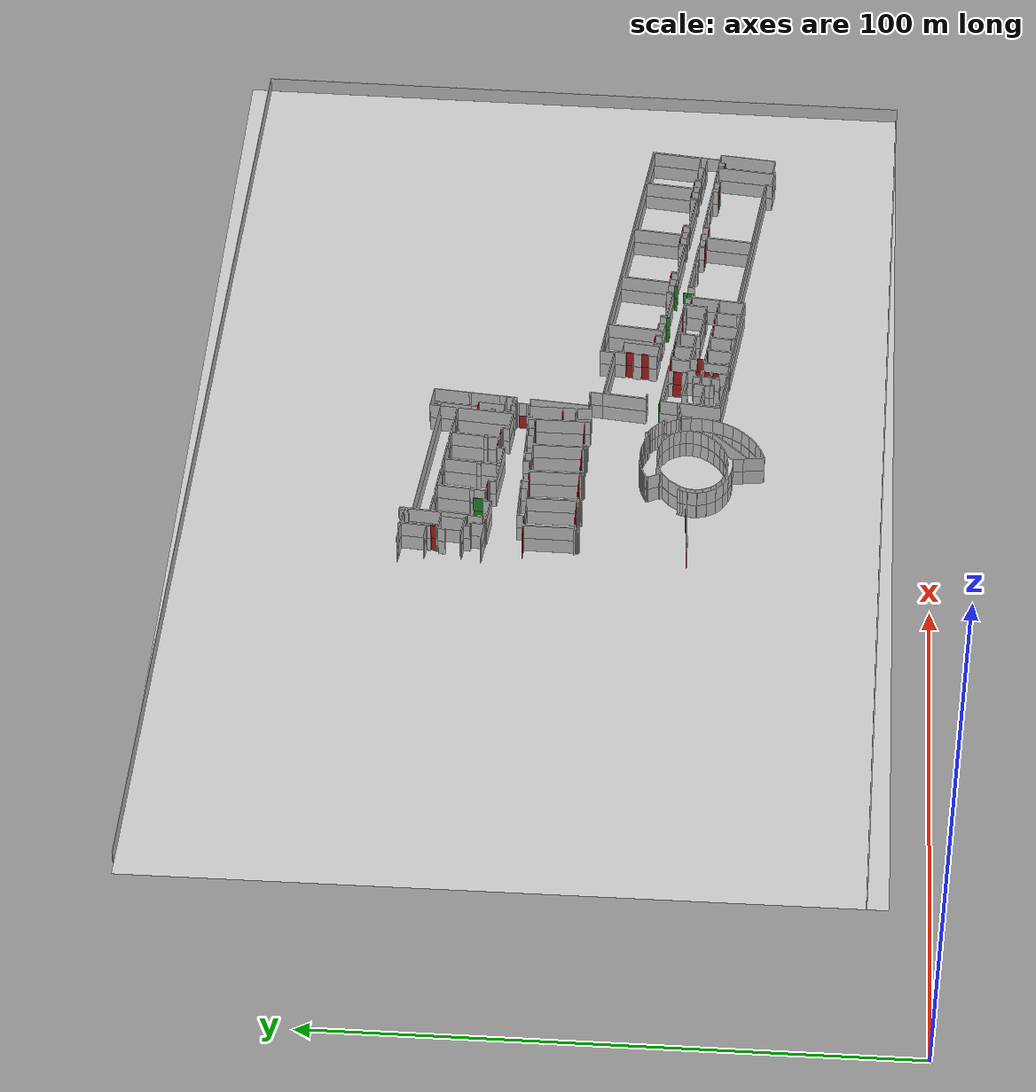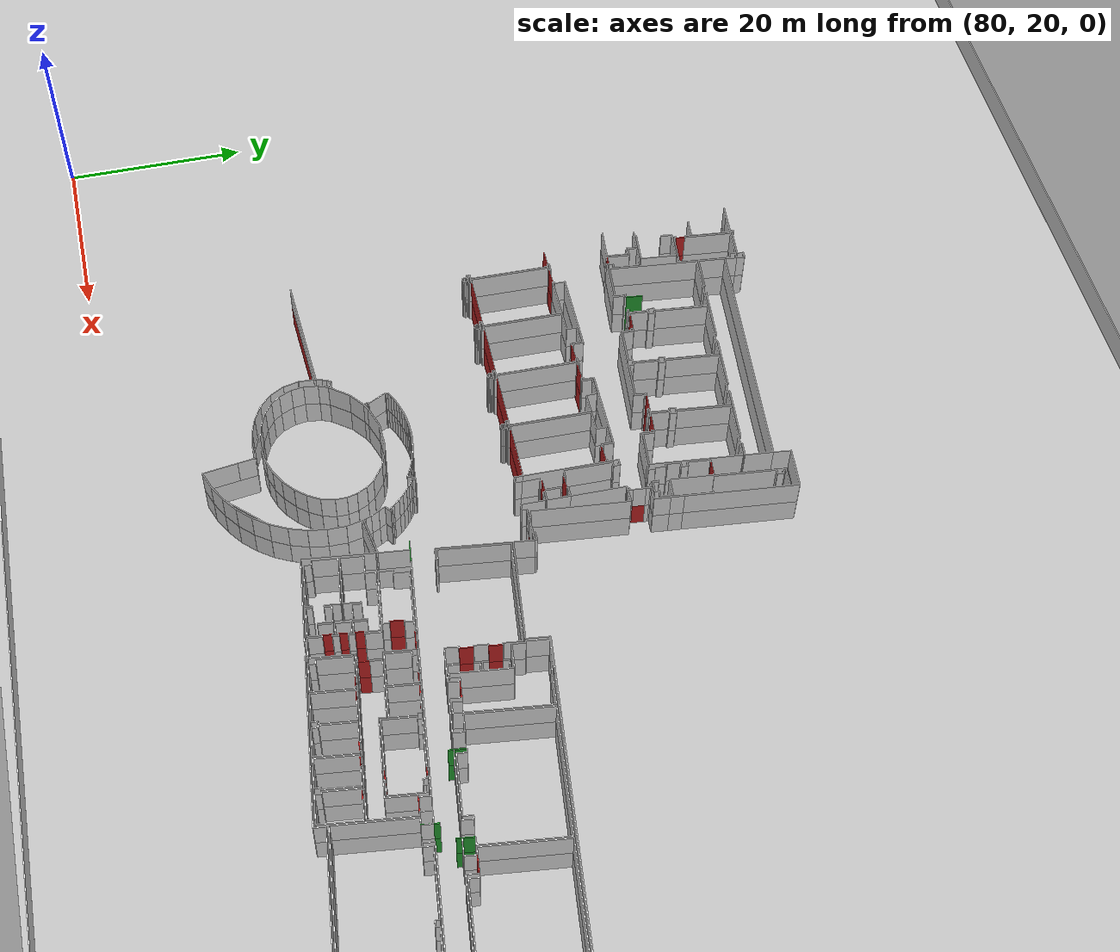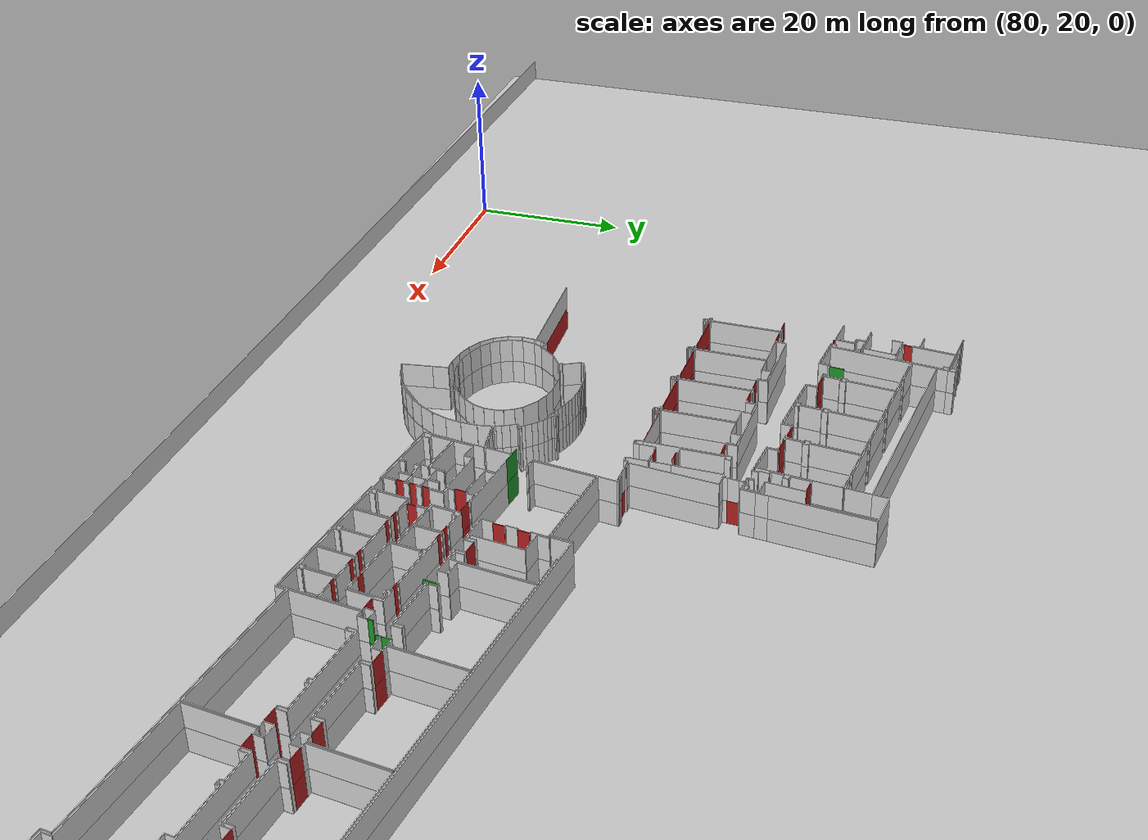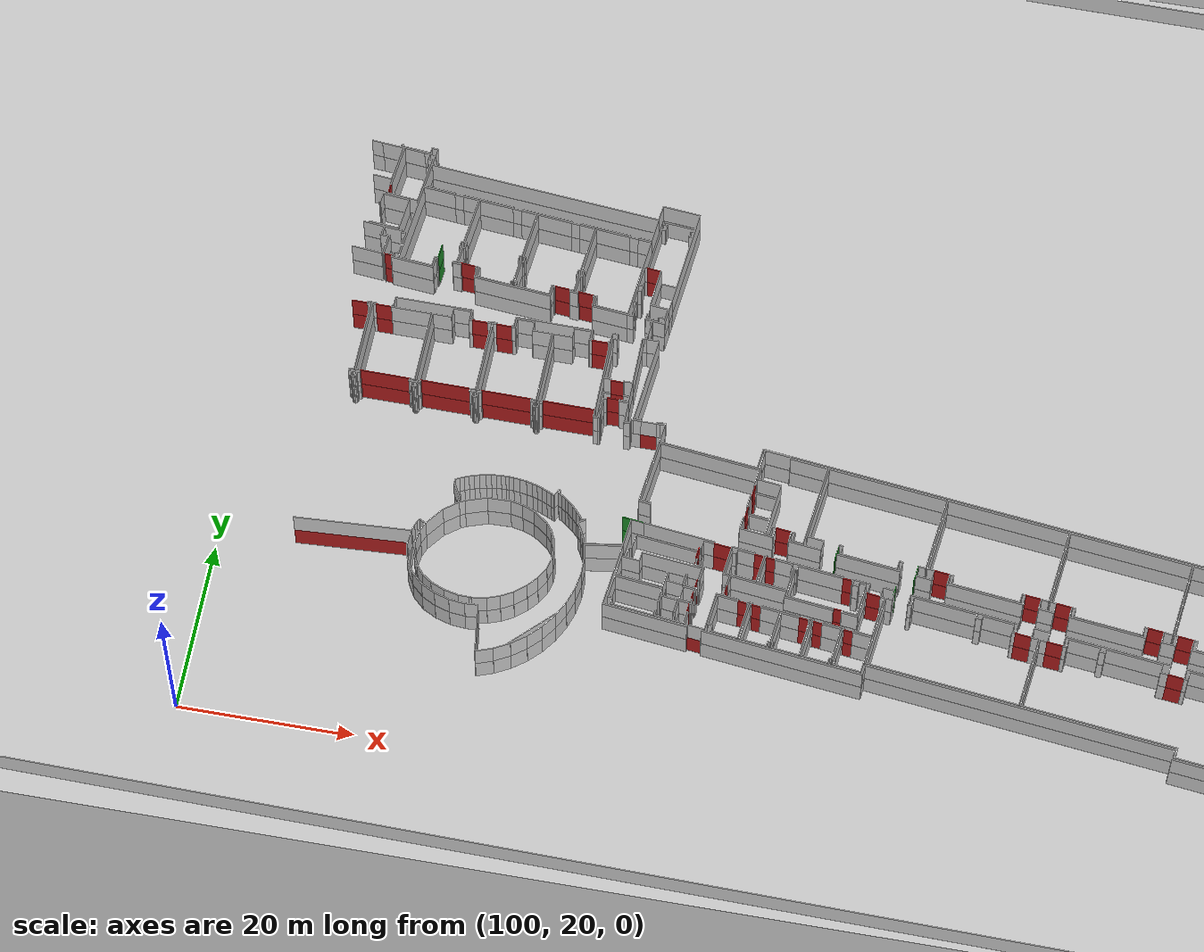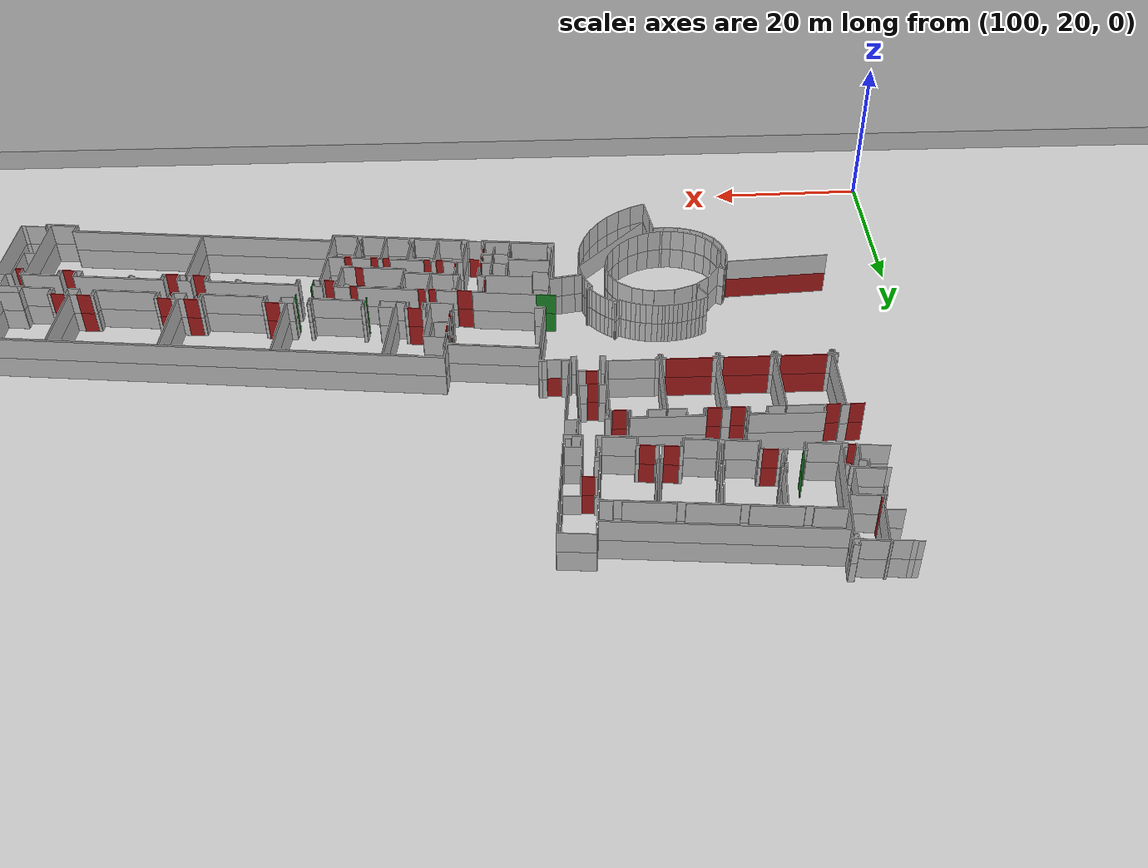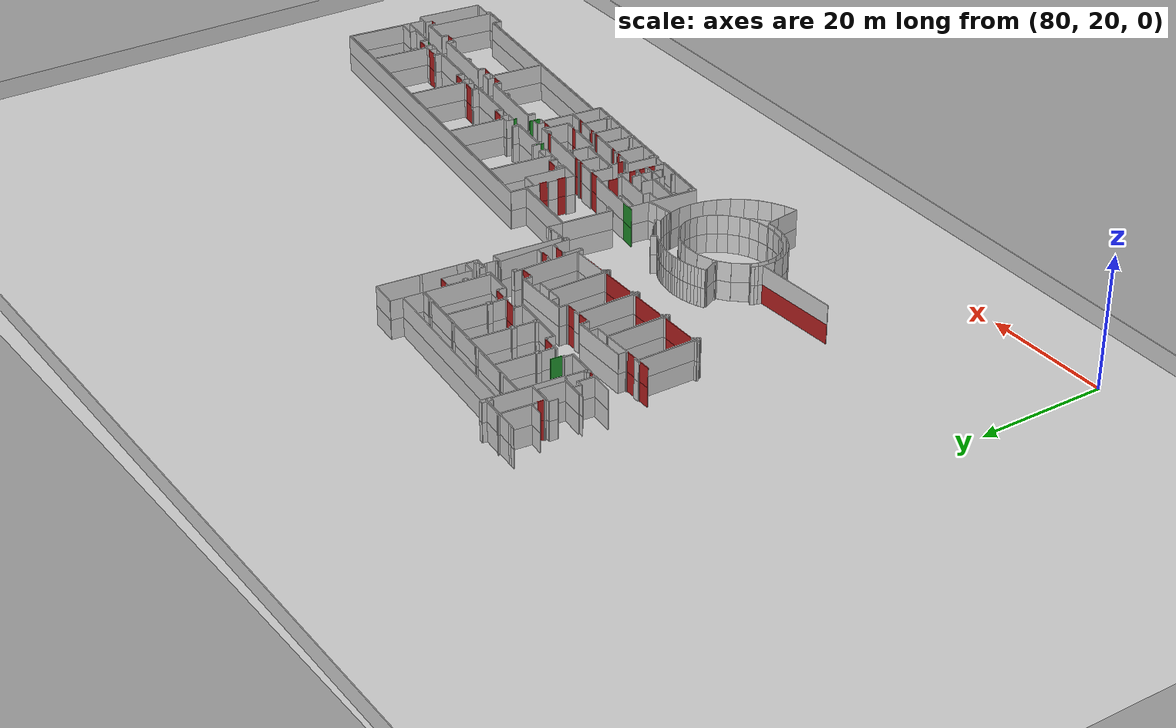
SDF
<sdf version="1.6">
 <world name="default">
  <model name="floor1">
   <static>true</static>
   <pose>135.22499999997672 69.80499999970198 0.0 0 0 0</pose>
   <link name="link">
    <visual name="visual">
     <geometry><box><size>208.23000000003958 126.51000000024214 0.01</size></box></geometry>
     <material>
      <script><uri>file://media/materials/scripts/gazebo.material</uri><name>Gazebo/Concrete</name></script>
      <ambient>1 1 1 0.5</ambient>
      <diffuse>1 1 1 0.5</diffuse>
     </material>
    </visual>
    <collision name="collision">
     <geometry><box><size>208.23000000003958 126.51000000024214 0.01</size></box></geometry>
     <surface><friction><ode><mu>1.0</mu><mu2>1.0</mu2></ode></friction></surface>
    </collision>
   </link>
  </model>
  <model name="elevator">
   <pose>141.07 64.850 0.080 0 0 -1.5708</pose>
   <link name="link">
    <inertial><mass>800</mass></inertial>
    <collision name="floor_collision"><geometry><box><size>2.10 2.91 0.15</size></box></geometry></collision>
    <visual name="floor_visual"><geometry><box><size>2.10 2.91 0.15</size></box></geometry></visual>
   </link>
   <link name="door">
    <pose>1.0745 0 1.125 0 0 0</pose>
    <collision name="collision"><geometry><box><size>0.05 1.0 2.25</size></box></geometry></collision>
    <visual name="visual">
     <geometry><box><size>0.05 1.0 2.25</size></box></geometry>
     <material><script><name>Gazebo/Green</name></script></material>
    </visual>
   </link>
   <joint name="door_joint" type="prismatic">
    <parent>link</parent>
    <child>door</child>
    <axis>
     <xyz>0 1 0</xyz>
     <limit><lower>0</lower><upper>1</upper><effort>30</effort></limit>
     <dynamics><damping>2</damping></dynamics>
    </axis>
   </joint>
   <joint name="lift_joint" type="prismatic">
    <parent>world</parent>
    <child>link</child>
    <axis>
     <xyz>0 0 1</xyz>
     <limit><lower>0</lower><upper>10</upper><effort>300000</effort></limit>
     <dynamics><damping>5</damping></dynamics>
    </axis>
    <physics><ode><implicit_spring_damper>1</implicit_spring_damper></ode></physics>
   </joint>
   <plugin filename="libgazebo_ros_elevator.so" name="elevator_plugin">
    <lift_joint>elevator::lift_joint</lift_joint>
    <door_joint>elevator::door_joint</door_joint>
    <floor_height>3.075</floor_height>
    <door_wait_time>10</door_wait_time>
    <topic>/elevator</topic>
   </plugin>
  </model>
  <model name="wall_153.8_39.0_1.5">
   <static>true</static>
   <pose>153.77499999999418 38.99500000011176 1.5 0 0 -1.6814535479881518</pose>
   <link name="link">
    <visual name="visual">
     <geometry><box><size>0.9960923654221514 0.1 3</size></box></geometry>
     <material>
      <script><uri>file://media/materials/scripts/gazebo.material</uri><name>Gazebo/Red</name></script>
     </material>
    </visual>
    <collision name="collision"><geometry><box><size>0.9960923654221514 0.1 3</size></box></geometry></collision>
   </link>
  </model>
  <model name="wall_166.5_39.9_1.5">
   <static>true</static>
   <pose>166.50500000000466 39.91000000014901 1.5 0 0 -0.1206236686924795</pose>
   <link name="link">
    <visual name="visual">
     <geometry><box><size>0.9972462083198822 0.1 3</size></box></geometry>
     <material>
      <script><uri>file://media/materials/scripts/gazebo.material</uri><name>Gazebo/Red</name></script>
     </material>
    </visual>
    <collision name="collision"><geometry><box><size>0.9972462083198822 0.1 3</size></box></geometry></collision>
   </link>
  </model>
  <model name="wall_153.7_45.9_1.5">
   <static>true</static>
   <pose>153.6600000000035 45.92999999993481 1.5 0 0 -1.6918235466009592</pose>
   <link name="link">
    <visual name="visual">
     <geometry><box><size>1.4909057649436974 0.1 3</size></box></geometry>
     <material>
      <script><uri>file://media/materials/scripts/gazebo.material</uri><name>Gazebo/Red</name></script>
     </material>
    </visual>
    <collision name="collision"><geometry><box><size>1.4909057649436974 0.1 3</size></box></geometry></collision>
   </link>
  </model>
  <model name="wall_161.1_40.6_1.5">
   <static>true</static>
   <pose>161.1350000000093 40.56000000005588 1.5 0 0 -0.1206236686924795</pose>
   <link name="link">
    <visual name="visual">
     <geometry><box><size>0.9972462083198822 0.1 3</size></box></geometry>
     <material>
      <script><uri>file://media/materials/scripts/gazebo.material</uri><name>Gazebo/Red</name></script>
     </material>
    </visual>
    <collision name="collision"><geometry><box><size>0.9972462083198822 0.1 3</size></box></geometry></collision>
   </link>
  </model>
  <model name="wall_191.0_47.1_1.5">
   <static>true</static>
   <pose>190.97500000000582 47.06499999994412 1.5 0 0 3.02480805813934</pose>
   <link name="link">
    <visual name="visual">
     <geometry><box><size>1.8022763383869123 0.1 3</size></box></geometry>
     <material>
      <script><uri>file://media/materials/scripts/gazebo.material</uri><name>Gazebo/Red</name></script>
     </material>
    </visual>
    <collision name="collision"><geometry><box><size>1.8022763383869123 0.1 3</size></box></geometry></collision>
   </link>
  </model>
  <model name="wall_180.6_48.3_1.5">
   <static>true</static>
   <pose>180.6350000000093 48.31000000005588 1.5 0 0 3.0193009299888676</pose>
   <link name="link">
    <visual name="visual">
     <geometry><box><size>1.8034688796923075 0.1 3</size></box></geometry>
     <material>
      <script><uri>file://media/materials/scripts/gazebo.material</uri><name>Gazebo/Red</name></script>
     </material>
    </visual>
    <collision name="collision"><geometry><box><size>1.8034688796923075 0.1 3</size></box></geometry></collision>
   </link>
  </model>
  <model name="wall_154.0_40.6_1.5">
   <static>true</static>
   <pose>153.9649999999965 40.574999999953434 1.5 0 0 -1.693768196390317</pose>
   <link name="link">
    <visual name="visual">
     <geometry><box><size>0.8967719889926413 0.1 3</size></box></geometry>
     <material>
      <script><uri>file://media/materials/scripts/gazebo.material</uri><name>Gazebo/Red</name></script>
     </material>
    </visual>
    <collision name="collision"><geometry><box><size>0.8967719889926413 0.1 3</size></box></geometry></collision>
   </link>
  </model>
  <model name="wall_168.1_39.7_1.5">
   <static>true</static>
   <pose>168.09500000000116 39.71999999997206 1.5 0 0 -0.12062366822190172</pose>
   <link name="link">
    <visual name="visual">
     <geometry><box><size>0.9972462083216332 0.1 3</size></box></geometry>
     <material>
      <script><uri>file://media/materials/scripts/gazebo.material</uri><name>Gazebo/Red</name></script>
     </material>
    </visual>
    <collision name="collision"><geometry><box><size>0.9972462083216332 0.1 3</size></box></geometry></collision>
   </link>
  </model>
  <model name="wall_194.4_46.6_1.5">
   <static>true</static>
   <pose>194.41500000000815 46.64999999990687 1.5 0 0 3.0193009299849303</pose>
   <link name="link">
    <visual name="visual">
     <geometry><box><size>1.8034688796345346 0.1 3</size></box></geometry>
     <material>
      <script><uri>file://media/materials/scripts/gazebo.material</uri><name>Gazebo/Red</name></script>
     </material>
    </visual>
    <collision name="collision"><geometry><box><size>1.8034688796345346 0.1 3</size></box></geometry></collision>
   </link>
  </model>
  <model name="wall_204.7_45.4_1.5">
   <static>true</static>
   <pose>204.74499999999534 45.40499999979511 1.5 0 0 3.0248080581431034</pose>
   <link name="link">
    <visual name="visual">
     <geometry><box><size>1.8022763384447233 0.1 3</size></box></geometry>
     <material>
      <script><uri>file://media/materials/scripts/gazebo.material</uri><name>Gazebo/Red</name></script>
     </material>
    </visual>
    <collision name="collision"><geometry><box><size>1.8022763384447233 0.1 3</size></box></geometry></collision>
   </link>
  </model>
  <model name="wall_145.9_48.8_1.5">
   <static>true</static>
   <pose>145.9100000000326 48.77000000001863 1.5 0 0 3.0202406530918178</pose>
   <link name="link">
    <visual name="visual">
     <geometry><box><size>2.478225171308079 0.1 3</size></box></geometry>
     <material>
      <script><uri>file://media/materials/scripts/gazebo.material</uri><name>Gazebo/Green</name></script>
     </material>
    </visual>
    <collision name="collision"><geometry><box><size>2.478225171308079 0.1 3</size></box></geometry></collision>
   </link>
  </model>
  <model name="wall_156.3_47.3_1.5">
   <static>true</static>
   <pose>156.25500000000466 47.32000000006519 1.5 0 0 -0.12002333835124222</pose>
   <link name="link">
    <visual name="visual">
     <geometry><box><size>2.004420115606183 0.1 3</size></box></geometry>
     <material>
      <script><uri>file://media/materials/scripts/gazebo.material</uri><name>Gazebo/Red</name></script>
     </material>
    </visual>
    <collision name="collision"><geometry><box><size>2.004420115606183 0.1 3</size></box></geometry></collision>
   </link>
  </model>
  <model name="wall_160.4_46.8_1.5">
   <static>true</static>
   <pose>160.3850000000093 46.81999999983236 1.5 0 0 -0.1206236686924795</pose>
   <link name="link">
    <visual name="visual">
     <geometry><box><size>0.9972462083198822 0.1 3</size></box></geometry>
     <material>
      <script><uri>file://media/materials/scripts/gazebo.material</uri><name>Gazebo/Red</name></script>
     </material>
    </visual>
    <collision name="collision"><geometry><box><size>0.9972462083198822 0.1 3</size></box></geometry></collision>
   </link>
  </model>
  <model name="wall_161.8_46.7_1.5">
   <static>true</static>
   <pose>161.7600000000093 46.66000000014901 1.5 0 0 -0.11942892612851068</pose>
   <link name="link">
    <visual name="visual">
     <geometry><box><size>1.0071742649744493 0.1 3</size></box></geometry>
     <material>
      <script><uri>file://media/materials/scripts/gazebo.material</uri><name>Gazebo/Red</name></script>
     </material>
    </visual>
    <collision name="collision"><geometry><box><size>1.0071742649744493 0.1 3</size></box></geometry></collision>
   </link>
  </model>
  <model name="wall_170.5_45.6_1.5">
   <static>true</static>
   <pose>170.48499999998603 45.609999999869615 1.5 0 0 -0.1206236686924795</pose>
   <link name="link">
    <visual name="visual">
     <geometry><box><size>0.9972462083198822 0.1 3</size></box></geometry>
     <material>
      <script><uri>file://media/materials/scripts/gazebo.material</uri><name>Gazebo/Red</name></script>
     </material>
    </visual>
    <collision name="collision"><geometry><box><size>0.9972462083198822 0.1 3</size></box></geometry></collision>
   </link>
  </model>
  <model name="wall_175.8_44.9_1.5">
   <static>true</static>
   <pose>175.80500000022585 44.86500000022352 1.5 0 0 1.4540117310915928</pose>
   <link name="link">
    <visual name="visual">
     <geometry><box><size>1.802276338498982 0.1 3</size></box></geometry>
     <material>
      <script><uri>file://media/materials/scripts/gazebo.material</uri><name>Gazebo/Green</name></script>
     </material>
    </visual>
    <collision name="collision"><geometry><box><size>1.802276338498982 0.1 3</size></box></geometry></collision>
   </link>
  </model>
  <model name="wall_190.5_42.2_1.5">
   <static>true</static>
   <pose>190.5 42.18999999994412 1.5 0 0 -0.12161902311549111</pose>
   <link name="link">
    <visual name="visual">
     <geometry><box><size>1.8133946068224918 0.1 3</size></box></geometry>
     <material>
      <script><uri>file://media/materials/scripts/gazebo.material</uri><name>Gazebo/Red</name></script>
     </material>
    </visual>
    <collision name="collision"><geometry><box><size>1.8133946068224918 0.1 3</size></box></geometry></collision>
   </link>
  </model>
  <model name="wall_194.0_41.8_1.5">
   <static>true</static>
   <pose>194.0350000000035 41.765000000130385 1.5 0 0 -0.11678459545045303</pose>
   <link name="link">
    <visual name="visual">
     <geometry><box><size>1.8022763383869123 0.1 3</size></box></geometry>
     <material>
      <script><uri>file://media/materials/scripts/gazebo.material</uri><name>Gazebo/Red</name></script>
     </material>
    </visual>
    <collision name="collision"><geometry><box><size>1.8022763383869123 0.1 3</size></box></geometry></collision>
   </link>
  </model>
  <model name="wall_207.6_40.1_1.5">
   <static>true</static>
   <pose>207.55999999999767 40.13500000000931 1.5 0 0 -0.11743469003206944</pose>
   <link name="link">
    <visual name="visual">
     <geometry><box><size>1.7923448329714338 0.1 3</size></box></geometry>
     <material>
      <script><uri>file://media/materials/scripts/gazebo.material</uri><name>Gazebo/Red</name></script>
     </material>
    </visual>
    <collision name="collision"><geometry><box><size>1.7923448329714338 0.1 3</size></box></geometry></collision>
   </link>
  </model>
  <model name="wall_177.8_47.7_1.5">
   <static>true</static>
   <pose>177.8499999999185 47.734999999869615 1.5 0 0 -1.6930880506520969</pose>
   <link name="link">
    <visual name="visual">
     <geometry><box><size>1.803468879749112 0.1 3</size></box></geometry>
     <material>
      <script><uri>file://media/materials/scripts/gazebo.material</uri><name>Gazebo/Green</name></script>
     </material>
    </visual>
    <collision name="collision"><geometry><box><size>1.803468879749112 0.1 3</size></box></geometry></collision>
   </link>
  </model>
  <model name="wall_168.8_48.8_1.5">
   <static>true</static>
   <pose>168.83500000002095 48.825000000186265 1.5 0 0 -1.6875809222415865</pose>
   <link name="link">
    <visual name="visual">
     <geometry><box><size>1.8022763384447233 0.1 3</size></box></geometry>
     <material>
      <script><uri>file://media/materials/scripts/gazebo.material</uri><name>Gazebo/Green</name></script>
     </material>
    </visual>
    <collision name="collision"><geometry><box><size>1.8022763384447233 0.1 3</size></box></geometry></collision>
   </link>
  </model>
  <model name="wall_162.6_50.5_1.5">
   <static>true</static>
   <pose>162.57000000000698 50.484999999869615 1.5 0 0 3.02415796381574</pose>
   <link name="link">
    <visual name="visual">
     <geometry><box><size>1.7923448329168745 0.1 3</size></box></geometry>
     <material>
      <script><uri>file://media/materials/scripts/gazebo.material</uri><name>Gazebo/Red</name></script>
     </material>
    </visual>
    <collision name="collision"><geometry><box><size>1.7923448329168745 0.1 3</size></box></geometry></collision>
   </link>
  </model>
  <model name="wall_158.2_51.9_1.5">
   <static>true</static>
   <pose>158.16500000000815 51.93999999994412 1.5 0 0 1.4482254516771895</pose>
   <link name="link">
    <visual name="visual">
     <geometry><box><size>1.3904315875604971 0.1 3</size></box></geometry>
     <material>
      <script><uri>file://media/materials/scripts/gazebo.material</uri><name>Gazebo/Red</name></script>
     </material>
    </visual>
    <collision name="collision"><geometry><box><size>1.3904315875604971 0.1 3</size></box></geometry></collision>
   </link>
  </model>
  <model name="wall_158.5_54.8_1.5">
   <static>true</static>
   <pose>158.51499999998487 54.800000000046566 1.5 0 0 1.4482254517181363</pose>
   <link name="link">
    <visual name="visual">
     <geometry><box><size>1.390431588022665 0.1 3</size></box></geometry>
     <material>
      <script><uri>file://media/materials/scripts/gazebo.material</uri><name>Gazebo/Red</name></script>
     </material>
    </visual>
    <collision name="collision"><geometry><box><size>1.390431588022665 0.1 3</size></box></geometry></collision>
   </link>
  </model>
  <model name="wall_173.6_44.2_1.5">
   <static>true</static>
   <pose>173.6149999999907 44.21999999997206 1.5 0 0 -0.12022278677294355</pose>
   <link name="link">
    <visual name="visual">
     <geometry><box><size>1.5008331019912227 0.1 3</size></box></geometry>
     <material>
      <script><uri>file://media/materials/scripts/gazebo.material</uri><name>Gazebo/Red</name></script>
     </material>
    </visual>
    <collision name="collision"><geometry><box><size>1.5008331019912227 0.1 3</size></box></geometry></collision>
   </link>
  </model>
  <model name="wall_214.1_39.3_1.5">
   <static>true</static>
   <pose>214.1350000000093 39.34499999997206 1.5 0 0 -0.11870533746682131</pose>
   <link name="link">
    <visual name="visual">
     <geometry><box><size>1.097724920014552 0.1 3</size></box></geometry>
     <material>
      <script><uri>file://media/materials/scripts/gazebo.material</uri><name>Gazebo/Red</name></script>
     </material>
    </visual>
    <collision name="collision"><geometry><box><size>1.097724920014552 0.1 3</size></box></geometry></collision>
   </link>
  </model>
  <model name="wall_214.4_40.5_1.5">
   <static>true</static>
   <pose>214.44000000006054 40.52000000001863 1.5 0 0 3.0182549527621143</pose>
   <link name="link">
    <visual name="visual">
     <geometry><box><size>2.438524143724567 0.1 3</size></box></geometry>
     <material>
      <script><uri>file://media/materials/scripts/gazebo.material</uri><name>Gazebo/Green</name></script>
     </material>
    </visual>
    <collision name="collision"><geometry><box><size>2.438524143724567 0.1 3</size></box></geometry></collision>
   </link>
  </model>
  <model name="wall_208.1_45.0_1.5">
   <static>true</static>
   <pose>208.09500000000116 45.0 1.5 0 0 3.0193009299849303</pose>
   <link name="link">
    <visual name="visual">
     <geometry><box><size>1.8034688796345346 0.1 3</size></box></geometry>
     <material>
      <script><uri>file://media/materials/scripts/gazebo.material</uri><name>Gazebo/Red</name></script>
     </material>
    </visual>
    <collision name="collision"><geometry><box><size>1.8034688796345346 0.1 3</size></box></geometry></collision>
   </link>
  </model>
  <model name="wall_170.0_41.7_1.5">
   <static>true</static>
   <pose>170.0100000000093 41.68999999994412 1.5 0 0 -0.11942892612851068</pose>
   <link name="link">
    <visual name="visual">
     <geometry><box><size>1.0071742649744493 0.1 3</size></box></geometry>
     <material>
      <script><uri>file://media/materials/scripts/gazebo.material</uri><name>Gazebo/Red</name></script>
     </material>
    </visual>
    <collision name="collision"><geometry><box><size>1.0071742649744493 0.1 3</size></box></geometry></collision>
   </link>
  </model>
  <model name="wall_154.2_42.2_1.5">
   <static>true</static>
   <pose>154.15000000002328 42.15500000002794 1.5 0 0 -1.6914199953995817</pose>
   <link name="link">
    <visual name="visual">
     <geometry><box><size>0.997246208074735 0.1 3</size></box></geometry>
     <material>
      <script><uri>file://media/materials/scripts/gazebo.material</uri><name>Gazebo/Red</name></script>
     </material>
    </visual>
    <collision name="collision"><geometry><box><size>0.997246208074735 0.1 3</size></box></geometry></collision>
   </link>
  </model>
  <model name="wall_157.5_41.9_1.5">
   <static>true</static>
   <pose>157.51500000001397 41.94500000006519 1.5 0 0 -1.6895016639081246</pose>
   <link name="link">
    <visual name="visual">
     <geometry><box><size>1.0977249203199801 0.1 3</size></box></geometry>
     <material>
      <script><uri>file://media/materials/scripts/gazebo.material</uri><name>Gazebo/Red</name></script>
     </material>
    </visual>
    <collision name="collision"><geometry><box><size>1.0977249203199801 0.1 3</size></box></geometry></collision>
   </link>
  </model>
  <model name="wall_154.9_36.9_1.5">
   <static>true</static>
   <pose>154.86999999999534 36.85000000009313 1.5 0 0 -0.11990398547329398</pose>
   <link name="link">
    <visual name="visual">
     <geometry><box><size>1.6720047847367918 0.1 3</size></box></geometry>
     <material>
      <script><uri>file://media/materials/scripts/gazebo.material</uri><name>Gazebo/Red</name></script>
     </material>
    </visual>
    <collision name="collision"><geometry><box><size>1.6720047847367918 0.1 3</size></box></geometry></collision>
   </link>
  </model>
  <model name="wall_159.5_40.8_1.5">
   <static>true</static>
   <pose>159.5449999999837 40.75 1.5 0 0 -0.1206236686924795</pose>
   <link name="link">
    <visual name="visual">
     <geometry><box><size>0.9972462083198822 0.1 3</size></box></geometry>
     <material>
      <script><uri>file://media/materials/scripts/gazebo.material</uri><name>Gazebo/Red</name></script>
     </material>
    </visual>
    <collision name="collision"><geometry><box><size>0.9972462083198822 0.1 3</size></box></geometry></collision>
   </link>
  </model>
  <model name="wall_171.6_39.3_1.5">
   <static>true</static>
   <pose>171.56500000000233 39.300000000046566 1.5 0 0 -0.12062366822892527</pose>
   <link name="link">
    <visual name="visual">
     <geometry><box><size>0.9972462082638486 0.1 3</size></box></geometry>
     <material>
      <script><uri>file://media/materials/scripts/gazebo.material</uri><name>Gazebo/Red</name></script>
     </material>
    </visual>
    <collision name="collision"><geometry><box><size>0.9972462082638486 0.1 3</size></box></geometry></collision>
   </link>
  </model>
  <model name="wall_135.5_76.8_1.5">
   <static>true</static>
   <pose>135.49499999999534 76.79000000003725 1.5 0 0 -0.10022174961299568</pose>
   <link name="link">
    <visual name="visual">
     <geometry><box><size>1.799027515083101 0.1 3</size></box></geometry>
     <material>
      <script><uri>file://media/materials/scripts/gazebo.material</uri><name>Gazebo/Red</name></script>
     </material>
    </visual>
    <collision name="collision"><geometry><box><size>1.799027515083101 0.1 3</size></box></geometry></collision>
   </link>
  </model>
  <model name="wall_132.7_77.1_1.5">
   <static>true</static>
   <pose>132.7049999999872 77.07000000006519 1.5 0 0 -0.10022174987377463</pose>
   <link name="link">
    <visual name="visual">
     <geometry><box><size>1.7990275150717767 0.1 3</size></box></geometry>
     <material>
      <script><uri>file://media/materials/scripts/gazebo.material</uri><name>Gazebo/Red</name></script>
     </material>
    </visual>
    <collision name="collision"><geometry><box><size>1.7990275150717767 0.1 3</size></box></geometry></collision>
   </link>
  </model>
  <model name="wall_112.2_77.9_1.5">
   <static>true</static>
   <pose>112.1699999999837 77.92500000004657 1.5 0 0 -0.09966865283695012</pose>
   <link name="link">
    <visual name="visual">
     <geometry><box><size>0.9044888059555555 0.1 3</size></box></geometry>
     <material>
      <script><uri>file://media/materials/scripts/gazebo.material</uri><name>Gazebo/Red</name></script>
     </material>
    </visual>
    <collision name="collision"><geometry><box><size>0.9044888059555555 0.1 3</size></box></geometry></collision>
   </link>
  </model>
  <model name="wall_110.6_86.8_1.5">
   <static>true</static>
   <pose>110.55999999999767 86.81499999994412 1.5 0 0 1.4701276746829237</pose>
   <link name="link">
    <visual name="visual">
     <geometry><box><size>0.9950376879485058 0.1 3</size></box></geometry>
     <material>
      <script><uri>file://media/materials/scripts/gazebo.material</uri><name>Gazebo/Red</name></script>
     </material>
    </visual>
    <collision name="collision"><geometry><box><size>0.9950376879485058 0.1 3</size></box></geometry></collision>
   </link>
  </model>
  <model name="wall_121.5_78.2_1.5">
   <static>true</static>
   <pose>121.54000000000815 78.20999999996275 1.5 0 0 -0.09966865232787321</pose>
   <link name="link">
    <visual name="visual">
     <geometry><box><size>1.808977611760522 0.1 3</size></box></geometry>
     <material>
      <script><uri>file://media/materials/scripts/gazebo.material</uri><name>Gazebo/Red</name></script>
     </material>
    </visual>
    <collision name="collision"><geometry><box><size>1.808977611760522 0.1 3</size></box></geometry></collision>
   </link>
  </model>
  <model name="wall_118.0_79.5_1.5">
   <static>true</static>
   <pose>117.96999999985565 79.46499999985099 1.5 0 0 1.470574577181901</pose>
   <link name="link">
    <visual name="visual">
     <geometry><box><size>1.799027515083101 0.1 3</size></box></geometry>
     <material>
      <script><uri>file://media/materials/scripts/gazebo.material</uri><name>Gazebo/Green</name></script>
     </material>
    </visual>
    <collision name="collision"><geometry><box><size>1.799027515083101 0.1 3</size></box></geometry></collision>
   </link>
  </model>
  <model name="wall_141.0_66.0_1.5">
   <static>true</static>
   <pose>141.0100000000093 65.9800000002142 1.5 0 0 -0.01428474260046099</pose>
   <link name="link">
    <visual name="visual">
     <geometry><box><size>1.4001428498785178 0.1 3</size></box></geometry>
     <material>
      <script><uri>file://media/materials/scripts/gazebo.material</uri><name>Gazebo/Red</name></script>
     </material>
    </visual>
    <collision name="collision"><geometry><box><size>1.4001428498785178 0.1 3</size></box></geometry></collision>
   </link>
  </model>
  <model name="wall_141.0_63.7_1.5">
   <static>true</static>
   <pose>140.9899999999907 63.68500000005588 1.5 0 0 -0.007142735509647464</pose>
   <link name="link">
    <visual name="visual">
     <geometry><box><size>1.4000357138518724 0.1 3</size></box></geometry>
     <material>
      <script><uri>file://media/materials/scripts/gazebo.material</uri><name>Gazebo/Red</name></script>
     </material>
    </visual>
    <collision name="collision"><geometry><box><size>1.4000357138518724 0.1 3</size></box></geometry></collision>
   </link>
  </model>
  <model name="wall_142.5_81.3_1.5">
   <static>true</static>
   <pose>142.54999999998836 81.33499999996275 1.5 0 0 -0.09966865273705577</pose>
   <link name="link">
    <visual name="visual">
     <geometry><box><size>1.5074813432052014 0.1 3</size></box></geometry>
     <material>
      <script><uri>file://media/materials/scripts/gazebo.material</uri><name>Gazebo/Red</name></script>
     </material>
    </visual>
    <collision name="collision"><geometry><box><size>1.5074813432052014 0.1 3</size></box></geometry></collision>
   </link>
  </model>
  <model name="wall_138.2_70.8_1.5">
   <static>true</static>
   <pose>138.2149999999965 70.78000000002794 1.5 0 0 -0.01104927408967263</pose>
   <link name="link">
    <visual name="visual">
     <geometry><box><size>1.810110493862824 0.1 3</size></box></geometry>
     <material>
      <script><uri>file://media/materials/scripts/gazebo.material</uri><name>Gazebo/Red</name></script>
     </material>
    </visual>
    <collision name="collision"><geometry><box><size>1.810110493862824 0.1 3</size></box></geometry></collision>
   </link>
  </model>
  <model name="wall_127.1_71.0_1.5">
   <static>true</static>
   <pose>127.05000000001746 70.9550000000745 1.5 0 0 3.1249275297309125</pose>
   <link name="link">
    <visual name="visual">
     <geometry><box><size>1.8002499826340055 0.1 3</size></box></geometry>
     <material>
      <script><uri>file://media/materials/scripts/gazebo.material</uri><name>Gazebo/Red</name></script>
     </material>
    </visual>
    <collision name="collision"><geometry><box><size>1.8002499826340055 0.1 3</size></box></geometry></collision>
   </link>
  </model>
  <model name="wall_124.3_71.0_1.5">
   <static>true</static>
   <pose>124.26499999998487 70.98999999999069 1.5 0 0 3.1305433795001205</pose>
   <link name="link">
    <visual name="visual">
     <geometry><box><size>1.810110493862824 0.1 3</size></box></geometry>
     <material>
      <script><uri>file://media/materials/scripts/gazebo.material</uri><name>Gazebo/Red</name></script>
     </material>
    </visual>
    <collision name="collision"><geometry><box><size>1.810110493862824 0.1 3</size></box></geometry></collision>
   </link>
  </model>
  <model name="wall_113.0_71.1_1.5">
   <static>true</static>
   <pose>113.03500000000349 71.13000000012107 1.5 0 0 3.1305433795001205</pose>
   <link name="link">
    <visual name="visual">
     <geometry><box><size>1.810110493862824 0.1 3</size></box></geometry>
     <material>
      <script><uri>file://media/materials/scripts/gazebo.material</uri><name>Gazebo/Red</name></script>
     </material>
    </visual>
    <collision name="collision"><geometry><box><size>1.810110493862824 0.1 3</size></box></geometry></collision>
   </link>
  </model>
  <model name="wall_110.2_71.2_1.5">
   <static>true</static>
   <pose>110.23500000001513 71.17000000015832 1.5 0 0 3.1305433795001205</pose>
   <link name="link">
    <visual name="visual">
     <geometry><box><size>1.810110493862824 0.1 3</size></box></geometry>
     <material>
      <script><uri>file://media/materials/scripts/gazebo.material</uri><name>Gazebo/Red</name></script>
     </material>
    </visual>
    <collision name="collision"><geometry><box><size>1.810110493862824 0.1 3</size></box></geometry></collision>
   </link>
  </model>
  <model name="wall_143.5_73.3_1.5">
   <static>true</static>
   <pose>143.4550000000163 73.29500000015832 1.5 0 0 1.4718835320591757</pose>
   <link name="link">
    <visual name="visual">
     <geometry><box><size>1.3164345787571878 0.1 3</size></box></geometry>
     <material>
      <script><uri>file://media/materials/scripts/gazebo.material</uri><name>Gazebo/Red</name></script>
     </material>
    </visual>
    <collision name="collision"><geometry><box><size>1.3164345787571878 0.1 3</size></box></geometry></collision>
   </link>
  </model>
  <model name="wall_115.0_62.2_1.5">
   <static>true</static>
   <pose>115.0 62.23999999999069 1.5 0 0 -0.014034166198596688</pose>
   <link name="link">
    <visual name="visual">
     <geometry><box><size>5.700561375812611 0.1 3</size></box></geometry>
     <material>
      <script><uri>file://media/materials/scripts/gazebo.material</uri><name>Gazebo/Red</name></script>
     </material>
    </visual>
    <collision name="collision"><geometry><box><size>5.700561375812611 0.1 3</size></box></geometry></collision>
   </link>
  </model>
  <model name="wall_122.0_62.2_1.5">
   <static>true</static>
   <pose>122.01499999998487 62.15500000002794 1.5 0 0 -0.015760516353173326</pose>
   <link name="link">
    <visual name="visual">
     <geometry><box><size>5.710709237940267 0.1 3</size></box></geometry>
     <material>
      <script><uri>file://media/materials/scripts/gazebo.material</uri><name>Gazebo/Red</name></script>
     </material>
    </visual>
    <collision name="collision"><geometry><box><size>5.710709237940267 0.1 3</size></box></geometry></collision>
   </link>
  </model>
  <model name="wall_129.0_62.0_1.5">
   <static>true</static>
   <pose>129.01999999998952 62.049999999813735 1.5 0 0 -0.014034166280132265</pose>
   <link name="link">
    <visual name="visual">
     <geometry><box><size>5.7005613758773475 0.1 3</size></box></geometry>
     <material>
      <script><uri>file://media/materials/scripts/gazebo.material</uri><name>Gazebo/Red</name></script>
     </material>
    </visual>
    <collision name="collision"><geometry><box><size>5.7005613758773475 0.1 3</size></box></geometry></collision>
   </link>
  </model>
  <model name="wall_136.2_62.0_1.5">
   <static>true</static>
   <pose>136.19500000000698 61.950000000186265 1.5 0 0 -0.013266220046968015</pose>
   <link name="link">
    <visual name="visual">
     <geometry><box><size>6.030530656612972 0.1 3</size></box></geometry>
     <material>
      <script><uri>file://media/materials/scripts/gazebo.material</uri><name>Gazebo/Red</name></script>
     </material>
    </visual>
    <collision name="collision"><geometry><box><size>6.030530656612972 0.1 3</size></box></geometry></collision>
   </link>
  </model>
  <model name="wall_115.3_42.8_1.5">
   <static>true</static>
   <pose>115.2949999999837 42.75499999988824 1.5 0 0 0.0504469889047384</pose>
   <link name="link">
    <visual name="visual">
     <geometry><box><size>13.286903326222951 0.1 3</size></box></geometry>
     <material>
      <script><uri>file://media/materials/scripts/gazebo.material</uri><name>Gazebo/Red</name></script>
     </material>
    </visual>
    <collision name="collision"><geometry><box><size>13.286903326222951 0.1 3</size></box></geometry></collision>
   </link>
  </model>
  <model name="wall_145.4_61.4_1.5">
   <static>true</static>
   <pose>145.44999999998254 61.360000000102445 1.5 0 0 -0.011110653908026076</pose>
   <link name="link">
    <visual name="visual">
     <geometry><box><size>1.8001111076705336 0.1 3</size></box></geometry>
     <material>
      <script><uri>file://media/materials/scripts/gazebo.material</uri><name>Gazebo/Red</name></script>
     </material>
    </visual>
    <collision name="collision"><geometry><box><size>1.8001111076705336 0.1 3</size></box></geometry></collision>
   </link>
  </model>
  <model name="wall_153.8_39.0_4.5">
   <static>true</static>
   <pose>153.77499999999418 38.99500000011176 4.5 0 0 -1.6814535479881518</pose>
   <link name="link">
    <visual name="visual">
     <geometry><box><size>0.9960923654221514 0.1 3</size></box></geometry>
     <material>
      <script><uri>file://media/materials/scripts/gazebo.material</uri><name>Gazebo/Red</name></script>
     </material>
    </visual>
    <collision name="collision"><geometry><box><size>0.9960923654221514 0.1 3</size></box></geometry></collision>
   </link>
  </model>
  <model name="wall_166.5_39.9_4.5">
   <static>true</static>
   <pose>166.50500000000466 39.91000000014901 4.5 0 0 -0.1206236686924795</pose>
   <link name="link">
    <visual name="visual">
     <geometry><box><size>0.9972462083198822 0.1 3</size></box></geometry>
     <material>
      <script><uri>file://media/materials/scripts/gazebo.material</uri><name>Gazebo/Red</name></script>
     </material>
    </visual>
    <collision name="collision"><geometry><box><size>0.9972462083198822 0.1 3</size></box></geometry></collision>
   </link>
  </model>
  <model name="wall_161.1_40.6_4.5">
   <static>true</static>
   <pose>161.1350000000093 40.56000000005588 4.5 0 0 -0.1206236686924795</pose>
   <link name="link">
    <visual name="visual">
     <geometry><box><size>0.9972462083198822 0.1 3</size></box></geometry>
     <material>
      <script><uri>file://media/materials/scripts/gazebo.material</uri><name>Gazebo/Red</name></script>
     </material>
    </visual>
    <collision name="collision"><geometry><box><size>0.9972462083198822 0.1 3</size></box></geometry></collision>
   </link>
  </model>
  <model name="wall_191.0_47.1_4.5">
   <static>true</static>
   <pose>190.97500000000582 47.06499999994412 4.5 0 0 3.02480805813934</pose>
   <link name="link">
    <visual name="visual">
     <geometry><box><size>1.8022763383869123 0.1 3</size></box></geometry>
     <material>
      <script><uri>file://media/materials/scripts/gazebo.material</uri><name>Gazebo/Red</name></script>
     </material>
    </visual>
    <collision name="collision"><geometry><box><size>1.8022763383869123 0.1 3</size></box></geometry></collision>
   </link>
  </model>
  <model name="wall_180.6_48.3_4.5">
   <static>true</static>
   <pose>180.6350000000093 48.31000000005588 4.5 0 0 3.0193009299888676</pose>
   <link name="link">
    <visual name="visual">
     <geometry><box><size>1.8034688796923075 0.1 3</size></box></geometry>
     <material>
      <script><uri>file://media/materials/scripts/gazebo.material</uri><name>Gazebo/Red</name></script>
     </material>
    </visual>
    <collision name="collision"><geometry><box><size>1.8034688796923075 0.1 3</size></box></geometry></collision>
   </link>
  </model>
  <model name="wall_154.0_40.6_4.5">
   <static>true</static>
   <pose>153.9649999999965 40.574999999953434 4.5 0 0 -1.693768196390317</pose>
   <link name="link">
    <visual name="visual">
     <geometry><box><size>0.8967719889926413 0.1 3</size></box></geometry>
     <material>
      <script><uri>file://media/materials/scripts/gazebo.material</uri><name>Gazebo/Red</name></script>
     </material>
    </visual>
    <collision name="collision"><geometry><box><size>0.8967719889926413 0.1 3</size></box></geometry></collision>
   </link>
  </model>
  <model name="wall_168.1_39.7_4.5">
   <static>true</static>
   <pose>168.09500000000116 39.71999999997206 4.5 0 0 -0.12062366822190172</pose>
   <link name="link">
    <visual name="visual">
     <geometry><box><size>0.9972462083216332 0.1 3</size></box></geometry>
     <material>
      <script><uri>file://media/materials/scripts/gazebo.material</uri><name>Gazebo/Red</name></script>
     </material>
    </visual>
    <collision name="collision"><geometry><box><size>0.9972462083216332 0.1 3</size></box></geometry></collision>
   </link>
  </model>
  <model name="wall_194.4_46.6_4.5">
   <static>true</static>
   <pose>194.41500000000815 46.64999999990687 4.5 0 0 3.0193009299849303</pose>
   <link name="link">
    <visual name="visual">
     <geometry><box><size>1.8034688796345346 0.1 3</size></box></geometry>
     <material>
      <script><uri>file://media/materials/scripts/gazebo.material</uri><name>Gazebo/Red</name></script>
     </material>
    </visual>
    <collision name="collision"><geometry><box><size>1.8034688796345346 0.1 3</size></box></geometry></collision>
   </link>
  </model>
  <model name="wall_204.7_45.4_4.5">
   <static>true</static>
   <pose>204.74499999999534 45.40499999979511 4.5 0 0 3.0248080581431034</pose>
   <link name="link">
    <visual name="visual">
     <geometry><box><size>1.8022763384447233 0.1 3</size></box></geometry>
     <material>
      <script><uri>file://media/materials/scripts/gazebo.material</uri><name>Gazebo/Red</name></script>
     </material>
    </visual>
    <collision name="collision"><geometry><box><size>1.8022763384447233 0.1 3</size></box></geometry></collision>
   </link>
  </model>
  <model name="wall_145.9_48.8_4.5">
   <static>true</static>
   <pose>145.9100000000326 48.77000000001863 4.5 0 0 3.0202406530918178</pose>
   <link name="link">
    <visual name="visual">
     <geometry><box><size>2.478225171308079 0.1 3</size></box></geometry>
     <material>
      <script><uri>file://media/materials/scripts/gazebo.material</uri><name>Gazebo/Green</name></script>
     </material>
    </visual>
    <collision name="collision"><geometry><box><size>2.478225171308079 0.1 3</size></box></geometry></collision>
   </link>
  </model>
  <model name="wall_156.3_47.3_4.5">
   <static>true</static>
   <pose>156.25500000000466 47.32000000006519 4.5 0 0 -0.12002333835124222</pose>
   <link name="link">
    <visual name="visual">
     <geometry><box><size>2.004420115606183 0.1 3</size></box></geometry>
     <material>
      <script><uri>file://media/materials/scripts/gazebo.material</uri><name>Gazebo/Red</name></script>
     </material>
    </visual>
    <collision name="collision"><geometry><box><size>2.004420115606183 0.1 3</size></box></geometry></collision>
   </link>
  </model>
  <model name="wall_160.4_46.8_4.5">
   <static>true</static>
   <pose>160.3850000000093 46.81999999983236 4.5 0 0 -0.1206236686924795</pose>
   <link name="link">
    <visual name="visual">
     <geometry><box><size>0.9972462083198822 0.1 3</size></box></geometry>
     <material>
      <script><uri>file://media/materials/scripts/gazebo.material</uri><name>Gazebo/Red</name></script>
     </material>
    </visual>
    <collision name="collision"><geometry><box><size>0.9972462083198822 0.1 3</size></box></geometry></collision>
   </link>
  </model>
  <model name="wall_161.8_46.7_4.5">
   <static>true</static>
   <pose>161.7600000000093 46.66000000014901 4.5 0 0 -0.11942892612851068</pose>
   <link name="link">
    <visual name="visual">
     <geometry><box><size>1.0071742649744493 0.1 3</size></box></geometry>
     <material>
      <script><uri>file://media/materials/scripts/gazebo.material</uri><name>Gazebo/Red</name></script>
     </material>
    </visual>
    <collision name="collision"><geometry><box><size>1.0071742649744493 0.1 3</size></box></geometry></collision>
   </link>
  </model>
  <model name="wall_170.5_45.6_4.5">
   <static>true</static>
   <pose>170.48499999998603 45.609999999869615 4.5 0 0 -0.1206236686924795</pose>
   <link name="link">
    <visual name="visual">
     <geometry><box><size>0.9972462083198822 0.1 3</size></box></geometry>
     <material>
      <script><uri>file://media/materials/scripts/gazebo.material</uri><name>Gazebo/Red</name></script>
     </material>
    </visual>
    <collision name="collision"><geometry><box><size>0.9972462083198822 0.1 3</size></box></geometry></collision>
   </link>
  </model>
  <model name="wall_175.8_44.9_4.5">
   <static>true</static>
   <pose>175.80500000022585 44.86500000022352 4.5 0 0 1.4540117310915928</pose>
   <link name="link">
    <visual name="visual">
     <geometry><box><size>1.802276338498982 0.1 3</size></box></geometry>
     <material>
      <script><uri>file://media/materials/scripts/gazebo.material</uri><name>Gazebo/Green</name></script>
     </material>
    </visual>
    <collision name="collision"><geometry><box><size>1.802276338498982 0.1 3</size></box></geometry></collision>
   </link>
  </model>
  <model name="wall_190.5_42.2_4.5">
   <static>true</static>
   <pose>190.5 42.18999999994412 4.5 0 0 -0.12161902311549111</pose>
   <link name="link">
    <visual name="visual">
     <geometry><box><size>1.8133946068224918 0.1 3</size></box></geometry>
     <material>
      <script><uri>file://media/materials/scripts/gazebo.material</uri><name>Gazebo/Red</name></script>
     </material>
    </visual>
    <collision name="collision"><geometry><box><size>1.8133946068224918 0.1 3</size></box></geometry></collision>
   </link>
  </model>
  <model name="wall_194.0_41.8_4.5">
   <static>true</static>
   <pose>194.0350000000035 41.765000000130385 4.5 0 0 -0.11678459545045303</pose>
   <link name="link">
    <visual name="visual">
     <geometry><box><size>1.8022763383869123 0.1 3</size></box></geometry>
     <material>
      <script><uri>file://media/materials/scripts/gazebo.material</uri><name>Gazebo/Red</name></script>
     </material>
    </visual>
    <collision name="collision"><geometry><box><size>1.8022763383869123 0.1 3</size></box></geometry></collision>
   </link>
  </model>
  <model name="wall_207.6_40.1_4.5">
   <static>true</static>
   <pose>207.55999999999767 40.13500000000931 4.5 0 0 -0.11743469003206944</pose>
   <link name="link">
    <visual name="visual">
     <geometry><box><size>1.7923448329714338 0.1 3</size></box></geometry>
     <material>
      <script><uri>file://media/materials/scripts/gazebo.material</uri><name>Gazebo/Red</name></script>
     </material>
    </visual>
    <collision name="collision"><geometry><box><size>1.7923448329714338 0.1 3</size></box></geometry></collision>
   </link>
  </model>
  <model name="wall_177.8_47.7_4.5">
   <static>true</static>
   <pose>177.8499999999185 47.734999999869615 4.5 0 0 -1.6930880506520969</pose>
   <link name="link">
    <visual name="visual">
     <geometry><box><size>1.803468879749112 0.1 3</size></box></geometry>
     <material>
      <script><uri>file://media/materials/scripts/gazebo.material</uri><name>Gazebo/Green</name></script>
     </material>
    </visual>
    <collision name="collision"><geometry><box><size>1.803468879749112 0.1 3</size></box></geometry></collision>
   </link>
  </model>
  <model name="wall_168.8_48.8_4.5">
   <static>true</static>
   <pose>168.83500000002095 48.825000000186265 4.5 0 0 -1.6875809222415865</pose>
   <link name="link">
    <visual name="visual">
     <geometry><box><size>1.8022763384447233 0.1 3</size></box></geometry>
     <material>
      <script><uri>file://media/materials/scripts/gazebo.material</uri><name>Gazebo/Green</name></script>
     </material>
    </visual>
    <collision name="collision"><geometry><box><size>1.8022763384447233 0.1 3</size></box></geometry></collision>
   </link>
  </model>
  <model name="wall_162.6_50.5_4.5">
   <static>true</static>
   <pose>162.57000000000698 50.484999999869615 4.5 0 0 3.02415796381574</pose>
   <link name="link">
    <visual name="visual">
     <geometry><box><size>1.7923448329168745 0.1 3</size></box></geometry>
     <material>
      <script><uri>file://media/materials/scripts/gazebo.material</uri><name>Gazebo/Red</name></script>
     </material>
    </visual>
    <collision name="collision"><geometry><box><size>1.7923448329168745 0.1 3</size></box></geometry></collision>
   </link>
  </model>
  <model name="wall_158.2_51.9_4.5">
   <static>true</static>
   <pose>158.16500000000815 51.93999999994412 4.5 0 0 1.4482254516771895</pose>
   <link name="link">
    <visual name="visual">
     <geometry><box><size>1.3904315875604971 0.1 3</size></box></geometry>
     <material>
      <script><uri>file://media/materials/scripts/gazebo.material</uri><name>Gazebo/Red</name></script>
     </material>
    </visual>
    <collision name="collision"><geometry><box><size>1.3904315875604971 0.1 3</size></box></geometry></collision>
   </link>
  </model>
  <model name="wall_158.5_54.8_4.5">
   <static>true</static>
   <pose>158.51499999998487 54.800000000046566 4.5 0 0 1.4482254517181363</pose>
   <link name="link">
    <visual name="visual">
     <geometry><box><size>1.390431588022665 0.1 3</size></box></geometry>
     <material>
      <script><uri>file://media/materials/scripts/gazebo.material</uri><name>Gazebo/Red</name></script>
     </material>
    </visual>
    <collision name="collision"><geometry><box><size>1.390431588022665 0.1 3</size></box></geometry></collision>
   </link>
  </model>
  <model name="wall_173.6_44.2_4.5">
   <static>true</static>
   <pose>173.6149999999907 44.21999999997206 4.5 0 0 -0.12022278677294355</pose>
   <link name="link">
    <visual name="visual">
     <geometry><box><size>1.5008331019912227 0.1 3</size></box></geometry>
     <material>
      <script><uri>file://media/materials/scripts/gazebo.material</uri><name>Gazebo/Red</name></script>
     </material>
    </visual>
    <collision name="collision"><geometry><box><size>1.5008331019912227 0.1 3</size></box></geometry></collision>
   </link>
  </model>
  <model name="wall_214.1_39.3_4.5">
   <static>true</static>
   <pose>214.1350000000093 39.34499999997206 4.5 0 0 -0.11870533746682131</pose>
   <link name="link">
    <visual name="visual">
     <geometry><box><size>1.097724920014552 0.1 3</size></box></geometry>
     <material>
      <script><uri>file://media/materials/scripts/gazebo.material</uri><name>Gazebo/Red</name></script>
     </material>
    </visual>
    <collision name="collision"><geometry><box><size>1.097724920014552 0.1 3</size></box></geometry></collision>
   </link>
  </model>
  <model name="wall_208.1_45.0_4.5">
   <static>true</static>
   <pose>208.09500000000116 45.0 4.5 0 0 3.0193009299849303</pose>
   <link name="link">
    <visual name="visual">
     <geometry><box><size>1.8034688796345346 0.1 3</size></box></geometry>
     <material>
      <script><uri>file://media/materials/scripts/gazebo.material</uri><name>Gazebo/Red</name></script>
     </material>
    </visual>
    <collision name="collision"><geometry><box><size>1.8034688796345346 0.1 3</size></box></geometry></collision>
   </link>
  </model>
  <model name="wall_170.0_41.7_4.5">
   <static>true</static>
   <pose>170.0100000000093 41.68999999994412 4.5 0 0 -0.11942892612851068</pose>
   <link name="link">
    <visual name="visual">
     <geometry><box><size>1.0071742649744493 0.1 3</size></box></geometry>
     <material>
      <script><uri>file://media/materials/scripts/gazebo.material</uri><name>Gazebo/Red</name></script>
     </material>
    </visual>
    <collision name="collision"><geometry><box><size>1.0071742649744493 0.1 3</size></box></geometry></collision>
   </link>
  </model>
  <model name="wall_153.7_45.9_4.5">
   <static>true</static>
   <pose>153.6600000000035 45.92999999993481 4.5 0 0 -1.6918235466009592</pose>
   <link name="link">
    <visual name="visual">
     <geometry><box><size>1.4909057649436974 0.1 3</size></box></geometry>
     <material>
      <script><uri>file://media/materials/scripts/gazebo.material</uri><name>Gazebo/Red</name></script>
     </material>
    </visual>
    <collision name="collision"><geometry><box><size>1.4909057649436974 0.1 3</size></box></geometry></collision>
   </link>
  </model>
  <model name="wall_154.2_42.2_4.5">
   <static>true</static>
   <pose>154.15000000002328 42.15500000002794 4.5 0 0 -1.6914199953995817</pose>
   <link name="link">
    <visual name="visual">
     <geometry><box><size>0.997246208074735 0.1 3</size></box></geometry>
     <material>
      <script><uri>file://media/materials/scripts/gazebo.material</uri><name>Gazebo/Red</name></script>
     </material>
    </visual>
    <collision name="collision"><geometry><box><size>0.997246208074735 0.1 3</size></box></geometry></collision>
   </link>
  </model>
  <model name="wall_157.5_41.9_4.5">
   <static>true</static>
   <pose>157.51500000001397 41.94500000006519 4.5 0 0 -1.6895016639081246</pose>
   <link name="link">
    <visual name="visual">
     <geometry><box><size>1.0977249203199801 0.1 3</size></box></geometry>
     <material>
      <script><uri>file://media/materials/scripts/gazebo.material</uri><name>Gazebo/Red</name></script>
     </material>
    </visual>
    <collision name="collision"><geometry><box><size>1.0977249203199801 0.1 3</size></box></geometry></collision>
   </link>
  </model>
  <model name="wall_159.5_40.8_4.5">
   <static>true</static>
   <pose>159.5449999999837 40.75 4.5 0 0 -0.1206236686924795</pose>
   <link name="link">
    <visual name="visual">
     <geometry><box><size>0.9972462083198822 0.1 3</size></box></geometry>
     <material>
      <script><uri>file://media/materials/scripts/gazebo.material</uri><name>Gazebo/Red</name></script>
     </material>
    </visual>
    <collision name="collision"><geometry><box><size>0.9972462083198822 0.1 3</size></box></geometry></collision>
   </link>
  </model>
  <model name="wall_171.6_39.3_4.5">
   <static>true</static>
   <pose>171.56500000000233 39.300000000046566 4.5 0 0 -0.12062366822892527</pose>
   <link name="link">
    <visual name="visual">
     <geometry><box><size>0.9972462082638486 0.1 3</size></box></geometry>
     <material>
      <script><uri>file://media/materials/scripts/gazebo.material</uri><name>Gazebo/Red</name></script>
     </material>
    </visual>
    <collision name="collision"><geometry><box><size>0.9972462082638486 0.1 3</size></box></geometry></collision>
   </link>
  </model>
  <model name="wall_135.5_76.8_4.5">
   <static>true</static>
   <pose>135.49499999999534 76.79000000003725 4.5 0 0 -0.10022174961299568</pose>
   <link name="link">
    <visual name="visual">
     <geometry><box><size>1.799027515083101 0.1 3</size></box></geometry>
     <material>
      <script><uri>file://media/materials/scripts/gazebo.material</uri><name>Gazebo/Red</name></script>
     </material>
    </visual>
    <collision name="collision"><geometry><box><size>1.799027515083101 0.1 3</size></box></geometry></collision>
   </link>
  </model>
  <model name="wall_132.7_77.1_4.5">
   <static>true</static>
   <pose>132.7049999999872 77.07000000006519 4.5 0 0 -0.10022174987377463</pose>
   <link name="link">
    <visual name="visual">
     <geometry><box><size>1.7990275150717767 0.1 3</size></box></geometry>
     <material>
      <script><uri>file://media/materials/scripts/gazebo.material</uri><name>Gazebo/Red</name></script>
     </material>
    </visual>
    <collision name="collision"><geometry><box><size>1.7990275150717767 0.1 3</size></box></geometry></collision>
   </link>
  </model>
  <model name="wall_112.2_77.9_4.5">
   <static>true</static>
   <pose>112.1699999999837 77.92500000004657 4.5 0 0 -0.09966865283695012</pose>
   <link name="link">
    <visual name="visual">
     <geometry><box><size>0.9044888059555555 0.1 3</size></box></geometry>
     <material>
      <script><uri>file://media/materials/scripts/gazebo.material</uri><name>Gazebo/Red</name></script>
     </material>
    </visual>
    <collision name="collision"><geometry><box><size>0.9044888059555555 0.1 3</size></box></geometry></collision>
   </link>
  </model>
  <model name="wall_110.6_86.8_4.5">
   <static>true</static>
   <pose>110.55999999999767 86.81499999994412 4.5 0 0 1.4701276746829237</pose>
   <link name="link">
    <visual name="visual">
     <geometry><box><size>0.9950376879485058 0.1 3</size></box></geometry>
     <material>
      <script><uri>file://media/materials/scripts/gazebo.material</uri><name>Gazebo/Red</name></script>
     </material>
    </visual>
    <collision name="collision"><geometry><box><size>0.9950376879485058 0.1 3</size></box></geometry></collision>
   </link>
  </model>
  <model name="wall_121.5_78.2_4.5">
   <static>true</static>
   <pose>121.54000000000815 78.20999999996275 4.5 0 0 -0.09966865232787321</pose>
   <link name="link">
    <visual name="visual">
     <geometry><box><size>1.808977611760522 0.1 3</size></box></geometry>
     <material>
      <script><uri>file://media/materials/scripts/gazebo.material</uri><name>Gazebo/Red</name></script>
     </material>
    </visual>
    <collision name="collision"><geometry><box><size>1.808977611760522 0.1 3</size></box></geometry></collision>
   </link>
  </model>
  <model name="wall_118.0_79.5_4.5">
   <static>true</static>
   <pose>117.96999999985565 79.46499999985099 4.5 0 0 1.470574577181901</pose>
   <link name="link">
    <visual name="visual">
     <geometry><box><size>1.799027515083101 0.1 3</size></box></geometry>
     <material>
      <script><uri>file://media/materials/scripts/gazebo.material</uri><name>Gazebo/Green</name></script>
     </material>
    </visual>
    <collision name="collision"><geometry><box><size>1.799027515083101 0.1 3</size></box></geometry></collision>
   </link>
  </model>
  <model name="wall_142.5_81.3_4.5">
   <static>true</static>
   <pose>142.54999999998836 81.33499999996275 4.5 0 0 -0.09966865273705577</pose>
   <link name="link">
    <visual name="visual">
     <geometry><box><size>1.5074813432052014 0.1 3</size></box></geometry>
     <material>
      <script><uri>file://media/materials/scripts/gazebo.material</uri><name>Gazebo/Red</name></script>
     </material>
    </visual>
    <collision name="collision"><geometry><box><size>1.5074813432052014 0.1 3</size></box></geometry></collision>
   </link>
  </model>
  <model name="wall_141.0_66.0_4.5">
   <static>true</static>
   <pose>141.0100000000093 65.9800000002142 4.5 0 0 -0.01428474260046099</pose>
   <link name="link">
    <visual name="visual">
     <geometry><box><size>1.4001428498785178 0.1 3</size></box></geometry>
     <material>
      <script><uri>file://media/materials/scripts/gazebo.material</uri><name>Gazebo/Red</name></script>
     </material>
    </visual>
    <collision name="collision"><geometry><box><size>1.4001428498785178 0.1 3</size></box></geometry></collision>
   </link>
  </model>
  <model name="wall_138.2_70.8_4.5">
   <static>true</static>
   <pose>138.2149999999965 70.78000000002794 4.5 0 0 -0.01104927408967263</pose>
   <link name="link">
    <visual name="visual">
     <geometry><box><size>1.810110493862824 0.1 3</size></box></geometry>
     <material>
      <script><uri>file://media/materials/scripts/gazebo.material</uri><name>Gazebo/Red</name></script>
     </material>
    </visual>
    <collision name="collision"><geometry><box><size>1.810110493862824 0.1 3</size></box></geometry></collision>
   </link>
  </model>
  <model name="wall_127.1_71.0_4.5">
   <static>true</static>
   <pose>127.05000000001746 70.9550000000745 4.5 0 0 3.1249275297309125</pose>
   <link name="link">
    <visual name="visual">
     <geometry><box><size>1.8002499826340055 0.1 3</size></box></geometry>
     <material>
      <script><uri>file://media/materials/scripts/gazebo.material</uri><name>Gazebo/Red</name></script>
     </material>
    </visual>
    <collision name="collision"><geometry><box><size>1.8002499826340055 0.1 3</size></box></geometry></collision>
   </link>
  </model>
  <model name="wall_124.3_71.0_4.5">
   <static>true</static>
   <pose>124.26499999998487 70.98999999999069 4.5 0 0 3.1305433795001205</pose>
   <link name="link">
    <visual name="visual">
     <geometry><box><size>1.810110493862824 0.1 3</size></box></geometry>
     <material>
      <script><uri>file://media/materials/scripts/gazebo.material</uri><name>Gazebo/Red</name></script>
     </material>
    </visual>
    <collision name="collision"><geometry><box><size>1.810110493862824 0.1 3</size></box></geometry></collision>
   </link>
  </model>
  <model name="wall_113.0_71.1_4.5">
   <static>true</static>
   <pose>113.03500000000349 71.13000000012107 4.5 0 0 3.1305433795001205</pose>
   <link name="link">
    <visual name="visual">
     <geometry><box><size>1.810110493862824 0.1 3</size></box></geometry>
     <material>
      <script><uri>file://media/materials/scripts/gazebo.material</uri><name>Gazebo/Red</name></script>
     </material>
    </visual>
    <collision name="collision"><geometry><box><size>1.810110493862824 0.1 3</size></box></geometry></collision>
   </link>
  </model>
  <model name="wall_110.2_71.2_4.5">
   <static>true</static>
   <pose>110.23500000001513 71.17000000015832 4.5 0 0 3.1305433795001205</pose>
   <link name="link">
    <visual name="visual">
     <geometry><box><size>1.810110493862824 0.1 3</size></box></geometry>
     <material>
      <script><uri>file://media/materials/scripts/gazebo.material</uri><name>Gazebo/Red</name></script>
     </material>
    </visual>
    <collision name="collision"><geometry><box><size>1.810110493862824 0.1 3</size></box></geometry></collision>
   </link>
  </model>
  <model name="wall_115.0_62.2_4.5">
   <static>true</static>
   <pose>115.0 62.23999999999069 4.5 0 0 -0.014034166198596688</pose>
   <link name="link">
    <visual name="visual">
     <geometry><box><size>5.700561375812611 0.1 3</size></box></geometry>
     <material>
      <script><uri>file://media/materials/scripts/gazebo.material</uri><name>Gazebo/Red</name></script>
     </material>
    </visual>
    <collision name="collision"><geometry><box><size>5.700561375812611 0.1 3</size></box></geometry></collision>
   </link>
  </model>
  <model name="wall_122.0_62.2_4.5">
   <static>true</static>
   <pose>122.01499999998487 62.15500000002794 4.5 0 0 -0.015760516353173326</pose>
   <link name="link">
    <visual name="visual">
     <geometry><box><size>5.710709237940267 0.1 3</size></box></geometry>
     <material>
      <script><uri>file://media/materials/scripts/gazebo.material</uri><name>Gazebo/Red</name></script>
     </material>
    </visual>
    <collision name="collision"><geometry><box><size>5.710709237940267 0.1 3</size></box></geometry></collision>
   </link>
  </model>
  <model name="wall_129.0_62.0_4.5">
   <static>true</static>
   <pose>129.01999999998952 62.049999999813735 4.5 0 0 -0.014034166280132265</pose>
   <link name="link">
    <visual name="visual">
     <geometry><box><size>5.7005613758773475 0.1 3</size></box></geometry>
     <material>
      <script><uri>file://media/materials/scripts/gazebo.material</uri><name>Gazebo/Red</name></script>
     </material>
    </visual>
    <collision name="collision"><geometry><box><size>5.7005613758773475 0.1 3</size></box></geometry></collision>
   </link>
  </model>
  <model name="wall_136.2_62.0_4.5">
   <static>true</static>
   <pose>136.19500000000698 61.950000000186265 4.5 0 0 -0.013266220046968015</pose>
   <link name="link">
    <visual name="visual">
     <geometry><box><size>6.030530656612972 0.1 3</size></box></geometry>
     <material>
      <script><uri>file://media/materials/scripts/gazebo.material</uri><name>Gazebo/Red</name></script>
     </material>
    </visual>
    <collision name="collision"><geometry><box><size>6.030530656612972 0.1 3</size></box></geometry></collision>
   </link>
  </model>
  <model name="wall_141.0_63.7_4.5">
   <static>true</static>
   <pose>140.9899999999907 63.68500000005588 4.5 0 0 -0.007142735509647464</pose>
   <link name="link">
    <visual name="visual">
     <geometry><box><size>1.4000357138518724 0.1 3</size></box></geometry>
     <material>
      <script><uri>file://media/materials/scripts/gazebo.material</uri><name>Gazebo/Red</name></script>
     </material>
    </visual>
    <collision name="collision"><geometry><box><size>1.4000357138518724 0.1 3</size></box></geometry></collision>
   </link>
  </model>
  <model name="wall_150.4_39.6_1.5">
   <static>true</static>
   <pose>150.3649999999907 39.61500000022352 1.5 0 0 1.4513674008194029</pose>
   <link name="link">
    <visual name="visual">
     <geometry><box><size>0.7553806987169667 0.1 3</size></box></geometry>
     <material>
      <script><uri>file://media/materials/scripts/gazebo.material</uri><name>Gazebo/White</name></script>
     </material>
    </visual>
    <collision name="collision"><geometry><box><size>0.7553806987169667 0.1 3</size></box></geometry></collision>
   </link>
  </model>
  <model name="wall_150.5_40.4_1.5">
   <static>true</static>
   <pose>150.4649999999965 40.43000000016764 1.5 0 0 1.4464413321830076</pose>
   <link name="link">
    <visual name="visual">
     <geometry><box><size>0.8868483522074317 0.1 3</size></box></geometry>
     <material>
      <script><uri>file://media/materials/scripts/gazebo.material</uri><name>Gazebo/White</name></script>
     </material>
    </visual>
    <collision name="collision"><geometry><box><size>0.8868483522074317 0.1 3</size></box></geometry></collision>
   </link>
  </model>
  <model name="wall_147.8_41.2_1.5">
   <static>true</static>
   <pose>147.83500000002095 41.18500000005588 1.5 0 0 3.0248080581405947</pose>
   <link name="link">
    <visual name="visual">
     <geometry><box><size>5.406829015218547 0.1 3</size></box></geometry>
     <material>
      <script><uri>file://media/materials/scripts/gazebo.material</uri><name>Gazebo/White</name></script>
     </material>
    </visual>
    <collision name="collision"><geometry><box><size>5.406829015218547 0.1 3</size></box></geometry></collision>
   </link>
  </model>
  <model name="wall_145.0_40.2_1.5">
   <static>true</static>
   <pose>144.9900000000198 40.16500000003725 1.5 0 0 -1.690077564147906</pose>
   <link name="link">
    <visual name="visual">
     <geometry><box><size>2.689107658612167 0.1 3</size></box></geometry>
     <material>
      <script><uri>file://media/materials/scripts/gazebo.material</uri><name>Gazebo/White</name></script>
     </material>
    </visual>
    <collision name="collision"><geometry><box><size>2.689107658612167 0.1 3</size></box></geometry></collision>
   </link>
  </model>
  <model name="wall_145.1_38.8_1.5">
   <static>true</static>
   <pose>145.0800000000163 38.800000000046566 1.5 0 0 -0.11942892612851068</pose>
   <link name="link">
    <visual name="visual">
     <geometry><box><size>0.5035871324872246 0.1 3</size></box></geometry>
     <material>
      <script><uri>file://media/materials/scripts/gazebo.material</uri><name>Gazebo/White</name></script>
     </material>
    </visual>
    <collision name="collision"><geometry><box><size>0.5035871324872246 0.1 3</size></box></geometry></collision>
   </link>
  </model>
  <model name="wall_145.3_38.4_1.5">
   <static>true</static>
   <pose>145.2850000000035 38.389999999897555 1.5 0 0 -1.6886684299881376</pose>
   <link name="link">
    <visual name="visual">
     <geometry><box><size>0.7653103947893748 0.1 3</size></box></geometry>
     <material>
      <script><uri>file://media/materials/scripts/gazebo.material</uri><name>Gazebo/White</name></script>
     </material>
    </visual>
    <collision name="collision"><geometry><box><size>0.7653103947893748 0.1 3</size></box></geometry></collision>
   </link>
  </model>
  <model name="wall_147.7_37.7_1.5">
   <static>true</static>
   <pose>147.67499999998836 37.7249999998603 1.5 0 0 -0.11651301006280392</pose>
   <link name="link">
    <visual name="visual">
     <geometry><box><size>4.90324382422122 0.1 3</size></box></geometry>
     <material>
      <script><uri>file://media/materials/scripts/gazebo.material</uri><name>Gazebo/White</name></script>
     </material>
    </visual>
    <collision name="collision"><geometry><box><size>4.90324382422122 0.1 3</size></box></geometry></collision>
   </link>
  </model>
  <model name="wall_150.1_37.8_1.5">
   <static>true</static>
   <pose>150.14499999998952 37.75499999988824 1.5 0 0 1.4601391055905788</pose>
   <link name="link">
    <visual name="visual">
     <geometry><box><size>0.6338769595593153 0.1 3</size></box></geometry>
     <material>
      <script><uri>file://media/materials/scripts/gazebo.material</uri><name>Gazebo/White</name></script>
     </material>
    </visual>
    <collision name="collision"><geometry><box><size>0.6338769595593153 0.1 3</size></box></geometry></collision>
   </link>
  </model>
  <model name="wall_150.3_38.1_1.5">
   <static>true</static>
   <pose>150.27999999999884 38.05499999993481 1.5 0 0 -0.14888994659904642</pose>
   <link name="link">
    <visual name="visual">
     <geometry><box><size>0.20223748414268597 0.1 3</size></box></geometry>
     <material>
      <script><uri>file://media/materials/scripts/gazebo.material</uri><name>Gazebo/White</name></script>
     </material>
    </visual>
    <collision name="collision"><geometry><box><size>0.20223748414268597 0.1 3</size></box></geometry></collision>
   </link>
  </model>
  <model name="wall_150.3_37.7_1.5">
   <static>true</static>
   <pose>150.3399999999965 37.71999999997206 1.5 0 0 -1.695151321341658</pose>
   <link name="link">
    <visual name="visual">
     <geometry><box><size>0.6449806199952839 0.1 3</size></box></geometry>
     <material>
      <script><uri>file://media/materials/scripts/gazebo.material</uri><name>Gazebo/White</name></script>
     </material>
    </visual>
    <collision name="collision"><geometry><box><size>0.6449806199952839 0.1 3</size></box></geometry></collision>
   </link>
  </model>
  <model name="wall_151.9_37.2_1.5">
   <static>true</static>
   <pose>151.9199999999837 37.20999999996275 1.5 0 0 -0.11675057835937525</pose>
   <link name="link">
    <visual name="visual">
     <geometry><box><size>3.2622078413023767 0.1 3</size></box></geometry>
     <material>
      <script><uri>file://media/materials/scripts/gazebo.material</uri><name>Gazebo/White</name></script>
     </material>
    </visual>
    <collision name="collision"><geometry><box><size>3.2622078413023767 0.1 3</size></box></geometry></collision>
   </link>
  </model>
  <model name="wall_153.6_37.8_1.5">
   <static>true</static>
   <pose>153.62999999997555 37.76000000000931 1.5 0 0 1.449769106988834</pose>
   <link name="link">
    <visual name="visual">
     <geometry><box><size>1.4909057649436974 0.1 3</size></box></geometry>
     <material>
      <script><uri>file://media/materials/scripts/gazebo.material</uri><name>Gazebo/White</name></script>
     </material>
    </visual>
    <collision name="collision"><geometry><box><size>1.4909057649436974 0.1 3</size></box></geometry></collision>
   </link>
  </model>
  <model name="wall_153.8_39.5_1.5">
   <static>true</static>
   <pose>153.83500000002095 39.54000000003725 1.5 0 0 1.4711276738426837</pose>
   <link name="link">
    <visual name="visual">
     <geometry><box><size>0.10049875584145537 0.1 3</size></box></geometry>
     <material>
      <script><uri>file://media/materials/scripts/gazebo.material</uri><name>Gazebo/White</name></script>
     </material>
    </visual>
    <collision name="collision"><geometry><box><size>0.10049875584145537 0.1 3</size></box></geometry></collision>
   </link>
  </model>
  <model name="wall_153.2_39.7_1.5">
   <static>true</static>
   <pose>153.22000000000116 39.65999999991618 1.5 0 0 3.0291655226601732</pose>
   <link name="link">
    <visual name="visual">
     <geometry><box><size>1.2478781992477335 0.1 3</size></box></geometry>
     <material>
      <script><uri>file://media/materials/scripts/gazebo.material</uri><name>Gazebo/White</name></script>
     </material>
    </visual>
    <collision name="collision"><geometry><box><size>1.2478781992477335 0.1 3</size></box></geometry></collision>
   </link>
  </model>
  <model name="wall_152.5_39.0_1.5">
   <static>true</static>
   <pose>152.51499999998487 38.98999999999069 1.5 0 0 -1.6851599802083586</pose>
   <link name="link">
    <visual name="visual">
     <geometry><box><size>1.4897315194152685 0.1 3</size></box></geometry>
     <material>
      <script><uri>file://media/materials/scripts/gazebo.material</uri><name>Gazebo/White</name></script>
     </material>
    </visual>
    <collision name="collision"><geometry><box><size>1.4897315194152685 0.1 3</size></box></geometry></collision>
   </link>
  </model>
  <model name="wall_152.3_38.3_1.5">
   <static>true</static>
   <pose>152.3299999999872 38.26000000000931 1.5 0 0 3.0419240010121844</pose>
   <link name="link">
    <visual name="visual">
     <geometry><box><size>0.20099751243585498 0.1 3</size></box></geometry>
     <material>
      <script><uri>file://media/materials/scripts/gazebo.material</uri><name>Gazebo/White</name></script>
     </material>
    </visual>
    <collision name="collision"><geometry><box><size>0.20099751243585498 0.1 3</size></box></geometry></collision>
   </link>
  </model>
  <model name="wall_152.3_39.0_1.5">
   <static>true</static>
   <pose>152.31500000000233 39.01000000000931 1.5 0 0 1.4564326733426174</pose>
   <link name="link">
    <visual name="visual">
     <geometry><box><size>1.4897315194219107 0.1 3</size></box></geometry>
     <material>
      <script><uri>file://media/materials/scripts/gazebo.material</uri><name>Gazebo/White</name></script>
     </material>
    </visual>
    <collision name="collision"><geometry><box><size>1.4897315194219107 0.1 3</size></box></geometry></collision>
   </link>
  </model>
  <model name="wall_151.5_39.9_1.5">
   <static>true</static>
   <pose>151.50500000000466 39.85499999998137 1.5 0 0 3.0248080581431034</pose>
   <link name="link">
    <visual name="visual">
     <geometry><box><size>1.8022763384447233 0.1 3</size></box></geometry>
     <material>
      <script><uri>file://media/materials/scripts/gazebo.material</uri><name>Gazebo/White</name></script>
     </material>
    </visual>
    <collision name="collision"><geometry><box><size>1.8022763384447233 0.1 3</size></box></geometry></collision>
   </link>
  </model>
  <model name="wall_150.6_39.6_1.5">
   <static>true</static>
   <pose>150.57000000000698 39.59000000008382 1.5 0 0 -1.6784861976067038</pose>
   <link name="link">
    <visual name="visual">
     <geometry><box><size>0.7443117623918901 0.1 3</size></box></geometry>
     <material>
      <script><uri>file://media/materials/scripts/gazebo.material</uri><name>Gazebo/White</name></script>
     </material>
    </visual>
    <collision name="collision"><geometry><box><size>0.7443117623918901 0.1 3</size></box></geometry></collision>
   </link>
  </model>
  <model name="wall_150.4_39.2_1.5">
   <static>true</static>
   <pose>150.42500000001746 39.230000000214204 1.5 0 0 3.0466409471685547</pose>
   <link name="link">
    <visual name="visual">
     <geometry><box><size>0.21095023111991618 0.1 3</size></box></geometry>
     <material>
      <script><uri>file://media/materials/scripts/gazebo.material</uri><name>Gazebo/White</name></script>
     </material>
    </visual>
    <collision name="collision"><geometry><box><size>0.21095023111991618 0.1 3</size></box></geometry></collision>
   </link>
  </model>
  <model name="wall_166.9_37.6_1.5">
   <static>true</static>
   <pose>166.92499999998836 37.63000000012107 1.5 0 0 -1.690673321615393</pose>
   <link name="link">
    <visual name="visual">
     <geometry><box><size>4.4318055010582365 0.1 3</size></box></geometry>
     <material>
      <script><uri>file://media/materials/scripts/gazebo.material</uri><name>Gazebo/White</name></script>
     </material>
    </visual>
    <collision name="collision"><geometry><box><size>4.4318055010582365 0.1 3</size></box></geometry></collision>
   </link>
  </model>
  <model name="wall_165.1_35.6_1.5">
   <static>true</static>
   <pose>165.1349999999802 35.61499999999069 1.5 0 0 3.0208710707011033</pose>
   <link name="link">
    <visual name="visual">
     <geometry><box><size>3.0723606558584717 0.1 3</size></box></geometry>
     <material>
      <script><uri>file://media/materials/scripts/gazebo.material</uri><name>Gazebo/White</name></script>
     </material>
    </visual>
    <collision name="collision"><geometry><box><size>3.0723606558584717 0.1 3</size></box></geometry></collision>
   </link>
  </model>
  <model name="wall_163.6_36.1_1.5">
   <static>true</static>
   <pose>163.64499999998952 36.11999999987893 1.5 0 0 1.4618543698162652</pose>
   <link name="link">
    <visual name="visual">
     <geometry><box><size>0.6438167442431666 0.1 3</size></box></geometry>
     <material>
      <script><uri>file://media/materials/scripts/gazebo.material</uri><name>Gazebo/White</name></script>
     </material>
    </visual>
    <collision name="collision"><geometry><box><size>0.6438167442431666 0.1 3</size></box></geometry></collision>
   </link>
  </model>
  <model name="wall_163.6_36.5_1.5">
   <static>true</static>
   <pose>163.57000000000698 36.455000000074506 1.5 0 0 3.00606493842361</pose>
   <link name="link">
    <visual name="visual">
     <geometry><box><size>0.2220360331192952 0.1 3</size></box></geometry>
     <material>
      <script><uri>file://media/materials/scripts/gazebo.material</uri><name>Gazebo/White</name></script>
     </material>
    </visual>
    <collision name="collision"><geometry><box><size>0.2220360331192952 0.1 3</size></box></geometry></collision>
   </link>
  </model>
  <model name="wall_163.7_38.3_1.5">
   <static>true</static>
   <pose>163.69000000000233 38.34500000020489 1.5 0 0 1.44873942407576</pose>
   <link name="link">
    <visual name="visual">
     <geometry><box><size>3.7781079920994487 0.1 3</size></box></geometry>
     <material>
      <script><uri>file://media/materials/scripts/gazebo.material</uri><name>Gazebo/White</name></script>
     </material>
    </visual>
    <collision name="collision"><geometry><box><size>3.7781079920994487 0.1 3</size></box></geometry></collision>
   </link>
  </model>
  <model name="wall_165.0_40.1_1.5">
   <static>true</static>
   <pose>164.9649999999965 40.09500000020489 1.5 0 0 -0.11905156754423915</pose>
   <link name="link">
    <visual name="visual">
     <geometry><box><size>2.1048990474859015 0.1 3</size></box></geometry>
     <material>
      <script><uri>file://media/materials/scripts/gazebo.material</uri><name>Gazebo/White</name></script>
     </material>
    </visual>
    <collision name="collision"><geometry><box><size>2.1048990474859015 0.1 3</size></box></geometry></collision>
   </link>
  </model>
  <model name="wall_167.1_39.8_1.5">
   <static>true</static>
   <pose>167.09500000000116 39.84000000008382 1.5 0 0 -0.10487693882591773</pose>
   <link name="link">
    <visual name="visual">
     <geometry><box><size>0.19104973174969345 0.1 3</size></box></geometry>
     <material>
      <script><uri>file://media/materials/scripts/gazebo.material</uri><name>Gazebo/White</name></script>
     </material>
    </visual>
    <collision name="collision"><geometry><box><size>0.19104973174969345 0.1 3</size></box></geometry></collision>
   </link>
  </model>
  <model name="wall_153.8_47.1_1.5">
   <static>true</static>
   <pose>153.80499999999302 47.139999999897555 1.5 0 0 -1.6872877874817485</pose>
   <link name="link">
    <visual name="visual">
     <geometry><box><size>0.9464142855493431 0.1 3</size></box></geometry>
     <material>
      <script><uri>file://media/materials/scripts/gazebo.material</uri><name>Gazebo/White</name></script>
     </material>
    </visual>
    <collision name="collision"><geometry><box><size>0.9464142855493431 0.1 3</size></box></geometry></collision>
   </link>
  </model>
  <model name="wall_153.5_44.8_1.5">
   <static>true</static>
   <pose>153.52499999999418 44.81499999994412 1.5 0 0 -1.6902252528468988</pose>
   <link name="link">
    <visual name="visual">
     <geometry><box><size>0.7553806987239018 0.1 3</size></box></geometry>
     <material>
      <script><uri>file://media/materials/scripts/gazebo.material</uri><name>Gazebo/White</name></script>
     </material>
    </visual>
    <collision name="collision"><geometry><box><size>0.7553806987239018 0.1 3</size></box></geometry></collision>
   </link>
  </model>
  <model name="wall_149.6_44.9_1.5">
   <static>true</static>
   <pose>149.55499999999302 44.91500000003725 1.5 0 0 3.0211592075440525</pose>
   <link name="link">
    <visual name="visual">
     <geometry><box><size>7.907275131168029 0.1 3</size></box></geometry>
     <material>
      <script><uri>file://media/materials/scripts/gazebo.material</uri><name>Gazebo/White</name></script>
     </material>
    </visual>
    <collision name="collision"><geometry><box><size>7.907275131168029 0.1 3</size></box></geometry></collision>
   </link>
  </model>
  <model name="wall_145.7_46.1_1.5">
   <static>true</static>
   <pose>145.72000000000116 46.13000000012107 1.5 0 0 1.449769106988834</pose>
   <link name="link">
    <visual name="visual">
     <geometry><box><size>1.4909057649436974 0.1 3</size></box></geometry>
     <material>
      <script><uri>file://media/materials/scripts/gazebo.material</uri><name>Gazebo/White</name></script>
     </material>
    </visual>
    <collision name="collision"><geometry><box><size>1.4909057649436974 0.1 3</size></box></geometry></collision>
   </link>
  </model>
  <model name="wall_146.0_46.9_1.5">
   <static>true</static>
   <pose>145.95999999999185 46.85000000009313 1.5 0 0 -0.132551532423765</pose>
   <link name="link">
    <visual name="visual">
     <geometry><box><size>0.3026549190018152 0.1 3</size></box></geometry>
     <material>
      <script><uri>file://media/materials/scripts/gazebo.material</uri><name>Gazebo/White</name></script>
     </material>
    </visual>
    <collision name="collision"><geometry><box><size>0.3026549190018152 0.1 3</size></box></geometry></collision>
   </link>
  </model>
  <model name="wall_146.2_47.7_1.5">
   <static>true</static>
   <pose>146.20999999999185 47.675000000046566 1.5 0 0 1.4530010049136584</pose>
   <link name="link">
    <visual name="visual">
     <geometry><box><size>1.7017931718677757 0.1 3</size></box></geometry>
     <material>
      <script><uri>file://media/materials/scripts/gazebo.material</uri><name>Gazebo/White</name></script>
     </material>
    </visual>
    <collision name="collision"><geometry><box><size>1.7017931718677757 0.1 3</size></box></geometry></collision>
   </link>
  </model>
  <model name="wall_150.1_48.1_1.5">
   <static>true</static>
   <pose>150.08499999999185 48.06499999994412 1.5 0 0 -0.11995117374483057</pose>
   <link name="link">
    <visual name="visual">
     <geometry><box><size>7.604643318400634 0.1 3</size></box></geometry>
     <material>
      <script><uri>file://media/materials/scripts/gazebo.material</uri><name>Gazebo/White</name></script>
     </material>
    </visual>
    <collision name="collision"><geometry><box><size>7.604643318400634 0.1 3</size></box></geometry></collision>
   </link>
  </model>
  <model name="wall_162.7_40.4_1.5">
   <static>true</static>
   <pose>162.67499999998836 40.375 1.5 0 0 3.0225410860422697</pose>
   <link name="link">
    <visual name="visual">
     <geometry><box><size>2.104899047428106 0.1 3</size></box></geometry>
     <material>
      <script><uri>file://media/materials/scripts/gazebo.material</uri><name>Gazebo/White</name></script>
     </material>
    </visual>
    <collision name="collision"><geometry><box><size>2.104899047428106 0.1 3</size></box></geometry></collision>
   </link>
  </model>
  <model name="wall_160.5_40.6_1.5">
   <static>true</static>
   <pose>160.54000000000815 40.63000000012107 1.5 0 0 3.0419240010121844</pose>
   <link name="link">
    <visual name="visual">
     <geometry><box><size>0.20099751243585498 0.1 3</size></box></geometry>
     <material>
      <script><uri>file://media/materials/scripts/gazebo.material</uri><name>Gazebo/White</name></script>
     </material>
    </visual>
    <collision name="collision"><geometry><box><size>0.20099751243585498 0.1 3</size></box></geometry></collision>
   </link>
  </model>
  <model name="wall_160.2_38.4_1.5">
   <static>true</static>
   <pose>160.17499999998836 38.44000000017695 1.5 0 0 -1.690673321615393</pose>
   <link name="link">
    <visual name="visual">
     <geometry><box><size>4.4318055010582365 0.1 3</size></box></geometry>
     <material>
      <script><uri>file://media/materials/scripts/gazebo.material</uri><name>Gazebo/White</name></script>
     </material>
    </visual>
    <collision name="collision"><geometry><box><size>4.4318055010582365 0.1 3</size></box></geometry></collision>
   </link>
  </model>
  <model name="wall_161.4_36.1_1.5">
   <static>true</static>
   <pose>161.43499999999767 36.06000000005588 1.5 0 0 -0.11748918977593945</pose>
   <link name="link">
    <visual name="visual">
     <geometry><box><size>3.071172414652986 0.1 3</size></box></geometry>
     <material>
      <script><uri>file://media/materials/scripts/gazebo.material</uri><name>Gazebo/White</name></script>
     </material>
    </visual>
    <collision name="collision"><geometry><box><size>3.071172414652986 0.1 3</size></box></geometry></collision>
   </link>
  </model>
  <model name="wall_163.0_36.2_1.5">
   <static>true</static>
   <pose>163.0 36.199999999953434 1.5 0 0 1.4464413323376855</pose>
   <link name="link">
    <visual name="visual">
     <geometry><box><size>0.6449806199880641 0.1 3</size></box></geometry>
     <material>
      <script><uri>file://media/materials/scripts/gazebo.material</uri><name>Gazebo/White</name></script>
     </material>
    </visual>
    <collision name="collision"><geometry><box><size>0.6449806199880641 0.1 3</size></box></geometry></collision>
   </link>
  </model>
  <model name="wall_163.1_36.5_1.5">
   <static>true</static>
   <pose>163.14999999999418 36.50500000012107 1.5 0 0 -0.13552771305276134</pose>
   <link name="link">
    <visual name="visual">
     <geometry><box><size>0.22203603311405212 0.1 3</size></box></geometry>
     <material>
      <script><uri>file://media/materials/scripts/gazebo.material</uri><name>Gazebo/White</name></script>
     </material>
    </visual>
    <collision name="collision"><geometry><box><size>0.22203603311405212 0.1 3</size></box></geometry></collision>
   </link>
  </model>
  <model name="wall_163.5_38.4_1.5">
   <static>true</static>
   <pose>163.4899999999907 38.37000000011176 1.5 0 0 1.4490608416488255</pose>
   <link name="link">
    <visual name="visual">
     <geometry><box><size>3.7880337905415886 0.1 3</size></box></geometry>
     <material>
      <script><uri>file://media/materials/scripts/gazebo.material</uri><name>Gazebo/White</name></script>
     </material>
    </visual>
    <collision name="collision"><geometry><box><size>3.7880337905415886 0.1 3</size></box></geometry></collision>
   </link>
  </model>
  <model name="wall_193.2_51.3_1.5">
   <static>true</static>
   <pose>193.20999999999185 51.294999999925494 1.5 0 0 -1.6919586614511988</pose>
   <link name="link">
    <visual name="visual">
     <geometry><box><size>8.93550782004122 0.1 3</size></box></geometry>
     <material>
      <script><uri>file://media/materials/scripts/gazebo.material</uri><name>Gazebo/White</name></script>
     </material>
    </visual>
    <collision name="collision"><geometry><box><size>8.93550782004122 0.1 3</size></box></geometry></collision>
   </link>
  </model>
  <model name="wall_192.3_46.9_1.5">
   <static>true</static>
   <pose>192.26999999998952 46.90999999991618 1.5 0 0 3.0172376589266166</pose>
   <link name="link">
    <visual name="visual">
     <geometry><box><size>0.806225774829855 0.1 3</size></box></geometry>
     <material>
      <script><uri>file://media/materials/scripts/gazebo.material</uri><name>Gazebo/White</name></script>
     </material>
    </visual>
    <collision name="collision"><geometry><box><size>0.806225774829855 0.1 3</size></box></geometry></collision>
   </link>
  </model>
  <model name="wall_189.9_47.2_1.5">
   <static>true</static>
   <pose>189.88000000000466 47.19500000006519 1.5 0 0 3.01723765836245</pose>
   <link name="link">
    <visual name="visual">
     <geometry><box><size>0.4031128874726857 0.1 3</size></box></geometry>
     <material>
      <script><uri>file://media/materials/scripts/gazebo.material</uri><name>Gazebo/White</name></script>
     </material>
    </visual>
    <collision name="collision"><geometry><box><size>0.4031128874726857 0.1 3</size></box></geometry></collision>
   </link>
  </model>
  <model name="wall_189.6_46.7_1.5">
   <static>true</static>
   <pose>189.6149999999907 46.71000000019558 1.5 0 0 -1.6975638618984608</pose>
   <link name="link">
    <visual name="visual">
     <geometry><box><size>1.028250942153329 0.1 3</size></box></geometry>
     <material>
      <script><uri>file://media/materials/scripts/gazebo.material</uri><name>Gazebo/White</name></script>
     </material>
    </visual>
    <collision name="collision"><geometry><box><size>1.028250942153329 0.1 3</size></box></geometry></collision>
   </link>
  </model>
  <model name="wall_185.7_46.7_1.5">
   <static>true</static>
   <pose>185.67999999999302 46.66500000003725 1.5 0 0 3.0220108925195217</pose>
   <link name="link">
    <visual name="visual">
     <geometry><box><size>7.79567187606697 0.1 3</size></box></geometry>
     <material>
      <script><uri>file://media/materials/scripts/gazebo.material</uri><name>Gazebo/White</name></script>
     </material>
    </visual>
    <collision name="collision"><geometry><box><size>7.79567187606697 0.1 3</size></box></geometry></collision>
   </link>
  </model>
  <model name="wall_181.9_47.6_1.5">
   <static>true</static>
   <pose>181.86999999999534 47.639999999897555 1.5 0 0 1.4536875822346544</pose>
   <link name="link">
    <visual name="visual">
     <geometry><box><size>1.0270345661353761 0.1 3</size></box></geometry>
     <material>
      <script><uri>file://media/materials/scripts/gazebo.material</uri><name>Gazebo/White</name></script>
     </material>
    </visual>
    <collision name="collision"><geometry><box><size>1.0270345661353761 0.1 3</size></box></geometry></collision>
   </link>
  </model>
  <model name="wall_181.7_48.2_1.5">
   <static>true</static>
   <pose>181.73000000001048 48.175000000046566 1.5 0 0 3.01723765834454</pose>
   <link name="link">
    <visual name="visual">
     <geometry><box><size>0.4031128874149275 0.1 3</size></box></geometry>
     <material>
      <script><uri>file://media/materials/scripts/gazebo.material</uri><name>Gazebo/White</name></script>
     </material>
    </visual>
    <collision name="collision"><geometry><box><size>0.4031128874149275 0.1 3</size></box></geometry></collision>
   </link>
  </model>
  <model name="wall_179.4_48.5_1.5">
   <static>true</static>
   <pose>179.35000000000582 48.46499999985099 1.5 0 0 3.026716048357006</pose>
   <link name="link">
    <visual name="visual">
     <geometry><box><size>0.7851751396509952 0.1 3</size></box></geometry>
     <material>
      <script><uri>file://media/materials/scripts/gazebo.material</uri><name>Gazebo/White</name></script>
     </material>
    </visual>
    <collision name="collision"><geometry><box><size>0.7851751396509952 0.1 3</size></box></geometry></collision>
   </link>
  </model>
  <model name="wall_179.5_52.9_1.5">
   <static>true</static>
   <pose>179.49500000002445 52.949999999953434 1.5 0 0 1.4508789678012857</pose>
   <link name="link">
    <visual name="visual">
     <geometry><box><size>8.944232779076149 0.1 3</size></box></geometry>
     <material>
      <script><uri>file://media/materials/scripts/gazebo.material</uri><name>Gazebo/White</name></script>
     </material>
    </visual>
    <collision name="collision"><geometry><box><size>8.944232779076149 0.1 3</size></box></geometry></collision>
   </link>
  </model>
  <model name="wall_186.9_56.6_1.5">
   <static>true</static>
   <pose>186.89000000001397 56.56000000005588 1.5 0 0 -0.12040599336592878</pose>
   <link name="link">
    <visual name="visual">
     <geometry><box><size>13.820057886989042 0.1 3</size></box></geometry>
     <material>
      <script><uri>file://media/materials/scripts/gazebo.material</uri><name>Gazebo/White</name></script>
     </material>
    </visual>
    <collision name="collision"><geometry><box><size>13.820057886989042 0.1 3</size></box></geometry></collision>
   </link>
  </model>
  <model name="wall_154.0_41.2_1.5">
   <static>true</static>
   <pose>154.04000000000815 41.18999999994412 1.5 0 0 1.4536875822379653</pose>
   <link name="link">
    <visual name="visual">
     <geometry><box><size>0.34234485522203445 0.1 3</size></box></geometry>
     <material>
      <script><uri>file://media/materials/scripts/gazebo.material</uri><name>Gazebo/White</name></script>
     </material>
    </visual>
    <collision name="collision"><geometry><box><size>0.34234485522203445 0.1 3</size></box></geometry></collision>
   </link>
  </model>
  <model name="wall_153.4_41.4_1.5">
   <static>true</static>
   <pose>153.43499999999767 41.43499999982305 1.5 0 0 3.022163727644903</pose>
   <link name="link">
    <visual name="visual">
     <geometry><box><size>1.258967831190321 0.1 3</size></box></geometry>
     <material>
      <script><uri>file://media/materials/scripts/gazebo.material</uri><name>Gazebo/White</name></script>
     </material>
    </visual>
    <collision name="collision"><geometry><box><size>1.258967831190321 0.1 3</size></box></geometry></collision>
   </link>
  </model>
  <model name="wall_152.7_40.7_1.5">
   <static>true</static>
   <pose>152.7149999999965 40.71999999997206 1.5 0 0 -1.6904748161031404</pose>
   <link name="link">
    <visual name="visual">
     <geometry><box><size>1.5913830458958753 0.1 3</size></box></geometry>
     <material>
      <script><uri>file://media/materials/scripts/gazebo.material</uri><name>Gazebo/White</name></script>
     </material>
    </visual>
    <collision name="collision"><geometry><box><size>1.5913830458958753 0.1 3</size></box></geometry></collision>
   </link>
  </model>
  <model name="wall_153.2_39.9_1.5">
   <static>true</static>
   <pose>153.24499999999534 39.85499999998137 1.5 0 0 -0.11942892631213106</pose>
   <link name="link">
    <visual name="visual">
     <geometry><box><size>1.2589678312458021 0.1 3</size></box></geometry>
     <material>
      <script><uri>file://media/materials/scripts/gazebo.material</uri><name>Gazebo/White</name></script>
     </material>
    </visual>
    <collision name="collision"><geometry><box><size>1.2589678312458021 0.1 3</size></box></geometry></collision>
   </link>
  </model>
  <model name="wall_153.9_40.0_1.5">
   <static>true</static>
   <pose>153.88999999998487 39.954999999841675 1.5 0 0 1.4570043197403058</pose>
   <link name="link">
    <visual name="visual">
     <geometry><box><size>0.35227829916632136 0.1 3</size></box></geometry>
     <material>
      <script><uri>file://media/materials/scripts/gazebo.material</uri><name>Gazebo/White</name></script>
     </material>
    </visual>
    <collision name="collision"><geometry><box><size>0.35227829916632136 0.1 3</size></box></geometry></collision>
   </link>
  </model>
  <model name="wall_170.4_37.5_1.5">
   <static>true</static>
   <pose>170.44499999997788 37.53000000002794 1.5 0 0 -1.6899106225096845</pose>
   <link name="link">
    <visual name="visual">
     <geometry><box><size>3.7868324496644155 0.1 3</size></box></geometry>
     <material>
      <script><uri>file://media/materials/scripts/gazebo.material</uri><name>Gazebo/White</name></script>
     </material>
    </visual>
    <collision name="collision"><geometry><box><size>3.7868324496644155 0.1 3</size></box></geometry></collision>
   </link>
  </model>
  <model name="wall_170.1_35.7_1.5">
   <static>true</static>
   <pose>170.10499999998137 35.66500000003725 1.5 0 0 3.0118901153086775</pose>
   <link name="link">
    <visual name="visual">
     <geometry><box><size>0.23194827011012187 0.1 3</size></box></geometry>
     <material>
      <script><uri>file://media/materials/scripts/gazebo.material</uri><name>Gazebo/White</name></script>
     </material>
    </visual>
    <collision name="collision"><geometry><box><size>0.23194827011012187 0.1 3</size></box></geometry></collision>
   </link>
  </model>
  <model name="wall_169.9_35.4_1.5">
   <static>true</static>
   <pose>169.94999999998254 35.360000000102445 1.5 0 0 -1.695151321341658</pose>
   <link name="link">
    <visual name="visual">
     <geometry><box><size>0.6449806199952839 0.1 3</size></box></geometry>
     <material>
      <script><uri>file://media/materials/scripts/gazebo.material</uri><name>Gazebo/White</name></script>
     </material>
    </visual>
    <collision name="collision"><geometry><box><size>0.6449806199952839 0.1 3</size></box></geometry></collision>
   </link>
  </model>
  <model name="wall_168.4_35.2_1.5">
   <static>true</static>
   <pose>168.3849999999802 35.22500000009313 1.5 0 0 3.020871070550642</pose>
   <link name="link">
    <visual name="visual">
     <geometry><box><size>3.0723606559145504 0.1 3</size></box></geometry>
     <material>
      <script><uri>file://media/materials/scripts/gazebo.material</uri><name>Gazebo/White</name></script>
     </material>
    </visual>
    <collision name="collision"><geometry><box><size>3.0723606559145504 0.1 3</size></box></geometry></collision>
   </link>
  </model>
  <model name="wall_167.1_37.6_1.5">
   <static>true</static>
   <pose>167.125 37.60499999998137 1.5 0 0 1.4506488810357367</pose>
   <link name="link">
    <visual name="visual">
     <geometry><box><size>4.421877428998444 0.1 3</size></box></geometry>
     <material>
      <script><uri>file://media/materials/scripts/gazebo.material</uri><name>Gazebo/White</name></script>
     </material>
    </visual>
    <collision name="collision"><geometry><box><size>4.421877428998444 0.1 3</size></box></geometry></collision>
   </link>
  </model>
  <model name="wall_167.5_39.8_1.5">
   <static>true</static>
   <pose>167.49499999999534 39.78999999980442 1.5 0 0 -0.09495170644739931</pose>
   <link name="link">
    <visual name="visual">
     <geometry><box><size>0.21095023106197072 0.1 3</size></box></geometry>
     <material>
      <script><uri>file://media/materials/scripts/gazebo.material</uri><name>Gazebo/White</name></script>
     </material>
    </visual>
    <collision name="collision"><geometry><box><size>0.21095023106197072 0.1 3</size></box></geometry></collision>
   </link>
  </model>
  <model name="wall_169.6_39.5_1.5">
   <static>true</static>
   <pose>169.63000000000466 39.53500000014901 1.5 0 0 -0.11961849947817037</pose>
   <link name="link">
    <visual name="visual">
     <geometry><box><size>2.094970166810415 0.1 3</size></box></geometry>
     <material>
      <script><uri>file://media/materials/scripts/gazebo.material</uri><name>Gazebo/White</name></script>
     </material>
    </visual>
    <collision name="collision"><geometry><box><size>2.094970166810415 0.1 3</size></box></geometry></collision>
   </link>
  </model>
  <model name="wall_207.1_49.6_1.5">
   <static>true</static>
   <pose>207.11999999999534 49.62000000011176 1.5 0 0 -1.6918235466009592</pose>
   <link name="link">
    <visual name="visual">
     <geometry><box><size>8.945434589662185 0.1 3</size></box></geometry>
     <material>
      <script><uri>file://media/materials/scripts/gazebo.material</uri><name>Gazebo/White</name></script>
     </material>
    </visual>
    <collision name="collision"><geometry><box><size>8.945434589662185 0.1 3</size></box></geometry></collision>
   </link>
  </model>
  <model name="wall_206.1_45.2_1.5">
   <static>true</static>
   <pose>206.11000000001513 45.23999999999069 1.5 0 0 3.0146198643464803</pose>
   <link name="link">
    <visual name="visual">
     <geometry><box><size>0.9476286191960649 0.1 3</size></box></geometry>
     <material>
      <script><uri>file://media/materials/scripts/gazebo.material</uri><name>Gazebo/White</name></script>
     </material>
    </visual>
    <collision name="collision"><geometry><box><size>0.9476286191960649 0.1 3</size></box></geometry></collision>
   </link>
  </model>
  <model name="wall_203.7_45.5_1.5">
   <static>true</static>
   <pose>203.65499999999884 45.53499999991618 1.5 0 0 3.0140830946554305</pose>
   <link name="link">
    <visual name="visual">
     <geometry><box><size>0.39319206501840065 0.1 3</size></box></geometry>
     <material>
      <script><uri>file://media/materials/scripts/gazebo.material</uri><name>Gazebo/White</name></script>
     </material>
    </visual>
    <collision name="collision"><geometry><box><size>0.39319206501840065 0.1 3</size></box></geometry></collision>
   </link>
  </model>
  <model name="wall_203.4_45.1_1.5">
   <static>true</static>
   <pose>203.39500000001863 45.050000000046566 1.5 0 0 -1.6975638618984608</pose>
   <link name="link">
    <visual name="visual">
     <geometry><box><size>1.028250942153329 0.1 3</size></box></geometry>
     <material>
      <script><uri>file://media/materials/scripts/gazebo.material</uri><name>Gazebo/White</name></script>
     </material>
    </visual>
    <collision name="collision"><geometry><box><size>1.028250942153329 0.1 3</size></box></geometry></collision>
   </link>
  </model>
  <model name="wall_199.5_45.0_1.5">
   <static>true</static>
   <pose>199.46000000002095 45.00500000012107 1.5 0 0 3.022010892460215</pose>
   <link name="link">
    <visual name="visual">
     <geometry><box><size>7.795671876122522 0.1 3</size></box></geometry>
     <material>
      <script><uri>file://media/materials/scripts/gazebo.material</uri><name>Gazebo/White</name></script>
     </material>
    </visual>
    <collision name="collision"><geometry><box><size>7.795671876122522 0.1 3</size></box></geometry></collision>
   </link>
  </model>
  <model name="wall_195.7_46.0_1.5">
   <static>true</static>
   <pose>195.65000000002328 45.980000000214204 1.5 0 0 1.4536875822346544</pose>
   <link name="link">
    <visual name="visual">
     <geometry><box><size>1.0270345661353761 0.1 3</size></box></geometry>
     <material>
      <script><uri>file://media/materials/scripts/gazebo.material</uri><name>Gazebo/White</name></script>
     </material>
    </visual>
    <collision name="collision"><geometry><box><size>1.0270345661353761 0.1 3</size></box></geometry></collision>
   </link>
  </model>
  <model name="wall_195.5_46.5_1.5">
   <static>true</static>
   <pose>195.5100000000093 46.515000000130385 1.5 0 0 3.017237659508693</pose>
   <link name="link">
    <visual name="visual">
     <geometry><box><size>0.4031128874149275 0.1 3</size></box></geometry>
     <material>
      <script><uri>file://media/materials/scripts/gazebo.material</uri><name>Gazebo/White</name></script>
     </material>
    </visual>
    <collision name="collision"><geometry><box><size>0.4031128874149275 0.1 3</size></box></geometry></collision>
   </link>
  </model>
  <model name="wall_193.2_46.8_1.5">
   <static>true</static>
   <pose>193.19500000000698 46.794999999925494 1.5 0 0 3.034313797491963</pose>
   <link name="link">
    <visual name="visual">
     <geometry><box><size>0.6537583652023057 0.1 3</size></box></geometry>
     <material>
      <script><uri>file://media/materials/scripts/gazebo.material</uri><name>Gazebo/White</name></script>
     </material>
    </visual>
    <collision name="collision"><geometry><box><size>0.6537583652023057 0.1 3</size></box></geometry></collision>
   </link>
  </model>
  <model name="wall_193.4_51.3_1.5">
   <static>true</static>
   <pose>193.4100000000035 51.27000000001863 1.5 0 0 1.4497691069823746</pose>
   <link name="link">
    <visual name="visual">
     <geometry><box><size>8.945434589669212 0.1 3</size></box></geometry>
     <material>
      <script><uri>file://media/materials/scripts/gazebo.material</uri><name>Gazebo/White</name></script>
     </material>
    </visual>
    <collision name="collision"><geometry><box><size>8.945434589669212 0.1 3</size></box></geometry></collision>
   </link>
  </model>
  <model name="wall_200.8_54.9_1.5">
   <static>true</static>
   <pose>200.80499999999302 54.88500000000931 1.5 0 0 -0.1197740511061136</pose>
   <link name="link">
    <visual name="visual">
     <geometry><box><size>13.808931892028117 0.1 3</size></box></geometry>
     <material>
      <script><uri>file://media/materials/scripts/gazebo.material</uri><name>Gazebo/White</name></script>
     </material>
    </visual>
    <collision name="collision"><geometry><box><size>13.808931892028117 0.1 3</size></box></geometry></collision>
   </link>
  </model>
  <model name="wall_215.2_40.4_1.5">
   <static>true</static>
   <pose>215.2400000000198 40.420000000158325 1.5 0 0 3.0202406529081416</pose>
   <link name="link">
    <visual name="visual">
     <geometry><box><size>0.8260750571407429 0.1 3</size></box></geometry>
     <material>
      <script><uri>file://media/materials/scripts/gazebo.material</uri><name>Gazebo/White</name></script>
     </material>
    </visual>
    <collision name="collision"><geometry><box><size>0.8260750571407429 0.1 3</size></box></geometry></collision>
   </link>
  </model>
  <model name="wall_214.8_39.9_1.5">
   <static>true</static>
   <pose>214.75500000000466 39.875 1.5 0 0 -1.6961854471129454</pose>
   <link name="link">
    <visual name="visual">
     <geometry><box><size>1.199416525224772 0.1 3</size></box></geometry>
     <material>
      <script><uri>file://media/materials/scripts/gazebo.material</uri><name>Gazebo/White</name></script>
     </material>
    </visual>
    <collision name="collision"><geometry><box><size>1.199416525224772 0.1 3</size></box></geometry></collision>
   </link>
  </model>
  <model name="wall_213.7_40.0_1.5">
   <static>true</static>
   <pose>213.66500000000815 40.00500000012107 1.5 0 0 1.4454072064764434</pose>
   <link name="link">
    <visual name="visual">
     <geometry><box><size>1.199416524755487 0.1 3</size></box></geometry>
     <material>
      <script><uri>file://media/materials/scripts/gazebo.material</uri><name>Gazebo/White</name></script>
     </material>
    </visual>
    <collision name="collision"><geometry><box><size>1.199416524755487 0.1 3</size></box></geometry></collision>
   </link>
  </model>
  <model name="wall_213.7_40.6_1.5">
   <static>true</static>
   <pose>213.66500000000815 40.610000000102445 1.5 0 0 3.00904112114061</pose>
   <link name="link">
    <visual name="visual">
     <geometry><box><size>0.15132745947205906 0.1 3</size></box></geometry>
     <material>
      <script><uri>file://media/materials/scripts/gazebo.material</uri><name>Gazebo/White</name></script>
     </material>
    </visual>
    <collision name="collision"><geometry><box><size>0.15132745947205906 0.1 3</size></box></geometry></collision>
   </link>
  </model>
  <model name="wall_211.1_40.9_1.5">
   <static>true</static>
   <pose>211.09500000000116 40.920000000158325 1.5 0 0 3.0219266671082443</pose>
   <link name="link">
    <visual name="visual">
     <geometry><box><size>5.025942697703559 0.1 3</size></box></geometry>
     <material>
      <script><uri>file://media/materials/scripts/gazebo.material</uri><name>Gazebo/White</name></script>
     </material>
    </visual>
    <collision name="collision"><geometry><box><size>5.025942697703559 0.1 3</size></box></geometry></collision>
   </link>
  </model>
  <model name="wall_208.5_40.6_1.5">
   <static>true</static>
   <pose>208.52499999999418 40.625 1.5 0 0 -1.6961854470647963</pose>
   <link name="link">
    <visual name="visual">
     <geometry><box><size>1.1994165252174924 0.1 3</size></box></geometry>
     <material>
      <script><uri>file://media/materials/scripts/gazebo.material</uri><name>Gazebo/White</name></script>
     </material>
    </visual>
    <collision name="collision"><geometry><box><size>1.1994165252174924 0.1 3</size></box></geometry></collision>
   </link>
  </model>
  <model name="wall_206.7_40.8_1.5">
   <static>true</static>
   <pose>206.7399999999907 40.83500000019558 1.5 0 0 1.4536875822110042</pose>
   <link name="link">
    <visual name="visual">
     <geometry><box><size>1.198206993749794 0.1 3</size></box></geometry>
     <material>
      <script><uri>file://media/materials/scripts/gazebo.material</uri><name>Gazebo/White</name></script>
     </material>
    </visual>
    <collision name="collision"><geometry><box><size>1.198206993749794 0.1 3</size></box></geometry></collision>
   </link>
  </model>
  <model name="wall_200.9_42.1_1.5">
   <static>true</static>
   <pose>200.94500000000698 42.140000000130385 1.5 0 0 3.0211217461725024</pose>
   <link name="link">
    <visual name="visual">
     <geometry><box><size>11.815637942969962 0.1 3</size></box></geometry>
     <material>
      <script><uri>file://media/materials/scripts/gazebo.material</uri><name>Gazebo/White</name></script>
     </material>
    </visual>
    <collision name="collision"><geometry><box><size>11.815637942969962 0.1 3</size></box></geometry></collision>
   </link>
  </model>
  <model name="wall_195.0_42.3_1.5">
   <static>true</static>
   <pose>195.00500000000466 42.25500000012107 1.5 0 0 -1.696185447161499</pose>
   <link name="link">
    <visual name="visual">
     <geometry><box><size>1.1994165247627664 0.1 3</size></box></geometry>
     <material>
      <script><uri>file://media/materials/scripts/gazebo.material</uri><name>Gazebo/White</name></script>
     </material>
    </visual>
    <collision name="collision"><geometry><box><size>1.1994165247627664 0.1 3</size></box></geometry></collision>
   </link>
  </model>
  <model name="wall_193.2_42.5_1.5">
   <static>true</static>
   <pose>193.2149999999965 42.46500000008382 1.5 0 0 1.4454072064764434</pose>
   <link name="link">
    <visual name="visual">
     <geometry><box><size>1.199416524755487 0.1 3</size></box></geometry>
     <material>
      <script><uri>file://media/materials/scripts/gazebo.material</uri><name>Gazebo/White</name></script>
     </material>
    </visual>
    <collision name="collision"><geometry><box><size>1.199416524755487 0.1 3</size></box></geometry></collision>
   </link>
  </model>
  <model name="wall_192.4_43.2_1.5">
   <static>true</static>
   <pose>192.41499999997905 43.16500000003725 1.5 0 0 3.02216372759244</pose>
   <link name="link">
    <visual name="visual">
     <geometry><box><size>1.7625549636775455 0.1 3</size></box></geometry>
     <material>
      <script><uri>file://media/materials/scripts/gazebo.material</uri><name>Gazebo/White</name></script>
     </material>
    </visual>
    <collision name="collision"><geometry><box><size>1.7625549636775455 0.1 3</size></box></geometry></collision>
   </link>
  </model>
  <model name="wall_191.5_42.7_1.5">
   <static>true</static>
   <pose>191.47000000000116 42.675000000046566 1.5 0 0 -1.6879050713305428</pose>
   <link name="link">
    <visual name="visual">
     <geometry><box><size>1.1982069937429929 0.1 3</size></box></geometry>
     <material>
      <script><uri>file://media/materials/scripts/gazebo.material</uri><name>Gazebo/White</name></script>
     </material>
    </visual>
    <collision name="collision"><geometry><box><size>1.1982069937429929 0.1 3</size></box></geometry></collision>
   </link>
  </model>
  <model name="wall_189.7_42.9_1.5">
   <static>true</static>
   <pose>189.67499999998836 42.89500000001863 1.5 0 0 1.445407206476848</pose>
   <link name="link">
    <visual name="visual">
     <geometry><box><size>1.199416525224772 0.1 3</size></box></geometry>
     <material>
      <script><uri>file://media/materials/scripts/gazebo.material</uri><name>Gazebo/White</name></script>
     </material>
    </visual>
    <collision name="collision"><geometry><box><size>1.199416525224772 0.1 3</size></box></geometry></collision>
   </link>
  </model>
  <model name="wall_183.7_44.2_1.5">
   <static>true</static>
   <pose>183.69000000000233 44.22000000020489 1.5 0 0 3.021708265311705</pose>
   <link name="link">
    <visual name="visual">
     <geometry><box><size>12.207620570765556 0.1 3</size></box></geometry>
     <material>
      <script><uri>file://media/materials/scripts/gazebo.material</uri><name>Gazebo/White</name></script>
     </material>
    </visual>
    <collision name="collision"><geometry><box><size>12.207620570765556 0.1 3</size></box></geometry></collision>
   </link>
  </model>
  <model name="wall_177.6_44.4_1.5">
   <static>true</static>
   <pose>177.55999999999767 44.35499999998137 1.5 0 0 -1.6879050713333807</pose>
   <link name="link">
    <visual name="visual">
     <geometry><box><size>1.1982069942122657 0.1 3</size></box></geometry>
     <material>
      <script><uri>file://media/materials/scripts/gazebo.material</uri><name>Gazebo/White</name></script>
     </material>
    </visual>
    <collision name="collision"><geometry><box><size>1.1982069942122657 0.1 3</size></box></geometry></collision>
   </link>
  </model>
  <model name="wall_175.8_44.6_1.5">
   <static>true</static>
   <pose>175.77499999999418 44.56500000017695 1.5 0 0 1.4454072064764434</pose>
   <link name="link">
    <visual name="visual">
     <geometry><box><size>1.199416524755487 0.1 3</size></box></geometry>
     <material>
      <script><uri>file://media/materials/scripts/gazebo.material</uri><name>Gazebo/White</name></script>
     </material>
    </visual>
    <collision name="collision"><geometry><box><size>1.199416524755487 0.1 3</size></box></geometry></collision>
   </link>
  </model>
  <model name="wall_175.2_45.2_1.5">
   <static>true</static>
   <pose>175.17999999999302 45.23999999999069 1.5 0 0 3.0227523092521484</pose>
   <link name="link">
    <visual name="visual">
     <geometry><box><size>1.3495184325570784 0.1 3</size></box></geometry>
     <material>
      <script><uri>file://media/materials/scripts/gazebo.material</uri><name>Gazebo/White</name></script>
     </material>
    </visual>
    <collision name="collision"><geometry><box><size>1.3495184325570784 0.1 3</size></box></geometry></collision>
   </link>
  </model>
  <model name="wall_174.4_44.7_1.5">
   <static>true</static>
   <pose>174.43499999999767 44.7249999998603 1.5 0 0 -1.696185447161499</pose>
   <link name="link">
    <visual name="visual">
     <geometry><box><size>1.1994165247627664 0.1 3</size></box></geometry>
     <material>
      <script><uri>file://media/materials/scripts/gazebo.material</uri><name>Gazebo/White</name></script>
     </material>
    </visual>
    <collision name="collision"><geometry><box><size>1.1994165247627664 0.1 3</size></box></geometry></collision>
   </link>
  </model>
  <model name="wall_172.9_44.9_1.5">
   <static>true</static>
   <pose>172.94000000000233 44.90500000002794 1.5 0 0 1.4536875822110042</pose>
   <link name="link">
    <visual name="visual">
     <geometry><box><size>1.198206993749794 0.1 3</size></box></geometry>
     <material>
      <script><uri>file://media/materials/scripts/gazebo.material</uri><name>Gazebo/White</name></script>
     </material>
    </visual>
    <collision name="collision"><geometry><box><size>1.198206993749794 0.1 3</size></box></geometry></collision>
   </link>
  </model>
  <model name="wall_172.0_45.6_1.5">
   <static>true</static>
   <pose>172.0100000000093 45.62000000011176 1.5 0 0 3.0221637274612827</pose>
   <link name="link">
    <visual name="visual">
     <geometry><box><size>2.0143485299488986 0.1 3</size></box></geometry>
     <material>
      <script><uri>file://media/materials/scripts/gazebo.material</uri><name>Gazebo/White</name></script>
     </material>
    </visual>
    <collision name="collision"><geometry><box><size>2.0143485299488986 0.1 3</size></box></geometry></collision>
   </link>
  </model>
  <model name="wall_171.0_45.6_1.5">
   <static>true</static>
   <pose>170.99499999999534 45.64500000001863 1.5 0 0 -1.7273982035881303</pose>
   <link name="link">
    <visual name="visual">
     <geometry><box><size>0.1923538410258384 0.1 3</size></box></geometry>
     <material>
      <script><uri>file://media/materials/scripts/gazebo.material</uri><name>Gazebo/White</name></script>
     </material>
    </visual>
    <collision name="collision"><geometry><box><size>0.1923538410258384 0.1 3</size></box></geometry></collision>
   </link>
  </model>
  <model name="wall_170.0_45.8_1.5">
   <static>true</static>
   <pose>170.0 45.764999999897555 1.5 0 0 1.4659193879370842</pose>
   <link name="link">
    <visual name="visual">
     <geometry><box><size>0.19104973169180559 0.1 3</size></box></geometry>
     <material>
      <script><uri>file://media/materials/scripts/gazebo.material</uri><name>Gazebo/White</name></script>
     </material>
    </visual>
    <collision name="collision"><geometry><box><size>0.19104973169180559 0.1 3</size></box></geometry></collision>
   </link>
  </model>
  <model name="wall_166.1_46.3_1.5">
   <static>true</static>
   <pose>166.14500000001863 46.324999999953434 1.5 0 0 3.0218576675715907</pose>
   <link name="link">
    <visual name="visual">
     <geometry><box><size>7.7857433813364185 0.1 3</size></box></geometry>
     <material>
      <script><uri>file://media/materials/scripts/gazebo.material</uri><name>Gazebo/White</name></script>
     </material>
    </visual>
    <collision name="collision"><geometry><box><size>7.7857433813364185 0.1 3</size></box></geometry></collision>
   </link>
  </model>
  <model name="wall_162.3_46.7_1.5">
   <static>true</static>
   <pose>162.27000000001863 46.69500000006519 1.5 0 0 -1.675673265652709</pose>
   <link name="link">
    <visual name="visual">
     <geometry><box><size>0.19104973169180559 0.1 3</size></box></geometry>
     <material>
      <script><uri>file://media/materials/scripts/gazebo.material</uri><name>Gazebo/White</name></script>
     </material>
    </visual>
    <collision name="collision"><geometry><box><size>0.19104973169180559 0.1 3</size></box></geometry></collision>
   </link>
  </model>
  <model name="wall_161.3_46.8_1.5">
   <static>true</static>
   <pose>161.27000000001863 46.81500000017695 1.5 0 0 1.4659193879370842</pose>
   <link name="link">
    <visual name="visual">
     <geometry><box><size>0.19104973169180559 0.1 3</size></box></geometry>
     <material>
      <script><uri>file://media/materials/scripts/gazebo.material</uri><name>Gazebo/White</name></script>
     </material>
    </visual>
    <collision name="collision"><geometry><box><size>0.19104973169180559 0.1 3</size></box></geometry></collision>
   </link>
  </model>
  <model name="wall_161.1_46.9_1.5">
   <static>true</static>
   <pose>161.09500000000116 46.93500000005588 1.5 0 0 3.007271212150422</pose>
   <link name="link">
    <visual name="visual">
     <geometry><box><size>0.3733630940800139 0.1 3</size></box></geometry>
     <material>
      <script><uri>file://media/materials/scripts/gazebo.material</uri><name>Gazebo/White</name></script>
     </material>
    </visual>
    <collision name="collision"><geometry><box><size>0.3733630940800139 0.1 3</size></box></geometry></collision>
   </link>
  </model>
  <model name="wall_160.9_46.9_1.5">
   <static>true</static>
   <pose>160.89499999998952 46.859999999869615 1.5 0 0 -1.7196862741197598</pose>
   <link name="link">
    <visual name="visual">
     <geometry><box><size>0.20223748434128064 0.1 3</size></box></geometry>
     <material>
      <script><uri>file://media/materials/scripts/gazebo.material</uri><name>Gazebo/White</name></script>
     </material>
    </visual>
    <collision name="collision"><geometry><box><size>0.20223748434128064 0.1 3</size></box></geometry></collision>
   </link>
  </model>
  <model name="wall_159.9_47.0_1.5">
   <static>true</static>
   <pose>159.89999999999418 46.97999999998137 1.5 0 0 1.4711276745918913</pose>
   <link name="link">
    <visual name="visual">
     <geometry><box><size>0.20099751260381943 0.1 3</size></box></geometry>
     <material>
      <script><uri>file://media/materials/scripts/gazebo.material</uri><name>Gazebo/White</name></script>
     </material>
    </visual>
    <collision name="collision"><geometry><box><size>0.20099751260381943 0.1 3</size></box></geometry></collision>
   </link>
  </model>
  <model name="wall_158.6_47.2_1.5">
   <static>true</static>
   <pose>158.5899999999965 47.23999999999069 1.5 0 0 3.020968985070269</pose>
   <link name="link">
    <visual name="visual">
     <geometry><box><size>2.659323222111057 0.1 3</size></box></geometry>
     <material>
      <script><uri>file://media/materials/scripts/gazebo.material</uri><name>Gazebo/White</name></script>
     </material>
    </visual>
    <collision name="collision"><geometry><box><size>2.659323222111057 0.1 3</size></box></geometry></collision>
   </link>
  </model>
  <model name="wall_157.3_47.3_1.5">
   <static>true</static>
   <pose>157.2600000000093 47.300000000046566 1.5 0 0 -1.670464979516584</pose>
   <link name="link">
    <visual name="visual">
     <geometry><box><size>0.20099751214626105 0.1 3</size></box></geometry>
     <material>
      <script><uri>file://media/materials/scripts/gazebo.material</uri><name>Gazebo/White</name></script>
     </material>
    </visual>
    <collision name="collision"><geometry><box><size>0.20099751214626105 0.1 3</size></box></geometry></collision>
   </link>
  </model>
  <model name="wall_155.3_47.5_1.5">
   <static>true</static>
   <pose>155.27000000001863 47.54000000003725 1.5 0 0 1.4711276743037347</pose>
   <link name="link">
    <visual name="visual">
     <geometry><box><size>0.20099751260961132 0.1 3</size></box></geometry>
     <material>
      <script><uri>file://media/materials/scripts/gazebo.material</uri><name>Gazebo/White</name></script>
     </material>
    </visual>
    <collision name="collision"><geometry><box><size>0.20099751260961132 0.1 3</size></box></geometry></collision>
   </link>
  </model>
  <model name="wall_151.2_48.1_1.5">
   <static>true</static>
   <pose>151.21000000002095 48.13000000012107 1.5 0 0 3.021776205795211</pose>
   <link name="link">
    <visual name="visual">
     <geometry><box><size>8.198780397119496 0.1 3</size></box></geometry>
     <material>
      <script><uri>file://media/materials/scripts/gazebo.material</uri><name>Gazebo/White</name></script>
     </material>
    </visual>
    <collision name="collision"><geometry><box><size>8.198780397119496 0.1 3</size></box></geometry></collision>
   </link>
  </model>
  <model name="wall_147.5_51.2_1.5">
   <static>true</static>
   <pose>147.45000000001164 51.175000000046566 1.5 0 0 1.4659193879370842</pose>
   <link name="link">
    <visual name="visual">
     <geometry><box><size>0.19104973169180559 0.1 3</size></box></geometry>
     <material>
      <script><uri>file://media/materials/scripts/gazebo.material</uri><name>Gazebo/White</name></script>
     </material>
    </visual>
    <collision name="collision"><geometry><box><size>0.19104973169180559 0.1 3</size></box></geometry></collision>
   </link>
  </model>
  <model name="wall_146.9_51.3_1.5">
   <static>true</static>
   <pose>146.88000000000466 51.34000000008382 1.5 0 0 3.0214839179154356</pose>
   <link name="link">
    <visual name="visual">
     <geometry><box><size>1.1684177335662667 0.1 3</size></box></geometry>
     <material>
      <script><uri>file://media/materials/scripts/gazebo.material</uri><name>Gazebo/White</name></script>
     </material>
    </visual>
    <collision name="collision"><geometry><box><size>1.1684177335662667 0.1 3</size></box></geometry></collision>
   </link>
  </model>
  <model name="wall_146.8_55.2_1.5">
   <static>true</static>
   <pose>146.75500000000466 55.16500000003725 1.5 0 0 1.4502124243818328</pose>
   <link name="link">
    <visual name="visual">
     <geometry><box><size>7.564932253279079 0.1 3</size></box></geometry>
     <material>
      <script><uri>file://media/materials/scripts/gazebo.material</uri><name>Gazebo/White</name></script>
     </material>
    </visual>
    <collision name="collision"><geometry><box><size>7.564932253279079 0.1 3</size></box></geometry></collision>
   </link>
  </model>
  <model name="wall_152.9_58.2_1.5">
   <static>true</static>
   <pose>152.92500000001746 58.22999999998137 1.5 0 0 -0.12015333859032509</pose>
   <link name="link">
    <visual name="visual">
     <geometry><box><size>11.513005689199145 0.1 3</size></box></geometry>
     <material>
      <script><uri>file://media/materials/scripts/gazebo.material</uri><name>Gazebo/White</name></script>
     </material>
    </visual>
    <collision name="collision"><geometry><box><size>11.513005689199145 0.1 3</size></box></geometry></collision>
   </link>
  </model>
  <model name="wall_158.5_56.5_1.5">
   <static>true</static>
   <pose>158.51500000001397 56.53000000002794 1.5 0 0 -1.6939325529007196</pose>
   <link name="link">
    <visual name="visual">
     <geometry><box><size>2.0354115063237828 0.1 3</size></box></geometry>
     <material>
      <script><uri>file://media/materials/scripts/gazebo.material</uri><name>Gazebo/White</name></script>
     </material>
    </visual>
    <collision name="collision"><geometry><box><size>2.0354115063237828 0.1 3</size></box></geometry></collision>
   </link>
  </model>
  <model name="wall_158.5_55.5_1.5">
   <static>true</static>
   <pose>158.49499999999534 55.50500000012107 1.5 0 0 -0.14189705367284136</pose>
   <link name="link">
    <visual name="visual">
     <geometry><box><size>0.2121320342901098 0.1 3</size></box></geometry>
     <material>
      <script><uri>file://media/materials/scripts/gazebo.material</uri><name>Gazebo/White</name></script>
     </material>
    </visual>
    <collision name="collision"><geometry><box><size>0.2121320342901098 0.1 3</size></box></geometry></collision>
   </link>
  </model>
  <model name="wall_158.3_54.1_1.5">
   <static>true</static>
   <pose>158.3299999999872 54.11999999987893 1.5 0 0 3.0419240010121844</pose>
   <link name="link">
    <visual name="visual">
     <geometry><box><size>0.20099751243585498 0.1 3</size></box></geometry>
     <material>
      <script><uri>file://media/materials/scripts/gazebo.material</uri><name>Gazebo/White</name></script>
     </material>
    </visual>
    <collision name="collision"><geometry><box><size>0.20099751243585498 0.1 3</size></box></geometry></collision>
   </link>
  </model>
  <model name="wall_158.1_53.4_1.5">
   <static>true</static>
   <pose>158.13999999998487 53.389999999897555 1.5 0 0 -1.6918235466009592</pose>
   <link name="link">
    <visual name="visual">
     <geometry><box><size>1.4909057649436974 0.1 3</size></box></geometry>
     <material>
      <script><uri>file://media/materials/scripts/gazebo.material</uri><name>Gazebo/White</name></script>
     </material>
    </visual>
    <collision name="collision"><geometry><box><size>1.4909057649436974 0.1 3</size></box></geometry></collision>
   </link>
  </model>
  <model name="wall_158.1_52.6_1.5">
   <static>true</static>
   <pose>158.14999999999418 52.639999999897555 1.5 0 0 -0.09966865257760905</pose>
   <link name="link">
    <visual name="visual">
     <geometry><box><size>0.20099751243585498 0.1 3</size></box></geometry>
     <material>
      <script><uri>file://media/materials/scripts/gazebo.material</uri><name>Gazebo/White</name></script>
     </material>
    </visual>
    <collision name="collision"><geometry><box><size>0.20099751243585498 0.1 3</size></box></geometry></collision>
   </link>
  </model>
  <model name="wall_158.0_51.3_1.5">
   <static>true</static>
   <pose>157.98500000001513 51.26000000000931 1.5 0 0 3.0367157147638757</pose>
   <link name="link">
    <visual name="visual">
     <geometry><box><size>0.19104973174969345 0.1 3</size></box></geometry>
     <material>
      <script><uri>file://media/materials/scripts/gazebo.material</uri><name>Gazebo/White</name></script>
     </material>
    </visual>
    <collision name="collision"><geometry><box><size>0.19104973174969345 0.1 3</size></box></geometry></collision>
   </link>
  </model>
  <model name="wall_157.8_50.6_1.5">
   <static>true</static>
   <pose>157.80000000001746 50.55499999993481 1.5 0 0 -1.6960119063078065</pose>
   <link name="link">
    <visual name="visual">
     <geometry><box><size>1.4412841498042397 0.1 3</size></box></geometry>
     <material>
      <script><uri>file://media/materials/scripts/gazebo.material</uri><name>Gazebo/White</name></script>
     </material>
    </visual>
    <collision name="collision"><geometry><box><size>1.4412841498042397 0.1 3</size></box></geometry></collision>
   </link>
  </model>
  <model name="wall_159.6_49.6_1.5">
   <static>true</static>
   <pose>159.62000000002445 49.609999999869615 1.5 0 0 -0.11984180790081929</pose>
   <link name="link">
    <visual name="visual">
     <geometry><box><size>3.8475966524597003 0.1 3</size></box></geometry>
     <material>
      <script><uri>file://media/materials/scripts/gazebo.material</uri><name>Gazebo/White</name></script>
     </material>
    </visual>
    <collision name="collision"><geometry><box><size>3.8475966524597003 0.1 3</size></box></geometry></collision>
   </link>
  </model>
  <model name="wall_161.6_50.0_1.5">
   <static>true</static>
   <pose>161.60500000001048 49.984999999869615 1.5 0 0 1.4474586259198403</pose>
   <link name="link">
    <visual name="visual">
     <geometry><box><size>1.2192620718694447 0.1 3</size></box></geometry>
     <material>
      <script><uri>file://media/materials/scripts/gazebo.material</uri><name>Gazebo/White</name></script>
     </material>
    </visual>
    <collision name="collision"><geometry><box><size>1.2192620718694447 0.1 3</size></box></geometry></collision>
   </link>
  </model>
  <model name="wall_163.4_49.8_1.5">
   <static>true</static>
   <pose>163.39000000001397 49.77499999990687 1.5 0 0 -1.6859866085024886</pose>
   <link name="link">
    <visual name="visual">
     <geometry><box><size>1.2180722474113592 0.1 3</size></box></geometry>
     <material>
      <script><uri>file://media/materials/scripts/gazebo.material</uri><name>Gazebo/White</name></script>
     </material>
    </visual>
    <collision name="collision"><geometry><box><size>1.2180722474113592 0.1 3</size></box></geometry></collision>
   </link>
  </model>
  <model name="wall_165.2_48.9_1.5">
   <static>true</static>
   <pose>165.1600000000035 48.949999999953434 1.5 0 0 -0.11900029336803308</pose>
   <link name="link">
    <visual name="visual">
     <geometry><box><size>3.7062110031539515 0.1 3</size></box></geometry>
     <material>
      <script><uri>file://media/materials/scripts/gazebo.material</uri><name>Gazebo/White</name></script>
     </material>
    </visual>
    <collision name="collision"><geometry><box><size>3.7062110031539515 0.1 3</size></box></geometry></collision>
   </link>
  </model>
  <model name="wall_167.1_49.3_1.5">
   <static>true</static>
   <pose>167.07500000001164 49.330000000074506 1.5 0 0 1.446441332248135</pose>
   <link name="link">
    <visual name="visual">
     <geometry><box><size>1.2093386624324964 0.1 3</size></box></geometry>
     <material>
      <script><uri>file://media/materials/scripts/gazebo.material</uri><name>Gazebo/White</name></script>
     </material>
    </visual>
    <collision name="collision"><geometry><box><size>1.2093386624324964 0.1 3</size></box></geometry></collision>
   </link>
  </model>
  <model name="wall_168.9_49.1_1.5">
   <static>true</static>
   <pose>168.8649999999907 49.11499999999069 1.5 0 0 -1.6941340276703445</pose>
   <link name="link">
    <visual name="visual">
     <geometry><box><size>1.2192620723387293 0.1 3</size></box></geometry>
     <material>
      <script><uri>file://media/materials/scripts/gazebo.material</uri><name>Gazebo/White</name></script>
     </material>
    </visual>
    <collision name="collision"><geometry><box><size>1.2192620723387293 0.1 3</size></box></geometry></collision>
   </link>
  </model>
  <model name="wall_172.4_48.1_1.5">
   <static>true</static>
   <pose>172.40499999999884 48.074999999953434 1.5 0 0 -0.11975615108864926</pose>
   <link name="link">
    <visual name="visual">
     <geometry><box><size>7.2821562740685915 0.1 3</size></box></geometry>
     <material>
      <script><uri>file://media/materials/scripts/gazebo.material</uri><name>Gazebo/White</name></script>
     </material>
    </visual>
    <collision name="collision"><geometry><box><size>7.2821562740685915 0.1 3</size></box></geometry></collision>
   </link>
  </model>
  <model name="wall_176.1_48.2_1.5">
   <static>true</static>
   <pose>176.09500000000116 48.24500000011176 1.5 0 0 1.4474586259198403</pose>
   <link name="link">
    <visual name="visual">
     <geometry><box><size>1.2192620718694447 0.1 3</size></box></geometry>
     <material>
      <script><uri>file://media/materials/scripts/gazebo.material</uri><name>Gazebo/White</name></script>
     </material>
    </visual>
    <collision name="collision"><geometry><box><size>1.2192620718694447 0.1 3</size></box></geometry></collision>
   </link>
  </model>
  <model name="wall_177.9_48.0_1.5">
   <static>true</static>
   <pose>177.8850000000093 48.02499999990687 1.5 0 0 -1.6941340277173305</pose>
   <link name="link">
    <visual name="visual">
     <geometry><box><size>1.2192620718766056 0.1 3</size></box></geometry>
     <material>
      <script><uri>file://media/materials/scripts/gazebo.material</uri><name>Gazebo/White</name></script>
     </material>
    </visual>
    <collision name="collision"><geometry><box><size>1.2192620718766056 0.1 3</size></box></geometry></collision>
   </link>
  </model>
  <model name="wall_178.7_47.3_1.5">
   <static>true</static>
   <pose>178.70000000001164 47.31499999994412 1.5 0 0 -0.11743468977405322</pose>
   <link name="link">
    <visual name="visual">
     <geometry><box><size>1.7923448329168745 0.1 3</size></box></geometry>
     <material>
      <script><uri>file://media/materials/scripts/gazebo.material</uri><name>Gazebo/White</name></script>
     </material>
    </visual>
    <collision name="collision"><geometry><box><size>1.7923448329168745 0.1 3</size></box></geometry></collision>
   </link>
  </model>
  <model name="wall_179.7_47.8_1.5">
   <static>true</static>
   <pose>179.66500000000815 47.81499999994412 1.5 0 0 1.4474586259198403</pose>
   <link name="link">
    <visual name="visual">
     <geometry><box><size>1.2192620718694447 0.1 3</size></box></geometry>
     <material>
      <script><uri>file://media/materials/scripts/gazebo.material</uri><name>Gazebo/White</name></script>
     </material>
    </visual>
    <collision name="collision"><geometry><box><size>1.2192620718694447 0.1 3</size></box></geometry></collision>
   </link>
  </model>
  <model name="wall_181.5_47.6_1.5">
   <static>true</static>
   <pose>181.4550000000163 47.59500000020489 1.5 0 0 -1.6941340277173305</pose>
   <link name="link">
    <visual name="visual">
     <geometry><box><size>1.2192620718766056 0.1 3</size></box></geometry>
     <material>
      <script><uri>file://media/materials/scripts/gazebo.material</uri><name>Gazebo/White</name></script>
     </material>
    </visual>
    <collision name="collision"><geometry><box><size>1.2192620718766056 0.1 3</size></box></geometry></collision>
   </link>
  </model>
  <model name="wall_185.7_46.5_1.5">
   <static>true</static>
   <pose>185.65499999999884 46.47500000009313 1.5 0 0 -0.11989009554178759</pose>
   <link name="link">
    <visual name="visual">
     <geometry><box><size>8.611817462088831 0.1 3</size></box></geometry>
     <material>
      <script><uri>file://media/materials/scripts/gazebo.material</uri><name>Gazebo/White</name></script>
     </material>
    </visual>
    <collision name="collision"><geometry><box><size>8.611817462088831 0.1 3</size></box></geometry></collision>
   </link>
  </model>
  <model name="wall_190.0_46.6_1.5">
   <static>true</static>
   <pose>190.00500000000466 46.56499999994412 1.5 0 0 1.4474586258724629</pose>
   <link name="link">
    <visual name="visual">
     <geometry><box><size>1.2192620718766056 0.1 3</size></box></geometry>
     <material>
      <script><uri>file://media/materials/scripts/gazebo.material</uri><name>Gazebo/White</name></script>
     </material>
    </visual>
    <collision name="collision"><geometry><box><size>1.2192620718766056 0.1 3</size></box></geometry></collision>
   </link>
  </model>
  <model name="wall_191.8_46.4_1.5">
   <static>true</static>
   <pose>191.7949999999837 46.35499999998137 1.5 0 0 -1.6941340277173305</pose>
   <link name="link">
    <visual name="visual">
     <geometry><box><size>1.2192620718766056 0.1 3</size></box></geometry>
     <material>
      <script><uri>file://media/materials/scripts/gazebo.material</uri><name>Gazebo/White</name></script>
     </material>
    </visual>
    <collision name="collision"><geometry><box><size>1.2192620718766056 0.1 3</size></box></geometry></collision>
   </link>
  </model>
  <model name="wall_192.5_45.6_1.5">
   <static>true</static>
   <pose>192.54999999998836 45.64999999990687 1.5 0 0 -0.11990398547329398</pose>
   <link name="link">
    <visual name="visual">
     <geometry><box><size>1.6720047847367918 0.1 3</size></box></geometry>
     <material>
      <script><uri>file://media/materials/scripts/gazebo.material</uri><name>Gazebo/White</name></script>
     </material>
    </visual>
    <collision name="collision"><geometry><box><size>1.6720047847367918 0.1 3</size></box></geometry></collision>
   </link>
  </model>
  <model name="wall_193.5_46.2_1.5">
   <static>true</static>
   <pose>193.45000000001164 46.15499999979511 1.5 0 0 1.4556060450873045</pose>
   <link name="link">
    <visual name="visual">
     <geometry><box><size>1.2180722474113592 0.1 3</size></box></geometry>
     <material>
      <script><uri>file://media/materials/scripts/gazebo.material</uri><name>Gazebo/White</name></script>
     </material>
    </visual>
    <collision name="collision"><geometry><box><size>1.2180722474113592 0.1 3</size></box></geometry></collision>
   </link>
  </model>
  <model name="wall_195.2_45.9_1.5">
   <static>true</static>
   <pose>195.23499999998603 45.925000000046566 1.5 0 0 -1.692148327386132</pose>
   <link name="link">
    <visual name="visual">
     <geometry><box><size>1.239112585668132 0.1 3</size></box></geometry>
     <material>
      <script><uri>file://media/materials/scripts/gazebo.material</uri><name>Gazebo/White</name></script>
     </material>
    </visual>
    <collision name="collision"><geometry><box><size>1.239112585668132 0.1 3</size></box></geometry></collision>
   </link>
  </model>
  <model name="wall_199.4_44.8_1.5">
   <static>true</static>
   <pose>199.42999999999302 44.794999999925494 1.5 0 0 -0.12002913835868392</pose>
   <link name="link">
    <visual name="visual">
     <geometry><box><size>8.601889327419498 0.1 3</size></box></geometry>
     <material>
      <script><uri>file://media/materials/scripts/gazebo.material</uri><name>Gazebo/White</name></script>
     </material>
    </visual>
    <collision name="collision"><geometry><box><size>8.601889327419498 0.1 3</size></box></geometry></collision>
   </link>
  </model>
  <model name="wall_203.8_44.9_1.5">
   <static>true</static>
   <pose>203.77499999999418 44.894999999785796 1.5 0 0 1.4494443262502912</pose>
   <link name="link">
    <visual name="visual">
     <geometry><box><size>1.2391125856610858 0.1 3</size></box></geometry>
     <material>
      <script><uri>file://media/materials/scripts/gazebo.material</uri><name>Gazebo/White</name></script>
     </material>
    </visual>
    <collision name="collision"><geometry><box><size>1.2391125856610858 0.1 3</size></box></geometry></collision>
   </link>
  </model>
  <model name="wall_205.6_44.7_1.5">
   <static>true</static>
   <pose>205.56500000000233 44.67999999993481 1.5 0 0 -1.6911791476372433</pose>
   <link name="link">
    <visual name="visual">
     <geometry><box><size>1.249039630839017 0.1 3</size></box></geometry>
     <material>
      <script><uri>file://media/materials/scripts/gazebo.material</uri><name>Gazebo/White</name></script>
     </material>
    </visual>
    <collision name="collision"><geometry><box><size>1.249039630839017 0.1 3</size></box></geometry></collision>
   </link>
  </model>
  <model name="wall_206.3_44.0_1.5">
   <static>true</static>
   <pose>206.26999999998952 43.96999999997206 1.5 0 0 -0.11487660552311749</pose>
   <link name="link">
    <visual name="visual">
     <geometry><box><size>1.5703502794131905 0.1 3</size></box></geometry>
     <material>
      <script><uri>file://media/materials/scripts/gazebo.material</uri><name>Gazebo/White</name></script>
     </material>
    </visual>
    <collision name="collision"><geometry><box><size>1.5703502794131905 0.1 3</size></box></geometry></collision>
   </link>
  </model>
  <model name="wall_207.1_44.5_1.5">
   <static>true</static>
   <pose>207.125 44.49499999987893 1.5 0 0 1.4494443262036614</pose>
   <link name="link">
    <visual name="visual">
     <geometry><box><size>1.239112585668132 0.1 3</size></box></geometry>
     <material>
      <script><uri>file://media/materials/scripts/gazebo.material</uri><name>Gazebo/White</name></script>
     </material>
    </visual>
    <collision name="collision"><geometry><box><size>1.239112585668132 0.1 3</size></box></geometry></collision>
   </link>
  </model>
  <model name="wall_208.9_44.3_1.5">
   <static>true</static>
   <pose>208.91500000000815 44.265000000130385 1.5 0 0 -1.690225252785692</pose>
   <link name="link">
    <visual name="visual">
     <geometry><box><size>1.258967831197256 0.1 3</size></box></geometry>
     <material>
      <script><uri>file://media/materials/scripts/gazebo.material</uri><name>Gazebo/White</name></script>
     </material>
    </visual>
    <collision name="collision"><geometry><box><size>1.258967831197256 0.1 3</size></box></geometry></collision>
   </link>
  </model>
  <model name="wall_211.2_43.4_1.5">
   <static>true</static>
   <pose>211.20000000001164 43.35499999998137 1.5 0 0 -0.120180742830446</pose>
   <link name="link">
    <visual name="visual">
     <geometry><box><size>4.75429279704942 0.1 3</size></box></geometry>
     <material>
      <script><uri>file://media/materials/scripts/gazebo.material</uri><name>Gazebo/White</name></script>
     </material>
    </visual>
    <collision name="collision"><geometry><box><size>4.75429279704942 0.1 3</size></box></geometry></collision>
   </link>
  </model>
  <model name="wall_214.8_42.9_1.5">
   <static>true</static>
   <pose>214.75500000000466 42.92999999993481 1.5 0 0 -0.11662318977348207</pose>
   <link name="link">
    <visual name="visual">
     <geometry><box><size>2.406345777304674 0.1 3</size></box></geometry>
     <material>
      <script><uri>file://media/materials/scripts/gazebo.material</uri><name>Gazebo/White</name></script>
     </material>
    </visual>
    <collision name="collision"><geometry><box><size>2.406345777304674 0.1 3</size></box></geometry></collision>
   </link>
  </model>
  <model name="wall_172.2_45.4_1.5">
   <static>true</static>
   <pose>172.21000000002095 45.39500000001863 1.5 0 0 -0.11787210300242888</pose>
   <link name="link">
    <visual name="visual">
     <geometry><box><size>0.7653103945376242 0.1 3</size></box></geometry>
     <material>
      <script><uri>file://media/materials/scripts/gazebo.material</uri><name>Gazebo/White</name></script>
     </material>
    </visual>
    <collision name="collision"><geometry><box><size>0.7653103945376242 0.1 3</size></box></geometry></collision>
   </link>
  </model>
  <model name="wall_172.4_43.4_1.5">
   <static>true</static>
   <pose>172.35500000001048 43.39500000001863 1.5 0 0 -1.69042694704516</pose>
   <link name="link">
    <visual name="visual">
     <geometry><box><size>3.938146772429098 0.1 3</size></box></geometry>
     <material>
      <script><uri>file://media/materials/scripts/gazebo.material</uri><name>Gazebo/White</name></script>
     </material>
    </visual>
    <collision name="collision"><geometry><box><size>3.938146772429098 0.1 3</size></box></geometry></collision>
   </link>
  </model>
  <model name="wall_171.3_41.5_1.5">
   <static>true</static>
   <pose>171.31500000000233 41.53499999991618 1.5 0 0 3.024123548711388</pose>
   <link name="link">
    <visual name="visual">
     <geometry><box><size>1.6211724152395952 0.1 3</size></box></geometry>
     <material>
      <script><uri>file://media/materials/scripts/gazebo.material</uri><name>Gazebo/White</name></script>
     </material>
    </visual>
    <collision name="collision"><geometry><box><size>1.6211724152395952 0.1 3</size></box></geometry></collision>
   </link>
  </model>
  <model name="wall_166.8_42.1_1.5">
   <static>true</static>
   <pose>166.8399999999965 42.07000000006519 1.5 0 0 3.0223114162191558</pose>
   <link name="link">
    <visual name="visual">
     <geometry><box><size>5.378215317411569 0.1 3</size></box></geometry>
     <material>
      <script><uri>file://media/materials/scripts/gazebo.material</uri><name>Gazebo/White</name></script>
     </material>
    </visual>
    <collision name="collision"><geometry><box><size>5.378215317411569 0.1 3</size></box></geometry></collision>
   </link>
  </model>
  <model name="wall_164.4_44.1_1.5">
   <static>true</static>
   <pose>164.38000000000466 44.12000000011176 1.5 0 0 1.4500000360731269</pose>
   <link name="link">
    <visual name="visual">
     <geometry><box><size>3.4853981120924216 0.1 3</size></box></geometry>
     <material>
      <script><uri>file://media/materials/scripts/gazebo.material</uri><name>Gazebo/White</name></script>
     </material>
    </visual>
    <collision name="collision"><geometry><box><size>3.4853981120924216 0.1 3</size></box></geometry></collision>
   </link>
  </model>
  <model name="wall_164.7_45.8_1.5">
   <static>true</static>
   <pose>164.7050000000163 45.83499999996275 1.5 0 0 -0.12970253828111597</pose>
   <link name="link">
    <visual name="visual">
     <geometry><box><size>0.23194827011012187 0.1 3</size></box></geometry>
     <material>
      <script><uri>file://media/materials/scripts/gazebo.material</uri><name>Gazebo/White</name></script>
     </material>
    </visual>
    <collision name="collision"><geometry><box><size>0.23194827011012187 0.1 3</size></box></geometry></collision>
   </link>
  </model>
  <model name="wall_164.8_46.0_1.5">
   <static>true</static>
   <pose>164.84500000000116 46.049999999813735 1.5 0 0 1.4625257359507529</pose>
   <link name="link">
    <visual name="visual">
     <geometry><box><size>0.46270941201207827 0.1 3</size></box></geometry>
     <material>
      <script><uri>file://media/materials/scripts/gazebo.material</uri><name>Gazebo/White</name></script>
     </material>
    </visual>
    <collision name="collision"><geometry><box><size>0.46270941201207827 0.1 3</size></box></geometry></collision>
   </link>
  </model>
  <model name="wall_167.4_46.0_1.5">
   <static>true</static>
   <pose>167.42999999999302 45.9749999998603 1.5 0 0 -0.11858166439217471</pose>
   <link name="link">
    <visual name="visual">
     <geometry><box><size>5.156209848308469 0.1 3</size></box></geometry>
     <material>
      <script><uri>file://media/materials/scripts/gazebo.material</uri><name>Gazebo/White</name></script>
     </material>
    </visual>
    <collision name="collision"><geometry><box><size>5.156209848308469 0.1 3</size></box></geometry></collision>
   </link>
  </model>
  <model name="wall_171.1_45.5_1.5">
   <static>true</static>
   <pose>171.0799999999872 45.53499999991618 1.5 0 0 -0.14888994659904642</pose>
   <link name="link">
    <visual name="visual">
     <geometry><box><size>0.20223748414268597 0.1 3</size></box></geometry>
     <material>
      <script><uri>file://media/materials/scripts/gazebo.material</uri><name>Gazebo/White</name></script>
     </material>
    </visual>
    <collision name="collision"><geometry><box><size>0.20223748414268597 0.1 3</size></box></geometry></collision>
   </link>
  </model>
  <model name="wall_171.2_45.3_1.5">
   <static>true</static>
   <pose>171.15499999999884 45.300000000046566 1.5 0 0 -1.6839473083735081</pose>
   <link name="link">
    <visual name="visual">
     <geometry><box><size>0.4428317964528541 0.1 3</size></box></geometry>
     <material>
      <script><uri>file://media/materials/scripts/gazebo.material</uri><name>Gazebo/White</name></script>
     </material>
    </visual>
    <collision name="collision"><geometry><box><size>0.4428317964528541 0.1 3</size></box></geometry></collision>
   </link>
  </model>
  <model name="wall_171.5_45.0_1.5">
   <static>true</static>
   <pose>171.45000000001164 45.04000000003725 1.5 0 0 -0.12435499465869924</pose>
   <link name="link">
    <visual name="visual">
     <geometry><box><size>0.6449806198869872 0.1 3</size></box></geometry>
     <material>
      <script><uri>file://media/materials/scripts/gazebo.material</uri><name>Gazebo/White</name></script>
     </material>
    </visual>
    <collision name="collision"><geometry><box><size>0.6449806198869872 0.1 3</size></box></geometry></collision>
   </link>
  </model>
  <model name="wall_171.8_45.1_1.5">
   <static>true</static>
   <pose>171.7850000000035 45.125 1.5 0 0 1.4513674008959114</pose>
   <link name="link">
    <visual name="visual">
     <geometry><box><size>0.25179356623667715 0.1 3</size></box></geometry>
     <material>
      <script><uri>file://media/materials/scripts/gazebo.material</uri><name>Gazebo/White</name></script>
     </material>
    </visual>
    <collision name="collision"><geometry><box><size>0.25179356623667715 0.1 3</size></box></geometry></collision>
   </link>
  </model>
  <model name="wall_171.8_45.3_1.5">
   <static>true</static>
   <pose>171.81500000000233 45.34499999997206 1.5 0 0 1.4141944496240997</pose>
   <link name="link">
    <visual name="visual">
     <geometry><box><size>0.19235384056587543 0.1 3</size></box></geometry>
     <material>
      <script><uri>file://media/materials/scripts/gazebo.material</uri><name>Gazebo/White</name></script>
     </material>
    </visual>
    <collision name="collision"><geometry><box><size>0.19235384056587543 0.1 3</size></box></geometry></collision>
   </link>
  </model>
  <model name="wall_158.0_50.6_1.5">
   <static>true</static>
   <pose>158.00500000000466 50.62999999988824 1.5 0 0 -1.6911791475924711</pose>
   <link name="link">
    <visual name="visual">
     <geometry><box><size>1.2490396313013081 0.1 3</size></box></geometry>
     <material>
      <script><uri>file://media/materials/scripts/gazebo.material</uri><name>Gazebo/White</name></script>
     </material>
    </visual>
    <collision name="collision"><geometry><box><size>1.2490396313013081 0.1 3</size></box></geometry></collision>
   </link>
  </model>
  <model name="wall_159.2_49.9_1.5">
   <static>true</static>
   <pose>159.1699999999837 49.86499999999069 1.5 0 0 -0.11640682593514659</pose>
   <link name="link">
    <visual name="visual">
     <geometry><box><size>2.4968980755447623 0.1 3</size></box></geometry>
     <material>
      <script><uri>file://media/materials/scripts/gazebo.material</uri><name>Gazebo/White</name></script>
     </material>
    </visual>
    <collision name="collision"><geometry><box><size>2.4968980755447623 0.1 3</size></box></geometry></collision>
   </link>
  </model>
  <model name="wall_160.6_51.4_1.5">
   <static>true</static>
   <pose>160.60999999998603 51.35000000009313 1.5 0 0 1.4487071893822745</pose>
   <link name="link">
    <visual name="visual">
     <geometry><box><size>3.284448203056534 0.1 3</size></box></geometry>
     <material>
      <script><uri>file://media/materials/scripts/gazebo.material</uri><name>Gazebo/White</name></script>
     </material>
    </visual>
    <collision name="collision"><geometry><box><size>3.284448203056534 0.1 3</size></box></geometry></collision>
   </link>
  </model>
  <model name="wall_159.6_53.1_1.5">
   <static>true</static>
   <pose>159.57000000000698 53.125 1.5 0 0 3.025185827469413</pose>
   <link name="link">
    <visual name="visual">
     <geometry><box><size>2.4968980755988457 0.1 3</size></box></geometry>
     <material>
      <script><uri>file://media/materials/scripts/gazebo.material</uri><name>Gazebo/White</name></script>
     </material>
    </visual>
    <collision name="collision"><geometry><box><size>2.4968980755988457 0.1 3</size></box></geometry></collision>
   </link>
  </model>
  <model name="wall_158.3_52.9_1.5">
   <static>true</static>
   <pose>158.29000000000815 52.949999999953434 1.5 0 0 -1.695151321341658</pose>
   <link name="link">
    <visual name="visual">
     <geometry><box><size>0.6449806199952839 0.1 3</size></box></geometry>
     <material>
      <script><uri>file://media/materials/scripts/gazebo.material</uri><name>Gazebo/White</name></script>
     </material>
    </visual>
    <collision name="collision"><geometry><box><size>0.6449806199952839 0.1 3</size></box></geometry></collision>
   </link>
  </model>
  <model name="wall_216.4_48.5_1.5">
   <static>true</static>
   <pose>216.36000000001513 48.51000000000931 1.5 0 0 -1.6918235466011338</pose>
   <link name="link">
    <visual name="visual">
     <geometry><box><size>8.945434590131466 0.1 3</size></box></geometry>
     <material>
      <script><uri>file://media/materials/scripts/gazebo.material</uri><name>Gazebo/White</name></script>
     </material>
    </visual>
    <collision name="collision"><geometry><box><size>8.945434590131466 0.1 3</size></box></geometry></collision>
   </link>
  </model>
  <model name="wall_214.4_44.2_1.5">
   <static>true</static>
   <pose>214.44000000000233 44.234999999869615 1.5 0 0 3.0225923601807967</pose>
   <link name="link">
    <visual name="visual">
     <geometry><box><size>2.7796582523937334 0.1 3</size></box></geometry>
     <material>
      <script><uri>file://media/materials/scripts/gazebo.material</uri><name>Gazebo/White</name></script>
     </material>
    </visual>
    <collision name="collision"><geometry><box><size>2.7796582523937334 0.1 3</size></box></geometry></collision>
   </link>
  </model>
  <model name="wall_213.0_43.9_1.5">
   <static>true</static>
   <pose>212.9899999999907 43.86999999987893 1.5 0 0 -1.7021117657840947</pose>
   <link name="link">
    <visual name="visual">
     <geometry><box><size>1.0692053124271204 0.1 3</size></box></geometry>
     <material>
      <script><uri>file://media/materials/scripts/gazebo.material</uri><name>Gazebo/White</name></script>
     </material>
    </visual>
    <collision name="collision"><geometry><box><size>1.0692053124271204 0.1 3</size></box></geometry></collision>
   </link>
  </model>
  <model name="wall_211.1_43.6_1.5">
   <static>true</static>
   <pose>211.0899999999965 43.55999999982305 1.5 0 0 3.021948256785304</pose>
   <link name="link">
    <visual name="visual">
     <geometry><box><size>3.6863532114765336 0.1 3</size></box></geometry>
     <material>
      <script><uri>file://media/materials/scripts/gazebo.material</uri><name>Gazebo/White</name></script>
     </material>
    </visual>
    <collision name="collision"><geometry><box><size>3.6863532114765336 0.1 3</size></box></geometry></collision>
   </link>
  </model>
  <model name="wall_209.3_44.3_1.5">
   <static>true</static>
   <pose>209.32500000001164 44.30999999982305 1.5 0 0 1.4487642084439392</pose>
   <link name="link">
    <visual name="visual">
     <geometry><box><size>1.0679419460437327 0.1 3</size></box></geometry>
     <material>
      <script><uri>file://media/materials/scripts/gazebo.material</uri><name>Gazebo/White</name></script>
     </material>
    </visual>
    <collision name="collision"><geometry><box><size>1.0679419460437327 0.1 3</size></box></geometry></collision>
   </link>
  </model>
  <model name="wall_209.2_44.9_1.5">
   <static>true</static>
   <pose>209.19000000000233 44.86499999999069 1.5 0 0 3.01723765836245</pose>
   <link name="link">
    <visual name="visual">
     <geometry><box><size>0.4031128874726857 0.1 3</size></box></geometry>
     <material>
      <script><uri>file://media/materials/scripts/gazebo.material</uri><name>Gazebo/White</name></script>
     </material>
    </visual>
    <collision name="collision"><geometry><box><size>0.4031128874726857 0.1 3</size></box></geometry></collision>
   </link>
  </model>
  <model name="wall_207.0_45.1_1.5">
   <static>true</static>
   <pose>206.99499999999534 45.13500000000931 1.5 0 0 3.0202406523571135</pose>
   <link name="link">
    <visual name="visual">
     <geometry><box><size>0.4130375286274464 0.1 3</size></box></geometry>
     <material>
      <script><uri>file://media/materials/scripts/gazebo.material</uri><name>Gazebo/White</name></script>
     </material>
    </visual>
    <collision name="collision"><geometry><box><size>0.4130375286274464 0.1 3</size></box></geometry></collision>
   </link>
  </model>
  <model name="wall_207.3_49.6_1.5">
   <static>true</static>
   <pose>207.3299999999872 49.59499999997206 1.5 0 0 1.4496339921322956</pose>
   <link name="link">
    <visual name="visual">
     <geometry><box><size>8.935507819578973 0.1 3</size></box></geometry>
     <material>
      <script><uri>file://media/materials/scripts/gazebo.material</uri><name>Gazebo/White</name></script>
     </material>
    </visual>
    <collision name="collision"><geometry><box><size>8.935507819578973 0.1 3</size></box></geometry></collision>
   </link>
  </model>
  <model name="wall_212.4_53.5_1.5">
   <static>true</static>
   <pose>212.3850000000093 53.48999999999069 1.5 0 0 -0.1190358957321744</pose>
   <link name="link">
    <visual name="visual">
     <geometry><box><size>9.094355392201235 0.1 3</size></box></geometry>
     <material>
      <script><uri>file://media/materials/scripts/gazebo.material</uri><name>Gazebo/White</name></script>
     </material>
    </visual>
    <collision name="collision"><geometry><box><size>9.094355392201235 0.1 3</size></box></geometry></collision>
   </link>
  </model>
  <model name="wall_158.8_57.0_1.5">
   <static>true</static>
   <pose>158.7850000000035 57.03000000002794 1.5 0 0 1.4482254517181363</pose>
   <link name="link">
    <visual name="visual">
     <geometry><box><size>1.390431588022665 0.1 3</size></box></geometry>
     <material>
      <script><uri>file://media/materials/scripts/gazebo.material</uri><name>Gazebo/White</name></script>
     </material>
    </visual>
    <collision name="collision"><geometry><box><size>1.390431588022665 0.1 3</size></box></geometry></collision>
   </link>
  </model>
  <model name="wall_158.8_57.7_1.5">
   <static>true</static>
   <pose>158.76499999998487 57.730000000214204 1.5 0 0 3.0466409471685547</pose>
   <link name="link">
    <visual name="visual">
     <geometry><box><size>0.21095023111991618 0.1 3</size></box></geometry>
     <material>
      <script><uri>file://media/materials/scripts/gazebo.material</uri><name>Gazebo/White</name></script>
     </material>
    </visual>
    <collision name="collision"><geometry><box><size>0.21095023111991618 0.1 3</size></box></geometry></collision>
   </link>
  </model>
  <model name="wall_158.8_58.9_1.5">
   <static>true</static>
   <pose>158.80499999999302 58.93000000016764 1.5 0 0 1.4495453057038894</pose>
   <link name="link">
    <visual name="visual">
     <geometry><box><size>2.3976029695280316 0.1 3</size></box></geometry>
     <material>
      <script><uri>file://media/materials/scripts/gazebo.material</uri><name>Gazebo/White</name></script>
     </material>
    </visual>
    <collision name="collision"><geometry><box><size>2.3976029695280316 0.1 3</size></box></geometry></collision>
   </link>
  </model>
  <model name="wall_160.4_59.9_1.5">
   <static>true</static>
   <pose>160.44000000000233 59.93999999994412 1.5 0 0 -0.12022278677294355</pose>
   <link name="link">
    <visual name="visual">
     <geometry><box><size>3.0016662039824453 0.1 3</size></box></geometry>
     <material>
      <script><uri>file://media/materials/scripts/gazebo.material</uri><name>Gazebo/White</name></script>
     </material>
    </visual>
    <collision name="collision"><geometry><box><size>3.0016662039824453 0.1 3</size></box></geometry></collision>
   </link>
  </model>
  <model name="wall_161.9_59.7_1.5">
   <static>true</static>
   <pose>161.9199999999837 59.66499999980442 1.5 0 0 -1.675673265652709</pose>
   <link name="link">
    <visual name="visual">
     <geometry><box><size>0.19104973169180559 0.1 3</size></box></geometry>
     <material>
      <script><uri>file://media/materials/scripts/gazebo.material</uri><name>Gazebo/White</name></script>
     </material>
    </visual>
    <collision name="collision"><geometry><box><size>0.19104973169180559 0.1 3</size></box></geometry></collision>
   </link>
  </model>
  <model name="wall_164.0_59.3_1.5">
   <static>true</static>
   <pose>164.02999999999884 59.31499999994412 1.5 0 0 -0.11970791786700266</pose>
   <link name="link">
    <visual name="visual">
     <geometry><box><size>4.27056202392456 0.1 3</size></box></geometry>
     <material>
      <script><uri>file://media/materials/scripts/gazebo.material</uri><name>Gazebo/White</name></script>
     </material>
    </visual>
    <collision name="collision"><geometry><box><size>4.27056202392456 0.1 3</size></box></geometry></collision>
   </link>
  </model>
  <model name="wall_165.6_54.1_1.5">
   <static>true</static>
   <pose>165.55000000001746 54.11499999999069 1.5 0 0 -1.691540779261425</pose>
   <link name="link">
    <visual name="visual">
     <geometry><box><size>9.96253481813775 0.1 3</size></box></geometry>
     <material>
      <script><uri>file://media/materials/scripts/gazebo.material</uri><name>Gazebo/White</name></script>
     </material>
    </visual>
    <collision name="collision"><geometry><box><size>9.96253481813775 0.1 3</size></box></geometry></collision>
   </link>
  </model>
  <model name="wall_164.3_49.2_1.5">
   <static>true</static>
   <pose>164.3399999999965 49.24499999987893 1.5 0 0 3.0192558198525035</pose>
   <link name="link">
    <visual name="visual">
     <geometry><box><size>1.2291867230188886 0.1 3</size></box></geometry>
     <material>
      <script><uri>file://media/materials/scripts/gazebo.material</uri><name>Gazebo/White</name></script>
     </material>
    </visual>
    <collision name="collision"><geometry><box><size>1.2291867230188886 0.1 3</size></box></geometry></collision>
   </link>
  </model>
  <model name="wall_163.8_49.8_1.5">
   <static>true</static>
   <pose>163.7949999999837 49.824999999953434 1.5 0 0 1.44278726814752</pose>
   <link name="link">
    <visual name="visual">
     <geometry><box><size>1.0183319696888344 0.1 3</size></box></geometry>
     <material>
      <script><uri>file://media/materials/scripts/gazebo.material</uri><name>Gazebo/White</name></script>
     </material>
    </visual>
    <collision name="collision"><geometry><box><size>1.0183319696888344 0.1 3</size></box></geometry></collision>
   </link>
  </model>
  <model name="wall_163.7_50.4_1.5">
   <static>true</static>
   <pose>163.6600000000035 50.35499999998137 1.5 0 0 3.017237659490783</pose>
   <link name="link">
    <visual name="visual">
     <geometry><box><size>0.4031128873571693 0.1 3</size></box></geometry>
     <material>
      <script><uri>file://media/materials/scripts/gazebo.material</uri><name>Gazebo/White</name></script>
     </material>
    </visual>
    <collision name="collision"><geometry><box><size>0.4031128873571693 0.1 3</size></box></geometry></collision>
   </link>
  </model>
  <model name="wall_161.5_50.6_1.5">
   <static>true</static>
   <pose>161.4549999999872 50.61499999999069 1.5 0 0 3.030935431805427</pose>
   <link name="link">
    <visual name="visual">
     <geometry><box><size>0.4527692569492954 0.1 3</size></box></geometry>
     <material>
      <script><uri>file://media/materials/scripts/gazebo.material</uri><name>Gazebo/White</name></script>
     </material>
    </visual>
    <collision name="collision"><geometry><box><size>0.4527692569492954 0.1 3</size></box></geometry></collision>
   </link>
  </model>
  <model name="wall_161.2_50.1_1.5">
   <static>true</static>
   <pose>161.1699999999837 50.13500000000931 1.5 0 0 -1.6890538359013414</pose>
   <link name="link">
    <visual name="visual">
     <geometry><box><size>1.0171037314295985 0.1 3</size></box></geometry>
     <material>
      <script><uri>file://media/materials/scripts/gazebo.material</uri><name>Gazebo/White</name></script>
     </material>
    </visual>
    <collision name="collision"><geometry><box><size>1.0171037314295985 0.1 3</size></box></geometry></collision>
   </link>
  </model>
  <model name="wall_160.9_49.7_1.5">
   <static>true</static>
   <pose>160.8649999999907 49.65999999991618 1.5 0 0 3.019750216455228</pose>
   <link name="link">
    <visual name="visual">
     <geometry><box><size>0.4936598018854468 0.1 3</size></box></geometry>
     <material>
      <script><uri>file://media/materials/scripts/gazebo.material</uri><name>Gazebo/White</name></script>
     </material>
    </visual>
    <collision name="collision"><geometry><box><size>0.4936598018854468 0.1 3</size></box></geometry></collision>
   </link>
  </model>
  <model name="wall_161.0_52.9_1.5">
   <static>true</static>
   <pose>161.0 52.85499999998137 1.5 0 0 1.4513051071243046</pose>
   <link name="link">
    <visual name="visual">
     <geometry><box><size>6.375460767737294 0.1 3</size></box></geometry>
     <material>
      <script><uri>file://media/materials/scripts/gazebo.material</uri><name>Gazebo/White</name></script>
     </material>
    </visual>
    <collision name="collision"><geometry><box><size>6.375460767737294 0.1 3</size></box></geometry></collision>
   </link>
  </model>
  <model name="wall_160.0_56.2_1.5">
   <static>true</static>
   <pose>160.04000000000815 56.17999999993481 1.5 0 0 3.0227523090833937</pose>
   <link name="link">
    <visual name="visual">
     <geometry><box><size>2.6990368652271632 0.1 3</size></box></geometry>
     <material>
      <script><uri>file://media/materials/scripts/gazebo.material</uri><name>Gazebo/White</name></script>
     </material>
    </visual>
    <collision name="collision"><geometry><box><size>2.6990368652271632 0.1 3</size></box></geometry></collision>
   </link>
  </model>
  <model name="wall_178.4_48.6_1.5">
   <static>true</static>
   <pose>178.36000000001513 48.579999999841675 1.5 0 0 3.0172376589266166</pose>
   <link name="link">
    <visual name="visual">
     <geometry><box><size>0.806225774829855 0.1 3</size></box></geometry>
     <material>
      <script><uri>file://media/materials/scripts/gazebo.material</uri><name>Gazebo/White</name></script>
     </material>
    </visual>
    <collision name="collision"><geometry><box><size>0.806225774829855 0.1 3</size></box></geometry></collision>
   </link>
  </model>
  <model name="wall_176.0_48.9_1.5">
   <static>true</static>
   <pose>175.97000000000116 48.87000000011176 1.5 0 0 3.0419240009977764</pose>
   <link name="link">
    <visual name="visual">
     <geometry><box><size>0.4019950248137912 0.1 3</size></box></geometry>
     <material>
      <script><uri>file://media/materials/scripts/gazebo.material</uri><name>Gazebo/White</name></script>
     </material>
    </visual>
    <collision name="collision"><geometry><box><size>0.4019950248137912 0.1 3</size></box></geometry></collision>
   </link>
  </model>
  <model name="wall_175.7_48.4_1.5">
   <static>true</static>
   <pose>175.71000000002095 48.38000000012107 1.5 0 0 -1.687905071355139</pose>
   <link name="link">
    <visual name="visual">
     <geometry><box><size>1.0270345661353761 0.1 3</size></box></geometry>
     <material>
      <script><uri>file://media/materials/scripts/gazebo.material</uri><name>Gazebo/White</name></script>
     </material>
    </visual>
    <collision name="collision"><geometry><box><size>1.0270345661353761 0.1 3</size></box></geometry></collision>
   </link>
  </model>
  <model name="wall_172.4_48.3_1.5">
   <static>true</static>
   <pose>172.43499999999767 48.26000000000931 1.5 0 0 3.0208760957199403</pose>
   <link name="link">
    <visual name="visual">
     <geometry><box><size>6.4771367131116735 0.1 3</size></box></geometry>
     <material>
      <script><uri>file://media/materials/scripts/gazebo.material</uri><name>Gazebo/White</name></script>
     </material>
    </visual>
    <collision name="collision"><geometry><box><size>6.4771367131116735 0.1 3</size></box></geometry></collision>
   </link>
  </model>
  <model name="wall_169.3_49.2_1.5">
   <static>true</static>
   <pose>169.27999999999884 49.15999999991618 1.5 0 0 1.453687582178367</pose>
   <link name="link">
    <visual name="visual">
     <geometry><box><size>1.0270345661421774 0.1 3</size></box></geometry>
     <material>
      <script><uri>file://media/materials/scripts/gazebo.material</uri><name>Gazebo/White</name></script>
     </material>
    </visual>
    <collision name="collision"><geometry><box><size>1.0270345661421774 0.1 3</size></box></geometry></collision>
   </link>
  </model>
  <model name="wall_169.1_49.7_1.5">
   <static>true</static>
   <pose>169.14000000001397 49.69500000006519 1.5 0 0 3.01723765836245</pose>
   <link name="link">
    <visual name="visual">
     <geometry><box><size>0.4031128874726857 0.1 3</size></box></geometry>
     <material>
      <script><uri>file://media/materials/scripts/gazebo.material</uri><name>Gazebo/White</name></script>
     </material>
    </visual>
    <collision name="collision"><geometry><box><size>0.4031128874726857 0.1 3</size></box></geometry></collision>
   </link>
  </model>
  <model name="wall_166.2_50.0_1.5">
   <static>true</static>
   <pose>166.21000000002095 50.045000000158325 1.5 0 0 3.0198571684511863</pose>
   <link name="link">
    <visual name="visual">
     <geometry><box><size>1.894016895386348 0.1 3</size></box></geometry>
     <material>
      <script><uri>file://media/materials/scripts/gazebo.material</uri><name>Gazebo/White</name></script>
     </material>
    </visual>
    <collision name="collision"><geometry><box><size>1.894016895386348 0.1 3</size></box></geometry></collision>
   </link>
  </model>
  <model name="wall_165.8_54.6_1.5">
   <static>true</static>
   <pose>165.80999999999767 54.59499999997206 1.5 0 0 1.4496339921387622</pose>
   <link name="link">
    <visual name="visual">
     <geometry><box><size>8.935507819571937 0.1 3</size></box></geometry>
     <material>
      <script><uri>file://media/materials/scripts/gazebo.material</uri><name>Gazebo/White</name></script>
     </material>
    </visual>
    <collision name="collision"><geometry><box><size>8.935507819571937 0.1 3</size></box></geometry></collision>
   </link>
  </model>
  <model name="wall_173.1_58.2_1.5">
   <static>true</static>
   <pose>173.09500000000116 58.21999999997206 1.5 0 0 -0.11951661708533105</pose>
   <link name="link">
    <visual name="visual">
     <geometry><box><size>13.586923860836658 0.1 3</size></box></geometry>
     <material>
      <script><uri>file://media/materials/scripts/gazebo.material</uri><name>Gazebo/White</name></script>
     </material>
    </visual>
    <collision name="collision"><geometry><box><size>13.586923860836658 0.1 3</size></box></geometry></collision>
   </link>
  </model>
  <model name="wall_179.3_53.0_1.5">
   <static>true</static>
   <pose>179.30000000001746 52.96999999997206 1.5 0 0 -1.6918235466011338</pose>
   <link name="link">
    <visual name="visual">
     <geometry><box><size>8.945434590131466 0.1 3</size></box></geometry>
     <material>
      <script><uri>file://media/materials/scripts/gazebo.material</uri><name>Gazebo/White</name></script>
     </material>
    </visual>
    <collision name="collision"><geometry><box><size>8.945434590131466 0.1 3</size></box></geometry></collision>
   </link>
  </model>
  <model name="wall_160.8_45.2_1.5">
   <static>true</static>
   <pose>160.77499999999418 45.16500000003725 1.5 0 0 -1.6932095761983161</pose>
   <link name="link">
    <visual name="visual">
     <geometry><box><size>3.193900436690713 0.1 3</size></box></geometry>
     <material>
      <script><uri>file://media/materials/scripts/gazebo.material</uri><name>Gazebo/White</name></script>
     </material>
    </visual>
    <collision name="collision"><geometry><box><size>3.193900436690713 0.1 3</size></box></geometry></collision>
   </link>
  </model>
  <model name="wall_159.2_43.8_1.5">
   <static>true</static>
   <pose>159.1700000000128 43.75 1.5 0 0 3.0216044435658165</pose>
   <link name="link">
    <visual name="visual">
     <geometry><box><size>2.840422503772646 0.1 3</size></box></geometry>
     <material>
      <script><uri>file://media/materials/scripts/gazebo.material</uri><name>Gazebo/White</name></script>
     </material>
    </visual>
    <collision name="collision"><geometry><box><size>2.840422503772646 0.1 3</size></box></geometry></collision>
   </link>
  </model>
  <model name="wall_157.4_44.0_1.5">
   <static>true</static>
   <pose>157.41500000000815 43.96499999985099 1.5 0 0 3.01189011664666</pose>
   <link name="link">
    <visual name="visual">
     <geometry><box><size>0.6958448102676278 0.1 3</size></box></geometry>
     <material>
      <script><uri>file://media/materials/scripts/gazebo.material</uri><name>Gazebo/White</name></script>
     </material>
    </visual>
    <collision name="collision"><geometry><box><size>0.6958448102676278 0.1 3</size></box></geometry></collision>
   </link>
  </model>
  <model name="wall_157.2_45.3_1.5">
   <static>true</static>
   <pose>157.23000000001048 45.34499999997206 1.5 0 0 1.4515150894624935</pose>
   <link name="link">
    <visual name="visual">
     <geometry><box><size>2.6891076590745193 0.1 3</size></box></geometry>
     <material>
      <script><uri>file://media/materials/scripts/gazebo.material</uri><name>Gazebo/White</name></script>
     </material>
    </visual>
    <collision name="collision"><geometry><box><size>2.6891076590745193 0.1 3</size></box></geometry></collision>
   </link>
  </model>
  <model name="wall_157.6_46.7_1.5">
   <static>true</static>
   <pose>157.6350000000093 46.6500000001397 1.5 0 0 -0.12184243713456504</pose>
   <link name="link">
    <visual name="visual">
     <geometry><box><size>0.4936598018854468 0.1 3</size></box></geometry>
     <material>
      <script><uri>file://media/materials/scripts/gazebo.material</uri><name>Gazebo/White</name></script>
     </material>
    </visual>
    <collision name="collision"><geometry><box><size>0.4936598018854468 0.1 3</size></box></geometry></collision>
   </link>
  </model>
  <model name="wall_157.9_46.9_1.5">
   <static>true</static>
   <pose>157.9100000000035 46.87000000011176 1.5 0 0 1.4513674007811488</pose>
   <link name="link">
    <visual name="visual">
     <geometry><box><size>0.5035871324802894 0.1 3</size></box></geometry>
     <material>
      <script><uri>file://media/materials/scripts/gazebo.material</uri><name>Gazebo/White</name></script>
     </material>
    </visual>
    <collision name="collision"><geometry><box><size>0.5035871324802894 0.1 3</size></box></geometry></collision>
   </link>
  </model>
  <model name="wall_158.9_47.0_1.5">
   <static>true</static>
   <pose>158.91500000000815 47.0 1.5 0 0 -0.12246105752953153</pose>
   <link name="link">
    <visual name="visual">
     <geometry><box><size>1.964713719642811 0.1 3</size></box></geometry>
     <material>
      <script><uri>file://media/materials/scripts/gazebo.material</uri><name>Gazebo/White</name></script>
     </material>
    </visual>
    <collision name="collision"><geometry><box><size>1.964713719642811 0.1 3</size></box></geometry></collision>
   </link>
  </model>
  <model name="wall_160.9_46.8_1.5">
   <static>true</static>
   <pose>160.92499999998836 46.75499999988824 1.5 0 0 -0.11065721876040727</pose>
   <link name="link">
    <visual name="visual">
     <geometry><box><size>0.09055385132429387 0.1 3</size></box></geometry>
     <material>
      <script><uri>file://media/materials/scripts/gazebo.material</uri><name>Gazebo/White</name></script>
     </material>
    </visual>
    <collision name="collision"><geometry><box><size>0.09055385132429387 0.1 3</size></box></geometry></collision>
   </link>
  </model>
  <model name="wall_213.4_39.4_1.5">
   <static>true</static>
   <pose>213.43000000002212 39.43000000016764 1.5 0 0 -0.12435499465869924</pose>
   <link name="link">
    <visual name="visual">
     <geometry><box><size>0.3224903099434936 0.1 3</size></box></geometry>
     <material>
      <script><uri>file://media/materials/scripts/gazebo.material</uri><name>Gazebo/White</name></script>
     </material>
    </visual>
    <collision name="collision"><geometry><box><size>0.3224903099434936 0.1 3</size></box></geometry></collision>
   </link>
  </model>
  <model name="wall_214.9_39.3_1.5">
   <static>true</static>
   <pose>214.85500000001048 39.26000000000931 1.5 0 0 -0.11379200592420832</pose>
   <link name="link">
    <visual name="visual">
     <geometry><box><size>0.3522782990622252 0.1 3</size></box></geometry>
     <material>
      <script><uri>file://media/materials/scripts/gazebo.material</uri><name>Gazebo/White</name></script>
     </material>
    </visual>
    <collision name="collision"><geometry><box><size>0.3522782990622252 0.1 3</size></box></geometry></collision>
   </link>
  </model>
  <model name="wall_215.1_39.7_1.5">
   <static>true</static>
   <pose>215.0900000000256 39.735000000102445 1.5 0 0 1.4501726581902115</pose>
   <link name="link">
    <visual name="visual">
     <geometry><box><size>0.997246208074735 0.1 3</size></box></geometry>
     <material>
      <script><uri>file://media/materials/scripts/gazebo.material</uri><name>Gazebo/White</name></script>
     </material>
    </visual>
    <collision name="collision"><geometry><box><size>0.997246208074735 0.1 3</size></box></geometry></collision>
   </link>
  </model>
  <model name="wall_216.0_40.1_1.5">
   <static>true</static>
   <pose>215.98000000001048 40.12999999988824 1.5 0 0 -0.11990398547745822</pose>
   <link name="link">
    <visual name="visual">
     <geometry><box><size>1.672004784679002 0.1 3</size></box></geometry>
     <material>
      <script><uri>file://media/materials/scripts/gazebo.material</uri><name>Gazebo/White</name></script>
     </material>
    </visual>
    <collision name="collision"><geometry><box><size>1.672004784679002 0.1 3</size></box></geometry></collision>
   </link>
  </model>
  <model name="wall_216.3_35.9_1.5">
   <static>true</static>
   <pose>216.30999999999767 35.924999999813735 1.5 0 0 -1.6920019616285422</pose>
   <link name="link">
    <visual name="visual">
     <geometry><box><size>8.270677118554945 0.1 3</size></box></geometry>
     <material>
      <script><uri>file://media/materials/scripts/gazebo.material</uri><name>Gazebo/White</name></script>
     </material>
    </visual>
    <collision name="collision"><geometry><box><size>8.270677118554945 0.1 3</size></box></geometry></collision>
   </link>
  </model>
  <model name="wall_214.1_32.0_1.5">
   <static>true</static>
   <pose>214.10000000000582 32.02499999990687 1.5 0 0 3.0222790278848586</pose>
   <link name="link">
    <visual name="visual">
     <geometry><box><size>3.4444883509761954 0.1 3</size></box></geometry>
     <material>
      <script><uri>file://media/materials/scripts/gazebo.material</uri><name>Gazebo/White</name></script>
     </material>
    </visual>
    <collision name="collision"><geometry><box><size>3.4444883509761954 0.1 3</size></box></geometry></collision>
   </link>
  </model>
  <model name="wall_212.8_35.8_1.5">
   <static>true</static>
   <pose>212.8300000000163 35.84000000008382 1.5 0 0 1.4495108996906245</pose>
   <link name="link">
    <visual name="visual">
     <geometry><box><size>7.2734311025104805 0.1 3</size></box></geometry>
     <material>
      <script><uri>file://media/materials/scripts/gazebo.material</uri><name>Gazebo/White</name></script>
     </material>
    </visual>
    <collision name="collision"><geometry><box><size>7.2734311025104805 0.1 3</size></box></geometry></collision>
   </link>
  </model>
  <model name="wall_161.0_45.1_1.5">
   <static>true</static>
   <pose>160.97000000000116 45.14500000001863 1.5 0 0 1.4514917943710839</pose>
   <link name="link">
    <visual name="visual">
     <geometry><box><size>3.1926947864596977 0.1 3</size></box></geometry>
     <material>
      <script><uri>file://media/materials/scripts/gazebo.material</uri><name>Gazebo/White</name></script>
     </material>
    </visual>
    <collision name="collision"><geometry><box><size>3.1926947864596977 0.1 3</size></box></geometry></collision>
   </link>
  </model>
  <model name="wall_161.2_46.7_1.5">
   <static>true</static>
   <pose>161.20999999999185 46.72500000009313 1.5 0 0 -0.09966865024353948</pose>
   <link name="link">
    <visual name="visual">
     <geometry><box><size>0.10049875622371936 0.1 3</size></box></geometry>
     <material>
      <script><uri>file://media/materials/scripts/gazebo.material</uri><name>Gazebo/White</name></script>
     </material>
    </visual>
    <collision name="collision"><geometry><box><size>0.10049875622371936 0.1 3</size></box></geometry></collision>
   </link>
  </model>
  <model name="wall_163.2_46.5_1.5">
   <static>true</static>
   <pose>163.2399999999907 46.47999999998137 1.5 0 0 -0.12184243713456504</pose>
   <link name="link">
    <visual name="visual">
     <geometry><box><size>1.9746392075417871 0.1 3</size></box></geometry>
     <material>
      <script><uri>file://media/materials/scripts/gazebo.material</uri><name>Gazebo/White</name></script>
     </material>
    </visual>
    <collision name="collision"><geometry><box><size>1.9746392075417871 0.1 3</size></box></geometry></collision>
   </link>
  </model>
  <model name="wall_164.2_46.1_1.5">
   <static>true</static>
   <pose>164.18999999997322 46.12999999988824 1.5 0 0 -1.7004988639562184</pose>
   <link name="link">
    <visual name="visual">
     <geometry><box><size>0.46389654015248694 0.1 3</size></box></geometry>
     <material>
      <script><uri>file://media/materials/scripts/gazebo.material</uri><name>Gazebo/White</name></script>
     </material>
    </visual>
    <collision name="collision"><geometry><box><size>0.46389654015248694 0.1 3</size></box></geometry></collision>
   </link>
  </model>
  <model name="wall_164.3_45.9_1.5">
   <static>true</static>
   <pose>164.27999999999884 45.88500000000931 1.5 0 0 -0.12435499368110904</pose>
   <link name="link">
    <visual name="visual">
     <geometry><box><size>0.24186773247205975 0.1 3</size></box></geometry>
     <material>
      <script><uri>file://media/materials/scripts/gazebo.material</uri><name>Gazebo/White</name></script>
     </material>
    </visual>
    <collision name="collision"><geometry><box><size>0.24186773247205975 0.1 3</size></box></geometry></collision>
   </link>
  </model>
  <model name="wall_164.2_44.5_1.5">
   <static>true</static>
   <pose>164.23500000001513 44.515000000130385 1.5 0 0 -1.6919709595141523</pose>
   <link name="link">
    <visual name="visual">
     <geometry><box><size>2.73001831492187 0.1 3</size></box></geometry>
     <material>
      <script><uri>file://media/materials/scripts/gazebo.material</uri><name>Gazebo/White</name></script>
     </material>
    </visual>
    <collision name="collision"><geometry><box><size>2.73001831492187 0.1 3</size></box></geometry></collision>
   </link>
  </model>
  <model name="wall_162.4_43.4_1.5">
   <static>true</static>
   <pose>162.42500000001746 43.360000000102445 1.5 0 0 3.0206059098054316</pose>
   <link name="link">
    <visual name="visual">
     <geometry><box><size>3.3142269083132514 0.1 3</size></box></geometry>
     <material>
      <script><uri>file://media/materials/scripts/gazebo.material</uri><name>Gazebo/White</name></script>
     </material>
    </visual>
    <collision name="collision"><geometry><box><size>3.3142269083132514 0.1 3</size></box></geometry></collision>
   </link>
  </model>
  <model name="wall_161.0_54.5_1.5">
   <static>true</static>
   <pose>160.99499999999534 54.50499999988824 1.5 0 0 1.4478244572426628</pose>
   <link name="link">
    <visual name="visual">
     <geometry><box><size>2.6903159664943592 0.1 3</size></box></geometry>
     <material>
      <script><uri>file://media/materials/scripts/gazebo.material</uri><name>Gazebo/White</name></script>
     </material>
    </visual>
    <collision name="collision"><geometry><box><size>2.6903159664943592 0.1 3</size></box></geometry></collision>
   </link>
  </model>
  <model name="wall_159.9_56.0_1.5">
   <static>true</static>
   <pose>159.91499999997905 55.98999999999069 1.5 0 0 3.021688668113723</pose>
   <link name="link">
    <visual name="visual">
     <geometry><box><size>2.508007177047398 0.1 3</size></box></geometry>
     <material>
      <script><uri>file://media/materials/scripts/gazebo.material</uri><name>Gazebo/White</name></script>
     </material>
    </visual>
    <collision name="collision"><geometry><box><size>2.508007177047398 0.1 3</size></box></geometry></collision>
   </link>
  </model>
  <model name="wall_158.6_55.8_1.5">
   <static>true</static>
   <pose>158.6349999999802 55.81500000017695 1.5 0 0 -1.6780751824691755</pose>
   <link name="link">
    <visual name="visual">
     <geometry><box><size>0.6537583650553972 0.1 3</size></box></geometry>
     <material>
      <script><uri>file://media/materials/scripts/gazebo.material</uri><name>Gazebo/White</name></script>
     </material>
    </visual>
    <collision name="collision"><geometry><box><size>0.6537583650553972 0.1 3</size></box></geometry></collision>
   </link>
  </model>
  <model name="wall_158.4_53.8_1.5">
   <static>true</static>
   <pose>158.38999999998487 53.79000000003725 1.5 0 0 -1.6951513214312084</pose>
   <link name="link">
    <visual name="visual">
     <geometry><box><size>0.6449806195332185 0.1 3</size></box></geometry>
     <material>
      <script><uri>file://media/materials/scripts/gazebo.material</uri><name>Gazebo/White</name></script>
     </material>
    </visual>
    <collision name="collision"><geometry><box><size>0.6449806195332185 0.1 3</size></box></geometry></collision>
   </link>
  </model>
  <model name="wall_159.6_53.3_1.5">
   <static>true</static>
   <pose>159.5899999999965 53.32000000006519 1.5 0 0 -0.12038282090969171</pose>
   <link name="link">
    <visual name="visual">
     <geometry><box><size>2.498079262226073 0.1 3</size></box></geometry>
     <material>
      <script><uri>file://media/materials/scripts/gazebo.material</uri><name>Gazebo/White</name></script>
     </material>
    </visual>
    <collision name="collision"><geometry><box><size>2.498079262226073 0.1 3</size></box></geometry></collision>
   </link>
  </model>
  <model name="wall_153.8_38.5_1.5">
   <static>true</static>
   <pose>153.81499999997322 38.48999999999069 1.5 0 0 3.0367157147638757</pose>
   <link name="link">
    <visual name="visual">
     <geometry><box><size>0.19104973174969345 0.1 3</size></box></geometry>
     <material>
      <script><uri>file://media/materials/scripts/gazebo.material</uri><name>Gazebo/White</name></script>
     </material>
    </visual>
    <collision name="collision"><geometry><box><size>0.19104973174969345 0.1 3</size></box></geometry></collision>
   </link>
  </model>
  <model name="wall_153.9_39.5_1.5">
   <static>true</static>
   <pose>153.93000000002212 39.480000000214204 1.5 0 0 -0.09966865257760905</pose>
   <link name="link">
    <visual name="visual">
     <geometry><box><size>0.20099751243585498 0.1 3</size></box></geometry>
     <material>
      <script><uri>file://media/materials/scripts/gazebo.material</uri><name>Gazebo/White</name></script>
     </material>
    </visual>
    <collision name="collision"><geometry><box><size>0.20099751243585498 0.1 3</size></box></geometry></collision>
   </link>
  </model>
  <model name="wall_154.1_39.8_1.5">
   <static>true</static>
   <pose>154.07000000000698 39.79000000003725 1.5 0 0 1.446441332248135</pose>
   <link name="link">
    <visual name="visual">
     <geometry><box><size>0.6449806195259987 0.1 3</size></box></geometry>
     <material>
      <script><uri>file://media/materials/scripts/gazebo.material</uri><name>Gazebo/White</name></script>
     </material>
    </visual>
    <collision name="collision"><geometry><box><size>0.6449806195259987 0.1 3</size></box></geometry></collision>
   </link>
  </model>
  <model name="wall_154.0_40.1_1.5">
   <static>true</static>
   <pose>154.0099999999802 40.11999999987893 1.5 0 0 3.0419240010121844</pose>
   <link name="link">
    <visual name="visual">
     <geometry><box><size>0.20099751243585498 0.1 3</size></box></geometry>
     <material>
      <script><uri>file://media/materials/scripts/gazebo.material</uri><name>Gazebo/White</name></script>
     </material>
    </visual>
    <collision name="collision"><geometry><box><size>0.20099751243585498 0.1 3</size></box></geometry></collision>
   </link>
  </model>
  <model name="wall_154.1_41.0_1.5">
   <static>true</static>
   <pose>154.11999999999534 41.01000000000931 1.5 0 0 -0.09966865260642473</pose>
   <link name="link">
    <visual name="visual">
     <geometry><box><size>0.20099751237793617 0.1 3</size></box></geometry>
     <material>
      <script><uri>file://media/materials/scripts/gazebo.material</uri><name>Gazebo/White</name></script>
     </material>
    </visual>
    <collision name="collision"><geometry><box><size>0.20099751237793617 0.1 3</size></box></geometry></collision>
   </link>
  </model>
  <model name="wall_154.3_41.3_1.5">
   <static>true</static>
   <pose>154.2599999999802 41.31499999994412 1.5 0 0 1.444488209684028</pose>
   <link name="link">
    <visual name="visual">
     <geometry><box><size>0.6350590522634818 0.1 3</size></box></geometry>
     <material>
      <script><uri>file://media/materials/scripts/gazebo.material</uri><name>Gazebo/White</name></script>
     </material>
    </visual>
    <collision name="collision"><geometry><box><size>0.6350590522634818 0.1 3</size></box></geometry></collision>
   </link>
  </model>
  <model name="wall_154.2_41.6_1.5">
   <static>true</static>
   <pose>154.19500000000698 41.64500000001863 1.5 0 0 2.999695597743866</pose>
   <link name="link">
    <visual name="visual">
     <geometry><box><size>0.21213203435596426 0.1 3</size></box></geometry>
     <material>
      <script><uri>file://media/materials/scripts/gazebo.material</uri><name>Gazebo/White</name></script>
     </material>
    </visual>
    <collision name="collision"><geometry><box><size>0.21213203435596426 0.1 3</size></box></geometry></collision>
   </link>
  </model>
  <model name="wall_154.3_42.6_1.5">
   <static>true</static>
   <pose>154.31500000000233 42.63500000000931 1.5 0 0 -0.14189705367284136</pose>
   <link name="link">
    <visual name="visual">
     <geometry><box><size>0.2121320342901098 0.1 3</size></box></geometry>
     <material>
      <script><uri>file://media/materials/scripts/gazebo.material</uri><name>Gazebo/White</name></script>
     </material>
    </visual>
    <collision name="collision"><geometry><box><size>0.2121320342901098 0.1 3</size></box></geometry></collision>
   </link>
  </model>
  <model name="wall_154.5_43.5_1.5">
   <static>true</static>
   <pose>154.51999999998952 43.45999999996275 1.5 0 0 1.4523063676091028</pose>
   <link name="link">
    <visual name="visual">
     <geometry><box><size>1.6918628783099707 0.1 3</size></box></geometry>
     <material>
      <script><uri>file://media/materials/scripts/gazebo.material</uri><name>Gazebo/White</name></script>
     </material>
    </visual>
    <collision name="collision"><geometry><box><size>1.6918628783099707 0.1 3</size></box></geometry></collision>
   </link>
  </model>
  <model name="wall_154.1_44.4_1.5">
   <static>true</static>
   <pose>154.14999999999418 44.359999999869615 1.5 0 0 3.0146198638590396</pose>
   <link name="link">
    <visual name="visual">
     <geometry><box><size>0.9476286192550325 0.1 3</size></box></geometry>
     <material>
      <script><uri>file://media/materials/scripts/gazebo.material</uri><name>Gazebo/White</name></script>
     </material>
    </visual>
    <collision name="collision"><geometry><box><size>0.9476286192550325 0.1 3</size></box></geometry></collision>
   </link>
  </model>
  <model name="wall_153.7_44.8_1.5">
   <static>true</static>
   <pose>153.72500000000582 44.79000000003725 1.5 0 0 1.4497691069877865</pose>
   <link name="link">
    <visual name="visual">
     <geometry><box><size>0.74545288270649 0.1 3</size></box></geometry>
     <material>
      <script><uri>file://media/materials/scripts/gazebo.material</uri><name>Gazebo/White</name></script>
     </material>
    </visual>
    <collision name="collision"><geometry><box><size>0.74545288270649 0.1 3</size></box></geometry></collision>
   </link>
  </model>
  <model name="wall_153.7_45.2_1.5">
   <static>true</static>
   <pose>153.6700000000128 45.175000000046566 1.5 0 0 2.992702706990747</pose>
   <link name="link">
    <visual name="visual">
     <geometry><box><size>0.20223748414268597 0.1 3</size></box></geometry>
     <material>
      <script><uri>file://media/materials/scripts/gazebo.material</uri><name>Gazebo/White</name></script>
     </material>
    </visual>
    <collision name="collision"><geometry><box><size>0.20223748414268597 0.1 3</size></box></geometry></collision>
   </link>
  </model>
  <model name="wall_153.9_46.7_1.5">
   <static>true</static>
   <pose>153.85000000000582 46.65999999991618 1.5 0 0 -0.09966865257760905</pose>
   <link name="link">
    <visual name="visual">
     <geometry><box><size>0.20099751243585498 0.1 3</size></box></geometry>
     <material>
      <script><uri>file://media/materials/scripts/gazebo.material</uri><name>Gazebo/White</name></script>
     </material>
    </visual>
    <collision name="collision"><geometry><box><size>0.20099751243585498 0.1 3</size></box></geometry></collision>
   </link>
  </model>
  <model name="wall_154.0_47.1_1.5">
   <static>true</static>
   <pose>154.00500000000466 47.11499999999069 1.5 0 0 1.4530637520266436</pose>
   <link name="link">
    <visual name="visual">
     <geometry><box><size>0.9364827816402892 0.1 3</size></box></geometry>
     <material>
      <script><uri>file://media/materials/scripts/gazebo.material</uri><name>Gazebo/White</name></script>
     </material>
    </visual>
    <collision name="collision"><geometry><box><size>0.9364827816402892 0.1 3</size></box></geometry></collision>
   </link>
  </model>
  <model name="wall_154.7_47.5_1.5">
   <static>true</static>
   <pose>154.6600000000035 47.51000000000931 1.5 0 0 -0.11614162698606886</pose>
   <link name="link">
    <visual name="visual">
     <geometry><box><size>1.2081390648697887 0.1 3</size></box></geometry>
     <material>
      <script><uri>file://media/materials/scripts/gazebo.material</uri><name>Gazebo/White</name></script>
     </material>
    </visual>
    <collision name="collision"><geometry><box><size>1.2081390648697887 0.1 3</size></box></geometry></collision>
   </link>
  </model>
  <model name="wall_157.0_45.5_1.5">
   <static>true</static>
   <pose>157.0450000000128 45.515000000130385 1.5 0 0 -1.6918630613513788</pose>
   <link name="link">
    <visual name="visual">
     <geometry><box><size>3.3948490394614383 0.1 3</size></box></geometry>
     <material>
      <script><uri>file://media/materials/scripts/gazebo.material</uri><name>Gazebo/White</name></script>
     </material>
    </visual>
    <collision name="collision"><geometry><box><size>3.3948490394614383 0.1 3</size></box></geometry></collision>
   </link>
  </model>
  <model name="wall_157.2_43.8_1.5">
   <static>true</static>
   <pose>157.18500000002678 43.79000000003725 1.5 0 0 -0.11542666047308585</pose>
   <link name="link">
    <visual name="visual">
     <geometry><box><size>0.6946221994833839 0.1 3</size></box></geometry>
     <material>
      <script><uri>file://media/materials/scripts/gazebo.material</uri><name>Gazebo/White</name></script>
     </material>
    </visual>
    <collision name="collision"><geometry><box><size>0.6946221994833839 0.1 3</size></box></geometry></collision>
   </link>
  </model>
  <model name="wall_157.5_43.1_1.5">
   <static>true</static>
   <pose>157.4550000000163 43.12999999988824 1.5 0 0 -1.6911791475924711</pose>
   <link name="link">
    <visual name="visual">
     <geometry><box><size>1.2490396313013081 0.1 3</size></box></geometry>
     <material>
      <script><uri>file://media/materials/scripts/gazebo.material</uri><name>Gazebo/White</name></script>
     </material>
    </visual>
    <collision name="collision"><geometry><box><size>1.2490396313013081 0.1 3</size></box></geometry></collision>
   </link>
  </model>
  <model name="wall_157.5_42.5_1.5">
   <static>true</static>
   <pose>157.48000000001048 42.5 1.5 0 0 -0.09966865027235515</pose>
   <link name="link">
    <visual name="visual">
     <geometry><box><size>0.20099751238951993 0.1 3</size></box></geometry>
     <material>
      <script><uri>file://media/materials/scripts/gazebo.material</uri><name>Gazebo/White</name></script>
     </material>
    </visual>
    <collision name="collision"><geometry><box><size>0.20099751238951993 0.1 3</size></box></geometry></collision>
   </link>
  </model>
  <model name="wall_157.4_41.4_1.5">
   <static>true</static>
   <pose>157.35500000001048 41.41500000003725 1.5 0 0 2.9849907752705747</pose>
   <link name="link">
    <visual name="visual">
     <geometry><box><size>0.19235384065968367 0.1 3</size></box></geometry>
     <material>
      <script><uri>file://media/materials/scripts/gazebo.material</uri><name>Gazebo/White</name></script>
     </material>
    </visual>
    <collision name="collision"><geometry><box><size>0.19235384065968367 0.1 3</size></box></geometry></collision>
   </link>
  </model>
  <model name="wall_157.2_41.3_1.5">
   <static>true</static>
   <pose>157.24499999999534 41.330000000074506 1.5 0 0 -1.719686274404394</pose>
   <link name="link">
    <visual name="visual">
     <geometry><box><size>0.20223748434991518 0.1 3</size></box></geometry>
     <material>
      <script><uri>file://media/materials/scripts/gazebo.material</uri><name>Gazebo/White</name></script>
     </material>
    </visual>
    <collision name="collision"><geometry><box><size>0.20223748434991518 0.1 3</size></box></geometry></collision>
   </link>
  </model>
  <model name="wall_156.9_41.3_1.5">
   <static>true</static>
   <pose>156.88000000000466 41.27000000001863 1.5 0 0 3.027800646333516</pose>
   <link name="link">
    <visual name="visual">
     <geometry><box><size>0.7045565981145364 0.1 3</size></box></geometry>
     <material>
      <script><uri>file://media/materials/scripts/gazebo.material</uri><name>Gazebo/White</name></script>
     </material>
    </visual>
    <collision name="collision"><geometry><box><size>0.7045565981145364 0.1 3</size></box></geometry></collision>
   </link>
  </model>
  <model name="wall_156.2_39.0_1.5">
   <static>true</static>
   <pose>156.25 39.015000000130385 1.5 0 0 -1.6922006861437495</pose>
   <link name="link">
    <visual name="visual">
     <geometry><box><size>4.624035034328207 0.1 3</size></box></geometry>
     <material>
      <script><uri>file://media/materials/scripts/gazebo.material</uri><name>Gazebo/White</name></script>
     </material>
    </visual>
    <collision name="collision"><geometry><box><size>4.624035034328207 0.1 3</size></box></geometry></collision>
   </link>
  </model>
  <model name="wall_155.8_36.7_1.5">
   <static>true</static>
   <pose>155.83499999999185 36.735000000102445 1.5 0 0 3.0309354331494087</pose>
   <link name="link">
    <visual name="visual">
     <geometry><box><size>0.271661554082157 0.1 3</size></box></geometry>
     <material>
      <script><uri>file://media/materials/scripts/gazebo.material</uri><name>Gazebo/White</name></script>
     </material>
    </visual>
    <collision name="collision"><geometry><box><size>0.271661554082157 0.1 3</size></box></geometry></collision>
   </link>
  </model>
  <model name="wall_153.9_37.0_1.5">
   <static>true</static>
   <pose>153.8849999999802 36.97000000020489 1.5 0 0 3.0132694257848427</pose>
   <link name="link">
    <visual name="visual">
     <geometry><box><size>0.31256999216421383 0.1 3</size></box></geometry>
     <material>
      <script><uri>file://media/materials/scripts/gazebo.material</uri><name>Gazebo/White</name></script>
     </material>
    </visual>
    <collision name="collision"><geometry><box><size>0.31256999216421383 0.1 3</size></box></geometry></collision>
   </link>
  </model>
  <model name="wall_153.8_37.7_1.5">
   <static>true</static>
   <pose>153.81999999997788 37.735000000102445 1.5 0 0 1.4505735401188582</pose>
   <link name="link">
    <visual name="visual">
     <geometry><box><size>1.5008331017391296 0.1 3</size></box></geometry>
     <material>
      <script><uri>file://media/materials/scripts/gazebo.material</uri><name>Gazebo/White</name></script>
     </material>
    </visual>
    <collision name="collision"><geometry><box><size>1.5008331017391296 0.1 3</size></box></geometry></collision>
   </link>
  </model>
  <model name="wall_185.4_43.4_1.5">
   <static>true</static>
   <pose>185.40499999999884 43.359999999869615 1.5 0 0 3.0191315960530236</pose>
   <link name="link">
    <visual name="visual">
     <geometry><box><size>0.6549045731757559 0.1 3</size></box></geometry>
     <material>
      <script><uri>file://media/materials/scripts/gazebo.material</uri><name>Gazebo/White</name></script>
     </material>
    </visual>
    <collision name="collision"><geometry><box><size>0.6549045731757559 0.1 3</size></box></geometry></collision>
   </link>
  </model>
  <model name="wall_185.1_43.6_1.5">
   <static>true</static>
   <pose>185.11000000001513 43.625 1.5 0 0 1.4382447945575316</pose>
   <link name="link">
    <visual name="visual">
     <geometry><box><size>0.45398237869696956 0.1 3</size></box></geometry>
     <material>
      <script><uri>file://media/materials/scripts/gazebo.material</uri><name>Gazebo/White</name></script>
     </material>
    </visual>
    <collision name="collision"><geometry><box><size>0.45398237869696956 0.1 3</size></box></geometry></collision>
   </link>
  </model>
  <model name="wall_181.6_44.3_1.5">
   <static>true</static>
   <pose>181.57500000001164 44.2750000001397 1.5 0 0 3.0229380636870755</pose>
   <link name="link">
    <visual name="visual">
     <geometry><box><size>7.180487448650316 0.1 3</size></box></geometry>
     <material>
      <script><uri>file://media/materials/scripts/gazebo.material</uri><name>Gazebo/White</name></script>
     </material>
    </visual>
    <collision name="collision"><geometry><box><size>7.180487448650316 0.1 3</size></box></geometry></collision>
   </link>
  </model>
  <model name="wall_178.0_44.2_1.5">
   <static>true</static>
   <pose>177.95000000001164 44.205000000074506 1.5 0 0 -1.6914199953433933</pose>
   <link name="link">
    <visual name="visual">
     <geometry><box><size>0.9972462085370126 0.1 3</size></box></geometry>
     <material>
      <script><uri>file://media/materials/scripts/gazebo.material</uri><name>Gazebo/White</name></script>
     </material>
    </visual>
    <collision name="collision"><geometry><box><size>0.9972462085370126 0.1 3</size></box></geometry></collision>
   </link>
  </model>
  <model name="wall_177.7_43.7_1.5">
   <static>true</static>
   <pose>177.69000000000233 43.734999999869615 1.5 0 0 3.017237659508693</pose>
   <link name="link">
    <visual name="visual">
     <geometry><box><size>0.4031128874149275 0.1 3</size></box></geometry>
     <material>
      <script><uri>file://media/materials/scripts/gazebo.material</uri><name>Gazebo/White</name></script>
     </material>
    </visual>
    <collision name="collision"><geometry><box><size>0.4031128874149275 0.1 3</size></box></geometry></collision>
   </link>
  </model>
  <model name="wall_175.3_44.0_1.5">
   <static>true</static>
   <pose>175.3300000000163 44.015000000130385 1.5 0 0 3.0205654339775116</pose>
   <link name="link">
    <visual name="visual">
     <geometry><box><size>0.7454528824542799 0.1 3</size></box></geometry>
     <material>
      <script><uri>file://media/materials/scripts/gazebo.material</uri><name>Gazebo/White</name></script>
     </material>
    </visual>
    <collision name="collision"><geometry><box><size>0.7454528824542799 0.1 3</size></box></geometry></collision>
   </link>
  </model>
  <model name="wall_174.5_39.9_1.5">
   <static>true</static>
   <pose>174.4550000000163 39.90500000002794 1.5 0 0 -1.6917434222515764</pose>
   <link name="link">
    <visual name="visual">
     <geometry><box><size>8.371152847783126 0.1 3</size></box></geometry>
     <material>
      <script><uri>file://media/materials/scripts/gazebo.material</uri><name>Gazebo/White</name></script>
     </material>
    </visual>
    <collision name="collision"><geometry><box><size>8.371152847783126 0.1 3</size></box></geometry></collision>
   </link>
  </model>
  <model name="wall_182.5_34.7_1.5">
   <static>true</static>
   <pose>182.5450000000128 34.71500000008382 1.5 0 0 -0.11984180790102025</pose>
   <link name="link">
    <visual name="visual">
     <geometry><box><size>17.31418493603976 0.1 3</size></box></geometry>
     <material>
      <script><uri>file://media/materials/scripts/gazebo.material</uri><name>Gazebo/White</name></script>
     </material>
    </visual>
    <collision name="collision"><geometry><box><size>17.31418493603976 0.1 3</size></box></geometry></collision>
   </link>
  </model>
  <model name="wall_191.6_37.8_1.5">
   <static>true</static>
   <pose>191.64500000001863 37.83500000019558 1.5 0 0 1.449849231338217</pose>
   <link name="link">
    <visual name="visual">
     <geometry><box><size>8.371152847783126 0.1 3</size></box></geometry>
     <material>
      <script><uri>file://media/materials/scripts/gazebo.material</uri><name>Gazebo/White</name></script>
     </material>
    </visual>
    <collision name="collision"><geometry><box><size>8.371152847783126 0.1 3</size></box></geometry></collision>
   </link>
  </model>
  <model name="wall_191.8_42.0_1.5">
   <static>true</static>
   <pose>191.77500000002328 42.03500000014901 1.5 0 0 3.0221637277673166</pose>
   <link name="link">
    <visual name="visual">
     <geometry><box><size>0.7553806987030962 0.1 3</size></box></geometry>
     <material>
      <script><uri>file://media/materials/scripts/gazebo.material</uri><name>Gazebo/White</name></script>
     </material>
    </visual>
    <collision name="collision"><geometry><box><size>0.7553806987030962 0.1 3</size></box></geometry></collision>
   </link>
  </model>
  <model name="wall_189.4_42.3_1.5">
   <static>true</static>
   <pose>189.40499999999884 42.31999999983236 1.5 0 0 3.039385935376501</pose>
   <link name="link">
    <visual name="visual">
     <geometry><box><size>0.3920459156380471 0.1 3</size></box></geometry>
     <material>
      <script><uri>file://media/materials/scripts/gazebo.material</uri><name>Gazebo/White</name></script>
     </material>
    </visual>
    <collision name="collision"><geometry><box><size>0.3920459156380471 0.1 3</size></box></geometry></collision>
   </link>
  </model>
  <model name="wall_189.3_42.8_1.5">
   <static>true</static>
   <pose>189.27000000001863 42.83999999985099 1.5 0 0 1.4513674007811488</pose>
   <link name="link">
    <visual name="visual">
     <geometry><box><size>1.0071742649605788 0.1 3</size></box></geometry>
     <material>
      <script><uri>file://media/materials/scripts/gazebo.material</uri><name>Gazebo/White</name></script>
     </material>
    </visual>
    <collision name="collision"><geometry><box><size>1.0071742649605788 0.1 3</size></box></geometry></collision>
   </link>
  </model>
  <model name="wall_187.6_43.6_1.5">
   <static>true</static>
   <pose>187.55500000002212 43.55499999993481 1.5 0 0 3.02105311047783</pose>
   <link name="link">
    <visual name="visual">
     <geometry><box><size>3.5759474269152105 0.1 3</size></box></geometry>
     <material>
      <script><uri>file://media/materials/scripts/gazebo.material</uri><name>Gazebo/White</name></script>
     </material>
    </visual>
    <collision name="collision"><geometry><box><size>3.5759474269152105 0.1 3</size></box></geometry></collision>
   </link>
  </model>
  <model name="wall_185.8_43.5_1.5">
   <static>true</static>
   <pose>185.75500000000466 43.544999999925494 1.5 0 0 -1.6814535480255803</pose>
   <link name="link">
    <visual name="visual">
     <geometry><box><size>0.45276925709713844 0.1 3</size></box></geometry>
     <material>
      <script><uri>file://media/materials/scripts/gazebo.material</uri><name>Gazebo/White</name></script>
     </material>
    </visual>
    <collision name="collision"><geometry><box><size>0.45276925709713844 0.1 3</size></box></geometry></collision>
   </link>
  </model>
  <model name="wall_156.7_37.0_1.5">
   <static>true</static>
   <pose>156.70999999999185 36.97999999998137 1.5 0 0 1.457004319658224</pose>
   <link name="link">
    <visual name="visual">
     <geometry><box><size>0.704556598339252 0.1 3</size></box></geometry>
     <material>
      <script><uri>file://media/materials/scripts/gazebo.material</uri><name>Gazebo/White</name></script>
     </material>
    </visual>
    <collision name="collision"><geometry><box><size>0.704556598339252 0.1 3</size></box></geometry></collision>
   </link>
  </model>
  <model name="wall_156.5_37.4_1.5">
   <static>true</static>
   <pose>156.50500000000466 37.360000000102445 1.5 0 0 3.019750216455228</pose>
   <link name="link">
    <visual name="visual">
     <geometry><box><size>0.4936598018854468 0.1 3</size></box></geometry>
     <material>
      <script><uri>file://media/materials/scripts/gazebo.material</uri><name>Gazebo/White</name></script>
     </material>
    </visual>
    <collision name="collision"><geometry><box><size>0.4936598018854468 0.1 3</size></box></geometry></collision>
   </link>
  </model>
  <model name="wall_156.5_39.2_1.5">
   <static>true</static>
   <pose>156.48500000001513 39.23999999999069 1.5 0 0 1.449769106973541</pose>
   <link name="link">
    <visual name="visual">
     <geometry><box><size>3.7272644121316296 0.1 3</size></box></geometry>
     <material>
      <script><uri>file://media/materials/scripts/gazebo.material</uri><name>Gazebo/White</name></script>
     </material>
    </visual>
    <collision name="collision"><geometry><box><size>3.7272644121316296 0.1 3</size></box></geometry></collision>
   </link>
  </model>
  <model name="wall_157.9_40.9_1.5">
   <static>true</static>
   <pose>157.88000000000466 40.949999999953434 1.5 0 0 -0.11909188516448511</pose>
   <link name="link">
    <visual name="visual">
     <geometry><box><size>2.3566925976318402 0.1 3</size></box></geometry>
     <material>
      <script><uri>file://media/materials/scripts/gazebo.material</uri><name>Gazebo/White</name></script>
     </material>
    </visual>
    <collision name="collision"><geometry><box><size>2.3566925976318402 0.1 3</size></box></geometry></collision>
   </link>
  </model>
  <model name="wall_160.1_40.7_1.5">
   <static>true</static>
   <pose>160.13999999998487 40.67999999993481 1.5 0 0 -0.09966865257760905</pose>
   <link name="link">
    <visual name="visual">
     <geometry><box><size>0.20099751243585498 0.1 3</size></box></geometry>
     <material>
      <script><uri>file://media/materials/scripts/gazebo.material</uri><name>Gazebo/White</name></script>
     </material>
    </visual>
    <collision name="collision"><geometry><box><size>0.20099751243585498 0.1 3</size></box></geometry></collision>
   </link>
  </model>
  <model name="wall_160.0_38.5_1.5">
   <static>true</static>
   <pose>159.97000000000116 38.46999999997206 1.5 0 0 -1.6929129367175275</pose>
   <link name="link">
    <visual name="visual">
     <geometry><box><size>4.433012519625655 0.1 3</size></box></geometry>
     <material>
      <script><uri>file://media/materials/scripts/gazebo.material</uri><name>Gazebo/White</name></script>
     </material>
    </visual>
    <collision name="collision"><geometry><box><size>4.433012519625655 0.1 3</size></box></geometry></collision>
   </link>
  </model>
  <model name="wall_158.2_36.4_1.5">
   <static>true</static>
   <pose>158.18499999999767 36.449999999953434 1.5 0 0 3.0233351444942267</pose>
   <link name="link">
    <visual name="visual">
     <geometry><box><size>3.0513111935814474 0.1 3</size></box></geometry>
     <material>
      <script><uri>file://media/materials/scripts/gazebo.material</uri><name>Gazebo/White</name></script>
     </material>
    </visual>
    <collision name="collision"><geometry><box><size>3.0513111935814474 0.1 3</size></box></geometry></collision>
   </link>
  </model>
  <model name="wall_192.7_41.9_1.5">
   <static>true</static>
   <pose>192.74499999999534 41.920000000158325 1.5 0 0 -0.12591262579595308</pose>
   <link name="link">
    <visual name="visual">
     <geometry><box><size>0.7963039621133917 0.1 3</size></box></geometry>
     <material>
      <script><uri>file://media/materials/scripts/gazebo.material</uri><name>Gazebo/White</name></script>
     </material>
    </visual>
    <collision name="collision"><geometry><box><size>0.7963039621133917 0.1 3</size></box></geometry></collision>
   </link>
  </model>
  <model name="wall_195.1_41.6_1.5">
   <static>true</static>
   <pose>195.125 41.63500000000931 1.5 0 0 -0.12750955891553742</pose>
   <link name="link">
    <visual name="visual">
     <geometry><box><size>0.39319206507613574 0.1 3</size></box></geometry>
     <material>
      <script><uri>file://media/materials/scripts/gazebo.material</uri><name>Gazebo/White</name></script>
     </material>
    </visual>
    <collision name="collision"><geometry><box><size>0.39319206507613574 0.1 3</size></box></geometry></collision>
   </link>
  </model>
  <model name="wall_195.4_42.1_1.5">
   <static>true</static>
   <pose>195.3850000000093 42.10499999998137 1.5 0 0 1.4402302320197897</pose>
   <link name="link">
    <visual name="visual">
     <geometry><box><size>0.9984988735315504 0.1 3</size></box></geometry>
     <material>
      <script><uri>file://media/materials/scripts/gazebo.material</uri><name>Gazebo/White</name></script>
     </material>
    </visual>
    <collision name="collision"><geometry><box><size>0.9984988735315504 0.1 3</size></box></geometry></collision>
   </link>
  </model>
  <model name="wall_197.2_42.4_1.5">
   <static>true</static>
   <pose>197.22000000000116 42.390000000130385 1.5 0 0 -0.11809202839903185</pose>
   <link name="link">
    <visual name="visual">
     <geometry><box><size>3.5648281865735205 0.1 3</size></box></geometry>
     <material>
      <script><uri>file://media/materials/scripts/gazebo.material</uri><name>Gazebo/White</name></script>
     </material>
    </visual>
    <collision name="collision"><geometry><box><size>3.5648281865735205 0.1 3</size></box></geometry></collision>
   </link>
  </model>
  <model name="wall_199.0_42.0_1.5">
   <static>true</static>
   <pose>198.9649999999965 41.950000000186265 1.5 0 0 -1.6790669176390405</pose>
   <link name="link">
    <visual name="visual">
     <geometry><box><size>0.46270941201207827 0.1 3</size></box></geometry>
     <material>
      <script><uri>file://media/materials/scripts/gazebo.material</uri><name>Gazebo/White</name></script>
     </material>
    </visual>
    <collision name="collision"><geometry><box><size>0.46270941201207827 0.1 3</size></box></geometry></collision>
   </link>
  </model>
  <model name="wall_199.3_41.7_1.5">
   <static>true</static>
   <pose>199.26500000001397 41.68500000005588 1.5 0 0 -0.10727885609783018</pose>
   <link name="link">
    <visual name="visual">
     <geometry><box><size>0.6537583652023057 0.1 3</size></box></geometry>
     <material>
      <script><uri>file://media/materials/scripts/gazebo.material</uri><name>Gazebo/White</name></script>
     </material>
    </visual>
    <collision name="collision"><geometry><box><size>0.6537583652023057 0.1 3</size></box></geometry></collision>
   </link>
  </model>
  <model name="wall_199.6_41.9_1.5">
   <static>true</static>
   <pose>199.6150000000198 41.875 1.5 0 0 1.460139105691986</pose>
   <link name="link">
    <visual name="visual">
     <geometry><box><size>0.45276925709071053 0.1 3</size></box></geometry>
     <material>
      <script><uri>file://media/materials/scripts/gazebo.material</uri><name>Gazebo/White</name></script>
     </material>
    </visual>
    <collision name="collision"><geometry><box><size>0.45276925709071053 0.1 3</size></box></geometry></collision>
   </link>
  </model>
  <model name="wall_202.8_41.7_1.5">
   <static>true</static>
   <pose>202.7950000000128 41.71999999997206 1.5 0 0 -0.11986634401243841</pose>
   <link name="link">
    <visual name="visual">
     <geometry><box><size>6.3556038265721595 0.1 3</size></box></geometry>
     <material>
      <script><uri>file://media/materials/scripts/gazebo.material</uri><name>Gazebo/White</name></script>
     </material>
    </visual>
    <collision name="collision"><geometry><box><size>6.3556038265721595 0.1 3</size></box></geometry></collision>
   </link>
  </model>
  <model name="wall_205.9_40.8_1.5">
   <static>true</static>
   <pose>205.89000000001397 40.83999999985099 1.5 0 0 -1.6902252528086446</pose>
   <link name="link">
    <visual name="visual">
     <geometry><box><size>1.0071742649605788 0.1 3</size></box></geometry>
     <material>
      <script><uri>file://media/materials/scripts/gazebo.material</uri><name>Gazebo/White</name></script>
     </material>
    </visual>
    <collision name="collision"><geometry><box><size>1.0071742649605788 0.1 3</size></box></geometry></collision>
   </link>
  </model>
  <model name="wall_206.2_40.3_1.5">
   <static>true</static>
   <pose>206.25 40.29000000003725 1.5 0 0 -0.11848995872540334</pose>
   <link name="link">
    <visual name="visual">
     <geometry><box><size>0.8459314392258586 0.1 3</size></box></geometry>
     <material>
      <script><uri>file://media/materials/scripts/gazebo.material</uri><name>Gazebo/White</name></script>
     </material>
    </visual>
    <collision name="collision"><geometry><box><size>0.8459314392258586 0.1 3</size></box></geometry></collision>
   </link>
  </model>
  <model name="wall_208.6_40.0_1.5">
   <static>true</static>
   <pose>208.64999999999418 40.00499999988824 1.5 0 0 -0.1243549940990102</pose>
   <link name="link">
    <visual name="visual">
     <geometry><box><size>0.4031128873571693 0.1 3</size></box></geometry>
     <material>
      <script><uri>file://media/materials/scripts/gazebo.material</uri><name>Gazebo/White</name></script>
     </material>
    </visual>
    <collision name="collision"><geometry><box><size>0.4031128873571693 0.1 3</size></box></geometry></collision>
   </link>
  </model>
  <model name="wall_208.9_40.5_1.5">
   <static>true</static>
   <pose>208.9099999999744 40.47500000009313 1.5 0 0 1.4501726582463998</pose>
   <link name="link">
    <visual name="visual">
     <geometry><box><size>0.9972462085370126 0.1 3</size></box></geometry>
     <material>
      <script><uri>file://media/materials/scripts/gazebo.material</uri><name>Gazebo/White</name></script>
     </material>
    </visual>
    <collision name="collision"><geometry><box><size>0.9972462085370126 0.1 3</size></box></geometry></collision>
   </link>
  </model>
  <model name="wall_211.1_40.7_1.5">
   <static>true</static>
   <pose>211.0799999999872 40.72000000020489 1.5 0 0 -0.11793360002921387</pose>
   <link name="link">
    <visual name="visual">
     <geometry><box><size>4.2495176197134965 0.1 3</size></box></geometry>
     <material>
      <script><uri>file://media/materials/scripts/gazebo.material</uri><name>Gazebo/White</name></script>
     </material>
    </visual>
    <collision name="collision"><geometry><box><size>4.2495176197134965 0.1 3</size></box></geometry></collision>
   </link>
  </model>
  <model name="wall_212.6_35.2_1.5">
   <static>true</static>
   <pose>212.55499999999302 35.22500000009313 1.5 0 0 -1.69127764662072</pose>
   <link name="link">
    <visual name="visual">
     <geometry><box><size>10.566598317563543 0.1 3</size></box></geometry>
     <material>
      <script><uri>file://media/materials/scripts/gazebo.material</uri><name>Gazebo/White</name></script>
     </material>
    </visual>
    <collision name="collision"><geometry><box><size>10.566598317563543 0.1 3</size></box></geometry></collision>
   </link>
  </model>
  <model name="wall_210.3_30.2_1.5">
   <static>true</static>
   <pose>210.25500000000466 30.179999999934807 1.5 0 0 3.0220453143358026</pose>
   <link name="link">
    <visual name="visual">
     <geometry><box><size>3.353937983870062 0.1 3</size></box></geometry>
     <material>
      <script><uri>file://media/materials/scripts/gazebo.material</uri><name>Gazebo/White</name></script>
     </material>
    </visual>
    <collision name="collision"><geometry><box><size>3.353937983870062 0.1 3</size></box></geometry></collision>
   </link>
  </model>
  <model name="wall_208.7_31.0_1.5">
   <static>true</static>
   <pose>208.6600000000035 30.9749999998603 1.5 0 0 1.4536875822592505</pose>
   <link name="link">
    <visual name="visual">
     <geometry><box><size>1.1982069937429929 0.1 3</size></box></geometry>
     <material>
      <script><uri>file://media/materials/scripts/gazebo.material</uri><name>Gazebo/White</name></script>
     </material>
    </visual>
    <collision name="collision"><geometry><box><size>1.1982069937429929 0.1 3</size></box></geometry></collision>
   </link>
  </model>
  <model name="wall_200.0_32.6_1.5">
   <static>true</static>
   <pose>200.0350000000035 32.61499999999069 1.5 0 0 3.0219823298861535</pose>
   <link name="link">
    <visual name="visual">
     <geometry><box><size>17.515142020542825 0.1 3</size></box></geometry>
     <material>
      <script><uri>file://media/materials/scripts/gazebo.material</uri><name>Gazebo/White</name></script>
     </material>
    </visual>
    <collision name="collision"><geometry><box><size>17.515142020542825 0.1 3</size></box></geometry></collision>
   </link>
  </model>
  <model name="wall_191.8_37.8_1.5">
   <static>true</static>
   <pose>191.84500000000116 37.81500000017695 1.5 0 0 1.4498492313451194</pose>
   <link name="link">
    <visual name="visual">
     <geometry><box><size>8.371152847776102 0.1 3</size></box></geometry>
     <material>
      <script><uri>file://media/materials/scripts/gazebo.material</uri><name>Gazebo/White</name></script>
     </material>
    </visual>
    <collision name="collision"><geometry><box><size>8.371152847776102 0.1 3</size></box></geometry></collision>
   </link>
  </model>
  <model name="wall_154.3_43.4_1.5">
   <static>true</static>
   <pose>154.2950000000128 43.39500000001863 1.5 0 0 -1.6843990475228636</pose>
   <link name="link">
    <visual name="visual">
     <geometry><box><size>1.4996666298416261 0.1 3</size></box></geometry>
     <material>
      <script><uri>file://media/materials/scripts/gazebo.material</uri><name>Gazebo/White</name></script>
     </material>
    </visual>
    <collision name="collision"><geometry><box><size>1.4996666298416261 0.1 3</size></box></geometry></collision>
   </link>
  </model>
  <model name="wall_154.1_41.6_1.5">
   <static>true</static>
   <pose>154.08500000002095 41.610000000102445 1.5 0 0 -1.6704649792860586</pose>
   <link name="link">
    <visual name="visual">
     <geometry><box><size>0.10049875630480566 0.1 3</size></box></geometry>
     <material>
      <script><uri>file://media/materials/scripts/gazebo.material</uri><name>Gazebo/White</name></script>
     </material>
    </visual>
    <collision name="collision"><geometry><box><size>0.10049875630480566 0.1 3</size></box></geometry></collision>
   </link>
  </model>
  <model name="wall_153.5_41.6_1.5">
   <static>true</static>
   <pose>153.4550000000163 41.63500000000931 1.5 0 0 3.022163727644903</pose>
   <link name="link">
    <visual name="visual">
     <geometry><box><size>1.258967831190321 0.1 3</size></box></geometry>
     <material>
      <script><uri>file://media/materials/scripts/gazebo.material</uri><name>Gazebo/White</name></script>
     </material>
    </visual>
    <collision name="collision"><geometry><box><size>1.258967831190321 0.1 3</size></box></geometry></collision>
   </link>
  </model>
  <model name="wall_152.9_42.4_1.5">
   <static>true</static>
   <pose>152.9100000000035 42.39999999990687 1.5 0 0 1.4553696664370197</pose>
   <link name="link">
    <visual name="visual">
     <geometry><box><size>1.3892443988310157 0.1 3</size></box></geometry>
     <material>
      <script><uri>file://media/materials/scripts/gazebo.material</uri><name>Gazebo/White</name></script>
     </material>
    </visual>
    <collision name="collision"><geometry><box><size>1.3892443988310157 0.1 3</size></box></geometry></collision>
   </link>
  </model>
  <model name="wall_152.9_43.1_1.5">
   <static>true</static>
   <pose>152.88999999998487 43.0999999998603 1.5 0 0 3.0419240010121844</pose>
   <link name="link">
    <visual name="visual">
     <geometry><box><size>0.20099751243585498 0.1 3</size></box></geometry>
     <material>
      <script><uri>file://media/materials/scripts/gazebo.material</uri><name>Gazebo/White</name></script>
     </material>
    </visual>
    <collision name="collision"><geometry><box><size>0.20099751243585498 0.1 3</size></box></geometry></collision>
   </link>
  </model>
  <model name="wall_152.7_42.4_1.5">
   <static>true</static>
   <pose>152.70999999999185 42.419999999925494 1.5 0 0 -1.6862229871527734</pose>
   <link name="link">
    <visual name="visual">
     <geometry><box><size>1.3892443988310157 0.1 3</size></box></geometry>
     <material>
      <script><uri>file://media/materials/scripts/gazebo.material</uri><name>Gazebo/White</name></script>
     </material>
    </visual>
    <collision name="collision"><geometry><box><size>1.3892443988310157 0.1 3</size></box></geometry></collision>
   </link>
  </model>
  <model name="wall_151.7_41.8_1.5">
   <static>true</static>
   <pose>151.73500000001513 41.83499999996275 1.5 0 0 3.02480805813934</pose>
   <link name="link">
    <visual name="visual">
     <geometry><box><size>1.8022763383869123 0.1 3</size></box></geometry>
     <material>
      <script><uri>file://media/materials/scripts/gazebo.material</uri><name>Gazebo/White</name></script>
     </material>
    </visual>
    <collision name="collision"><geometry><box><size>1.8022763383869123 0.1 3</size></box></geometry></collision>
   </link>
  </model>
  <model name="wall_150.9_42.4_1.5">
   <static>true</static>
   <pose>150.89500000001863 42.40999999991618 1.5 0 0 1.4543048661080447</pose>
   <link name="link">
    <visual name="visual">
     <geometry><box><size>0.9464142855493431 0.1 3</size></box></geometry>
     <material>
      <script><uri>file://media/materials/scripts/gazebo.material</uri><name>Gazebo/White</name></script>
     </material>
    </visual>
    <collision name="collision"><geometry><box><size>0.9464142855493431 0.1 3</size></box></geometry></collision>
   </link>
  </model>
  <model name="wall_150.9_42.9_1.5">
   <static>true</static>
   <pose>150.85000000000582 42.889999999897555 1.5 0 0 3.0419240010121844</pose>
   <link name="link">
    <visual name="visual">
     <geometry><box><size>0.20099751243585498 0.1 3</size></box></geometry>
     <material>
      <script><uri>file://media/materials/scripts/gazebo.material</uri><name>Gazebo/White</name></script>
     </material>
    </visual>
    <collision name="collision"><geometry><box><size>0.20099751243585498 0.1 3</size></box></geometry></collision>
   </link>
  </model>
  <model name="wall_150.6_42.0_1.5">
   <static>true</static>
   <pose>150.64499999998952 41.98999999999069 1.5 0 0 -1.6856729322336463</pose>
   <link name="link">
    <visual name="visual">
     <geometry><box><size>1.8320753257982048 0.1 3</size></box></geometry>
     <material>
      <script><uri>file://media/materials/scripts/gazebo.material</uri><name>Gazebo/White</name></script>
     </material>
    </visual>
    <collision name="collision"><geometry><box><size>1.8320753257982048 0.1 3</size></box></geometry></collision>
   </link>
  </model>
  <model name="wall_147.9_41.4_1.5">
   <static>true</static>
   <pose>147.85499999998137 41.390000000130385 1.5 0 0 3.026645366783984</pose>
   <link name="link">
    <visual name="visual">
     <geometry><box><size>5.405672946089928 0.1 3</size></box></geometry>
     <material>
      <script><uri>file://media/materials/scripts/gazebo.material</uri><name>Gazebo/White</name></script>
     </material>
    </visual>
    <collision name="collision"><geometry><box><size>5.405672946089928 0.1 3</size></box></geometry></collision>
   </link>
  </model>
  <model name="wall_145.3_42.9_1.5">
   <static>true</static>
   <pose>145.30499999999302 42.88500000000931 1.5 0 0 1.4573613349631278</pose>
   <link name="link">
    <visual name="visual">
     <geometry><box><size>2.385330165476587 0.1 3</size></box></geometry>
     <material>
      <script><uri>file://media/materials/scripts/gazebo.material</uri><name>Gazebo/White</name></script>
     </material>
    </visual>
    <collision name="collision"><geometry><box><size>2.385330165476587 0.1 3</size></box></geometry></collision>
   </link>
  </model>
  <model name="wall_146.5_43.9_1.5">
   <static>true</static>
   <pose>146.45999999999185 43.949999999953434 1.5 0 0 -0.11710874445097873</pose>
   <link name="link">
    <visual name="visual">
     <geometry><box><size>2.0540691321857394 0.1 3</size></box></geometry>
     <material>
      <script><uri>file://media/materials/scripts/gazebo.material</uri><name>Gazebo/White</name></script>
     </material>
    </visual>
    <collision name="collision"><geometry><box><size>2.0540691321857394 0.1 3</size></box></geometry></collision>
   </link>
  </model>
  <model name="wall_147.5_44.4_1.5">
   <static>true</static>
   <pose>147.53999999997905 44.37000000011176 1.5 0 0 1.460139105632832</pose>
   <link name="link">
    <visual name="visual">
     <geometry><box><size>1.086646216650026 0.1 3</size></box></geometry>
     <material>
      <script><uri>file://media/materials/scripts/gazebo.material</uri><name>Gazebo/White</name></script>
     </material>
    </visual>
    <collision name="collision"><geometry><box><size>1.086646216650026 0.1 3</size></box></geometry></collision>
   </link>
  </model>
  <model name="wall_151.0_44.5_1.5">
   <static>true</static>
   <pose>150.9899999999907 44.5250000001397 1.5 0 0 -0.11308479368536209</pose>
   <link name="link">
    <visual name="visual">
     <geometry><box><size>6.8235841022447685 0.1 3</size></box></geometry>
     <material>
      <script><uri>file://media/materials/scripts/gazebo.material</uri><name>Gazebo/White</name></script>
     </material>
    </visual>
    <collision name="collision"><geometry><box><size>6.8235841022447685 0.1 3</size></box></geometry></collision>
   </link>
  </model>
  <model name="wall_171.0_39.4_1.5">
   <static>true</static>
   <pose>170.97000000000116 39.36999999987893 1.5 0 0 -0.09966865257760905</pose>
   <link name="link">
    <visual name="visual">
     <geometry><box><size>0.20099751243585498 0.1 3</size></box></geometry>
     <material>
      <script><uri>file://media/materials/scripts/gazebo.material</uri><name>Gazebo/White</name></script>
     </material>
    </visual>
    <collision name="collision"><geometry><box><size>0.20099751243585498 0.1 3</size></box></geometry></collision>
   </link>
  </model>
  <model name="wall_173.1_39.1_1.5">
   <static>true</static>
   <pose>173.10500000001048 39.11500000022352 1.5 0 0 -0.11905156754423915</pose>
   <link name="link">
    <visual name="visual">
     <geometry><box><size>2.1048990474859015 0.1 3</size></box></geometry>
     <material>
      <script><uri>file://media/materials/scripts/gazebo.material</uri><name>Gazebo/White</name></script>
     </material>
    </visual>
    <collision name="collision"><geometry><box><size>2.1048990474859015 0.1 3</size></box></geometry></collision>
   </link>
  </model>
  <model name="wall_173.9_36.8_1.5">
   <static>true</static>
   <pose>173.88000000000466 36.79000000003725 1.5 0 0 -1.6929129367177644</pose>
   <link name="link">
    <visual name="visual">
     <geometry><box><size>4.43301252009494 0.1 3</size></box></geometry>
     <material>
      <script><uri>file://media/materials/scripts/gazebo.material</uri><name>Gazebo/White</name></script>
     </material>
    </visual>
    <collision name="collision"><geometry><box><size>4.43301252009494 0.1 3</size></box></geometry></collision>
   </link>
  </model>
  <model name="wall_172.1_34.8_1.5">
   <static>true</static>
   <pose>172.08499999999185 34.77499999990687 1.5 0 0 3.020871070550642</pose>
   <link name="link">
    <visual name="visual">
     <geometry><box><size>3.0723606559145504 0.1 3</size></box></geometry>
     <material>
      <script><uri>file://media/materials/scripts/gazebo.material</uri><name>Gazebo/White</name></script>
     </material>
    </visual>
    <collision name="collision"><geometry><box><size>3.0723606559145504 0.1 3</size></box></geometry></collision>
   </link>
  </model>
  <model name="wall_170.6_35.3_1.5">
   <static>true</static>
   <pose>170.60000000000582 35.28000000002794 1.5 0 0 1.446441332248135</pose>
   <link name="link">
    <visual name="visual">
     <geometry><box><size>0.6449806199952839 0.1 3</size></box></geometry>
     <material>
      <script><uri>file://media/materials/scripts/gazebo.material</uri><name>Gazebo/White</name></script>
     </material>
    </visual>
    <collision name="collision"><geometry><box><size>0.6449806199952839 0.1 3</size></box></geometry></collision>
   </link>
  </model>
  <model name="wall_170.5_35.6_1.5">
   <static>true</static>
   <pose>170.52999999999884 35.61499999999069 1.5 0 0 3.006064940537032</pose>
   <link name="link">
    <visual name="visual">
     <geometry><box><size>0.22203603311405212 0.1 3</size></box></geometry>
     <material>
      <script><uri>file://media/materials/scripts/gazebo.material</uri><name>Gazebo/White</name></script>
     </material>
    </visual>
    <collision name="collision"><geometry><box><size>0.22203603311405212 0.1 3</size></box></geometry></collision>
   </link>
  </model>
  <model name="wall_170.6_37.5_1.5">
   <static>true</static>
   <pose>170.64499999998952 37.50499999988824 1.5 0 0 1.4513674007734978</pose>
   <link name="link">
    <visual name="visual">
     <geometry><box><size>3.7769034936056385 0.1 3</size></box></geometry>
     <material>
      <script><uri>file://media/materials/scripts/gazebo.material</uri><name>Gazebo/White</name></script>
     </material>
    </visual>
    <collision name="collision"><geometry><box><size>3.7769034936056385 0.1 3</size></box></geometry></collision>
   </link>
  </model>
  <model name="wall_166.7_41.9_1.5">
   <static>true</static>
   <pose>166.72000000000116 41.87999999988824 1.5 0 0 -0.11857471213006499</pose>
   <link name="link">
    <visual name="visual">
     <geometry><box><size>5.579175566332764 0.1 3</size></box></geometry>
     <material>
      <script><uri>file://media/materials/scripts/gazebo.material</uri><name>Gazebo/White</name></script>
     </material>
    </visual>
    <collision name="collision"><geometry><box><size>5.579175566332764 0.1 3</size></box></geometry></collision>
   </link>
  </model>
  <model name="wall_169.5_41.6_1.5">
   <static>true</static>
   <pose>169.5 41.64999999990687 1.5 0 0 1.4711276743037347</pose>
   <link name="link">
    <visual name="visual">
     <geometry><box><size>0.20099751260961132 0.1 3</size></box></geometry>
     <material>
      <script><uri>file://media/materials/scripts/gazebo.material</uri><name>Gazebo/White</name></script>
     </material>
    </visual>
    <collision name="collision"><geometry><box><size>0.20099751260961132 0.1 3</size></box></geometry></collision>
   </link>
  </model>
  <model name="wall_170.5_41.5_1.5">
   <static>true</static>
   <pose>170.49499999999534 41.53000000002794 1.5 0 0 -1.7196862747459547</pose>
   <link name="link">
    <visual name="visual">
     <geometry><box><size>0.2022374838894058 0.1 3</size></box></geometry>
     <material>
      <script><uri>file://media/materials/scripts/gazebo.material</uri><name>Gazebo/White</name></script>
     </material>
    </visual>
    <collision name="collision"><geometry><box><size>0.2022374838894058 0.1 3</size></box></geometry></collision>
   </link>
  </model>
  <model name="wall_171.4_41.3_1.5">
   <static>true</static>
   <pose>171.3849999999802 41.32000000006519 1.5 0 0 -0.1209536472312257</pose>
   <link name="link">
    <visual name="visual">
     <geometry><box><size>1.823321145624578 0.1 3</size></box></geometry>
     <material>
      <script><uri>file://media/materials/scripts/gazebo.material</uri><name>Gazebo/White</name></script>
     </material>
    </visual>
    <collision name="collision"><geometry><box><size>1.823321145624578 0.1 3</size></box></geometry></collision>
   </link>
  </model>
  <model name="wall_172.5_42.8_1.5">
   <static>true</static>
   <pose>172.47999999998137 42.77000000001863 1.5 0 0 1.4495983856926966</pose>
   <link name="link">
    <visual name="visual">
     <geometry><box><size>3.1430558379864832 0.1 3</size></box></geometry>
     <material>
      <script><uri>file://media/materials/scripts/gazebo.material</uri><name>Gazebo/White</name></script>
     </material>
    </visual>
    <collision name="collision"><geometry><box><size>3.1430558379864832 0.1 3</size></box></geometry></collision>
   </link>
  </model>
  <model name="wall_172.8_44.3_1.5">
   <static>true</static>
   <pose>172.76999999998952 44.32000000006519 1.5 0 0 -0.09966865257760905</pose>
   <link name="link">
    <visual name="visual">
     <geometry><box><size>0.20099751243585498 0.1 3</size></box></geometry>
     <material>
      <script><uri>file://media/materials/scripts/gazebo.material</uri><name>Gazebo/White</name></script>
     </material>
    </visual>
    <collision name="collision"><geometry><box><size>0.20099751243585498 0.1 3</size></box></geometry></collision>
   </link>
  </model>
  <model name="wall_174.6_44.1_1.5">
   <static>true</static>
   <pose>174.55999999999767 44.10499999998137 1.5 0 0 -0.12435499408110015</pose>
   <link name="link">
    <visual name="visual">
     <geometry><box><size>0.4031128874149275 0.1 3</size></box></geometry>
     <material>
      <script><uri>file://media/materials/scripts/gazebo.material</uri><name>Gazebo/White</name></script>
     </material>
    </visual>
    <collision name="collision"><geometry><box><size>0.4031128874149275 0.1 3</size></box></geometry></collision>
   </link>
  </model>
  <model name="wall_174.5_41.6_1.5">
   <static>true</static>
   <pose>174.4649999999965 41.63500000000931 1.5 0 0 -1.690870309974588</pose>
   <link name="link">
    <visual name="visual">
     <geometry><box><size>4.925464445238173 0.1 3</size></box></geometry>
     <material>
      <script><uri>file://media/materials/scripts/gazebo.material</uri><name>Gazebo/White</name></script>
     </material>
    </visual>
    <collision name="collision"><geometry><box><size>4.925464445238173 0.1 3</size></box></geometry></collision>
   </link>
  </model>
  <model name="wall_173.1_39.3_1.5">
   <static>true</static>
   <pose>173.125 39.31499999994412 1.5 0 0 3.0225410860422697</pose>
   <link name="link">
    <visual name="visual">
     <geometry><box><size>2.104899047428106 0.1 3</size></box></geometry>
     <material>
      <script><uri>file://media/materials/scripts/gazebo.material</uri><name>Gazebo/White</name></script>
     </material>
    </visual>
    <collision name="collision"><geometry><box><size>2.104899047428106 0.1 3</size></box></geometry></collision>
   </link>
  </model>
  <model name="wall_172.1_39.3_1.5">
   <static>true</static>
   <pose>172.07000000000698 39.34000000008382 1.5 0 0 -1.670464979516584</pose>
   <link name="link">
    <visual name="visual">
     <geometry><box><size>0.20099751214626105 0.1 3</size></box></geometry>
     <material>
      <script><uri>file://media/materials/scripts/gazebo.material</uri><name>Gazebo/White</name></script>
     </material>
    </visual>
    <collision name="collision"><geometry><box><size>0.20099751214626105 0.1 3</size></box></geometry></collision>
   </link>
  </model>
  <model name="wall_171.1_39.5_1.5">
   <static>true</static>
   <pose>171.0800000000163 39.45999999996275 1.5 0 0 1.4711276743037347</pose>
   <link name="link">
    <visual name="visual">
     <geometry><box><size>0.20099751260961132 0.1 3</size></box></geometry>
     <material>
      <script><uri>file://media/materials/scripts/gazebo.material</uri><name>Gazebo/White</name></script>
     </material>
    </visual>
    <collision name="collision"><geometry><box><size>0.20099751260961132 0.1 3</size></box></geometry></collision>
   </link>
  </model>
  <model name="wall_169.9_39.7_1.5">
   <static>true</static>
   <pose>169.85500000001048 39.70999999996275 1.5 0 0 3.0207271763608894</pose>
   <link name="link">
    <visual name="visual">
     <geometry><box><size>2.4881519246295563 0.1 3</size></box></geometry>
     <material>
      <script><uri>file://media/materials/scripts/gazebo.material</uri><name>Gazebo/White</name></script>
     </material>
    </visual>
    <collision name="collision"><geometry><box><size>2.4881519246295563 0.1 3</size></box></geometry></collision>
   </link>
  </model>
  <model name="wall_168.6_39.8_1.5">
   <static>true</static>
   <pose>168.60500000001048 39.76000000000931 1.5 0 0 -1.7196862744613206</pose>
   <link name="link">
    <visual name="visual">
     <geometry><box><size>0.20223748388077126 0.1 3</size></box></geometry>
     <material>
      <script><uri>file://media/materials/scripts/gazebo.material</uri><name>Gazebo/White</name></script>
     </material>
    </visual>
    <collision name="collision"><geometry><box><size>0.20223748388077126 0.1 3</size></box></geometry></collision>
   </link>
  </model>
  <model name="wall_167.6_39.9_1.5">
   <static>true</static>
   <pose>167.60999999998603 39.87999999988824 1.5 0 0 1.4711276743037347</pose>
   <link name="link">
    <visual name="visual">
     <geometry><box><size>0.20099751260961132 0.1 3</size></box></geometry>
     <material>
      <script><uri>file://media/materials/scripts/gazebo.material</uri><name>Gazebo/White</name></script>
     </material>
    </visual>
    <collision name="collision"><geometry><box><size>0.20099751260961132 0.1 3</size></box></geometry></collision>
   </link>
  </model>
  <model name="wall_167.3_40.0_1.5">
   <static>true</static>
   <pose>167.32000000000698 40.014999999897555 1.5 0 0 3.0254510269809813</pose>
   <link name="link">
    <visual name="visual">
     <geometry><box><size>0.6040695323790061 0.1 3</size></box></geometry>
     <material>
      <script><uri>file://media/materials/scripts/gazebo.material</uri><name>Gazebo/White</name></script>
     </material>
    </visual>
    <collision name="collision"><geometry><box><size>0.6040695323790061 0.1 3</size></box></geometry></collision>
   </link>
  </model>
  <model name="wall_167.0_39.9_1.5">
   <static>true</static>
   <pose>167.0100000000093 39.949999999953434 1.5 0 0 -1.670464979516584</pose>
   <link name="link">
    <visual name="visual">
     <geometry><box><size>0.20099751214626105 0.1 3</size></box></geometry>
     <material>
      <script><uri>file://media/materials/scripts/gazebo.material</uri><name>Gazebo/White</name></script>
     </material>
    </visual>
    <collision name="collision"><geometry><box><size>0.20099751214626105 0.1 3</size></box></geometry></collision>
   </link>
  </model>
  <model name="wall_166.0_40.1_1.5">
   <static>true</static>
   <pose>166.02000000001863 40.07000000006519 1.5 0 0 1.471127674073209</pose>
   <link name="link">
    <visual name="visual">
     <geometry><box><size>0.20099751214626105 0.1 3</size></box></geometry>
     <material>
      <script><uri>file://media/materials/scripts/gazebo.material</uri><name>Gazebo/White</name></script>
     </material>
    </visual>
    <collision name="collision"><geometry><box><size>0.20099751214626105 0.1 3</size></box></geometry></collision>
   </link>
  </model>
  <model name="wall_163.8_40.4_1.5">
   <static>true</static>
   <pose>163.8400000000256 40.43500000005588 1.5 0 0 3.0211735397007757</pose>
   <link name="link">
    <visual name="visual">
     <geometry><box><size>4.41194968243261 0.1 3</size></box></geometry>
     <material>
      <script><uri>file://media/materials/scripts/gazebo.material</uri><name>Gazebo/White</name></script>
     </material>
    </visual>
    <collision name="collision"><geometry><box><size>4.41194968243261 0.1 3</size></box></geometry></collision>
   </link>
  </model>
  <model name="wall_161.6_40.6_1.5">
   <static>true</static>
   <pose>161.64000000001397 40.60000000009313 1.5 0 0 -1.6704649792860586</pose>
   <link name="link">
    <visual name="visual">
     <geometry><box><size>0.20099751260961132 0.1 3</size></box></geometry>
     <material>
      <script><uri>file://media/materials/scripts/gazebo.material</uri><name>Gazebo/White</name></script>
     </material>
    </visual>
    <collision name="collision"><geometry><box><size>0.20099751260961132 0.1 3</size></box></geometry></collision>
   </link>
  </model>
  <model name="wall_160.6_40.7_1.5">
   <static>true</static>
   <pose>160.64999999999418 40.71999999997206 1.5 0 0 1.471127674361366</pose>
   <link name="link">
    <visual name="visual">
     <geometry><box><size>0.20099751214046915 0.1 3</size></box></geometry>
     <material>
      <script><uri>file://media/materials/scripts/gazebo.material</uri><name>Gazebo/White</name></script>
     </material>
    </visual>
    <collision name="collision"><geometry><box><size>0.20099751214046915 0.1 3</size></box></geometry></collision>
   </link>
  </model>
  <model name="wall_160.4_40.9_1.5">
   <static>true</static>
   <pose>160.35999999998603 40.85499999998137 1.5 0 0 3.025451026215301</pose>
   <link name="link">
    <visual name="visual">
     <geometry><box><size>0.6040695324329671 0.1 3</size></box></geometry>
     <material>
      <script><uri>file://media/materials/scripts/gazebo.material</uri><name>Gazebo/White</name></script>
     </material>
    </visual>
    <collision name="collision"><geometry><box><size>0.6040695324329671 0.1 3</size></box></geometry></collision>
   </link>
  </model>
  <model name="wall_160.0_40.8_1.5">
   <static>true</static>
   <pose>160.04999999998836 40.79000000003725 1.5 0 0 -1.6704649792860586</pose>
   <link name="link">
    <visual name="visual">
     <geometry><box><size>0.20099751260961132 0.1 3</size></box></geometry>
     <material>
      <script><uri>file://media/materials/scripts/gazebo.material</uri><name>Gazebo/White</name></script>
     </material>
    </visual>
    <collision name="collision"><geometry><box><size>0.20099751260961132 0.1 3</size></box></geometry></collision>
   </link>
  </model>
  <model name="wall_159.1_40.9_1.5">
   <static>true</static>
   <pose>159.05999999999767 40.90999999991618 1.5 0 0 1.471127674073209</pose>
   <link name="link">
    <visual name="visual">
     <geometry><box><size>0.20099751214626105 0.1 3</size></box></geometry>
     <material>
      <script><uri>file://media/materials/scripts/gazebo.material</uri><name>Gazebo/White</name></script>
     </material>
    </visual>
    <collision name="collision"><geometry><box><size>0.20099751214626105 0.1 3</size></box></geometry></collision>
   </link>
  </model>
  <model name="wall_158.2_41.1_1.5">
   <static>true</static>
   <pose>158.25 41.109999999869615 1.5 0 0 3.0202406529081416</pose>
   <link name="link">
    <visual name="visual">
     <geometry><box><size>1.6521501142814858 0.1 3</size></box></geometry>
     <material>
      <script><uri>file://media/materials/scripts/gazebo.material</uri><name>Gazebo/White</name></script>
     </material>
    </visual>
    <collision name="collision"><geometry><box><size>1.6521501142814858 0.1 3</size></box></geometry></collision>
   </link>
  </model>
  <model name="wall_157.4_41.3_1.5">
   <static>true</static>
   <pose>157.44000000000233 41.30499999993481 1.5 0 0 1.4659193879370842</pose>
   <link name="link">
    <visual name="visual">
     <geometry><box><size>0.19104973169180559 0.1 3</size></box></geometry>
     <material>
      <script><uri>file://media/materials/scripts/gazebo.material</uri><name>Gazebo/White</name></script>
     </material>
    </visual>
    <collision name="collision"><geometry><box><size>0.19104973169180559 0.1 3</size></box></geometry></collision>
   </link>
  </model>
  <model name="wall_157.7_43.1_1.5">
   <static>true</static>
   <pose>157.65499999999884 43.105000000214204 1.5 0 0 1.4494443262502912</pose>
   <link name="link">
    <visual name="visual">
     <geometry><box><size>1.2391125856610858 0.1 3</size></box></geometry>
     <material>
      <script><uri>file://media/materials/scripts/gazebo.material</uri><name>Gazebo/White</name></script>
     </material>
    </visual>
    <collision name="collision"><geometry><box><size>1.2391125856610858 0.1 3</size></box></geometry></collision>
   </link>
  </model>
  <model name="wall_160.9_43.3_1.5">
   <static>true</static>
   <pose>160.8849999999802 43.34000000008382 1.5 0 0 -0.11986634401243841</pose>
   <link name="link">
    <visual name="visual">
     <geometry><box><size>6.3556038265721595 0.1 3</size></box></geometry>
     <material>
      <script><uri>file://media/materials/scripts/gazebo.material</uri><name>Gazebo/White</name></script>
     </material>
    </visual>
    <collision name="collision"><geometry><box><size>6.3556038265721595 0.1 3</size></box></geometry></collision>
   </link>
  </model>
  <model name="wall_164.0_42.6_1.5">
   <static>true</static>
   <pose>163.99499999999534 42.58499999996275 1.5 0 0 -1.6902252527703903</pose>
   <link name="link">
    <visual name="visual">
     <geometry><box><size>0.7553806987169667 0.1 3</size></box></geometry>
     <material>
      <script><uri>file://media/materials/scripts/gazebo.material</uri><name>Gazebo/White</name></script>
     </material>
    </visual>
    <collision name="collision"><geometry><box><size>0.7553806987169667 0.1 3</size></box></geometry></collision>
   </link>
  </model>
  <model name="wall_134.4_76.9_1.5">
   <static>true</static>
   <pose>134.39999999999418 76.89999999990687 1.5 0 0 3.0419240009977764</pose>
   <link name="link">
    <visual name="visual">
     <geometry><box><size>0.4019950248137912 0.1 3</size></box></geometry>
     <material>
      <script><uri>file://media/materials/scripts/gazebo.material</uri><name>Gazebo/White</name></script>
     </material>
    </visual>
    <collision name="collision"><geometry><box><size>0.4019950248137912 0.1 3</size></box></geometry></collision>
   </link>
  </model>
  <model name="wall_134.3_78.0_1.5">
   <static>true</static>
   <pose>134.30499999999302 77.95999999996275 1.5 0 0 1.4701757469590804</pose>
   <link name="link">
    <visual name="visual">
     <geometry><box><size>2.090574083904777 0.1 3</size></box></geometry>
     <material>
      <script><uri>file://media/materials/scripts/gazebo.material</uri><name>Gazebo/White</name></script>
     </material>
    </visual>
    <collision name="collision"><geometry><box><size>2.090574083904777 0.1 3</size></box></geometry></collision>
   </link>
  </model>
  <model name="wall_134.5_79.0_1.5">
   <static>true</static>
   <pose>134.5349999999744 78.98500000010245 1.5 0 0 -0.11942892521040878</pose>
   <link name="link">
    <visual name="visual">
     <geometry><box><size>0.2517935662158716 0.1 3</size></box></geometry>
     <material>
      <script><uri>file://media/materials/scripts/gazebo.material</uri><name>Gazebo/White</name></script>
     </material>
    </visual>
    <collision name="collision"><geometry><box><size>0.2517935662158716 0.1 3</size></box></geometry></collision>
   </link>
  </model>
  <model name="wall_134.7_79.3_1.5">
   <static>true</static>
   <pose>134.69499999997788 79.32000000006519 1.5 0 0 1.4711276742543362</pose>
   <link name="link">
    <visual name="visual">
     <geometry><box><size>0.7034912932011471 0.1 3</size></box></geometry>
     <material>
      <script><uri>file://media/materials/scripts/gazebo.material</uri><name>Gazebo/White</name></script>
     </material>
    </visual>
    <collision name="collision"><geometry><box><size>0.7034912932011471 0.1 3</size></box></geometry></collision>
   </link>
  </model>
  <model name="wall_134.6_79.7_1.5">
   <static>true</static>
   <pose>134.60999999998603 79.67999999993481 1.5 0 0 3.0584514216210654</pose>
   <link name="link">
    <visual name="visual">
     <geometry><box><size>0.2408318915681117 0.1 3</size></box></geometry>
     <material>
      <script><uri>file://media/materials/scripts/gazebo.material</uri><name>Gazebo/White</name></script>
     </material>
    </visual>
    <collision name="collision"><geometry><box><size>0.2408318915681117 0.1 3</size></box></geometry></collision>
   </link>
  </model>
  <model name="wall_134.8_82.6_1.5">
   <static>true</static>
   <pose>134.79000000000815 82.63500000000931 1.5 0 0 1.4692789369105257</pose>
   <link name="link">
    <visual name="visual">
     <geometry><box><size>5.920481399479087 0.1 3</size></box></geometry>
     <material>
      <script><uri>file://media/materials/scripts/gazebo.material</uri><name>Gazebo/White</name></script>
     </material>
    </visual>
    <collision name="collision"><geometry><box><size>5.920481399479087 0.1 3</size></box></geometry></collision>
   </link>
  </model>
  <model name="wall_137.1_85.4_1.5">
   <static>true</static>
   <pose>137.07000000000698 85.38000000012107 1.5 0 0 -0.10066865213548881</pose>
   <link name="link">
    <visual name="visual">
     <geometry><box><size>3.9801507508674154 0.1 3</size></box></geometry>
     <material>
      <script><uri>file://media/materials/scripts/gazebo.material</uri><name>Gazebo/White</name></script>
     </material>
    </visual>
    <collision name="collision"><geometry><box><size>3.9801507508674154 0.1 3</size></box></geometry></collision>
   </link>
  </model>
  <model name="wall_139.5_85.1_1.5">
   <static>true</static>
   <pose>139.54999999998836 85.13000000012107 1.5 0 0 -0.09966865258337218</pose>
   <link name="link">
    <visual name="visual">
     <geometry><box><size>1.004987562121356 0.1 3</size></box></geometry>
     <material>
      <script><uri>file://media/materials/scripts/gazebo.material</uri><name>Gazebo/White</name></script>
     </material>
    </visual>
    <collision name="collision"><geometry><box><size>1.004987562121356 0.1 3</size></box></geometry></collision>
   </link>
  </model>
  <model name="wall_140.8_85.0_1.5">
   <static>true</static>
   <pose>140.82499999998254 85.0 1.5 0 0 -0.10286148975795871</pose>
   <link name="link">
    <visual name="visual">
     <geometry><box><size>1.5582361823586293 0.1 3</size></box></geometry>
     <material>
      <script><uri>file://media/materials/scripts/gazebo.material</uri><name>Gazebo/White</name></script>
     </material>
    </visual>
    <collision name="collision"><geometry><box><size>1.5582361823586293 0.1 3</size></box></geometry></collision>
   </link>
  </model>
  <model name="wall_141.1_80.0_1.5">
   <static>true</static>
   <pose>141.10499999998137 79.98999999999069 1.5 0 0 -1.670866626016522</pose>
   <link name="link">
    <visual name="visual">
     <geometry><box><size>9.909576176477497 0.1 3</size></box></geometry>
     <material>
      <script><uri>file://media/materials/scripts/gazebo.material</uri><name>Gazebo/White</name></script>
     </material>
    </visual>
    <collision name="collision"><geometry><box><size>9.909576176477497 0.1 3</size></box></geometry></collision>
   </link>
  </model>
  <model name="wall_138.6_75.3_1.5">
   <static>true</static>
   <pose>138.63999999998487 75.26000000000931 1.5 0 0 3.0404164645756886</pose>
   <link name="link">
    <visual name="visual">
     <geometry><box><size>3.9602525171943066 0.1 3</size></box></geometry>
     <material>
      <script><uri>file://media/materials/scripts/gazebo.material</uri><name>Gazebo/White</name></script>
     </material>
    </visual>
    <collision name="collision"><geometry><box><size>3.9602525171943066 0.1 3</size></box></geometry></collision>
   </link>
  </model>
  <model name="wall_136.7_76.1_1.5">
   <static>true</static>
   <pose>136.72999999998137 76.06000000005588 1.5 0 0 1.4711276743229451</pose>
   <link name="link">
    <visual name="visual">
     <geometry><box><size>1.2059850747193837 0.1 3</size></box></geometry>
     <material>
      <script><uri>file://media/materials/scripts/gazebo.material</uri><name>Gazebo/White</name></script>
     </material>
    </visual>
    <collision name="collision"><geometry><box><size>1.2059850747193837 0.1 3</size></box></geometry></collision>
   </link>
  </model>
  <model name="wall_136.6_76.7_1.5">
   <static>true</static>
   <pose>136.5899999999965 76.68000000016764 1.5 0 0 3.0419240009977764</pose>
   <link name="link">
    <visual name="visual">
     <geometry><box><size>0.4019950248137912 0.1 3</size></box></geometry>
     <material>
      <script><uri>file://media/materials/scripts/gazebo.material</uri><name>Gazebo/White</name></script>
     </material>
    </visual>
    <collision name="collision"><geometry><box><size>0.4019950248137912 0.1 3</size></box></geometry></collision>
   </link>
  </model>
  <model name="wall_133.8_77.0_1.5">
   <static>true</static>
   <pose>133.79999999998836 76.95999999996275 1.5 0 0 -0.09966865257760905</pose>
   <link name="link">
    <visual name="visual">
     <geometry><box><size>0.40199502487170996 0.1 3</size></box></geometry>
     <material>
      <script><uri>file://media/materials/scripts/gazebo.material</uri><name>Gazebo/White</name></script>
     </material>
    </visual>
    <collision name="collision"><geometry><box><size>0.40199502487170996 0.1 3</size></box></geometry></collision>
   </link>
  </model>
  <model name="wall_134.1_78.0_1.5">
   <static>true</static>
   <pose>134.10500000001048 77.97999999998137 1.5 0 0 1.4701757469313783</pose>
   <link name="link">
    <visual name="visual">
     <geometry><box><size>2.0905740839106244 0.1 3</size></box></geometry>
     <material>
      <script><uri>file://media/materials/scripts/gazebo.material</uri><name>Gazebo/White</name></script>
     </material>
    </visual>
    <collision name="collision"><geometry><box><size>2.0905740839106244 0.1 3</size></box></geometry></collision>
   </link>
  </model>
  <model name="wall_134.1_79.0_1.5">
   <static>true</static>
   <pose>134.08500000002095 79.03000000002794 1.5 0 0 3.061762667803524</pose>
   <link name="link">
    <visual name="visual">
     <geometry><box><size>0.25079872408117443 0.1 3</size></box></geometry>
     <material>
      <script><uri>file://media/materials/scripts/gazebo.material</uri><name>Gazebo/White</name></script>
     </material>
    </visual>
    <collision name="collision"><geometry><box><size>0.25079872408117443 0.1 3</size></box></geometry></collision>
   </link>
  </model>
  <model name="wall_134.0_79.4_1.5">
   <static>true</static>
   <pose>133.99500000002445 79.39000000013039 1.5 0 0 1.4711276743202006</pose>
   <link name="link">
    <visual name="visual">
     <geometry><box><size>0.7034912936644975 0.1 3</size></box></geometry>
     <material>
      <script><uri>file://media/materials/scripts/gazebo.material</uri><name>Gazebo/White</name></script>
     </material>
    </visual>
    <collision name="collision"><geometry><box><size>0.7034912936644975 0.1 3</size></box></geometry></collision>
   </link>
  </model>
  <model name="wall_134.2_79.7_1.5">
   <static>true</static>
   <pose>134.15500000002794 79.72500000009313 1.5 0 0 -0.11942892704661259</pose>
   <link name="link">
    <visual name="visual">
     <geometry><box><size>0.25179356627135296 0.1 3</size></box></geometry>
     <material>
      <script><uri>file://media/materials/scripts/gazebo.material</uri><name>Gazebo/White</name></script>
     </material>
    </visual>
    <collision name="collision"><geometry><box><size>0.25179356627135296 0.1 3</size></box></geometry></collision>
   </link>
  </model>
  <model name="wall_134.6_82.7_1.5">
   <static>true</static>
   <pose>134.5800000000163 82.65999999991618 1.5 0 0 1.4694498235315459</pose>
   <link name="link">
    <visual name="visual">
     <geometry><box><size>5.9304300011780855 0.1 3</size></box></geometry>
     <material>
      <script><uri>file://media/materials/scripts/gazebo.material</uri><name>Gazebo/White</name></script>
     </material>
    </visual>
    <collision name="collision"><geometry><box><size>5.9304300011780855 0.1 3</size></box></geometry></collision>
   </link>
  </model>
  <model name="wall_134.0_85.7_1.5">
   <static>true</static>
   <pose>133.98000000001048 85.69999999995343 1.5 0 0 3.0419240010057806</pose>
   <link name="link">
    <visual name="visual">
     <geometry><box><size>1.808977611806857 0.1 3</size></box></geometry>
     <material>
      <script><uri>file://media/materials/scripts/gazebo.material</uri><name>Gazebo/White</name></script>
     </material>
    </visual>
    <collision name="collision"><geometry><box><size>1.808977611806857 0.1 3</size></box></geometry></collision>
   </link>
  </model>
  <model name="wall_132.6_85.8_1.5">
   <static>true</static>
   <pose>132.5800000000163 85.84000000008382 1.5 0 0 3.041924001006421</pose>
   <link name="link">
    <visual name="visual">
     <geometry><box><size>1.004987562121356 0.1 3</size></box></geometry>
     <material>
      <script><uri>file://media/materials/scripts/gazebo.material</uri><name>Gazebo/White</name></script>
     </material>
    </visual>
    <collision name="collision"><geometry><box><size>1.004987562121356 0.1 3</size></box></geometry></collision>
   </link>
  </model>
  <model name="wall_130.1_86.1_1.5">
   <static>true</static>
   <pose>130.0899999999965 86.09499999997206 1.5 0 0 3.03893967778239</pose>
   <link name="link">
    <visual name="visual">
     <geometry><box><size>4.001062358931114 0.1 3</size></box></geometry>
     <material>
      <script><uri>file://media/materials/scripts/gazebo.material</uri><name>Gazebo/White</name></script>
     </material>
    </visual>
    <collision name="collision"><geometry><box><size>4.001062358931114 0.1 3</size></box></geometry></collision>
   </link>
  </model>
  <model name="wall_127.8_83.3_1.5">
   <static>true</static>
   <pose>127.79999999998836 83.34499999997206 1.5 0 0 -1.6719725158339418</pose>
   <link name="link">
    <visual name="visual">
     <geometry><box><size>5.940378775484714 0.1 3</size></box></geometry>
     <material>
      <script><uri>file://media/materials/scripts/gazebo.material</uri><name>Gazebo/White</name></script>
     </material>
    </visual>
    <collision name="collision"><geometry><box><size>5.940378775484714 0.1 3</size></box></geometry></collision>
   </link>
  </model>
  <model name="wall_127.6_80.4_1.5">
   <static>true</static>
   <pose>127.625 80.375 1.5 0 0 -0.11942892704661259</pose>
   <link name="link">
    <visual name="visual">
     <geometry><box><size>0.25179356627135296 0.1 3</size></box></geometry>
     <material>
      <script><uri>file://media/materials/scripts/gazebo.material</uri><name>Gazebo/White</name></script>
     </material>
    </visual>
    <collision name="collision"><geometry><box><size>0.25179356627135296 0.1 3</size></box></geometry></collision>
   </link>
  </model>
  <model name="wall_127.7_80.0_1.5">
   <static>true</static>
   <pose>127.71499999999651 80.01499999989755 1.5 0 0 -1.6718996985493473</pose>
   <link name="link">
    <visual name="visual">
     <geometry><box><size>0.693541635321099 0.1 3</size></box></geometry>
     <material>
      <script><uri>file://media/materials/scripts/gazebo.material</uri><name>Gazebo/White</name></script>
     </material>
    </visual>
    <collision name="collision"><geometry><box><size>0.693541635321099 0.1 3</size></box></geometry></collision>
   </link>
  </model>
  <model name="wall_127.6_79.7_1.5">
   <static>true</static>
   <pose>127.55499999999302 79.68500000005588 1.5 0 0 3.0221637265431807</pose>
   <link name="link">
    <visual name="visual">
     <geometry><box><size>0.25179356627135296 0.1 3</size></box></geometry>
     <material>
      <script><uri>file://media/materials/scripts/gazebo.material</uri><name>Gazebo/White</name></script>
     </material>
    </visual>
    <collision name="collision"><geometry><box><size>0.25179356627135296 0.1 3</size></box></geometry></collision>
   </link>
  </model>
  <model name="wall_127.3_78.3_1.5">
   <static>true</static>
   <pose>127.29000000000815 78.31000000005588 1.5 0 0 -1.6711772298577363</pose>
   <link name="link">
    <visual name="visual">
     <geometry><box><size>2.7940651390819315 0.1 3</size></box></geometry>
     <material>
      <script><uri>file://media/materials/scripts/gazebo.material</uri><name>Gazebo/White</name></script>
     </material>
    </visual>
    <collision name="collision"><geometry><box><size>2.7940651390819315 0.1 3</size></box></geometry></collision>
   </link>
  </model>
  <model name="wall_127.3_76.9_1.5">
   <static>true</static>
   <pose>127.27500000002328 76.90500000002794 1.5 0 0 -0.11942892521040878</pose>
   <link name="link">
    <visual name="visual">
     <geometry><box><size>0.2517935662158716 0.1 3</size></box></geometry>
     <material>
      <script><uri>file://media/materials/scripts/gazebo.material</uri><name>Gazebo/White</name></script>
     </material>
    </visual>
    <collision name="collision"><geometry><box><size>0.2517935662158716 0.1 3</size></box></geometry></collision>
   </link>
  </model>
  <model name="wall_127.4_76.6_1.5">
   <static>true</static>
   <pose>127.375 76.64500000001863 1.5 0 0 -1.6724851786059602</pose>
   <link name="link">
    <visual name="visual">
     <geometry><box><size>0.4925444144680799 0.1 3</size></box></geometry>
     <material>
      <script><uri>file://media/materials/scripts/gazebo.material</uri><name>Gazebo/White</name></script>
     </material>
    </visual>
    <collision name="collision"><geometry><box><size>0.4925444144680799 0.1 3</size></box></geometry></collision>
   </link>
  </model>
  <model name="wall_129.3_76.2_1.5">
   <static>true</static>
   <pose>129.31500000000233 76.19999999995343 1.5 0 0 -0.10143187482049365</pose>
   <link name="link">
    <visual name="visual">
     <geometry><box><size>3.9503037858281362 0.1 3</size></box></geometry>
     <material>
      <script><uri>file://media/materials/scripts/gazebo.material</uri><name>Gazebo/White</name></script>
     </material>
    </visual>
    <collision name="collision"><geometry><box><size>3.9503037858281362 0.1 3</size></box></geometry></collision>
   </link>
  </model>
  <model name="wall_131.3_76.6_1.5">
   <static>true</static>
   <pose>131.34500000000116 76.60000000009313 1.5 0 0 1.4628838380389488</pose>
   <link name="link">
    <visual name="visual">
     <geometry><box><size>1.2070211267550837 0.1 3</size></box></geometry>
     <material>
      <script><uri>file://media/materials/scripts/gazebo.material</uri><name>Gazebo/White</name></script>
     </material>
    </visual>
    <collision name="collision"><geometry><box><size>1.2070211267550837 0.1 3</size></box></geometry></collision>
   </link>
  </model>
  <model name="wall_131.6_77.2_1.5">
   <static>true</static>
   <pose>131.60999999998603 77.18000000016764 1.5 0 0 -0.09966865257760905</pose>
   <link name="link">
    <visual name="visual">
     <geometry><box><size>0.40199502487170996 0.1 3</size></box></geometry>
     <material>
      <script><uri>file://media/materials/scripts/gazebo.material</uri><name>Gazebo/White</name></script>
     </material>
    </visual>
    <collision name="collision"><geometry><box><size>0.40199502487170996 0.1 3</size></box></geometry></collision>
   </link>
  </model>
  <model name="wall_113.4_79.7_1.5">
   <static>true</static>
   <pose>113.40499999999884 79.70999999996275 1.5 0 0 1.4668557173961834</pose>
   <link name="link">
    <visual name="visual">
     <geometry><box><size>2.7950849721319257 0.1 3</size></box></geometry>
     <material>
      <script><uri>file://media/materials/scripts/gazebo.material</uri><name>Gazebo/White</name></script>
     </material>
    </visual>
    <collision name="collision"><geometry><box><size>2.7950849721319257 0.1 3</size></box></geometry></collision>
   </link>
  </model>
  <model name="wall_113.3_81.1_1.5">
   <static>true</static>
   <pose>113.2949999999837 81.125 1.5 0 0 3.0438657465945953</pose>
   <link name="link">
    <visual name="visual">
     <geometry><box><size>0.512445119003853 0.1 3</size></box></geometry>
     <material>
      <script><uri>file://media/materials/scripts/gazebo.material</uri><name>Gazebo/White</name></script>
     </material>
    </visual>
    <collision name="collision"><geometry><box><size>0.512445119003853 0.1 3</size></box></geometry></collision>
   </link>
  </model>
  <model name="wall_113.1_81.3_1.5">
   <static>true</static>
   <pose>113.05499999999302 81.27499999990687 1.5 0 0 1.451367400666386</pose>
   <link name="link">
    <visual name="visual">
     <geometry><box><size>0.2517935662436123 0.1 3</size></box></geometry>
     <material>
      <script><uri>file://media/materials/scripts/gazebo.material</uri><name>Gazebo/White</name></script>
     </material>
    </visual>
    <collision name="collision"><geometry><box><size>0.2517935662436123 0.1 3</size></box></geometry></collision>
   </link>
  </model>
  <model name="wall_112.1_81.5_1.5">
   <static>true</static>
   <pose>112.05000000001746 81.5 1.5 0 0 3.04386574613964</pose>
   <link name="link">
    <visual name="visual">
     <geometry><box><size>2.0497804760483525 0.1 3</size></box></geometry>
     <material>
      <script><uri>file://media/materials/scripts/gazebo.material</uri><name>Gazebo/White</name></script>
     </material>
    </visual>
    <collision name="collision"><geometry><box><size>2.0497804760483525 0.1 3</size></box></geometry></collision>
   </link>
  </model>
  <model name="wall_111.0_81.1_1.5">
   <static>true</static>
   <pose>110.97500000000582 81.0800000000745 1.5 0 0 -1.676173766022158</pose>
   <link name="link">
    <visual name="visual">
     <geometry><box><size>1.0458011283639057 0.1 3</size></box></geometry>
     <material>
      <script><uri>file://media/materials/scripts/gazebo.material</uri><name>Gazebo/White</name></script>
     </material>
    </visual>
    <collision name="collision"><geometry><box><size>1.0458011283639057 0.1 3</size></box></geometry></collision>
   </link>
  </model>
  <model name="wall_111.4_80.5_1.5">
   <static>true</static>
   <pose>111.39499999998952 80.51500000013039 1.5 0 0 -0.09445493523843698</pose>
   <link name="link">
    <visual name="visual">
     <geometry><box><size>0.9542536350443193 0.1 3</size></box></geometry>
     <material>
      <script><uri>file://media/materials/scripts/gazebo.material</uri><name>Gazebo/White</name></script>
     </material>
    </visual>
    <collision name="collision"><geometry><box><size>0.9542536350443193 0.1 3</size></box></geometry></collision>
   </link>
  </model>
  <model name="wall_111.7_79.2_1.5">
   <static>true</static>
   <pose>111.74499999999534 79.22500000009313 1.5 0 0 -1.6708625935702974</pose>
   <link name="link">
    <visual name="visual">
     <geometry><box><size>2.502518731421029 0.1 3</size></box></geometry>
     <material>
      <script><uri>file://media/materials/scripts/gazebo.material</uri><name>Gazebo/White</name></script>
     </material>
    </visual>
    <collision name="collision"><geometry><box><size>2.502518731421029 0.1 3</size></box></geometry></collision>
   </link>
  </model>
  <model name="wall_111.7_78.0_1.5">
   <static>true</static>
   <pose>111.6699999999837 77.97500000009313 1.5 0 0 -0.09966865030117082</pose>
   <link name="link">
    <visual name="visual">
     <geometry><box><size>0.10049875616580058 0.1 3</size></box></geometry>
     <material>
      <script><uri>file://media/materials/scripts/gazebo.material</uri><name>Gazebo/White</name></script>
     </material>
    </visual>
    <collision name="collision"><geometry><box><size>0.10049875616580058 0.1 3</size></box></geometry></collision>
   </link>
  </model>
  <model name="wall_112.7_77.9_1.5">
   <static>true</static>
   <pose>112.6699999999837 77.875 1.5 0 0 -0.09966865030117082</pose>
   <link name="link">
    <visual name="visual">
     <geometry><box><size>0.10049875616580058 0.1 3</size></box></geometry>
     <material>
      <script><uri>file://media/materials/scripts/gazebo.material</uri><name>Gazebo/White</name></script>
     </material>
    </visual>
    <collision name="collision"><geometry><box><size>0.10049875616580058 0.1 3</size></box></geometry></collision>
   </link>
  </model>
  <model name="wall_112.7_78.1_1.5">
   <static>true</static>
   <pose>112.74499999999534 78.12000000011176 1.5 0 0 1.4711276742115245</pose>
   <link name="link">
    <visual name="visual">
     <geometry><box><size>0.502493781060678 0.1 3</size></box></geometry>
     <material>
      <script><uri>file://media/materials/scripts/gazebo.material</uri><name>Gazebo/White</name></script>
     </material>
    </visual>
    <collision name="collision"><geometry><box><size>0.502493781060678 0.1 3</size></box></geometry></collision>
   </link>
  </model>
  <model name="wall_113.0_78.3_1.5">
   <static>true</static>
   <pose>113.01500000001397 78.34499999997206 1.5 0 0 -0.1016888523293181</pose>
   <link name="link">
    <visual name="visual">
     <geometry><box><size>0.49254441426008755 0.1 3</size></box></geometry>
     <material>
      <script><uri>file://media/materials/scripts/gazebo.material</uri><name>Gazebo/White</name></script>
     </material>
    </visual>
    <collision name="collision"><geometry><box><size>0.49254441426008755 0.1 3</size></box></geometry></collision>
   </link>
  </model>
  <model name="wall_109.7_81.7_1.5">
   <static>true</static>
   <pose>109.6699999999837 81.73999999999069 1.5 0 0 3.041924001199486</pose>
   <link name="link">
    <visual name="visual">
     <geometry><box><size>2.411970149068087 0.1 3</size></box></geometry>
     <material>
      <script><uri>file://media/materials/scripts/gazebo.material</uri><name>Gazebo/White</name></script>
     </material>
    </visual>
    <collision name="collision"><geometry><box><size>2.411970149068087 0.1 3</size></box></geometry></collision>
   </link>
  </model>
  <model name="wall_109.6_78.2_1.5">
   <static>true</static>
   <pose>109.61999999999534 78.17999999993481 1.5 0 0 -0.1002217497450038</pose>
   <link name="link">
    <visual name="visual">
     <geometry><box><size>3.5980550300969623 0.1 3</size></box></geometry>
     <material>
      <script><uri>file://media/materials/scripts/gazebo.material</uri><name>Gazebo/White</name></script>
     </material>
    </visual>
    <collision name="collision"><geometry><box><size>3.5980550300969623 0.1 3</size></box></geometry></collision>
   </link>
  </model>
  <model name="wall_111.5_79.2_1.5">
   <static>true</static>
   <pose>111.52999999999884 79.1699999999255 1.5 0 0 1.4685896086605021</pose>
   <link name="link">
    <visual name="visual">
     <geometry><box><size>2.3522754939262738 0.1 3</size></box></geometry>
     <material>
      <script><uri>file://media/materials/scripts/gazebo.material</uri><name>Gazebo/White</name></script>
     </material>
    </visual>
    <collision name="collision"><geometry><box><size>2.3522754939262738 0.1 3</size></box></geometry></collision>
   </link>
  </model>
  <model name="wall_111.2_80.4_1.5">
   <static>true</static>
   <pose>111.20000000001164 80.38500000000931 1.5 0 0 3.041924000752843</pose>
   <link name="link">
    <visual name="visual">
     <geometry><box><size>0.9044888059555555 0.1 3</size></box></geometry>
     <material>
      <script><uri>file://media/materials/scripts/gazebo.material</uri><name>Gazebo/White</name></script>
     </material>
    </visual>
    <collision name="collision"><geometry><box><size>0.9044888059555555 0.1 3</size></box></geometry></collision>
   </link>
  </model>
  <model name="wall_110.8_81.0_1.5">
   <static>true</static>
   <pose>110.80999999999767 81.0250000001397 1.5 0 0 1.470295727739453</pose>
   <link name="link">
    <visual name="visual">
     <geometry><box><size>1.1960351164852516 0.1 3</size></box></geometry>
     <material>
      <script><uri>file://media/materials/scripts/gazebo.material</uri><name>Gazebo/White</name></script>
     </material>
    </visual>
    <collision name="collision"><geometry><box><size>1.1960351164852516 0.1 3</size></box></geometry></collision>
   </link>
  </model>
  <model name="wall_109.8_85.4_1.5">
   <static>true</static>
   <pose>109.79999999998836 85.36500000022352 1.5 0 0 -1.666503034878009</pose>
   <link name="link">
    <visual name="visual">
     <geometry><box><size>1.2557467897625232 0.1 3</size></box></geometry>
     <material>
      <script><uri>file://media/materials/scripts/gazebo.material</uri><name>Gazebo/White</name></script>
     </material>
    </visual>
    <collision name="collision"><geometry><box><size>1.2557467897625232 0.1 3</size></box></geometry></collision>
   </link>
  </model>
  <model name="wall_109.8_84.7_1.5">
   <static>true</static>
   <pose>109.78500000000349 84.73500000010245 1.5 0 0 -0.11065722380033888</pose>
   <link name="link">
    <visual name="visual">
     <geometry><box><size>0.0905538514335692 0.1 3</size></box></geometry>
     <material>
      <script><uri>file://media/materials/scripts/gazebo.material</uri><name>Gazebo/White</name></script>
     </material>
    </visual>
    <collision name="collision"><geometry><box><size>0.0905538514335692 0.1 3</size></box></geometry></collision>
   </link>
  </model>
  <model name="wall_109.9_85.4_1.5">
   <static>true</static>
   <pose>109.89500000001863 85.35499999998137 1.5 0 0 1.4671688667943394</pose>
   <link name="link">
    <visual name="visual">
     <geometry><box><size>1.2567418191503021 0.1 3</size></box></geometry>
     <material>
      <script><uri>file://media/materials/scripts/gazebo.material</uri><name>Gazebo/White</name></script>
     </material>
    </visual>
    <collision name="collision"><geometry><box><size>1.2567418191503021 0.1 3</size></box></geometry></collision>
   </link>
  </model>
  <model name="wall_111.5_85.8_1.5">
   <static>true</static>
   <pose>111.50500000000466 85.82000000006519 1.5 0 0 -0.10319202030580511</pose>
   <link name="link">
    <visual name="visual">
     <geometry><box><size>3.1065253901571874 0.1 3</size></box></geometry>
     <material>
      <script><uri>file://media/materials/scripts/gazebo.material</uri><name>Gazebo/White</name></script>
     </material>
    </visual>
    <collision name="collision"><geometry><box><size>3.1065253901571874 0.1 3</size></box></geometry></collision>
   </link>
  </model>
  <model name="wall_112.8_83.7_1.5">
   <static>true</static>
   <pose>112.84500000000116 83.65500000002794 1.5 0 0 -1.6726866492791923</pose>
   <link name="link">
    <visual name="visual">
     <geometry><box><size>4.0309056056823005 0.1 3</size></box></geometry>
     <material>
      <script><uri>file://media/materials/scripts/gazebo.material</uri><name>Gazebo/White</name></script>
     </material>
    </visual>
    <collision name="collision"><geometry><box><size>4.0309056056823005 0.1 3</size></box></geometry></collision>
   </link>
  </model>
  <model name="wall_110.9_81.8_1.5">
   <static>true</static>
   <pose>110.85000000000582 81.82999999984168 1.5 0 0 3.041370903846408</pose>
   <link name="link">
    <visual name="visual">
     <geometry><box><size>3.5980550301548777 0.1 3</size></box></geometry>
     <material>
      <script><uri>file://media/materials/scripts/gazebo.material</uri><name>Gazebo/White</name></script>
     </material>
    </visual>
    <collision name="collision"><geometry><box><size>3.5980550301548777 0.1 3</size></box></geometry></collision>
   </link>
  </model>
  <model name="wall_110.9_89.9_1.5">
   <static>true</static>
   <pose>110.875 89.93999999994412 1.5 0 0 1.4703748041183955</pose>
   <link name="link">
    <visual name="visual">
     <geometry><box><size>5.286634089633801 0.1 3</size></box></geometry>
     <material>
      <script><uri>file://media/materials/scripts/gazebo.material</uri><name>Gazebo/White</name></script>
     </material>
    </visual>
    <collision name="collision"><geometry><box><size>5.286634089633801 0.1 3</size></box></geometry></collision>
   </link>
  </model>
  <model name="wall_112.7_92.4_1.5">
   <static>true</static>
   <pose>112.66000000000349 92.41499999980442 1.5 0 0 -0.10162241101400739</pose>
   <link name="link">
    <visual name="visual">
     <geometry><box><size>3.0557650433086705 0.1 3</size></box></geometry>
     <material>
      <script><uri>file://media/materials/scripts/gazebo.material</uri><name>Gazebo/White</name></script>
     </material>
    </visual>
    <collision name="collision"><geometry><box><size>3.0557650433086705 0.1 3</size></box></geometry></collision>
   </link>
  </model>
  <model name="wall_114.1_91.9_1.5">
   <static>true</static>
   <pose>114.14499999998952 91.91499999980442 1.5 0 0 -1.6718996985493473</pose>
   <link name="link">
    <visual name="visual">
     <geometry><box><size>0.693541635321099 0.1 3</size></box></geometry>
     <material>
      <script><uri>file://media/materials/scripts/gazebo.material</uri><name>Gazebo/White</name></script>
     </material>
    </visual>
    <collision name="collision"><geometry><box><size>0.693541635321099 0.1 3</size></box></geometry></collision>
   </link>
  </model>
  <model name="wall_114.4_91.5_1.5">
   <static>true</static>
   <pose>114.35499999998137 91.5449999999255 1.5 0 0 -0.1016888513887821</pose>
   <link name="link">
    <visual name="visual">
     <geometry><box><size>0.49254441421281653 0.1 3</size></box></geometry>
     <material>
      <script><uri>file://media/materials/scripts/gazebo.material</uri><name>Gazebo/White</name></script>
     </material>
    </visual>
    <collision name="collision"><geometry><box><size>0.49254441421281653 0.1 3</size></box></geometry></collision>
   </link>
  </model>
  <model name="wall_114.3_88.6_1.5">
   <static>true</static>
   <pose>114.30999999999767 88.64500000001863 1.5 0 0 -1.671325860608872</pose>
   <link name="link">
    <visual name="visual">
     <geometry><box><size>5.7791781422578925 0.1 3</size></box></geometry>
     <material>
      <script><uri>file://media/materials/scripts/gazebo.material</uri><name>Gazebo/White</name></script>
     </material>
    </visual>
    <collision name="collision"><geometry><box><size>5.7791781422578925 0.1 3</size></box></geometry></collision>
   </link>
  </model>
  <model name="wall_112.3_85.9_1.5">
   <static>true</static>
   <pose>112.25500000000466 85.94999999995343 1.5 0 0 3.039961019922028</pose>
   <link name="link">
    <visual name="visual">
     <geometry><box><size>3.548309456643174 0.1 3</size></box></geometry>
     <material>
      <script><uri>file://media/materials/scripts/gazebo.material</uri><name>Gazebo/White</name></script>
     </material>
    </visual>
    <collision name="collision"><geometry><box><size>3.548309456643174 0.1 3</size></box></geometry></collision>
   </link>
  </model>
  <model name="wall_110.5_86.2_1.5">
   <static>true</static>
   <pose>110.5 86.2249999998603 1.5 0 0 1.4659193879370842</pose>
   <link name="link">
    <visual name="visual">
     <geometry><box><size>0.19104973169180559 0.1 3</size></box></geometry>
     <material>
      <script><uri>file://media/materials/scripts/gazebo.material</uri><name>Gazebo/White</name></script>
     </material>
    </visual>
    <collision name="collision"><geometry><box><size>0.19104973169180559 0.1 3</size></box></geometry></collision>
   </link>
  </model>
  <model name="wall_109.4_88.2_1.5">
   <static>true</static>
   <pose>109.38499999998021 88.23999999999069 1.5 0 0 -0.10012073211888467</pose>
   <link name="link">
    <visual name="visual">
     <geometry><box><size>2.201022489685271 0.1 3</size></box></geometry>
     <material>
      <script><uri>file://media/materials/scripts/gazebo.material</uri><name>Gazebo/White</name></script>
     </material>
    </visual>
    <collision name="collision"><geometry><box><size>2.201022489685271 0.1 3</size></box></geometry></collision>
   </link>
  </model>
  <model name="wall_110.7_90.4_1.5">
   <static>true</static>
   <pose>110.7049999999872 90.35999999986961 1.5 0 0 1.4702397722029048</pose>
   <link name="link">
    <visual name="visual">
     <geometry><box><size>4.482644308851437 0.1 3</size></box></geometry>
     <material>
      <script><uri>file://media/materials/scripts/gazebo.material</uri><name>Gazebo/White</name></script>
     </material>
    </visual>
    <collision name="collision"><geometry><box><size>4.482644308851437 0.1 3</size></box></geometry></collision>
   </link>
  </model>
  <model name="wall_109.4_92.7_1.5">
   <static>true</static>
   <pose>109.41000000000349 92.74499999987893 1.5 0 0 3.039970242575786</pose>
   <link name="link">
    <visual name="visual">
     <geometry><box><size>3.0557650433086705 0.1 3</size></box></geometry>
     <material>
      <script><uri>file://media/materials/scripts/gazebo.material</uri><name>Gazebo/White</name></script>
     </material>
    </visual>
    <collision name="collision"><geometry><box><size>3.0557650433086705 0.1 3</size></box></geometry></collision>
   </link>
  </model>
  <model name="wall_110.4_87.6_1.5">
   <static>true</static>
   <pose>110.43000000002212 87.63000000012107 1.5 0 0 -1.6704649792668482</pose>
   <link name="link">
    <visual name="visual">
     <geometry><box><size>0.6029925373596918 0.1 3</size></box></geometry>
     <material>
      <script><uri>file://media/materials/scripts/gazebo.material</uri><name>Gazebo/White</name></script>
     </material>
    </visual>
    <collision name="collision"><geometry><box><size>0.6029925373596918 0.1 3</size></box></geometry></collision>
   </link>
  </model>
  <model name="wall_110.5_87.3_1.5">
   <static>true</static>
   <pose>110.50500000000466 87.32000000006519 1.5 0 0 -0.09495170644739931</pose>
   <link name="link">
    <visual name="visual">
     <geometry><box><size>0.21095023106197072 0.1 3</size></box></geometry>
     <material>
      <script><uri>file://media/materials/scripts/gazebo.material</uri><name>Gazebo/White</name></script>
     </material>
    </visual>
    <collision name="collision"><geometry><box><size>0.21095023106197072 0.1 3</size></box></geometry></collision>
   </link>
  </model>
  <model name="wall_110.4_86.3_1.5">
   <static>true</static>
   <pose>110.40499999999884 86.32999999984168 1.5 0 0 3.0466409471685547</pose>
   <link name="link">
    <visual name="visual">
     <geometry><box><size>0.21095023111991618 0.1 3</size></box></geometry>
     <material>
      <script><uri>file://media/materials/scripts/gazebo.material</uri><name>Gazebo/White</name></script>
     </material>
    </visual>
    <collision name="collision"><geometry><box><size>0.21095023111991618 0.1 3</size></box></geometry></collision>
   </link>
  </model>
  <model name="wall_110.3_86.2_1.5">
   <static>true</static>
   <pose>110.29000000000815 86.24499999987893 1.5 0 0 -1.6756732653497102</pose>
   <link name="link">
    <visual name="visual">
     <geometry><box><size>0.19104973168571213 0.1 3</size></box></geometry>
     <material>
      <script><uri>file://media/materials/scripts/gazebo.material</uri><name>Gazebo/White</name></script>
     </material>
    </visual>
    <collision name="collision"><geometry><box><size>0.19104973168571213 0.1 3</size></box></geometry></collision>
   </link>
  </model>
  <model name="wall_120.4_78.3_1.5">
   <static>true</static>
   <pose>120.44000000000233 78.31999999983236 1.5 0 0 -0.09966865257760905</pose>
   <link name="link">
    <visual name="visual">
     <geometry><box><size>0.40199502487170996 0.1 3</size></box></geometry>
     <material>
      <script><uri>file://media/materials/scripts/gazebo.material</uri><name>Gazebo/White</name></script>
     </material>
    </visual>
    <collision name="collision"><geometry><box><size>0.40199502487170996 0.1 3</size></box></geometry></collision>
   </link>
  </model>
  <model name="wall_122.6_78.1_1.5">
   <static>true</static>
   <pose>122.63500000000931 78.10000000009313 1.5 0 0 -0.10220671819814384</pose>
   <link name="link">
    <visual name="visual">
     <geometry><box><size>0.392045915695951 0.1 3</size></box></geometry>
     <material>
      <script><uri>file://media/materials/scripts/gazebo.material</uri><name>Gazebo/White</name></script>
     </material>
    </visual>
    <collision name="collision"><geometry><box><size>0.392045915695951 0.1 3</size></box></geometry></collision>
   </link>
  </model>
  <model name="wall_122.8_77.5_1.5">
   <static>true</static>
   <pose>122.77000000001863 77.47500000009313 1.5 0 0 -1.6696466488623756</pose>
   <link name="link">
    <visual name="visual">
     <geometry><box><size>1.2159358535337013 0.1 3</size></box></geometry>
     <material>
      <script><uri>file://media/materials/scripts/gazebo.material</uri><name>Gazebo/White</name></script>
     </material>
    </visual>
    <collision name="collision"><geometry><box><size>1.2159358535337013 0.1 3</size></box></geometry></collision>
   </link>
  </model>
  <model name="wall_124.7_76.7_1.5">
   <static>true</static>
   <pose>124.68000000002212 76.67000000015832 1.5 0 0 -0.10117618901410476</pose>
   <link name="link">
    <visual name="visual">
     <geometry><box><size>3.9602525171943066 0.1 3</size></box></geometry>
     <material>
      <script><uri>file://media/materials/scripts/gazebo.material</uri><name>Gazebo/White</name></script>
     </material>
    </visual>
    <collision name="collision"><geometry><box><size>3.9602525171943066 0.1 3</size></box></geometry></collision>
   </link>
  </model>
  <model name="wall_126.7_76.7_1.5">
   <static>true</static>
   <pose>126.68000000002212 76.72000000020489 1.5 0 0 1.4513674007811488</pose>
   <link name="link">
    <visual name="visual">
     <geometry><box><size>0.5035871324802894 0.1 3</size></box></geometry>
     <material>
      <script><uri>file://media/materials/scripts/gazebo.material</uri><name>Gazebo/White</name></script>
     </material>
    </visual>
    <collision name="collision"><geometry><box><size>0.5035871324802894 0.1 3</size></box></geometry></collision>
   </link>
  </model>
  <model name="wall_126.8_77.0_1.5">
   <static>true</static>
   <pose>126.8300000000163 76.9550000000745 1.5 0 0 -0.1243549956213644</pose>
   <link name="link">
    <visual name="visual">
     <geometry><box><size>0.24186773247205975 0.1 3</size></box></geometry>
     <material>
      <script><uri>file://media/materials/scripts/gazebo.material</uri><name>Gazebo/White</name></script>
     </material>
    </visual>
    <collision name="collision"><geometry><box><size>0.24186773247205975 0.1 3</size></box></geometry></collision>
   </link>
  </model>
  <model name="wall_127.1_78.3_1.5">
   <static>true</static>
   <pose>127.08999999999651 78.3300000000745 1.5 0 0 1.470415423732057</pose>
   <link name="link">
    <visual name="visual">
     <geometry><box><size>2.7940651390819315 0.1 3</size></box></geometry>
     <material>
      <script><uri>file://media/materials/scripts/gazebo.material</uri><name>Gazebo/White</name></script>
     </material>
    </visual>
    <collision name="collision"><geometry><box><size>2.7940651390819315 0.1 3</size></box></geometry></collision>
   </link>
  </model>
  <model name="wall_127.1_79.7_1.5">
   <static>true</static>
   <pose>127.10999999998603 79.7300000002142 1.5 0 0 3.0584514216210654</pose>
   <link name="link">
    <visual name="visual">
     <geometry><box><size>0.2408318915681117 0.1 3</size></box></geometry>
     <material>
      <script><uri>file://media/materials/scripts/gazebo.material</uri><name>Gazebo/White</name></script>
     </material>
    </visual>
    <collision name="collision"><geometry><box><size>0.2408318915681117 0.1 3</size></box></geometry></collision>
   </link>
  </model>
  <model name="wall_127.0_80.1_1.5">
   <static>true</static>
   <pose>127.02499999999418 80.08500000019558 1.5 0 0 1.469692955040446</pose>
   <link name="link">
    <visual name="visual">
     <geometry><box><size>0.693541635321099 0.1 3</size></box></geometry>
     <material>
      <script><uri>file://media/materials/scripts/gazebo.material</uri><name>Gazebo/White</name></script>
     </material>
    </visual>
    <collision name="collision"><geometry><box><size>0.693541635321099 0.1 3</size></box></geometry></collision>
   </link>
  </model>
  <model name="wall_127.2_80.4_1.5">
   <static>true</static>
   <pose>127.17999999999302 80.42000000015832 1.5 0 0 -0.08314123196872766</pose>
   <link name="link">
    <visual name="visual">
     <geometry><box><size>0.2408318915681117 0.1 3</size></box></geometry>
     <material>
      <script><uri>file://media/materials/scripts/gazebo.material</uri><name>Gazebo/White</name></script>
     </material>
    </visual>
    <collision name="collision"><geometry><box><size>0.2408318915681117 0.1 3</size></box></geometry></collision>
   </link>
  </model>
  <model name="wall_127.6_83.4_1.5">
   <static>true</static>
   <pose>127.60000000000582 83.36499999999069 1.5 0 0 1.469620137746103</pose>
   <link name="link">
    <visual name="visual">
     <geometry><box><size>5.940378775490593 0.1 3</size></box></geometry>
     <material>
      <script><uri>file://media/materials/scripts/gazebo.material</uri><name>Gazebo/White</name></script>
     </material>
    </visual>
    <collision name="collision"><geometry><box><size>5.940378775490593 0.1 3</size></box></geometry></collision>
   </link>
  </model>
  <model name="wall_127.0_86.4_1.5">
   <static>true</static>
   <pose>127.00500000000466 86.40999999991618 1.5 0 0 3.041370903719256</pose>
   <link name="link">
    <visual name="visual">
     <geometry><box><size>1.7990275151296922 0.1 3</size></box></geometry>
     <material>
      <script><uri>file://media/materials/scripts/gazebo.material</uri><name>Gazebo/White</name></script>
     </material>
    </visual>
    <collision name="collision"><geometry><box><size>1.7990275151296922 0.1 3</size></box></geometry></collision>
   </link>
  </model>
  <model name="wall_125.6_86.6_1.5">
   <static>true</static>
   <pose>125.60999999998603 86.55000000004657 1.5 0 0 3.041924001006421</pose>
   <link name="link">
    <visual name="visual">
     <geometry><box><size>1.004987562121356 0.1 3</size></box></geometry>
     <material>
      <script><uri>file://media/materials/scripts/gazebo.material</uri><name>Gazebo/White</name></script>
     </material>
    </visual>
    <collision name="collision"><geometry><box><size>1.004987562121356 0.1 3</size></box></geometry></collision>
   </link>
  </model>
  <model name="wall_123.1_86.8_1.5">
   <static>true</static>
   <pose>123.11499999999069 86.80000000004657 1.5 0 0 3.0416758621687854</pose>
   <link name="link">
    <visual name="visual">
     <geometry><box><size>4.009999999981443 0.1 3</size></box></geometry>
     <material>
      <script><uri>file://media/materials/scripts/gazebo.material</uri><name>Gazebo/White</name></script>
     </material>
    </visual>
    <collision name="collision"><geometry><box><size>4.009999999981443 0.1 3</size></box></geometry></collision>
   </link>
  </model>
  <model name="wall_120.8_84.0_1.5">
   <static>true</static>
   <pose>120.82000000000698 84.0449999999255 1.5 0 0 -1.6719725158260241</pose>
   <link name="link">
    <visual name="visual">
     <geometry><box><size>5.940378775947993 0.1 3</size></box></geometry>
     <material>
      <script><uri>file://media/materials/scripts/gazebo.material</uri><name>Gazebo/White</name></script>
     </material>
    </visual>
    <collision name="collision"><geometry><box><size>5.940378775947993 0.1 3</size></box></geometry></collision>
   </link>
  </model>
  <model name="wall_120.6_81.1_1.5">
   <static>true</static>
   <pose>120.64500000001863 81.07999999984168 1.5 0 0 -0.07982998578626932</pose>
   <link name="link">
    <visual name="visual">
     <geometry><box><size>0.25079872408117443 0.1 3</size></box></geometry>
     <material>
      <script><uri>file://media/materials/scripts/gazebo.material</uri><name>Gazebo/White</name></script>
     </material>
    </visual>
    <collision name="collision"><geometry><box><size>0.25079872408117443 0.1 3</size></box></geometry></collision>
   </link>
  </model>
  <model name="wall_120.7_80.7_1.5">
   <static>true</static>
   <pose>120.73500000001513 80.71999999997206 1.5 0 0 -1.670464979335457</pose>
   <link name="link">
    <visual name="visual">
     <geometry><box><size>0.7034912932011471 0.1 3</size></box></geometry>
     <material>
      <script><uri>file://media/materials/scripts/gazebo.material</uri><name>Gazebo/White</name></script>
     </material>
    </visual>
    <collision name="collision"><geometry><box><size>0.7034912932011471 0.1 3</size></box></geometry></collision>
   </link>
  </model>
  <model name="wall_120.6_80.4_1.5">
   <static>true</static>
   <pose>120.57500000001164 80.38500000000931 1.5 0 0 3.0221637283793843</pose>
   <link name="link">
    <visual name="visual">
     <geometry><box><size>0.2517935662158716 0.1 3</size></box></geometry>
     <material>
      <script><uri>file://media/materials/scripts/gazebo.material</uri><name>Gazebo/White</name></script>
     </material>
    </visual>
    <collision name="collision"><geometry><box><size>0.2517935662158716 0.1 3</size></box></geometry></collision>
   </link>
  </model>
  <model name="wall_120.3_79.4_1.5">
   <static>true</static>
   <pose>120.34500000000116 79.36999999987893 1.5 0 0 -1.672387129737302</pose>
   <link name="link">
    <visual name="visual">
     <geometry><box><size>2.070676218108235 0.1 3</size></box></geometry>
     <material>
      <script><uri>file://media/materials/scripts/gazebo.material</uri><name>Gazebo/White</name></script>
     </material>
    </visual>
    <collision name="collision"><geometry><box><size>2.070676218108235 0.1 3</size></box></geometry></collision>
   </link>
  </model>
  <model name="wall_119.9_78.4_1.5">
   <static>true</static>
   <pose>119.86999999999534 78.37000000011176 1.5 0 0 -0.09966865257760905</pose>
   <link name="link">
    <visual name="visual">
     <geometry><box><size>0.40199502487170996 0.1 3</size></box></geometry>
     <material>
      <script><uri>file://media/materials/scripts/gazebo.material</uri><name>Gazebo/White</name></script>
     </material>
    </visual>
    <collision name="collision"><geometry><box><size>0.40199502487170996 0.1 3</size></box></geometry></collision>
   </link>
  </model>
  <model name="wall_120.2_79.4_1.5">
   <static>true</static>
   <pose>120.17500000001746 79.38500000000931 1.5 0 0 1.469692955040446</pose>
   <link name="link">
    <visual name="visual">
     <geometry><box><size>2.0806249059632975 0.1 3</size></box></geometry>
     <material>
      <script><uri>file://media/materials/scripts/gazebo.material</uri><name>Gazebo/White</name></script>
     </material>
    </visual>
    <collision name="collision"><geometry><box><size>2.0806249059632975 0.1 3</size></box></geometry></collision>
   </link>
  </model>
  <model name="wall_120.2_80.4_1.5">
   <static>true</static>
   <pose>120.15500000002794 80.42999999993481 1.5 0 0 3.061762667803524</pose>
   <link name="link">
    <visual name="visual">
     <geometry><box><size>0.25079872408117443 0.1 3</size></box></geometry>
     <material>
      <script><uri>file://media/materials/scripts/gazebo.material</uri><name>Gazebo/White</name></script>
     </material>
    </visual>
    <collision name="collision"><geometry><box><size>0.25079872408117443 0.1 3</size></box></geometry></collision>
   </link>
  </model>
  <model name="wall_120.1_80.8_1.5">
   <static>true</static>
   <pose>120.06500000000233 80.78499999991618 1.5 0 0 1.4696929551239455</pose>
   <link name="link">
    <visual name="visual">
     <geometry><box><size>0.6935416353152241 0.1 3</size></box></geometry>
     <material>
      <script><uri>file://media/materials/scripts/gazebo.material</uri><name>Gazebo/White</name></script>
     </material>
    </visual>
    <collision name="collision"><geometry><box><size>0.6935416353152241 0.1 3</size></box></geometry></collision>
   </link>
  </model>
  <model name="wall_120.2_81.1_1.5">
   <static>true</static>
   <pose>120.22499999997672 81.11999999987893 1.5 0 0 -0.07982998578626932</pose>
   <link name="link">
    <visual name="visual">
     <geometry><box><size>0.25079872408117443 0.1 3</size></box></geometry>
     <material>
      <script><uri>file://media/materials/scripts/gazebo.material</uri><name>Gazebo/White</name></script>
     </material>
    </visual>
    <collision name="collision"><geometry><box><size>0.25079872408117443 0.1 3</size></box></geometry></collision>
   </link>
  </model>
  <model name="wall_120.6_84.1_1.5">
   <static>true</static>
   <pose>120.64999999999418 84.06499999994412 1.5 0 0 1.4696201377540206</pose>
   <link name="link">
    <visual name="visual">
     <geometry><box><size>5.940378775953872 0.1 3</size></box></geometry>
     <material>
      <script><uri>file://media/materials/scripts/gazebo.material</uri><name>Gazebo/White</name></script>
     </material>
    </visual>
    <collision name="collision"><geometry><box><size>5.940378775953872 0.1 3</size></box></geometry></collision>
   </link>
  </model>
  <model name="wall_120.0_87.1_1.5">
   <static>true</static>
   <pose>120.0450000000128 87.11000000010245 1.5 0 0 3.042471046904084</pose>
   <link name="link">
    <visual name="visual">
     <geometry><box><size>1.8189282558836457 0.1 3</size></box></geometry>
     <material>
      <script><uri>file://media/materials/scripts/gazebo.material</uri><name>Gazebo/White</name></script>
     </material>
    </visual>
    <collision name="collision"><geometry><box><size>1.8189282558836457 0.1 3</size></box></geometry></collision>
   </link>
  </model>
  <model name="wall_118.6_87.2_1.5">
   <static>true</static>
   <pose>118.64000000001397 87.25 1.5 0 0 3.0419240014674718</pose>
   <link name="link">
    <visual name="visual">
     <geometry><box><size>1.004987562075021 0.1 3</size></box></geometry>
     <material>
      <script><uri>file://media/materials/scripts/gazebo.material</uri><name>Gazebo/White</name></script>
     </material>
    </visual>
    <collision name="collision"><geometry><box><size>1.004987562075021 0.1 3</size></box></geometry></collision>
   </link>
  </model>
  <model name="wall_116.3_87.5_1.5">
   <static>true</static>
   <pose>116.27499999999418 87.48999999999069 1.5 0 0 3.040066253673752</pose>
   <link name="link">
    <visual name="visual">
     <geometry><box><size>3.7493066026352446 0.1 3</size></box></geometry>
     <material>
      <script><uri>file://media/materials/scripts/gazebo.material</uri><name>Gazebo/White</name></script>
     </material>
    </visual>
    <collision name="collision"><geometry><box><size>3.7493066026352446 0.1 3</size></box></geometry></collision>
   </link>
  </model>
  <model name="wall_113.9_82.7_1.5">
   <static>true</static>
   <pose>113.90999999997439 82.73999999999069 1.5 0 0 -1.6716673835126197</pose>
   <link name="link">
    <visual name="visual">
     <geometry><box><size>9.93047833727022 0.1 3</size></box></geometry>
     <material>
      <script><uri>file://media/materials/scripts/gazebo.material</uri><name>Gazebo/White</name></script>
     </material>
    </visual>
    <collision name="collision"><geometry><box><size>9.93047833727022 0.1 3</size></box></geometry></collision>
   </link>
  </model>
  <model name="wall_115.4_77.6_1.5">
   <static>true</static>
   <pose>115.38499999998021 77.5999999998603 1.5 0 0 -0.10092178464365997</pose>
   <link name="link">
    <visual name="visual">
     <geometry><box><size>3.9702015062232627 0.1 3</size></box></geometry>
     <material>
      <script><uri>file://media/materials/scripts/gazebo.material</uri><name>Gazebo/White</name></script>
     </material>
    </visual>
    <collision name="collision"><geometry><box><size>3.9702015062232627 0.1 3</size></box></geometry></collision>
   </link>
  </model>
  <model name="wall_117.4_78.0_1.5">
   <static>true</static>
   <pose>117.4199999999837 78.00499999988824 1.5 0 0 1.4719460047274175</pose>
   <link name="link">
    <visual name="visual">
     <geometry><box><size>1.2159358535337013 0.1 3</size></box></geometry>
     <material>
      <script><uri>file://media/materials/scripts/gazebo.material</uri><name>Gazebo/White</name></script>
     </material>
    </visual>
    <collision name="collision"><geometry><box><size>1.2159358535337013 0.1 3</size></box></geometry></collision>
   </link>
  </model>
  <model name="wall_117.7_78.6_1.5">
   <static>true</static>
   <pose>117.67999999999302 78.58999999985099 1.5 0 0 -0.09966865257760905</pose>
   <link name="link">
    <visual name="visual">
     <geometry><box><size>0.40199502487170996 0.1 3</size></box></geometry>
     <material>
      <script><uri>file://media/materials/scripts/gazebo.material</uri><name>Gazebo/White</name></script>
     </material>
    </visual>
    <collision name="collision"><geometry><box><size>0.40199502487170996 0.1 3</size></box></geometry></collision>
   </link>
  </model>
  <model name="wall_142.2_63.7_1.5">
   <static>true</static>
   <pose>142.2049999999872 63.670000000158325 1.5 0 0 -0.01941503592096556</pose>
   <link name="link">
    <visual name="visual">
     <geometry><box><size>1.0301941564279975 0.1 3</size></box></geometry>
     <material>
      <script><uri>file://media/materials/scripts/gazebo.material</uri><name>Gazebo/White</name></script>
     </material>
    </visual>
    <collision name="collision"><geometry><box><size>1.0301941564279975 0.1 3</size></box></geometry></collision>
   </link>
  </model>
  <model name="wall_142.7_64.8_1.5">
   <static>true</static>
   <pose>142.73499999998603 64.81000000005588 1.5 0 0 1.5577535881510873</pose>
   <link name="link">
    <visual name="visual">
     <geometry><box><size>2.3001956436670468 0.1 3</size></box></geometry>
     <material>
      <script><uri>file://media/materials/scripts/gazebo.material</uri><name>Gazebo/White</name></script>
     </material>
    </visual>
    <collision name="collision"><geometry><box><size>2.3001956436670468 0.1 3</size></box></geometry></collision>
   </link>
  </model>
  <model name="wall_142.2_66.0_1.5">
   <static>true</static>
   <pose>142.23000000001048 65.96500000008382 1.5 0 0 3.131977565057088</pose>
   <link name="link">
    <visual name="visual">
     <geometry><box><size>1.0400480757932573 0.1 3</size></box></geometry>
     <material>
      <script><uri>file://media/materials/scripts/gazebo.material</uri><name>Gazebo/White</name></script>
     </material>
    </visual>
    <collision name="collision"><geometry><box><size>1.0400480757932573 0.1 3</size></box></geometry></collision>
   </link>
  </model>
  <model name="wall_139.9_66.0_1.5">
   <static>true</static>
   <pose>139.88000000000466 65.99500000011176 1.5 0 0 3.129965270893089</pose>
   <link name="link">
    <visual name="visual">
     <geometry><box><size>0.860058137553213 0.1 3</size></box></geometry>
     <material>
      <script><uri>file://media/materials/scripts/gazebo.material</uri><name>Gazebo/White</name></script>
     </material>
    </visual>
    <collision name="collision"><geometry><box><size>0.860058137553213 0.1 3</size></box></geometry></collision>
   </link>
  </model>
  <model name="wall_139.4_64.9_1.5">
   <static>true</static>
   <pose>139.43499999999767 64.85000000009313 1.5 0 0 -1.583839065438706</pose>
   <link name="link">
    <visual name="visual">
     <geometry><box><size>2.3001956436670468 0.1 3</size></box></geometry>
     <material>
      <script><uri>file://media/materials/scripts/gazebo.material</uri><name>Gazebo/White</name></script>
     </material>
    </visual>
    <collision name="collision"><geometry><box><size>2.3001956436670468 0.1 3</size></box></geometry></collision>
   </link>
  </model>
  <model name="wall_139.9_63.7_1.5">
   <static>true</static>
   <pose>139.85499999998137 63.69500000006519 1.5 0 0 -0.011493746993381555</pose>
   <link name="link">
    <visual name="visual">
     <geometry><box><size>0.870057469364375 0.1 3</size></box></geometry>
     <material>
      <script><uri>file://media/materials/scripts/gazebo.material</uri><name>Gazebo/White</name></script>
     </material>
    </visual>
    <collision name="collision"><geometry><box><size>0.870057469364375 0.1 3</size></box></geometry></collision>
   </link>
  </model>
  <model name="wall_142.9_75.4_1.5">
   <static>true</static>
   <pose>142.9100000000035 75.42999999993481 1.5 0 0 -0.09966865257760905</pose>
   <link name="link">
    <visual name="visual">
     <geometry><box><size>0.20099751243585498 0.1 3</size></box></geometry>
     <material>
      <script><uri>file://media/materials/scripts/gazebo.material</uri><name>Gazebo/White</name></script>
     </material>
    </visual>
    <collision name="collision"><geometry><box><size>0.20099751243585498 0.1 3</size></box></geometry></collision>
   </link>
  </model>
  <model name="wall_143.0_75.1_1.5">
   <static>true</static>
   <pose>142.98000000001048 75.11999999987893 1.5 0 0 -1.6704649792668482</pose>
   <link name="link">
    <visual name="visual">
     <geometry><box><size>0.6029925373596918 0.1 3</size></box></geometry>
     <material>
      <script><uri>file://media/materials/scripts/gazebo.material</uri><name>Gazebo/White</name></script>
     </material>
    </visual>
    <collision name="collision"><geometry><box><size>0.6029925373596918 0.1 3</size></box></geometry></collision>
   </link>
  </model>
  <model name="wall_143.5_74.8_1.5">
   <static>true</static>
   <pose>143.52499999999418 74.76499999989755 1.5 0 0 -0.09536204679293706</pose>
   <link name="link">
    <visual name="visual">
     <geometry><box><size>1.1552488908849852 0.1 3</size></box></geometry>
     <material>
      <script><uri>file://media/materials/scripts/gazebo.material</uri><name>Gazebo/White</name></script>
     </material>
    </visual>
    <collision name="collision"><geometry><box><size>1.1552488908849852 0.1 3</size></box></geometry></collision>
   </link>
  </model>
  <model name="wall_144.1_75.0_1.5">
   <static>true</static>
   <pose>144.125 74.9550000000745 1.5 0 0 1.469107474983833</pose>
   <link name="link">
    <visual name="visual">
     <geometry><box><size>0.4925444144680799 0.1 3</size></box></geometry>
     <material>
      <script><uri>file://media/materials/scripts/gazebo.material</uri><name>Gazebo/White</name></script>
     </material>
    </visual>
    <collision name="collision"><geometry><box><size>0.4925444144680799 0.1 3</size></box></geometry></collision>
   </link>
  </model>
  <model name="wall_144.5_75.2_1.5">
   <static>true</static>
   <pose>144.49500000002445 75.16500000003725 1.5 0 0 -0.10110337216347741</pose>
   <link name="link">
    <visual name="visual">
     <geometry><box><size>0.6935416354083843 0.1 3</size></box></geometry>
     <material>
      <script><uri>file://media/materials/scripts/gazebo.material</uri><name>Gazebo/White</name></script>
     </material>
    </visual>
    <collision name="collision"><geometry><box><size>0.6935416354083843 0.1 3</size></box></geometry></collision>
   </link>
  </model>
  <model name="wall_144.9_75.8_1.5">
   <static>true</static>
   <pose>144.90499999999884 75.77499999990687 1.5 0 0 1.4703602147900217</pose>
   <link name="link">
    <visual name="visual">
     <geometry><box><size>1.2965338407007314 0.1 3</size></box></geometry>
     <material>
      <script><uri>file://media/materials/scripts/gazebo.material</uri><name>Gazebo/White</name></script>
     </material>
    </visual>
    <collision name="collision"><geometry><box><size>1.2965338407007314 0.1 3</size></box></geometry></collision>
   </link>
  </model>
  <model name="wall_143.9_76.5_1.5">
   <static>true</static>
   <pose>143.94999999998254 76.52499999990687 1.5 0 0 3.039012801188522</pose>
   <link name="link">
    <visual name="visual">
     <geometry><box><size>2.050780339260853 0.1 3</size></box></geometry>
     <material>
      <script><uri>file://media/materials/scripts/gazebo.material</uri><name>Gazebo/White</name></script>
     </material>
    </visual>
    <collision name="collision"><geometry><box><size>2.050780339260853 0.1 3</size></box></geometry></collision>
   </link>
  </model>
  <model name="wall_143.2_78.9_1.5">
   <static>true</static>
   <pose>143.16500000000815 78.93999999994412 1.5 0 0 1.4694135127045715</pose>
   <link name="link">
    <visual name="visual">
     <geometry><box><size>4.6438453894440865 0.1 3</size></box></geometry>
     <material>
      <script><uri>file://media/materials/scripts/gazebo.material</uri><name>Gazebo/White</name></script>
     </material>
    </visual>
    <collision name="collision"><geometry><box><size>4.6438453894440865 0.1 3</size></box></geometry></collision>
   </link>
  </model>
  <model name="wall_143.4_81.3_1.5">
   <static>true</static>
   <pose>143.35000000000582 81.25499999988824 1.5 0 0 3.041924003346254</pose>
   <link name="link">
    <visual name="visual">
     <geometry><box><size>0.10049875622371936 0.1 3</size></box></geometry>
     <material>
      <script><uri>file://media/materials/scripts/gazebo.material</uri><name>Gazebo/White</name></script>
     </material>
    </visual>
    <collision name="collision"><geometry><box><size>0.10049875622371936 0.1 3</size></box></geometry></collision>
   </link>
  </model>
  <model name="wall_141.6_81.4_1.5">
   <static>true</static>
   <pose>141.63000000000466 81.43000000016764 1.5 0 0 3.0244839089037323</pose>
   <link name="link">
    <visual name="visual">
     <geometry><box><size>0.3423448553444534 0.1 3</size></box></geometry>
     <material>
      <script><uri>file://media/materials/scripts/gazebo.material</uri><name>Gazebo/White</name></script>
     </material>
    </visual>
    <collision name="collision"><geometry><box><size>0.3423448553444534 0.1 3</size></box></geometry></collision>
   </link>
  </model>
  <model name="wall_141.3_80.2_1.5">
   <static>true</static>
   <pose>141.33500000002095 80.22500000009313 1.5 0 0 -1.6724851785502959</pose>
   <link name="link">
    <visual name="visual">
     <geometry><box><size>2.4627220713902527 0.1 3</size></box></geometry>
     <material>
      <script><uri>file://media/materials/scripts/gazebo.material</uri><name>Gazebo/White</name></script>
     </material>
    </visual>
    <collision name="collision"><geometry><box><size>2.4627220713902527 0.1 3</size></box></geometry></collision>
   </link>
  </model>
  <model name="wall_141.5_79.0_1.5">
   <static>true</static>
   <pose>141.46000000002095 78.97999999998137 1.5 0 0 -0.07982998578626932</pose>
   <link name="link">
    <visual name="visual">
     <geometry><box><size>0.5015974481623489 0.1 3</size></box></geometry>
     <material>
      <script><uri>file://media/materials/scripts/gazebo.material</uri><name>Gazebo/White</name></script>
     </material>
    </visual>
    <collision name="collision"><geometry><box><size>0.5015974481623489 0.1 3</size></box></geometry></collision>
   </link>
  </model>
  <model name="wall_141.7_78.6_1.5">
   <static>true</static>
   <pose>141.67500000001746 78.61499999999069 1.5 0 0 -1.6718996985493473</pose>
   <link name="link">
    <visual name="visual">
     <geometry><box><size>0.693541635321099 0.1 3</size></box></geometry>
     <material>
      <script><uri>file://media/materials/scripts/gazebo.material</uri><name>Gazebo/White</name></script>
     </material>
    </visual>
    <collision name="collision"><geometry><box><size>0.693541635321099 0.1 3</size></box></geometry></collision>
   </link>
  </model>
  <model name="wall_141.4_78.3_1.5">
   <static>true</static>
   <pose>141.39000000001397 78.2949999999255 1.5 0 0 3.0419240014674718</pose>
   <link name="link">
    <visual name="visual">
     <geometry><box><size>0.5024937810375105 0.1 3</size></box></geometry>
     <material>
      <script><uri>file://media/materials/scripts/gazebo.material</uri><name>Gazebo/White</name></script>
     </material>
    </visual>
    <collision name="collision"><geometry><box><size>0.5024937810375105 0.1 3</size></box></geometry></collision>
   </link>
  </model>
  <model name="wall_141.1_77.6_1.5">
   <static>true</static>
   <pose>141.07000000000698 77.625 1.5 0 0 -1.671177229911867</pose>
   <link name="link">
    <visual name="visual">
     <geometry><box><size>1.3970325690805652 0.1 3</size></box></geometry>
     <material>
      <script><uri>file://media/materials/scripts/gazebo.material</uri><name>Gazebo/White</name></script>
     </material>
    </visual>
    <collision name="collision"><geometry><box><size>1.3970325690805652 0.1 3</size></box></geometry></collision>
   </link>
  </model>
  <model name="wall_141.0_76.8_1.5">
   <static>true</static>
   <pose>140.9899999999907 76.8300000000745 1.5 0 0 -1.6704649792860586</pose>
   <link name="link">
    <visual name="visual">
     <geometry><box><size>0.20099751260961132 0.1 3</size></box></geometry>
     <material>
      <script><uri>file://media/materials/scripts/gazebo.material</uri><name>Gazebo/White</name></script>
     </material>
    </visual>
    <collision name="collision"><geometry><box><size>0.20099751260961132 0.1 3</size></box></geometry></collision>
   </link>
  </model>
  <model name="wall_141.1_76.7_1.5">
   <static>true</static>
   <pose>141.13000000000466 76.71999999997206 1.5 0 0 -0.066568163827335</pose>
   <link name="link">
    <visual name="visual">
     <geometry><box><size>0.30066592761516014 0.1 3</size></box></geometry>
     <material>
      <script><uri>file://media/materials/scripts/gazebo.material</uri><name>Gazebo/White</name></script>
     </material>
    </visual>
    <collision name="collision"><geometry><box><size>0.30066592761516014 0.1 3</size></box></geometry></collision>
   </link>
  </model>
  <model name="wall_141.2_76.1_1.5">
   <static>true</static>
   <pose>141.22000000000116 76.10999999986961 1.5 0 0 -1.6704649793148743</pose>
   <link name="link">
    <visual name="visual">
     <geometry><box><size>1.2059850747251755 0.1 3</size></box></geometry>
     <material>
      <script><uri>file://media/materials/scripts/gazebo.material</uri><name>Gazebo/White</name></script>
     </material>
    </visual>
    <collision name="collision"><geometry><box><size>1.2059850747251755 0.1 3</size></box></geometry></collision>
   </link>
  </model>
  <model name="wall_141.3_75.5_1.5">
   <static>true</static>
   <pose>141.2599999999802 75.5 1.5 0 0 -0.09966865027235515</pose>
   <link name="link">
    <visual name="visual">
     <geometry><box><size>0.20099751238951993 0.1 3</size></box></geometry>
     <material>
      <script><uri>file://media/materials/scripts/gazebo.material</uri><name>Gazebo/White</name></script>
     </material>
    </visual>
    <collision name="collision"><geometry><box><size>0.20099751238951993 0.1 3</size></box></geometry></collision>
   </link>
  </model>
  <model name="wall_141.3_75.1_1.5">
   <static>true</static>
   <pose>141.32499999998254 75.14500000001863 1.5 0 0 -1.6718996984815795</pose>
   <link name="link">
    <visual name="visual">
     <geometry><box><size>0.6935416357843824 0.1 3</size></box></geometry>
     <material>
      <script><uri>file://media/materials/scripts/gazebo.material</uri><name>Gazebo/White</name></script>
     </material>
    </visual>
    <collision name="collision"><geometry><box><size>0.6935416357843824 0.1 3</size></box></geometry></collision>
   </link>
  </model>
  <model name="wall_140.9_74.8_1.5">
   <static>true</static>
   <pose>140.94000000000233 74.83499999996275 1.5 0 0 3.041924000670513</pose>
   <link name="link">
    <visual name="visual">
     <geometry><box><size>0.7034912934617817 0.1 3</size></box></geometry>
     <material>
      <script><uri>file://media/materials/scripts/gazebo.material</uri><name>Gazebo/White</name></script>
     </material>
    </visual>
    <collision name="collision"><geometry><box><size>0.7034912934617817 0.1 3</size></box></geometry></collision>
   </link>
  </model>
  <model name="wall_138.5_75.1_1.5">
   <static>true</static>
   <pose>138.52000000001863 75.07499999995343 1.5 0 0 3.0428807098041264</pose>
   <link name="link">
    <visual name="visual">
     <geometry><box><size>4.1602523961721385 0.1 3</size></box></geometry>
     <material>
      <script><uri>file://media/materials/scripts/gazebo.material</uri><name>Gazebo/White</name></script>
     </material>
    </visual>
    <collision name="collision"><geometry><box><size>4.1602523961721385 0.1 3</size></box></geometry></collision>
   </link>
  </model>
  <model name="wall_136.5_75.9_1.5">
   <static>true</static>
   <pose>136.5100000000093 75.87999999988824 1.5 0 0 1.4711276743229451</pose>
   <link name="link">
    <visual name="visual">
     <geometry><box><size>1.2059850747193837 0.1 3</size></box></geometry>
     <material>
      <script><uri>file://media/materials/scripts/gazebo.material</uri><name>Gazebo/White</name></script>
     </material>
    </visual>
    <collision name="collision"><geometry><box><size>1.2059850747193837 0.1 3</size></box></geometry></collision>
   </link>
  </model>
  <model name="wall_136.5_76.5_1.5">
   <static>true</static>
   <pose>136.47000000000116 76.48999999999069 1.5 0 0 3.0419240010121844</pose>
   <link name="link">
    <visual name="visual">
     <geometry><box><size>0.20099751243585498 0.1 3</size></box></geometry>
     <material>
      <script><uri>file://media/materials/scripts/gazebo.material</uri><name>Gazebo/White</name></script>
     </material>
    </visual>
    <collision name="collision"><geometry><box><size>0.20099751243585498 0.1 3</size></box></geometry></collision>
   </link>
  </model>
  <model name="wall_136.4_76.6_1.5">
   <static>true</static>
   <pose>136.38000000000466 76.60000000009313 1.5 0 0 1.4711276743037347</pose>
   <link name="link">
    <visual name="visual">
     <geometry><box><size>0.20099751260961132 0.1 3</size></box></geometry>
     <material>
      <script><uri>file://media/materials/scripts/gazebo.material</uri><name>Gazebo/White</name></script>
     </material>
    </visual>
    <collision name="collision"><geometry><box><size>0.20099751260961132 0.1 3</size></box></geometry></collision>
   </link>
  </model>
  <model name="wall_134.6_76.8_1.5">
   <static>true</static>
   <pose>134.5899999999965 76.78000000002794 1.5 0 0 -1.6704649792284274</pose>
   <link name="link">
    <visual name="visual">
     <geometry><box><size>0.20099751214046915 0.1 3</size></box></geometry>
     <material>
      <script><uri>file://media/materials/scripts/gazebo.material</uri><name>Gazebo/White</name></script>
     </material>
    </visual>
    <collision name="collision"><geometry><box><size>0.20099751214046915 0.1 3</size></box></geometry></collision>
   </link>
  </model>
  <model name="wall_134.1_76.7_1.5">
   <static>true</static>
   <pose>134.0800000000163 76.72999999998137 1.5 0 0 3.0419240014674718</pose>
   <link name="link">
    <visual name="visual">
     <geometry><box><size>1.004987562075021 0.1 3</size></box></geometry>
     <material>
      <script><uri>file://media/materials/scripts/gazebo.material</uri><name>Gazebo/White</name></script>
     </material>
    </visual>
    <collision name="collision"><geometry><box><size>1.004987562075021 0.1 3</size></box></geometry></collision>
   </link>
  </model>
  <model name="wall_133.6_76.9_1.5">
   <static>true</static>
   <pose>133.5899999999965 76.87999999988824 1.5 0 0 1.4711276745918913</pose>
   <link name="link">
    <visual name="visual">
     <geometry><box><size>0.20099751260381943 0.1 3</size></box></geometry>
     <material>
      <script><uri>file://media/materials/scripts/gazebo.material</uri><name>Gazebo/White</name></script>
     </material>
    </visual>
    <collision name="collision"><geometry><box><size>0.20099751260381943 0.1 3</size></box></geometry></collision>
   </link>
  </model>
  <model name="wall_131.8_77.1_1.5">
   <static>true</static>
   <pose>131.79999999998836 77.06000000005588 1.5 0 0 -1.6704649792860586</pose>
   <link name="link">
    <visual name="visual">
     <geometry><box><size>0.20099751260961132 0.1 3</size></box></geometry>
     <material>
      <script><uri>file://media/materials/scripts/gazebo.material</uri><name>Gazebo/White</name></script>
     </material>
    </visual>
    <collision name="collision"><geometry><box><size>0.20099751260961132 0.1 3</size></box></geometry></collision>
   </link>
  </model>
  <model name="wall_131.7_77.0_1.5">
   <static>true</static>
   <pose>131.69000000000233 76.96999999997206 1.5 0 0 3.0419240009833683</pose>
   <link name="link">
    <visual name="visual">
     <geometry><box><size>0.20099751237793617 0.1 3</size></box></geometry>
     <material>
      <script><uri>file://media/materials/scripts/gazebo.material</uri><name>Gazebo/White</name></script>
     </material>
    </visual>
    <collision name="collision"><geometry><box><size>0.20099751237793617 0.1 3</size></box></geometry></collision>
   </link>
  </model>
  <model name="wall_131.5_76.4_1.5">
   <static>true</static>
   <pose>131.52999999999884 76.38500000000931 1.5 0 0 -1.6712969258987618</pose>
   <link name="link">
    <visual name="visual">
     <geometry><box><size>1.1960351164910918 0.1 3</size></box></geometry>
     <material>
      <script><uri>file://media/materials/scripts/gazebo.material</uri><name>Gazebo/White</name></script>
     </material>
    </visual>
    <collision name="collision"><geometry><box><size>1.1960351164910918 0.1 3</size></box></geometry></collision>
   </link>
  </model>
  <model name="wall_127.0_76.2_1.5">
   <static>true</static>
   <pose>126.98499999998603 76.23999999999069 1.5 0 0 3.0415928752928885</pose>
   <link name="link">
    <visual name="visual">
     <geometry><box><size>9.01503743748916 0.1 3</size></box></geometry>
     <material>
      <script><uri>file://media/materials/scripts/gazebo.material</uri><name>Gazebo/White</name></script>
     </material>
    </visual>
    <collision name="collision"><geometry><box><size>9.01503743748916 0.1 3</size></box></geometry></collision>
   </link>
  </model>
  <model name="wall_122.6_77.3_1.5">
   <static>true</static>
   <pose>122.55999999999767 77.28499999991618 1.5 0 0 1.470295727739453</pose>
   <link name="link">
    <visual name="visual">
     <geometry><box><size>1.1960351164852516 0.1 3</size></box></geometry>
     <material>
      <script><uri>file://media/materials/scripts/gazebo.material</uri><name>Gazebo/White</name></script>
     </material>
    </visual>
    <collision name="collision"><geometry><box><size>1.1960351164852516 0.1 3</size></box></geometry></collision>
   </link>
  </model>
  <model name="wall_122.5_77.9_1.5">
   <static>true</static>
   <pose>122.51499999998487 77.88999999989755 1.5 0 0 3.0466409471685547</pose>
   <link name="link">
    <visual name="visual">
     <geometry><box><size>0.21095023111991618 0.1 3</size></box></geometry>
     <material>
      <script><uri>file://media/materials/scripts/gazebo.material</uri><name>Gazebo/White</name></script>
     </material>
    </visual>
    <collision name="collision"><geometry><box><size>0.21095023111991618 0.1 3</size></box></geometry></collision>
   </link>
  </model>
  <model name="wall_122.4_78.0_1.5">
   <static>true</static>
   <pose>122.42499999998836 78.01000000000931 1.5 0 0 1.4352686128093959</pose>
   <link name="link">
    <visual name="visual">
     <geometry><box><size>0.22203603331853233 0.1 3</size></box></geometry>
     <material>
      <script><uri>file://media/materials/scripts/gazebo.material</uri><name>Gazebo/White</name></script>
     </material>
    </visual>
    <collision name="collision"><geometry><box><size>0.22203603331853233 0.1 3</size></box></geometry></collision>
   </link>
  </model>
  <model name="wall_120.6_78.2_1.5">
   <static>true</static>
   <pose>120.64000000001397 78.19999999995343 1.5 0 0 -1.5707963267948966</pose>
   <link name="link">
    <visual name="visual">
     <geometry><box><size>0.19999999972060323 0.1 3</size></box></geometry>
     <material>
      <script><uri>file://media/materials/scripts/gazebo.material</uri><name>Gazebo/White</name></script>
     </material>
    </visual>
    <collision name="collision"><geometry><box><size>0.19999999972060323 0.1 3</size></box></geometry></collision>
   </link>
  </model>
  <model name="wall_120.1_78.2_1.5">
   <static>true</static>
   <pose>120.14500000001863 78.1500000001397 1.5 0 0 3.040924001337901</pose>
   <link name="link">
    <visual name="visual">
     <geometry><box><size>0.9950376877285535 0.1 3</size></box></geometry>
     <material>
      <script><uri>file://media/materials/scripts/gazebo.material</uri><name>Gazebo/White</name></script>
     </material>
    </visual>
    <collision name="collision"><geometry><box><size>0.9950376877285535 0.1 3</size></box></geometry></collision>
   </link>
  </model>
  <model name="wall_119.7_78.3_1.5">
   <static>true</static>
   <pose>119.66000000000349 78.29500000015832 1.5 0 0 1.4659193882400832</pose>
   <link name="link">
    <visual name="visual">
     <geometry><box><size>0.19104973168571213 0.1 3</size></box></geometry>
     <material>
      <script><uri>file://media/materials/scripts/gazebo.material</uri><name>Gazebo/White</name></script>
     </material>
    </visual>
    <collision name="collision"><geometry><box><size>0.19104973168571213 0.1 3</size></box></geometry></collision>
   </link>
  </model>
  <model name="wall_117.9_78.5_1.5">
   <static>true</static>
   <pose>117.86999999999534 78.46499999985099 1.5 0 0 -1.665748033242296</pose>
   <link name="link">
    <visual name="visual">
     <geometry><box><size>0.21095023106197072 0.1 3</size></box></geometry>
     <material>
      <script><uri>file://media/materials/scripts/gazebo.material</uri><name>Gazebo/White</name></script>
     </material>
    </visual>
    <collision name="collision"><geometry><box><size>0.21095023106197072 0.1 3</size></box></geometry></collision>
   </link>
  </model>
  <model name="wall_117.8_78.4_1.5">
   <static>true</static>
   <pose>117.75999999998021 78.36999999987893 1.5 0 0 3.0419240010121844</pose>
   <link name="link">
    <visual name="visual">
     <geometry><box><size>0.20099751243585498 0.1 3</size></box></geometry>
     <material>
      <script><uri>file://media/materials/scripts/gazebo.material</uri><name>Gazebo/White</name></script>
     </material>
    </visual>
    <collision name="collision"><geometry><box><size>0.20099751243585498 0.1 3</size></box></geometry></collision>
   </link>
  </model>
  <model name="wall_117.6_77.8_1.5">
   <static>true</static>
   <pose>117.59999999997672 77.78499999991618 1.5 0 0 -1.6712969258503403</pose>
   <link name="link">
    <visual name="visual">
     <geometry><box><size>1.1960351164852516 0.1 3</size></box></geometry>
     <material>
      <script><uri>file://media/materials/scripts/gazebo.material</uri><name>Gazebo/White</name></script>
     </material>
    </visual>
    <collision name="collision"><geometry><box><size>1.1960351164852516 0.1 3</size></box></geometry></collision>
   </link>
  </model>
  <model name="wall_115.1_77.4_1.5">
   <static>true</static>
   <pose>115.06999999997788 77.43999999994412 1.5 0 0 3.0407215968685284</pose>
   <link name="link">
    <visual name="visual">
     <geometry><box><size>4.965239168461375 0.1 3</size></box></geometry>
     <material>
      <script><uri>file://media/materials/scripts/gazebo.material</uri><name>Gazebo/White</name></script>
     </material>
    </visual>
    <collision name="collision"><geometry><box><size>4.965239168461375 0.1 3</size></box></geometry></collision>
   </link>
  </model>
  <model name="wall_112.6_77.8_1.5">
   <static>true</static>
   <pose>112.60999999998603 77.78499999991618 1.5 0 0 1.4659193879370842</pose>
   <link name="link">
    <visual name="visual">
     <geometry><box><size>0.19104973169180559 0.1 3</size></box></geometry>
     <material>
      <script><uri>file://media/materials/scripts/gazebo.material</uri><name>Gazebo/White</name></script>
     </material>
    </visual>
    <collision name="collision"><geometry><box><size>0.19104973169180559 0.1 3</size></box></geometry></collision>
   </link>
  </model>
  <model name="wall_111.7_77.9_1.5">
   <static>true</static>
   <pose>111.70999999999185 77.875 1.5 0 0 -1.6756732650945534</pose>
   <link name="link">
    <visual name="visual">
     <geometry><box><size>0.19104973214881482 0.1 3</size></box></geometry>
     <material>
      <script><uri>file://media/materials/scripts/gazebo.material</uri><name>Gazebo/White</name></script>
     </material>
    </visual>
    <collision name="collision"><geometry><box><size>0.19104973214881482 0.1 3</size></box></geometry></collision>
   </link>
  </model>
  <model name="wall_111.1_71.3_1.5">
   <static>true</static>
   <pose>111.14000000001397 71.25500000012107 1.5 0 0 1.5707963267948966</pose>
   <link name="link">
    <visual name="visual">
     <geometry><box><size>0.18999999994412065 0.1 3</size></box></geometry>
     <material>
      <script><uri>file://media/materials/scripts/gazebo.material</uri><name>Gazebo/White</name></script>
     </material>
    </visual>
    <collision name="collision"><geometry><box><size>0.18999999994412065 0.1 3</size></box></geometry></collision>
   </link>
  </model>
  <model name="wall_111.6_71.3_1.5">
   <static>true</static>
   <pose>111.64000000001397 71.34499999997206 1.5 0 0 -0.009999666928784895</pose>
   <link name="link">
    <visual name="visual">
     <geometry><box><size>1.0000499987524838 0.1 3</size></box></geometry>
     <material>
      <script><uri>file://media/materials/scripts/gazebo.material</uri><name>Gazebo/White</name></script>
     </material>
    </visual>
    <collision name="collision"><geometry><box><size>1.0000499987524838 0.1 3</size></box></geometry></collision>
   </link>
  </model>
  <model name="wall_112.1_71.2_1.5">
   <static>true</static>
   <pose>112.13500000000931 71.23999999999069 1.5 0 0 -1.6207547226329644</pose>
   <link name="link">
    <visual name="visual">
     <geometry><box><size>0.20024984366642476 0.1 3</size></box></geometry>
     <material>
      <script><uri>file://media/materials/scripts/gazebo.material</uri><name>Gazebo/White</name></script>
     </material>
    </visual>
    <collision name="collision"><geometry><box><size>0.20024984366642476 0.1 3</size></box></geometry></collision>
   </link>
  </model>
  <model name="wall_113.9_71.2_1.5">
   <static>true</static>
   <pose>113.94000000000233 71.21500000008382 1.5 0 0 1.5707963267948966</pose>
   <link name="link">
    <visual name="visual">
     <geometry><box><size>0.18999999994412065 0.1 3</size></box></geometry>
     <material>
      <script><uri>file://media/materials/scripts/gazebo.material</uri><name>Gazebo/White</name></script>
     </material>
    </visual>
    <collision name="collision"><geometry><box><size>0.18999999994412065 0.1 3</size></box></geometry></collision>
   </link>
  </model>
  <model name="wall_114.0_71.3_1.5">
   <static>true</static>
   <pose>114.04000000000815 71.31000000005588 1.5 0 0 0.0</pose>
   <link name="link">
    <visual name="visual">
     <geometry><box><size>0.20000000001164153 0.1 3</size></box></geometry>
     <material>
      <script><uri>file://media/materials/scripts/gazebo.material</uri><name>Gazebo/White</name></script>
     </material>
    </visual>
    <collision name="collision"><geometry><box><size>0.20000000001164153 0.1 3</size></box></geometry></collision>
   </link>
  </model>
  <model name="wall_114.1_71.9_1.5">
   <static>true</static>
   <pose>114.14999999999418 71.88500000000931 1.5 0 0 1.553406775538566</pose>
   <link name="link">
    <visual name="visual">
     <geometry><box><size>1.1501738998013356 0.1 3</size></box></geometry>
     <material>
      <script><uri>file://media/materials/scripts/gazebo.material</uri><name>Gazebo/White</name></script>
     </material>
    </visual>
    <collision name="collision"><geometry><box><size>1.1501738998013356 0.1 3</size></box></geometry></collision>
   </link>
  </model>
  <model name="wall_118.7_72.4_1.5">
   <static>true</static>
   <pose>118.6699999999837 72.39500000001863 1.5 0 0 -0.01441141905839594</pose>
   <link name="link">
    <visual name="visual">
     <geometry><box><size>9.020936758469542 0.1 3</size></box></geometry>
     <material>
      <script><uri>file://media/materials/scripts/gazebo.material</uri><name>Gazebo/White</name></script>
     </material>
    </visual>
    <collision name="collision"><geometry><box><size>9.020936758469542 0.1 3</size></box></geometry></collision>
   </link>
  </model>
  <model name="wall_123.2_71.8_1.5">
   <static>true</static>
   <pose>123.1699999999837 71.76000000000931 1.5 0 0 -1.5883383868666272</pose>
   <link name="link">
    <visual name="visual">
     <geometry><box><size>1.1401754252298297 0.1 3</size></box></geometry>
     <material>
      <script><uri>file://media/materials/scripts/gazebo.material</uri><name>Gazebo/White</name></script>
     </material>
    </visual>
    <collision name="collision"><geometry><box><size>1.1401754252298297 0.1 3</size></box></geometry></collision>
   </link>
  </model>
  <model name="wall_123.3_71.2_1.5">
   <static>true</static>
   <pose>123.26499999998487 71.18999999994412 1.5 0 0 0.0</pose>
   <link name="link">
    <visual name="visual">
     <geometry><box><size>0.21000000002095476 0.1 3</size></box></geometry>
     <material>
      <script><uri>file://media/materials/scripts/gazebo.material</uri><name>Gazebo/White</name></script>
     </material>
    </visual>
    <collision name="collision"><geometry><box><size>0.21000000002095476 0.1 3</size></box></geometry></collision>
   </link>
  </model>
  <model name="wall_123.4_71.1_1.5">
   <static>true</static>
   <pose>123.36499999999069 71.09499999997206 1.5 0 0 -1.6233793884701562</pose>
   <link name="link">
    <visual name="visual">
     <geometry><box><size>0.19026297584909185 0.1 3</size></box></geometry>
     <material>
      <script><uri>file://media/materials/scripts/gazebo.material</uri><name>Gazebo/White</name></script>
     </material>
    </visual>
    <collision name="collision"><geometry><box><size>0.19026297584909185 0.1 3</size></box></geometry></collision>
   </link>
  </model>
  <model name="wall_125.2_71.1_1.5">
   <static>true</static>
   <pose>125.1699999999837 71.07499999995343 1.5 0 0 1.5707963267948966</pose>
   <link name="link">
    <visual name="visual">
     <geometry><box><size>0.18999999994412065 0.1 3</size></box></geometry>
     <material>
      <script><uri>file://media/materials/scripts/gazebo.material</uri><name>Gazebo/White</name></script>
     </material>
    </visual>
    <collision name="collision"><geometry><box><size>0.18999999994412065 0.1 3</size></box></geometry></collision>
   </link>
  </model>
  <model name="wall_125.7_71.2_1.5">
   <static>true</static>
   <pose>125.66499999997905 71.16500000003725 1.5 0 0 -0.010100666359664784</pose>
   <link name="link">
    <visual name="visual">
     <geometry><box><size>0.9900505037507377 0.1 3</size></box></geometry>
     <material>
      <script><uri>file://media/materials/scripts/gazebo.material</uri><name>Gazebo/White</name></script>
     </material>
    </visual>
    <collision name="collision"><geometry><box><size>0.9900505037507377 0.1 3</size></box></geometry></collision>
   </link>
  </model>
  <model name="wall_126.2_71.1_1.5">
   <static>true</static>
   <pose>126.15499999999884 71.06500000017695 1.5 0 0 -1.6233793881646463</pose>
   <link name="link">
    <visual name="visual">
     <geometry><box><size>0.19026297584603252 0.1 3</size></box></geometry>
     <material>
      <script><uri>file://media/materials/scripts/gazebo.material</uri><name>Gazebo/White</name></script>
     </material>
    </visual>
    <collision name="collision"><geometry><box><size>0.19026297584603252 0.1 3</size></box></geometry></collision>
   </link>
  </model>
  <model name="wall_128.0_71.0_1.5">
   <static>true</static>
   <pose>127.95000000001164 71.04000000003725 1.5 0 0 1.5707963267948966</pose>
   <link name="link">
    <visual name="visual">
     <geometry><box><size>0.20000000018626451 0.1 3</size></box></geometry>
     <material>
      <script><uri>file://media/materials/scripts/gazebo.material</uri><name>Gazebo/White</name></script>
     </material>
    </visual>
    <collision name="collision"><geometry><box><size>0.20000000018626451 0.1 3</size></box></geometry></collision>
   </link>
  </model>
  <model name="wall_128.0_71.1_1.5">
   <static>true</static>
   <pose>128.0450000000128 71.13500000000931 1.5 0 0 -0.0525830628812194</pose>
   <link name="link">
    <visual name="visual">
     <geometry><box><size>0.19026297591945637 0.1 3</size></box></geometry>
     <material>
      <script><uri>file://media/materials/scripts/gazebo.material</uri><name>Gazebo/White</name></script>
     </material>
    </visual>
    <collision name="collision"><geometry><box><size>0.19026297591945637 0.1 3</size></box></geometry></collision>
   </link>
  </model>
  <model name="wall_128.1_71.7_1.5">
   <static>true</static>
   <pose>128.14999999999418 71.69999999995343 1.5 0 0 1.5532542667742097</pose>
   <link name="link">
    <visual name="visual">
     <geometry><box><size>1.1401754252288088 0.1 3</size></box></geometry>
     <material>
      <script><uri>file://media/materials/scripts/gazebo.material</uri><name>Gazebo/White</name></script>
     </material>
    </visual>
    <collision name="collision"><geometry><box><size>1.1401754252288088 0.1 3</size></box></geometry></collision>
   </link>
  </model>
  <model name="wall_132.6_72.2_1.5">
   <static>true</static>
   <pose>132.64499999998952 72.2050000000745 1.5 0 0 -0.014491739052994581</pose>
   <link name="link">
    <visual name="visual">
     <geometry><box><size>8.970941979553427 0.1 3</size></box></geometry>
     <material>
      <script><uri>file://media/materials/scripts/gazebo.material</uri><name>Gazebo/White</name></script>
     </material>
    </visual>
    <collision name="collision"><geometry><box><size>8.970941979553427 0.1 3</size></box></geometry></collision>
   </link>
  </model>
  <model name="wall_137.1_71.6_1.5">
   <static>true</static>
   <pose>137.125 71.57000000006519 1.5 0 0 -1.579568031646505</pose>
   <link name="link">
    <visual name="visual">
     <geometry><box><size>1.1400438589359028 0.1 3</size></box></geometry>
     <material>
      <script><uri>file://media/materials/scripts/gazebo.material</uri><name>Gazebo/White</name></script>
     </material>
    </visual>
    <collision name="collision"><geometry><box><size>1.1400438589359028 0.1 3</size></box></geometry></collision>
   </link>
  </model>
  <model name="wall_137.2_71.0_1.5">
   <static>true</static>
   <pose>137.2149999999965 70.99500000011176 1.5 0 0 -0.052583060437140824</pose>
   <link name="link">
    <visual name="visual">
     <geometry><box><size>0.19026297589498176 0.1 3</size></box></geometry>
     <material>
      <script><uri>file://media/materials/scripts/gazebo.material</uri><name>Gazebo/White</name></script>
     </material>
    </visual>
    <collision name="collision"><geometry><box><size>0.19026297589498176 0.1 3</size></box></geometry></collision>
   </link>
  </model>
  <model name="wall_137.3_70.9_1.5">
   <static>true</static>
   <pose>137.30999999999767 70.89000000013039 1.5 0 0 -1.5707963267948966</pose>
   <link name="link">
    <visual name="visual">
     <geometry><box><size>0.20000000018626451 0.1 3</size></box></geometry>
     <material>
      <script><uri>file://media/materials/scripts/gazebo.material</uri><name>Gazebo/White</name></script>
     </material>
    </visual>
    <collision name="collision"><geometry><box><size>0.20000000018626451 0.1 3</size></box></geometry></collision>
   </link>
  </model>
  <model name="wall_139.1_70.9_1.5">
   <static>true</static>
   <pose>139.11999999999534 70.87000000011176 1.5 0 0 1.5707963267948966</pose>
   <link name="link">
    <visual name="visual">
     <geometry><box><size>0.20000000018626451 0.1 3</size></box></geometry>
     <material>
      <script><uri>file://media/materials/scripts/gazebo.material</uri><name>Gazebo/White</name></script>
     </material>
    </visual>
    <collision name="collision"><geometry><box><size>0.20000000018626451 0.1 3</size></box></geometry></collision>
   </link>
  </model>
  <model name="wall_139.2_71.0_1.5">
   <static>true</static>
   <pose>139.22000000000116 70.97000000020489 1.5 0 0 0.0</pose>
   <link name="link">
    <visual name="visual">
     <geometry><box><size>0.20000000001164153 0.1 3</size></box></geometry>
     <material>
      <script><uri>file://media/materials/scripts/gazebo.material</uri><name>Gazebo/White</name></script>
     </material>
    </visual>
    <collision name="collision"><geometry><box><size>0.20000000001164153 0.1 3</size></box></geometry></collision>
   </link>
  </model>
  <model name="wall_139.3_71.5_1.5">
   <static>true</static>
   <pose>139.3300000000163 71.54000000003725 1.5 0 0 1.553254266716002</pose>
   <link name="link">
    <visual name="visual">
     <geometry><box><size>1.1401754247642402 0.1 3</size></box></geometry>
     <material>
      <script><uri>file://media/materials/scripts/gazebo.material</uri><name>Gazebo/White</name></script>
     </material>
    </visual>
    <collision name="collision"><geometry><box><size>1.1401754247642402 0.1 3</size></box></geometry></collision>
   </link>
  </model>
  <model name="wall_139.7_72.1_1.5">
   <static>true</static>
   <pose>139.68500000002678 72.10499999998137 1.5 0 0 -0.014491738741580868</pose>
   <link name="link">
    <visual name="visual">
     <geometry><box><size>0.6900724599625337 0.1 3</size></box></geometry>
     <material>
      <script><uri>file://media/materials/scripts/gazebo.material</uri><name>Gazebo/White</name></script>
     </material>
    </visual>
    <collision name="collision"><geometry><box><size>0.6900724599625337 0.1 3</size></box></geometry></collision>
   </link>
  </model>
  <model name="wall_140.0_71.8_1.5">
   <static>true</static>
   <pose>140.02500000002328 71.75500000012107 1.5 0 0 -1.5852880658750648</pose>
   <link name="link">
    <visual name="visual">
     <geometry><box><size>0.6900724599077062 0.1 3</size></box></geometry>
     <material>
      <script><uri>file://media/materials/scripts/gazebo.material</uri><name>Gazebo/White</name></script>
     </material>
    </visual>
    <collision name="collision"><geometry><box><size>0.6900724599077062 0.1 3</size></box></geometry></collision>
   </link>
  </model>
  <model name="wall_139.8_71.4_1.5">
   <static>true</static>
   <pose>139.77500000002328 71.41000000014901 1.5 0 0 3.141592653589793</pose>
   <link name="link">
    <visual name="visual">
     <geometry><box><size>0.4899999999906868 0.1 3</size></box></geometry>
     <material>
      <script><uri>file://media/materials/scripts/gazebo.material</uri><name>Gazebo/White</name></script>
     </material>
    </visual>
    <collision name="collision"><geometry><box><size>0.4899999999906868 0.1 3</size></box></geometry></collision>
   </link>
  </model>
  <model name="wall_139.5_68.8_1.5">
   <static>true</static>
   <pose>139.49500000002445 68.80000000004657 1.5 0 0 -1.5842054847435334</pose>
   <link name="link">
    <visual name="visual">
     <geometry><box><size>5.220469327765468 0.1 3</size></box></geometry>
     <material>
      <script><uri>file://media/materials/scripts/gazebo.material</uri><name>Gazebo/White</name></script>
     </material>
    </visual>
    <collision name="collision"><geometry><box><size>5.220469327765468 0.1 3</size></box></geometry></collision>
   </link>
  </model>
  <model name="wall_139.9_66.2_1.5">
   <static>true</static>
   <pose>139.8850000000093 66.18500000005588 1.5 0 0 -0.011764162887155684</pose>
   <link name="link">
    <visual name="visual">
     <geometry><box><size>0.8500588214682255 0.1 3</size></box></geometry>
     <material>
      <script><uri>file://media/materials/scripts/gazebo.material</uri><name>Gazebo/White</name></script>
     </material>
    </visual>
    <collision name="collision"><geometry><box><size>0.8500588214682255 0.1 3</size></box></geometry></collision>
   </link>
  </model>
  <model name="wall_140.3_66.1_1.5">
   <static>true</static>
   <pose>140.30999999999767 66.08500000019558 1.5 0 0 -1.5707963267948966</pose>
   <link name="link">
    <visual name="visual">
     <geometry><box><size>0.18999999994412065 0.1 3</size></box></geometry>
     <material>
      <script><uri>file://media/materials/scripts/gazebo.material</uri><name>Gazebo/White</name></script>
     </material>
    </visual>
    <collision name="collision"><geometry><box><size>0.18999999994412065 0.1 3</size></box></geometry></collision>
   </link>
  </model>
  <model name="wall_141.7_66.1_1.5">
   <static>true</static>
   <pose>141.7149999999965 66.06500000017695 1.5 0 0 1.5182132654251468</pose>
   <link name="link">
    <visual name="visual">
     <geometry><box><size>0.19026297584603252 0.1 3</size></box></geometry>
     <material>
      <script><uri>file://media/materials/scripts/gazebo.material</uri><name>Gazebo/White</name></script>
     </material>
    </visual>
    <collision name="collision"><geometry><box><size>0.19026297584603252 0.1 3</size></box></geometry></collision>
   </link>
  </model>
  <model name="wall_142.2_66.2_1.5">
   <static>true</static>
   <pose>142.2399999999907 66.15500000002794 1.5 0 0 -0.009615088532167242</pose>
   <link name="link">
    <visual name="visual">
     <geometry><box><size>1.0400480758514623 0.1 3</size></box></geometry>
     <material>
      <script><uri>file://media/materials/scripts/gazebo.material</uri><name>Gazebo/White</name></script>
     </material>
    </visual>
    <collision name="collision"><geometry><box><size>1.0400480758514623 0.1 3</size></box></geometry></collision>
   </link>
  </model>
  <model name="wall_142.8_69.1_1.5">
   <static>true</static>
   <pose>142.7950000000128 69.10499999998137 1.5 0 0 1.5589525489794016</pose>
   <link name="link">
    <visual name="visual">
     <geometry><box><size>5.910414537218375 0.1 3</size></box></geometry>
     <material>
      <script><uri>file://media/materials/scripts/gazebo.material</uri><name>Gazebo/White</name></script>
     </material>
    </visual>
    <collision name="collision"><geometry><box><size>5.910414537218375 0.1 3</size></box></geometry></collision>
   </link>
  </model>
  <model name="wall_143.0_72.1_1.5">
   <static>true</static>
   <pose>142.98000000001048 72.06000000005588 1.5 0 0 0.0</pose>
   <link name="link">
    <visual name="visual">
     <geometry><box><size>0.29999999998835847 0.1 3</size></box></geometry>
     <material>
      <script><uri>file://media/materials/scripts/gazebo.material</uri><name>Gazebo/White</name></script>
     </material>
    </visual>
    <collision name="collision"><geometry><box><size>0.29999999998835847 0.1 3</size></box></geometry></collision>
   </link>
  </model>
  <model name="wall_143.1_72.2_1.5">
   <static>true</static>
   <pose>143.14000000001397 72.17999999993481 1.5 0 0 1.4876550947458824</pose>
   <link name="link">
    <visual name="visual">
     <geometry><box><size>0.24083189133608532 0.1 3</size></box></geometry>
     <material>
      <script><uri>file://media/materials/scripts/gazebo.material</uri><name>Gazebo/White</name></script>
     </material>
    </visual>
    <collision name="collision"><geometry><box><size>0.24083189133608532 0.1 3</size></box></geometry></collision>
   </link>
  </model>
  <model name="wall_143.2_72.3_1.5">
   <static>true</static>
   <pose>143.25 72.28999999980442 1.5 0 0 -0.09966865260642473</pose>
   <link name="link">
    <visual name="visual">
     <geometry><box><size>0.20099751237793617 0.1 3</size></box></geometry>
     <material>
      <script><uri>file://media/materials/scripts/gazebo.material</uri><name>Gazebo/White</name></script>
     </material>
    </visual>
    <collision name="collision"><geometry><box><size>0.20099751237793617 0.1 3</size></box></geometry></collision>
   </link>
  </model>
  <model name="wall_143.4_72.5_1.5">
   <static>true</static>
   <pose>143.36999999999534 72.45999999996275 1.5 0 0 1.460139105621001</pose>
   <link name="link">
    <visual name="visual">
     <geometry><box><size>0.36221540586283607 0.1 3</size></box></geometry>
     <material>
      <script><uri>file://media/materials/scripts/gazebo.material</uri><name>Gazebo/White</name></script>
     </material>
    </visual>
    <collision name="collision"><geometry><box><size>0.36221540586283607 0.1 3</size></box></geometry></collision>
   </link>
  </model>
  <model name="wall_143.5_74.2_1.5">
   <static>true</static>
   <pose>143.54000000000815 74.15500000002794 1.5 0 0 1.4735431285193206</pose>
   <link name="link">
    <visual name="visual">
     <geometry><box><size>0.41194659816373147 0.1 3</size></box></geometry>
     <material>
      <script><uri>file://media/materials/scripts/gazebo.material</uri><name>Gazebo/White</name></script>
     </material>
    </visual>
    <collision name="collision"><geometry><box><size>0.41194659816373147 0.1 3</size></box></geometry></collision>
   </link>
  </model>
  <model name="wall_143.5_74.4_1.5">
   <static>true</static>
   <pose>143.45999999999185 74.36499999999069 1.5 0 0 3.0916342566630535</pose>
   <link name="link">
    <visual name="visual">
     <geometry><box><size>0.20024984396872697 0.1 3</size></box></geometry>
     <material>
      <script><uri>file://media/materials/scripts/gazebo.material</uri><name>Gazebo/White</name></script>
     </material>
    </visual>
    <collision name="collision"><geometry><box><size>0.20024984396872697 0.1 3</size></box></geometry></collision>
   </link>
  </model>
  <model name="wall_143.4_74.5_1.5">
   <static>true</static>
   <pose>143.36999999999534 74.47500000009313 1.5 0 0 1.4758446203474973</pose>
   <link name="link">
    <visual name="visual">
     <geometry><box><size>0.21095023106197072 0.1 3</size></box></geometry>
     <material>
      <script><uri>file://media/materials/scripts/gazebo.material</uri><name>Gazebo/White</name></script>
     </material>
    </visual>
    <collision name="collision"><geometry><box><size>0.21095023106197072 0.1 3</size></box></geometry></collision>
   </link>
  </model>
  <model name="wall_143.1_74.6_1.5">
   <static>true</static>
   <pose>143.05499999999302 74.61000000010245 1.5 0 0 3.0495458046444233</pose>
   <link name="link">
    <visual name="visual">
     <geometry><box><size>0.6527633568430243 0.1 3</size></box></geometry>
     <material>
      <script><uri>file://media/materials/scripts/gazebo.material</uri><name>Gazebo/White</name></script>
     </material>
    </visual>
    <collision name="collision"><geometry><box><size>0.6527633568430243 0.1 3</size></box></geometry></collision>
   </link>
  </model>
  <model name="wall_142.8_75.0_1.5">
   <static>true</static>
   <pose>142.76999999998952 75.04000000003725 1.5 0 0 1.471127674260511</pose>
   <link name="link">
    <visual name="visual">
     <geometry><box><size>0.8039900495059528 0.1 3</size></box></geometry>
     <material>
      <script><uri>file://media/materials/scripts/gazebo.material</uri><name>Gazebo/White</name></script>
     </material>
    </visual>
    <collision name="collision"><geometry><box><size>0.8039900495059528 0.1 3</size></box></geometry></collision>
   </link>
  </model>
  <model name="wall_143.3_81.4_1.5">
   <static>true</static>
   <pose>143.30499999999302 81.35499999998137 1.5 0 0 1.5182132652482727</pose>
   <link name="link">
    <visual name="visual">
     <geometry><box><size>0.19026297631410952 0.1 3</size></box></geometry>
     <material>
      <script><uri>file://media/materials/scripts/gazebo.material</uri><name>Gazebo/White</name></script>
     </material>
    </visual>
    <collision name="collision"><geometry><box><size>0.19026297631410952 0.1 3</size></box></geometry></collision>
   </link>
  </model>
  <model name="wall_144.4_81.3_1.5">
   <static>true</static>
   <pose>144.38000000000466 81.34500000020489 1.5 0 0 -0.0978176596774659</pose>
   <link name="link">
    <visual name="visual">
     <geometry><box><size>2.1502790516684445 0.1 3</size></box></geometry>
     <material>
      <script><uri>file://media/materials/scripts/gazebo.material</uri><name>Gazebo/White</name></script>
     </material>
    </visual>
    <collision name="collision"><geometry><box><size>2.1502790516684445 0.1 3</size></box></geometry></collision>
   </link>
  </model>
  <model name="wall_145.5_82.0_1.5">
   <static>true</static>
   <pose>145.52999999999884 82.03000000002794 1.5 0 0 1.4698745421188324</pose>
   <link name="link">
    <visual name="visual">
     <geometry><box><size>1.5880806020966798 0.1 3</size></box></geometry>
     <material>
      <script><uri>file://media/materials/scripts/gazebo.material</uri><name>Gazebo/White</name></script>
     </material>
    </visual>
    <collision name="collision"><geometry><box><size>1.5880806020966798 0.1 3</size></box></geometry></collision>
   </link>
  </model>
  <model name="wall_145.9_85.6_1.5">
   <static>true</static>
   <pose>145.88999999998487 85.56999999983236 1.5 0 0 1.4693278202361642</pose>
   <link name="link">
    <visual name="visual">
     <geometry><box><size>5.528435583417554 0.1 3</size></box></geometry>
     <material>
      <script><uri>file://media/materials/scripts/gazebo.material</uri><name>Gazebo/White</name></script>
     </material>
    </visual>
    <collision name="collision"><geometry><box><size>5.528435583417554 0.1 3</size></box></geometry></collision>
   </link>
  </model>
  <model name="wall_145.8_88.4_1.5">
   <static>true</static>
   <pose>145.81999999997788 88.35499999998137 1.5 0 0 3.041924000678746</pose>
   <link name="link">
    <visual name="visual">
     <geometry><box><size>0.7034912935197005 0.1 3</size></box></geometry>
     <material>
      <script><uri>file://media/materials/scripts/gazebo.material</uri><name>Gazebo/White</name></script>
     </material>
    </visual>
    <collision name="collision"><geometry><box><size>0.7034912935197005 0.1 3</size></box></geometry></collision>
   </link>
  </model>
  <model name="wall_145.5_88.7_1.5">
   <static>true</static>
   <pose>145.50499999997555 88.73999999999069 1.5 0 0 1.4711276742543362</pose>
   <link name="link">
    <visual name="visual">
     <geometry><box><size>0.7034912932011471 0.1 3</size></box></geometry>
     <material>
      <script><uri>file://media/materials/scripts/gazebo.material</uri><name>Gazebo/White</name></script>
     </material>
    </visual>
    <collision name="collision"><geometry><box><size>0.7034912932011471 0.1 3</size></box></geometry></collision>
   </link>
  </model>
  <model name="wall_145.9_89.1_1.5">
   <static>true</static>
   <pose>145.88999999998487 89.05499999993481 1.5 0 0 -0.0996686522524036</pose>
   <link name="link">
    <visual name="visual">
     <geometry><box><size>0.7034912934733655 0.1 3</size></box></geometry>
     <material>
      <script><uri>file://media/materials/scripts/gazebo.material</uri><name>Gazebo/White</name></script>
     </material>
    </visual>
    <collision name="collision"><geometry><box><size>0.7034912934733655 0.1 3</size></box></geometry></collision>
   </link>
  </model>
  <model name="wall_146.3_89.2_1.5">
   <static>true</static>
   <pose>146.2600000000093 89.18999999994412 1.5 0 0 1.4536875820691035</pose>
   <link name="link">
    <visual name="visual">
     <geometry><box><size>0.3423448552288355 0.1 3</size></box></geometry>
     <material>
      <script><uri>file://media/materials/scripts/gazebo.material</uri><name>Gazebo/White</name></script>
     </material>
    </visual>
    <collision name="collision"><geometry><box><size>0.3423448552288355 0.1 3</size></box></geometry></collision>
   </link>
  </model>
  <model name="wall_144.3_89.6_1.5">
   <static>true</static>
   <pose>144.2850000000035 89.55999999982305 1.5 0 0 3.041675862170233</pose>
   <link name="link">
    <visual name="visual">
     <geometry><box><size>4.01000000003936 0.1 3</size></box></geometry>
     <material>
      <script><uri>file://media/materials/scripts/gazebo.material</uri><name>Gazebo/White</name></script>
     </material>
    </visual>
    <collision name="collision"><geometry><box><size>4.01000000003936 0.1 3</size></box></geometry></collision>
   </link>
  </model>
  <model name="wall_142.3_89.6_1.5">
   <static>true</static>
   <pose>142.26999999998952 89.58999999985099 1.5 0 0 -1.6879050713518278</pose>
   <link name="link">
    <visual name="visual">
     <geometry><box><size>0.34234485522203445 0.1 3</size></box></geometry>
     <material>
      <script><uri>file://media/materials/scripts/gazebo.material</uri><name>Gazebo/White</name></script>
     </material>
    </visual>
    <collision name="collision"><geometry><box><size>0.34234485522203445 0.1 3</size></box></geometry></collision>
   </link>
  </model>
  <model name="wall_142.5_89.4_1.5">
   <static>true</static>
   <pose>142.5 89.39500000001863 1.5 0 0 -0.0996686521223214</pose>
   <link name="link">
    <visual name="visual">
     <geometry><box><size>0.5024937810375105 0.1 3</size></box></geometry>
     <material>
      <script><uri>file://media/materials/scripts/gazebo.material</uri><name>Gazebo/White</name></script>
     </material>
    </visual>
    <collision name="collision"><geometry><box><size>0.5024937810375105 0.1 3</size></box></geometry></collision>
   </link>
  </model>
  <model name="wall_142.7_89.0_1.5">
   <static>true</static>
   <pose>142.7149999999965 89.02000000001863 1.5 0 0 -1.6704649792695925</pose>
   <link name="link">
    <visual name="visual">
     <geometry><box><size>0.7034912936644975 0.1 3</size></box></geometry>
     <material>
      <script><uri>file://media/materials/scripts/gazebo.material</uri><name>Gazebo/White</name></script>
     </material>
    </visual>
    <collision name="collision"><geometry><box><size>0.7034912936644975 0.1 3</size></box></geometry></collision>
   </link>
  </model>
  <model name="wall_142.4_88.7_1.5">
   <static>true</static>
   <pose>142.42999999999302 88.69500000006519 1.5 0 0 3.0419240005453703</pose>
   <link name="link">
    <visual name="visual">
     <geometry><box><size>0.5024937810838455 0.1 3</size></box></geometry>
     <material>
      <script><uri>file://media/materials/scripts/gazebo.material</uri><name>Gazebo/White</name></script>
     </material>
    </visual>
    <collision name="collision"><geometry><box><size>0.5024937810838455 0.1 3</size></box></geometry></collision>
   </link>
  </model>
  <model name="wall_141.8_85.2_1.5">
   <static>true</static>
   <pose>141.82000000000698 85.18000000016764 1.5 0 0 -1.6721428300555992</pose>
   <link name="link">
    <visual name="visual">
     <geometry><box><size>7.1165160015990105 0.1 3</size></box></geometry>
     <material>
      <script><uri>file://media/materials/scripts/gazebo.material</uri><name>Gazebo/White</name></script>
     </material>
    </visual>
    <collision name="collision"><geometry><box><size>7.1165160015990105 0.1 3</size></box></geometry></collision>
   </link>
  </model>
  <model name="wall_141.6_81.6_1.5">
   <static>true</static>
   <pose>141.64000000001397 81.62000000011176 1.5 0 0 -0.11065722128037307</pose>
   <link name="link">
    <visual name="visual">
     <geometry><box><size>0.3622154055157262 0.1 3</size></box></geometry>
     <material>
      <script><uri>file://media/materials/scripts/gazebo.material</uri><name>Gazebo/White</name></script>
     </material>
    </visual>
    <collision name="collision"><geometry><box><size>0.3622154055157262 0.1 3</size></box></geometry></collision>
   </link>
  </model>
  <model name="wall_141.8_81.5_1.5">
   <static>true</static>
   <pose>141.80999999999767 81.50500000012107 1.5 0 0 -1.675673265652709</pose>
   <link name="link">
    <visual name="visual">
     <geometry><box><size>0.19104973169180559 0.1 3</size></box></geometry>
     <material>
      <script><uri>file://media/materials/scripts/gazebo.material</uri><name>Gazebo/White</name></script>
     </material>
    </visual>
    <collision name="collision"><geometry><box><size>0.19104973169180559 0.1 3</size></box></geometry></collision>
   </link>
  </model>
  <model name="wall_119.1_87.3_1.5">
   <static>true</static>
   <pose>119.14500000001863 87.29500000015832 1.5 0 0 1.518213265119637</pose>
   <link name="link">
    <visual name="visual">
     <geometry><box><size>0.19026297584909185 0.1 3</size></box></geometry>
     <material>
      <script><uri>file://media/materials/scripts/gazebo.material</uri><name>Gazebo/White</name></script>
     </material>
    </visual>
    <collision name="collision"><geometry><box><size>0.19026297584909185 0.1 3</size></box></geometry></collision>
   </link>
  </model>
  <model name="wall_122.1_87.1_1.5">
   <static>true</static>
   <pose>122.14000000001397 87.09000000008382 1.5 0 0 -0.09999977832260272</pose>
   <link name="link">
    <visual name="visual">
     <geometry><box><size>6.010024958341603 0.1 3</size></box></geometry>
     <material>
      <script><uri>file://media/materials/scripts/gazebo.material</uri><name>Gazebo/White</name></script>
     </material>
    </visual>
    <collision name="collision"><geometry><box><size>6.010024958341603 0.1 3</size></box></geometry></collision>
   </link>
  </model>
  <model name="wall_125.1_86.7_1.5">
   <static>true</static>
   <pose>125.11999999999534 86.69500000006519 1.5 0 0 -1.675673265652709</pose>
   <link name="link">
    <visual name="visual">
     <geometry><box><size>0.19104973169180559 0.1 3</size></box></geometry>
     <material>
      <script><uri>file://media/materials/scripts/gazebo.material</uri><name>Gazebo/White</name></script>
     </material>
    </visual>
    <collision name="collision"><geometry><box><size>0.19104973169180559 0.1 3</size></box></geometry></collision>
   </link>
  </model>
  <model name="wall_126.1_86.6_1.5">
   <static>true</static>
   <pose>126.11999999999534 86.59000000008382 1.5 0 0 1.460139105621001</pose>
   <link name="link">
    <visual name="visual">
     <geometry><box><size>0.18110770293141804 0.1 3</size></box></geometry>
     <material>
      <script><uri>file://media/materials/scripts/gazebo.material</uri><name>Gazebo/White</name></script>
     </material>
    </visual>
    <collision name="collision"><geometry><box><size>0.18110770293141804 0.1 3</size></box></geometry></collision>
   </link>
  </model>
  <model name="wall_129.1_86.4_1.5">
   <static>true</static>
   <pose>129.1149999999907 86.38000000012107 1.5 0 0 -0.10016616490383481</pose>
   <link name="link">
    <visual name="visual">
     <geometry><box><size>6.00007499951277 0.1 3</size></box></geometry>
     <material>
      <script><uri>file://media/materials/scripts/gazebo.material</uri><name>Gazebo/White</name></script>
     </material>
    </visual>
    <collision name="collision"><geometry><box><size>6.00007499951277 0.1 3</size></box></geometry></collision>
   </link>
  </model>
  <model name="wall_132.1_86.0_1.5">
   <static>true</static>
   <pose>132.0899999999965 85.98500000010245 1.5 0 0 -1.6756732653497102</pose>
   <link name="link">
    <visual name="visual">
     <geometry><box><size>0.19104973168571213 0.1 3</size></box></geometry>
     <material>
      <script><uri>file://media/materials/scripts/gazebo.material</uri><name>Gazebo/White</name></script>
     </material>
    </visual>
    <collision name="collision"><geometry><box><size>0.19104973168571213 0.1 3</size></box></geometry></collision>
   </link>
  </model>
  <model name="wall_133.1_85.9_1.5">
   <static>true</static>
   <pose>133.0899999999965 85.88500000000931 1.5 0 0 1.4659193882400832</pose>
   <link name="link">
    <visual name="visual">
     <geometry><box><size>0.19104973168571213 0.1 3</size></box></geometry>
     <material>
      <script><uri>file://media/materials/scripts/gazebo.material</uri><name>Gazebo/White</name></script>
     </material>
    </visual>
    <collision name="collision"><geometry><box><size>0.19104973168571213 0.1 3</size></box></geometry></collision>
   </link>
  </model>
  <model name="wall_136.1_85.7_1.5">
   <static>true</static>
   <pose>136.08499999999185 85.67999999993481 1.5 0 0 -0.1001661649028647</pose>
   <link name="link">
    <visual name="visual">
     <geometry><box><size>6.0000749995706855 0.1 3</size></box></geometry>
     <material>
      <script><uri>file://media/materials/scripts/gazebo.material</uri><name>Gazebo/White</name></script>
     </material>
    </visual>
    <collision name="collision"><geometry><box><size>6.0000749995706855 0.1 3</size></box></geometry></collision>
   </link>
  </model>
  <model name="wall_139.1_85.3_1.5">
   <static>true</static>
   <pose>139.05999999999767 85.28000000002794 1.5 0 0 -1.670464979516584</pose>
   <link name="link">
    <visual name="visual">
     <geometry><box><size>0.20099751214626105 0.1 3</size></box></geometry>
     <material>
      <script><uri>file://media/materials/scripts/gazebo.material</uri><name>Gazebo/White</name></script>
     </material>
    </visual>
    <collision name="collision"><geometry><box><size>0.20099751214626105 0.1 3</size></box></geometry></collision>
   </link>
  </model>
  <model name="wall_140.1_85.2_1.5">
   <static>true</static>
   <pose>140.05999999999767 85.17999999993481 1.5 0 0 1.471127674073209</pose>
   <link name="link">
    <visual name="visual">
     <geometry><box><size>0.20099751214626105 0.1 3</size></box></geometry>
     <material>
      <script><uri>file://media/materials/scripts/gazebo.material</uri><name>Gazebo/White</name></script>
     </material>
    </visual>
    <collision name="collision"><geometry><box><size>0.20099751214626105 0.1 3</size></box></geometry></collision>
   </link>
  </model>
  <model name="wall_140.8_85.2_1.5">
   <static>true</static>
   <pose>140.84500000000116 85.19999999995343 1.5 0 0 -0.10286148946069955</pose>
   <link name="link">
    <visual name="visual">
     <geometry><box><size>1.558236182310815 0.1 3</size></box></geometry>
     <material>
      <script><uri>file://media/materials/scripts/gazebo.material</uri><name>Gazebo/White</name></script>
     </material>
    </visual>
    <collision name="collision"><geometry><box><size>1.558236182310815 0.1 3</size></box></geometry></collision>
   </link>
  </model>
  <model name="wall_141.8_86.6_1.5">
   <static>true</static>
   <pose>141.76999999998952 86.61499999999069 1.5 0 0 1.4707965484838321</pose>
   <link name="link">
    <visual name="visual">
     <geometry><box><size>3.005012478933323 0.1 3</size></box></geometry>
     <material>
      <script><uri>file://media/materials/scripts/gazebo.material</uri><name>Gazebo/White</name></script>
     </material>
    </visual>
    <collision name="collision"><geometry><box><size>3.005012478933323 0.1 3</size></box></geometry></collision>
   </link>
  </model>
  <model name="wall_128.3_89.5_1.5">
   <static>true</static>
   <pose>128.32499999998254 89.47999999998137 1.5 0 0 3.0411593638960905</pose>
   <link name="link">
    <visual name="visual">
     <geometry><box><size>27.327709380797934 0.1 3</size></box></geometry>
     <material>
      <script><uri>file://media/materials/scripts/gazebo.material</uri><name>Gazebo/White</name></script>
     </material>
    </visual>
    <collision name="collision"><geometry><box><size>27.327709380797934 0.1 3</size></box></geometry></collision>
   </link>
  </model>
  <model name="wall_114.6_89.4_1.5">
   <static>true</static>
   <pose>114.5799999999872 89.35499999998137 1.5 0 0 -1.6707961050904907</pose>
   <link name="link">
    <visual name="visual">
     <geometry><box><size>3.005012479396658 0.1 3</size></box></geometry>
     <material>
      <script><uri>file://media/materials/scripts/gazebo.material</uri><name>Gazebo/White</name></script>
     </material>
    </visual>
    <collision name="collision"><geometry><box><size>3.005012479396658 0.1 3</size></box></geometry></collision>
   </link>
  </model>
  <model name="wall_116.3_87.7_1.5">
   <static>true</static>
   <pose>116.2949999999837 87.67500000004657 1.5 0 0 -0.09887226286603688</pose>
   <link name="link">
    <visual name="visual">
     <geometry><box><size>3.748306284123425 0.1 3</size></box></geometry>
     <material>
      <script><uri>file://media/materials/scripts/gazebo.material</uri><name>Gazebo/White</name></script>
     </material>
    </visual>
    <collision name="collision"><geometry><box><size>3.748306284123425 0.1 3</size></box></geometry></collision>
   </link>
  </model>
  <model name="wall_118.1_87.4_1.5">
   <static>true</static>
   <pose>118.14999999999418 87.39500000001863 1.5 0 0 -1.6756732650945534</pose>
   <link name="link">
    <visual name="visual">
     <geometry><box><size>0.19104973214881482 0.1 3</size></box></geometry>
     <material>
      <script><uri>file://media/materials/scripts/gazebo.material</uri><name>Gazebo/White</name></script>
     </material>
    </visual>
    <collision name="collision"><geometry><box><size>0.19104973214881482 0.1 3</size></box></geometry></collision>
   </link>
  </model>
  <model name="wall_118.5_66.6_1.5">
   <static>true</static>
   <pose>118.47999999998137 66.61999999987893 1.5 0 0 1.557253136818869</pose>
   <link name="link">
    <visual name="visual">
     <geometry><box><size>8.860812603688696 0.1 3</size></box></geometry>
     <material>
      <script><uri>file://media/materials/scripts/gazebo.material</uri><name>Gazebo/White</name></script>
     </material>
    </visual>
    <collision name="collision"><geometry><box><size>8.860812603688696 0.1 3</size></box></geometry></collision>
   </link>
  </model>
  <model name="wall_116.2_71.1_1.5">
   <static>true</static>
   <pose>116.23999999999069 71.08499999996275 1.5 0 0 3.1263764366827713</pose>
   <link name="link">
    <visual name="visual">
     <geometry><box><size>4.60053257784656 0.1 3</size></box></geometry>
     <material>
      <script><uri>file://media/materials/scripts/gazebo.material</uri><name>Gazebo/White</name></script>
     </material>
    </visual>
    <collision name="collision"><geometry><box><size>4.60053257784656 0.1 3</size></box></geometry></collision>
   </link>
  </model>
  <model name="wall_111.9_71.1_1.5">
   <static>true</static>
   <pose>111.92999999999302 71.14500000001863 1.5 0 0 3.116597860530772</pose>
   <link name="link">
    <visual name="visual">
     <geometry><box><size>0.40012498049254075 0.1 3</size></box></geometry>
     <material>
      <script><uri>file://media/materials/scripts/gazebo.material</uri><name>Gazebo/White</name></script>
     </material>
    </visual>
    <collision name="collision"><geometry><box><size>0.40012498049254075 0.1 3</size></box></geometry></collision>
   </link>
  </model>
  <model name="wall_111.7_66.7_1.5">
   <static>true</static>
   <pose>111.6699999999837 66.71999999997206 1.5 0 0 -1.5843395167709244</pose>
   <link name="link">
    <visual name="visual">
     <geometry><box><size>8.860812603688696 0.1 3</size></box></geometry>
     <material>
      <script><uri>file://media/materials/scripts/gazebo.material</uri><name>Gazebo/White</name></script>
     </material>
    </visual>
    <collision name="collision"><geometry><box><size>8.860812603688696 0.1 3</size></box></geometry></collision>
   </link>
  </model>
  <model name="wall_111.9_62.3_1.5">
   <static>true</static>
   <pose>111.88000000000466 62.28499999991618 1.5 0 0 -0.018516402514992796</pose>
   <link name="link">
    <visual name="visual">
     <geometry><box><size>0.540092584697361 0.1 3</size></box></geometry>
     <material>
      <script><uri>file://media/materials/scripts/gazebo.material</uri><name>Gazebo/White</name></script>
     </material>
    </visual>
    <collision name="collision"><geometry><box><size>0.540092584697361 0.1 3</size></box></geometry></collision>
   </link>
  </model>
  <model name="wall_118.1_62.2_1.5">
   <static>true</static>
   <pose>118.13499999998021 62.19500000006519 1.5 0 0 -0.01754206048187066</pose>
   <link name="link">
    <visual name="visual">
     <geometry><box><size>0.5700877125608004 0.1 3</size></box></geometry>
     <material>
      <script><uri>file://media/materials/scripts/gazebo.material</uri><name>Gazebo/White</name></script>
     </material>
    </visual>
    <collision name="collision"><geometry><box><size>0.5700877125608004 0.1 3</size></box></geometry></collision>
   </link>
  </model>
  <model name="wall_125.5_66.5_1.5">
   <static>true</static>
   <pose>125.5 66.53500000014901 1.5 0 0 1.5572684034898048</pose>
   <link name="link">
    <visual name="visual">
     <geometry><box><size>8.870811687888628 0.1 3</size></box></geometry>
     <material>
      <script><uri>file://media/materials/scripts/gazebo.material</uri><name>Gazebo/White</name></script>
     </material>
    </visual>
    <collision name="collision"><geometry><box><size>8.870811687888628 0.1 3</size></box></geometry></collision>
   </link>
  </model>
  <model name="wall_125.4_71.0_1.5">
   <static>true</static>
   <pose>125.36499999999069 70.97500000009313 1.5 0 0 3.115957245641779</pose>
   <link name="link">
    <visual name="visual">
     <geometry><box><size>0.3901281840708591 0.1 3</size></box></geometry>
     <material>
      <script><uri>file://media/materials/scripts/gazebo.material</uri><name>Gazebo/White</name></script>
     </material>
    </visual>
    <collision name="collision"><geometry><box><size>0.3901281840708591 0.1 3</size></box></geometry></collision>
   </link>
  </model>
  <model name="wall_123.2_71.0_1.5">
   <static>true</static>
   <pose>123.16000000000349 71.0 1.5 0 0 3.141592653589793</pose>
   <link name="link">
    <visual name="visual">
     <geometry><box><size>0.3999999999650754 0.1 3</size></box></geometry>
     <material>
      <script><uri>file://media/materials/scripts/gazebo.material</uri><name>Gazebo/White</name></script>
     </material>
    </visual>
    <collision name="collision"><geometry><box><size>0.3999999999650754 0.1 3</size></box></geometry></collision>
   </link>
  </model>
  <model name="wall_123.0_71.6_1.5">
   <static>true</static>
   <pose>122.97000000000116 71.56499999994412 1.5 0 0 1.553099059570393</pose>
   <link name="link">
    <visual name="visual">
     <geometry><box><size>1.130176977179168 0.1 3</size></box></geometry>
     <material>
      <script><uri>file://media/materials/scripts/gazebo.material</uri><name>Gazebo/White</name></script>
     </material>
    </visual>
    <collision name="collision"><geometry><box><size>1.130176977179168 0.1 3</size></box></geometry></collision>
   </link>
  </model>
  <model name="wall_122.0_72.1_1.5">
   <static>true</static>
   <pose>121.96499999999651 72.14500000001863 1.5 0 0 3.12681540405365</pose>
   <link name="link">
    <visual name="visual">
     <geometry><box><size>2.0302216627483705 0.1 3</size></box></geometry>
     <material>
      <script><uri>file://media/materials/scripts/gazebo.material</uri><name>Gazebo/White</name></script>
     </material>
    </visual>
    <collision name="collision"><geometry><box><size>2.0302216627483705 0.1 3</size></box></geometry></collision>
   </link>
  </model>
  <model name="wall_120.9_71.6_1.5">
   <static>true</static>
   <pose>120.94000000000233 71.59000000008382 1.5 0 0 -1.5883383868666272</pose>
   <link name="link">
    <visual name="visual">
     <geometry><box><size>1.1401754252298297 0.1 3</size></box></geometry>
     <material>
      <script><uri>file://media/materials/scripts/gazebo.material</uri><name>Gazebo/White</name></script>
     </material>
    </visual>
    <collision name="collision"><geometry><box><size>1.1401754252298297 0.1 3</size></box></geometry></collision>
   </link>
  </model>
  <model name="wall_119.8_71.0_1.5">
   <static>true</static>
   <pose>119.83999999999651 71.03499999991618 1.5 0 0 3.1278320544015297</pose>
   <link name="link">
    <visual name="visual">
     <geometry><box><size>2.1802064122365232 0.1 3</size></box></geometry>
     <material>
      <script><uri>file://media/materials/scripts/gazebo.material</uri><name>Gazebo/White</name></script>
     </material>
    </visual>
    <collision name="collision"><geometry><box><size>2.1802064122365232 0.1 3</size></box></geometry></collision>
   </link>
  </model>
  <model name="wall_118.7_66.6_1.5">
   <static>true</static>
   <pose>118.69000000000233 66.62999999988824 1.5 0 0 -1.5843701537129677</pose>
   <link name="link">
    <visual name="visual">
     <geometry><box><size>8.840814441971077 0.1 3</size></box></geometry>
     <material>
      <script><uri>file://media/materials/scripts/gazebo.material</uri><name>Gazebo/White</name></script>
     </material>
    </visual>
    <collision name="collision"><geometry><box><size>8.840814441971077 0.1 3</size></box></geometry></collision>
   </link>
  </model>
  <model name="wall_118.9_62.2_1.5">
   <static>true</static>
   <pose>118.89499999998952 62.205000000074506 1.5 0 0 -0.018865685601167047</pose>
   <link name="link">
    <visual name="visual">
     <geometry><box><size>0.5300943311934637 0.1 3</size></box></geometry>
     <material>
      <script><uri>file://media/materials/scripts/gazebo.material</uri><name>Gazebo/White</name></script>
     </material>
    </visual>
    <collision name="collision"><geometry><box><size>0.5300943311934637 0.1 3</size></box></geometry></collision>
   </link>
  </model>
  <model name="wall_125.2_62.1_1.5">
   <static>true</static>
   <pose>125.15499999999884 62.10499999998137 1.5 0 0 -0.017542059665172402</pose>
   <link name="link">
    <visual name="visual">
     <geometry><box><size>0.5700877125526321 0.1 3</size></box></geometry>
     <material>
      <script><uri>file://media/materials/scripts/gazebo.material</uri><name>Gazebo/White</name></script>
     </material>
    </visual>
    <collision name="collision"><geometry><box><size>0.5700877125526321 0.1 3</size></box></geometry></collision>
   </link>
  </model>
  <model name="wall_132.5_66.4_1.5">
   <static>true</static>
   <pose>132.4899999999907 66.42999999993481 1.5 0 0 1.557253136818869</pose>
   <link name="link">
    <visual name="visual">
     <geometry><box><size>8.860812603688696 0.1 3</size></box></geometry>
     <material>
      <script><uri>file://media/materials/scripts/gazebo.material</uri><name>Gazebo/White</name></script>
     </material>
    </visual>
    <collision name="collision"><geometry><box><size>8.860812603688696 0.1 3</size></box></geometry></collision>
   </link>
  </model>
  <model name="wall_131.4_70.9_1.5">
   <static>true</static>
   <pose>131.44999999998254 70.875 1.5 0 0 3.127957134969853</pose>
   <link name="link">
    <visual name="visual">
     <geometry><box><size>2.2002045359617974 0.1 3</size></box></geometry>
     <material>
      <script><uri>file://media/materials/scripts/gazebo.material</uri><name>Gazebo/White</name></script>
     </material>
    </visual>
    <collision name="collision"><geometry><box><size>2.2002045359617974 0.1 3</size></box></geometry></collision>
   </link>
  </model>
  <model name="wall_130.4_71.5_1.5">
   <static>true</static>
   <pose>130.35499999998137 71.45999999996275 1.5 0 0 1.5620246219397054</pose>
   <link name="link">
    <visual name="visual">
     <geometry><box><size>1.1400438584702595 0.1 3</size></box></geometry>
     <material>
      <script><uri>file://media/materials/scripts/gazebo.material</uri><name>Gazebo/White</name></script>
     </material>
    </visual>
    <collision name="collision"><geometry><box><size>1.1400438584702595 0.1 3</size></box></geometry></collision>
   </link>
  </model>
  <model name="wall_129.4_72.0_1.5">
   <static>true</static>
   <pose>129.35999999998603 72.0449999999255 1.5 0 0 3.126593778307587</pose>
   <link name="link">
    <visual name="visual">
     <geometry><box><size>2.0002249873490845 0.1 3</size></box></geometry>
     <material>
      <script><uri>file://media/materials/scripts/gazebo.material</uri><name>Gazebo/White</name></script>
     </material>
    </visual>
    <collision name="collision"><geometry><box><size>2.0002249873490845 0.1 3</size></box></geometry></collision>
   </link>
  </model>
  <model name="wall_128.4_71.5_1.5">
   <static>true</static>
   <pose>128.35499999998137 71.5 1.5 0 0 -1.5797246609821571</pose>
   <link name="link">
    <visual name="visual">
     <geometry><box><size>1.1200446420792904 0.1 3</size></box></geometry>
     <material>
      <script><uri>file://media/materials/scripts/gazebo.material</uri><name>Gazebo/White</name></script>
     </material>
    </visual>
    <collision name="collision"><geometry><box><size>1.1200446420792904 0.1 3</size></box></geometry></collision>
   </link>
  </model>
  <model name="wall_128.1_70.9_1.5">
   <static>true</static>
   <pose>128.14999999999418 70.93999999994412 1.5 0 0 3.141592653589793</pose>
   <link name="link">
    <visual name="visual">
     <geometry><box><size>0.3999999999650754 0.1 3</size></box></geometry>
     <material>
      <script><uri>file://media/materials/scripts/gazebo.material</uri><name>Gazebo/White</name></script>
     </material>
    </visual>
    <collision name="collision"><geometry><box><size>0.3999999999650754 0.1 3</size></box></geometry></collision>
   </link>
  </model>
  <model name="wall_125.9_71.0_1.5">
   <static>true</static>
   <pose>125.94500000000698 70.97000000020489 1.5 0 0 3.141592653589793</pose>
   <link name="link">
    <visual name="visual">
     <geometry><box><size>0.4100000000325963 0.1 3</size></box></geometry>
     <material>
      <script><uri>file://media/materials/scripts/gazebo.material</uri><name>Gazebo/White</name></script>
     </material>
    </visual>
    <collision name="collision"><geometry><box><size>0.4100000000325963 0.1 3</size></box></geometry></collision>
   </link>
  </model>
  <model name="wall_125.7_66.5_1.5">
   <static>true</static>
   <pose>125.67499999998836 66.53500000014901 1.5 0 0 -1.5854514218446472</pose>
   <link name="link">
    <visual name="visual">
     <geometry><box><size>8.87095259833936 0.1 3</size></box></geometry>
     <material>
      <script><uri>file://media/materials/scripts/gazebo.material</uri><name>Gazebo/White</name></script>
     </material>
    </visual>
    <collision name="collision"><geometry><box><size>8.87095259833936 0.1 3</size></box></geometry></collision>
   </link>
  </model>
  <model name="wall_125.9_62.1_1.5">
   <static>true</static>
   <pose>125.88999999998487 62.09499999997206 1.5 0 0 -0.017855245571888664</pose>
   <link name="link">
    <visual name="visual">
     <geometry><box><size>0.5600892785996132 0.1 3</size></box></geometry>
     <material>
      <script><uri>file://media/materials/scripts/gazebo.material</uri><name>Gazebo/White</name></script>
     </material>
    </visual>
    <collision name="collision"><geometry><box><size>0.5600892785996132 0.1 3</size></box></geometry></collision>
   </link>
  </model>
  <model name="wall_132.1_62.0_1.5">
   <static>true</static>
   <pose>132.14999999999418 62.00499999988824 1.5 0 0 -0.017855244740615724</pose>
   <link name="link">
    <visual name="visual">
     <geometry><box><size>0.5600892785912992 0.1 3</size></box></geometry>
     <material>
      <script><uri>file://media/materials/scripts/gazebo.material</uri><name>Gazebo/White</name></script>
     </material>
    </visual>
    <collision name="collision"><geometry><box><size>0.5600892785912992 0.1 3</size></box></geometry></collision>
   </link>
  </model>
  <model name="wall_139.0_61.9_1.5">
   <static>true</static>
   <pose>139.04000000000815 61.91500000003725 1.5 0 0 3.112189366044838</pose>
   <link name="link">
    <visual name="visual">
     <geometry><box><size>0.34014702705292804 0.1 3</size></box></geometry>
     <material>
      <script><uri>file://media/materials/scripts/gazebo.material</uri><name>Gazebo/White</name></script>
     </material>
    </visual>
    <collision name="collision"><geometry><box><size>0.34014702705292804 0.1 3</size></box></geometry></collision>
   </link>
  </model>
  <model name="wall_136.0_62.0_1.5">
   <static>true</static>
   <pose>136.02499999999418 61.955000000074506 1.5 0 0 3.1292909894057774</pose>
   <link name="link">
    <visual name="visual">
     <geometry><box><size>5.690430563680416 0.1 3</size></box></geometry>
     <material>
      <script><uri>file://media/materials/scripts/gazebo.material</uri><name>Gazebo/White</name></script>
     </material>
    </visual>
    <collision name="collision"><geometry><box><size>5.690430563680416 0.1 3</size></box></geometry></collision>
   </link>
  </model>
  <model name="wall_132.9_62.0_1.5">
   <static>true</static>
   <pose>132.89999999999418 61.99500000011176 1.5 0 0 3.1237374088491774</pose>
   <link name="link">
    <visual name="visual">
     <geometry><box><size>0.5600892785912992 0.1 3</size></box></geometry>
     <material>
      <script><uri>file://media/materials/scripts/gazebo.material</uri><name>Gazebo/White</name></script>
     </material>
    </visual>
    <collision name="collision"><geometry><box><size>0.5600892785912992 0.1 3</size></box></geometry></collision>
   </link>
  </model>
  <model name="wall_132.7_66.4_1.5">
   <static>true</static>
   <pose>132.69000000000233 66.42999999993481 1.5 0 0 1.5549962873031096</pose>
   <link name="link">
    <visual name="visual">
     <geometry><box><size>8.861106025643384 0.1 3</size></box></geometry>
     <material>
      <script><uri>file://media/materials/scripts/gazebo.material</uri><name>Gazebo/White</name></script>
     </material>
    </visual>
    <collision name="collision"><geometry><box><size>8.861106025643384 0.1 3</size></box></geometry></collision>
   </link>
  </model>
  <model name="wall_133.9_70.8_1.5">
   <static>true</static>
   <pose>133.85500000001048 70.84499999997206 1.5 0 0 -0.013697773279311262</pose>
   <link name="link">
    <visual name="visual">
     <geometry><box><size>2.190205469812799 0.1 3</size></box></geometry>
     <material>
      <script><uri>file://media/materials/scripts/gazebo.material</uri><name>Gazebo/White</name></script>
     </material>
    </visual>
    <collision name="collision"><geometry><box><size>2.190205469812799 0.1 3</size></box></geometry></collision>
   </link>
  </model>
  <model name="wall_135.0_71.4_1.5">
   <static>true</static>
   <pose>134.95999999999185 71.4000000001397 1.5 0 0 1.5532542667742097</pose>
   <link name="link">
    <visual name="visual">
     <geometry><box><size>1.1401754252288088 0.1 3</size></box></geometry>
     <material>
      <script><uri>file://media/materials/scripts/gazebo.material</uri><name>Gazebo/White</name></script>
     </material>
    </visual>
    <collision name="collision"><geometry><box><size>1.1401754252288088 0.1 3</size></box></geometry></collision>
   </link>
  </model>
  <model name="wall_135.9_72.0_1.5">
   <static>true</static>
   <pose>135.94499999997788 71.9550000000745 1.5 0 0 -0.015383401914200052</pose>
   <link name="link">
    <visual name="visual">
     <geometry><box><size>1.9502307555930525 0.1 3</size></box></geometry>
     <material>
      <script><uri>file://media/materials/scripts/gazebo.material</uri><name>Gazebo/White</name></script>
     </material>
    </visual>
    <collision name="collision"><geometry><box><size>1.9502307555930525 0.1 3</size></box></geometry></collision>
   </link>
  </model>
  <model name="wall_136.9_71.4_1.5">
   <static>true</static>
   <pose>136.91499999997905 71.36999999987893 1.5 0 0 -1.579568031646505</pose>
   <link name="link">
    <visual name="visual">
     <geometry><box><size>1.1400438589359028 0.1 3</size></box></geometry>
     <material>
      <script><uri>file://media/materials/scripts/gazebo.material</uri><name>Gazebo/White</name></script>
     </material>
    </visual>
    <collision name="collision"><geometry><box><size>1.1400438589359028 0.1 3</size></box></geometry></collision>
   </link>
  </model>
  <model name="wall_137.1_70.8_1.5">
   <static>true</static>
   <pose>137.10999999998603 70.7949999999255 1.5 0 0 -0.02499479305902136</pose>
   <link name="link">
    <visual name="visual">
     <geometry><box><size>0.40012498049254075 0.1 3</size></box></geometry>
     <material>
      <script><uri>file://media/materials/scripts/gazebo.material</uri><name>Gazebo/White</name></script>
     </material>
    </visual>
    <collision name="collision"><geometry><box><size>0.40012498049254075 0.1 3</size></box></geometry></collision>
   </link>
  </model>
  <model name="wall_139.2_70.8_1.5">
   <static>true</static>
   <pose>139.22000000000116 70.77000000001863 1.5 0 0 0.0</pose>
   <link name="link">
    <visual name="visual">
     <geometry><box><size>0.20000000001164153 0.1 3</size></box></geometry>
     <material>
      <script><uri>file://media/materials/scripts/gazebo.material</uri><name>Gazebo/White</name></script>
     </material>
    </visual>
    <collision name="collision"><geometry><box><size>0.20000000001164153 0.1 3</size></box></geometry></collision>
   </link>
  </model>
  <model name="wall_139.3_66.3_1.5">
   <static>true</static>
   <pose>139.26500000001397 66.34000000008382 1.5 0 0 -1.583211038835171</pose>
   <link name="link">
    <visual name="visual">
     <geometry><box><size>8.860682817801711 0.1 3</size></box></geometry>
     <material>
      <script><uri>file://media/materials/scripts/gazebo.material</uri><name>Gazebo/White</name></script>
     </material>
    </visual>
    <collision name="collision"><geometry><box><size>8.860682817801711 0.1 3</size></box></geometry></collision>
   </link>
  </model>
  <model name="wall_111.5_66.7_1.5">
   <static>true</static>
   <pose>111.47499999997672 66.7249999998603 1.5 0 0 1.5561081176441238</pose>
   <link name="link">
    <visual name="visual">
     <geometry><box><size>8.850954750853134 0.1 3</size></box></geometry>
     <material>
      <script><uri>file://media/materials/scripts/gazebo.material</uri><name>Gazebo/White</name></script>
     </material>
    </visual>
    <collision name="collision"><geometry><box><size>8.850954750853134 0.1 3</size></box></geometry></collision>
   </link>
  </model>
  <model name="wall_111.3_71.2_1.5">
   <static>true</static>
   <pose>111.33999999999651 71.15500000002794 1.5 0 0 3.11659785936371</pose>
   <link name="link">
    <visual name="visual">
     <geometry><box><size>0.40012498044598915 0.1 3</size></box></geometry>
     <material>
      <script><uri>file://media/materials/scripts/gazebo.material</uri><name>Gazebo/White</name></script>
     </material>
    </visual>
    <collision name="collision"><geometry><box><size>0.40012498044598915 0.1 3</size></box></geometry></collision>
   </link>
  </model>
  <model name="wall_111.1_62.3_1.5">
   <static>true</static>
   <pose>111.12999999997555 62.30499999993481 1.5 0 0 -0.017855245571888664</pose>
   <link name="link">
    <visual name="visual">
     <geometry><box><size>0.5600892785996132 0.1 3</size></box></geometry>
     <material>
      <script><uri>file://media/materials/scripts/gazebo.material</uri><name>Gazebo/White</name></script>
     </material>
    </visual>
    <collision name="collision"><geometry><box><size>0.5600892785996132 0.1 3</size></box></geometry></collision>
   </link>
  </model>
  <model name="wall_123.1_43.7_1.5">
   <static>true</static>
   <pose>123.06000000002678 43.71500000008382 1.5 0 0 -1.9676144706524863</pose>
   <link name="link">
    <visual name="visual">
     <geometry><box><size>1.138463877595061 0.1 3</size></box></geometry>
     <material>
      <script><uri>file://media/materials/scripts/gazebo.material</uri><name>Gazebo/White</name></script>
     </material>
    </visual>
    <collision name="collision"><geometry><box><size>1.138463877595061 0.1 3</size></box></geometry></collision>
   </link>
  </model>
  <model name="wall_122.7_42.4_1.5">
   <static>true</static>
   <pose>122.73000000001048 42.40999999991618 1.5 0 0 -1.710898051205598</pose>
   <link name="link">
    <visual name="visual">
     <geometry><box><size>1.5754364475241969 0.1 3</size></box></geometry>
     <material>
      <script><uri>file://media/materials/scripts/gazebo.material</uri><name>Gazebo/White</name></script>
     </material>
    </visual>
    <collision name="collision"><geometry><box><size>1.5754364475241969 0.1 3</size></box></geometry></collision>
   </link>
  </model>
  <model name="wall_122.7_40.9_1.5">
   <static>true</static>
   <pose>122.72000000000116 40.94499999983236 1.5 0 0 -1.4258349304067353</pose>
   <link name="link">
    <visual name="visual">
     <geometry><box><size>1.384521578131188 0.1 3</size></box></geometry>
     <material>
      <script><uri>file://media/materials/scripts/gazebo.material</uri><name>Gazebo/White</name></script>
     </material>
    </visual>
    <collision name="collision"><geometry><box><size>1.384521578131188 0.1 3</size></box></geometry></collision>
   </link>
  </model>
  <model name="wall_123.1_39.6_1.5">
   <static>true</static>
   <pose>123.13000000000466 39.574999999953434 1.5 0 0 -1.1458199052710913</pose>
   <link name="link">
    <visual name="visual">
     <geometry><box><size>1.5037619489216145 0.1 3</size></box></geometry>
     <material>
      <script><uri>file://media/materials/scripts/gazebo.material</uri><name>Gazebo/White</name></script>
     </material>
    </visual>
    <collision name="collision"><geometry><box><size>1.5037619489216145 0.1 3</size></box></geometry></collision>
   </link>
  </model>
  <model name="wall_123.8_38.4_1.5">
   <static>true</static>
   <pose>123.8299999999872 38.41000000014901 1.5 0 0 -0.8884797719201485</pose>
   <link name="link">
    <visual name="visual">
     <geometry><box><size>1.2369316876372989 0.1 3</size></box></geometry>
     <material>
      <script><uri>file://media/materials/scripts/gazebo.material</uri><name>Gazebo/White</name></script>
     </material>
    </visual>
    <collision name="collision"><geometry><box><size>1.2369316876372989 0.1 3</size></box></geometry></collision>
   </link>
  </model>
  <model name="wall_124.8_37.5_1.5">
   <static>true</static>
   <pose>124.77999999999884 37.52000000001863 1.5 0 0 -0.6319742419690464</pose>
   <link name="link">
    <visual name="visual">
     <geometry><box><size>1.388092216176113 0.1 3</size></box></geometry>
     <material>
      <script><uri>file://media/materials/scripts/gazebo.material</uri><name>Gazebo/White</name></script>
     </material>
    </visual>
    <collision name="collision"><geometry><box><size>1.388092216176113 0.1 3</size></box></geometry></collision>
   </link>
  </model>
  <model name="wall_126.1_36.8_1.5">
   <static>true</static>
   <pose>126.13000000000466 36.77499999990687 1.5 0 0 -0.40106625021121617</pose>
   <link name="link">
    <visual name="visual">
     <geometry><box><size>1.716187635361509 0.1 3</size></box></geometry>
     <material>
      <script><uri>file://media/materials/scripts/gazebo.material</uri><name>Gazebo/White</name></script>
     </material>
    </visual>
    <collision name="collision"><geometry><box><size>1.716187635361509 0.1 3</size></box></geometry></collision>
   </link>
  </model>
  <model name="wall_127.8_36.3_1.5">
   <static>true</static>
   <pose>127.76999999998952 36.25499999988824 1.5 0 0 -0.21430488386451166</pose>
   <link name="link">
    <visual name="visual">
     <geometry><box><size>1.739798838981761 0.1 3</size></box></geometry>
     <material>
      <script><uri>file://media/materials/scripts/gazebo.material</uri><name>Gazebo/White</name></script>
     </material>
    </visual>
    <collision name="collision"><geometry><box><size>1.739798838981761 0.1 3</size></box></geometry></collision>
   </link>
  </model>
  <model name="wall_129.2_36.1_1.5">
   <static>true</static>
   <pose>129.20000000001164 36.05499999993481 1.5 0 0 -0.025856305182021404</pose>
   <link name="link">
    <visual name="visual">
     <geometry><box><size>1.1603878662168654 0.1 3</size></box></geometry>
     <material>
      <script><uri>file://media/materials/scripts/gazebo.material</uri><name>Gazebo/White</name></script>
     </material>
    </visual>
    <collision name="collision"><geometry><box><size>1.1603878662168654 0.1 3</size></box></geometry></collision>
   </link>
  </model>
  <model name="wall_129.9_36.0_1.5">
   <static>true</static>
   <pose>129.9200000000128 36.03499999991618 1.5 0 0 -0.035699113546877645</pose>
   <link name="link">
    <visual name="visual">
     <geometry><box><size>0.2801785145008318 0.1 3</size></box></geometry>
     <material>
      <script><uri>file://media/materials/scripts/gazebo.material</uri><name>Gazebo/White</name></script>
     </material>
    </visual>
    <collision name="collision"><geometry><box><size>0.2801785145008318 0.1 3</size></box></geometry></collision>
   </link>
  </model>
  <model name="wall_130.9_36.1_1.5">
   <static>true</static>
   <pose>130.88999999998487 36.14999999990687 1.5 0 0 0.14358339378054572</pose>
   <link name="link">
    <visual name="visual">
     <geometry><box><size>1.6772596698252356 0.1 3</size></box></geometry>
     <material>
      <script><uri>file://media/materials/scripts/gazebo.material</uri><name>Gazebo/White</name></script>
     </material>
    </visual>
    <collision name="collision"><geometry><box><size>1.6772596698252356 0.1 3</size></box></geometry></collision>
   </link>
  </model>
  <model name="wall_132.4_36.5_1.5">
   <static>true</static>
   <pose>132.42999999999302 36.514999999897555 1.5 0 0 0.33227648126688747</pose>
   <link name="link">
    <visual name="visual">
     <geometry><box><size>1.5021651040686979 0.1 3</size></box></geometry>
     <material>
      <script><uri>file://media/materials/scripts/gazebo.material</uri><name>Gazebo/White</name></script>
     </material>
    </visual>
    <collision name="collision"><geometry><box><size>1.5021651040686979 0.1 3</size></box></geometry></collision>
   </link>
  </model>
  <model name="wall_133.8_37.1_1.5">
   <static>true</static>
   <pose>133.82000000000698 37.12999999988824 1.5 0 0 0.4983157943414261</pose>
   <link name="link">
    <visual name="visual">
     <geometry><box><size>1.5482893787315108 0.1 3</size></box></geometry>
     <material>
      <script><uri>file://media/materials/scripts/gazebo.material</uri><name>Gazebo/White</name></script>
     </material>
    </visual>
    <collision name="collision"><geometry><box><size>1.5482893787315108 0.1 3</size></box></geometry></collision>
   </link>
  </model>
  <model name="wall_135.2_38.0_1.5">
   <static>true</static>
   <pose>135.15499999999884 38.03499999991618 1.5 0 0 0.6848975642669308</pose>
   <link name="link">
    <visual name="visual">
     <geometry><box><size>1.6914490827793647 0.1 3</size></box></geometry>
     <material>
      <script><uri>file://media/materials/scripts/gazebo.material</uri><name>Gazebo/White</name></script>
     </material>
    </visual>
    <collision name="collision"><geometry><box><size>1.6914490827793647 0.1 3</size></box></geometry></collision>
   </link>
  </model>
  <model name="wall_136.3_39.1_1.5">
   <static>true</static>
   <pose>136.2950000000128 39.13500000000931 1.5 0 0 0.8614417228159299</pose>
   <link name="link">
    <visual name="visual">
     <geometry><box><size>1.4892279882068225 0.1 3</size></box></geometry>
     <material>
      <script><uri>file://media/materials/scripts/gazebo.material</uri><name>Gazebo/White</name></script>
     </material>
    </visual>
    <collision name="collision"><geometry><box><size>1.4892279882068225 0.1 3</size></box></geometry></collision>
   </link>
  </model>
  <model name="wall_137.2_40.4_1.5">
   <static>true</static>
   <pose>137.1700000000128 40.360000000102445 1.5 0 0 1.0370881351170083</pose>
   <link name="link">
    <visual name="visual">
     <geometry><box><size>1.5332318805419543 0.1 3</size></box></geometry>
     <material>
      <script><uri>file://media/materials/scripts/gazebo.material</uri><name>Gazebo/White</name></script>
     </material>
    </visual>
    <collision name="collision"><geometry><box><size>1.5332318805419543 0.1 3</size></box></geometry></collision>
   </link>
  </model>
  <model name="wall_137.8_41.7_1.5">
   <static>true</static>
   <pose>137.75500000000466 41.74500000011176 1.5 0 0 1.3080489362155228</pose>
   <link name="link">
    <visual name="visual">
     <geometry><box><size>1.501532550613227 0.1 3</size></box></geometry>
     <material>
      <script><uri>file://media/materials/scripts/gazebo.material</uri><name>Gazebo/White</name></script>
     </material>
    </visual>
    <collision name="collision"><geometry><box><size>1.501532550613227 0.1 3</size></box></geometry></collision>
   </link>
  </model>
  <model name="wall_138.0_43.1_1.5">
   <static>true</static>
   <pose>137.95000000001164 43.08500000019558 1.5 0 0 1.5707963267948966</pose>
   <link name="link">
    <visual name="visual">
     <geometry><box><size>1.2299999999813735 0.1 3</size></box></geometry>
     <material>
      <script><uri>file://media/materials/scripts/gazebo.material</uri><name>Gazebo/White</name></script>
     </material>
    </visual>
    <collision name="collision"><geometry><box><size>1.2299999999813735 0.1 3</size></box></geometry></collision>
   </link>
  </model>
  <model name="wall_137.8_44.2_1.5">
   <static>true</static>
   <pose>137.8300000000163 44.235000000102445 1.5 0 0 1.791443509480411</pose>
   <link name="link">
    <visual name="visual">
     <geometry><box><size>1.0965856098074533 0.1 3</size></box></geometry>
     <material>
      <script><uri>file://media/materials/scripts/gazebo.material</uri><name>Gazebo/White</name></script>
     </material>
    </visual>
    <collision name="collision"><geometry><box><size>1.0965856098074533 0.1 3</size></box></geometry></collision>
   </link>
  </model>
  <model name="wall_137.4_45.3_1.5">
   <static>true</static>
   <pose>137.43499999999767 45.33499999996275 1.5 0 0 2.023768184880482</pose>
   <link name="link">
    <visual name="visual">
     <geometry><box><size>1.2567418190697117 0.1 3</size></box></geometry>
     <material>
      <script><uri>file://media/materials/scripts/gazebo.material</uri><name>Gazebo/White</name></script>
     </material>
    </visual>
    <collision name="collision"><geometry><box><size>1.2567418190697117 0.1 3</size></box></geometry></collision>
   </link>
  </model>
  <model name="wall_136.8_46.3_1.5">
   <static>true</static>
   <pose>136.84999999997672 46.294999999925494 1.5 0 0 2.23620628008944</pose>
   <link name="link">
    <visual name="visual">
     <geometry><box><size>1.00424100695654 0.1 3</size></box></geometry>
     <material>
      <script><uri>file://media/materials/scripts/gazebo.material</uri><name>Gazebo/White</name></script>
     </material>
    </visual>
    <collision name="collision"><geometry><box><size>1.00424100695654 0.1 3</size></box></geometry></collision>
   </link>
  </model>
  <model name="wall_135.7_47.3_1.5">
   <static>true</static>
   <pose>135.69499999997788 47.294999999925494 1.5 0 0 2.52022459985605</pose>
   <link name="link">
    <visual name="visual">
     <geometry><box><size>2.0785090810284466 0.1 3</size></box></geometry>
     <material>
      <script><uri>file://media/materials/scripts/gazebo.material</uri><name>Gazebo/White</name></script>
     </material>
    </visual>
    <collision name="collision"><geometry><box><size>2.0785090810284466 0.1 3</size></box></geometry></collision>
   </link>
  </model>
  <model name="wall_134.2_48.2_1.5">
   <static>true</static>
   <pose>134.16499999997905 48.15999999991618 1.5 0 0 2.7788283943136243</pose>
   <link name="link">
    <visual name="visual">
     <geometry><box><size>1.4653668482692697 0.1 3</size></box></geometry>
     <material>
      <script><uri>file://media/materials/scripts/gazebo.material</uri><name>Gazebo/White</name></script>
     </material>
    </visual>
    <collision name="collision"><geometry><box><size>1.4653668482692697 0.1 3</size></box></geometry></collision>
   </link>
  </model>
  <model name="wall_132.8_48.6_1.5">
   <static>true</static>
   <pose>132.77499999999418 48.56499999994412 1.5 0 0 2.9387475563767675</pose>
   <link name="link">
    <visual name="visual">
     <geometry><box><size>1.4395138067935933 0.1 3</size></box></geometry>
     <material>
      <script><uri>file://media/materials/scripts/gazebo.material</uri><name>Gazebo/White</name></script>
     </material>
    </visual>
    <collision name="collision"><geometry><box><size>1.4395138067935933 0.1 3</size></box></geometry></collision>
   </link>
  </model>
  <model name="wall_130.8_48.7_1.5">
   <static>true</static>
   <pose>130.75500000000466 48.675000000046566 1.5 0 0 -3.1149829664066115</pose>
   <link name="link">
    <visual name="visual">
     <geometry><box><size>2.6309313940125887 0.1 3</size></box></geometry>
     <material>
      <script><uri>file://media/materials/scripts/gazebo.material</uri><name>Gazebo/White</name></script>
     </material>
    </visual>
    <collision name="collision"><geometry><box><size>2.6309313940125887 0.1 3</size></box></geometry></collision>
   </link>
  </model>
  <model name="wall_128.2_48.2_1.5">
   <static>true</static>
   <pose>128.23500000001513 48.23999999999069 1.5 0 0 -2.8210874284542298</pose>
   <link name="link">
    <visual name="visual">
     <geometry><box><size>2.5393109302178 0.1 3</size></box></geometry>
     <material>
      <script><uri>file://media/materials/scripts/gazebo.material</uri><name>Gazebo/White</name></script>
     </material>
    </visual>
    <collision name="collision"><geometry><box><size>2.5393109302178 0.1 3</size></box></geometry></collision>
   </link>
  </model>
  <model name="wall_126.7_47.7_1.5">
   <static>true</static>
   <pose>126.73500000001513 47.674999999813735 1.5 0 0 -2.6316205938106854</pose>
   <link name="link">
    <visual name="visual">
     <geometry><box><size>0.6760177513049456 0.1 3</size></box></geometry>
     <material>
      <script><uri>file://media/materials/scripts/gazebo.material</uri><name>Gazebo/White</name></script>
     </material>
    </visual>
    <collision name="collision"><geometry><box><size>0.6760177513049456 0.1 3</size></box></geometry></collision>
   </link>
  </model>
  <model name="wall_125.6_46.9_1.5">
   <static>true</static>
   <pose>125.63500000000931 46.894999999785796 1.5 0 0 -2.489207277071973</pose>
   <link name="link">
    <visual name="visual">
     <geometry><box><size>2.0260799589130722 0.1 3</size></box></geometry>
     <material>
      <script><uri>file://media/materials/scripts/gazebo.material</uri><name>Gazebo/White</name></script>
     </material>
    </visual>
    <collision name="collision"><geometry><box><size>2.0260799589130722 0.1 3</size></box></geometry></collision>
   </link>
  </model>
  <model name="wall_124.1_45.3_1.5">
   <static>true</static>
   <pose>124.05500000002212 45.26000000000931 1.5 0 0 -2.2205424754970724</pose>
   <link name="link">
    <visual name="visual">
     <geometry><box><size>2.562049960132707 0.1 3</size></box></geometry>
     <material>
      <script><uri>file://media/materials/scripts/gazebo.material</uri><name>Gazebo/White</name></script>
     </material>
    </visual>
    <collision name="collision"><geometry><box><size>2.562049960132707 0.1 3</size></box></geometry></collision>
   </link>
  </model>
  <model name="wall_146.5_61.3_1.5">
   <static>true</static>
   <pose>146.5349999999744 61.34499999997206 1.5 0 0 -0.02702044984156988</pose>
   <link name="link">
    <visual name="visual">
     <geometry><box><size>0.37013511046832204 0.1 3</size></box></geometry>
     <material>
      <script><uri>file://media/materials/scripts/gazebo.material</uri><name>Gazebo/White</name></script>
     </material>
    </visual>
    <collision name="collision"><geometry><box><size>0.37013511046832204 0.1 3</size></box></geometry></collision>
   </link>
  </model>
  <model name="wall_147.0_61.3_1.5">
   <static>true</static>
   <pose>147.01499999998487 61.34499999997206 1.5 0 0 0.016947530215964846</pose>
   <link name="link">
    <visual name="visual">
     <geometry><box><size>0.5900847397069884 0.1 3</size></box></geometry>
     <material>
      <script><uri>file://media/materials/scripts/gazebo.material</uri><name>Gazebo/White</name></script>
     </material>
    </visual>
    <collision name="collision"><geometry><box><size>0.5900847397069884 0.1 3</size></box></geometry></collision>
   </link>
  </model>
  <model name="wall_147.2_60.2_1.5">
   <static>true</static>
   <pose>147.17499999998836 60.24500000011176 1.5 0 0 -1.6923658132359836</pose>
   <link name="link">
    <visual name="visual">
     <geometry><box><size>2.226432123341154 0.1 3</size></box></geometry>
     <material>
      <script><uri>file://media/materials/scripts/gazebo.material</uri><name>Gazebo/White</name></script>
     </material>
    </visual>
    <collision name="collision"><geometry><box><size>2.226432123341154 0.1 3</size></box></geometry></collision>
   </link>
  </model>
  <model name="wall_146.6_55.2_1.5">
   <static>true</static>
   <pose>146.55999999999767 55.19500000006519 1.5 0 0 -1.6918741795088168</pose>
   <link name="link">
    <visual name="visual">
     <geometry><box><size>7.9481884729783525 0.1 3</size></box></geometry>
     <material>
      <script><uri>file://media/materials/scripts/gazebo.material</uri><name>Gazebo/White</name></script>
     </material>
    </visual>
    <collision name="collision"><geometry><box><size>7.9481884729783525 0.1 3</size></box></geometry></collision>
   </link>
  </model>
  <model name="wall_146.8_51.2_1.5">
   <static>true</static>
   <pose>146.7600000000093 51.16500000003725 1.5 0 0 -0.12435499449408483</pose>
   <link name="link">
    <visual name="visual">
     <geometry><box><size>1.37058381718765 0.1 3</size></box></geometry>
     <material>
      <script><uri>file://media/materials/scripts/gazebo.material</uri><name>Gazebo/White</name></script>
     </material>
    </visual>
    <collision name="collision"><geometry><box><size>1.37058381718765 0.1 3</size></box></geometry></collision>
   </link>
  </model>
  <model name="wall_146.4_48.7_1.5">
   <static>true</static>
   <pose>146.42500000001746 48.705000000074506 1.5 0 0 3.0232668711350636</pose>
   <link name="link">
    <visual name="visual">
     <geometry><box><size>1.440069442754304 0.1 3</size></box></geometry>
     <material>
      <script><uri>file://media/materials/scripts/gazebo.material</uri><name>Gazebo/White</name></script>
     </material>
    </visual>
    <collision name="collision"><geometry><box><size>1.440069442754304 0.1 3</size></box></geometry></collision>
   </link>
  </model>
  <model name="wall_145.5_47.2_1.5">
   <static>true</static>
   <pose>145.52999999999884 47.169999999925494 1.5 0 0 -1.6814535479747077</pose>
   <link name="link">
    <visual name="visual">
     <geometry><box><size>3.259938649956506 0.1 3</size></box></geometry>
     <material>
      <script><uri>file://media/materials/scripts/gazebo.material</uri><name>Gazebo/White</name></script>
     </material>
    </visual>
    <collision name="collision"><geometry><box><size>3.259938649956506 0.1 3</size></box></geometry></collision>
   </link>
  </model>
  <model name="wall_144.5_45.4_1.5">
   <static>true</static>
   <pose>144.53999999997905 45.41499999980442 1.5 0 0 -2.9764439761635133</pose>
   <link name="link">
    <visual name="visual">
     <geometry><box><size>1.6423458831789883 0.1 3</size></box></geometry>
     <material>
      <script><uri>file://media/materials/scripts/gazebo.material</uri><name>Gazebo/White</name></script>
     </material>
    </visual>
    <collision name="collision"><geometry><box><size>1.6423458831789883 0.1 3</size></box></geometry></collision>
   </link>
  </model>
  <model name="wall_142.9_45.1_1.5">
   <static>true</static>
   <pose>142.88999999998487 45.14999999990687 1.5 0 0 -2.9880488711795428</pose>
   <link name="link">
    <visual name="visual">
     <geometry><box><size>1.6999999999589122 0.1 3</size></box></geometry>
     <material>
      <script><uri>file://media/materials/scripts/gazebo.material</uri><name>Gazebo/White</name></script>
     </material>
    </visual>
    <collision name="collision"><geometry><box><size>1.6999999999589122 0.1 3</size></box></geometry></collision>
   </link>
  </model>
  <model name="wall_141.6_44.9_1.5">
   <static>true</static>
   <pose>141.56500000000233 44.94500000006519 1.5 0 0 -2.9881687321003683</pose>
   <link name="link">
    <visual name="visual">
     <geometry><box><size>0.9815294187735064 0.1 3</size></box></geometry>
     <material>
      <script><uri>file://media/materials/scripts/gazebo.material</uri><name>Gazebo/White</name></script>
     </material>
    </visual>
    <collision name="collision"><geometry><box><size>0.9815294187735064 0.1 3</size></box></geometry></collision>
   </link>
  </model>
  <model name="wall_141.0_45.0_1.5">
   <static>true</static>
   <pose>141.0450000000128 44.985000000102445 1.5 0 0 1.8662371639889692</pose>
   <link name="link">
    <visual name="visual">
     <geometry><box><size>0.24041630558764046 0.1 3</size></box></geometry>
     <material>
      <script><uri>file://media/materials/scripts/gazebo.material</uri><name>Gazebo/White</name></script>
     </material>
    </visual>
    <collision name="collision"><geometry><box><size>0.24041630558764046 0.1 3</size></box></geometry></collision>
   </link>
  </model>
  <model name="wall_140.9_45.4_1.5">
   <static>true</static>
   <pose>140.89999999999418 45.39500000001863 1.5 0 0 1.9277082632742863</pose>
   <link name="link">
    <visual name="visual">
     <geometry><box><size>0.6296824595282008 0.1 3</size></box></geometry>
     <material>
      <script><uri>file://media/materials/scripts/gazebo.material</uri><name>Gazebo/White</name></script>
     </material>
    </visual>
    <collision name="collision"><geometry><box><size>0.6296824595282008 0.1 3</size></box></geometry></collision>
   </link>
  </model>
  <model name="wall_140.6_46.1_1.5">
   <static>true</static>
   <pose>140.5899999999965 46.109999999869615 1.5 0 0 2.015215536730963</pose>
   <link name="link">
    <visual name="visual">
     <geometry><box><size>0.9303762678194886 0.1 3</size></box></geometry>
     <material>
      <script><uri>file://media/materials/scripts/gazebo.material</uri><name>Gazebo/White</name></script>
     </material>
    </visual>
    <collision name="collision"><geometry><box><size>0.9303762678194886 0.1 3</size></box></geometry></collision>
   </link>
  </model>
  <model name="wall_140.2_46.9_1.5">
   <static>true</static>
   <pose>140.1600000000035 46.91499999980442 1.5 0 0 2.1093037835158754</pose>
   <link name="link">
    <visual name="visual">
     <geometry><box><size>0.8969392398863834 0.1 3</size></box></geometry>
     <material>
      <script><uri>file://media/materials/scripts/gazebo.material</uri><name>Gazebo/White</name></script>
     </material>
    </visual>
    <collision name="collision"><geometry><box><size>0.8969392398863834 0.1 3</size></box></geometry></collision>
   </link>
  </model>
  <model name="wall_140.3_47.5_1.5">
   <static>true</static>
   <pose>140.30499999999302 47.549999999813735 1.5 0 0 0.5880026035475675</pose>
   <link name="link">
    <visual name="visual">
     <geometry><box><size>0.9013878188659973 0.1 3</size></box></geometry>
     <material>
      <script><uri>file://media/materials/scripts/gazebo.material</uri><name>Gazebo/White</name></script>
     </material>
    </visual>
    <collision name="collision"><geometry><box><size>0.9013878188659973 0.1 3</size></box></geometry></collision>
   </link>
  </model>
  <model name="wall_140.6_47.9_1.5">
   <static>true</static>
   <pose>140.61999999999534 47.88500000000931 1.5 0 0 2.185459277614746</pose>
   <link name="link">
    <visual name="visual">
     <geometry><box><size>0.2080865207837242 0.1 3</size></box></geometry>
     <material>
      <script><uri>file://media/materials/scripts/gazebo.material</uri><name>Gazebo/White</name></script>
     </material>
    </visual>
    <collision name="collision"><geometry><box><size>0.2080865207837242 0.1 3</size></box></geometry></collision>
   </link>
  </model>
  <model name="wall_140.4_47.9_1.5">
   <static>true</static>
   <pose>140.42999999999302 47.88000000012107 1.5 0 0 -2.536047989565728</pose>
   <link name="link">
    <visual name="visual">
     <geometry><box><size>0.31622776611991643 0.1 3</size></box></geometry>
     <material>
      <script><uri>file://media/materials/scripts/gazebo.material</uri><name>Gazebo/White</name></script>
     </material>
    </visual>
    <collision name="collision"><geometry><box><size>0.31622776611991643 0.1 3</size></box></geometry></collision>
   </link>
  </model>
  <model name="wall_140.1_48.0_1.5">
   <static>true</static>
   <pose>140.14499999998952 47.98999999999069 1.5 0 0 2.2301063952368514</pose>
   <link name="link">
    <visual name="visual">
     <geometry><box><size>0.5060632370801604 0.1 3</size></box></geometry>
     <material>
      <script><uri>file://media/materials/scripts/gazebo.material</uri><name>Gazebo/White</name></script>
     </material>
    </visual>
    <collision name="collision"><geometry><box><size>0.5060632370801604 0.1 3</size></box></geometry></collision>
   </link>
  </model>
  <model name="wall_139.7_48.5_1.5">
   <static>true</static>
   <pose>139.72500000000582 48.50499999988824 1.5 0 0 2.2702001990573595</pose>
   <link name="link">
    <visual name="visual">
     <geometry><box><size>0.8232860984051048 0.1 3</size></box></geometry>
     <material>
      <script><uri>file://media/materials/scripts/gazebo.material</uri><name>Gazebo/White</name></script>
     </material>
    </visual>
    <collision name="collision"><geometry><box><size>0.8232860984051048 0.1 3</size></box></geometry></collision>
   </link>
  </model>
  <model name="wall_139.2_49.1_1.5">
   <static>true</static>
   <pose>139.21000000002095 49.06999999983236 1.5 0 0 2.356194490192345</pose>
   <link name="link">
    <visual name="visual">
     <geometry><box><size>0.7071067811865476 0.1 3</size></box></geometry>
     <material>
      <script><uri>file://media/materials/scripts/gazebo.material</uri><name>Gazebo/White</name></script>
     </material>
    </visual>
    <collision name="collision"><geometry><box><size>0.7071067811865476 0.1 3</size></box></geometry></collision>
   </link>
  </model>
  <model name="wall_138.7_49.6_1.5">
   <static>true</static>
   <pose>138.69000000000233 49.55499999993481 1.5 0 0 2.425390768629206</pose>
   <link name="link">
    <visual name="visual">
     <geometry><box><size>0.7158910533264337 0.1 3</size></box></geometry>
     <material>
      <script><uri>file://media/materials/scripts/gazebo.material</uri><name>Gazebo/White</name></script>
     </material>
    </visual>
    <collision name="collision"><geometry><box><size>0.7158910533264337 0.1 3</size></box></geometry></collision>
   </link>
  </model>
  <model name="wall_138.2_49.9_1.5">
   <static>true</static>
   <pose>138.20999999999185 49.949999999953434 1.5 0 0 2.490515932379146</pose>
   <link name="link">
    <visual name="visual">
     <geometry><box><size>0.5280151511832034 0.1 3</size></box></geometry>
     <material>
      <script><uri>file://media/materials/scripts/gazebo.material</uri><name>Gazebo/White</name></script>
     </material>
    </visual>
    <collision name="collision"><geometry><box><size>0.5280151511832034 0.1 3</size></box></geometry></collision>
   </link>
  </model>
  <model name="wall_137.8_50.3_1.5">
   <static>true</static>
   <pose>137.76999999998952 50.27000000001863 1.5 0 0 2.5337906570605933</pose>
   <link name="link">
    <visual name="visual">
     <geometry><box><size>0.5603570292322684 0.1 3</size></box></geometry>
     <material>
      <script><uri>file://media/materials/scripts/gazebo.material</uri><name>Gazebo/White</name></script>
     </material>
    </visual>
    <collision name="collision"><geometry><box><size>0.5603570292322684 0.1 3</size></box></geometry></collision>
   </link>
  </model>
  <model name="wall_137.3_50.6_1.5">
   <static>true</static>
   <pose>137.33499999999185 50.550000000046566 1.5 0 0 2.612003055220354</pose>
   <link name="link">
    <visual name="visual">
     <geometry><box><size>0.4750789406643591 0.1 3</size></box></geometry>
     <material>
      <script><uri>file://media/materials/scripts/gazebo.material</uri><name>Gazebo/White</name></script>
     </material>
    </visual>
    <collision name="collision"><geometry><box><size>0.4750789406643591 0.1 3</size></box></geometry></collision>
   </link>
  </model>
  <model name="wall_137.2_50.8_1.5">
   <static>true</static>
   <pose>137.20999999999185 50.81000000005588 1.5 0 0 1.0516502130185124</pose>
   <link name="link">
    <visual name="visual">
     <geometry><box><size>0.3224903101456472 0.1 3</size></box></geometry>
     <material>
      <script><uri>file://media/materials/scripts/gazebo.material</uri><name>Gazebo/White</name></script>
     </material>
    </visual>
    <collision name="collision"><geometry><box><size>0.3224903101456472 0.1 3</size></box></geometry></collision>
   </link>
  </model>
  <model name="wall_137.2_51.0_1.5">
   <static>true</static>
   <pose>137.19999999998254 51.0 1.5 0 0 2.6344941507624737</pose>
   <link name="link">
    <visual name="visual">
     <geometry><box><size>0.205912602632718 0.1 3</size></box></geometry>
     <material>
      <script><uri>file://media/materials/scripts/gazebo.material</uri><name>Gazebo/White</name></script>
     </material>
    </visual>
    <collision name="collision"><geometry><box><size>0.205912602632718 0.1 3</size></box></geometry></collision>
   </link>
  </model>
  <model name="wall_136.9_50.6_1.5">
   <static>true</static>
   <pose>136.88999999998487 50.64999999990687 1.5 0 0 -2.073639537823308</pose>
   <link name="link">
    <visual name="visual">
     <geometry><box><size>0.9130169766789803 0.1 3</size></box></geometry>
     <material>
      <script><uri>file://media/materials/scripts/gazebo.material</uri><name>Gazebo/White</name></script>
     </material>
    </visual>
    <collision name="collision"><geometry><box><size>0.9130169766789803 0.1 3</size></box></geometry></collision>
   </link>
  </model>
  <model name="wall_136.5_50.3_1.5">
   <static>true</static>
   <pose>136.5099999999802 50.33499999996275 1.5 0 0 2.6532587027240147</pose>
   <link name="link">
    <visual name="visual">
     <geometry><box><size>0.3623534186110825 0.1 3</size></box></geometry>
     <material>
      <script><uri>file://media/materials/scripts/gazebo.material</uri><name>Gazebo/White</name></script>
     </material>
    </visual>
    <collision name="collision"><geometry><box><size>0.3623534186110825 0.1 3</size></box></geometry></collision>
   </link>
  </model>
  <model name="wall_136.1_50.6_1.5">
   <static>true</static>
   <pose>136.07499999998254 50.550000000046566 1.5 0 0 2.7000002909144776</pose>
   <link name="link">
    <visual name="visual">
     <geometry><box><size>0.6083584470631678 0.1 3</size></box></geometry>
     <material>
      <script><uri>file://media/materials/scripts/gazebo.material</uri><name>Gazebo/White</name></script>
     </material>
    </visual>
    <collision name="collision"><geometry><box><size>0.6083584470631678 0.1 3</size></box></geometry></collision>
   </link>
  </model>
  <model name="wall_135.5_50.8_1.5">
   <static>true</static>
   <pose>135.50500000000466 50.80500000016764 1.5 0 0 2.740799204994712</pose>
   <link name="link">
    <visual name="visual">
     <geometry><box><size>0.6407807737140186 0.1 3</size></box></geometry>
     <material>
      <script><uri>file://media/materials/scripts/gazebo.material</uri><name>Gazebo/White</name></script>
     </material>
    </visual>
    <collision name="collision"><geometry><box><size>0.6407807737140186 0.1 3</size></box></geometry></collision>
   </link>
  </model>
  <model name="wall_134.9_51.0_1.5">
   <static>true</static>
   <pose>134.91500000000815 51.03500000014901 1.5 0 0 2.799642826681837</pose>
   <link name="link">
    <visual name="visual">
     <geometry><box><size>0.6262587324856838 0.1 3</size></box></geometry>
     <material>
      <script><uri>file://media/materials/scripts/gazebo.material</uri><name>Gazebo/White</name></script>
     </material>
    </visual>
    <collision name="collision"><geometry><box><size>0.6262587324856838 0.1 3</size></box></geometry></collision>
   </link>
  </model>
  <model name="wall_134.3_51.2_1.5">
   <static>true</static>
   <pose>134.3399999999965 51.21999999997206 1.5 0 0 2.863292995106354</pose>
   <link name="link">
    <visual name="visual">
     <geometry><box><size>0.5824087910532124 0.1 3</size></box></geometry>
     <material>
      <script><uri>file://media/materials/scripts/gazebo.material</uri><name>Gazebo/White</name></script>
     </material>
    </visual>
    <collision name="collision"><geometry><box><size>0.5824087910532124 0.1 3</size></box></geometry></collision>
   </link>
  </model>
  <model name="wall_133.7_51.4_1.5">
   <static>true</static>
   <pose>133.70000000001164 51.389999999897555 1.5 0 0 2.896613990234664</pose>
   <link name="link">
    <visual name="visual">
     <geometry><box><size>0.7421590126247316 0.1 3</size></box></geometry>
     <material>
      <script><uri>file://media/materials/scripts/gazebo.material</uri><name>Gazebo/White</name></script>
     </material>
    </visual>
    <collision name="collision"><geometry><box><size>0.7421590126247316 0.1 3</size></box></geometry></collision>
   </link>
  </model>
  <model name="wall_133.0_51.5_1.5">
   <static>true</static>
   <pose>132.95000000001164 51.54000000003725 1.5 0 0 2.9889433250599438</pose>
   <link name="link">
    <visual name="visual">
     <geometry><box><size>0.7891767863225628 0.1 3</size></box></geometry>
     <material>
      <script><uri>file://media/materials/scripts/gazebo.material</uri><name>Gazebo/White</name></script>
     </material>
    </visual>
    <collision name="collision"><geometry><box><size>0.7891767863225628 0.1 3</size></box></geometry></collision>
   </link>
  </model>
  <model name="wall_132.2_51.6_1.5">
   <static>true</static>
   <pose>132.19500000000698 51.640000000130385 1.5 0 0 3.0324391905773007</pose>
   <link name="link">
    <visual name="visual">
     <geometry><box><size>0.7343704786990871 0.1 3</size></box></geometry>
     <material>
      <script><uri>file://media/materials/scripts/gazebo.material</uri><name>Gazebo/White</name></script>
     </material>
    </visual>
    <collision name="collision"><geometry><box><size>0.7343704786990871 0.1 3</size></box></geometry></collision>
   </link>
  </model>
  <model name="wall_131.6_51.7_1.5">
   <static>true</static>
   <pose>131.55000000001746 51.69500000006519 1.5 0 0 3.0880723854950856</pose>
   <link name="link">
    <visual name="visual">
     <geometry><box><size>0.5608029956991125 0.1 3</size></box></geometry>
     <material>
      <script><uri>file://media/materials/scripts/gazebo.material</uri><name>Gazebo/White</name></script>
     </material>
    </visual>
    <collision name="collision"><geometry><box><size>0.5608029956991125 0.1 3</size></box></geometry></collision>
   </link>
  </model>
  <model name="wall_131.1_51.7_1.5">
   <static>true</static>
   <pose>131.10000000000582 51.70999999996275 1.5 0 0 3.141592653589793</pose>
   <link name="link">
    <visual name="visual">
     <geometry><box><size>0.34000000002561137 0.1 3</size></box></geometry>
     <material>
      <script><uri>file://media/materials/scripts/gazebo.material</uri><name>Gazebo/White</name></script>
     </material>
    </visual>
    <collision name="collision"><geometry><box><size>0.34000000002561137 0.1 3</size></box></geometry></collision>
   </link>
  </model>
  <model name="wall_130.7_51.7_1.5">
   <static>true</static>
   <pose>130.67499999998836 51.699999999953434 1.5 0 0 -3.102397051626987</pose>
   <link name="link">
    <visual name="visual">
     <geometry><box><size>0.5103920062170298 0.1 3</size></box></geometry>
     <material>
      <script><uri>file://media/materials/scripts/gazebo.material</uri><name>Gazebo/White</name></script>
     </material>
    </visual>
    <collision name="collision"><geometry><box><size>0.5103920062170298 0.1 3</size></box></geometry></collision>
   </link>
  </model>
  <model name="wall_130.1_51.7_1.5">
   <static>true</static>
   <pose>130.14499999998952 51.669999999925494 1.5 0 0 -3.068993199790391</pose>
   <link name="link">
    <visual name="visual">
     <geometry><box><size>0.5514526271495808 0.1 3</size></box></geometry>
     <material>
      <script><uri>file://media/materials/scripts/gazebo.material</uri><name>Gazebo/White</name></script>
     </material>
    </visual>
    <collision name="collision"><geometry><box><size>0.5514526271495808 0.1 3</size></box></geometry></collision>
   </link>
  </model>
  <model name="wall_129.6_51.6_1.5">
   <static>true</static>
   <pose>129.5899999999965 51.61999999987893 1.5 0 0 -3.0348569808415653</pose>
   <link name="link">
    <visual name="visual">
     <geometry><box><size>0.5632051136167868 0.1 3</size></box></geometry>
     <material>
      <script><uri>file://media/materials/scripts/gazebo.material</uri><name>Gazebo/White</name></script>
     </material>
    </visual>
    <collision name="collision"><geometry><box><size>0.5632051136167868 0.1 3</size></box></geometry></collision>
   </link>
  </model>
  <model name="wall_129.0_51.5_1.5">
   <static>true</static>
   <pose>129.0100000000093 51.54000000003725 1.5 0 0 -2.9764439767729747</pose>
   <link name="link">
    <visual name="visual">
     <geometry><box><size>0.6082762529456124 0.1 3</size></box></geometry>
     <material>
      <script><uri>file://media/materials/scripts/gazebo.material</uri><name>Gazebo/White</name></script>
     </material>
    </visual>
    <collision name="collision"><geometry><box><size>0.6082762529456124 0.1 3</size></box></geometry></collision>
   </link>
  </model>
  <model name="wall_128.4_51.4_1.5">
   <static>true</static>
   <pose>128.35000000000582 51.40500000002794 1.5 0 0 -2.909727992235222</pose>
   <link name="link">
    <visual name="visual">
     <geometry><box><size>0.7397972696466099 0.1 3</size></box></geometry>
     <material>
      <script><uri>file://media/materials/scripts/gazebo.material</uri><name>Gazebo/White</name></script>
     </material>
    </visual>
    <collision name="collision"><geometry><box><size>0.7397972696466099 0.1 3</size></box></geometry></collision>
   </link>
  </model>
  <model name="wall_127.7_51.2_1.5">
   <static>true</static>
   <pose>127.70999999999185 51.23999999999069 1.5 0 0 -2.863292995106354</pose>
   <link name="link">
    <visual name="visual">
     <geometry><box><size>0.5824087910532124 0.1 3</size></box></geometry>
     <material>
      <script><uri>file://media/materials/scripts/gazebo.material</uri><name>Gazebo/White</name></script>
     </material>
    </visual>
    <collision name="collision"><geometry><box><size>0.5824087910532124 0.1 3</size></box></geometry></collision>
   </link>
  </model>
  <model name="wall_127.2_51.1_1.5">
   <static>true</static>
   <pose>127.15499999999884 51.06500000017695 1.5 0 0 -2.8089729621001154</pose>
   <link name="link">
    <visual name="visual">
     <geometry><box><size>0.581893461009797 0.1 3</size></box></geometry>
     <material>
      <script><uri>file://media/materials/scripts/gazebo.material</uri><name>Gazebo/White</name></script>
     </material>
    </visual>
    <collision name="collision"><geometry><box><size>0.581893461009797 0.1 3</size></box></geometry></collision>
   </link>
  </model>
  <model name="wall_126.6_50.9_1.5">
   <static>true</static>
   <pose>126.625 50.87000000011176 1.5 0 0 -2.7678658333139023</pose>
   <link name="link">
    <visual name="visual">
     <geometry><box><size>0.5478138370687667 0.1 3</size></box></geometry>
     <material>
      <script><uri>file://media/materials/scripts/gazebo.material</uri><name>Gazebo/White</name></script>
     </material>
    </visual>
    <collision name="collision"><geometry><box><size>0.5478138370687667 0.1 3</size></box></geometry></collision>
   </link>
  </model>
  <model name="wall_126.1_50.7_1.5">
   <static>true</static>
   <pose>126.13000000000466 50.65999999991618 1.5 0 0 -2.711830374125653</pose>
   <link name="link">
    <visual name="visual">
     <geometry><box><size>0.5280151513661996 0.1 3</size></box></geometry>
     <material>
      <script><uri>file://media/materials/scripts/gazebo.material</uri><name>Gazebo/White</name></script>
     </material>
    </visual>
    <collision name="collision"><geometry><box><size>0.5280151513661996 0.1 3</size></box></geometry></collision>
   </link>
  </model>
  <model name="wall_125.6_50.4_1.5">
   <static>true</static>
   <pose>125.64000000001397 50.424999999813735 1.5 0 0 -2.677945044588987</pose>
   <link name="link">
    <visual name="visual">
     <geometry><box><size>0.5590169943749475 0.1 3</size></box></geometry>
     <material>
      <script><uri>file://media/materials/scripts/gazebo.material</uri><name>Gazebo/White</name></script>
     </material>
    </visual>
    <collision name="collision"><geometry><box><size>0.5590169943749475 0.1 3</size></box></geometry></collision>
   </link>
  </model>
  <model name="wall_125.5_50.2_1.5">
   <static>true</static>
   <pose>125.45000000001164 50.18499999982305 1.5 0 0 -1.0899090465822627</pose>
   <link name="link">
    <visual name="visual">
     <geometry><box><size>0.25942243540278903 0.1 3</size></box></geometry>
     <material>
      <script><uri>file://media/materials/scripts/gazebo.material</uri><name>Gazebo/White</name></script>
     </material>
    </visual>
    <collision name="collision"><geometry><box><size>0.25942243540278903 0.1 3</size></box></geometry></collision>
   </link>
  </model>
  <model name="wall_125.4_50.0_1.5">
   <static>true</static>
   <pose>125.44000000000233 50.03499999991618 1.5 0 0 -2.6779450455868328</pose>
   <link name="link">
    <visual name="visual">
     <geometry><box><size>0.15652475836251026 0.1 3</size></box></geometry>
     <material>
      <script><uri>file://media/materials/scripts/gazebo.material</uri><name>Gazebo/White</name></script>
     </material>
    </visual>
    <collision name="collision"><geometry><box><size>0.15652475836251026 0.1 3</size></box></geometry></collision>
   </link>
  </model>
  <model name="wall_125.9_49.0_1.5">
   <static>true</static>
   <pose>125.88000000000466 49.02499999990687 1.5 0 0 -1.0888580748690009</pose>
   <link name="link">
    <visual name="visual">
     <geometry><box><size>2.2006589923848785 0.1 3</size></box></geometry>
     <material>
      <script><uri>file://media/materials/scripts/gazebo.material</uri><name>Gazebo/White</name></script>
     </material>
    </visual>
    <collision name="collision"><geometry><box><size>2.2006589923848785 0.1 3</size></box></geometry></collision>
   </link>
  </model>
  <model name="wall_126.3_48.0_1.5">
   <static>true</static>
   <pose>126.29000000000815 47.98999999999069 1.5 0 0 -2.6011731546460015</pose>
   <link name="link">
    <visual name="visual">
     <geometry><box><size>0.2332380756217132 0.1 3</size></box></geometry>
     <material>
      <script><uri>file://media/materials/scripts/gazebo.material</uri><name>Gazebo/White</name></script>
     </material>
    </visual>
    <collision name="collision"><geometry><box><size>0.2332380756217132 0.1 3</size></box></geometry></collision>
   </link>
  </model>
  <model name="wall_126.3_47.7_1.5">
   <static>true</static>
   <pose>126.31500000000233 47.71999999997206 1.5 0 0 -1.0338855844641808</pose>
   <link name="link">
    <visual name="visual">
     <geometry><box><size>0.48877397673011463 0.1 3</size></box></geometry>
     <material>
      <script><uri>file://media/materials/scripts/gazebo.material</uri><name>Gazebo/White</name></script>
     </material>
    </visual>
    <collision name="collision"><geometry><box><size>0.48877397673011463 0.1 3</size></box></geometry></collision>
   </link>
  </model>
  <model name="wall_122.9_44.4_1.5">
   <static>true</static>
   <pose>122.90500000002794 44.44500000006519 1.5 0 0 2.641312225689999</pose>
   <link name="link">
    <visual name="visual">
     <geometry><box><size>0.8547514257024362 0.1 3</size></box></geometry>
     <material>
      <script><uri>file://media/materials/scripts/gazebo.material</uri><name>Gazebo/White</name></script>
     </material>
    </visual>
    <collision name="collision"><geometry><box><size>0.8547514257024362 0.1 3</size></box></geometry></collision>
   </link>
  </model>
  <model name="wall_122.4_44.4_1.5">
   <static>true</static>
   <pose>122.41500000000815 44.425000000046566 1.5 0 0 -2.0432932626333105</pose>
   <link name="link">
    <visual name="visual">
     <geometry><box><size>0.5053711505089603 0.1 3</size></box></geometry>
     <material>
      <script><uri>file://media/materials/scripts/gazebo.material</uri><name>Gazebo/White</name></script>
     </material>
    </visual>
    <collision name="collision"><geometry><box><size>0.5053711505089603 0.1 3</size></box></geometry></collision>
   </link>
  </model>
  <model name="wall_122.2_44.0_1.5">
   <static>true</static>
   <pose>122.20999999999185 43.96500000008382 1.5 0 0 -1.936543627898681</pose>
   <link name="link">
    <visual name="visual">
     <geometry><box><size>0.5032891814753054 0.1 3</size></box></geometry>
     <material>
      <script><uri>file://media/materials/scripts/gazebo.material</uri><name>Gazebo/White</name></script>
     </material>
    </visual>
    <collision name="collision"><geometry><box><size>0.5032891814753054 0.1 3</size></box></geometry></collision>
   </link>
  </model>
  <model name="wall_122.0_43.4_1.5">
   <static>true</static>
   <pose>122.02499999999418 43.40999999991618 1.5 0 0 -1.8593836886367348</pose>
   <link name="link">
    <visual name="visual">
     <geometry><box><size>0.6676076693446367 0.1 3</size></box></geometry>
     <material>
      <script><uri>file://media/materials/scripts/gazebo.material</uri><name>Gazebo/White</name></script>
     </material>
    </visual>
    <collision name="collision"><geometry><box><size>0.6676076693446367 0.1 3</size></box></geometry></collision>
   </link>
  </model>
  <model name="wall_110.8_62.2_1.5">
   <static>true</static>
   <pose>110.84999999997672 62.15500000002794 1.5 0 0 -1.5707963267948966</pose>
   <link name="link">
    <visual name="visual">
     <geometry><box><size>0.31000000005587935 0.1 3</size></box></geometry>
     <material>
      <script><uri>file://media/materials/scripts/gazebo.material</uri><name>Gazebo/White</name></script>
     </material>
    </visual>
    <collision name="collision"><geometry><box><size>0.31000000005587935 0.1 3</size></box></geometry></collision>
   </link>
  </model>
  <model name="wall_111.1_62.0_1.5">
   <static>true</static>
   <pose>111.10999999998603 61.99500000011176 1.5 0 0 -0.01922839866933633</pose>
   <link name="link">
    <visual name="visual">
     <geometry><box><size>0.5200961449721592 0.1 3</size></box></geometry>
     <material>
      <script><uri>file://media/materials/scripts/gazebo.material</uri><name>Gazebo/White</name></script>
     </material>
    </visual>
    <collision name="collision"><geometry><box><size>0.5200961449721592 0.1 3</size></box></geometry></collision>
   </link>
  </model>
  <model name="wall_111.3_62.0_1.5">
   <static>true</static>
   <pose>111.31500000000233 61.96000000019558 1.5 0 0 -2.642245931464764</pose>
   <link name="link">
    <visual name="visual">
     <geometry><box><size>0.12529964087591056 0.1 3</size></box></geometry>
     <material>
      <script><uri>file://media/materials/scripts/gazebo.material</uri><name>Gazebo/White</name></script>
     </material>
    </visual>
    <collision name="collision"><geometry><box><size>0.12529964087591056 0.1 3</size></box></geometry></collision>
   </link>
  </model>
  <model name="wall_111.2_61.9_1.5">
   <static>true</static>
   <pose>111.22000000000116 61.875 1.5 0 0 -2.199592611857395</pose>
   <link name="link">
    <visual name="visual">
     <geometry><box><size>0.13601470536809043 0.1 3</size></box></geometry>
     <material>
      <script><uri>file://media/materials/scripts/gazebo.material</uri><name>Gazebo/White</name></script>
     </material>
    </visual>
    <collision name="collision"><geometry><box><size>0.13601470536809043 0.1 3</size></box></geometry></collision>
   </link>
  </model>
  <model name="wall_111.2_61.8_1.5">
   <static>true</static>
   <pose>111.16500000000815 61.75499999988824 1.5 0 0 -1.7975951748160817</pose>
   <link name="link">
    <visual name="visual">
     <geometry><box><size>0.13341664052556057 0.1 3</size></box></geometry>
     <material>
      <script><uri>file://media/materials/scripts/gazebo.material</uri><name>Gazebo/White</name></script>
     </material>
    </visual>
    <collision name="collision"><geometry><box><size>0.13341664052556057 0.1 3</size></box></geometry></collision>
   </link>
  </model>
  <model name="wall_111.2_61.6_1.5">
   <static>true</static>
   <pose>111.1700000000128 61.609999999869615 1.5 0 0 -1.3258176640104304</pose>
   <link name="link">
    <visual name="visual">
     <geometry><box><size>0.16492422516418664 0.1 3</size></box></geometry>
     <material>
      <script><uri>file://media/materials/scripts/gazebo.material</uri><name>Gazebo/White</name></script>
     </material>
    </visual>
    <collision name="collision"><geometry><box><size>0.16492422516418664 0.1 3</size></box></geometry></collision>
   </link>
  </model>
  <model name="wall_111.2_61.5_1.5">
   <static>true</static>
   <pose>111.23500000001513 61.46499999985099 1.5 0 0 -0.9652516626544161</pose>
   <link name="link">
    <visual name="visual">
     <geometry><box><size>0.15811388293111006 0.1 3</size></box></geometry>
     <material>
      <script><uri>file://media/materials/scripts/gazebo.material</uri><name>Gazebo/White</name></script>
     </material>
    </visual>
    <collision name="collision"><geometry><box><size>0.15811388293111006 0.1 3</size></box></geometry></collision>
   </link>
  </model>
  <model name="wall_111.3_61.4_1.5">
   <static>true</static>
   <pose>111.34500000000116 61.36999999987893 1.5 0 0 -0.4324077760816295</pose>
   <link name="link">
    <visual name="visual">
     <geometry><box><size>0.14317821060755806 0.1 3</size></box></geometry>
     <material>
      <script><uri>file://media/materials/scripts/gazebo.material</uri><name>Gazebo/White</name></script>
     </material>
    </visual>
    <collision name="collision"><geometry><box><size>0.14317821060755806 0.1 3</size></box></geometry></collision>
   </link>
  </model>
  <model name="wall_111.5_61.3_1.5">
   <static>true</static>
   <pose>111.47999999998137 61.33499999996275 1.5 0 0 -0.07130746318975038</pose>
   <link name="link">
    <visual name="visual">
     <geometry><box><size>0.1403566884741914 0.1 3</size></box></geometry>
     <material>
      <script><uri>file://media/materials/scripts/gazebo.material</uri><name>Gazebo/White</name></script>
     </material>
    </visual>
    <collision name="collision"><geometry><box><size>0.1403566884741914 0.1 3</size></box></geometry></collision>
   </link>
  </model>
  <model name="wall_111.6_61.4_1.5">
   <static>true</static>
   <pose>111.63000000000466 61.36499999999069 1.5 0 0 0.41241044064316335</pose>
   <link name="link">
    <visual name="visual">
     <geometry><box><size>0.17464249192840064 0.1 3</size></box></geometry>
     <material>
      <script><uri>file://media/materials/scripts/gazebo.material</uri><name>Gazebo/White</name></script>
     </material>
    </visual>
    <collision name="collision"><geometry><box><size>0.17464249192840064 0.1 3</size></box></geometry></collision>
   </link>
  </model>
  <model name="wall_111.8_61.5_1.5">
   <static>true</static>
   <pose>111.76000000000931 61.45999999996275 1.5 0 0 0.8760580511707278</pose>
   <link name="link">
    <visual name="visual">
     <geometry><box><size>0.15620499358908305 0.1 3</size></box></geometry>
     <material>
      <script><uri>file://media/materials/scripts/gazebo.material</uri><name>Gazebo/White</name></script>
     </material>
    </visual>
    <collision name="collision"><geometry><box><size>0.15620499358908305 0.1 3</size></box></geometry></collision>
   </link>
  </model>
  <model name="wall_111.8_61.6_1.5">
   <static>true</static>
   <pose>111.8299999999872 61.59499999997206 1.5 0 0 1.310193935023403</pose>
   <link name="link">
    <visual name="visual">
     <geometry><box><size>0.15524174686721334 0.1 3</size></box></geometry>
     <material>
      <script><uri>file://media/materials/scripts/gazebo.material</uri><name>Gazebo/White</name></script>
     </material>
    </visual>
    <collision name="collision"><geometry><box><size>0.15524174686721334 0.1 3</size></box></geometry></collision>
   </link>
  </model>
  <model name="wall_111.8_61.7_1.5">
   <static>true</static>
   <pose>111.83499999999185 61.74499999987893 1.5 0 0 1.7681918865701522</pose>
   <link name="link">
    <visual name="visual">
     <geometry><box><size>0.15297058531052382 0.1 3</size></box></geometry>
     <material>
      <script><uri>file://media/materials/scripts/gazebo.material</uri><name>Gazebo/White</name></script>
     </material>
    </visual>
    <collision name="collision"><geometry><box><size>0.15297058531052382 0.1 3</size></box></geometry></collision>
   </link>
  </model>
  <model name="wall_111.8_61.9_1.5">
   <static>true</static>
   <pose>111.76999999998952 61.88500000000931 1.5 0 0 2.2264919518895905</pose>
   <link name="link">
    <visual name="visual">
     <geometry><box><size>0.16401219497037284 0.1 3</size></box></geometry>
     <material>
      <script><uri>file://media/materials/scripts/gazebo.material</uri><name>Gazebo/White</name></script>
     </material>
    </visual>
    <collision name="collision"><geometry><box><size>0.16401219497037284 0.1 3</size></box></geometry></collision>
   </link>
  </model>
  <model name="wall_111.7_62.0_1.5">
   <static>true</static>
   <pose>111.67999999999302 61.97000000020489 1.5 0 0 2.6779450440069104</pose>
   <link name="link">
    <visual name="visual">
     <geometry><box><size>0.08944271907916658 0.1 3</size></box></geometry>
     <material>
      <script><uri>file://media/materials/scripts/gazebo.material</uri><name>Gazebo/White</name></script>
     </material>
    </visual>
    <collision name="collision"><geometry><box><size>0.08944271907916658 0.1 3</size></box></geometry></collision>
   </link>
  </model>
  <model name="wall_111.9_62.0_1.5">
   <static>true</static>
   <pose>111.89000000001397 61.985000000102445 1.5 0 0 -0.019997334457244633</pose>
   <link name="link">
    <visual name="visual">
     <geometry><box><size>0.5000999900068415 0.1 3</size></box></geometry>
     <material>
      <script><uri>file://media/materials/scripts/gazebo.material</uri><name>Gazebo/White</name></script>
     </material>
    </visual>
    <collision name="collision"><geometry><box><size>0.5000999900068415 0.1 3</size></box></geometry></collision>
   </link>
  </model>
  <model name="wall_112.1_62.1_1.5">
   <static>true</static>
   <pose>112.14500000001863 62.12999999988824 1.5 0 0 1.5374753308649667</pose>
   <link name="link">
    <visual name="visual">
     <geometry><box><size>0.30016662021022184 0.1 3</size></box></geometry>
     <material>
      <script><uri>file://media/materials/scripts/gazebo.material</uri><name>Gazebo/White</name></script>
     </material>
    </visual>
    <collision name="collision"><geometry><box><size>0.30016662021022184 0.1 3</size></box></geometry></collision>
   </link>
  </model>
  <model name="wall_117.8_62.1_1.5">
   <static>true</static>
   <pose>117.84999999997672 62.050000000046566 1.5 0 0 -1.5707963267948966</pose>
   <link name="link">
    <visual name="visual">
     <geometry><box><size>0.3000000002793968 0.1 3</size></box></geometry>
     <material>
      <script><uri>file://media/materials/scripts/gazebo.material</uri><name>Gazebo/White</name></script>
     </material>
    </visual>
    <collision name="collision"><geometry><box><size>0.3000000002793968 0.1 3</size></box></geometry></collision>
   </link>
  </model>
  <model name="wall_118.1_61.9_1.5">
   <static>true</static>
   <pose>118.11999999999534 61.89999999990687 1.5 0 0 0.0</pose>
   <link name="link">
    <visual name="visual">
     <geometry><box><size>0.5400000000372529 0.1 3</size></box></geometry>
     <material>
      <script><uri>file://media/materials/scripts/gazebo.material</uri><name>Gazebo/White</name></script>
     </material>
    </visual>
    <collision name="collision"><geometry><box><size>0.5400000000372529 0.1 3</size></box></geometry></collision>
   </link>
  </model>
  <model name="wall_118.3_61.9_1.5">
   <static>true</static>
   <pose>118.3300000000163 61.86499999999069 1.5 0 0 -2.6135182061888536</pose>
   <link name="link">
    <visual name="visual">
     <geometry><box><size>0.1389244398060078 0.1 3</size></box></geometry>
     <material>
      <script><uri>file://media/materials/scripts/gazebo.material</uri><name>Gazebo/White</name></script>
     </material>
    </visual>
    <collision name="collision"><geometry><box><size>0.1389244398060078 0.1 3</size></box></geometry></collision>
   </link>
  </model>
  <model name="wall_118.2_61.8_1.5">
   <static>true</static>
   <pose>118.23500000001513 61.7750000001397 1.5 0 0 -2.1375255449004795</pose>
   <link name="link">
    <visual name="visual">
     <geometry><box><size>0.13038404799780207 0.1 3</size></box></geometry>
     <material>
      <script><uri>file://media/materials/scripts/gazebo.material</uri><name>Gazebo/White</name></script>
     </material>
    </visual>
    <collision name="collision"><geometry><box><size>0.13038404799780207 0.1 3</size></box></geometry></collision>
   </link>
  </model>
  <model name="wall_118.2_61.7_1.5">
   <static>true</static>
   <pose>118.18499999999767 61.65500000002794 1.5 0 0 -1.7975951744563714</pose>
   <link name="link">
    <visual name="visual">
     <geometry><box><size>0.1334166409923854 0.1 3</size></box></geometry>
     <material>
      <script><uri>file://media/materials/scripts/gazebo.material</uri><name>Gazebo/White</name></script>
     </material>
    </visual>
    <collision name="collision"><geometry><box><size>0.1334166409923854 0.1 3</size></box></geometry></collision>
   </link>
  </model>
  <model name="wall_118.2_61.5_1.5">
   <static>true</static>
   <pose>118.18499999999767 61.51000000000931 1.5 0 0 -1.3854483762720382</pose>
   <link name="link">
    <visual name="visual">
     <geometry><box><size>0.16278820565491986 0.1 3</size></box></geometry>
     <material>
      <script><uri>file://media/materials/scripts/gazebo.material</uri><name>Gazebo/White</name></script>
     </material>
    </visual>
    <collision name="collision"><geometry><box><size>0.16278820565491986 0.1 3</size></box></geometry></collision>
   </link>
  </model>
  <model name="wall_118.2_61.4_1.5">
   <static>true</static>
   <pose>118.25 61.37000000011176 1.5 0 0 -0.8760580511707278</pose>
   <link name="link">
    <visual name="visual">
     <geometry><box><size>0.15620499358908305 0.1 3</size></box></geometry>
     <material>
      <script><uri>file://media/materials/scripts/gazebo.material</uri><name>Gazebo/White</name></script>
     </material>
    </visual>
    <collision name="collision"><geometry><box><size>0.15620499358908305 0.1 3</size></box></geometry></collision>
   </link>
  </model>
  <model name="wall_118.4_61.3_1.5">
   <static>true</static>
   <pose>118.36499999999069 61.2750000001397 1.5 0 0 -0.49394136790495224</pose>
   <link name="link">
    <visual name="visual">
     <geometry><box><size>0.14764823052695686 0.1 3</size></box></geometry>
     <material>
      <script><uri>file://media/materials/scripts/gazebo.material</uri><name>Gazebo/White</name></script>
     </material>
    </visual>
    <collision name="collision"><geometry><box><size>0.14764823052695686 0.1 3</size></box></geometry></collision>
   </link>
  </model>
  <model name="wall_118.5_61.2_1.5">
   <static>true</static>
   <pose>118.5 61.24000000022352 1.5 0 0 0.0</pose>
   <link name="link">
    <visual name="visual">
     <geometry><box><size>0.14000000001396984 0.1 3</size></box></geometry>
     <material>
      <script><uri>file://media/materials/scripts/gazebo.material</uri><name>Gazebo/White</name></script>
     </material>
    </visual>
    <collision name="collision"><geometry><box><size>0.14000000001396984 0.1 3</size></box></geometry></collision>
   </link>
  </model>
  <model name="wall_118.6_61.3_1.5">
   <static>true</static>
   <pose>118.64999999999418 61.27000000001863 1.5 0 0 0.3587706680778179</pose>
   <link name="link">
    <visual name="visual">
     <geometry><box><size>0.1708800747384859 0.1 3</size></box></geometry>
     <material>
      <script><uri>file://media/materials/scripts/gazebo.material</uri><name>Gazebo/White</name></script>
     </material>
    </visual>
    <collision name="collision"><geometry><box><size>0.1708800747384859 0.1 3</size></box></geometry></collision>
   </link>
  </model>
  <model name="wall_118.8_61.4_1.5">
   <static>true</static>
   <pose>118.77999999999884 61.359999999869615 1.5 0 0 0.8760580508844606</pose>
   <link name="link">
    <visual name="visual">
     <geometry><box><size>0.15620499362634668 0.1 3</size></box></geometry>
     <material>
      <script><uri>file://media/materials/scripts/gazebo.material</uri><name>Gazebo/White</name></script>
     </material>
    </visual>
    <collision name="collision"><geometry><box><size>0.15620499362634668 0.1 3</size></box></geometry></collision>
   </link>
  </model>
  <model name="wall_118.8_61.5_1.5">
   <static>true</static>
   <pose>118.84500000000116 61.49499999987893 1.5 0 0 1.373400767019641</pose>
   <link name="link">
    <visual name="visual">
     <geometry><box><size>0.15297058531052382 0.1 3</size></box></geometry>
     <material>
      <script><uri>file://media/materials/scripts/gazebo.material</uri><name>Gazebo/White</name></script>
     </material>
    </visual>
    <collision name="collision"><geometry><box><size>0.15297058531052382 0.1 3</size></box></geometry></collision>
   </link>
  </model>
  <model name="wall_118.8_61.6_1.5">
   <static>true</static>
   <pose>118.84500000000116 61.64500000001863 1.5 0 0 1.7681918859731505</pose>
   <link name="link">
    <visual name="visual">
     <geometry><box><size>0.15297058576714226 0.1 3</size></box></geometry>
     <material>
      <script><uri>file://media/materials/scripts/gazebo.material</uri><name>Gazebo/White</name></script>
     </material>
    </visual>
    <collision name="collision"><geometry><box><size>0.15297058576714226 0.1 3</size></box></geometry></collision>
   </link>
  </model>
  <model name="wall_118.8_61.8_1.5">
   <static>true</static>
   <pose>118.78500000000349 61.78500000014901 1.5 0 0 2.176340990935377</pose>
   <link name="link">
    <visual name="visual">
     <geometry><box><size>0.15811388293111006 0.1 3</size></box></geometry>
     <material>
      <script><uri>file://media/materials/scripts/gazebo.material</uri><name>Gazebo/White</name></script>
     </material>
    </visual>
    <collision name="collision"><geometry><box><size>0.15811388293111006 0.1 3</size></box></geometry></collision>
   </link>
  </model>
  <model name="wall_118.7_61.9_1.5">
   <static>true</static>
   <pose>118.69999999998254 61.87000000011176 1.5 0 0 2.6779450442979487</pose>
   <link name="link">
    <visual name="visual">
     <geometry><box><size>0.0894427191312291 0.1 3</size></box></geometry>
     <material>
      <script><uri>file://media/materials/scripts/gazebo.material</uri><name>Gazebo/White</name></script>
     </material>
    </visual>
    <collision name="collision"><geometry><box><size>0.0894427191312291 0.1 3</size></box></geometry></collision>
   </link>
  </model>
  <model name="wall_118.9_61.9_1.5">
   <static>true</static>
   <pose>118.90499999999884 61.88500000000931 1.5 0 0 -0.020405331178467944</pose>
   <link name="link">
    <visual name="visual">
     <geometry><box><size>0.4901020302475388 0.1 3</size></box></geometry>
     <material>
      <script><uri>file://media/materials/scripts/gazebo.material</uri><name>Gazebo/White</name></script>
     </material>
    </visual>
    <collision name="collision"><geometry><box><size>0.4901020302475388 0.1 3</size></box></geometry></collision>
   </link>
  </model>
  <model name="wall_119.2_62.0_1.5">
   <static>true</static>
   <pose>119.15499999999884 62.04000000003725 1.5 0 0 1.5395564935463497</pose>
   <link name="link">
    <visual name="visual">
     <geometry><box><size>0.320156212167993 0.1 3</size></box></geometry>
     <material>
      <script><uri>file://media/materials/scripts/gazebo.material</uri><name>Gazebo/White</name></script>
     </material>
    </visual>
    <collision name="collision"><geometry><box><size>0.320156212167993 0.1 3</size></box></geometry></collision>
   </link>
  </model>
  <model name="wall_124.9_62.0_1.5">
   <static>true</static>
   <pose>124.86499999999069 61.954999999841675 1.5 0 0 -1.6030432092543534</pose>
   <link name="link">
    <visual name="visual">
     <geometry><box><size>0.310161248441567 0.1 3</size></box></geometry>
     <material>
      <script><uri>file://media/materials/scripts/gazebo.material</uri><name>Gazebo/White</name></script>
     </material>
    </visual>
    <collision name="collision"><geometry><box><size>0.310161248441567 0.1 3</size></box></geometry></collision>
   </link>
  </model>
  <model name="wall_125.1_61.8_1.5">
   <static>true</static>
   <pose>125.13000000000466 61.799999999813735 1.5 0 0 0.0</pose>
   <link name="link">
    <visual name="visual">
     <geometry><box><size>0.5400000000372529 0.1 3</size></box></geometry>
     <material>
      <script><uri>file://media/materials/scripts/gazebo.material</uri><name>Gazebo/White</name></script>
     </material>
    </visual>
    <collision name="collision"><geometry><box><size>0.5400000000372529 0.1 3</size></box></geometry></collision>
   </link>
  </model>
  <model name="wall_125.3_61.8_1.5">
   <static>true</static>
   <pose>125.34500000000116 61.764999999897555 1.5 0 0 -2.5748634373331596</pose>
   <link name="link">
    <visual name="visual">
     <geometry><box><size>0.13038404805137394 0.1 3</size></box></geometry>
     <material>
      <script><uri>file://media/materials/scripts/gazebo.material</uri><name>Gazebo/White</name></script>
     </material>
    </visual>
    <collision name="collision"><geometry><box><size>0.13038404805137394 0.1 3</size></box></geometry></collision>
   </link>
  </model>
  <model name="wall_125.2_61.7_1.5">
   <static>true</static>
   <pose>125.25 61.675000000046566 1.5 0 0 -2.1995926135249655</pose>
   <link name="link">
    <visual name="visual">
     <geometry><box><size>0.13601470495725726 0.1 3</size></box></geometry>
     <material>
      <script><uri>file://media/materials/scripts/gazebo.material</uri><name>Gazebo/White</name></script>
     </material>
    </visual>
    <collision name="collision"><geometry><box><size>0.13601470495725726 0.1 3</size></box></geometry></collision>
   </link>
  </model>
  <model name="wall_125.2_61.6_1.5">
   <static>true</static>
   <pose>125.19500000000698 61.55500000016764 1.5 0 0 -1.7975951752411936</pose>
   <link name="link">
    <visual name="visual">
     <geometry><box><size>0.13341664053864913 0.1 3</size></box></geometry>
     <material>
      <script><uri>file://media/materials/scripts/gazebo.material</uri><name>Gazebo/White</name></script>
     </material>
    </visual>
    <collision name="collision"><geometry><box><size>0.13341664053864913 0.1 3</size></box></geometry></collision>
   </link>
  </model>
  <model name="wall_125.2_61.4_1.5">
   <static>true</static>
   <pose>125.19999999998254 61.41000000014901 1.5 0 0 -1.3258176640104304</pose>
   <link name="link">
    <visual name="visual">
     <geometry><box><size>0.16492422516418664 0.1 3</size></box></geometry>
     <material>
      <script><uri>file://media/materials/scripts/gazebo.material</uri><name>Gazebo/White</name></script>
     </material>
    </visual>
    <collision name="collision"><geometry><box><size>0.16492422516418664 0.1 3</size></box></geometry></collision>
   </link>
  </model>
  <model name="wall_125.3_61.3_1.5">
   <static>true</static>
   <pose>125.26999999998952 61.27000000001863 1.5 0 0 -0.8760580508844606</pose>
   <link name="link">
    <visual name="visual">
     <geometry><box><size>0.15620499362634668 0.1 3</size></box></geometry>
     <material>
      <script><uri>file://media/materials/scripts/gazebo.material</uri><name>Gazebo/White</name></script>
     </material>
    </visual>
    <collision name="collision"><geometry><box><size>0.15620499362634668 0.1 3</size></box></geometry></collision>
   </link>
  </model>
  <model name="wall_125.4_61.2_1.5">
   <static>true</static>
   <pose>125.38000000000466 61.17999999993481 1.5 0 0 -0.4636476093888572</pose>
   <link name="link">
    <visual name="visual">
     <geometry><box><size>0.1341640786708124 0.1 3</size></box></geometry>
     <material>
      <script><uri>file://media/materials/scripts/gazebo.material</uri><name>Gazebo/White</name></script>
     </material>
    </visual>
    <collision name="collision"><geometry><box><size>0.1341640786708124 0.1 3</size></box></geometry></collision>
   </link>
  </model>
  <model name="wall_125.5_61.1_1.5">
   <static>true</static>
   <pose>125.51500000001397 61.14500000001863 1.5 0 0 -0.06656816228199888</pose>
   <link name="link">
    <visual name="visual">
     <geometry><box><size>0.15033296379209243 0.1 3</size></box></geometry>
     <material>
      <script><uri>file://media/materials/scripts/gazebo.material</uri><name>Gazebo/White</name></script>
     </material>
    </visual>
    <collision name="collision"><geometry><box><size>0.15033296379209243 0.1 3</size></box></geometry></collision>
   </link>
  </model>
  <model name="wall_125.7_61.2_1.5">
   <static>true</static>
   <pose>125.66500000000815 61.170000000158325 1.5 0 0 0.380506377513797</pose>
   <link name="link">
    <visual name="visual">
     <geometry><box><size>0.16155494420236152 0.1 3</size></box></geometry>
     <material>
      <script><uri>file://media/materials/scripts/gazebo.material</uri><name>Gazebo/White</name></script>
     </material>
    </visual>
    <collision name="collision"><geometry><box><size>0.16155494420236152 0.1 3</size></box></geometry></collision>
   </link>
  </model>
  <model name="wall_125.8_61.3_1.5">
   <static>true</static>
   <pose>125.77999999999884 61.265000000130385 1.5 0 0 1.019141343791695</pose>
   <link name="link">
    <visual name="visual">
     <geometry><box><size>0.15264337513809906 0.1 3</size></box></geometry>
     <material>
      <script><uri>file://media/materials/scripts/gazebo.material</uri><name>Gazebo/White</name></script>
     </material>
    </visual>
    <collision name="collision"><geometry><box><size>0.15264337513809906 0.1 3</size></box></geometry></collision>
   </link>
  </model>
  <model name="wall_125.8_61.4_1.5">
   <static>true</static>
   <pose>125.83999999999651 61.40500000002794 1.5 0 0 1.310193935023403</pose>
   <link name="link">
    <visual name="visual">
     <geometry><box><size>0.15524174686721334 0.1 3</size></box></geometry>
     <material>
      <script><uri>file://media/materials/scripts/gazebo.material</uri><name>Gazebo/White</name></script>
     </material>
    </visual>
    <collision name="collision"><geometry><box><size>0.15524174686721334 0.1 3</size></box></geometry></collision>
   </link>
  </model>
  <model name="wall_125.8_61.6_1.5">
   <static>true</static>
   <pose>125.83999999999651 61.55499999993481 1.5 0 0 1.8313987185663902</pose>
   <link name="link">
    <visual name="visual">
     <geometry><box><size>0.15524174686721334 0.1 3</size></box></geometry>
     <material>
      <script><uri>file://media/materials/scripts/gazebo.material</uri><name>Gazebo/White</name></script>
     </material>
    </visual>
    <collision name="collision"><geometry><box><size>0.15524174686721334 0.1 3</size></box></geometry></collision>
   </link>
  </model>
  <model name="wall_125.8_61.7_1.5">
   <static>true</static>
   <pose>125.77499999999418 61.69499999983236 1.5 0 0 2.176340990935377</pose>
   <link name="link">
    <visual name="visual">
     <geometry><box><size>0.15811388293111006 0.1 3</size></box></geometry>
     <material>
      <script><uri>file://media/materials/scripts/gazebo.material</uri><name>Gazebo/White</name></script>
     </material>
    </visual>
    <collision name="collision"><geometry><box><size>0.15811388293111006 0.1 3</size></box></geometry></collision>
   </link>
  </model>
  <model name="wall_125.7_61.8_1.5">
   <static>true</static>
   <pose>125.69000000000233 61.77499999990687 1.5 0 0 2.782821980289233</pose>
   <link name="link">
    <visual name="visual">
     <geometry><box><size>0.08544003750549678 0.1 3</size></box></geometry>
     <material>
      <script><uri>file://media/materials/scripts/gazebo.material</uri><name>Gazebo/White</name></script>
     </material>
    </visual>
    <collision name="collision"><geometry><box><size>0.08544003750549678 0.1 3</size></box></geometry></collision>
   </link>
  </model>
  <model name="wall_125.9_61.8_1.5">
   <static>true</static>
   <pose>125.91000000000349 61.79000000003725 1.5 0 0 0.0</pose>
   <link name="link">
    <visual name="visual">
     <geometry><box><size>0.5199999999604188 0.1 3</size></box></geometry>
     <material>
      <script><uri>file://media/materials/scripts/gazebo.material</uri><name>Gazebo/White</name></script>
     </material>
    </visual>
    <collision name="collision"><geometry><box><size>0.5199999999604188 0.1 3</size></box></geometry></collision>
   </link>
  </model>
  <model name="wall_126.2_61.9_1.5">
   <static>true</static>
   <pose>126.1699999999837 61.93999999994412 1.5 0 0 1.5707963267948966</pose>
   <link name="link">
    <visual name="visual">
     <geometry><box><size>0.2999999998137355 0.1 3</size></box></geometry>
     <material>
      <script><uri>file://media/materials/scripts/gazebo.material</uri><name>Gazebo/White</name></script>
     </material>
    </visual>
    <collision name="collision"><geometry><box><size>0.2999999998137355 0.1 3</size></box></geometry></collision>
   </link>
  </model>
  <model name="wall_131.9_61.9_1.5">
   <static>true</static>
   <pose>131.8649999999907 61.859999999869615 1.5 0 0 -1.6041173227248264</pose>
   <link name="link">
    <visual name="visual">
     <geometry><box><size>0.30016662021022184 0.1 3</size></box></geometry>
     <material>
      <script><uri>file://media/materials/scripts/gazebo.material</uri><name>Gazebo/White</name></script>
     </material>
    </visual>
    <collision name="collision"><geometry><box><size>0.30016662021022184 0.1 3</size></box></geometry></collision>
   </link>
  </model>
  <model name="wall_132.1_61.7_1.5">
   <static>true</static>
   <pose>132.11999999999534 61.705000000074506 1.5 0 0 -0.01922839866933633</pose>
   <link name="link">
    <visual name="visual">
     <geometry><box><size>0.5200961449721592 0.1 3</size></box></geometry>
     <material>
      <script><uri>file://media/materials/scripts/gazebo.material</uri><name>Gazebo/White</name></script>
     </material>
    </visual>
    <collision name="collision"><geometry><box><size>0.5200961449721592 0.1 3</size></box></geometry></collision>
   </link>
  </model>
  <model name="wall_132.3_61.7_1.5">
   <static>true</static>
   <pose>132.3300000000163 61.670000000158325 1.5 0 0 -2.601173152805612</pose>
   <link name="link">
    <visual name="visual">
     <geometry><box><size>0.11661903790569063 0.1 3</size></box></geometry>
     <material>
      <script><uri>file://media/materials/scripts/gazebo.material</uri><name>Gazebo/White</name></script>
     </material>
    </visual>
    <collision name="collision"><geometry><box><size>0.11661903790569063 0.1 3</size></box></geometry></collision>
   </link>
  </model>
  <model name="wall_132.2_61.6_1.5">
   <static>true</static>
   <pose>132.2400000000198 61.58499999996275 1.5 0 0 -2.199592611857395</pose>
   <link name="link">
    <visual name="visual">
     <geometry><box><size>0.13601470536809043 0.1 3</size></box></geometry>
     <material>
      <script><uri>file://media/materials/scripts/gazebo.material</uri><name>Gazebo/White</name></script>
     </material>
    </visual>
    <collision name="collision"><geometry><box><size>0.13601470536809043 0.1 3</size></box></geometry></collision>
   </link>
  </model>
  <model name="wall_132.2_61.5_1.5">
   <static>true</static>
   <pose>132.18499999999767 61.46499999985099 1.5 0 0 -1.7975951752411936</pose>
   <link name="link">
    <visual name="visual">
     <geometry><box><size>0.13341664053864913 0.1 3</size></box></geometry>
     <material>
      <script><uri>file://media/materials/scripts/gazebo.material</uri><name>Gazebo/White</name></script>
     </material>
    </visual>
    <collision name="collision"><geometry><box><size>0.13341664053864913 0.1 3</size></box></geometry></collision>
   </link>
  </model>
  <model name="wall_132.2_61.3_1.5">
   <static>true</static>
   <pose>132.19000000000233 61.32000000006519 1.5 0 0 -1.3258176629832366</pose>
   <link name="link">
    <visual name="visual">
     <geometry><box><size>0.16492422472654628 0.1 3</size></box></geometry>
     <material>
      <script><uri>file://media/materials/scripts/gazebo.material</uri><name>Gazebo/White</name></script>
     </material>
    </visual>
    <collision name="collision"><geometry><box><size>0.16492422472654628 0.1 3</size></box></geometry></collision>
   </link>
  </model>
  <model name="wall_132.3_61.2_1.5">
   <static>true</static>
   <pose>132.27000000001863 61.175000000046566 1.5 0 0 -0.8253768518968939</pose>
   <link name="link">
    <visual name="visual">
     <geometry><box><size>0.17691806038643168 0.1 3</size></box></geometry>
     <material>
      <script><uri>file://media/materials/scripts/gazebo.material</uri><name>Gazebo/White</name></script>
     </material>
    </visual>
    <collision name="collision"><geometry><box><size>0.17691806038643168 0.1 3</size></box></geometry></collision>
   </link>
  </model>
  <model name="wall_132.4_61.1_1.5">
   <static>true</static>
   <pose>132.39500000001863 61.079999999841675 1.5 0 0 -0.4324077759112656</pose>
   <link name="link">
    <visual name="visual">
     <geometry><box><size>0.14317821066040826 0.1 3</size></box></geometry>
     <material>
      <script><uri>file://media/materials/scripts/gazebo.material</uri><name>Gazebo/White</name></script>
     </material>
    </visual>
    <collision name="collision"><geometry><box><size>0.14317821066040826 0.1 3</size></box></geometry></collision>
   </link>
  </model>
  <model name="wall_132.5_61.0_1.5">
   <static>true</static>
   <pose>132.52999999999884 61.044999999925494 1.5 0 0 -0.07130746321929742</pose>
   <link name="link">
    <visual name="visual">
     <geometry><box><size>0.14035668841613164 0.1 3</size></box></geometry>
     <material>
      <script><uri>file://media/materials/scripts/gazebo.material</uri><name>Gazebo/White</name></script>
     </material>
    </visual>
    <collision name="collision"><geometry><box><size>0.14035668841613164 0.1 3</size></box></geometry></collision>
   </link>
  </model>
  <model name="wall_132.7_61.1_1.5">
   <static>true</static>
   <pose>132.67999999999302 61.074999999953434 1.5 0 0 0.41241044064316335</pose>
   <link name="link">
    <visual name="visual">
     <geometry><box><size>0.17464249192840064 0.1 3</size></box></geometry>
     <material>
      <script><uri>file://media/materials/scripts/gazebo.material</uri><name>Gazebo/White</name></script>
     </material>
    </visual>
    <collision name="collision"><geometry><box><size>0.17464249192840064 0.1 3</size></box></geometry></collision>
   </link>
  </model>
  <model name="wall_132.8_61.2_1.5">
   <static>true</static>
   <pose>132.7950000000128 61.169999999925494 1.5 0 0 1.04272187873045</pose>
   <link name="link">
    <visual name="visual">
     <geometry><box><size>0.13892443999455237 0.1 3</size></box></geometry>
     <material>
      <script><uri>file://media/materials/scripts/gazebo.material</uri><name>Gazebo/White</name></script>
     </material>
    </visual>
    <collision name="collision"><geometry><box><size>0.13892443999455237 0.1 3</size></box></geometry></collision>
   </link>
  </model>
  <model name="wall_132.9_61.3_1.5">
   <static>true</static>
   <pose>132.85000000000582 61.30499999993481 1.5 0 0 1.310193935023403</pose>
   <link name="link">
    <visual name="visual">
     <geometry><box><size>0.15524174686721334 0.1 3</size></box></geometry>
     <material>
      <script><uri>file://media/materials/scripts/gazebo.material</uri><name>Gazebo/White</name></script>
     </material>
    </visual>
    <collision name="collision"><geometry><box><size>0.15524174686721334 0.1 3</size></box></geometry></collision>
   </link>
  </model>
  <model name="wall_132.9_61.5_1.5">
   <static>true</static>
   <pose>132.85500000001048 61.454999999841675 1.5 0 0 1.7681918865701522</pose>
   <link name="link">
    <visual name="visual">
     <geometry><box><size>0.15297058531052382 0.1 3</size></box></geometry>
     <material>
      <script><uri>file://media/materials/scripts/gazebo.material</uri><name>Gazebo/White</name></script>
     </material>
    </visual>
    <collision name="collision"><geometry><box><size>0.15297058531052382 0.1 3</size></box></geometry></collision>
   </link>
  </model>
  <model name="wall_132.8_61.6_1.5">
   <static>true</static>
   <pose>132.79000000000815 61.59499999997206 1.5 0 0 2.2264919518895905</pose>
   <link name="link">
    <visual name="visual">
     <geometry><box><size>0.16401219497037284 0.1 3</size></box></geometry>
     <material>
      <script><uri>file://media/materials/scripts/gazebo.material</uri><name>Gazebo/White</name></script>
     </material>
    </visual>
    <collision name="collision"><geometry><box><size>0.16401219497037284 0.1 3</size></box></geometry></collision>
   </link>
  </model>
  <model name="wall_132.7_61.7_1.5">
   <static>true</static>
   <pose>132.69999999998254 61.68000000016764 1.5 0 0 2.6779450442979487</pose>
   <link name="link">
    <visual name="visual">
     <geometry><box><size>0.0894427191312291 0.1 3</size></box></geometry>
     <material>
      <script><uri>file://media/materials/scripts/gazebo.material</uri><name>Gazebo/White</name></script>
     </material>
    </visual>
    <collision name="collision"><geometry><box><size>0.0894427191312291 0.1 3</size></box></geometry></collision>
   </link>
  </model>
  <model name="wall_132.9_61.7_1.5">
   <static>true</static>
   <pose>132.91499999997905 61.69500000006519 1.5 0 0 -0.019605331331456193</pose>
   <link name="link">
    <visual name="visual">
     <geometry><box><size>0.5100980298083324 0.1 3</size></box></geometry>
     <material>
      <script><uri>file://media/materials/scripts/gazebo.material</uri><name>Gazebo/White</name></script>
     </material>
    </visual>
    <collision name="collision"><geometry><box><size>0.5100980298083324 0.1 3</size></box></geometry></collision>
   </link>
  </model>
  <model name="wall_133.2_61.8_1.5">
   <static>true</static>
   <pose>133.17499999998836 61.84000000008382 1.5 0 0 1.5374753309166493</pose>
   <link name="link">
    <visual name="visual">
     <geometry><box><size>0.30016662067562466 0.1 3</size></box></geometry>
     <material>
      <script><uri>file://media/materials/scripts/gazebo.material</uri><name>Gazebo/White</name></script>
     </material>
    </visual>
    <collision name="collision"><geometry><box><size>0.30016662067562466 0.1 3</size></box></geometry></collision>
   </link>
  </model>
  <model name="wall_139.2_61.5_1.5">
   <static>true</static>
   <pose>139.2050000000163 61.5250000001397 1.5 0 0 -1.5837826097268481</pose>
   <link name="link">
    <visual name="visual">
     <geometry><box><size>0.770064932345884 0.1 3</size></box></geometry>
     <material>
      <script><uri>file://media/materials/scripts/gazebo.material</uri><name>Gazebo/White</name></script>
     </material>
    </visual>
    <collision name="collision"><geometry><box><size>0.770064932345884 0.1 3</size></box></geometry></collision>
   </link>
  </model>
  <model name="wall_139.2_61.0_1.5">
   <static>true</static>
   <pose>139.19500000000698 61.045000000158325 1.5 0 0 -1.6233793884701562</pose>
   <link name="link">
    <visual name="visual">
     <geometry><box><size>0.19026297584909185 0.1 3</size></box></geometry>
     <material>
      <script><uri>file://media/materials/scripts/gazebo.material</uri><name>Gazebo/White</name></script>
     </material>
    </visual>
    <collision name="collision"><geometry><box><size>0.19026297584909185 0.1 3</size></box></geometry></collision>
   </link>
  </model>
  <model name="wall_139.4_60.9_1.5">
   <static>true</static>
   <pose>139.4100000000035 60.94500000006519 1.5 0 0 -0.022723361391563727</pose>
   <link name="link">
    <visual name="visual">
     <geometry><box><size>0.44011362170113727 0.1 3</size></box></geometry>
     <material>
      <script><uri>file://media/materials/scripts/gazebo.material</uri><name>Gazebo/White</name></script>
     </material>
    </visual>
    <collision name="collision"><geometry><box><size>0.44011362170113727 0.1 3</size></box></geometry></collision>
   </link>
  </model>
  <model name="wall_139.8_60.9_1.5">
   <static>true</static>
   <pose>139.75500000000466 60.93999999994412 1.5 0 0 0.0</pose>
   <link name="link">
    <visual name="visual">
     <geometry><box><size>0.25 0.1 3</size></box></geometry>
     <material>
      <script><uri>file://media/materials/scripts/gazebo.material</uri><name>Gazebo/White</name></script>
     </material>
    </visual>
    <collision name="collision"><geometry><box><size>0.25 0.1 3</size></box></geometry></collision>
   </link>
  </model>
  <model name="wall_139.9_61.3_1.5">
   <static>true</static>
   <pose>139.8850000000093 61.28499999991618 1.5 0 0 1.5563045877147286</pose>
   <link name="link">
    <visual name="visual">
     <geometry><box><size>0.6900724599077062 0.1 3</size></box></geometry>
     <material>
      <script><uri>file://media/materials/scripts/gazebo.material</uri><name>Gazebo/White</name></script>
     </material>
    </visual>
    <collision name="collision"><geometry><box><size>0.6900724599077062 0.1 3</size></box></geometry></collision>
   </link>
  </model>
  <model name="wall_139.9_62.6_1.5">
   <static>true</static>
   <pose>139.89999999999418 62.56999999983236 1.5 0 0 1.5601584302397742</pose>
   <link name="link">
    <visual name="visual">
     <geometry><box><size>1.88010637985679 0.1 3</size></box></geometry>
     <material>
      <script><uri>file://media/materials/scripts/gazebo.material</uri><name>Gazebo/White</name></script>
     </material>
    </visual>
    <collision name="collision"><geometry><box><size>1.88010637985679 0.1 3</size></box></geometry></collision>
   </link>
  </model>
  <model name="wall_140.1_63.5_1.5">
   <static>true</static>
   <pose>140.09500000000116 63.50499999988824 1.5 0 0 -0.027020448579695773</pose>
   <link name="link">
    <visual name="visual">
     <geometry><box><size>0.3701351105139276 0.1 3</size></box></geometry>
     <material>
      <script><uri>file://media/materials/scripts/gazebo.material</uri><name>Gazebo/White</name></script>
     </material>
    </visual>
    <collision name="collision"><geometry><box><size>0.3701351105139276 0.1 3</size></box></geometry></collision>
   </link>
  </model>
  <model name="wall_140.3_63.6_1.5">
   <static>true</static>
   <pose>140.2850000000035 63.59499999997206 1.5 0 0 1.5182132654251468</pose>
   <link name="link">
    <visual name="visual">
     <geometry><box><size>0.19026297584603252 0.1 3</size></box></geometry>
     <material>
      <script><uri>file://media/materials/scripts/gazebo.material</uri><name>Gazebo/White</name></script>
     </material>
    </visual>
    <collision name="collision"><geometry><box><size>0.19026297584603252 0.1 3</size></box></geometry></collision>
   </link>
  </model>
  <model name="wall_141.7_63.6_1.5">
   <static>true</static>
   <pose>141.69000000000233 63.580000000074506 1.5 0 0 -1.5707963267948966</pose>
   <link name="link">
    <visual name="visual">
     <geometry><box><size>0.20000000018626451 0.1 3</size></box></geometry>
     <material>
      <script><uri>file://media/materials/scripts/gazebo.material</uri><name>Gazebo/White</name></script>
     </material>
    </visual>
    <collision name="collision"><geometry><box><size>0.20000000018626451 0.1 3</size></box></geometry></collision>
   </link>
  </model>
  <model name="wall_142.2_63.5_1.5">
   <static>true</static>
   <pose>142.20999999999185 63.47500000009313 1.5 0 0 -0.00961508808499551</pose>
   <link name="link">
    <visual name="visual">
     <geometry><box><size>1.04004807578878 0.1 3</size></box></geometry>
     <material>
      <script><uri>file://media/materials/scripts/gazebo.material</uri><name>Gazebo/White</name></script>
     </material>
    </visual>
    <collision name="collision"><geometry><box><size>1.04004807578878 0.1 3</size></box></geometry></collision>
   </link>
  </model>
  <model name="wall_142.7_62.2_1.5">
   <static>true</static>
   <pose>142.70999999999185 62.18500000005588 1.5 0 0 -1.5863592725219522</pose>
   <link name="link">
    <visual name="visual">
     <geometry><box><size>2.570311265494933 0.1 3</size></box></geometry>
     <material>
      <script><uri>file://media/materials/scripts/gazebo.material</uri><name>Gazebo/White</name></script>
     </material>
    </visual>
    <collision name="collision"><geometry><box><size>2.570311265494933 0.1 3</size></box></geometry></collision>
   </link>
  </model>
  <model name="wall_143.0_60.9_1.5">
   <static>true</static>
   <pose>143.04000000000815 60.89500000001863 1.5 0 0 -0.014284742267913651</pose>
   <link name="link">
    <visual name="visual">
     <geometry><box><size>0.7000714249359331 0.1 3</size></box></geometry>
     <material>
      <script><uri>file://media/materials/scripts/gazebo.material</uri><name>Gazebo/White</name></script>
     </material>
    </visual>
    <collision name="collision"><geometry><box><size>0.7000714249359331 0.1 3</size></box></geometry></collision>
   </link>
  </model>
  <model name="wall_143.4_61.1_1.5">
   <static>true</static>
   <pose>143.39500000001863 61.13500000000931 1.5 0 0 1.550390996079279</pose>
   <link name="link">
    <visual name="visual">
     <geometry><box><size>0.4901020299518104 0.1 3</size></box></geometry>
     <material>
      <script><uri>file://media/materials/scripts/gazebo.material</uri><name>Gazebo/White</name></script>
     </material>
    </visual>
    <collision name="collision"><geometry><box><size>0.4901020299518104 0.1 3</size></box></geometry></collision>
   </link>
  </model>
  <model name="wall_143.5_61.4_1.5">
   <static>true</static>
   <pose>143.52500000002328 61.37999999988824 1.5 0 0 0.0</pose>
   <link name="link">
    <visual name="visual">
     <geometry><box><size>0.25 0.1 3</size></box></geometry>
     <material>
      <script><uri>file://media/materials/scripts/gazebo.material</uri><name>Gazebo/White</name></script>
     </material>
    </visual>
    <collision name="collision"><geometry><box><size>0.25 0.1 3</size></box></geometry></collision>
   </link>
  </model>
  <model name="wall_144.1_61.4_1.5">
   <static>true</static>
   <pose>144.10000000000582 61.375 1.5 0 0 -0.011110653649716558</pose>
   <link name="link">
    <visual name="visual">
     <geometry><box><size>0.9000555538035779 0.1 3</size></box></geometry>
     <material>
      <script><uri>file://media/materials/scripts/gazebo.material</uri><name>Gazebo/White</name></script>
     </material>
    </visual>
    <collision name="collision"><geometry><box><size>0.9000555538035779 0.1 3</size></box></geometry></collision>
   </link>
  </model>
  <model name="wall_164.5_35.4_1.5">
   <static>true</static>
   <pose>164.52499999999418 35.41500000003725 1.5 0 0 -0.11969610327774036</pose>
   <link name="link">
    <visual name="visual">
     <geometry><box><size>17.837628766185997 0.1 3</size></box></geometry>
     <material>
      <script><uri>file://media/materials/scripts/gazebo.material</uri><name>Gazebo/White</name></script>
     </material>
    </visual>
    <collision name="collision"><geometry><box><size>17.837628766185997 0.1 3</size></box></geometry></collision>
   </link>
  </model>
  <model name="wall_173.6_34.3_1.5">
   <static>true</static>
   <pose>173.6149999999907 34.31499999994412 1.5 0 0 -0.14784936588774888</pose>
   <link name="link">
    <visual name="visual">
     <geometry><box><size>0.4751841748369362 0.1 3</size></box></geometry>
     <material>
      <script><uri>file://media/materials/scripts/gazebo.material</uri><name>Gazebo/White</name></script>
     </material>
    </visual>
    <collision name="collision"><geometry><box><size>0.4751841748369362 0.1 3</size></box></geometry></collision>
   </link>
  </model>
  <model name="wall_173.9_34.9_1.5">
   <static>true</static>
   <pose>173.92499999998836 34.86999999987893 1.5 0 0 1.4443558295348613</pose>
   <link name="link">
    <visual name="visual">
     <geometry><box><size>1.1894956916284358 0.1 3</size></box></geometry>
     <material>
      <script><uri>file://media/materials/scripts/gazebo.material</uri><name>Gazebo/White</name></script>
     </material>
    </visual>
    <collision name="collision"><geometry><box><size>1.1894956916284358 0.1 3</size></box></geometry></collision>
   </link>
  </model>
  <model name="wall_191.2_33.4_1.5">
   <static>true</static>
   <pose>191.20999999999185 33.389999999897555 1.5 0 0 -0.11970386529944234</pose>
   <link name="link">
    <visual name="visual">
     <geometry><box><size>34.668083304387594 0.1 3</size></box></geometry>
     <material>
      <script><uri>file://media/materials/scripts/gazebo.material</uri><name>Gazebo/White</name></script>
     </material>
    </visual>
    <collision name="collision"><geometry><box><size>34.668083304387594 0.1 3</size></box></geometry></collision>
   </link>
  </model>
  <model name="wall_208.4_30.7_1.5">
   <static>true</static>
   <pose>208.35000000000582 30.729999999981374 1.5 0 0 -1.6888883552065703</pose>
   <link name="link">
    <visual name="visual">
     <geometry><box><size>1.1882760618998762 0.1 3</size></box></geometry>
     <material>
      <script><uri>file://media/materials/scripts/gazebo.material</uri><name>Gazebo/White</name></script>
     </material>
    </visual>
    <collision name="collision"><geometry><box><size>1.1882760618998762 0.1 3</size></box></geometry></collision>
   </link>
  </model>
  <model name="wall_210.4_29.9_1.5">
   <static>true</static>
   <pose>210.40500000002794 29.885000000009313 1.5 0 0 -0.11942892607450468</pose>
   <link name="link">
    <visual name="visual">
     <geometry><box><size>4.280490626113669 0.1 3</size></box></geometry>
     <material>
      <script><uri>file://media/materials/scripts/gazebo.material</uri><name>Gazebo/White</name></script>
     </material>
    </visual>
    <collision name="collision"><geometry><box><size>4.280490626113669 0.1 3</size></box></geometry></collision>
   </link>
  </model>
  <model name="wall_212.6_29.9_1.5">
   <static>true</static>
   <pose>212.57000000000698 29.925000000046566 1.5 0 0 1.4360250424583745</pose>
   <link name="link">
    <visual name="visual">
     <geometry><box><size>0.5953990261723151 0.1 3</size></box></geometry>
     <material>
      <script><uri>file://media/materials/scripts/gazebo.material</uri><name>Gazebo/White</name></script>
     </material>
    </visual>
    <collision name="collision"><geometry><box><size>0.5953990261723151 0.1 3</size></box></geometry></collision>
   </link>
  </model>
  <model name="wall_213.9_30.1_1.5">
   <static>true</static>
   <pose>213.94500000000698 30.06000000005588 1.5 0 0 -0.11928123745531741</pose>
   <link name="link">
    <visual name="visual">
     <geometry><box><size>2.689107658762388 0.1 3</size></box></geometry>
     <material>
      <script><uri>file://media/materials/scripts/gazebo.material</uri><name>Gazebo/White</name></script>
     </material>
    </visual>
    <collision name="collision"><geometry><box><size>2.689107658762388 0.1 3</size></box></geometry></collision>
   </link>
  </model>
  <model name="wall_215.6_29.9_1.5">
   <static>true</static>
   <pose>215.57000000000698 29.864999999990687 1.5 0 0 -0.12010873529062689</pose>
   <link name="link">
    <visual name="visual">
     <geometry><box><size>0.5842088666974472 0.1 3</size></box></geometry>
     <material>
      <script><uri>file://media/materials/scripts/gazebo.material</uri><name>Gazebo/White</name></script>
     </material>
    </visual>
    <collision name="collision"><geometry><box><size>0.5842088666974472 0.1 3</size></box></geometry></collision>
   </link>
  </model>
  <model name="wall_216.5_35.0_1.5">
   <static>true</static>
   <pose>216.48499999998603 35.01000000000931 1.5 0 0 1.4507203980109182</pose>
   <link name="link">
    <visual name="visual">
     <geometry><box><size>10.43513775650798 0.1 3</size></box></geometry>
     <material>
      <script><uri>file://media/materials/scripts/gazebo.material</uri><name>Gazebo/White</name></script>
     </material>
    </visual>
    <collision name="collision"><geometry><box><size>10.43513775650798 0.1 3</size></box></geometry></collision>
   </link>
  </model>
  <model name="wall_216.5_40.3_1.5">
   <static>true</static>
   <pose>216.47500000000582 40.264999999897555 1.5 0 0 3.024027079520843</pose>
   <link name="link">
    <visual name="visual">
     <geometry><box><size>1.2788275880162752 0.1 3</size></box></geometry>
     <material>
      <script><uri>file://media/materials/scripts/gazebo.material</uri><name>Gazebo/White</name></script>
     </material>
    </visual>
    <collision name="collision"><geometry><box><size>1.2788275880162752 0.1 3</size></box></geometry></collision>
   </link>
  </model>
  <model name="wall_215.7_40.4_1.5">
   <static>true</static>
   <pose>215.74500000002445 40.35499999998137 1.5 0 0 2.9849907752705747</pose>
   <link name="link">
    <visual name="visual">
     <geometry><box><size>0.19235384065968367 0.1 3</size></box></geometry>
     <material>
      <script><uri>file://media/materials/scripts/gazebo.material</uri><name>Gazebo/White</name></script>
     </material>
    </visual>
    <collision name="collision"><geometry><box><size>0.19235384065968367 0.1 3</size></box></geometry></collision>
   </link>
  </model>
  <model name="wall_216.6_48.0_1.5">
   <static>true</static>
   <pose>216.5800000000163 47.98999999999069 1.5 0 0 1.4502300898691078</pose>
   <link name="link">
    <visual name="visual">
     <geometry><box><size>10.476048873410543 0.1 3</size></box></geometry>
     <material>
      <script><uri>file://media/materials/scripts/gazebo.material</uri><name>Gazebo/White</name></script>
     </material>
    </visual>
    <collision name="collision"><geometry><box><size>10.476048873410543 0.1 3</size></box></geometry></collision>
   </link>
  </model>
  <model name="wall_188.0_56.7_1.5">
   <static>true</static>
   <pose>187.95000000001164 56.71500000008382 1.5 0 0 3.0216988150240605</pose>
   <link name="link">
    <visual name="visual">
     <geometry><box><size>58.943132763758996 0.1 3</size></box></geometry>
     <material>
      <script><uri>file://media/materials/scripts/gazebo.material</uri><name>Gazebo/White</name></script>
     </material>
    </visual>
    <collision name="collision"><geometry><box><size>58.943132763758996 0.1 3</size></box></geometry></collision>
   </link>
  </model>
  <model name="wall_158.5_59.1_1.5">
   <static>true</static>
   <pose>158.5450000000128 59.06000000005588 1.5 0 0 -1.6930647307080706</pose>
   <link name="link">
    <visual name="visual">
     <geometry><box><size>2.377751038601466 0.1 3</size></box></geometry>
     <material>
      <script><uri>file://media/materials/scripts/gazebo.material</uri><name>Gazebo/White</name></script>
     </material>
    </visual>
    <collision name="collision"><geometry><box><size>2.377751038601466 0.1 3</size></box></geometry></collision>
   </link>
  </model>
  <model name="wall_158.4_57.8_1.5">
   <static>true</static>
   <pose>158.39500000001863 57.829999999841675 1.5 0 0 -1.6704649792860586</pose>
   <link name="link">
    <visual name="visual">
     <geometry><box><size>0.10049875630480566 0.1 3</size></box></geometry>
     <material>
      <script><uri>file://media/materials/scripts/gazebo.material</uri><name>Gazebo/White</name></script>
     </material>
    </visual>
    <collision name="collision"><geometry><box><size>0.10049875630480566 0.1 3</size></box></geometry></collision>
   </link>
  </model>
  <model name="wall_152.7_58.5_1.5">
   <static>true</static>
   <pose>152.7149999999965 58.45999999996275 1.5 0 0 3.022337441191368</pose>
   <link name="link">
    <visual name="visual">
     <geometry><box><size>11.431189789418454 0.1 3</size></box></geometry>
     <material>
      <script><uri>file://media/materials/scripts/gazebo.material</uri><name>Gazebo/White</name></script>
     </material>
    </visual>
    <collision name="collision"><geometry><box><size>11.431189789418454 0.1 3</size></box></geometry></collision>
   </link>
  </model>
  <model name="wall_147.3_61.4_1.5">
   <static>true</static>
   <pose>147.32500000001164 61.449999999953434 1.5 0 0 1.4219063788438384</pose>
   <link name="link">
    <visual name="visual">
     <geometry><box><size>0.2022374838894058 0.1 3</size></box></geometry>
     <material>
      <script><uri>file://media/materials/scripts/gazebo.material</uri><name>Gazebo/White</name></script>
     </material>
    </visual>
    <collision name="collision"><geometry><box><size>0.2022374838894058 0.1 3</size></box></geometry></collision>
   </link>
  </model>
  <model name="wall_147.1_61.5_1.5">
   <static>true</static>
   <pose>147.14000000001397 61.544999999925494 1.5 0 0 -3.116597860530772</pose>
   <link name="link">
    <visual name="visual">
     <geometry><box><size>0.40012498049254075 0.1 3</size></box></geometry>
     <material>
      <script><uri>file://media/materials/scripts/gazebo.material</uri><name>Gazebo/White</name></script>
     </material>
    </visual>
    <collision name="collision"><geometry><box><size>0.40012498049254075 0.1 3</size></box></geometry></collision>
   </link>
  </model>
  <model name="wall_146.6_61.5_1.5">
   <static>true</static>
   <pose>146.64499999998952 61.544999999925494 1.5 0 0 3.1246451241628583</pose>
   <link name="link">
    <visual name="visual">
     <geometry><box><size>0.590084739699097 0.1 3</size></box></geometry>
     <material>
      <script><uri>file://media/materials/scripts/gazebo.material</uri><name>Gazebo/White</name></script>
     </material>
    </visual>
    <collision name="collision"><geometry><box><size>0.590084739699097 0.1 3</size></box></geometry></collision>
   </link>
  </model>
  <model name="wall_146.3_61.4_1.5">
   <static>true</static>
   <pose>146.34999999997672 61.449999999953434 1.5 0 0 -1.5707963267948966</pose>
   <link name="link">
    <visual name="visual">
     <geometry><box><size>0.19999999972060323 0.1 3</size></box></geometry>
     <material>
      <script><uri>file://media/materials/scripts/gazebo.material</uri><name>Gazebo/White</name></script>
     </material>
    </visual>
    <collision name="collision"><geometry><box><size>0.19999999972060323 0.1 3</size></box></geometry></collision>
   </link>
  </model>
  <model name="wall_144.5_61.5_1.5">
   <static>true</static>
   <pose>144.54999999998836 61.46999999997206 1.5 0 0 1.5707963267948966</pose>
   <link name="link">
    <visual name="visual">
     <geometry><box><size>0.19999999972060323 0.1 3</size></box></geometry>
     <material>
      <script><uri>file://media/materials/scripts/gazebo.material</uri><name>Gazebo/White</name></script>
     </material>
    </visual>
    <collision name="collision"><geometry><box><size>0.19999999972060323 0.1 3</size></box></geometry></collision>
   </link>
  </model>
  <model name="wall_144.1_61.6_1.5">
   <static>true</static>
   <pose>144.1149999999907 61.579999999841675 1.5 0 0 3.1186081961268197</pose>
   <link name="link">
    <visual name="visual">
     <geometry><box><size>0.8702298546893473 0.1 3</size></box></geometry>
     <material>
      <script><uri>file://media/materials/scripts/gazebo.material</uri><name>Gazebo/White</name></script>
     </material>
    </visual>
    <collision name="collision"><geometry><box><size>0.8702298546893473 0.1 3</size></box></geometry></collision>
   </link>
  </model>
  <model name="wall_144.2_66.8_1.5">
   <static>true</static>
   <pose>144.20999999999185 66.81499999994412 1.5 0 0 1.469706682461873</pose>
   <link name="link">
    <visual name="visual">
     <geometry><box><size>10.503623184591495 0.1 3</size></box></geometry>
     <material>
      <script><uri>file://media/materials/scripts/gazebo.material</uri><name>Gazebo/White</name></script>
     </material>
    </visual>
    <collision name="collision"><geometry><box><size>10.503623184591495 0.1 3</size></box></geometry></collision>
   </link>
  </model>
  <model name="wall_144.0_72.1_1.5">
   <static>true</static>
   <pose>144.0350000000035 72.05000000004657 1.5 0 0 3.1274092075850195</pose>
   <link name="link">
    <visual name="visual">
     <geometry><box><size>1.4101418368123546 0.1 3</size></box></geometry>
     <material>
      <script><uri>file://media/materials/scripts/gazebo.material</uri><name>Gazebo/White</name></script>
     </material>
    </visual>
    <collision name="collision"><geometry><box><size>1.4101418368123546 0.1 3</size></box></geometry></collision>
   </link>
  </model>
  <model name="wall_143.3_72.2_1.5">
   <static>true</static>
   <pose>143.3399999999965 72.1699999999255 1.5 0 0 1.4801364396657184</pose>
   <link name="link">
    <visual name="visual">
     <geometry><box><size>0.22090722008046232 0.1 3</size></box></geometry>
     <material>
      <script><uri>file://media/materials/scripts/gazebo.material</uri><name>Gazebo/White</name></script>
     </material>
    </visual>
    <collision name="collision"><geometry><box><size>0.22090722008046232 0.1 3</size></box></geometry></collision>
   </link>
  </model>
  <model name="wall_143.6_74.5_1.5">
   <static>true</static>
   <pose>143.57000000000698 74.45499999984168 1.5 0 0 1.4659193879370842</pose>
   <link name="link">
    <visual name="visual">
     <geometry><box><size>0.19104973169180559 0.1 3</size></box></geometry>
     <material>
      <script><uri>file://media/materials/scripts/gazebo.material</uri><name>Gazebo/White</name></script>
     </material>
    </visual>
    <collision name="collision"><geometry><box><size>0.19104973169180559 0.1 3</size></box></geometry></collision>
   </link>
  </model>
  <model name="wall_144.3_74.5_1.5">
   <static>true</static>
   <pose>144.27999999999884 74.47999999998137 1.5 0 0 -0.09966865225652011</pose>
   <link name="link">
    <visual name="visual">
     <geometry><box><size>1.4069825868888122 0.1 3</size></box></geometry>
     <material>
      <script><uri>file://media/materials/scripts/gazebo.material</uri><name>Gazebo/White</name></script>
     </material>
    </visual>
    <collision name="collision"><geometry><box><size>1.4069825868888122 0.1 3</size></box></geometry></collision>
   </link>
  </model>
  <model name="wall_145.1_75.3_1.5">
   <static>true</static>
   <pose>145.06999999997788 75.2750000001397 1.5 0 0 1.4671231190540195</pose>
   <link name="link">
    <visual name="visual">
     <geometry><box><size>1.7393389548713725 0.1 3</size></box></geometry>
     <material>
      <script><uri>file://media/materials/scripts/gazebo.material</uri><name>Gazebo/White</name></script>
     </material>
    </visual>
    <collision name="collision"><geometry><box><size>1.7393389548713725 0.1 3</size></box></geometry></collision>
   </link>
  </model>
  <model name="wall_145.5_79.5_1.5">
   <static>true</static>
   <pose>145.48499999998603 79.46999999997206 1.5 0 0 1.473506851962698</pose>
   <link name="link">
    <visual name="visual">
     <geometry><box><size>6.691644042820307 0.1 3</size></box></geometry>
     <material>
      <script><uri>file://media/materials/scripts/gazebo.material</uri><name>Gazebo/White</name></script>
     </material>
    </visual>
    <collision name="collision"><geometry><box><size>6.691644042820307 0.1 3</size></box></geometry></collision>
   </link>
  </model>
  <model name="wall_145.8_83.0_1.5">
   <static>true</static>
   <pose>145.8299999999872 83.01000000000931 1.5 0 0 1.4758446205894842</pose>
   <link name="link">
    <visual name="visual">
     <geometry><box><size>0.42190046258198655 0.1 3</size></box></geometry>
     <material>
      <script><uri>file://media/materials/scripts/gazebo.material</uri><name>Gazebo/White</name></script>
     </material>
    </visual>
    <collision name="collision"><geometry><box><size>0.42190046258198655 0.1 3</size></box></geometry></collision>
   </link>
  </model>
  <model name="wall_146.2_86.4_1.5">
   <static>true</static>
   <pose>146.17999999999302 86.38000000012107 1.5 0 0 1.4667431110995115</pose>
   <link name="link">
    <visual name="visual">
     <geometry><box><size>6.354368575863701 0.1 3</size></box></geometry>
     <material>
      <script><uri>file://media/materials/scripts/gazebo.material</uri><name>Gazebo/White</name></script>
     </material>
    </visual>
    <collision name="collision"><geometry><box><size>6.354368575863701 0.1 3</size></box></geometry></collision>
   </link>
  </model>
  <model name="wall_144.3_89.8_1.5">
   <static>true</static>
   <pose>144.32000000000698 89.76500000013039 1.5 0 0 3.0392121432977204</pose>
   <link name="link">
    <visual name="visual">
     <geometry><box><size>4.403055757108741 0.1 3</size></box></geometry>
     <material>
      <script><uri>file://media/materials/scripts/gazebo.material</uri><name>Gazebo/White</name></script>
     </material>
    </visual>
    <collision name="collision"><geometry><box><size>4.403055757108741 0.1 3</size></box></geometry></collision>
   </link>
  </model>
  <model name="wall_142.0_89.1_1.5">
   <static>true</static>
   <pose>142.02499999999418 89.05000000004657 1.5 0 0 -1.682037319054423</pose>
   <link name="link">
    <visual name="visual">
     <geometry><box><size>1.8916923643498365 0.1 3</size></box></geometry>
     <material>
      <script><uri>file://media/materials/scripts/gazebo.material</uri><name>Gazebo/White</name></script>
     </material>
    </visual>
    <collision name="collision"><geometry><box><size>1.8916923643498365 0.1 3</size></box></geometry></collision>
   </link>
  </model>
  <model name="wall_114.8_91.5_1.5">
   <static>true</static>
   <pose>114.79999999998836 91.52000000001863 1.5 0 0 1.4666963886634918</pose>
   <link name="link">
    <visual name="visual">
     <geometry><box><size>1.3472935833011899 0.1 3</size></box></geometry>
     <material>
      <script><uri>file://media/materials/scripts/gazebo.material</uri><name>Gazebo/White</name></script>
     </material>
    </visual>
    <collision name="collision"><geometry><box><size>1.3472935833011899 0.1 3</size></box></geometry></collision>
   </link>
  </model>
  <model name="wall_114.9_92.6_1.5">
   <static>true</static>
   <pose>114.91500000000815 92.625 1.5 0 0 1.4677147182562178</pose>
   <link name="link">
    <visual name="visual">
     <geometry><box><size>0.874642784340596 0.1 3</size></box></geometry>
     <material>
      <script><uri>file://media/materials/scripts/gazebo.material</uri><name>Gazebo/White</name></script>
     </material>
    </visual>
    <collision name="collision"><geometry><box><size>0.874642784340596 0.1 3</size></box></geometry></collision>
   </link>
  </model>
  <model name="wall_114.6_93.1_1.5">
   <static>true</static>
   <pose>114.61500000001979 93.10000000009313 1.5 0 0 3.0261659931167073</pose>
   <link name="link">
    <visual name="visual">
     <geometry><box><size>0.6946221994833839 0.1 3</size></box></geometry>
     <material>
      <script><uri>file://media/materials/scripts/gazebo.material</uri><name>Gazebo/White</name></script>
     </material>
    </visual>
    <collision name="collision"><geometry><box><size>0.6946221994833839 0.1 3</size></box></geometry></collision>
   </link>
  </model>
  <model name="wall_114.2_92.8_1.5">
   <static>true</static>
   <pose>114.23000000001048 92.79000000003725 1.5 0 0 -1.684588333931569</pose>
   <link name="link">
    <visual name="visual">
     <geometry><box><size>0.704556598339252 0.1 3</size></box></geometry>
     <material>
      <script><uri>file://media/materials/scripts/gazebo.material</uri><name>Gazebo/White</name></script>
     </material>
    </visual>
    <collision name="collision"><geometry><box><size>0.704556598339252 0.1 3</size></box></geometry></collision>
   </link>
  </model>
  <model name="wall_112.5_92.6_1.5">
   <static>true</static>
   <pose>112.5450000000128 92.60999999986961 1.5 0 0 3.038614747278259</pose>
   <link name="link">
    <visual name="visual">
     <geometry><box><size>3.307521730807039 0.1 3</size></box></geometry>
     <material>
      <script><uri>file://media/materials/scripts/gazebo.material</uri><name>Gazebo/White</name></script>
     </material>
    </visual>
    <collision name="collision"><geometry><box><size>3.307521730807039 0.1 3</size></box></geometry></collision>
   </link>
  </model>
  <model name="wall_110.9_92.9_1.5">
   <static>true</static>
   <pose>110.91500000000815 92.875 1.5 0 0 1.414194450300567</pose>
   <link name="link">
    <visual name="visual">
     <geometry><box><size>0.1923538410167602 0.1 3</size></box></geometry>
     <material>
      <script><uri>file://media/materials/scripts/gazebo.material</uri><name>Gazebo/White</name></script>
     </material>
    </visual>
    <collision name="collision"><geometry><box><size>0.1923538410167602 0.1 3</size></box></geometry></collision>
   </link>
  </model>
  <model name="wall_110.8_93.0_1.5">
   <static>true</static>
   <pose>110.8299999999872 92.98500000010245 1.5 0 0 2.992702706990747</pose>
   <link name="link">
    <visual name="visual">
     <geometry><box><size>0.20223748414268597 0.1 3</size></box></geometry>
     <material>
      <script><uri>file://media/materials/scripts/gazebo.material</uri><name>Gazebo/White</name></script>
     </material>
    </visual>
    <collision name="collision"><geometry><box><size>0.20223748414268597 0.1 3</size></box></geometry></collision>
   </link>
  </model>
  <model name="wall_110.7_92.9_1.5">
   <static>true</static>
   <pose>110.72000000000116 92.89500000001863 1.5 0 0 -1.665748032967608</pose>
   <link name="link">
    <visual name="visual">
     <geometry><box><size>0.2109502310564521 0.1 3</size></box></geometry>
     <material>
      <script><uri>file://media/materials/scripts/gazebo.material</uri><name>Gazebo/White</name></script>
     </material>
    </visual>
    <collision name="collision"><geometry><box><size>0.2109502310564521 0.1 3</size></box></geometry></collision>
   </link>
  </model>
  <model name="wall_121.9_43.0_1.5">
   <static>true</static>
   <pose>121.91500000000815 42.97999999998137 1.5 0 0 -1.706324040804011</pose>
   <link name="link">
    <visual name="visual">
     <geometry><box><size>0.22203603284927648 0.1 3</size></box></geometry>
     <material>
      <script><uri>file://media/materials/scripts/gazebo.material</uri><name>Gazebo/White</name></script>
     </material>
    </visual>
    <collision name="collision"><geometry><box><size>0.22203603284927648 0.1 3</size></box></geometry></collision>
   </link>
  </model>
  <model name="wall_121.9_42.1_1.5">
   <static>true</static>
   <pose>121.85000000000582 42.07000000006519 1.5 0 0 -1.6332151368089731</pose>
   <link name="link">
    <visual name="visual">
     <geometry><box><size>1.6031219542832693 0.1 3</size></box></geometry>
     <material>
      <script><uri>file://media/materials/scripts/gazebo.material</uri><name>Gazebo/White</name></script>
     </material>
    </visual>
    <collision name="collision"><geometry><box><size>1.6031219542832693 0.1 3</size></box></geometry></collision>
   </link>
  </model>
  <model name="wall_121.8_41.2_1.5">
   <static>true</static>
   <pose>121.80999999999767 41.21999999997206 1.5 0 0 -1.373400766945016</pose>
   <link name="link">
    <visual name="visual">
     <geometry><box><size>0.10198039036683233 0.1 3</size></box></geometry>
     <material>
      <script><uri>file://media/materials/scripts/gazebo.material</uri><name>Gazebo/White</name></script>
     </material>
    </visual>
    <collision name="collision"><geometry><box><size>0.10198039036683233 0.1 3</size></box></geometry></collision>
   </link>
  </model>
  <model name="wall_122.0_40.3_1.5">
   <static>true</static>
   <pose>122.00500000000466 40.34499999997206 1.5 0 0 -1.350203072831387</pose>
   <link name="link">
    <visual name="visual">
     <geometry><box><size>1.6909760494132429 0.1 3</size></box></geometry>
     <material>
      <script><uri>file://media/materials/scripts/gazebo.material</uri><name>Gazebo/White</name></script>
     </material>
    </visual>
    <collision name="collision"><geometry><box><size>1.6909760494132429 0.1 3</size></box></geometry></collision>
   </link>
  </model>
  <model name="wall_122.6_38.7_1.5">
   <static>true</static>
   <pose>122.63000000000466 38.73999999999069 1.5 0 0 -1.057190322085212</pose>
   <link name="link">
    <visual name="visual">
     <geometry><box><size>1.7910890542300064 0.1 3</size></box></geometry>
     <material>
      <script><uri>file://media/materials/scripts/gazebo.material</uri><name>Gazebo/White</name></script>
     </material>
    </visual>
    <collision name="collision"><geometry><box><size>1.7910890542300064 0.1 3</size></box></geometry></collision>
   </link>
  </model>
  <model name="wall_123.7_37.3_1.5">
   <static>true</static>
   <pose>123.72000000000116 37.34000000008382 1.5 0 0 -0.7617805082994406</pose>
   <link name="link">
    <visual name="visual">
     <geometry><box><size>1.7965522534480356 0.1 3</size></box></geometry>
     <material>
      <script><uri>file://media/materials/scripts/gazebo.material</uri><name>Gazebo/White</name></script>
     </material>
    </visual>
    <collision name="collision"><geometry><box><size>1.7965522534480356 0.1 3</size></box></geometry></collision>
   </link>
  </model>
  <model name="wall_125.2_36.3_1.5">
   <static>true</static>
   <pose>125.16500000000815 36.300000000046566 1.5 0 0 -0.48603192948913904</pose>
   <link name="link">
    <visual name="visual">
     <geometry><box><size>1.798249148648044 0.1 3</size></box></geometry>
     <material>
      <script><uri>file://media/materials/scripts/gazebo.material</uri><name>Gazebo/White</name></script>
     </material>
    </visual>
    <collision name="collision"><geometry><box><size>1.798249148648044 0.1 3</size></box></geometry></collision>
   </link>
  </model>
  <model name="wall_126.8_35.6_1.5">
   <static>true</static>
   <pose>126.82000000000698 35.61999999987893 1.5 0 0 -0.2935889874231719</pose>
   <link name="link">
    <visual name="visual">
     <geometry><box><size>1.7968861955959423 0.1 3</size></box></geometry>
     <material>
      <script><uri>file://media/materials/scripts/gazebo.material</uri><name>Gazebo/White</name></script>
     </material>
    </visual>
    <collision name="collision"><geometry><box><size>1.7968861955959423 0.1 3</size></box></geometry></collision>
   </link>
  </model>
  <model name="wall_128.6_35.3_1.5">
   <static>true</static>
   <pose>128.5799999999872 35.26000000000931 1.5 0 0 -0.110657221021278</pose>
   <link name="link">
    <visual name="visual">
     <geometry><box><size>1.811077027585059 0.1 3</size></box></geometry>
     <material>
      <script><uri>file://media/materials/scripts/gazebo.material</uri><name>Gazebo/White</name></script>
     </material>
    </visual>
    <collision name="collision"><geometry><box><size>1.811077027585059 0.1 3</size></box></geometry></collision>
   </link>
  </model>
  <model name="wall_130.2_35.2_1.5">
   <static>true</static>
   <pose>130.2049999999872 35.205000000074506 1.5 0 0 0.061989441091651394</pose>
   <link name="link">
    <visual name="visual">
     <geometry><box><size>1.4527904184729945 0.1 3</size></box></geometry>
     <material>
      <script><uri>file://media/materials/scripts/gazebo.material</uri><name>Gazebo/White</name></script>
     </material>
    </visual>
    <collision name="collision"><geometry><box><size>1.4527904184729945 0.1 3</size></box></geometry></collision>
   </link>
  </model>
  <model name="wall_131.1_34.3_1.5">
   <static>true</static>
   <pose>131.05999999999767 34.294999999925494 1.5 0 0 -1.435502257670597</pose>
   <link name="link">
    <visual name="visual">
     <geometry><box><size>1.9276151069583543 0.1 3</size></box></geometry>
     <material>
      <script><uri>file://media/materials/scripts/gazebo.material</uri><name>Gazebo/White</name></script>
     </material>
    </visual>
    <collision name="collision"><geometry><box><size>1.9276151069583543 0.1 3</size></box></geometry></collision>
   </link>
  </model>
  <model name="wall_131.5_31.5_1.5">
   <static>true</static>
   <pose>131.45000000001164 31.46999999997206 1.5 0 0 -1.4326445730168516</pose>
   <link name="link">
    <visual name="visual">
     <geometry><box><size>3.7759766946060638 0.1 3</size></box></geometry>
     <material>
      <script><uri>file://media/materials/scripts/gazebo.material</uri><name>Gazebo/White</name></script>
     </material>
    </visual>
    <collision name="collision"><geometry><box><size>3.7759766946060638 0.1 3</size></box></geometry></collision>
   </link>
  </model>
  <model name="wall_132.7_29.9_1.5">
   <static>true</static>
   <pose>132.65000000002328 29.93500000005588 1.5 0 0 0.3423498589229841</pose>
   <link name="link">
    <visual name="visual">
     <geometry><box><size>1.995820633202711 0.1 3</size></box></geometry>
     <material>
      <script><uri>file://media/materials/scripts/gazebo.material</uri><name>Gazebo/White</name></script>
     </material>
    </visual>
    <collision name="collision"><geometry><box><size>1.995820633202711 0.1 3</size></box></geometry></collision>
   </link>
  </model>
  <model name="wall_134.5_30.7_1.5">
   <static>true</static>
   <pose>134.47000000000116 30.739999999990687 1.5 0 0 0.49054694881375077</pose>
   <link name="link">
    <visual name="visual">
     <geometry><box><size>1.995294464414423 0.1 3</size></box></geometry>
     <material>
      <script><uri>file://media/materials/scripts/gazebo.material</uri><name>Gazebo/White</name></script>
     </material>
    </visual>
    <collision name="collision"><geometry><box><size>1.995294464414423 0.1 3</size></box></geometry></collision>
   </link>
  </model>
  <model name="wall_136.2_31.8_1.5">
   <static>true</static>
   <pose>136.15499999999884 31.800000000046566 1.5 0 0 0.6324795110665627</pose>
   <link name="link">
    <visual name="visual">
     <geometry><box><size>1.9961212389376732 0.1 3</size></box></geometry>
     <material>
      <script><uri>file://media/materials/scripts/gazebo.material</uri><name>Gazebo/White</name></script>
     </material>
    </visual>
    <collision name="collision"><geometry><box><size>1.9961212389376732 0.1 3</size></box></geometry></collision>
   </link>
  </model>
  <model name="wall_137.7_33.1_1.5">
   <static>true</static>
   <pose>137.66500000000815 33.10000000009313 1.5 0 0 0.7889317175781577</pose>
   <link name="link">
    <visual name="visual">
     <geometry><box><size>2.001124683700688 0.1 3</size></box></geometry>
     <material>
      <script><uri>file://media/materials/scripts/gazebo.material</uri><name>Gazebo/White</name></script>
     </material>
    </visual>
    <collision name="collision"><geometry><box><size>2.001124683700688 0.1 3</size></box></geometry></collision>
   </link>
  </model>
  <model name="wall_139.0_34.6_1.5">
   <static>true</static>
   <pose>138.9549999999872 34.61499999999069 1.5 0 0 0.9423694529646831</pose>
   <link name="link">
    <visual name="visual">
     <geometry><box><size>1.9902261176916611 0.1 3</size></box></geometry>
     <material>
      <script><uri>file://media/materials/scripts/gazebo.material</uri><name>Gazebo/White</name></script>
     </material>
    </visual>
    <collision name="collision"><geometry><box><size>1.9902261176916611 0.1 3</size></box></geometry></collision>
   </link>
  </model>
  <model name="wall_140.0_36.3_1.5">
   <static>true</static>
   <pose>140.0 36.30499999993481 1.5 0 0 1.091454939073582</pose>
   <link name="link">
    <visual name="visual">
     <geometry><box><size>1.9948182874996538 0.1 3</size></box></geometry>
     <material>
      <script><uri>file://media/materials/scripts/gazebo.material</uri><name>Gazebo/White</name></script>
     </material>
    </visual>
    <collision name="collision"><geometry><box><size>1.9948182874996538 0.1 3</size></box></geometry></collision>
   </link>
  </model>
  <model name="wall_140.8_38.1_1.5">
   <static>true</static>
   <pose>140.77999999999884 38.13500000000931 1.5 0 0 1.244291450100456</pose>
   <link name="link">
    <visual name="visual">
     <geometry><box><size>1.9954197554490212 0.1 3</size></box></geometry>
     <material>
      <script><uri>file://media/materials/scripts/gazebo.material</uri><name>Gazebo/White</name></script>
     </material>
    </visual>
    <collision name="collision"><geometry><box><size>1.9954197554490212 0.1 3</size></box></geometry></collision>
   </link>
  </model>
  <model name="wall_141.3_40.1_1.5">
   <static>true</static>
   <pose>141.26499999998487 40.06000000005588 1.5 0 0 1.4039933911592954</pose>
   <link name="link">
    <visual name="visual">
     <geometry><box><size>1.9875864760721043 0.1 3</size></box></geometry>
     <material>
      <script><uri>file://media/materials/scripts/gazebo.material</uri><name>Gazebo/White</name></script>
     </material>
    </visual>
    <collision name="collision"><geometry><box><size>1.9875864760721043 0.1 3</size></box></geometry></collision>
   </link>
  </model>
  <model name="wall_141.4_42.0_1.5">
   <static>true</static>
   <pose>141.44000000000233 42.03499999991618 1.5 0 0 1.5607464138912803</pose>
   <link name="link">
    <visual name="visual">
     <geometry><box><size>1.9901004997328684 0.1 3</size></box></geometry>
     <material>
      <script><uri>file://media/materials/scripts/gazebo.material</uri><name>Gazebo/White</name></script>
     </material>
    </visual>
    <collision name="collision"><geometry><box><size>1.9901004997328684 0.1 3</size></box></geometry></collision>
   </link>
  </model>
  <model name="wall_141.3_43.9_1.5">
   <static>true</static>
   <pose>141.29000000000815 43.85499999998137 1.5 0 0 1.7623576470859033</pose>
   <link name="link">
    <visual name="visual">
     <geometry><box><size>1.6807438832950772 0.1 3</size></box></geometry>
     <material>
      <script><uri>file://media/materials/scripts/gazebo.material</uri><name>Gazebo/White</name></script>
     </material>
    </visual>
    <collision name="collision"><geometry><box><size>1.6807438832950772 0.1 3</size></box></geometry></collision>
   </link>
  </model>
  <model name="wall_143.2_45.0_1.5">
   <static>true</static>
   <pose>143.22500000000582 45.0 1.5 0 0 0.15157309554865728</pose>
   <link name="link">
    <visual name="visual">
     <geometry><box><size>4.238596465764388 0.1 3</size></box></geometry>
     <material>
      <script><uri>file://media/materials/scripts/gazebo.material</uri><name>Gazebo/White</name></script>
     </material>
    </visual>
    <collision name="collision"><geometry><box><size>4.238596465764388 0.1 3</size></box></geometry></collision>
   </link>
  </model>
  <model name="wall_144.9_41.6_1.5">
   <static>true</static>
   <pose>144.8649999999907 41.574999999953434 1.5 0 0 -1.6916990911057475</pose>
   <link name="link">
    <visual name="visual">
     <geometry><box><size>7.545077865498275 0.1 3</size></box></geometry>
     <material>
      <script><uri>file://media/materials/scripts/gazebo.material</uri><name>Gazebo/White</name></script>
     </material>
    </visual>
    <collision name="collision"><geometry><box><size>7.545077865498275 0.1 3</size></box></geometry></collision>
   </link>
  </model>
  <model name="wall_149.2_37.3_1.5">
   <static>true</static>
   <pose>149.20999999999185 37.25500000012107 1.5 0 0 -0.11922354502951144</pose>
   <link name="link">
    <visual name="visual">
     <geometry><box><size>9.668634857127264 0.1 3</size></box></geometry>
     <material>
      <script><uri>file://media/materials/scripts/gazebo.material</uri><name>Gazebo/White</name></script>
     </material>
    </visual>
    <collision name="collision"><geometry><box><size>9.668634857127264 0.1 3</size></box></geometry></collision>
   </link>
  </model>
  <model name="wall_154.0_36.8_1.5">
   <static>true</static>
   <pose>154.02499999999418 36.81500000017695 1.5 0 0 1.4601391057393092</pose>
   <link name="link">
    <visual name="visual">
     <geometry><box><size>0.2716615541592925 0.1 3</size></box></geometry>
     <material>
      <script><uri>file://media/materials/scripts/gazebo.material</uri><name>Gazebo/White</name></script>
     </material>
    </visual>
    <collision name="collision"><geometry><box><size>0.2716615541592925 0.1 3</size></box></geometry></collision>
   </link>
  </model>
  <model name="wall_155.7_36.6_1.5">
   <static>true</static>
   <pose>155.68499999999767 36.61499999999069 1.5 0 0 -1.681453548063439</pose>
   <link name="link">
    <visual name="visual">
     <geometry><box><size>0.27166155416572046 0.1 3</size></box></geometry>
     <material>
      <script><uri>file://media/materials/scripts/gazebo.material</uri><name>Gazebo/White</name></script>
     </material>
    </visual>
    <collision name="collision"><geometry><box><size>0.27166155416572046 0.1 3</size></box></geometry></collision>
   </link>
  </model>
  <model name="wall_111.5_62.0_1.5">
   <static>true</static>
   <pose>111.49499999999534 61.98999999999069 1.5 0 0 -0.015502633939004449</pose>
   <link name="link">
    <visual name="visual">
     <geometry><box><size>1.2901550294816735 0.1 3</size></box></geometry>
     <material>
      <script><uri>file://media/materials/scripts/gazebo.material</uri><name>Gazebo/White</name></script>
     </material>
    </visual>
    <collision name="collision"><geometry><box><size>1.2901550294816735 0.1 3</size></box></geometry></collision>
   </link>
  </model>
  <model name="wall_118.5_61.9_1.5">
   <static>true</static>
   <pose>118.5 61.889999999897555 1.5 0 0 -0.015383401794368852</pose>
   <link name="link">
    <visual name="visual">
     <geometry><box><size>1.3001538370984478 0.1 3</size></box></geometry>
     <material>
      <script><uri>file://media/materials/scripts/gazebo.material</uri><name>Gazebo/White</name></script>
     </material>
    </visual>
    <collision name="collision"><geometry><box><size>1.3001538370984478 0.1 3</size></box></geometry></collision>
   </link>
  </model>
  <model name="wall_125.5_61.8_1.5">
   <static>true</static>
   <pose>125.51499999998487 61.794999999925494 1.5 0 0 -0.007633439346892596</pose>
   <link name="link">
    <visual name="visual">
     <geometry><box><size>1.3100381673788857 0.1 3</size></box></geometry>
     <material>
      <script><uri>file://media/materials/scripts/gazebo.material</uri><name>Gazebo/White</name></script>
     </material>
    </visual>
    <collision name="collision"><geometry><box><size>1.3100381673788857 0.1 3</size></box></geometry></collision>
   </link>
  </model>
  <model name="wall_132.5_61.7_1.5">
   <static>true</static>
   <pose>132.51499999998487 61.699999999953434 1.5 0 0 -0.015265989561022346</pose>
   <link name="link">
    <visual name="visual">
     <geometry><box><size>1.3101526628582811 0.1 3</size></box></geometry>
     <material>
      <script><uri>file://media/materials/scripts/gazebo.material</uri><name>Gazebo/White</name></script>
     </material>
    </visual>
    <collision name="collision"><geometry><box><size>1.3101526628582811 0.1 3</size></box></geometry></collision>
   </link>
  </model>
  <model name="wall_139.2_61.4_1.5">
   <static>true</static>
   <pose>139.20000000001164 61.43000000016764 1.5 0 0 -1.5916266468513158</pose>
   <link name="link">
    <visual name="visual">
     <geometry><box><size>0.9602083106957674 0.1 3</size></box></geometry>
     <material>
      <script><uri>file://media/materials/scripts/gazebo.material</uri><name>Gazebo/White</name></script>
     </material>
    </visual>
    <collision name="collision"><geometry><box><size>0.9602083106957674 0.1 3</size></box></geometry></collision>
   </link>
  </model>
  <model name="wall_139.5_60.9_1.5">
   <static>true</static>
   <pose>139.5350000000035 60.94500000006519 1.5 0 0 -0.014491739416310578</pose>
   <link name="link">
    <visual name="visual">
     <geometry><box><size>0.6900724599692818 0.1 3</size></box></geometry>
     <material>
      <script><uri>file://media/materials/scripts/gazebo.material</uri><name>Gazebo/White</name></script>
     </material>
    </visual>
    <collision name="collision"><geometry><box><size>0.6900724599692818 0.1 3</size></box></geometry></collision>
   </link>
  </model>
  <model name="wall_139.9_62.2_1.5">
   <static>true</static>
   <pose>139.89499999998952 62.2249999998603 1.5 0 0 1.559123705215765</pose>
   <link name="link">
    <visual name="visual">
     <geometry><box><size>2.570175091143894 0.1 3</size></box></geometry>
     <material>
      <script><uri>file://media/materials/scripts/gazebo.material</uri><name>Gazebo/White</name></script>
     </material>
    </visual>
    <collision name="collision"><geometry><box><size>2.570175091143894 0.1 3</size></box></geometry></collision>
   </link>
  </model>
  <model name="wall_144.0_61.4_1.5">
   <static>true</static>
   <pose>143.97500000000582 61.375 1.5 0 0 -0.008695432817694347</pose>
   <link name="link">
    <visual name="visual">
     <geometry><box><size>1.1500434774021384 0.1 3</size></box></geometry>
     <material>
      <script><uri>file://media/materials/scripts/gazebo.material</uri><name>Gazebo/White</name></script>
     </material>
    </visual>
    <collision name="collision"><geometry><box><size>1.1500434774021384 0.1 3</size></box></geometry></collision>
   </link>
  </model>
  <model name="wall_146.8_61.4_1.5">
   <static>true</static>
   <pose>146.8299999999872 61.35000000009313 1.5 0 0 0.0</pose>
   <link name="link">
    <visual name="visual">
     <geometry><box><size>0.9600000000209548 0.1 3</size></box></geometry>
     <material>
      <script><uri>file://media/materials/scripts/gazebo.material</uri><name>Gazebo/White</name></script>
     </material>
    </visual>
    <collision name="collision"><geometry><box><size>0.9600000000209548 0.1 3</size></box></geometry></collision>
   </link>
  </model>
  <model name="wall_145.5_47.1_1.5">
   <static>true</static>
   <pose>145.51500000001397 47.05499999993481 1.5 0 0 -1.6827185694293054</pose>
   <link name="link">
    <visual name="visual">
     <geometry><box><size>3.4918476486572034 0.1 3</size></box></geometry>
     <material>
      <script><uri>file://media/materials/scripts/gazebo.material</uri><name>Gazebo/White</name></script>
     </material>
    </visual>
    <collision name="collision"><geometry><box><size>3.4918476486572034 0.1 3</size></box></geometry></collision>
   </link>
  </model>
  <model name="wall_141.3_41.1_1.5">
   <static>true</static>
   <pose>141.27499999999418 41.05499999993481 1.5 0 0 -1.659173112954737</pose>
   <link name="link">
    <visual name="visual">
     <geometry><box><size>3.9654760115044465 0.1 3</size></box></geometry>
     <material>
      <script><uri>file://media/materials/scripts/gazebo.material</uri><name>Gazebo/White</name></script>
     </material>
    </visual>
    <collision name="collision"><geometry><box><size>3.9654760115044465 0.1 3</size></box></geometry></collision>
   </link>
  </model>
  <model name="wall_136.4_34.3_1.5">
   <static>true</static>
   <pose>136.40499999999884 34.34000000008382 1.5 0 0 -2.3514250509979426</pose>
   <link name="link">
    <visual name="visual">
     <geometry><box><size>13.343256723859286 0.1 3</size></box></geometry>
     <material>
      <script><uri>file://media/materials/scripts/gazebo.material</uri><name>Gazebo/White</name></script>
     </material>
    </visual>
    <collision name="collision"><geometry><box><size>13.343256723859286 0.1 3</size></box></geometry></collision>
   </link>
  </model>
  <model name="wall_131.3_32.4_1.5">
   <static>true</static>
   <pose>131.32000000000698 32.425000000046566 1.5 0 0 1.7079822831083629</pose>
   <link name="link">
    <visual name="visual">
     <geometry><box><size>5.703586590820831 0.1 3</size></box></geometry>
     <material>
      <script><uri>file://media/materials/scripts/gazebo.material</uri><name>Gazebo/White</name></script>
     </material>
    </visual>
    <collision name="collision"><geometry><box><size>5.703586590820831 0.1 3</size></box></geometry></collision>
   </link>
  </model>
  <model name="wall_129.3_35.3_1.5">
   <static>true</static>
   <pose>129.30499999999302 35.30499999993481 1.5 0 0 3.107759415198327</pose>
   <link name="link">
    <visual name="visual">
     <geometry><box><size>3.2518610056352832 0.1 3</size></box></geometry>
     <material>
      <script><uri>file://media/materials/scripts/gazebo.material</uri><name>Gazebo/White</name></script>
     </material>
    </visual>
    <collision name="collision"><geometry><box><size>3.2518610056352832 0.1 3</size></box></geometry></collision>
   </link>
  </model>
  <model name="wall_126.0_36.0_1.5">
   <static>true</static>
   <pose>126.02499999999418 36.04000000003725 1.5 0 0 2.7517456035789243</pose>
   <link name="link">
    <visual name="visual">
     <geometry><box><size>3.578505274677758 0.1 3</size></box></geometry>
     <material>
      <script><uri>file://media/materials/scripts/gazebo.material</uri><name>Gazebo/White</name></script>
     </material>
    </visual>
    <collision name="collision"><geometry><box><size>3.578505274677758 0.1 3</size></box></geometry></collision>
   </link>
  </model>
  <model name="wall_123.3_38.1_1.5">
   <static>true</static>
   <pose>123.27999999999884 38.12000000011176 1.5 0 0 2.232333811009223</pose>
   <link name="link">
    <visual name="visual">
     <geometry><box><size>3.548577179508213 0.1 3</size></box></geometry>
     <material>
      <script><uri>file://media/materials/scripts/gazebo.material</uri><name>Gazebo/White</name></script>
     </material>
    </visual>
    <collision name="collision"><geometry><box><size>3.548577179508213 0.1 3</size></box></geometry></collision>
   </link>
  </model>
  <model name="wall_122.1_41.3_1.5">
   <static>true</static>
   <pose>122.05999999999767 41.30499999993481 1.5 0 0 1.6434971027864747</pose>
   <link name="link">
    <visual name="visual">
     <geometry><box><size>3.5794552656525696 0.1 3</size></box></geometry>
     <material>
      <script><uri>file://media/materials/scripts/gazebo.material</uri><name>Gazebo/White</name></script>
     </material>
    </visual>
    <collision name="collision"><geometry><box><size>3.5794552656525696 0.1 3</size></box></geometry></collision>
   </link>
  </model>
  <model name="wall_111.0_92.6_1.5">
   <static>true</static>
   <pose>111.03500000000349 92.5800000000745 1.5 0 0 -0.10134650329953238</pose>
   <link name="link">
    <visual name="visual">
     <geometry><box><size>7.709559001665192 0.1 3</size></box></geometry>
     <material>
      <script><uri>file://media/materials/scripts/gazebo.material</uri><name>Gazebo/White</name></script>
     </material>
    </visual>
    <collision name="collision"><geometry><box><size>7.709559001665192 0.1 3</size></box></geometry></collision>
   </link>
  </model>
  <model name="wall_145.7_82.0_1.5">
   <static>true</static>
   <pose>145.74499999999534 81.97500000009313 1.5 0 0 -1.6715773258821318</pose>
   <link name="link">
    <visual name="visual">
     <geometry><box><size>15.2071627858948 0.1 3</size></box></geometry>
     <material>
      <script><uri>file://media/materials/scripts/gazebo.material</uri><name>Gazebo/White</name></script>
     </material>
    </visual>
    <collision name="collision"><geometry><box><size>15.2071627858948 0.1 3</size></box></geometry></collision>
   </link>
  </model>
  <model name="wall_143.4_72.4_1.5">
   <static>true</static>
   <pose>143.36000000001513 72.35000000009313 1.5 0 0 -1.673877935300477</pose>
   <link name="link">
    <visual name="visual">
     <geometry><box><size>0.5830951895584008 0.1 3</size></box></geometry>
     <material>
      <script><uri>file://media/materials/scripts/gazebo.material</uri><name>Gazebo/White</name></script>
     </material>
    </visual>
    <collision name="collision"><geometry><box><size>0.5830951895584008 0.1 3</size></box></geometry></collision>
   </link>
  </model>
  <model name="wall_143.1_72.1_1.5">
   <static>true</static>
   <pose>143.0800000000163 72.06000000005588 1.5 0 0 3.141592653589793</pose>
   <link name="link">
    <visual name="visual">
     <geometry><box><size>0.5 0.1 3</size></box></geometry>
     <material>
      <script><uri>file://media/materials/scripts/gazebo.material</uri><name>Gazebo/White</name></script>
     </material>
    </visual>
    <collision name="collision"><geometry><box><size>0.5 0.1 3</size></box></geometry></collision>
   </link>
  </model>
  <model name="wall_142.8_67.9_1.5">
   <static>true</static>
   <pose>142.77499999999418 67.86000000010245 1.5 0 0 -1.5838908164257817</pose>
   <link name="link">
    <visual name="visual">
     <geometry><box><size>8.400720207127787 0.1 3</size></box></geometry>
     <material>
      <script><uri>file://media/materials/scripts/gazebo.material</uri><name>Gazebo/White</name></script>
     </material>
    </visual>
    <collision name="collision"><geometry><box><size>8.400720207127787 0.1 3</size></box></geometry></collision>
   </link>
  </model>
  <model name="wall_136.3_131.2_1.5">
   <static>true</static>
   <pose>136.32500000001164 131.22500000009313 1.5 0 0 -0.017811056201181504</pose>
   <link name="link">
    <visual name="visual">
     <geometry><box><size>206.06268415220396 0.1 3</size></box></geometry>
     <material>
      <script><uri>file://media/materials/scripts/gazebo.material</uri><name>Gazebo/White</name></script>
     </material>
    </visual>
    <collision name="collision"><geometry><box><size>206.06268415220396 0.1 3</size></box></geometry></collision>
   </link>
  </model>
  <model name="wall_238.2_68.0_1.5">
   <static>true</static>
   <pose>238.24500000002445 67.96999999997206 1.5 0 0 -1.5886225073631255</pose>
   <link name="link">
    <visual name="visual">
     <geometry><box><size>122.85952018495679 0.1 3</size></box></geometry>
     <material>
      <script><uri>file://media/materials/scripts/gazebo.material</uri><name>Gazebo/White</name></script>
     </material>
    </visual>
    <collision name="collision"><geometry><box><size>122.85952018495679 0.1 3</size></box></geometry></collision>
   </link>
  </model>
  <model name="wall_134.1_8.4_1.5">
   <static>true</static>
   <pose>134.13000000000466 8.389999999897555 1.5 0 0 3.123733942821528</pose>
   <link name="link">
    <visual name="visual">
     <geometry><box><size>206.07286090122733 0.1 3</size></box></geometry>
     <material>
      <script><uri>file://media/materials/scripts/gazebo.material</uri><name>Gazebo/White</name></script>
     </material>
    </visual>
    <collision name="collision"><geometry><box><size>206.07286090122733 0.1 3</size></box></geometry></collision>
   </link>
  </model>
  <model name="wall_145.3_45.4_1.5">
   <static>true</static>
   <pose>145.3300000000163 45.36999999987893 1.5 0 0 1.373400766945016</pose>
   <link name="link">
    <visual name="visual">
     <geometry><box><size>0.10198039036683233 0.1 3</size></box></geometry>
     <material>
      <script><uri>file://media/materials/scripts/gazebo.material</uri><name>Gazebo/White</name></script>
     </material>
    </visual>
    <collision name="collision"><geometry><box><size>0.10198039036683233 0.1 3</size></box></geometry></collision>
   </link>
  </model>
  <model name="wall_145.3_45.5_1.5">
   <static>true</static>
   <pose>145.34500000000116 45.484999999869615 1.5 0 0 1.4940244358332768</pose>
   <link name="link">
    <visual name="visual">
     <geometry><box><size>0.13038404798887343 0.1 3</size></box></geometry>
     <material>
      <script><uri>file://media/materials/scripts/gazebo.material</uri><name>Gazebo/White</name></script>
     </material>
    </visual>
    <collision name="collision"><geometry><box><size>0.13038404798887343 0.1 3</size></box></geometry></collision>
   </link>
  </model>
  <model name="wall_158.5_59.0_1.5">
   <static>true</static>
   <pose>158.54000000000815 59.01000000000931 1.5 0 0 1.4494443262497225</pose>
   <link name="link">
    <visual name="visual">
     <geometry><box><size>2.4782251717914545 0.1 3</size></box></geometry>
     <material>
      <script><uri>file://media/materials/scripts/gazebo.material</uri><name>Gazebo/White</name></script>
     </material>
    </visual>
    <collision name="collision"><geometry><box><size>2.4782251717914545 0.1 3</size></box></geometry></collision>
   </link>
  </model>
  <model name="wall_216.4_40.3_1.5">
   <static>true</static>
   <pose>216.38000000000466 40.28000000002794 1.5 0 0 -0.12266865562065685</pose>
   <link name="link">
    <visual name="visual">
     <geometry><box><size>1.4710540438582027 0.1 3</size></box></geometry>
     <material>
      <script><uri>file://media/materials/scripts/gazebo.material</uri><name>Gazebo/White</name></script>
     </material>
    </visual>
    <collision name="collision"><geometry><box><size>1.4710540438582027 0.1 3</size></box></geometry></collision>
   </link>
  </model>
  <model name="wall_214.2_30.0_1.5">
   <static>true</static>
   <pose>214.23499999998603 30.0250000001397 1.5 0 0 3.0221637275319058</pose>
   <link name="link">
    <visual name="visual">
     <geometry><box><size>3.2733163611392193 0.1 3</size></box></geometry>
     <material>
      <script><uri>file://media/materials/scripts/gazebo.material</uri><name>Gazebo/White</name></script>
     </material>
    </visual>
    <collision name="collision"><geometry><box><size>3.2733163611392193 0.1 3</size></box></geometry></collision>
   </link>
  </model>
  <model name="wall_164.8_35.4_1.5">
   <static>true</static>
   <pose>164.7599999999802 35.37999999988824 1.5 0 0 3.0211661134919177</pose>
   <link name="link">
    <visual name="visual">
     <geometry><box><size>18.312629521741698 0.1 3</size></box></geometry>
     <material>
      <script><uri>file://media/materials/scripts/gazebo.material</uri><name>Gazebo/White</name></script>
     </material>
    </visual>
    <collision name="collision"><geometry><box><size>18.312629521741698 0.1 3</size></box></geometry></collision>
   </link>
  </model>
  <model name="wall_150.4_39.6_4.5">
   <static>true</static>
   <pose>150.3649999999907 39.61500000022352 4.5 0 0 1.4513674008194029</pose>
   <link name="link">
    <visual name="visual">
     <geometry><box><size>0.7553806987169667 0.1 3</size></box></geometry>
     <material>
      <script><uri>file://media/materials/scripts/gazebo.material</uri><name>Gazebo/White</name></script>
     </material>
    </visual>
    <collision name="collision"><geometry><box><size>0.7553806987169667 0.1 3</size></box></geometry></collision>
   </link>
  </model>
  <model name="wall_150.5_40.4_4.5">
   <static>true</static>
   <pose>150.4649999999965 40.43000000016764 4.5 0 0 1.4464413321830076</pose>
   <link name="link">
    <visual name="visual">
     <geometry><box><size>0.8868483522074317 0.1 3</size></box></geometry>
     <material>
      <script><uri>file://media/materials/scripts/gazebo.material</uri><name>Gazebo/White</name></script>
     </material>
    </visual>
    <collision name="collision"><geometry><box><size>0.8868483522074317 0.1 3</size></box></geometry></collision>
   </link>
  </model>
  <model name="wall_147.8_41.2_4.5">
   <static>true</static>
   <pose>147.83500000002095 41.18500000005588 4.5 0 0 3.0248080581405947</pose>
   <link name="link">
    <visual name="visual">
     <geometry><box><size>5.406829015218547 0.1 3</size></box></geometry>
     <material>
      <script><uri>file://media/materials/scripts/gazebo.material</uri><name>Gazebo/White</name></script>
     </material>
    </visual>
    <collision name="collision"><geometry><box><size>5.406829015218547 0.1 3</size></box></geometry></collision>
   </link>
  </model>
  <model name="wall_145.0_40.2_4.5">
   <static>true</static>
   <pose>144.9900000000198 40.16500000003725 4.5 0 0 -1.690077564147906</pose>
   <link name="link">
    <visual name="visual">
     <geometry><box><size>2.689107658612167 0.1 3</size></box></geometry>
     <material>
      <script><uri>file://media/materials/scripts/gazebo.material</uri><name>Gazebo/White</name></script>
     </material>
    </visual>
    <collision name="collision"><geometry><box><size>2.689107658612167 0.1 3</size></box></geometry></collision>
   </link>
  </model>
  <model name="wall_145.1_38.8_4.5">
   <static>true</static>
   <pose>145.0800000000163 38.800000000046566 4.5 0 0 -0.11942892612851068</pose>
   <link name="link">
    <visual name="visual">
     <geometry><box><size>0.5035871324872246 0.1 3</size></box></geometry>
     <material>
      <script><uri>file://media/materials/scripts/gazebo.material</uri><name>Gazebo/White</name></script>
     </material>
    </visual>
    <collision name="collision"><geometry><box><size>0.5035871324872246 0.1 3</size></box></geometry></collision>
   </link>
  </model>
  <model name="wall_145.3_38.4_4.5">
   <static>true</static>
   <pose>145.2850000000035 38.389999999897555 4.5 0 0 -1.6886684299881376</pose>
   <link name="link">
    <visual name="visual">
     <geometry><box><size>0.7653103947893748 0.1 3</size></box></geometry>
     <material>
      <script><uri>file://media/materials/scripts/gazebo.material</uri><name>Gazebo/White</name></script>
     </material>
    </visual>
    <collision name="collision"><geometry><box><size>0.7653103947893748 0.1 3</size></box></geometry></collision>
   </link>
  </model>
  <model name="wall_147.7_37.7_4.5">
   <static>true</static>
   <pose>147.67499999998836 37.7249999998603 4.5 0 0 -0.11651301006280392</pose>
   <link name="link">
    <visual name="visual">
     <geometry><box><size>4.90324382422122 0.1 3</size></box></geometry>
     <material>
      <script><uri>file://media/materials/scripts/gazebo.material</uri><name>Gazebo/White</name></script>
     </material>
    </visual>
    <collision name="collision"><geometry><box><size>4.90324382422122 0.1 3</size></box></geometry></collision>
   </link>
  </model>
  <model name="wall_150.1_37.8_4.5">
   <static>true</static>
   <pose>150.14499999998952 37.75499999988824 4.5 0 0 1.4601391055905788</pose>
   <link name="link">
    <visual name="visual">
     <geometry><box><size>0.6338769595593153 0.1 3</size></box></geometry>
     <material>
      <script><uri>file://media/materials/scripts/gazebo.material</uri><name>Gazebo/White</name></script>
     </material>
    </visual>
    <collision name="collision"><geometry><box><size>0.6338769595593153 0.1 3</size></box></geometry></collision>
   </link>
  </model>
  <model name="wall_150.3_38.1_4.5">
   <static>true</static>
   <pose>150.27999999999884 38.05499999993481 4.5 0 0 -0.14888994659904642</pose>
   <link name="link">
    <visual name="visual">
     <geometry><box><size>0.20223748414268597 0.1 3</size></box></geometry>
     <material>
      <script><uri>file://media/materials/scripts/gazebo.material</uri><name>Gazebo/White</name></script>
     </material>
    </visual>
    <collision name="collision"><geometry><box><size>0.20223748414268597 0.1 3</size></box></geometry></collision>
   </link>
  </model>
  <model name="wall_150.3_37.7_4.5">
   <static>true</static>
   <pose>150.3399999999965 37.71999999997206 4.5 0 0 -1.695151321341658</pose>
   <link name="link">
    <visual name="visual">
     <geometry><box><size>0.6449806199952839 0.1 3</size></box></geometry>
     <material>
      <script><uri>file://media/materials/scripts/gazebo.material</uri><name>Gazebo/White</name></script>
     </material>
    </visual>
    <collision name="collision"><geometry><box><size>0.6449806199952839 0.1 3</size></box></geometry></collision>
   </link>
  </model>
  <model name="wall_151.9_37.2_4.5">
   <static>true</static>
   <pose>151.9199999999837 37.20999999996275 4.5 0 0 -0.11675057835937525</pose>
   <link name="link">
    <visual name="visual">
     <geometry><box><size>3.2622078413023767 0.1 3</size></box></geometry>
     <material>
      <script><uri>file://media/materials/scripts/gazebo.material</uri><name>Gazebo/White</name></script>
     </material>
    </visual>
    <collision name="collision"><geometry><box><size>3.2622078413023767 0.1 3</size></box></geometry></collision>
   </link>
  </model>
  <model name="wall_153.6_37.8_4.5">
   <static>true</static>
   <pose>153.62999999997555 37.76000000000931 4.5 0 0 1.449769106988834</pose>
   <link name="link">
    <visual name="visual">
     <geometry><box><size>1.4909057649436974 0.1 3</size></box></geometry>
     <material>
      <script><uri>file://media/materials/scripts/gazebo.material</uri><name>Gazebo/White</name></script>
     </material>
    </visual>
    <collision name="collision"><geometry><box><size>1.4909057649436974 0.1 3</size></box></geometry></collision>
   </link>
  </model>
  <model name="wall_153.8_39.5_4.5">
   <static>true</static>
   <pose>153.83500000002095 39.54000000003725 4.5 0 0 1.4711276738426837</pose>
   <link name="link">
    <visual name="visual">
     <geometry><box><size>0.10049875584145537 0.1 3</size></box></geometry>
     <material>
      <script><uri>file://media/materials/scripts/gazebo.material</uri><name>Gazebo/White</name></script>
     </material>
    </visual>
    <collision name="collision"><geometry><box><size>0.10049875584145537 0.1 3</size></box></geometry></collision>
   </link>
  </model>
  <model name="wall_153.2_39.7_4.5">
   <static>true</static>
   <pose>153.22000000000116 39.65999999991618 4.5 0 0 3.0291655226601732</pose>
   <link name="link">
    <visual name="visual">
     <geometry><box><size>1.2478781992477335 0.1 3</size></box></geometry>
     <material>
      <script><uri>file://media/materials/scripts/gazebo.material</uri><name>Gazebo/White</name></script>
     </material>
    </visual>
    <collision name="collision"><geometry><box><size>1.2478781992477335 0.1 3</size></box></geometry></collision>
   </link>
  </model>
  <model name="wall_152.5_39.0_4.5">
   <static>true</static>
   <pose>152.51499999998487 38.98999999999069 4.5 0 0 -1.6851599802083586</pose>
   <link name="link">
    <visual name="visual">
     <geometry><box><size>1.4897315194152685 0.1 3</size></box></geometry>
     <material>
      <script><uri>file://media/materials/scripts/gazebo.material</uri><name>Gazebo/White</name></script>
     </material>
    </visual>
    <collision name="collision"><geometry><box><size>1.4897315194152685 0.1 3</size></box></geometry></collision>
   </link>
  </model>
  <model name="wall_152.3_38.3_4.5">
   <static>true</static>
   <pose>152.3299999999872 38.26000000000931 4.5 0 0 3.0419240010121844</pose>
   <link name="link">
    <visual name="visual">
     <geometry><box><size>0.20099751243585498 0.1 3</size></box></geometry>
     <material>
      <script><uri>file://media/materials/scripts/gazebo.material</uri><name>Gazebo/White</name></script>
     </material>
    </visual>
    <collision name="collision"><geometry><box><size>0.20099751243585498 0.1 3</size></box></geometry></collision>
   </link>
  </model>
  <model name="wall_152.3_39.0_4.5">
   <static>true</static>
   <pose>152.31500000000233 39.01000000000931 4.5 0 0 1.4564326733426174</pose>
   <link name="link">
    <visual name="visual">
     <geometry><box><size>1.4897315194219107 0.1 3</size></box></geometry>
     <material>
      <script><uri>file://media/materials/scripts/gazebo.material</uri><name>Gazebo/White</name></script>
     </material>
    </visual>
    <collision name="collision"><geometry><box><size>1.4897315194219107 0.1 3</size></box></geometry></collision>
   </link>
  </model>
  <model name="wall_151.5_39.9_4.5">
   <static>true</static>
   <pose>151.50500000000466 39.85499999998137 4.5 0 0 3.0248080581431034</pose>
   <link name="link">
    <visual name="visual">
     <geometry><box><size>1.8022763384447233 0.1 3</size></box></geometry>
     <material>
      <script><uri>file://media/materials/scripts/gazebo.material</uri><name>Gazebo/White</name></script>
     </material>
    </visual>
    <collision name="collision"><geometry><box><size>1.8022763384447233 0.1 3</size></box></geometry></collision>
   </link>
  </model>
  <model name="wall_150.6_39.6_4.5">
   <static>true</static>
   <pose>150.57000000000698 39.59000000008382 4.5 0 0 -1.6784861976067038</pose>
   <link name="link">
    <visual name="visual">
     <geometry><box><size>0.7443117623918901 0.1 3</size></box></geometry>
     <material>
      <script><uri>file://media/materials/scripts/gazebo.material</uri><name>Gazebo/White</name></script>
     </material>
    </visual>
    <collision name="collision"><geometry><box><size>0.7443117623918901 0.1 3</size></box></geometry></collision>
   </link>
  </model>
  <model name="wall_150.4_39.2_4.5">
   <static>true</static>
   <pose>150.42500000001746 39.230000000214204 4.5 0 0 3.0466409471685547</pose>
   <link name="link">
    <visual name="visual">
     <geometry><box><size>0.21095023111991618 0.1 3</size></box></geometry>
     <material>
      <script><uri>file://media/materials/scripts/gazebo.material</uri><name>Gazebo/White</name></script>
     </material>
    </visual>
    <collision name="collision"><geometry><box><size>0.21095023111991618 0.1 3</size></box></geometry></collision>
   </link>
  </model>
  <model name="wall_166.9_37.6_4.5">
   <static>true</static>
   <pose>166.92499999998836 37.63000000012107 4.5 0 0 -1.690673321615393</pose>
   <link name="link">
    <visual name="visual">
     <geometry><box><size>4.4318055010582365 0.1 3</size></box></geometry>
     <material>
      <script><uri>file://media/materials/scripts/gazebo.material</uri><name>Gazebo/White</name></script>
     </material>
    </visual>
    <collision name="collision"><geometry><box><size>4.4318055010582365 0.1 3</size></box></geometry></collision>
   </link>
  </model>
  <model name="wall_165.1_35.6_4.5">
   <static>true</static>
   <pose>165.1349999999802 35.61499999999069 4.5 0 0 3.0208710707011033</pose>
   <link name="link">
    <visual name="visual">
     <geometry><box><size>3.0723606558584717 0.1 3</size></box></geometry>
     <material>
      <script><uri>file://media/materials/scripts/gazebo.material</uri><name>Gazebo/White</name></script>
     </material>
    </visual>
    <collision name="collision"><geometry><box><size>3.0723606558584717 0.1 3</size></box></geometry></collision>
   </link>
  </model>
  <model name="wall_163.6_36.1_4.5">
   <static>true</static>
   <pose>163.64499999998952 36.11999999987893 4.5 0 0 1.4618543698162652</pose>
   <link name="link">
    <visual name="visual">
     <geometry><box><size>0.6438167442431666 0.1 3</size></box></geometry>
     <material>
      <script><uri>file://media/materials/scripts/gazebo.material</uri><name>Gazebo/White</name></script>
     </material>
    </visual>
    <collision name="collision"><geometry><box><size>0.6438167442431666 0.1 3</size></box></geometry></collision>
   </link>
  </model>
  <model name="wall_163.6_36.5_4.5">
   <static>true</static>
   <pose>163.57000000000698 36.455000000074506 4.5 0 0 3.00606493842361</pose>
   <link name="link">
    <visual name="visual">
     <geometry><box><size>0.2220360331192952 0.1 3</size></box></geometry>
     <material>
      <script><uri>file://media/materials/scripts/gazebo.material</uri><name>Gazebo/White</name></script>
     </material>
    </visual>
    <collision name="collision"><geometry><box><size>0.2220360331192952 0.1 3</size></box></geometry></collision>
   </link>
  </model>
  <model name="wall_163.7_38.3_4.5">
   <static>true</static>
   <pose>163.69000000000233 38.34500000020489 4.5 0 0 1.44873942407576</pose>
   <link name="link">
    <visual name="visual">
     <geometry><box><size>3.7781079920994487 0.1 3</size></box></geometry>
     <material>
      <script><uri>file://media/materials/scripts/gazebo.material</uri><name>Gazebo/White</name></script>
     </material>
    </visual>
    <collision name="collision"><geometry><box><size>3.7781079920994487 0.1 3</size></box></geometry></collision>
   </link>
  </model>
  <model name="wall_165.0_40.1_4.5">
   <static>true</static>
   <pose>164.9649999999965 40.09500000020489 4.5 0 0 -0.11905156754423915</pose>
   <link name="link">
    <visual name="visual">
     <geometry><box><size>2.1048990474859015 0.1 3</size></box></geometry>
     <material>
      <script><uri>file://media/materials/scripts/gazebo.material</uri><name>Gazebo/White</name></script>
     </material>
    </visual>
    <collision name="collision"><geometry><box><size>2.1048990474859015 0.1 3</size></box></geometry></collision>
   </link>
  </model>
  <model name="wall_167.1_39.8_4.5">
   <static>true</static>
   <pose>167.09500000000116 39.84000000008382 4.5 0 0 -0.10487693882591773</pose>
   <link name="link">
    <visual name="visual">
     <geometry><box><size>0.19104973174969345 0.1 3</size></box></geometry>
     <material>
      <script><uri>file://media/materials/scripts/gazebo.material</uri><name>Gazebo/White</name></script>
     </material>
    </visual>
    <collision name="collision"><geometry><box><size>0.19104973174969345 0.1 3</size></box></geometry></collision>
   </link>
  </model>
  <model name="wall_162.7_40.4_4.5">
   <static>true</static>
   <pose>162.67499999998836 40.375 4.5 0 0 3.0225410860422697</pose>
   <link name="link">
    <visual name="visual">
     <geometry><box><size>2.104899047428106 0.1 3</size></box></geometry>
     <material>
      <script><uri>file://media/materials/scripts/gazebo.material</uri><name>Gazebo/White</name></script>
     </material>
    </visual>
    <collision name="collision"><geometry><box><size>2.104899047428106 0.1 3</size></box></geometry></collision>
   </link>
  </model>
  <model name="wall_160.5_40.6_4.5">
   <static>true</static>
   <pose>160.54000000000815 40.63000000012107 4.5 0 0 3.0419240010121844</pose>
   <link name="link">
    <visual name="visual">
     <geometry><box><size>0.20099751243585498 0.1 3</size></box></geometry>
     <material>
      <script><uri>file://media/materials/scripts/gazebo.material</uri><name>Gazebo/White</name></script>
     </material>
    </visual>
    <collision name="collision"><geometry><box><size>0.20099751243585498 0.1 3</size></box></geometry></collision>
   </link>
  </model>
  <model name="wall_160.2_38.4_4.5">
   <static>true</static>
   <pose>160.17499999998836 38.44000000017695 4.5 0 0 -1.690673321615393</pose>
   <link name="link">
    <visual name="visual">
     <geometry><box><size>4.4318055010582365 0.1 3</size></box></geometry>
     <material>
      <script><uri>file://media/materials/scripts/gazebo.material</uri><name>Gazebo/White</name></script>
     </material>
    </visual>
    <collision name="collision"><geometry><box><size>4.4318055010582365 0.1 3</size></box></geometry></collision>
   </link>
  </model>
  <model name="wall_161.4_36.1_4.5">
   <static>true</static>
   <pose>161.43499999999767 36.06000000005588 4.5 0 0 -0.11748918977593945</pose>
   <link name="link">
    <visual name="visual">
     <geometry><box><size>3.071172414652986 0.1 3</size></box></geometry>
     <material>
      <script><uri>file://media/materials/scripts/gazebo.material</uri><name>Gazebo/White</name></script>
     </material>
    </visual>
    <collision name="collision"><geometry><box><size>3.071172414652986 0.1 3</size></box></geometry></collision>
   </link>
  </model>
  <model name="wall_163.0_36.2_4.5">
   <static>true</static>
   <pose>163.0 36.199999999953434 4.5 0 0 1.4464413323376855</pose>
   <link name="link">
    <visual name="visual">
     <geometry><box><size>0.6449806199880641 0.1 3</size></box></geometry>
     <material>
      <script><uri>file://media/materials/scripts/gazebo.material</uri><name>Gazebo/White</name></script>
     </material>
    </visual>
    <collision name="collision"><geometry><box><size>0.6449806199880641 0.1 3</size></box></geometry></collision>
   </link>
  </model>
  <model name="wall_163.1_36.5_4.5">
   <static>true</static>
   <pose>163.14999999999418 36.50500000012107 4.5 0 0 -0.13552771305276134</pose>
   <link name="link">
    <visual name="visual">
     <geometry><box><size>0.22203603311405212 0.1 3</size></box></geometry>
     <material>
      <script><uri>file://media/materials/scripts/gazebo.material</uri><name>Gazebo/White</name></script>
     </material>
    </visual>
    <collision name="collision"><geometry><box><size>0.22203603311405212 0.1 3</size></box></geometry></collision>
   </link>
  </model>
  <model name="wall_163.5_38.4_4.5">
   <static>true</static>
   <pose>163.4899999999907 38.37000000011176 4.5 0 0 1.4490608416488255</pose>
   <link name="link">
    <visual name="visual">
     <geometry><box><size>3.7880337905415886 0.1 3</size></box></geometry>
     <material>
      <script><uri>file://media/materials/scripts/gazebo.material</uri><name>Gazebo/White</name></script>
     </material>
    </visual>
    <collision name="collision"><geometry><box><size>3.7880337905415886 0.1 3</size></box></geometry></collision>
   </link>
  </model>
  <model name="wall_193.2_51.3_4.5">
   <static>true</static>
   <pose>193.20999999999185 51.294999999925494 4.5 0 0 -1.6919586614511988</pose>
   <link name="link">
    <visual name="visual">
     <geometry><box><size>8.93550782004122 0.1 3</size></box></geometry>
     <material>
      <script><uri>file://media/materials/scripts/gazebo.material</uri><name>Gazebo/White</name></script>
     </material>
    </visual>
    <collision name="collision"><geometry><box><size>8.93550782004122 0.1 3</size></box></geometry></collision>
   </link>
  </model>
  <model name="wall_192.3_46.9_4.5">
   <static>true</static>
   <pose>192.26999999998952 46.90999999991618 4.5 0 0 3.0172376589266166</pose>
   <link name="link">
    <visual name="visual">
     <geometry><box><size>0.806225774829855 0.1 3</size></box></geometry>
     <material>
      <script><uri>file://media/materials/scripts/gazebo.material</uri><name>Gazebo/White</name></script>
     </material>
    </visual>
    <collision name="collision"><geometry><box><size>0.806225774829855 0.1 3</size></box></geometry></collision>
   </link>
  </model>
  <model name="wall_189.9_47.2_4.5">
   <static>true</static>
   <pose>189.88000000000466 47.19500000006519 4.5 0 0 3.01723765836245</pose>
   <link name="link">
    <visual name="visual">
     <geometry><box><size>0.4031128874726857 0.1 3</size></box></geometry>
     <material>
      <script><uri>file://media/materials/scripts/gazebo.material</uri><name>Gazebo/White</name></script>
     </material>
    </visual>
    <collision name="collision"><geometry><box><size>0.4031128874726857 0.1 3</size></box></geometry></collision>
   </link>
  </model>
  <model name="wall_189.6_46.7_4.5">
   <static>true</static>
   <pose>189.6149999999907 46.71000000019558 4.5 0 0 -1.6975638618984608</pose>
   <link name="link">
    <visual name="visual">
     <geometry><box><size>1.028250942153329 0.1 3</size></box></geometry>
     <material>
      <script><uri>file://media/materials/scripts/gazebo.material</uri><name>Gazebo/White</name></script>
     </material>
    </visual>
    <collision name="collision"><geometry><box><size>1.028250942153329 0.1 3</size></box></geometry></collision>
   </link>
  </model>
  <model name="wall_185.7_46.7_4.5">
   <static>true</static>
   <pose>185.67999999999302 46.66500000003725 4.5 0 0 3.0220108925195217</pose>
   <link name="link">
    <visual name="visual">
     <geometry><box><size>7.79567187606697 0.1 3</size></box></geometry>
     <material>
      <script><uri>file://media/materials/scripts/gazebo.material</uri><name>Gazebo/White</name></script>
     </material>
    </visual>
    <collision name="collision"><geometry><box><size>7.79567187606697 0.1 3</size></box></geometry></collision>
   </link>
  </model>
  <model name="wall_181.9_47.6_4.5">
   <static>true</static>
   <pose>181.86999999999534 47.639999999897555 4.5 0 0 1.4536875822346544</pose>
   <link name="link">
    <visual name="visual">
     <geometry><box><size>1.0270345661353761 0.1 3</size></box></geometry>
     <material>
      <script><uri>file://media/materials/scripts/gazebo.material</uri><name>Gazebo/White</name></script>
     </material>
    </visual>
    <collision name="collision"><geometry><box><size>1.0270345661353761 0.1 3</size></box></geometry></collision>
   </link>
  </model>
  <model name="wall_181.7_48.2_4.5">
   <static>true</static>
   <pose>181.73000000001048 48.175000000046566 4.5 0 0 3.01723765834454</pose>
   <link name="link">
    <visual name="visual">
     <geometry><box><size>0.4031128874149275 0.1 3</size></box></geometry>
     <material>
      <script><uri>file://media/materials/scripts/gazebo.material</uri><name>Gazebo/White</name></script>
     </material>
    </visual>
    <collision name="collision"><geometry><box><size>0.4031128874149275 0.1 3</size></box></geometry></collision>
   </link>
  </model>
  <model name="wall_179.4_48.5_4.5">
   <static>true</static>
   <pose>179.35000000000582 48.46499999985099 4.5 0 0 3.026716048357006</pose>
   <link name="link">
    <visual name="visual">
     <geometry><box><size>0.7851751396509952 0.1 3</size></box></geometry>
     <material>
      <script><uri>file://media/materials/scripts/gazebo.material</uri><name>Gazebo/White</name></script>
     </material>
    </visual>
    <collision name="collision"><geometry><box><size>0.7851751396509952 0.1 3</size></box></geometry></collision>
   </link>
  </model>
  <model name="wall_179.5_52.9_4.5">
   <static>true</static>
   <pose>179.49500000002445 52.949999999953434 4.5 0 0 1.4508789678012857</pose>
   <link name="link">
    <visual name="visual">
     <geometry><box><size>8.944232779076149 0.1 3</size></box></geometry>
     <material>
      <script><uri>file://media/materials/scripts/gazebo.material</uri><name>Gazebo/White</name></script>
     </material>
    </visual>
    <collision name="collision"><geometry><box><size>8.944232779076149 0.1 3</size></box></geometry></collision>
   </link>
  </model>
  <model name="wall_186.9_56.6_4.5">
   <static>true</static>
   <pose>186.89000000001397 56.56000000005588 4.5 0 0 -0.12040599336592878</pose>
   <link name="link">
    <visual name="visual">
     <geometry><box><size>13.820057886989042 0.1 3</size></box></geometry>
     <material>
      <script><uri>file://media/materials/scripts/gazebo.material</uri><name>Gazebo/White</name></script>
     </material>
    </visual>
    <collision name="collision"><geometry><box><size>13.820057886989042 0.1 3</size></box></geometry></collision>
   </link>
  </model>
  <model name="wall_154.0_41.2_4.5">
   <static>true</static>
   <pose>154.04000000000815 41.18999999994412 4.5 0 0 1.4536875822379653</pose>
   <link name="link">
    <visual name="visual">
     <geometry><box><size>0.34234485522203445 0.1 3</size></box></geometry>
     <material>
      <script><uri>file://media/materials/scripts/gazebo.material</uri><name>Gazebo/White</name></script>
     </material>
    </visual>
    <collision name="collision"><geometry><box><size>0.34234485522203445 0.1 3</size></box></geometry></collision>
   </link>
  </model>
  <model name="wall_153.4_41.4_4.5">
   <static>true</static>
   <pose>153.43499999999767 41.43499999982305 4.5 0 0 3.022163727644903</pose>
   <link name="link">
    <visual name="visual">
     <geometry><box><size>1.258967831190321 0.1 3</size></box></geometry>
     <material>
      <script><uri>file://media/materials/scripts/gazebo.material</uri><name>Gazebo/White</name></script>
     </material>
    </visual>
    <collision name="collision"><geometry><box><size>1.258967831190321 0.1 3</size></box></geometry></collision>
   </link>
  </model>
  <model name="wall_152.7_40.7_4.5">
   <static>true</static>
   <pose>152.7149999999965 40.71999999997206 4.5 0 0 -1.6904748161031404</pose>
   <link name="link">
    <visual name="visual">
     <geometry><box><size>1.5913830458958753 0.1 3</size></box></geometry>
     <material>
      <script><uri>file://media/materials/scripts/gazebo.material</uri><name>Gazebo/White</name></script>
     </material>
    </visual>
    <collision name="collision"><geometry><box><size>1.5913830458958753 0.1 3</size></box></geometry></collision>
   </link>
  </model>
  <model name="wall_153.2_39.9_4.5">
   <static>true</static>
   <pose>153.24499999999534 39.85499999998137 4.5 0 0 -0.11942892631213106</pose>
   <link name="link">
    <visual name="visual">
     <geometry><box><size>1.2589678312458021 0.1 3</size></box></geometry>
     <material>
      <script><uri>file://media/materials/scripts/gazebo.material</uri><name>Gazebo/White</name></script>
     </material>
    </visual>
    <collision name="collision"><geometry><box><size>1.2589678312458021 0.1 3</size></box></geometry></collision>
   </link>
  </model>
  <model name="wall_153.9_40.0_4.5">
   <static>true</static>
   <pose>153.88999999998487 39.954999999841675 4.5 0 0 1.4570043197403058</pose>
   <link name="link">
    <visual name="visual">
     <geometry><box><size>0.35227829916632136 0.1 3</size></box></geometry>
     <material>
      <script><uri>file://media/materials/scripts/gazebo.material</uri><name>Gazebo/White</name></script>
     </material>
    </visual>
    <collision name="collision"><geometry><box><size>0.35227829916632136 0.1 3</size></box></geometry></collision>
   </link>
  </model>
  <model name="wall_170.4_37.5_4.5">
   <static>true</static>
   <pose>170.44499999997788 37.53000000002794 4.5 0 0 -1.6899106225096845</pose>
   <link name="link">
    <visual name="visual">
     <geometry><box><size>3.7868324496644155 0.1 3</size></box></geometry>
     <material>
      <script><uri>file://media/materials/scripts/gazebo.material</uri><name>Gazebo/White</name></script>
     </material>
    </visual>
    <collision name="collision"><geometry><box><size>3.7868324496644155 0.1 3</size></box></geometry></collision>
   </link>
  </model>
  <model name="wall_170.1_35.7_4.5">
   <static>true</static>
   <pose>170.10499999998137 35.66500000003725 4.5 0 0 3.0118901153086775</pose>
   <link name="link">
    <visual name="visual">
     <geometry><box><size>0.23194827011012187 0.1 3</size></box></geometry>
     <material>
      <script><uri>file://media/materials/scripts/gazebo.material</uri><name>Gazebo/White</name></script>
     </material>
    </visual>
    <collision name="collision"><geometry><box><size>0.23194827011012187 0.1 3</size></box></geometry></collision>
   </link>
  </model>
  <model name="wall_169.9_35.4_4.5">
   <static>true</static>
   <pose>169.94999999998254 35.360000000102445 4.5 0 0 -1.695151321341658</pose>
   <link name="link">
    <visual name="visual">
     <geometry><box><size>0.6449806199952839 0.1 3</size></box></geometry>
     <material>
      <script><uri>file://media/materials/scripts/gazebo.material</uri><name>Gazebo/White</name></script>
     </material>
    </visual>
    <collision name="collision"><geometry><box><size>0.6449806199952839 0.1 3</size></box></geometry></collision>
   </link>
  </model>
  <model name="wall_168.4_35.2_4.5">
   <static>true</static>
   <pose>168.3849999999802 35.22500000009313 4.5 0 0 3.020871070550642</pose>
   <link name="link">
    <visual name="visual">
     <geometry><box><size>3.0723606559145504 0.1 3</size></box></geometry>
     <material>
      <script><uri>file://media/materials/scripts/gazebo.material</uri><name>Gazebo/White</name></script>
     </material>
    </visual>
    <collision name="collision"><geometry><box><size>3.0723606559145504 0.1 3</size></box></geometry></collision>
   </link>
  </model>
  <model name="wall_167.1_37.6_4.5">
   <static>true</static>
   <pose>167.125 37.60499999998137 4.5 0 0 1.4506488810357367</pose>
   <link name="link">
    <visual name="visual">
     <geometry><box><size>4.421877428998444 0.1 3</size></box></geometry>
     <material>
      <script><uri>file://media/materials/scripts/gazebo.material</uri><name>Gazebo/White</name></script>
     </material>
    </visual>
    <collision name="collision"><geometry><box><size>4.421877428998444 0.1 3</size></box></geometry></collision>
   </link>
  </model>
  <model name="wall_167.5_39.8_4.5">
   <static>true</static>
   <pose>167.49499999999534 39.78999999980442 4.5 0 0 -0.09495170644739931</pose>
   <link name="link">
    <visual name="visual">
     <geometry><box><size>0.21095023106197072 0.1 3</size></box></geometry>
     <material>
      <script><uri>file://media/materials/scripts/gazebo.material</uri><name>Gazebo/White</name></script>
     </material>
    </visual>
    <collision name="collision"><geometry><box><size>0.21095023106197072 0.1 3</size></box></geometry></collision>
   </link>
  </model>
  <model name="wall_169.6_39.5_4.5">
   <static>true</static>
   <pose>169.63000000000466 39.53500000014901 4.5 0 0 -0.11961849947817037</pose>
   <link name="link">
    <visual name="visual">
     <geometry><box><size>2.094970166810415 0.1 3</size></box></geometry>
     <material>
      <script><uri>file://media/materials/scripts/gazebo.material</uri><name>Gazebo/White</name></script>
     </material>
    </visual>
    <collision name="collision"><geometry><box><size>2.094970166810415 0.1 3</size></box></geometry></collision>
   </link>
  </model>
  <model name="wall_207.1_49.6_4.5">
   <static>true</static>
   <pose>207.11999999999534 49.62000000011176 4.5 0 0 -1.6918235466009592</pose>
   <link name="link">
    <visual name="visual">
     <geometry><box><size>8.945434589662185 0.1 3</size></box></geometry>
     <material>
      <script><uri>file://media/materials/scripts/gazebo.material</uri><name>Gazebo/White</name></script>
     </material>
    </visual>
    <collision name="collision"><geometry><box><size>8.945434589662185 0.1 3</size></box></geometry></collision>
   </link>
  </model>
  <model name="wall_206.1_45.2_4.5">
   <static>true</static>
   <pose>206.11000000001513 45.23999999999069 4.5 0 0 3.0146198643464803</pose>
   <link name="link">
    <visual name="visual">
     <geometry><box><size>0.9476286191960649 0.1 3</size></box></geometry>
     <material>
      <script><uri>file://media/materials/scripts/gazebo.material</uri><name>Gazebo/White</name></script>
     </material>
    </visual>
    <collision name="collision"><geometry><box><size>0.9476286191960649 0.1 3</size></box></geometry></collision>
   </link>
  </model>
  <model name="wall_203.7_45.5_4.5">
   <static>true</static>
   <pose>203.65499999999884 45.53499999991618 4.5 0 0 3.0140830946554305</pose>
   <link name="link">
    <visual name="visual">
     <geometry><box><size>0.39319206501840065 0.1 3</size></box></geometry>
     <material>
      <script><uri>file://media/materials/scripts/gazebo.material</uri><name>Gazebo/White</name></script>
     </material>
    </visual>
    <collision name="collision"><geometry><box><size>0.39319206501840065 0.1 3</size></box></geometry></collision>
   </link>
  </model>
  <model name="wall_203.4_45.1_4.5">
   <static>true</static>
   <pose>203.39500000001863 45.050000000046566 4.5 0 0 -1.6975638618984608</pose>
   <link name="link">
    <visual name="visual">
     <geometry><box><size>1.028250942153329 0.1 3</size></box></geometry>
     <material>
      <script><uri>file://media/materials/scripts/gazebo.material</uri><name>Gazebo/White</name></script>
     </material>
    </visual>
    <collision name="collision"><geometry><box><size>1.028250942153329 0.1 3</size></box></geometry></collision>
   </link>
  </model>
  <model name="wall_199.5_45.0_4.5">
   <static>true</static>
   <pose>199.46000000002095 45.00500000012107 4.5 0 0 3.022010892460215</pose>
   <link name="link">
    <visual name="visual">
     <geometry><box><size>7.795671876122522 0.1 3</size></box></geometry>
     <material>
      <script><uri>file://media/materials/scripts/gazebo.material</uri><name>Gazebo/White</name></script>
     </material>
    </visual>
    <collision name="collision"><geometry><box><size>7.795671876122522 0.1 3</size></box></geometry></collision>
   </link>
  </model>
  <model name="wall_195.7_46.0_4.5">
   <static>true</static>
   <pose>195.65000000002328 45.980000000214204 4.5 0 0 1.4536875822346544</pose>
   <link name="link">
    <visual name="visual">
     <geometry><box><size>1.0270345661353761 0.1 3</size></box></geometry>
     <material>
      <script><uri>file://media/materials/scripts/gazebo.material</uri><name>Gazebo/White</name></script>
     </material>
    </visual>
    <collision name="collision"><geometry><box><size>1.0270345661353761 0.1 3</size></box></geometry></collision>
   </link>
  </model>
  <model name="wall_195.5_46.5_4.5">
   <static>true</static>
   <pose>195.5100000000093 46.515000000130385 4.5 0 0 3.017237659508693</pose>
   <link name="link">
    <visual name="visual">
     <geometry><box><size>0.4031128874149275 0.1 3</size></box></geometry>
     <material>
      <script><uri>file://media/materials/scripts/gazebo.material</uri><name>Gazebo/White</name></script>
     </material>
    </visual>
    <collision name="collision"><geometry><box><size>0.4031128874149275 0.1 3</size></box></geometry></collision>
   </link>
  </model>
  <model name="wall_193.2_46.8_4.5">
   <static>true</static>
   <pose>193.19500000000698 46.794999999925494 4.5 0 0 3.034313797491963</pose>
   <link name="link">
    <visual name="visual">
     <geometry><box><size>0.6537583652023057 0.1 3</size></box></geometry>
     <material>
      <script><uri>file://media/materials/scripts/gazebo.material</uri><name>Gazebo/White</name></script>
     </material>
    </visual>
    <collision name="collision"><geometry><box><size>0.6537583652023057 0.1 3</size></box></geometry></collision>
   </link>
  </model>
  <model name="wall_193.4_51.3_4.5">
   <static>true</static>
   <pose>193.4100000000035 51.27000000001863 4.5 0 0 1.4497691069823746</pose>
   <link name="link">
    <visual name="visual">
     <geometry><box><size>8.945434589669212 0.1 3</size></box></geometry>
     <material>
      <script><uri>file://media/materials/scripts/gazebo.material</uri><name>Gazebo/White</name></script>
     </material>
    </visual>
    <collision name="collision"><geometry><box><size>8.945434589669212 0.1 3</size></box></geometry></collision>
   </link>
  </model>
  <model name="wall_200.8_54.9_4.5">
   <static>true</static>
   <pose>200.80499999999302 54.88500000000931 4.5 0 0 -0.1197740511061136</pose>
   <link name="link">
    <visual name="visual">
     <geometry><box><size>13.808931892028117 0.1 3</size></box></geometry>
     <material>
      <script><uri>file://media/materials/scripts/gazebo.material</uri><name>Gazebo/White</name></script>
     </material>
    </visual>
    <collision name="collision"><geometry><box><size>13.808931892028117 0.1 3</size></box></geometry></collision>
   </link>
  </model>
  <model name="wall_215.8_41.6_4.5">
   <static>true</static>
   <pose>215.80000000001746 41.580000000074506 4.5 0 0 -1.6941340276936416</pose>
   <link name="link">
    <visual name="visual">
     <geometry><box><size>2.4385241437460503 0.1 3</size></box></geometry>
     <material>
      <script><uri>file://media/materials/scripts/gazebo.material</uri><name>Gazebo/White</name></script>
     </material>
    </visual>
    <collision name="collision"><geometry><box><size>2.4385241437460503 0.1 3</size></box></geometry></collision>
   </link>
  </model>
  <model name="wall_215.2_40.4_4.5">
   <static>true</static>
   <pose>215.2400000000198 40.420000000158325 4.5 0 0 3.0202406529081416</pose>
   <link name="link">
    <visual name="visual">
     <geometry><box><size>0.8260750571407429 0.1 3</size></box></geometry>
     <material>
      <script><uri>file://media/materials/scripts/gazebo.material</uri><name>Gazebo/White</name></script>
     </material>
    </visual>
    <collision name="collision"><geometry><box><size>0.8260750571407429 0.1 3</size></box></geometry></collision>
   </link>
  </model>
  <model name="wall_214.8_39.9_4.5">
   <static>true</static>
   <pose>214.75500000000466 39.875 4.5 0 0 -1.6961854471129454</pose>
   <link name="link">
    <visual name="visual">
     <geometry><box><size>1.199416525224772 0.1 3</size></box></geometry>
     <material>
      <script><uri>file://media/materials/scripts/gazebo.material</uri><name>Gazebo/White</name></script>
     </material>
    </visual>
    <collision name="collision"><geometry><box><size>1.199416525224772 0.1 3</size></box></geometry></collision>
   </link>
  </model>
  <model name="wall_213.7_40.0_4.5">
   <static>true</static>
   <pose>213.66500000000815 40.00500000012107 4.5 0 0 1.4454072064764434</pose>
   <link name="link">
    <visual name="visual">
     <geometry><box><size>1.199416524755487 0.1 3</size></box></geometry>
     <material>
      <script><uri>file://media/materials/scripts/gazebo.material</uri><name>Gazebo/White</name></script>
     </material>
    </visual>
    <collision name="collision"><geometry><box><size>1.199416524755487 0.1 3</size></box></geometry></collision>
   </link>
  </model>
  <model name="wall_213.7_40.6_4.5">
   <static>true</static>
   <pose>213.66500000000815 40.610000000102445 4.5 0 0 3.00904112114061</pose>
   <link name="link">
    <visual name="visual">
     <geometry><box><size>0.15132745947205906 0.1 3</size></box></geometry>
     <material>
      <script><uri>file://media/materials/scripts/gazebo.material</uri><name>Gazebo/White</name></script>
     </material>
    </visual>
    <collision name="collision"><geometry><box><size>0.15132745947205906 0.1 3</size></box></geometry></collision>
   </link>
  </model>
  <model name="wall_211.1_40.9_4.5">
   <static>true</static>
   <pose>211.09500000000116 40.920000000158325 4.5 0 0 3.0219266671082443</pose>
   <link name="link">
    <visual name="visual">
     <geometry><box><size>5.025942697703559 0.1 3</size></box></geometry>
     <material>
      <script><uri>file://media/materials/scripts/gazebo.material</uri><name>Gazebo/White</name></script>
     </material>
    </visual>
    <collision name="collision"><geometry><box><size>5.025942697703559 0.1 3</size></box></geometry></collision>
   </link>
  </model>
  <model name="wall_208.5_40.6_4.5">
   <static>true</static>
   <pose>208.52499999999418 40.625 4.5 0 0 -1.6961854470647963</pose>
   <link name="link">
    <visual name="visual">
     <geometry><box><size>1.1994165252174924 0.1 3</size></box></geometry>
     <material>
      <script><uri>file://media/materials/scripts/gazebo.material</uri><name>Gazebo/White</name></script>
     </material>
    </visual>
    <collision name="collision"><geometry><box><size>1.1994165252174924 0.1 3</size></box></geometry></collision>
   </link>
  </model>
  <model name="wall_206.7_40.8_4.5">
   <static>true</static>
   <pose>206.7399999999907 40.83500000019558 4.5 0 0 1.4536875822110042</pose>
   <link name="link">
    <visual name="visual">
     <geometry><box><size>1.198206993749794 0.1 3</size></box></geometry>
     <material>
      <script><uri>file://media/materials/scripts/gazebo.material</uri><name>Gazebo/White</name></script>
     </material>
    </visual>
    <collision name="collision"><geometry><box><size>1.198206993749794 0.1 3</size></box></geometry></collision>
   </link>
  </model>
  <model name="wall_200.9_42.1_4.5">
   <static>true</static>
   <pose>200.94500000000698 42.140000000130385 4.5 0 0 3.0211217461725024</pose>
   <link name="link">
    <visual name="visual">
     <geometry><box><size>11.815637942969962 0.1 3</size></box></geometry>
     <material>
      <script><uri>file://media/materials/scripts/gazebo.material</uri><name>Gazebo/White</name></script>
     </material>
    </visual>
    <collision name="collision"><geometry><box><size>11.815637942969962 0.1 3</size></box></geometry></collision>
   </link>
  </model>
  <model name="wall_195.0_42.3_4.5">
   <static>true</static>
   <pose>195.00500000000466 42.25500000012107 4.5 0 0 -1.696185447161499</pose>
   <link name="link">
    <visual name="visual">
     <geometry><box><size>1.1994165247627664 0.1 3</size></box></geometry>
     <material>
      <script><uri>file://media/materials/scripts/gazebo.material</uri><name>Gazebo/White</name></script>
     </material>
    </visual>
    <collision name="collision"><geometry><box><size>1.1994165247627664 0.1 3</size></box></geometry></collision>
   </link>
  </model>
  <model name="wall_193.2_42.5_4.5">
   <static>true</static>
   <pose>193.2149999999965 42.46500000008382 4.5 0 0 1.4454072064764434</pose>
   <link name="link">
    <visual name="visual">
     <geometry><box><size>1.199416524755487 0.1 3</size></box></geometry>
     <material>
      <script><uri>file://media/materials/scripts/gazebo.material</uri><name>Gazebo/White</name></script>
     </material>
    </visual>
    <collision name="collision"><geometry><box><size>1.199416524755487 0.1 3</size></box></geometry></collision>
   </link>
  </model>
  <model name="wall_192.4_43.2_4.5">
   <static>true</static>
   <pose>192.41499999997905 43.16500000003725 4.5 0 0 3.02216372759244</pose>
   <link name="link">
    <visual name="visual">
     <geometry><box><size>1.7625549636775455 0.1 3</size></box></geometry>
     <material>
      <script><uri>file://media/materials/scripts/gazebo.material</uri><name>Gazebo/White</name></script>
     </material>
    </visual>
    <collision name="collision"><geometry><box><size>1.7625549636775455 0.1 3</size></box></geometry></collision>
   </link>
  </model>
  <model name="wall_191.5_42.7_4.5">
   <static>true</static>
   <pose>191.47000000000116 42.675000000046566 4.5 0 0 -1.6879050713305428</pose>
   <link name="link">
    <visual name="visual">
     <geometry><box><size>1.1982069937429929 0.1 3</size></box></geometry>
     <material>
      <script><uri>file://media/materials/scripts/gazebo.material</uri><name>Gazebo/White</name></script>
     </material>
    </visual>
    <collision name="collision"><geometry><box><size>1.1982069937429929 0.1 3</size></box></geometry></collision>
   </link>
  </model>
  <model name="wall_189.7_42.9_4.5">
   <static>true</static>
   <pose>189.67499999998836 42.89500000001863 4.5 0 0 1.445407206476848</pose>
   <link name="link">
    <visual name="visual">
     <geometry><box><size>1.199416525224772 0.1 3</size></box></geometry>
     <material>
      <script><uri>file://media/materials/scripts/gazebo.material</uri><name>Gazebo/White</name></script>
     </material>
    </visual>
    <collision name="collision"><geometry><box><size>1.199416525224772 0.1 3</size></box></geometry></collision>
   </link>
  </model>
  <model name="wall_183.7_44.2_4.5">
   <static>true</static>
   <pose>183.69000000000233 44.22000000020489 4.5 0 0 3.021708265311705</pose>
   <link name="link">
    <visual name="visual">
     <geometry><box><size>12.207620570765556 0.1 3</size></box></geometry>
     <material>
      <script><uri>file://media/materials/scripts/gazebo.material</uri><name>Gazebo/White</name></script>
     </material>
    </visual>
    <collision name="collision"><geometry><box><size>12.207620570765556 0.1 3</size></box></geometry></collision>
   </link>
  </model>
  <model name="wall_177.6_44.4_4.5">
   <static>true</static>
   <pose>177.55999999999767 44.35499999998137 4.5 0 0 -1.6879050713333807</pose>
   <link name="link">
    <visual name="visual">
     <geometry><box><size>1.1982069942122657 0.1 3</size></box></geometry>
     <material>
      <script><uri>file://media/materials/scripts/gazebo.material</uri><name>Gazebo/White</name></script>
     </material>
    </visual>
    <collision name="collision"><geometry><box><size>1.1982069942122657 0.1 3</size></box></geometry></collision>
   </link>
  </model>
  <model name="wall_175.8_44.6_4.5">
   <static>true</static>
   <pose>175.77499999999418 44.56500000017695 4.5 0 0 1.4454072064764434</pose>
   <link name="link">
    <visual name="visual">
     <geometry><box><size>1.199416524755487 0.1 3</size></box></geometry>
     <material>
      <script><uri>file://media/materials/scripts/gazebo.material</uri><name>Gazebo/White</name></script>
     </material>
    </visual>
    <collision name="collision"><geometry><box><size>1.199416524755487 0.1 3</size></box></geometry></collision>
   </link>
  </model>
  <model name="wall_175.2_45.2_4.5">
   <static>true</static>
   <pose>175.17999999999302 45.23999999999069 4.5 0 0 3.0227523092521484</pose>
   <link name="link">
    <visual name="visual">
     <geometry><box><size>1.3495184325570784 0.1 3</size></box></geometry>
     <material>
      <script><uri>file://media/materials/scripts/gazebo.material</uri><name>Gazebo/White</name></script>
     </material>
    </visual>
    <collision name="collision"><geometry><box><size>1.3495184325570784 0.1 3</size></box></geometry></collision>
   </link>
  </model>
  <model name="wall_174.4_44.7_4.5">
   <static>true</static>
   <pose>174.43499999999767 44.7249999998603 4.5 0 0 -1.696185447161499</pose>
   <link name="link">
    <visual name="visual">
     <geometry><box><size>1.1994165247627664 0.1 3</size></box></geometry>
     <material>
      <script><uri>file://media/materials/scripts/gazebo.material</uri><name>Gazebo/White</name></script>
     </material>
    </visual>
    <collision name="collision"><geometry><box><size>1.1994165247627664 0.1 3</size></box></geometry></collision>
   </link>
  </model>
  <model name="wall_172.9_44.9_4.5">
   <static>true</static>
   <pose>172.94000000000233 44.90500000002794 4.5 0 0 1.4536875822110042</pose>
   <link name="link">
    <visual name="visual">
     <geometry><box><size>1.198206993749794 0.1 3</size></box></geometry>
     <material>
      <script><uri>file://media/materials/scripts/gazebo.material</uri><name>Gazebo/White</name></script>
     </material>
    </visual>
    <collision name="collision"><geometry><box><size>1.198206993749794 0.1 3</size></box></geometry></collision>
   </link>
  </model>
  <model name="wall_172.0_45.6_4.5">
   <static>true</static>
   <pose>172.0100000000093 45.62000000011176 4.5 0 0 3.0221637274612827</pose>
   <link name="link">
    <visual name="visual">
     <geometry><box><size>2.0143485299488986 0.1 3</size></box></geometry>
     <material>
      <script><uri>file://media/materials/scripts/gazebo.material</uri><name>Gazebo/White</name></script>
     </material>
    </visual>
    <collision name="collision"><geometry><box><size>2.0143485299488986 0.1 3</size></box></geometry></collision>
   </link>
  </model>
  <model name="wall_171.0_45.6_4.5">
   <static>true</static>
   <pose>170.99499999999534 45.64500000001863 4.5 0 0 -1.7273982035881303</pose>
   <link name="link">
    <visual name="visual">
     <geometry><box><size>0.1923538410258384 0.1 3</size></box></geometry>
     <material>
      <script><uri>file://media/materials/scripts/gazebo.material</uri><name>Gazebo/White</name></script>
     </material>
    </visual>
    <collision name="collision"><geometry><box><size>0.1923538410258384 0.1 3</size></box></geometry></collision>
   </link>
  </model>
  <model name="wall_170.0_45.8_4.5">
   <static>true</static>
   <pose>170.0 45.764999999897555 4.5 0 0 1.4659193879370842</pose>
   <link name="link">
    <visual name="visual">
     <geometry><box><size>0.19104973169180559 0.1 3</size></box></geometry>
     <material>
      <script><uri>file://media/materials/scripts/gazebo.material</uri><name>Gazebo/White</name></script>
     </material>
    </visual>
    <collision name="collision"><geometry><box><size>0.19104973169180559 0.1 3</size></box></geometry></collision>
   </link>
  </model>
  <model name="wall_166.1_46.3_4.5">
   <static>true</static>
   <pose>166.14500000001863 46.324999999953434 4.5 0 0 3.0218576675715907</pose>
   <link name="link">
    <visual name="visual">
     <geometry><box><size>7.7857433813364185 0.1 3</size></box></geometry>
     <material>
      <script><uri>file://media/materials/scripts/gazebo.material</uri><name>Gazebo/White</name></script>
     </material>
    </visual>
    <collision name="collision"><geometry><box><size>7.7857433813364185 0.1 3</size></box></geometry></collision>
   </link>
  </model>
  <model name="wall_162.3_46.7_4.5">
   <static>true</static>
   <pose>162.27000000001863 46.69500000006519 4.5 0 0 -1.675673265652709</pose>
   <link name="link">
    <visual name="visual">
     <geometry><box><size>0.19104973169180559 0.1 3</size></box></geometry>
     <material>
      <script><uri>file://media/materials/scripts/gazebo.material</uri><name>Gazebo/White</name></script>
     </material>
    </visual>
    <collision name="collision"><geometry><box><size>0.19104973169180559 0.1 3</size></box></geometry></collision>
   </link>
  </model>
  <model name="wall_161.3_46.8_4.5">
   <static>true</static>
   <pose>161.27000000001863 46.81500000017695 4.5 0 0 1.4659193879370842</pose>
   <link name="link">
    <visual name="visual">
     <geometry><box><size>0.19104973169180559 0.1 3</size></box></geometry>
     <material>
      <script><uri>file://media/materials/scripts/gazebo.material</uri><name>Gazebo/White</name></script>
     </material>
    </visual>
    <collision name="collision"><geometry><box><size>0.19104973169180559 0.1 3</size></box></geometry></collision>
   </link>
  </model>
  <model name="wall_161.1_46.9_4.5">
   <static>true</static>
   <pose>161.09500000000116 46.93500000005588 4.5 0 0 3.007271212150422</pose>
   <link name="link">
    <visual name="visual">
     <geometry><box><size>0.3733630940800139 0.1 3</size></box></geometry>
     <material>
      <script><uri>file://media/materials/scripts/gazebo.material</uri><name>Gazebo/White</name></script>
     </material>
    </visual>
    <collision name="collision"><geometry><box><size>0.3733630940800139 0.1 3</size></box></geometry></collision>
   </link>
  </model>
  <model name="wall_160.9_46.9_4.5">
   <static>true</static>
   <pose>160.89499999998952 46.859999999869615 4.5 0 0 -1.7196862741197598</pose>
   <link name="link">
    <visual name="visual">
     <geometry><box><size>0.20223748434128064 0.1 3</size></box></geometry>
     <material>
      <script><uri>file://media/materials/scripts/gazebo.material</uri><name>Gazebo/White</name></script>
     </material>
    </visual>
    <collision name="collision"><geometry><box><size>0.20223748434128064 0.1 3</size></box></geometry></collision>
   </link>
  </model>
  <model name="wall_159.9_47.0_4.5">
   <static>true</static>
   <pose>159.89999999999418 46.97999999998137 4.5 0 0 1.4711276745918913</pose>
   <link name="link">
    <visual name="visual">
     <geometry><box><size>0.20099751260381943 0.1 3</size></box></geometry>
     <material>
      <script><uri>file://media/materials/scripts/gazebo.material</uri><name>Gazebo/White</name></script>
     </material>
    </visual>
    <collision name="collision"><geometry><box><size>0.20099751260381943 0.1 3</size></box></geometry></collision>
   </link>
  </model>
  <model name="wall_158.6_47.2_4.5">
   <static>true</static>
   <pose>158.5899999999965 47.23999999999069 4.5 0 0 3.020968985070269</pose>
   <link name="link">
    <visual name="visual">
     <geometry><box><size>2.659323222111057 0.1 3</size></box></geometry>
     <material>
      <script><uri>file://media/materials/scripts/gazebo.material</uri><name>Gazebo/White</name></script>
     </material>
    </visual>
    <collision name="collision"><geometry><box><size>2.659323222111057 0.1 3</size></box></geometry></collision>
   </link>
  </model>
  <model name="wall_157.3_47.3_4.5">
   <static>true</static>
   <pose>157.2600000000093 47.300000000046566 4.5 0 0 -1.670464979516584</pose>
   <link name="link">
    <visual name="visual">
     <geometry><box><size>0.20099751214626105 0.1 3</size></box></geometry>
     <material>
      <script><uri>file://media/materials/scripts/gazebo.material</uri><name>Gazebo/White</name></script>
     </material>
    </visual>
    <collision name="collision"><geometry><box><size>0.20099751214626105 0.1 3</size></box></geometry></collision>
   </link>
  </model>
  <model name="wall_155.3_47.5_4.5">
   <static>true</static>
   <pose>155.27000000001863 47.54000000003725 4.5 0 0 1.4711276743037347</pose>
   <link name="link">
    <visual name="visual">
     <geometry><box><size>0.20099751260961132 0.1 3</size></box></geometry>
     <material>
      <script><uri>file://media/materials/scripts/gazebo.material</uri><name>Gazebo/White</name></script>
     </material>
    </visual>
    <collision name="collision"><geometry><box><size>0.20099751260961132 0.1 3</size></box></geometry></collision>
   </link>
  </model>
  <model name="wall_151.2_48.1_4.5">
   <static>true</static>
   <pose>151.21000000002095 48.13000000012107 4.5 0 0 3.021776205795211</pose>
   <link name="link">
    <visual name="visual">
     <geometry><box><size>8.198780397119496 0.1 3</size></box></geometry>
     <material>
      <script><uri>file://media/materials/scripts/gazebo.material</uri><name>Gazebo/White</name></script>
     </material>
    </visual>
    <collision name="collision"><geometry><box><size>8.198780397119496 0.1 3</size></box></geometry></collision>
   </link>
  </model>
  <model name="wall_147.5_51.2_4.5">
   <static>true</static>
   <pose>147.45000000001164 51.175000000046566 4.5 0 0 1.4659193879370842</pose>
   <link name="link">
    <visual name="visual">
     <geometry><box><size>0.19104973169180559 0.1 3</size></box></geometry>
     <material>
      <script><uri>file://media/materials/scripts/gazebo.material</uri><name>Gazebo/White</name></script>
     </material>
    </visual>
    <collision name="collision"><geometry><box><size>0.19104973169180559 0.1 3</size></box></geometry></collision>
   </link>
  </model>
  <model name="wall_146.9_51.3_4.5">
   <static>true</static>
   <pose>146.88000000000466 51.34000000008382 4.5 0 0 3.0214839179154356</pose>
   <link name="link">
    <visual name="visual">
     <geometry><box><size>1.1684177335662667 0.1 3</size></box></geometry>
     <material>
      <script><uri>file://media/materials/scripts/gazebo.material</uri><name>Gazebo/White</name></script>
     </material>
    </visual>
    <collision name="collision"><geometry><box><size>1.1684177335662667 0.1 3</size></box></geometry></collision>
   </link>
  </model>
  <model name="wall_146.8_55.2_4.5">
   <static>true</static>
   <pose>146.75500000000466 55.16500000003725 4.5 0 0 1.4502124243818328</pose>
   <link name="link">
    <visual name="visual">
     <geometry><box><size>7.564932253279079 0.1 3</size></box></geometry>
     <material>
      <script><uri>file://media/materials/scripts/gazebo.material</uri><name>Gazebo/White</name></script>
     </material>
    </visual>
    <collision name="collision"><geometry><box><size>7.564932253279079 0.1 3</size></box></geometry></collision>
   </link>
  </model>
  <model name="wall_152.9_58.2_4.5">
   <static>true</static>
   <pose>152.92500000001746 58.22999999998137 4.5 0 0 -0.12015333859032509</pose>
   <link name="link">
    <visual name="visual">
     <geometry><box><size>11.513005689199145 0.1 3</size></box></geometry>
     <material>
      <script><uri>file://media/materials/scripts/gazebo.material</uri><name>Gazebo/White</name></script>
     </material>
    </visual>
    <collision name="collision"><geometry><box><size>11.513005689199145 0.1 3</size></box></geometry></collision>
   </link>
  </model>
  <model name="wall_158.5_56.5_4.5">
   <static>true</static>
   <pose>158.51500000001397 56.53000000002794 4.5 0 0 -1.6939325529007196</pose>
   <link name="link">
    <visual name="visual">
     <geometry><box><size>2.0354115063237828 0.1 3</size></box></geometry>
     <material>
      <script><uri>file://media/materials/scripts/gazebo.material</uri><name>Gazebo/White</name></script>
     </material>
    </visual>
    <collision name="collision"><geometry><box><size>2.0354115063237828 0.1 3</size></box></geometry></collision>
   </link>
  </model>
  <model name="wall_158.5_55.5_4.5">
   <static>true</static>
   <pose>158.49499999999534 55.50500000012107 4.5 0 0 -0.14189705367284136</pose>
   <link name="link">
    <visual name="visual">
     <geometry><box><size>0.2121320342901098 0.1 3</size></box></geometry>
     <material>
      <script><uri>file://media/materials/scripts/gazebo.material</uri><name>Gazebo/White</name></script>
     </material>
    </visual>
    <collision name="collision"><geometry><box><size>0.2121320342901098 0.1 3</size></box></geometry></collision>
   </link>
  </model>
  <model name="wall_158.3_54.1_4.5">
   <static>true</static>
   <pose>158.3299999999872 54.11999999987893 4.5 0 0 3.0419240010121844</pose>
   <link name="link">
    <visual name="visual">
     <geometry><box><size>0.20099751243585498 0.1 3</size></box></geometry>
     <material>
      <script><uri>file://media/materials/scripts/gazebo.material</uri><name>Gazebo/White</name></script>
     </material>
    </visual>
    <collision name="collision"><geometry><box><size>0.20099751243585498 0.1 3</size></box></geometry></collision>
   </link>
  </model>
  <model name="wall_158.1_53.4_4.5">
   <static>true</static>
   <pose>158.13999999998487 53.389999999897555 4.5 0 0 -1.6918235466009592</pose>
   <link name="link">
    <visual name="visual">
     <geometry><box><size>1.4909057649436974 0.1 3</size></box></geometry>
     <material>
      <script><uri>file://media/materials/scripts/gazebo.material</uri><name>Gazebo/White</name></script>
     </material>
    </visual>
    <collision name="collision"><geometry><box><size>1.4909057649436974 0.1 3</size></box></geometry></collision>
   </link>
  </model>
  <model name="wall_158.1_52.6_4.5">
   <static>true</static>
   <pose>158.14999999999418 52.639999999897555 4.5 0 0 -0.09966865257760905</pose>
   <link name="link">
    <visual name="visual">
     <geometry><box><size>0.20099751243585498 0.1 3</size></box></geometry>
     <material>
      <script><uri>file://media/materials/scripts/gazebo.material</uri><name>Gazebo/White</name></script>
     </material>
    </visual>
    <collision name="collision"><geometry><box><size>0.20099751243585498 0.1 3</size></box></geometry></collision>
   </link>
  </model>
  <model name="wall_158.0_51.3_4.5">
   <static>true</static>
   <pose>157.98500000001513 51.26000000000931 4.5 0 0 3.0367157147638757</pose>
   <link name="link">
    <visual name="visual">
     <geometry><box><size>0.19104973174969345 0.1 3</size></box></geometry>
     <material>
      <script><uri>file://media/materials/scripts/gazebo.material</uri><name>Gazebo/White</name></script>
     </material>
    </visual>
    <collision name="collision"><geometry><box><size>0.19104973174969345 0.1 3</size></box></geometry></collision>
   </link>
  </model>
  <model name="wall_157.8_50.6_4.5">
   <static>true</static>
   <pose>157.80000000001746 50.55499999993481 4.5 0 0 -1.6960119063078065</pose>
   <link name="link">
    <visual name="visual">
     <geometry><box><size>1.4412841498042397 0.1 3</size></box></geometry>
     <material>
      <script><uri>file://media/materials/scripts/gazebo.material</uri><name>Gazebo/White</name></script>
     </material>
    </visual>
    <collision name="collision"><geometry><box><size>1.4412841498042397 0.1 3</size></box></geometry></collision>
   </link>
  </model>
  <model name="wall_159.6_49.6_4.5">
   <static>true</static>
   <pose>159.62000000002445 49.609999999869615 4.5 0 0 -0.11984180790081929</pose>
   <link name="link">
    <visual name="visual">
     <geometry><box><size>3.8475966524597003 0.1 3</size></box></geometry>
     <material>
      <script><uri>file://media/materials/scripts/gazebo.material</uri><name>Gazebo/White</name></script>
     </material>
    </visual>
    <collision name="collision"><geometry><box><size>3.8475966524597003 0.1 3</size></box></geometry></collision>
   </link>
  </model>
  <model name="wall_161.6_50.0_4.5">
   <static>true</static>
   <pose>161.60500000001048 49.984999999869615 4.5 0 0 1.4474586259198403</pose>
   <link name="link">
    <visual name="visual">
     <geometry><box><size>1.2192620718694447 0.1 3</size></box></geometry>
     <material>
      <script><uri>file://media/materials/scripts/gazebo.material</uri><name>Gazebo/White</name></script>
     </material>
    </visual>
    <collision name="collision"><geometry><box><size>1.2192620718694447 0.1 3</size></box></geometry></collision>
   </link>
  </model>
  <model name="wall_163.4_49.8_4.5">
   <static>true</static>
   <pose>163.39000000001397 49.77499999990687 4.5 0 0 -1.6859866085024886</pose>
   <link name="link">
    <visual name="visual">
     <geometry><box><size>1.2180722474113592 0.1 3</size></box></geometry>
     <material>
      <script><uri>file://media/materials/scripts/gazebo.material</uri><name>Gazebo/White</name></script>
     </material>
    </visual>
    <collision name="collision"><geometry><box><size>1.2180722474113592 0.1 3</size></box></geometry></collision>
   </link>
  </model>
  <model name="wall_165.2_48.9_4.5">
   <static>true</static>
   <pose>165.1600000000035 48.949999999953434 4.5 0 0 -0.11900029336803308</pose>
   <link name="link">
    <visual name="visual">
     <geometry><box><size>3.7062110031539515 0.1 3</size></box></geometry>
     <material>
      <script><uri>file://media/materials/scripts/gazebo.material</uri><name>Gazebo/White</name></script>
     </material>
    </visual>
    <collision name="collision"><geometry><box><size>3.7062110031539515 0.1 3</size></box></geometry></collision>
   </link>
  </model>
  <model name="wall_167.1_49.3_4.5">
   <static>true</static>
   <pose>167.07500000001164 49.330000000074506 4.5 0 0 1.446441332248135</pose>
   <link name="link">
    <visual name="visual">
     <geometry><box><size>1.2093386624324964 0.1 3</size></box></geometry>
     <material>
      <script><uri>file://media/materials/scripts/gazebo.material</uri><name>Gazebo/White</name></script>
     </material>
    </visual>
    <collision name="collision"><geometry><box><size>1.2093386624324964 0.1 3</size></box></geometry></collision>
   </link>
  </model>
  <model name="wall_168.9_49.1_4.5">
   <static>true</static>
   <pose>168.8649999999907 49.11499999999069 4.5 0 0 -1.6941340276703445</pose>
   <link name="link">
    <visual name="visual">
     <geometry><box><size>1.2192620723387293 0.1 3</size></box></geometry>
     <material>
      <script><uri>file://media/materials/scripts/gazebo.material</uri><name>Gazebo/White</name></script>
     </material>
    </visual>
    <collision name="collision"><geometry><box><size>1.2192620723387293 0.1 3</size></box></geometry></collision>
   </link>
  </model>
  <model name="wall_172.4_48.1_4.5">
   <static>true</static>
   <pose>172.40499999999884 48.074999999953434 4.5 0 0 -0.11975615108864926</pose>
   <link name="link">
    <visual name="visual">
     <geometry><box><size>7.2821562740685915 0.1 3</size></box></geometry>
     <material>
      <script><uri>file://media/materials/scripts/gazebo.material</uri><name>Gazebo/White</name></script>
     </material>
    </visual>
    <collision name="collision"><geometry><box><size>7.2821562740685915 0.1 3</size></box></geometry></collision>
   </link>
  </model>
  <model name="wall_176.1_48.2_4.5">
   <static>true</static>
   <pose>176.09500000000116 48.24500000011176 4.5 0 0 1.4474586259198403</pose>
   <link name="link">
    <visual name="visual">
     <geometry><box><size>1.2192620718694447 0.1 3</size></box></geometry>
     <material>
      <script><uri>file://media/materials/scripts/gazebo.material</uri><name>Gazebo/White</name></script>
     </material>
    </visual>
    <collision name="collision"><geometry><box><size>1.2192620718694447 0.1 3</size></box></geometry></collision>
   </link>
  </model>
  <model name="wall_177.9_48.0_4.5">
   <static>true</static>
   <pose>177.8850000000093 48.02499999990687 4.5 0 0 -1.6941340277173305</pose>
   <link name="link">
    <visual name="visual">
     <geometry><box><size>1.2192620718766056 0.1 3</size></box></geometry>
     <material>
      <script><uri>file://media/materials/scripts/gazebo.material</uri><name>Gazebo/White</name></script>
     </material>
    </visual>
    <collision name="collision"><geometry><box><size>1.2192620718766056 0.1 3</size></box></geometry></collision>
   </link>
  </model>
  <model name="wall_178.7_47.3_4.5">
   <static>true</static>
   <pose>178.70000000001164 47.31499999994412 4.5 0 0 -0.11743468977405322</pose>
   <link name="link">
    <visual name="visual">
     <geometry><box><size>1.7923448329168745 0.1 3</size></box></geometry>
     <material>
      <script><uri>file://media/materials/scripts/gazebo.material</uri><name>Gazebo/White</name></script>
     </material>
    </visual>
    <collision name="collision"><geometry><box><size>1.7923448329168745 0.1 3</size></box></geometry></collision>
   </link>
  </model>
  <model name="wall_179.7_47.8_4.5">
   <static>true</static>
   <pose>179.66500000000815 47.81499999994412 4.5 0 0 1.4474586259198403</pose>
   <link name="link">
    <visual name="visual">
     <geometry><box><size>1.2192620718694447 0.1 3</size></box></geometry>
     <material>
      <script><uri>file://media/materials/scripts/gazebo.material</uri><name>Gazebo/White</name></script>
     </material>
    </visual>
    <collision name="collision"><geometry><box><size>1.2192620718694447 0.1 3</size></box></geometry></collision>
   </link>
  </model>
  <model name="wall_181.5_47.6_4.5">
   <static>true</static>
   <pose>181.4550000000163 47.59500000020489 4.5 0 0 -1.6941340277173305</pose>
   <link name="link">
    <visual name="visual">
     <geometry><box><size>1.2192620718766056 0.1 3</size></box></geometry>
     <material>
      <script><uri>file://media/materials/scripts/gazebo.material</uri><name>Gazebo/White</name></script>
     </material>
    </visual>
    <collision name="collision"><geometry><box><size>1.2192620718766056 0.1 3</size></box></geometry></collision>
   </link>
  </model>
  <model name="wall_185.7_46.5_4.5">
   <static>true</static>
   <pose>185.65499999999884 46.47500000009313 4.5 0 0 -0.11989009554178759</pose>
   <link name="link">
    <visual name="visual">
     <geometry><box><size>8.611817462088831 0.1 3</size></box></geometry>
     <material>
      <script><uri>file://media/materials/scripts/gazebo.material</uri><name>Gazebo/White</name></script>
     </material>
    </visual>
    <collision name="collision"><geometry><box><size>8.611817462088831 0.1 3</size></box></geometry></collision>
   </link>
  </model>
  <model name="wall_190.0_46.6_4.5">
   <static>true</static>
   <pose>190.00500000000466 46.56499999994412 4.5 0 0 1.4474586258724629</pose>
   <link name="link">
    <visual name="visual">
     <geometry><box><size>1.2192620718766056 0.1 3</size></box></geometry>
     <material>
      <script><uri>file://media/materials/scripts/gazebo.material</uri><name>Gazebo/White</name></script>
     </material>
    </visual>
    <collision name="collision"><geometry><box><size>1.2192620718766056 0.1 3</size></box></geometry></collision>
   </link>
  </model>
  <model name="wall_191.8_46.4_4.5">
   <static>true</static>
   <pose>191.7949999999837 46.35499999998137 4.5 0 0 -1.6941340277173305</pose>
   <link name="link">
    <visual name="visual">
     <geometry><box><size>1.2192620718766056 0.1 3</size></box></geometry>
     <material>
      <script><uri>file://media/materials/scripts/gazebo.material</uri><name>Gazebo/White</name></script>
     </material>
    </visual>
    <collision name="collision"><geometry><box><size>1.2192620718766056 0.1 3</size></box></geometry></collision>
   </link>
  </model>
  <model name="wall_192.5_45.6_4.5">
   <static>true</static>
   <pose>192.54999999998836 45.64999999990687 4.5 0 0 -0.11990398547329398</pose>
   <link name="link">
    <visual name="visual">
     <geometry><box><size>1.6720047847367918 0.1 3</size></box></geometry>
     <material>
      <script><uri>file://media/materials/scripts/gazebo.material</uri><name>Gazebo/White</name></script>
     </material>
    </visual>
    <collision name="collision"><geometry><box><size>1.6720047847367918 0.1 3</size></box></geometry></collision>
   </link>
  </model>
  <model name="wall_193.5_46.2_4.5">
   <static>true</static>
   <pose>193.45000000001164 46.15499999979511 4.5 0 0 1.4556060450873045</pose>
   <link name="link">
    <visual name="visual">
     <geometry><box><size>1.2180722474113592 0.1 3</size></box></geometry>
     <material>
      <script><uri>file://media/materials/scripts/gazebo.material</uri><name>Gazebo/White</name></script>
     </material>
    </visual>
    <collision name="collision"><geometry><box><size>1.2180722474113592 0.1 3</size></box></geometry></collision>
   </link>
  </model>
  <model name="wall_195.2_45.9_4.5">
   <static>true</static>
   <pose>195.23499999998603 45.925000000046566 4.5 0 0 -1.692148327386132</pose>
   <link name="link">
    <visual name="visual">
     <geometry><box><size>1.239112585668132 0.1 3</size></box></geometry>
     <material>
      <script><uri>file://media/materials/scripts/gazebo.material</uri><name>Gazebo/White</name></script>
     </material>
    </visual>
    <collision name="collision"><geometry><box><size>1.239112585668132 0.1 3</size></box></geometry></collision>
   </link>
  </model>
  <model name="wall_199.4_44.8_4.5">
   <static>true</static>
   <pose>199.42999999999302 44.794999999925494 4.5 0 0 -0.12002913835868392</pose>
   <link name="link">
    <visual name="visual">
     <geometry><box><size>8.601889327419498 0.1 3</size></box></geometry>
     <material>
      <script><uri>file://media/materials/scripts/gazebo.material</uri><name>Gazebo/White</name></script>
     </material>
    </visual>
    <collision name="collision"><geometry><box><size>8.601889327419498 0.1 3</size></box></geometry></collision>
   </link>
  </model>
  <model name="wall_203.8_44.9_4.5">
   <static>true</static>
   <pose>203.77499999999418 44.894999999785796 4.5 0 0 1.4494443262502912</pose>
   <link name="link">
    <visual name="visual">
     <geometry><box><size>1.2391125856610858 0.1 3</size></box></geometry>
     <material>
      <script><uri>file://media/materials/scripts/gazebo.material</uri><name>Gazebo/White</name></script>
     </material>
    </visual>
    <collision name="collision"><geometry><box><size>1.2391125856610858 0.1 3</size></box></geometry></collision>
   </link>
  </model>
  <model name="wall_205.6_44.7_4.5">
   <static>true</static>
   <pose>205.56500000000233 44.67999999993481 4.5 0 0 -1.6911791476372433</pose>
   <link name="link">
    <visual name="visual">
     <geometry><box><size>1.249039630839017 0.1 3</size></box></geometry>
     <material>
      <script><uri>file://media/materials/scripts/gazebo.material</uri><name>Gazebo/White</name></script>
     </material>
    </visual>
    <collision name="collision"><geometry><box><size>1.249039630839017 0.1 3</size></box></geometry></collision>
   </link>
  </model>
  <model name="wall_206.3_44.0_4.5">
   <static>true</static>
   <pose>206.26999999998952 43.96999999997206 4.5 0 0 -0.11487660552311749</pose>
   <link name="link">
    <visual name="visual">
     <geometry><box><size>1.5703502794131905 0.1 3</size></box></geometry>
     <material>
      <script><uri>file://media/materials/scripts/gazebo.material</uri><name>Gazebo/White</name></script>
     </material>
    </visual>
    <collision name="collision"><geometry><box><size>1.5703502794131905 0.1 3</size></box></geometry></collision>
   </link>
  </model>
  <model name="wall_207.1_44.5_4.5">
   <static>true</static>
   <pose>207.125 44.49499999987893 4.5 0 0 1.4494443262036614</pose>
   <link name="link">
    <visual name="visual">
     <geometry><box><size>1.239112585668132 0.1 3</size></box></geometry>
     <material>
      <script><uri>file://media/materials/scripts/gazebo.material</uri><name>Gazebo/White</name></script>
     </material>
    </visual>
    <collision name="collision"><geometry><box><size>1.239112585668132 0.1 3</size></box></geometry></collision>
   </link>
  </model>
  <model name="wall_208.9_44.3_4.5">
   <static>true</static>
   <pose>208.91500000000815 44.265000000130385 4.5 0 0 -1.690225252785692</pose>
   <link name="link">
    <visual name="visual">
     <geometry><box><size>1.258967831197256 0.1 3</size></box></geometry>
     <material>
      <script><uri>file://media/materials/scripts/gazebo.material</uri><name>Gazebo/White</name></script>
     </material>
    </visual>
    <collision name="collision"><geometry><box><size>1.258967831197256 0.1 3</size></box></geometry></collision>
   </link>
  </model>
  <model name="wall_211.2_43.4_4.5">
   <static>true</static>
   <pose>211.20000000001164 43.35499999998137 4.5 0 0 -0.120180742830446</pose>
   <link name="link">
    <visual name="visual">
     <geometry><box><size>4.75429279704942 0.1 3</size></box></geometry>
     <material>
      <script><uri>file://media/materials/scripts/gazebo.material</uri><name>Gazebo/White</name></script>
     </material>
    </visual>
    <collision name="collision"><geometry><box><size>4.75429279704942 0.1 3</size></box></geometry></collision>
   </link>
  </model>
  <model name="wall_214.8_42.9_4.5">
   <static>true</static>
   <pose>214.75500000000466 42.92999999993481 4.5 0 0 -0.11662318977348207</pose>
   <link name="link">
    <visual name="visual">
     <geometry><box><size>2.406345777304674 0.1 3</size></box></geometry>
     <material>
      <script><uri>file://media/materials/scripts/gazebo.material</uri><name>Gazebo/White</name></script>
     </material>
    </visual>
    <collision name="collision"><geometry><box><size>2.406345777304674 0.1 3</size></box></geometry></collision>
   </link>
  </model>
  <model name="wall_172.2_45.4_4.5">
   <static>true</static>
   <pose>172.21000000002095 45.39500000001863 4.5 0 0 -0.11787210300242888</pose>
   <link name="link">
    <visual name="visual">
     <geometry><box><size>0.7653103945376242 0.1 3</size></box></geometry>
     <material>
      <script><uri>file://media/materials/scripts/gazebo.material</uri><name>Gazebo/White</name></script>
     </material>
    </visual>
    <collision name="collision"><geometry><box><size>0.7653103945376242 0.1 3</size></box></geometry></collision>
   </link>
  </model>
  <model name="wall_172.4_43.4_4.5">
   <static>true</static>
   <pose>172.35500000001048 43.39500000001863 4.5 0 0 -1.69042694704516</pose>
   <link name="link">
    <visual name="visual">
     <geometry><box><size>3.938146772429098 0.1 3</size></box></geometry>
     <material>
      <script><uri>file://media/materials/scripts/gazebo.material</uri><name>Gazebo/White</name></script>
     </material>
    </visual>
    <collision name="collision"><geometry><box><size>3.938146772429098 0.1 3</size></box></geometry></collision>
   </link>
  </model>
  <model name="wall_171.3_41.5_4.5">
   <static>true</static>
   <pose>171.31500000000233 41.53499999991618 4.5 0 0 3.024123548711388</pose>
   <link name="link">
    <visual name="visual">
     <geometry><box><size>1.6211724152395952 0.1 3</size></box></geometry>
     <material>
      <script><uri>file://media/materials/scripts/gazebo.material</uri><name>Gazebo/White</name></script>
     </material>
    </visual>
    <collision name="collision"><geometry><box><size>1.6211724152395952 0.1 3</size></box></geometry></collision>
   </link>
  </model>
  <model name="wall_166.8_42.1_4.5">
   <static>true</static>
   <pose>166.8399999999965 42.07000000006519 4.5 0 0 3.0223114162191558</pose>
   <link name="link">
    <visual name="visual">
     <geometry><box><size>5.378215317411569 0.1 3</size></box></geometry>
     <material>
      <script><uri>file://media/materials/scripts/gazebo.material</uri><name>Gazebo/White</name></script>
     </material>
    </visual>
    <collision name="collision"><geometry><box><size>5.378215317411569 0.1 3</size></box></geometry></collision>
   </link>
  </model>
  <model name="wall_164.4_44.1_4.5">
   <static>true</static>
   <pose>164.38000000000466 44.12000000011176 4.5 0 0 1.4500000360731269</pose>
   <link name="link">
    <visual name="visual">
     <geometry><box><size>3.4853981120924216 0.1 3</size></box></geometry>
     <material>
      <script><uri>file://media/materials/scripts/gazebo.material</uri><name>Gazebo/White</name></script>
     </material>
    </visual>
    <collision name="collision"><geometry><box><size>3.4853981120924216 0.1 3</size></box></geometry></collision>
   </link>
  </model>
  <model name="wall_164.7_45.8_4.5">
   <static>true</static>
   <pose>164.7050000000163 45.83499999996275 4.5 0 0 -0.12970253828111597</pose>
   <link name="link">
    <visual name="visual">
     <geometry><box><size>0.23194827011012187 0.1 3</size></box></geometry>
     <material>
      <script><uri>file://media/materials/scripts/gazebo.material</uri><name>Gazebo/White</name></script>
     </material>
    </visual>
    <collision name="collision"><geometry><box><size>0.23194827011012187 0.1 3</size></box></geometry></collision>
   </link>
  </model>
  <model name="wall_164.8_46.0_4.5">
   <static>true</static>
   <pose>164.84500000000116 46.049999999813735 4.5 0 0 1.4625257359507529</pose>
   <link name="link">
    <visual name="visual">
     <geometry><box><size>0.46270941201207827 0.1 3</size></box></geometry>
     <material>
      <script><uri>file://media/materials/scripts/gazebo.material</uri><name>Gazebo/White</name></script>
     </material>
    </visual>
    <collision name="collision"><geometry><box><size>0.46270941201207827 0.1 3</size></box></geometry></collision>
   </link>
  </model>
  <model name="wall_167.4_46.0_4.5">
   <static>true</static>
   <pose>167.42999999999302 45.9749999998603 4.5 0 0 -0.11858166439217471</pose>
   <link name="link">
    <visual name="visual">
     <geometry><box><size>5.156209848308469 0.1 3</size></box></geometry>
     <material>
      <script><uri>file://media/materials/scripts/gazebo.material</uri><name>Gazebo/White</name></script>
     </material>
    </visual>
    <collision name="collision"><geometry><box><size>5.156209848308469 0.1 3</size></box></geometry></collision>
   </link>
  </model>
  <model name="wall_171.1_45.5_4.5">
   <static>true</static>
   <pose>171.0799999999872 45.53499999991618 4.5 0 0 -0.14888994659904642</pose>
   <link name="link">
    <visual name="visual">
     <geometry><box><size>0.20223748414268597 0.1 3</size></box></geometry>
     <material>
      <script><uri>file://media/materials/scripts/gazebo.material</uri><name>Gazebo/White</name></script>
     </material>
    </visual>
    <collision name="collision"><geometry><box><size>0.20223748414268597 0.1 3</size></box></geometry></collision>
   </link>
  </model>
  <model name="wall_171.2_45.3_4.5">
   <static>true</static>
   <pose>171.15499999999884 45.300000000046566 4.5 0 0 -1.6839473083735081</pose>
   <link name="link">
    <visual name="visual">
     <geometry><box><size>0.4428317964528541 0.1 3</size></box></geometry>
     <material>
      <script><uri>file://media/materials/scripts/gazebo.material</uri><name>Gazebo/White</name></script>
     </material>
    </visual>
    <collision name="collision"><geometry><box><size>0.4428317964528541 0.1 3</size></box></geometry></collision>
   </link>
  </model>
  <model name="wall_171.5_45.0_4.5">
   <static>true</static>
   <pose>171.45000000001164 45.04000000003725 4.5 0 0 -0.12435499465869924</pose>
   <link name="link">
    <visual name="visual">
     <geometry><box><size>0.6449806198869872 0.1 3</size></box></geometry>
     <material>
      <script><uri>file://media/materials/scripts/gazebo.material</uri><name>Gazebo/White</name></script>
     </material>
    </visual>
    <collision name="collision"><geometry><box><size>0.6449806198869872 0.1 3</size></box></geometry></collision>
   </link>
  </model>
  <model name="wall_171.8_45.1_4.5">
   <static>true</static>
   <pose>171.7850000000035 45.125 4.5 0 0 1.4513674008959114</pose>
   <link name="link">
    <visual name="visual">
     <geometry><box><size>0.25179356623667715 0.1 3</size></box></geometry>
     <material>
      <script><uri>file://media/materials/scripts/gazebo.material</uri><name>Gazebo/White</name></script>
     </material>
    </visual>
    <collision name="collision"><geometry><box><size>0.25179356623667715 0.1 3</size></box></geometry></collision>
   </link>
  </model>
  <model name="wall_171.8_45.3_4.5">
   <static>true</static>
   <pose>171.81500000000233 45.34499999997206 4.5 0 0 1.4141944496240997</pose>
   <link name="link">
    <visual name="visual">
     <geometry><box><size>0.19235384056587543 0.1 3</size></box></geometry>
     <material>
      <script><uri>file://media/materials/scripts/gazebo.material</uri><name>Gazebo/White</name></script>
     </material>
    </visual>
    <collision name="collision"><geometry><box><size>0.19235384056587543 0.1 3</size></box></geometry></collision>
   </link>
  </model>
  <model name="wall_216.4_48.5_4.5">
   <static>true</static>
   <pose>216.36000000001513 48.51000000000931 4.5 0 0 -1.6918235466011338</pose>
   <link name="link">
    <visual name="visual">
     <geometry><box><size>8.945434590131466 0.1 3</size></box></geometry>
     <material>
      <script><uri>file://media/materials/scripts/gazebo.material</uri><name>Gazebo/White</name></script>
     </material>
    </visual>
    <collision name="collision"><geometry><box><size>8.945434590131466 0.1 3</size></box></geometry></collision>
   </link>
  </model>
  <model name="wall_214.4_44.2_4.5">
   <static>true</static>
   <pose>214.44000000000233 44.234999999869615 4.5 0 0 3.0225923601807967</pose>
   <link name="link">
    <visual name="visual">
     <geometry><box><size>2.7796582523937334 0.1 3</size></box></geometry>
     <material>
      <script><uri>file://media/materials/scripts/gazebo.material</uri><name>Gazebo/White</name></script>
     </material>
    </visual>
    <collision name="collision"><geometry><box><size>2.7796582523937334 0.1 3</size></box></geometry></collision>
   </link>
  </model>
  <model name="wall_213.0_43.9_4.5">
   <static>true</static>
   <pose>212.9899999999907 43.86999999987893 4.5 0 0 -1.7021117657840947</pose>
   <link name="link">
    <visual name="visual">
     <geometry><box><size>1.0692053124271204 0.1 3</size></box></geometry>
     <material>
      <script><uri>file://media/materials/scripts/gazebo.material</uri><name>Gazebo/White</name></script>
     </material>
    </visual>
    <collision name="collision"><geometry><box><size>1.0692053124271204 0.1 3</size></box></geometry></collision>
   </link>
  </model>
  <model name="wall_211.1_43.6_4.5">
   <static>true</static>
   <pose>211.0899999999965 43.55999999982305 4.5 0 0 3.021948256785304</pose>
   <link name="link">
    <visual name="visual">
     <geometry><box><size>3.6863532114765336 0.1 3</size></box></geometry>
     <material>
      <script><uri>file://media/materials/scripts/gazebo.material</uri><name>Gazebo/White</name></script>
     </material>
    </visual>
    <collision name="collision"><geometry><box><size>3.6863532114765336 0.1 3</size></box></geometry></collision>
   </link>
  </model>
  <model name="wall_209.3_44.3_4.5">
   <static>true</static>
   <pose>209.32500000001164 44.30999999982305 4.5 0 0 1.4487642084439392</pose>
   <link name="link">
    <visual name="visual">
     <geometry><box><size>1.0679419460437327 0.1 3</size></box></geometry>
     <material>
      <script><uri>file://media/materials/scripts/gazebo.material</uri><name>Gazebo/White</name></script>
     </material>
    </visual>
    <collision name="collision"><geometry><box><size>1.0679419460437327 0.1 3</size></box></geometry></collision>
   </link>
  </model>
  <model name="wall_209.2_44.9_4.5">
   <static>true</static>
   <pose>209.19000000000233 44.86499999999069 4.5 0 0 3.01723765836245</pose>
   <link name="link">
    <visual name="visual">
     <geometry><box><size>0.4031128874726857 0.1 3</size></box></geometry>
     <material>
      <script><uri>file://media/materials/scripts/gazebo.material</uri><name>Gazebo/White</name></script>
     </material>
    </visual>
    <collision name="collision"><geometry><box><size>0.4031128874726857 0.1 3</size></box></geometry></collision>
   </link>
  </model>
  <model name="wall_207.0_45.1_4.5">
   <static>true</static>
   <pose>206.99499999999534 45.13500000000931 4.5 0 0 3.0202406523571135</pose>
   <link name="link">
    <visual name="visual">
     <geometry><box><size>0.4130375286274464 0.1 3</size></box></geometry>
     <material>
      <script><uri>file://media/materials/scripts/gazebo.material</uri><name>Gazebo/White</name></script>
     </material>
    </visual>
    <collision name="collision"><geometry><box><size>0.4130375286274464 0.1 3</size></box></geometry></collision>
   </link>
  </model>
  <model name="wall_207.3_49.6_4.5">
   <static>true</static>
   <pose>207.3299999999872 49.59499999997206 4.5 0 0 1.4496339921322956</pose>
   <link name="link">
    <visual name="visual">
     <geometry><box><size>8.935507819578973 0.1 3</size></box></geometry>
     <material>
      <script><uri>file://media/materials/scripts/gazebo.material</uri><name>Gazebo/White</name></script>
     </material>
    </visual>
    <collision name="collision"><geometry><box><size>8.935507819578973 0.1 3</size></box></geometry></collision>
   </link>
  </model>
  <model name="wall_212.4_53.5_4.5">
   <static>true</static>
   <pose>212.3850000000093 53.48999999999069 4.5 0 0 -0.1190358957321744</pose>
   <link name="link">
    <visual name="visual">
     <geometry><box><size>9.094355392201235 0.1 3</size></box></geometry>
     <material>
      <script><uri>file://media/materials/scripts/gazebo.material</uri><name>Gazebo/White</name></script>
     </material>
    </visual>
    <collision name="collision"><geometry><box><size>9.094355392201235 0.1 3</size></box></geometry></collision>
   </link>
  </model>
  <model name="wall_158.8_57.0_4.5">
   <static>true</static>
   <pose>158.7850000000035 57.03000000002794 4.5 0 0 1.4482254517181363</pose>
   <link name="link">
    <visual name="visual">
     <geometry><box><size>1.390431588022665 0.1 3</size></box></geometry>
     <material>
      <script><uri>file://media/materials/scripts/gazebo.material</uri><name>Gazebo/White</name></script>
     </material>
    </visual>
    <collision name="collision"><geometry><box><size>1.390431588022665 0.1 3</size></box></geometry></collision>
   </link>
  </model>
  <model name="wall_158.8_57.7_4.5">
   <static>true</static>
   <pose>158.76499999998487 57.730000000214204 4.5 0 0 3.0466409471685547</pose>
   <link name="link">
    <visual name="visual">
     <geometry><box><size>0.21095023111991618 0.1 3</size></box></geometry>
     <material>
      <script><uri>file://media/materials/scripts/gazebo.material</uri><name>Gazebo/White</name></script>
     </material>
    </visual>
    <collision name="collision"><geometry><box><size>0.21095023111991618 0.1 3</size></box></geometry></collision>
   </link>
  </model>
  <model name="wall_158.8_58.9_4.5">
   <static>true</static>
   <pose>158.80499999999302 58.93000000016764 4.5 0 0 1.4495453057038894</pose>
   <link name="link">
    <visual name="visual">
     <geometry><box><size>2.3976029695280316 0.1 3</size></box></geometry>
     <material>
      <script><uri>file://media/materials/scripts/gazebo.material</uri><name>Gazebo/White</name></script>
     </material>
    </visual>
    <collision name="collision"><geometry><box><size>2.3976029695280316 0.1 3</size></box></geometry></collision>
   </link>
  </model>
  <model name="wall_160.4_59.9_4.5">
   <static>true</static>
   <pose>160.44000000000233 59.93999999994412 4.5 0 0 -0.12022278677294355</pose>
   <link name="link">
    <visual name="visual">
     <geometry><box><size>3.0016662039824453 0.1 3</size></box></geometry>
     <material>
      <script><uri>file://media/materials/scripts/gazebo.material</uri><name>Gazebo/White</name></script>
     </material>
    </visual>
    <collision name="collision"><geometry><box><size>3.0016662039824453 0.1 3</size></box></geometry></collision>
   </link>
  </model>
  <model name="wall_161.9_59.7_4.5">
   <static>true</static>
   <pose>161.9199999999837 59.66499999980442 4.5 0 0 -1.675673265652709</pose>
   <link name="link">
    <visual name="visual">
     <geometry><box><size>0.19104973169180559 0.1 3</size></box></geometry>
     <material>
      <script><uri>file://media/materials/scripts/gazebo.material</uri><name>Gazebo/White</name></script>
     </material>
    </visual>
    <collision name="collision"><geometry><box><size>0.19104973169180559 0.1 3</size></box></geometry></collision>
   </link>
  </model>
  <model name="wall_164.0_59.3_4.5">
   <static>true</static>
   <pose>164.02999999999884 59.31499999994412 4.5 0 0 -0.11970791786700266</pose>
   <link name="link">
    <visual name="visual">
     <geometry><box><size>4.27056202392456 0.1 3</size></box></geometry>
     <material>
      <script><uri>file://media/materials/scripts/gazebo.material</uri><name>Gazebo/White</name></script>
     </material>
    </visual>
    <collision name="collision"><geometry><box><size>4.27056202392456 0.1 3</size></box></geometry></collision>
   </link>
  </model>
  <model name="wall_165.6_54.1_4.5">
   <static>true</static>
   <pose>165.55000000001746 54.11499999999069 4.5 0 0 -1.691540779261425</pose>
   <link name="link">
    <visual name="visual">
     <geometry><box><size>9.96253481813775 0.1 3</size></box></geometry>
     <material>
      <script><uri>file://media/materials/scripts/gazebo.material</uri><name>Gazebo/White</name></script>
     </material>
    </visual>
    <collision name="collision"><geometry><box><size>9.96253481813775 0.1 3</size></box></geometry></collision>
   </link>
  </model>
  <model name="wall_164.3_49.2_4.5">
   <static>true</static>
   <pose>164.3399999999965 49.24499999987893 4.5 0 0 3.0192558198525035</pose>
   <link name="link">
    <visual name="visual">
     <geometry><box><size>1.2291867230188886 0.1 3</size></box></geometry>
     <material>
      <script><uri>file://media/materials/scripts/gazebo.material</uri><name>Gazebo/White</name></script>
     </material>
    </visual>
    <collision name="collision"><geometry><box><size>1.2291867230188886 0.1 3</size></box></geometry></collision>
   </link>
  </model>
  <model name="wall_163.8_49.8_4.5">
   <static>true</static>
   <pose>163.7949999999837 49.824999999953434 4.5 0 0 1.44278726814752</pose>
   <link name="link">
    <visual name="visual">
     <geometry><box><size>1.0183319696888344 0.1 3</size></box></geometry>
     <material>
      <script><uri>file://media/materials/scripts/gazebo.material</uri><name>Gazebo/White</name></script>
     </material>
    </visual>
    <collision name="collision"><geometry><box><size>1.0183319696888344 0.1 3</size></box></geometry></collision>
   </link>
  </model>
  <model name="wall_163.7_50.4_4.5">
   <static>true</static>
   <pose>163.6600000000035 50.35499999998137 4.5 0 0 3.017237659490783</pose>
   <link name="link">
    <visual name="visual">
     <geometry><box><size>0.4031128873571693 0.1 3</size></box></geometry>
     <material>
      <script><uri>file://media/materials/scripts/gazebo.material</uri><name>Gazebo/White</name></script>
     </material>
    </visual>
    <collision name="collision"><geometry><box><size>0.4031128873571693 0.1 3</size></box></geometry></collision>
   </link>
  </model>
  <model name="wall_161.5_50.6_4.5">
   <static>true</static>
   <pose>161.4549999999872 50.61499999999069 4.5 0 0 3.030935431805427</pose>
   <link name="link">
    <visual name="visual">
     <geometry><box><size>0.4527692569492954 0.1 3</size></box></geometry>
     <material>
      <script><uri>file://media/materials/scripts/gazebo.material</uri><name>Gazebo/White</name></script>
     </material>
    </visual>
    <collision name="collision"><geometry><box><size>0.4527692569492954 0.1 3</size></box></geometry></collision>
   </link>
  </model>
  <model name="wall_161.2_50.1_4.5">
   <static>true</static>
   <pose>161.1699999999837 50.13500000000931 4.5 0 0 -1.6890538359013414</pose>
   <link name="link">
    <visual name="visual">
     <geometry><box><size>1.0171037314295985 0.1 3</size></box></geometry>
     <material>
      <script><uri>file://media/materials/scripts/gazebo.material</uri><name>Gazebo/White</name></script>
     </material>
    </visual>
    <collision name="collision"><geometry><box><size>1.0171037314295985 0.1 3</size></box></geometry></collision>
   </link>
  </model>
  <model name="wall_160.9_49.7_4.5">
   <static>true</static>
   <pose>160.8649999999907 49.65999999991618 4.5 0 0 3.019750216455228</pose>
   <link name="link">
    <visual name="visual">
     <geometry><box><size>0.4936598018854468 0.1 3</size></box></geometry>
     <material>
      <script><uri>file://media/materials/scripts/gazebo.material</uri><name>Gazebo/White</name></script>
     </material>
    </visual>
    <collision name="collision"><geometry><box><size>0.4936598018854468 0.1 3</size></box></geometry></collision>
   </link>
  </model>
  <model name="wall_161.0_52.9_4.5">
   <static>true</static>
   <pose>161.0 52.85499999998137 4.5 0 0 1.4513051071243046</pose>
   <link name="link">
    <visual name="visual">
     <geometry><box><size>6.375460767737294 0.1 3</size></box></geometry>
     <material>
      <script><uri>file://media/materials/scripts/gazebo.material</uri><name>Gazebo/White</name></script>
     </material>
    </visual>
    <collision name="collision"><geometry><box><size>6.375460767737294 0.1 3</size></box></geometry></collision>
   </link>
  </model>
  <model name="wall_160.0_56.2_4.5">
   <static>true</static>
   <pose>160.04000000000815 56.17999999993481 4.5 0 0 3.0227523090833937</pose>
   <link name="link">
    <visual name="visual">
     <geometry><box><size>2.6990368652271632 0.1 3</size></box></geometry>
     <material>
      <script><uri>file://media/materials/scripts/gazebo.material</uri><name>Gazebo/White</name></script>
     </material>
    </visual>
    <collision name="collision"><geometry><box><size>2.6990368652271632 0.1 3</size></box></geometry></collision>
   </link>
  </model>
  <model name="wall_178.4_48.6_4.5">
   <static>true</static>
   <pose>178.36000000001513 48.579999999841675 4.5 0 0 3.0172376589266166</pose>
   <link name="link">
    <visual name="visual">
     <geometry><box><size>0.806225774829855 0.1 3</size></box></geometry>
     <material>
      <script><uri>file://media/materials/scripts/gazebo.material</uri><name>Gazebo/White</name></script>
     </material>
    </visual>
    <collision name="collision"><geometry><box><size>0.806225774829855 0.1 3</size></box></geometry></collision>
   </link>
  </model>
  <model name="wall_176.0_48.9_4.5">
   <static>true</static>
   <pose>175.97000000000116 48.87000000011176 4.5 0 0 3.0419240009977764</pose>
   <link name="link">
    <visual name="visual">
     <geometry><box><size>0.4019950248137912 0.1 3</size></box></geometry>
     <material>
      <script><uri>file://media/materials/scripts/gazebo.material</uri><name>Gazebo/White</name></script>
     </material>
    </visual>
    <collision name="collision"><geometry><box><size>0.4019950248137912 0.1 3</size></box></geometry></collision>
   </link>
  </model>
  <model name="wall_175.7_48.4_4.5">
   <static>true</static>
   <pose>175.71000000002095 48.38000000012107 4.5 0 0 -1.687905071355139</pose>
   <link name="link">
    <visual name="visual">
     <geometry><box><size>1.0270345661353761 0.1 3</size></box></geometry>
     <material>
      <script><uri>file://media/materials/scripts/gazebo.material</uri><name>Gazebo/White</name></script>
     </material>
    </visual>
    <collision name="collision"><geometry><box><size>1.0270345661353761 0.1 3</size></box></geometry></collision>
   </link>
  </model>
  <model name="wall_172.4_48.3_4.5">
   <static>true</static>
   <pose>172.43499999999767 48.26000000000931 4.5 0 0 3.0208760957199403</pose>
   <link name="link">
    <visual name="visual">
     <geometry><box><size>6.4771367131116735 0.1 3</size></box></geometry>
     <material>
      <script><uri>file://media/materials/scripts/gazebo.material</uri><name>Gazebo/White</name></script>
     </material>
    </visual>
    <collision name="collision"><geometry><box><size>6.4771367131116735 0.1 3</size></box></geometry></collision>
   </link>
  </model>
  <model name="wall_169.3_49.2_4.5">
   <static>true</static>
   <pose>169.27999999999884 49.15999999991618 4.5 0 0 1.453687582178367</pose>
   <link name="link">
    <visual name="visual">
     <geometry><box><size>1.0270345661421774 0.1 3</size></box></geometry>
     <material>
      <script><uri>file://media/materials/scripts/gazebo.material</uri><name>Gazebo/White</name></script>
     </material>
    </visual>
    <collision name="collision"><geometry><box><size>1.0270345661421774 0.1 3</size></box></geometry></collision>
   </link>
  </model>
  <model name="wall_169.1_49.7_4.5">
   <static>true</static>
   <pose>169.14000000001397 49.69500000006519 4.5 0 0 3.01723765836245</pose>
   <link name="link">
    <visual name="visual">
     <geometry><box><size>0.4031128874726857 0.1 3</size></box></geometry>
     <material>
      <script><uri>file://media/materials/scripts/gazebo.material</uri><name>Gazebo/White</name></script>
     </material>
    </visual>
    <collision name="collision"><geometry><box><size>0.4031128874726857 0.1 3</size></box></geometry></collision>
   </link>
  </model>
  <model name="wall_166.2_50.0_4.5">
   <static>true</static>
   <pose>166.21000000002095 50.045000000158325 4.5 0 0 3.0198571684511863</pose>
   <link name="link">
    <visual name="visual">
     <geometry><box><size>1.894016895386348 0.1 3</size></box></geometry>
     <material>
      <script><uri>file://media/materials/scripts/gazebo.material</uri><name>Gazebo/White</name></script>
     </material>
    </visual>
    <collision name="collision"><geometry><box><size>1.894016895386348 0.1 3</size></box></geometry></collision>
   </link>
  </model>
  <model name="wall_165.8_54.6_4.5">
   <static>true</static>
   <pose>165.80999999999767 54.59499999997206 4.5 0 0 1.4496339921387622</pose>
   <link name="link">
    <visual name="visual">
     <geometry><box><size>8.935507819571937 0.1 3</size></box></geometry>
     <material>
      <script><uri>file://media/materials/scripts/gazebo.material</uri><name>Gazebo/White</name></script>
     </material>
    </visual>
    <collision name="collision"><geometry><box><size>8.935507819571937 0.1 3</size></box></geometry></collision>
   </link>
  </model>
  <model name="wall_173.1_58.2_4.5">
   <static>true</static>
   <pose>173.09500000000116 58.21999999997206 4.5 0 0 -0.11951661708533105</pose>
   <link name="link">
    <visual name="visual">
     <geometry><box><size>13.586923860836658 0.1 3</size></box></geometry>
     <material>
      <script><uri>file://media/materials/scripts/gazebo.material</uri><name>Gazebo/White</name></script>
     </material>
    </visual>
    <collision name="collision"><geometry><box><size>13.586923860836658 0.1 3</size></box></geometry></collision>
   </link>
  </model>
  <model name="wall_179.3_53.0_4.5">
   <static>true</static>
   <pose>179.30000000001746 52.96999999997206 4.5 0 0 -1.6918235466011338</pose>
   <link name="link">
    <visual name="visual">
     <geometry><box><size>8.945434590131466 0.1 3</size></box></geometry>
     <material>
      <script><uri>file://media/materials/scripts/gazebo.material</uri><name>Gazebo/White</name></script>
     </material>
    </visual>
    <collision name="collision"><geometry><box><size>8.945434590131466 0.1 3</size></box></geometry></collision>
   </link>
  </model>
  <model name="wall_160.8_45.2_4.5">
   <static>true</static>
   <pose>160.77499999999418 45.16500000003725 4.5 0 0 -1.6932095761983161</pose>
   <link name="link">
    <visual name="visual">
     <geometry><box><size>3.193900436690713 0.1 3</size></box></geometry>
     <material>
      <script><uri>file://media/materials/scripts/gazebo.material</uri><name>Gazebo/White</name></script>
     </material>
    </visual>
    <collision name="collision"><geometry><box><size>3.193900436690713 0.1 3</size></box></geometry></collision>
   </link>
  </model>
  <model name="wall_159.2_43.8_4.5">
   <static>true</static>
   <pose>159.1700000000128 43.75 4.5 0 0 3.0216044435658165</pose>
   <link name="link">
    <visual name="visual">
     <geometry><box><size>2.840422503772646 0.1 3</size></box></geometry>
     <material>
      <script><uri>file://media/materials/scripts/gazebo.material</uri><name>Gazebo/White</name></script>
     </material>
    </visual>
    <collision name="collision"><geometry><box><size>2.840422503772646 0.1 3</size></box></geometry></collision>
   </link>
  </model>
  <model name="wall_157.4_44.0_4.5">
   <static>true</static>
   <pose>157.41500000000815 43.96499999985099 4.5 0 0 3.01189011664666</pose>
   <link name="link">
    <visual name="visual">
     <geometry><box><size>0.6958448102676278 0.1 3</size></box></geometry>
     <material>
      <script><uri>file://media/materials/scripts/gazebo.material</uri><name>Gazebo/White</name></script>
     </material>
    </visual>
    <collision name="collision"><geometry><box><size>0.6958448102676278 0.1 3</size></box></geometry></collision>
   </link>
  </model>
  <model name="wall_157.2_45.3_4.5">
   <static>true</static>
   <pose>157.23000000001048 45.34499999997206 4.5 0 0 1.4515150894624935</pose>
   <link name="link">
    <visual name="visual">
     <geometry><box><size>2.6891076590745193 0.1 3</size></box></geometry>
     <material>
      <script><uri>file://media/materials/scripts/gazebo.material</uri><name>Gazebo/White</name></script>
     </material>
    </visual>
    <collision name="collision"><geometry><box><size>2.6891076590745193 0.1 3</size></box></geometry></collision>
   </link>
  </model>
  <model name="wall_157.6_46.7_4.5">
   <static>true</static>
   <pose>157.6350000000093 46.6500000001397 4.5 0 0 -0.12184243713456504</pose>
   <link name="link">
    <visual name="visual">
     <geometry><box><size>0.4936598018854468 0.1 3</size></box></geometry>
     <material>
      <script><uri>file://media/materials/scripts/gazebo.material</uri><name>Gazebo/White</name></script>
     </material>
    </visual>
    <collision name="collision"><geometry><box><size>0.4936598018854468 0.1 3</size></box></geometry></collision>
   </link>
  </model>
  <model name="wall_157.9_46.9_4.5">
   <static>true</static>
   <pose>157.9100000000035 46.87000000011176 4.5 0 0 1.4513674007811488</pose>
   <link name="link">
    <visual name="visual">
     <geometry><box><size>0.5035871324802894 0.1 3</size></box></geometry>
     <material>
      <script><uri>file://media/materials/scripts/gazebo.material</uri><name>Gazebo/White</name></script>
     </material>
    </visual>
    <collision name="collision"><geometry><box><size>0.5035871324802894 0.1 3</size></box></geometry></collision>
   </link>
  </model>
  <model name="wall_158.9_47.0_4.5">
   <static>true</static>
   <pose>158.91500000000815 47.0 4.5 0 0 -0.12246105752953153</pose>
   <link name="link">
    <visual name="visual">
     <geometry><box><size>1.964713719642811 0.1 3</size></box></geometry>
     <material>
      <script><uri>file://media/materials/scripts/gazebo.material</uri><name>Gazebo/White</name></script>
     </material>
    </visual>
    <collision name="collision"><geometry><box><size>1.964713719642811 0.1 3</size></box></geometry></collision>
   </link>
  </model>
  <model name="wall_160.9_46.8_4.5">
   <static>true</static>
   <pose>160.92499999998836 46.75499999988824 4.5 0 0 -0.11065721876040727</pose>
   <link name="link">
    <visual name="visual">
     <geometry><box><size>0.09055385132429387 0.1 3</size></box></geometry>
     <material>
      <script><uri>file://media/materials/scripts/gazebo.material</uri><name>Gazebo/White</name></script>
     </material>
    </visual>
    <collision name="collision"><geometry><box><size>0.09055385132429387 0.1 3</size></box></geometry></collision>
   </link>
  </model>
  <model name="wall_161.0_45.1_4.5">
   <static>true</static>
   <pose>160.97000000000116 45.14500000001863 4.5 0 0 1.4514917943710839</pose>
   <link name="link">
    <visual name="visual">
     <geometry><box><size>3.1926947864596977 0.1 3</size></box></geometry>
     <material>
      <script><uri>file://media/materials/scripts/gazebo.material</uri><name>Gazebo/White</name></script>
     </material>
    </visual>
    <collision name="collision"><geometry><box><size>3.1926947864596977 0.1 3</size></box></geometry></collision>
   </link>
  </model>
  <model name="wall_161.2_46.7_4.5">
   <static>true</static>
   <pose>161.20999999999185 46.72500000009313 4.5 0 0 -0.09966865024353948</pose>
   <link name="link">
    <visual name="visual">
     <geometry><box><size>0.10049875622371936 0.1 3</size></box></geometry>
     <material>
      <script><uri>file://media/materials/scripts/gazebo.material</uri><name>Gazebo/White</name></script>
     </material>
    </visual>
    <collision name="collision"><geometry><box><size>0.10049875622371936 0.1 3</size></box></geometry></collision>
   </link>
  </model>
  <model name="wall_163.2_46.5_4.5">
   <static>true</static>
   <pose>163.2399999999907 46.47999999998137 4.5 0 0 -0.12184243713456504</pose>
   <link name="link">
    <visual name="visual">
     <geometry><box><size>1.9746392075417871 0.1 3</size></box></geometry>
     <material>
      <script><uri>file://media/materials/scripts/gazebo.material</uri><name>Gazebo/White</name></script>
     </material>
    </visual>
    <collision name="collision"><geometry><box><size>1.9746392075417871 0.1 3</size></box></geometry></collision>
   </link>
  </model>
  <model name="wall_164.2_46.1_4.5">
   <static>true</static>
   <pose>164.18999999997322 46.12999999988824 4.5 0 0 -1.7004988639562184</pose>
   <link name="link">
    <visual name="visual">
     <geometry><box><size>0.46389654015248694 0.1 3</size></box></geometry>
     <material>
      <script><uri>file://media/materials/scripts/gazebo.material</uri><name>Gazebo/White</name></script>
     </material>
    </visual>
    <collision name="collision"><geometry><box><size>0.46389654015248694 0.1 3</size></box></geometry></collision>
   </link>
  </model>
  <model name="wall_164.3_45.9_4.5">
   <static>true</static>
   <pose>164.27999999999884 45.88500000000931 4.5 0 0 -0.12435499368110904</pose>
   <link name="link">
    <visual name="visual">
     <geometry><box><size>0.24186773247205975 0.1 3</size></box></geometry>
     <material>
      <script><uri>file://media/materials/scripts/gazebo.material</uri><name>Gazebo/White</name></script>
     </material>
    </visual>
    <collision name="collision"><geometry><box><size>0.24186773247205975 0.1 3</size></box></geometry></collision>
   </link>
  </model>
  <model name="wall_164.2_44.5_4.5">
   <static>true</static>
   <pose>164.23500000001513 44.515000000130385 4.5 0 0 -1.6919709595141523</pose>
   <link name="link">
    <visual name="visual">
     <geometry><box><size>2.73001831492187 0.1 3</size></box></geometry>
     <material>
      <script><uri>file://media/materials/scripts/gazebo.material</uri><name>Gazebo/White</name></script>
     </material>
    </visual>
    <collision name="collision"><geometry><box><size>2.73001831492187 0.1 3</size></box></geometry></collision>
   </link>
  </model>
  <model name="wall_162.4_43.4_4.5">
   <static>true</static>
   <pose>162.42500000001746 43.360000000102445 4.5 0 0 3.0206059098054316</pose>
   <link name="link">
    <visual name="visual">
     <geometry><box><size>3.3142269083132514 0.1 3</size></box></geometry>
     <material>
      <script><uri>file://media/materials/scripts/gazebo.material</uri><name>Gazebo/White</name></script>
     </material>
    </visual>
    <collision name="collision"><geometry><box><size>3.3142269083132514 0.1 3</size></box></geometry></collision>
   </link>
  </model>
  <model name="wall_153.8_38.5_4.5">
   <static>true</static>
   <pose>153.81499999997322 38.48999999999069 4.5 0 0 3.0367157147638757</pose>
   <link name="link">
    <visual name="visual">
     <geometry><box><size>0.19104973174969345 0.1 3</size></box></geometry>
     <material>
      <script><uri>file://media/materials/scripts/gazebo.material</uri><name>Gazebo/White</name></script>
     </material>
    </visual>
    <collision name="collision"><geometry><box><size>0.19104973174969345 0.1 3</size></box></geometry></collision>
   </link>
  </model>
  <model name="wall_153.9_39.5_4.5">
   <static>true</static>
   <pose>153.93000000002212 39.480000000214204 4.5 0 0 -0.09966865257760905</pose>
   <link name="link">
    <visual name="visual">
     <geometry><box><size>0.20099751243585498 0.1 3</size></box></geometry>
     <material>
      <script><uri>file://media/materials/scripts/gazebo.material</uri><name>Gazebo/White</name></script>
     </material>
    </visual>
    <collision name="collision"><geometry><box><size>0.20099751243585498 0.1 3</size></box></geometry></collision>
   </link>
  </model>
  <model name="wall_154.1_39.8_4.5">
   <static>true</static>
   <pose>154.07000000000698 39.79000000003725 4.5 0 0 1.446441332248135</pose>
   <link name="link">
    <visual name="visual">
     <geometry><box><size>0.6449806195259987 0.1 3</size></box></geometry>
     <material>
      <script><uri>file://media/materials/scripts/gazebo.material</uri><name>Gazebo/White</name></script>
     </material>
    </visual>
    <collision name="collision"><geometry><box><size>0.6449806195259987 0.1 3</size></box></geometry></collision>
   </link>
  </model>
  <model name="wall_154.0_40.1_4.5">
   <static>true</static>
   <pose>154.0099999999802 40.11999999987893 4.5 0 0 3.0419240010121844</pose>
   <link name="link">
    <visual name="visual">
     <geometry><box><size>0.20099751243585498 0.1 3</size></box></geometry>
     <material>
      <script><uri>file://media/materials/scripts/gazebo.material</uri><name>Gazebo/White</name></script>
     </material>
    </visual>
    <collision name="collision"><geometry><box><size>0.20099751243585498 0.1 3</size></box></geometry></collision>
   </link>
  </model>
  <model name="wall_154.1_41.0_4.5">
   <static>true</static>
   <pose>154.11999999999534 41.01000000000931 4.5 0 0 -0.09966865260642473</pose>
   <link name="link">
    <visual name="visual">
     <geometry><box><size>0.20099751237793617 0.1 3</size></box></geometry>
     <material>
      <script><uri>file://media/materials/scripts/gazebo.material</uri><name>Gazebo/White</name></script>
     </material>
    </visual>
    <collision name="collision"><geometry><box><size>0.20099751237793617 0.1 3</size></box></geometry></collision>
   </link>
  </model>
  <model name="wall_154.3_41.3_4.5">
   <static>true</static>
   <pose>154.2599999999802 41.31499999994412 4.5 0 0 1.444488209684028</pose>
   <link name="link">
    <visual name="visual">
     <geometry><box><size>0.6350590522634818 0.1 3</size></box></geometry>
     <material>
      <script><uri>file://media/materials/scripts/gazebo.material</uri><name>Gazebo/White</name></script>
     </material>
    </visual>
    <collision name="collision"><geometry><box><size>0.6350590522634818 0.1 3</size></box></geometry></collision>
   </link>
  </model>
  <model name="wall_154.2_41.6_4.5">
   <static>true</static>
   <pose>154.19500000000698 41.64500000001863 4.5 0 0 2.999695597743866</pose>
   <link name="link">
    <visual name="visual">
     <geometry><box><size>0.21213203435596426 0.1 3</size></box></geometry>
     <material>
      <script><uri>file://media/materials/scripts/gazebo.material</uri><name>Gazebo/White</name></script>
     </material>
    </visual>
    <collision name="collision"><geometry><box><size>0.21213203435596426 0.1 3</size></box></geometry></collision>
   </link>
  </model>
  <model name="wall_154.3_42.6_4.5">
   <static>true</static>
   <pose>154.31500000000233 42.63500000000931 4.5 0 0 -0.14189705367284136</pose>
   <link name="link">
    <visual name="visual">
     <geometry><box><size>0.2121320342901098 0.1 3</size></box></geometry>
     <material>
      <script><uri>file://media/materials/scripts/gazebo.material</uri><name>Gazebo/White</name></script>
     </material>
    </visual>
    <collision name="collision"><geometry><box><size>0.2121320342901098 0.1 3</size></box></geometry></collision>
   </link>
  </model>
  <model name="wall_154.5_43.5_4.5">
   <static>true</static>
   <pose>154.51999999998952 43.45999999996275 4.5 0 0 1.4523063676091028</pose>
   <link name="link">
    <visual name="visual">
     <geometry><box><size>1.6918628783099707 0.1 3</size></box></geometry>
     <material>
      <script><uri>file://media/materials/scripts/gazebo.material</uri><name>Gazebo/White</name></script>
     </material>
    </visual>
    <collision name="collision"><geometry><box><size>1.6918628783099707 0.1 3</size></box></geometry></collision>
   </link>
  </model>
  <model name="wall_154.1_44.4_4.5">
   <static>true</static>
   <pose>154.14999999999418 44.359999999869615 4.5 0 0 3.0146198638590396</pose>
   <link name="link">
    <visual name="visual">
     <geometry><box><size>0.9476286192550325 0.1 3</size></box></geometry>
     <material>
      <script><uri>file://media/materials/scripts/gazebo.material</uri><name>Gazebo/White</name></script>
     </material>
    </visual>
    <collision name="collision"><geometry><box><size>0.9476286192550325 0.1 3</size></box></geometry></collision>
   </link>
  </model>
  <model name="wall_153.7_44.8_4.5">
   <static>true</static>
   <pose>153.72500000000582 44.79000000003725 4.5 0 0 1.4497691069877865</pose>
   <link name="link">
    <visual name="visual">
     <geometry><box><size>0.74545288270649 0.1 3</size></box></geometry>
     <material>
      <script><uri>file://media/materials/scripts/gazebo.material</uri><name>Gazebo/White</name></script>
     </material>
    </visual>
    <collision name="collision"><geometry><box><size>0.74545288270649 0.1 3</size></box></geometry></collision>
   </link>
  </model>
  <model name="wall_153.7_45.2_4.5">
   <static>true</static>
   <pose>153.6700000000128 45.175000000046566 4.5 0 0 2.992702706990747</pose>
   <link name="link">
    <visual name="visual">
     <geometry><box><size>0.20223748414268597 0.1 3</size></box></geometry>
     <material>
      <script><uri>file://media/materials/scripts/gazebo.material</uri><name>Gazebo/White</name></script>
     </material>
    </visual>
    <collision name="collision"><geometry><box><size>0.20223748414268597 0.1 3</size></box></geometry></collision>
   </link>
  </model>
  <model name="wall_153.9_46.7_4.5">
   <static>true</static>
   <pose>153.85000000000582 46.65999999991618 4.5 0 0 -0.09966865257760905</pose>
   <link name="link">
    <visual name="visual">
     <geometry><box><size>0.20099751243585498 0.1 3</size></box></geometry>
     <material>
      <script><uri>file://media/materials/scripts/gazebo.material</uri><name>Gazebo/White</name></script>
     </material>
    </visual>
    <collision name="collision"><geometry><box><size>0.20099751243585498 0.1 3</size></box></geometry></collision>
   </link>
  </model>
  <model name="wall_154.0_47.1_4.5">
   <static>true</static>
   <pose>154.00500000000466 47.11499999999069 4.5 0 0 1.4530637520266436</pose>
   <link name="link">
    <visual name="visual">
     <geometry><box><size>0.9364827816402892 0.1 3</size></box></geometry>
     <material>
      <script><uri>file://media/materials/scripts/gazebo.material</uri><name>Gazebo/White</name></script>
     </material>
    </visual>
    <collision name="collision"><geometry><box><size>0.9364827816402892 0.1 3</size></box></geometry></collision>
   </link>
  </model>
  <model name="wall_154.7_47.5_4.5">
   <static>true</static>
   <pose>154.6600000000035 47.51000000000931 4.5 0 0 -0.11614162698606886</pose>
   <link name="link">
    <visual name="visual">
     <geometry><box><size>1.2081390648697887 0.1 3</size></box></geometry>
     <material>
      <script><uri>file://media/materials/scripts/gazebo.material</uri><name>Gazebo/White</name></script>
     </material>
    </visual>
    <collision name="collision"><geometry><box><size>1.2081390648697887 0.1 3</size></box></geometry></collision>
   </link>
  </model>
  <model name="wall_157.0_45.5_4.5">
   <static>true</static>
   <pose>157.0450000000128 45.515000000130385 4.5 0 0 -1.6918630613513788</pose>
   <link name="link">
    <visual name="visual">
     <geometry><box><size>3.3948490394614383 0.1 3</size></box></geometry>
     <material>
      <script><uri>file://media/materials/scripts/gazebo.material</uri><name>Gazebo/White</name></script>
     </material>
    </visual>
    <collision name="collision"><geometry><box><size>3.3948490394614383 0.1 3</size></box></geometry></collision>
   </link>
  </model>
  <model name="wall_157.2_43.8_4.5">
   <static>true</static>
   <pose>157.18500000002678 43.79000000003725 4.5 0 0 -0.11542666047308585</pose>
   <link name="link">
    <visual name="visual">
     <geometry><box><size>0.6946221994833839 0.1 3</size></box></geometry>
     <material>
      <script><uri>file://media/materials/scripts/gazebo.material</uri><name>Gazebo/White</name></script>
     </material>
    </visual>
    <collision name="collision"><geometry><box><size>0.6946221994833839 0.1 3</size></box></geometry></collision>
   </link>
  </model>
  <model name="wall_157.5_43.1_4.5">
   <static>true</static>
   <pose>157.4550000000163 43.12999999988824 4.5 0 0 -1.6911791475924711</pose>
   <link name="link">
    <visual name="visual">
     <geometry><box><size>1.2490396313013081 0.1 3</size></box></geometry>
     <material>
      <script><uri>file://media/materials/scripts/gazebo.material</uri><name>Gazebo/White</name></script>
     </material>
    </visual>
    <collision name="collision"><geometry><box><size>1.2490396313013081 0.1 3</size></box></geometry></collision>
   </link>
  </model>
  <model name="wall_157.5_42.5_4.5">
   <static>true</static>
   <pose>157.48000000001048 42.5 4.5 0 0 -0.09966865027235515</pose>
   <link name="link">
    <visual name="visual">
     <geometry><box><size>0.20099751238951993 0.1 3</size></box></geometry>
     <material>
      <script><uri>file://media/materials/scripts/gazebo.material</uri><name>Gazebo/White</name></script>
     </material>
    </visual>
    <collision name="collision"><geometry><box><size>0.20099751238951993 0.1 3</size></box></geometry></collision>
   </link>
  </model>
  <model name="wall_157.4_41.4_4.5">
   <static>true</static>
   <pose>157.35500000001048 41.41500000003725 4.5 0 0 2.9849907752705747</pose>
   <link name="link">
    <visual name="visual">
     <geometry><box><size>0.19235384065968367 0.1 3</size></box></geometry>
     <material>
      <script><uri>file://media/materials/scripts/gazebo.material</uri><name>Gazebo/White</name></script>
     </material>
    </visual>
    <collision name="collision"><geometry><box><size>0.19235384065968367 0.1 3</size></box></geometry></collision>
   </link>
  </model>
  <model name="wall_157.2_41.3_4.5">
   <static>true</static>
   <pose>157.24499999999534 41.330000000074506 4.5 0 0 -1.719686274404394</pose>
   <link name="link">
    <visual name="visual">
     <geometry><box><size>0.20223748434991518 0.1 3</size></box></geometry>
     <material>
      <script><uri>file://media/materials/scripts/gazebo.material</uri><name>Gazebo/White</name></script>
     </material>
    </visual>
    <collision name="collision"><geometry><box><size>0.20223748434991518 0.1 3</size></box></geometry></collision>
   </link>
  </model>
  <model name="wall_156.9_41.3_4.5">
   <static>true</static>
   <pose>156.88000000000466 41.27000000001863 4.5 0 0 3.027800646333516</pose>
   <link name="link">
    <visual name="visual">
     <geometry><box><size>0.7045565981145364 0.1 3</size></box></geometry>
     <material>
      <script><uri>file://media/materials/scripts/gazebo.material</uri><name>Gazebo/White</name></script>
     </material>
    </visual>
    <collision name="collision"><geometry><box><size>0.7045565981145364 0.1 3</size></box></geometry></collision>
   </link>
  </model>
  <model name="wall_156.2_39.0_4.5">
   <static>true</static>
   <pose>156.25 39.015000000130385 4.5 0 0 -1.6922006861437495</pose>
   <link name="link">
    <visual name="visual">
     <geometry><box><size>4.624035034328207 0.1 3</size></box></geometry>
     <material>
      <script><uri>file://media/materials/scripts/gazebo.material</uri><name>Gazebo/White</name></script>
     </material>
    </visual>
    <collision name="collision"><geometry><box><size>4.624035034328207 0.1 3</size></box></geometry></collision>
   </link>
  </model>
  <model name="wall_155.8_36.7_4.5">
   <static>true</static>
   <pose>155.83499999999185 36.735000000102445 4.5 0 0 3.0309354331494087</pose>
   <link name="link">
    <visual name="visual">
     <geometry><box><size>0.271661554082157 0.1 3</size></box></geometry>
     <material>
      <script><uri>file://media/materials/scripts/gazebo.material</uri><name>Gazebo/White</name></script>
     </material>
    </visual>
    <collision name="collision"><geometry><box><size>0.271661554082157 0.1 3</size></box></geometry></collision>
   </link>
  </model>
  <model name="wall_154.9_36.9_4.5">
   <static>true</static>
   <pose>154.86999999999534 36.85000000009313 4.5 0 0 3.021688668116499</pose>
   <link name="link">
    <visual name="visual">
     <geometry><box><size>1.6720047847367918 0.1 3</size></box></geometry>
     <material>
      <script><uri>file://media/materials/scripts/gazebo.material</uri><name>Gazebo/White</name></script>
     </material>
    </visual>
    <collision name="collision"><geometry><box><size>1.6720047847367918 0.1 3</size></box></geometry></collision>
   </link>
  </model>
  <model name="wall_153.9_37.0_4.5">
   <static>true</static>
   <pose>153.8849999999802 36.97000000020489 4.5 0 0 3.0132694257848427</pose>
   <link name="link">
    <visual name="visual">
     <geometry><box><size>0.31256999216421383 0.1 3</size></box></geometry>
     <material>
      <script><uri>file://media/materials/scripts/gazebo.material</uri><name>Gazebo/White</name></script>
     </material>
    </visual>
    <collision name="collision"><geometry><box><size>0.31256999216421383 0.1 3</size></box></geometry></collision>
   </link>
  </model>
  <model name="wall_153.8_37.7_4.5">
   <static>true</static>
   <pose>153.81999999997788 37.735000000102445 4.5 0 0 1.4505735401188582</pose>
   <link name="link">
    <visual name="visual">
     <geometry><box><size>1.5008331017391296 0.1 3</size></box></geometry>
     <material>
      <script><uri>file://media/materials/scripts/gazebo.material</uri><name>Gazebo/White</name></script>
     </material>
    </visual>
    <collision name="collision"><geometry><box><size>1.5008331017391296 0.1 3</size></box></geometry></collision>
   </link>
  </model>
  <model name="wall_185.4_43.4_4.5">
   <static>true</static>
   <pose>185.40499999999884 43.359999999869615 4.5 0 0 3.0191315960530236</pose>
   <link name="link">
    <visual name="visual">
     <geometry><box><size>0.6549045731757559 0.1 3</size></box></geometry>
     <material>
      <script><uri>file://media/materials/scripts/gazebo.material</uri><name>Gazebo/White</name></script>
     </material>
    </visual>
    <collision name="collision"><geometry><box><size>0.6549045731757559 0.1 3</size></box></geometry></collision>
   </link>
  </model>
  <model name="wall_185.1_43.6_4.5">
   <static>true</static>
   <pose>185.11000000001513 43.625 4.5 0 0 1.4382447945575316</pose>
   <link name="link">
    <visual name="visual">
     <geometry><box><size>0.45398237869696956 0.1 3</size></box></geometry>
     <material>
      <script><uri>file://media/materials/scripts/gazebo.material</uri><name>Gazebo/White</name></script>
     </material>
    </visual>
    <collision name="collision"><geometry><box><size>0.45398237869696956 0.1 3</size></box></geometry></collision>
   </link>
  </model>
  <model name="wall_181.6_44.3_4.5">
   <static>true</static>
   <pose>181.57500000001164 44.2750000001397 4.5 0 0 3.0229380636870755</pose>
   <link name="link">
    <visual name="visual">
     <geometry><box><size>7.180487448650316 0.1 3</size></box></geometry>
     <material>
      <script><uri>file://media/materials/scripts/gazebo.material</uri><name>Gazebo/White</name></script>
     </material>
    </visual>
    <collision name="collision"><geometry><box><size>7.180487448650316 0.1 3</size></box></geometry></collision>
   </link>
  </model>
  <model name="wall_178.0_44.2_4.5">
   <static>true</static>
   <pose>177.95000000001164 44.205000000074506 4.5 0 0 -1.6914199953433933</pose>
   <link name="link">
    <visual name="visual">
     <geometry><box><size>0.9972462085370126 0.1 3</size></box></geometry>
     <material>
      <script><uri>file://media/materials/scripts/gazebo.material</uri><name>Gazebo/White</name></script>
     </material>
    </visual>
    <collision name="collision"><geometry><box><size>0.9972462085370126 0.1 3</size></box></geometry></collision>
   </link>
  </model>
  <model name="wall_177.7_43.7_4.5">
   <static>true</static>
   <pose>177.69000000000233 43.734999999869615 4.5 0 0 3.017237659508693</pose>
   <link name="link">
    <visual name="visual">
     <geometry><box><size>0.4031128874149275 0.1 3</size></box></geometry>
     <material>
      <script><uri>file://media/materials/scripts/gazebo.material</uri><name>Gazebo/White</name></script>
     </material>
    </visual>
    <collision name="collision"><geometry><box><size>0.4031128874149275 0.1 3</size></box></geometry></collision>
   </link>
  </model>
  <model name="wall_175.3_44.0_4.5">
   <static>true</static>
   <pose>175.3300000000163 44.015000000130385 4.5 0 0 3.0205654339775116</pose>
   <link name="link">
    <visual name="visual">
     <geometry><box><size>0.7454528824542799 0.1 3</size></box></geometry>
     <material>
      <script><uri>file://media/materials/scripts/gazebo.material</uri><name>Gazebo/White</name></script>
     </material>
    </visual>
    <collision name="collision"><geometry><box><size>0.7454528824542799 0.1 3</size></box></geometry></collision>
   </link>
  </model>
  <model name="wall_174.5_39.9_4.5">
   <static>true</static>
   <pose>174.4550000000163 39.90500000002794 4.5 0 0 -1.6917434222515764</pose>
   <link name="link">
    <visual name="visual">
     <geometry><box><size>8.371152847783126 0.1 3</size></box></geometry>
     <material>
      <script><uri>file://media/materials/scripts/gazebo.material</uri><name>Gazebo/White</name></script>
     </material>
    </visual>
    <collision name="collision"><geometry><box><size>8.371152847783126 0.1 3</size></box></geometry></collision>
   </link>
  </model>
  <model name="wall_182.5_34.7_4.5">
   <static>true</static>
   <pose>182.5450000000128 34.71500000008382 4.5 0 0 -0.11984180790102025</pose>
   <link name="link">
    <visual name="visual">
     <geometry><box><size>17.31418493603976 0.1 3</size></box></geometry>
     <material>
      <script><uri>file://media/materials/scripts/gazebo.material</uri><name>Gazebo/White</name></script>
     </material>
    </visual>
    <collision name="collision"><geometry><box><size>17.31418493603976 0.1 3</size></box></geometry></collision>
   </link>
  </model>
  <model name="wall_191.6_37.8_4.5">
   <static>true</static>
   <pose>191.64500000001863 37.83500000019558 4.5 0 0 1.449849231338217</pose>
   <link name="link">
    <visual name="visual">
     <geometry><box><size>8.371152847783126 0.1 3</size></box></geometry>
     <material>
      <script><uri>file://media/materials/scripts/gazebo.material</uri><name>Gazebo/White</name></script>
     </material>
    </visual>
    <collision name="collision"><geometry><box><size>8.371152847783126 0.1 3</size></box></geometry></collision>
   </link>
  </model>
  <model name="wall_191.8_42.0_4.5">
   <static>true</static>
   <pose>191.77500000002328 42.03500000014901 4.5 0 0 3.0221637277673166</pose>
   <link name="link">
    <visual name="visual">
     <geometry><box><size>0.7553806987030962 0.1 3</size></box></geometry>
     <material>
      <script><uri>file://media/materials/scripts/gazebo.material</uri><name>Gazebo/White</name></script>
     </material>
    </visual>
    <collision name="collision"><geometry><box><size>0.7553806987030962 0.1 3</size></box></geometry></collision>
   </link>
  </model>
  <model name="wall_189.4_42.3_4.5">
   <static>true</static>
   <pose>189.40499999999884 42.31999999983236 4.5 0 0 3.039385935376501</pose>
   <link name="link">
    <visual name="visual">
     <geometry><box><size>0.3920459156380471 0.1 3</size></box></geometry>
     <material>
      <script><uri>file://media/materials/scripts/gazebo.material</uri><name>Gazebo/White</name></script>
     </material>
    </visual>
    <collision name="collision"><geometry><box><size>0.3920459156380471 0.1 3</size></box></geometry></collision>
   </link>
  </model>
  <model name="wall_189.3_42.8_4.5">
   <static>true</static>
   <pose>189.27000000001863 42.83999999985099 4.5 0 0 1.4513674007811488</pose>
   <link name="link">
    <visual name="visual">
     <geometry><box><size>1.0071742649605788 0.1 3</size></box></geometry>
     <material>
      <script><uri>file://media/materials/scripts/gazebo.material</uri><name>Gazebo/White</name></script>
     </material>
    </visual>
    <collision name="collision"><geometry><box><size>1.0071742649605788 0.1 3</size></box></geometry></collision>
   </link>
  </model>
  <model name="wall_187.6_43.6_4.5">
   <static>true</static>
   <pose>187.55500000002212 43.55499999993481 4.5 0 0 3.02105311047783</pose>
   <link name="link">
    <visual name="visual">
     <geometry><box><size>3.5759474269152105 0.1 3</size></box></geometry>
     <material>
      <script><uri>file://media/materials/scripts/gazebo.material</uri><name>Gazebo/White</name></script>
     </material>
    </visual>
    <collision name="collision"><geometry><box><size>3.5759474269152105 0.1 3</size></box></geometry></collision>
   </link>
  </model>
  <model name="wall_185.8_43.5_4.5">
   <static>true</static>
   <pose>185.75500000000466 43.544999999925494 4.5 0 0 -1.6814535480255803</pose>
   <link name="link">
    <visual name="visual">
     <geometry><box><size>0.45276925709713844 0.1 3</size></box></geometry>
     <material>
      <script><uri>file://media/materials/scripts/gazebo.material</uri><name>Gazebo/White</name></script>
     </material>
    </visual>
    <collision name="collision"><geometry><box><size>0.45276925709713844 0.1 3</size></box></geometry></collision>
   </link>
  </model>
  <model name="wall_156.7_37.0_4.5">
   <static>true</static>
   <pose>156.70999999999185 36.97999999998137 4.5 0 0 1.457004319658224</pose>
   <link name="link">
    <visual name="visual">
     <geometry><box><size>0.704556598339252 0.1 3</size></box></geometry>
     <material>
      <script><uri>file://media/materials/scripts/gazebo.material</uri><name>Gazebo/White</name></script>
     </material>
    </visual>
    <collision name="collision"><geometry><box><size>0.704556598339252 0.1 3</size></box></geometry></collision>
   </link>
  </model>
  <model name="wall_156.5_37.4_4.5">
   <static>true</static>
   <pose>156.50500000000466 37.360000000102445 4.5 0 0 3.019750216455228</pose>
   <link name="link">
    <visual name="visual">
     <geometry><box><size>0.4936598018854468 0.1 3</size></box></geometry>
     <material>
      <script><uri>file://media/materials/scripts/gazebo.material</uri><name>Gazebo/White</name></script>
     </material>
    </visual>
    <collision name="collision"><geometry><box><size>0.4936598018854468 0.1 3</size></box></geometry></collision>
   </link>
  </model>
  <model name="wall_156.5_39.2_4.5">
   <static>true</static>
   <pose>156.48500000001513 39.23999999999069 4.5 0 0 1.449769106973541</pose>
   <link name="link">
    <visual name="visual">
     <geometry><box><size>3.7272644121316296 0.1 3</size></box></geometry>
     <material>
      <script><uri>file://media/materials/scripts/gazebo.material</uri><name>Gazebo/White</name></script>
     </material>
    </visual>
    <collision name="collision"><geometry><box><size>3.7272644121316296 0.1 3</size></box></geometry></collision>
   </link>
  </model>
  <model name="wall_157.9_40.9_4.5">
   <static>true</static>
   <pose>157.88000000000466 40.949999999953434 4.5 0 0 -0.11909188516448511</pose>
   <link name="link">
    <visual name="visual">
     <geometry><box><size>2.3566925976318402 0.1 3</size></box></geometry>
     <material>
      <script><uri>file://media/materials/scripts/gazebo.material</uri><name>Gazebo/White</name></script>
     </material>
    </visual>
    <collision name="collision"><geometry><box><size>2.3566925976318402 0.1 3</size></box></geometry></collision>
   </link>
  </model>
  <model name="wall_160.1_40.7_4.5">
   <static>true</static>
   <pose>160.13999999998487 40.67999999993481 4.5 0 0 -0.09966865257760905</pose>
   <link name="link">
    <visual name="visual">
     <geometry><box><size>0.20099751243585498 0.1 3</size></box></geometry>
     <material>
      <script><uri>file://media/materials/scripts/gazebo.material</uri><name>Gazebo/White</name></script>
     </material>
    </visual>
    <collision name="collision"><geometry><box><size>0.20099751243585498 0.1 3</size></box></geometry></collision>
   </link>
  </model>
  <model name="wall_160.0_38.5_4.5">
   <static>true</static>
   <pose>159.97000000000116 38.46999999997206 4.5 0 0 -1.6929129367175275</pose>
   <link name="link">
    <visual name="visual">
     <geometry><box><size>4.433012519625655 0.1 3</size></box></geometry>
     <material>
      <script><uri>file://media/materials/scripts/gazebo.material</uri><name>Gazebo/White</name></script>
     </material>
    </visual>
    <collision name="collision"><geometry><box><size>4.433012519625655 0.1 3</size></box></geometry></collision>
   </link>
  </model>
  <model name="wall_158.2_36.4_4.5">
   <static>true</static>
   <pose>158.18499999999767 36.449999999953434 4.5 0 0 3.0233351444942267</pose>
   <link name="link">
    <visual name="visual">
     <geometry><box><size>3.0513111935814474 0.1 3</size></box></geometry>
     <material>
      <script><uri>file://media/materials/scripts/gazebo.material</uri><name>Gazebo/White</name></script>
     </material>
    </visual>
    <collision name="collision"><geometry><box><size>3.0513111935814474 0.1 3</size></box></geometry></collision>
   </link>
  </model>
  <model name="wall_192.7_41.9_4.5">
   <static>true</static>
   <pose>192.74499999999534 41.920000000158325 4.5 0 0 -0.12591262579595308</pose>
   <link name="link">
    <visual name="visual">
     <geometry><box><size>0.7963039621133917 0.1 3</size></box></geometry>
     <material>
      <script><uri>file://media/materials/scripts/gazebo.material</uri><name>Gazebo/White</name></script>
     </material>
    </visual>
    <collision name="collision"><geometry><box><size>0.7963039621133917 0.1 3</size></box></geometry></collision>
   </link>
  </model>
  <model name="wall_195.1_41.6_4.5">
   <static>true</static>
   <pose>195.125 41.63500000000931 4.5 0 0 -0.12750955891553742</pose>
   <link name="link">
    <visual name="visual">
     <geometry><box><size>0.39319206507613574 0.1 3</size></box></geometry>
     <material>
      <script><uri>file://media/materials/scripts/gazebo.material</uri><name>Gazebo/White</name></script>
     </material>
    </visual>
    <collision name="collision"><geometry><box><size>0.39319206507613574 0.1 3</size></box></geometry></collision>
   </link>
  </model>
  <model name="wall_195.4_42.1_4.5">
   <static>true</static>
   <pose>195.3850000000093 42.10499999998137 4.5 0 0 1.4402302320197897</pose>
   <link name="link">
    <visual name="visual">
     <geometry><box><size>0.9984988735315504 0.1 3</size></box></geometry>
     <material>
      <script><uri>file://media/materials/scripts/gazebo.material</uri><name>Gazebo/White</name></script>
     </material>
    </visual>
    <collision name="collision"><geometry><box><size>0.9984988735315504 0.1 3</size></box></geometry></collision>
   </link>
  </model>
  <model name="wall_197.2_42.4_4.5">
   <static>true</static>
   <pose>197.22000000000116 42.390000000130385 4.5 0 0 -0.11809202839903185</pose>
   <link name="link">
    <visual name="visual">
     <geometry><box><size>3.5648281865735205 0.1 3</size></box></geometry>
     <material>
      <script><uri>file://media/materials/scripts/gazebo.material</uri><name>Gazebo/White</name></script>
     </material>
    </visual>
    <collision name="collision"><geometry><box><size>3.5648281865735205 0.1 3</size></box></geometry></collision>
   </link>
  </model>
  <model name="wall_199.0_42.0_4.5">
   <static>true</static>
   <pose>198.9649999999965 41.950000000186265 4.5 0 0 -1.6790669176390405</pose>
   <link name="link">
    <visual name="visual">
     <geometry><box><size>0.46270941201207827 0.1 3</size></box></geometry>
     <material>
      <script><uri>file://media/materials/scripts/gazebo.material</uri><name>Gazebo/White</name></script>
     </material>
    </visual>
    <collision name="collision"><geometry><box><size>0.46270941201207827 0.1 3</size></box></geometry></collision>
   </link>
  </model>
  <model name="wall_199.3_41.7_4.5">
   <static>true</static>
   <pose>199.26500000001397 41.68500000005588 4.5 0 0 -0.10727885609783018</pose>
   <link name="link">
    <visual name="visual">
     <geometry><box><size>0.6537583652023057 0.1 3</size></box></geometry>
     <material>
      <script><uri>file://media/materials/scripts/gazebo.material</uri><name>Gazebo/White</name></script>
     </material>
    </visual>
    <collision name="collision"><geometry><box><size>0.6537583652023057 0.1 3</size></box></geometry></collision>
   </link>
  </model>
  <model name="wall_199.6_41.9_4.5">
   <static>true</static>
   <pose>199.6150000000198 41.875 4.5 0 0 1.460139105691986</pose>
   <link name="link">
    <visual name="visual">
     <geometry><box><size>0.45276925709071053 0.1 3</size></box></geometry>
     <material>
      <script><uri>file://media/materials/scripts/gazebo.material</uri><name>Gazebo/White</name></script>
     </material>
    </visual>
    <collision name="collision"><geometry><box><size>0.45276925709071053 0.1 3</size></box></geometry></collision>
   </link>
  </model>
  <model name="wall_202.8_41.7_4.5">
   <static>true</static>
   <pose>202.7950000000128 41.71999999997206 4.5 0 0 -0.11986634401243841</pose>
   <link name="link">
    <visual name="visual">
     <geometry><box><size>6.3556038265721595 0.1 3</size></box></geometry>
     <material>
      <script><uri>file://media/materials/scripts/gazebo.material</uri><name>Gazebo/White</name></script>
     </material>
    </visual>
    <collision name="collision"><geometry><box><size>6.3556038265721595 0.1 3</size></box></geometry></collision>
   </link>
  </model>
  <model name="wall_205.9_40.8_4.5">
   <static>true</static>
   <pose>205.89000000001397 40.83999999985099 4.5 0 0 -1.6902252528086446</pose>
   <link name="link">
    <visual name="visual">
     <geometry><box><size>1.0071742649605788 0.1 3</size></box></geometry>
     <material>
      <script><uri>file://media/materials/scripts/gazebo.material</uri><name>Gazebo/White</name></script>
     </material>
    </visual>
    <collision name="collision"><geometry><box><size>1.0071742649605788 0.1 3</size></box></geometry></collision>
   </link>
  </model>
  <model name="wall_206.2_40.3_4.5">
   <static>true</static>
   <pose>206.25 40.29000000003725 4.5 0 0 -0.11848995872540334</pose>
   <link name="link">
    <visual name="visual">
     <geometry><box><size>0.8459314392258586 0.1 3</size></box></geometry>
     <material>
      <script><uri>file://media/materials/scripts/gazebo.material</uri><name>Gazebo/White</name></script>
     </material>
    </visual>
    <collision name="collision"><geometry><box><size>0.8459314392258586 0.1 3</size></box></geometry></collision>
   </link>
  </model>
  <model name="wall_208.6_40.0_4.5">
   <static>true</static>
   <pose>208.64999999999418 40.00499999988824 4.5 0 0 -0.1243549940990102</pose>
   <link name="link">
    <visual name="visual">
     <geometry><box><size>0.4031128873571693 0.1 3</size></box></geometry>
     <material>
      <script><uri>file://media/materials/scripts/gazebo.material</uri><name>Gazebo/White</name></script>
     </material>
    </visual>
    <collision name="collision"><geometry><box><size>0.4031128873571693 0.1 3</size></box></geometry></collision>
   </link>
  </model>
  <model name="wall_208.9_40.5_4.5">
   <static>true</static>
   <pose>208.9099999999744 40.47500000009313 4.5 0 0 1.4501726582463998</pose>
   <link name="link">
    <visual name="visual">
     <geometry><box><size>0.9972462085370126 0.1 3</size></box></geometry>
     <material>
      <script><uri>file://media/materials/scripts/gazebo.material</uri><name>Gazebo/White</name></script>
     </material>
    </visual>
    <collision name="collision"><geometry><box><size>0.9972462085370126 0.1 3</size></box></geometry></collision>
   </link>
  </model>
  <model name="wall_211.1_40.7_4.5">
   <static>true</static>
   <pose>211.0799999999872 40.72000000020489 4.5 0 0 -0.11793360002921387</pose>
   <link name="link">
    <visual name="visual">
     <geometry><box><size>4.2495176197134965 0.1 3</size></box></geometry>
     <material>
      <script><uri>file://media/materials/scripts/gazebo.material</uri><name>Gazebo/White</name></script>
     </material>
    </visual>
    <collision name="collision"><geometry><box><size>4.2495176197134965 0.1 3</size></box></geometry></collision>
   </link>
  </model>
  <model name="wall_212.6_35.2_4.5">
   <static>true</static>
   <pose>212.55499999999302 35.22500000009313 4.5 0 0 -1.69127764662072</pose>
   <link name="link">
    <visual name="visual">
     <geometry><box><size>10.566598317563543 0.1 3</size></box></geometry>
     <material>
      <script><uri>file://media/materials/scripts/gazebo.material</uri><name>Gazebo/White</name></script>
     </material>
    </visual>
    <collision name="collision"><geometry><box><size>10.566598317563543 0.1 3</size></box></geometry></collision>
   </link>
  </model>
  <model name="wall_210.3_30.2_4.5">
   <static>true</static>
   <pose>210.25500000000466 30.179999999934807 4.5 0 0 3.0220453143358026</pose>
   <link name="link">
    <visual name="visual">
     <geometry><box><size>3.353937983870062 0.1 3</size></box></geometry>
     <material>
      <script><uri>file://media/materials/scripts/gazebo.material</uri><name>Gazebo/White</name></script>
     </material>
    </visual>
    <collision name="collision"><geometry><box><size>3.353937983870062 0.1 3</size></box></geometry></collision>
   </link>
  </model>
  <model name="wall_208.7_31.0_4.5">
   <static>true</static>
   <pose>208.6600000000035 30.9749999998603 4.5 0 0 1.4536875822592505</pose>
   <link name="link">
    <visual name="visual">
     <geometry><box><size>1.1982069937429929 0.1 3</size></box></geometry>
     <material>
      <script><uri>file://media/materials/scripts/gazebo.material</uri><name>Gazebo/White</name></script>
     </material>
    </visual>
    <collision name="collision"><geometry><box><size>1.1982069937429929 0.1 3</size></box></geometry></collision>
   </link>
  </model>
  <model name="wall_200.0_32.6_4.5">
   <static>true</static>
   <pose>200.0350000000035 32.61499999999069 4.5 0 0 3.0219823298861535</pose>
   <link name="link">
    <visual name="visual">
     <geometry><box><size>17.515142020542825 0.1 3</size></box></geometry>
     <material>
      <script><uri>file://media/materials/scripts/gazebo.material</uri><name>Gazebo/White</name></script>
     </material>
    </visual>
    <collision name="collision"><geometry><box><size>17.515142020542825 0.1 3</size></box></geometry></collision>
   </link>
  </model>
  <model name="wall_191.8_37.8_4.5">
   <static>true</static>
   <pose>191.84500000000116 37.81500000017695 4.5 0 0 1.4498492313451194</pose>
   <link name="link">
    <visual name="visual">
     <geometry><box><size>8.371152847776102 0.1 3</size></box></geometry>
     <material>
      <script><uri>file://media/materials/scripts/gazebo.material</uri><name>Gazebo/White</name></script>
     </material>
    </visual>
    <collision name="collision"><geometry><box><size>8.371152847776102 0.1 3</size></box></geometry></collision>
   </link>
  </model>
  <model name="wall_154.3_43.4_4.5">
   <static>true</static>
   <pose>154.2950000000128 43.39500000001863 4.5 0 0 -1.6843990475228636</pose>
   <link name="link">
    <visual name="visual">
     <geometry><box><size>1.4996666298416261 0.1 3</size></box></geometry>
     <material>
      <script><uri>file://media/materials/scripts/gazebo.material</uri><name>Gazebo/White</name></script>
     </material>
    </visual>
    <collision name="collision"><geometry><box><size>1.4996666298416261 0.1 3</size></box></geometry></collision>
   </link>
  </model>
  <model name="wall_154.1_41.6_4.5">
   <static>true</static>
   <pose>154.08500000002095 41.610000000102445 4.5 0 0 -1.6704649792860586</pose>
   <link name="link">
    <visual name="visual">
     <geometry><box><size>0.10049875630480566 0.1 3</size></box></geometry>
     <material>
      <script><uri>file://media/materials/scripts/gazebo.material</uri><name>Gazebo/White</name></script>
     </material>
    </visual>
    <collision name="collision"><geometry><box><size>0.10049875630480566 0.1 3</size></box></geometry></collision>
   </link>
  </model>
  <model name="wall_153.5_41.6_4.5">
   <static>true</static>
   <pose>153.4550000000163 41.63500000000931 4.5 0 0 3.022163727644903</pose>
   <link name="link">
    <visual name="visual">
     <geometry><box><size>1.258967831190321 0.1 3</size></box></geometry>
     <material>
      <script><uri>file://media/materials/scripts/gazebo.material</uri><name>Gazebo/White</name></script>
     </material>
    </visual>
    <collision name="collision"><geometry><box><size>1.258967831190321 0.1 3</size></box></geometry></collision>
   </link>
  </model>
  <model name="wall_152.9_42.4_4.5">
   <static>true</static>
   <pose>152.9100000000035 42.39999999990687 4.5 0 0 1.4553696664370197</pose>
   <link name="link">
    <visual name="visual">
     <geometry><box><size>1.3892443988310157 0.1 3</size></box></geometry>
     <material>
      <script><uri>file://media/materials/scripts/gazebo.material</uri><name>Gazebo/White</name></script>
     </material>
    </visual>
    <collision name="collision"><geometry><box><size>1.3892443988310157 0.1 3</size></box></geometry></collision>
   </link>
  </model>
  <model name="wall_152.9_43.1_4.5">
   <static>true</static>
   <pose>152.88999999998487 43.0999999998603 4.5 0 0 3.0419240010121844</pose>
   <link name="link">
    <visual name="visual">
     <geometry><box><size>0.20099751243585498 0.1 3</size></box></geometry>
     <material>
      <script><uri>file://media/materials/scripts/gazebo.material</uri><name>Gazebo/White</name></script>
     </material>
    </visual>
    <collision name="collision"><geometry><box><size>0.20099751243585498 0.1 3</size></box></geometry></collision>
   </link>
  </model>
  <model name="wall_152.7_42.4_4.5">
   <static>true</static>
   <pose>152.70999999999185 42.419999999925494 4.5 0 0 -1.6862229871527734</pose>
   <link name="link">
    <visual name="visual">
     <geometry><box><size>1.3892443988310157 0.1 3</size></box></geometry>
     <material>
      <script><uri>file://media/materials/scripts/gazebo.material</uri><name>Gazebo/White</name></script>
     </material>
    </visual>
    <collision name="collision"><geometry><box><size>1.3892443988310157 0.1 3</size></box></geometry></collision>
   </link>
  </model>
  <model name="wall_151.7_41.8_4.5">
   <static>true</static>
   <pose>151.73500000001513 41.83499999996275 4.5 0 0 3.02480805813934</pose>
   <link name="link">
    <visual name="visual">
     <geometry><box><size>1.8022763383869123 0.1 3</size></box></geometry>
     <material>
      <script><uri>file://media/materials/scripts/gazebo.material</uri><name>Gazebo/White</name></script>
     </material>
    </visual>
    <collision name="collision"><geometry><box><size>1.8022763383869123 0.1 3</size></box></geometry></collision>
   </link>
  </model>
  <model name="wall_150.9_42.4_4.5">
   <static>true</static>
   <pose>150.89500000001863 42.40999999991618 4.5 0 0 1.4543048661080447</pose>
   <link name="link">
    <visual name="visual">
     <geometry><box><size>0.9464142855493431 0.1 3</size></box></geometry>
     <material>
      <script><uri>file://media/materials/scripts/gazebo.material</uri><name>Gazebo/White</name></script>
     </material>
    </visual>
    <collision name="collision"><geometry><box><size>0.9464142855493431 0.1 3</size></box></geometry></collision>
   </link>
  </model>
  <model name="wall_150.9_42.9_4.5">
   <static>true</static>
   <pose>150.85000000000582 42.889999999897555 4.5 0 0 3.0419240010121844</pose>
   <link name="link">
    <visual name="visual">
     <geometry><box><size>0.20099751243585498 0.1 3</size></box></geometry>
     <material>
      <script><uri>file://media/materials/scripts/gazebo.material</uri><name>Gazebo/White</name></script>
     </material>
    </visual>
    <collision name="collision"><geometry><box><size>0.20099751243585498 0.1 3</size></box></geometry></collision>
   </link>
  </model>
  <model name="wall_150.6_42.0_4.5">
   <static>true</static>
   <pose>150.64499999998952 41.98999999999069 4.5 0 0 -1.6856729322336463</pose>
   <link name="link">
    <visual name="visual">
     <geometry><box><size>1.8320753257982048 0.1 3</size></box></geometry>
     <material>
      <script><uri>file://media/materials/scripts/gazebo.material</uri><name>Gazebo/White</name></script>
     </material>
    </visual>
    <collision name="collision"><geometry><box><size>1.8320753257982048 0.1 3</size></box></geometry></collision>
   </link>
  </model>
  <model name="wall_147.9_41.4_4.5">
   <static>true</static>
   <pose>147.85499999998137 41.390000000130385 4.5 0 0 3.026645366783984</pose>
   <link name="link">
    <visual name="visual">
     <geometry><box><size>5.405672946089928 0.1 3</size></box></geometry>
     <material>
      <script><uri>file://media/materials/scripts/gazebo.material</uri><name>Gazebo/White</name></script>
     </material>
    </visual>
    <collision name="collision"><geometry><box><size>5.405672946089928 0.1 3</size></box></geometry></collision>
   </link>
  </model>
  <model name="wall_145.3_42.9_4.5">
   <static>true</static>
   <pose>145.30499999999302 42.88500000000931 4.5 0 0 1.4573613349631278</pose>
   <link name="link">
    <visual name="visual">
     <geometry><box><size>2.385330165476587 0.1 3</size></box></geometry>
     <material>
      <script><uri>file://media/materials/scripts/gazebo.material</uri><name>Gazebo/White</name></script>
     </material>
    </visual>
    <collision name="collision"><geometry><box><size>2.385330165476587 0.1 3</size></box></geometry></collision>
   </link>
  </model>
  <model name="wall_146.5_43.9_4.5">
   <static>true</static>
   <pose>146.45999999999185 43.949999999953434 4.5 0 0 -0.11710874445097873</pose>
   <link name="link">
    <visual name="visual">
     <geometry><box><size>2.0540691321857394 0.1 3</size></box></geometry>
     <material>
      <script><uri>file://media/materials/scripts/gazebo.material</uri><name>Gazebo/White</name></script>
     </material>
    </visual>
    <collision name="collision"><geometry><box><size>2.0540691321857394 0.1 3</size></box></geometry></collision>
   </link>
  </model>
  <model name="wall_147.5_44.4_4.5">
   <static>true</static>
   <pose>147.53999999997905 44.37000000011176 4.5 0 0 1.460139105632832</pose>
   <link name="link">
    <visual name="visual">
     <geometry><box><size>1.086646216650026 0.1 3</size></box></geometry>
     <material>
      <script><uri>file://media/materials/scripts/gazebo.material</uri><name>Gazebo/White</name></script>
     </material>
    </visual>
    <collision name="collision"><geometry><box><size>1.086646216650026 0.1 3</size></box></geometry></collision>
   </link>
  </model>
  <model name="wall_151.0_44.5_4.5">
   <static>true</static>
   <pose>150.9899999999907 44.5250000001397 4.5 0 0 -0.11308479368536209</pose>
   <link name="link">
    <visual name="visual">
     <geometry><box><size>6.8235841022447685 0.1 3</size></box></geometry>
     <material>
      <script><uri>file://media/materials/scripts/gazebo.material</uri><name>Gazebo/White</name></script>
     </material>
    </visual>
    <collision name="collision"><geometry><box><size>6.8235841022447685 0.1 3</size></box></geometry></collision>
   </link>
  </model>
  <model name="wall_171.0_39.4_4.5">
   <static>true</static>
   <pose>170.97000000000116 39.36999999987893 4.5 0 0 -0.09966865257760905</pose>
   <link name="link">
    <visual name="visual">
     <geometry><box><size>0.20099751243585498 0.1 3</size></box></geometry>
     <material>
      <script><uri>file://media/materials/scripts/gazebo.material</uri><name>Gazebo/White</name></script>
     </material>
    </visual>
    <collision name="collision"><geometry><box><size>0.20099751243585498 0.1 3</size></box></geometry></collision>
   </link>
  </model>
  <model name="wall_173.1_39.1_4.5">
   <static>true</static>
   <pose>173.10500000001048 39.11500000022352 4.5 0 0 -0.11905156754423915</pose>
   <link name="link">
    <visual name="visual">
     <geometry><box><size>2.1048990474859015 0.1 3</size></box></geometry>
     <material>
      <script><uri>file://media/materials/scripts/gazebo.material</uri><name>Gazebo/White</name></script>
     </material>
    </visual>
    <collision name="collision"><geometry><box><size>2.1048990474859015 0.1 3</size></box></geometry></collision>
   </link>
  </model>
  <model name="wall_173.9_36.8_4.5">
   <static>true</static>
   <pose>173.88000000000466 36.79000000003725 4.5 0 0 -1.6929129367177644</pose>
   <link name="link">
    <visual name="visual">
     <geometry><box><size>4.43301252009494 0.1 3</size></box></geometry>
     <material>
      <script><uri>file://media/materials/scripts/gazebo.material</uri><name>Gazebo/White</name></script>
     </material>
    </visual>
    <collision name="collision"><geometry><box><size>4.43301252009494 0.1 3</size></box></geometry></collision>
   </link>
  </model>
  <model name="wall_172.1_34.8_4.5">
   <static>true</static>
   <pose>172.08499999999185 34.77499999990687 4.5 0 0 3.020871070550642</pose>
   <link name="link">
    <visual name="visual">
     <geometry><box><size>3.0723606559145504 0.1 3</size></box></geometry>
     <material>
      <script><uri>file://media/materials/scripts/gazebo.material</uri><name>Gazebo/White</name></script>
     </material>
    </visual>
    <collision name="collision"><geometry><box><size>3.0723606559145504 0.1 3</size></box></geometry></collision>
   </link>
  </model>
  <model name="wall_170.6_35.3_4.5">
   <static>true</static>
   <pose>170.60000000000582 35.28000000002794 4.5 0 0 1.446441332248135</pose>
   <link name="link">
    <visual name="visual">
     <geometry><box><size>0.6449806199952839 0.1 3</size></box></geometry>
     <material>
      <script><uri>file://media/materials/scripts/gazebo.material</uri><name>Gazebo/White</name></script>
     </material>
    </visual>
    <collision name="collision"><geometry><box><size>0.6449806199952839 0.1 3</size></box></geometry></collision>
   </link>
  </model>
  <model name="wall_170.5_35.6_4.5">
   <static>true</static>
   <pose>170.52999999999884 35.61499999999069 4.5 0 0 3.006064940537032</pose>
   <link name="link">
    <visual name="visual">
     <geometry><box><size>0.22203603311405212 0.1 3</size></box></geometry>
     <material>
      <script><uri>file://media/materials/scripts/gazebo.material</uri><name>Gazebo/White</name></script>
     </material>
    </visual>
    <collision name="collision"><geometry><box><size>0.22203603311405212 0.1 3</size></box></geometry></collision>
   </link>
  </model>
  <model name="wall_170.6_37.5_4.5">
   <static>true</static>
   <pose>170.64499999998952 37.50499999988824 4.5 0 0 1.4513674007734978</pose>
   <link name="link">
    <visual name="visual">
     <geometry><box><size>3.7769034936056385 0.1 3</size></box></geometry>
     <material>
      <script><uri>file://media/materials/scripts/gazebo.material</uri><name>Gazebo/White</name></script>
     </material>
    </visual>
    <collision name="collision"><geometry><box><size>3.7769034936056385 0.1 3</size></box></geometry></collision>
   </link>
  </model>
  <model name="wall_166.7_41.9_4.5">
   <static>true</static>
   <pose>166.72000000000116 41.87999999988824 4.5 0 0 -0.11857471213006499</pose>
   <link name="link">
    <visual name="visual">
     <geometry><box><size>5.579175566332764 0.1 3</size></box></geometry>
     <material>
      <script><uri>file://media/materials/scripts/gazebo.material</uri><name>Gazebo/White</name></script>
     </material>
    </visual>
    <collision name="collision"><geometry><box><size>5.579175566332764 0.1 3</size></box></geometry></collision>
   </link>
  </model>
  <model name="wall_169.5_41.6_4.5">
   <static>true</static>
   <pose>169.5 41.64999999990687 4.5 0 0 1.4711276743037347</pose>
   <link name="link">
    <visual name="visual">
     <geometry><box><size>0.20099751260961132 0.1 3</size></box></geometry>
     <material>
      <script><uri>file://media/materials/scripts/gazebo.material</uri><name>Gazebo/White</name></script>
     </material>
    </visual>
    <collision name="collision"><geometry><box><size>0.20099751260961132 0.1 3</size></box></geometry></collision>
   </link>
  </model>
  <model name="wall_170.5_41.5_4.5">
   <static>true</static>
   <pose>170.49499999999534 41.53000000002794 4.5 0 0 -1.7196862747459547</pose>
   <link name="link">
    <visual name="visual">
     <geometry><box><size>0.2022374838894058 0.1 3</size></box></geometry>
     <material>
      <script><uri>file://media/materials/scripts/gazebo.material</uri><name>Gazebo/White</name></script>
     </material>
    </visual>
    <collision name="collision"><geometry><box><size>0.2022374838894058 0.1 3</size></box></geometry></collision>
   </link>
  </model>
  <model name="wall_171.4_41.3_4.5">
   <static>true</static>
   <pose>171.3849999999802 41.32000000006519 4.5 0 0 -0.1209536472312257</pose>
   <link name="link">
    <visual name="visual">
     <geometry><box><size>1.823321145624578 0.1 3</size></box></geometry>
     <material>
      <script><uri>file://media/materials/scripts/gazebo.material</uri><name>Gazebo/White</name></script>
     </material>
    </visual>
    <collision name="collision"><geometry><box><size>1.823321145624578 0.1 3</size></box></geometry></collision>
   </link>
  </model>
  <model name="wall_172.5_42.8_4.5">
   <static>true</static>
   <pose>172.47999999998137 42.77000000001863 4.5 0 0 1.4495983856926966</pose>
   <link name="link">
    <visual name="visual">
     <geometry><box><size>3.1430558379864832 0.1 3</size></box></geometry>
     <material>
      <script><uri>file://media/materials/scripts/gazebo.material</uri><name>Gazebo/White</name></script>
     </material>
    </visual>
    <collision name="collision"><geometry><box><size>3.1430558379864832 0.1 3</size></box></geometry></collision>
   </link>
  </model>
  <model name="wall_172.8_44.3_4.5">
   <static>true</static>
   <pose>172.76999999998952 44.32000000006519 4.5 0 0 -0.09966865257760905</pose>
   <link name="link">
    <visual name="visual">
     <geometry><box><size>0.20099751243585498 0.1 3</size></box></geometry>
     <material>
      <script><uri>file://media/materials/scripts/gazebo.material</uri><name>Gazebo/White</name></script>
     </material>
    </visual>
    <collision name="collision"><geometry><box><size>0.20099751243585498 0.1 3</size></box></geometry></collision>
   </link>
  </model>
  <model name="wall_174.6_44.1_4.5">
   <static>true</static>
   <pose>174.55999999999767 44.10499999998137 4.5 0 0 -0.12435499408110015</pose>
   <link name="link">
    <visual name="visual">
     <geometry><box><size>0.4031128874149275 0.1 3</size></box></geometry>
     <material>
      <script><uri>file://media/materials/scripts/gazebo.material</uri><name>Gazebo/White</name></script>
     </material>
    </visual>
    <collision name="collision"><geometry><box><size>0.4031128874149275 0.1 3</size></box></geometry></collision>
   </link>
  </model>
  <model name="wall_174.5_41.6_4.5">
   <static>true</static>
   <pose>174.4649999999965 41.63500000000931 4.5 0 0 -1.690870309974588</pose>
   <link name="link">
    <visual name="visual">
     <geometry><box><size>4.925464445238173 0.1 3</size></box></geometry>
     <material>
      <script><uri>file://media/materials/scripts/gazebo.material</uri><name>Gazebo/White</name></script>
     </material>
    </visual>
    <collision name="collision"><geometry><box><size>4.925464445238173 0.1 3</size></box></geometry></collision>
   </link>
  </model>
  <model name="wall_173.1_39.3_4.5">
   <static>true</static>
   <pose>173.125 39.31499999994412 4.5 0 0 3.0225410860422697</pose>
   <link name="link">
    <visual name="visual">
     <geometry><box><size>2.104899047428106 0.1 3</size></box></geometry>
     <material>
      <script><uri>file://media/materials/scripts/gazebo.material</uri><name>Gazebo/White</name></script>
     </material>
    </visual>
    <collision name="collision"><geometry><box><size>2.104899047428106 0.1 3</size></box></geometry></collision>
   </link>
  </model>
  <model name="wall_172.1_39.3_4.5">
   <static>true</static>
   <pose>172.07000000000698 39.34000000008382 4.5 0 0 -1.670464979516584</pose>
   <link name="link">
    <visual name="visual">
     <geometry><box><size>0.20099751214626105 0.1 3</size></box></geometry>
     <material>
      <script><uri>file://media/materials/scripts/gazebo.material</uri><name>Gazebo/White</name></script>
     </material>
    </visual>
    <collision name="collision"><geometry><box><size>0.20099751214626105 0.1 3</size></box></geometry></collision>
   </link>
  </model>
  <model name="wall_171.1_39.5_4.5">
   <static>true</static>
   <pose>171.0800000000163 39.45999999996275 4.5 0 0 1.4711276743037347</pose>
   <link name="link">
    <visual name="visual">
     <geometry><box><size>0.20099751260961132 0.1 3</size></box></geometry>
     <material>
      <script><uri>file://media/materials/scripts/gazebo.material</uri><name>Gazebo/White</name></script>
     </material>
    </visual>
    <collision name="collision"><geometry><box><size>0.20099751260961132 0.1 3</size></box></geometry></collision>
   </link>
  </model>
  <model name="wall_169.9_39.7_4.5">
   <static>true</static>
   <pose>169.85500000001048 39.70999999996275 4.5 0 0 3.0207271763608894</pose>
   <link name="link">
    <visual name="visual">
     <geometry><box><size>2.4881519246295563 0.1 3</size></box></geometry>
     <material>
      <script><uri>file://media/materials/scripts/gazebo.material</uri><name>Gazebo/White</name></script>
     </material>
    </visual>
    <collision name="collision"><geometry><box><size>2.4881519246295563 0.1 3</size></box></geometry></collision>
   </link>
  </model>
  <model name="wall_168.6_39.8_4.5">
   <static>true</static>
   <pose>168.60500000001048 39.76000000000931 4.5 0 0 -1.7196862744613206</pose>
   <link name="link">
    <visual name="visual">
     <geometry><box><size>0.20223748388077126 0.1 3</size></box></geometry>
     <material>
      <script><uri>file://media/materials/scripts/gazebo.material</uri><name>Gazebo/White</name></script>
     </material>
    </visual>
    <collision name="collision"><geometry><box><size>0.20223748388077126 0.1 3</size></box></geometry></collision>
   </link>
  </model>
  <model name="wall_167.6_39.9_4.5">
   <static>true</static>
   <pose>167.60999999998603 39.87999999988824 4.5 0 0 1.4711276743037347</pose>
   <link name="link">
    <visual name="visual">
     <geometry><box><size>0.20099751260961132 0.1 3</size></box></geometry>
     <material>
      <script><uri>file://media/materials/scripts/gazebo.material</uri><name>Gazebo/White</name></script>
     </material>
    </visual>
    <collision name="collision"><geometry><box><size>0.20099751260961132 0.1 3</size></box></geometry></collision>
   </link>
  </model>
  <model name="wall_167.3_40.0_4.5">
   <static>true</static>
   <pose>167.32000000000698 40.014999999897555 4.5 0 0 3.0254510269809813</pose>
   <link name="link">
    <visual name="visual">
     <geometry><box><size>0.6040695323790061 0.1 3</size></box></geometry>
     <material>
      <script><uri>file://media/materials/scripts/gazebo.material</uri><name>Gazebo/White</name></script>
     </material>
    </visual>
    <collision name="collision"><geometry><box><size>0.6040695323790061 0.1 3</size></box></geometry></collision>
   </link>
  </model>
  <model name="wall_167.0_39.9_4.5">
   <static>true</static>
   <pose>167.0100000000093 39.949999999953434 4.5 0 0 -1.670464979516584</pose>
   <link name="link">
    <visual name="visual">
     <geometry><box><size>0.20099751214626105 0.1 3</size></box></geometry>
     <material>
      <script><uri>file://media/materials/scripts/gazebo.material</uri><name>Gazebo/White</name></script>
     </material>
    </visual>
    <collision name="collision"><geometry><box><size>0.20099751214626105 0.1 3</size></box></geometry></collision>
   </link>
  </model>
  <model name="wall_166.0_40.1_4.5">
   <static>true</static>
   <pose>166.02000000001863 40.07000000006519 4.5 0 0 1.471127674073209</pose>
   <link name="link">
    <visual name="visual">
     <geometry><box><size>0.20099751214626105 0.1 3</size></box></geometry>
     <material>
      <script><uri>file://media/materials/scripts/gazebo.material</uri><name>Gazebo/White</name></script>
     </material>
    </visual>
    <collision name="collision"><geometry><box><size>0.20099751214626105 0.1 3</size></box></geometry></collision>
   </link>
  </model>
  <model name="wall_163.8_40.4_4.5">
   <static>true</static>
   <pose>163.8400000000256 40.43500000005588 4.5 0 0 3.0211735397007757</pose>
   <link name="link">
    <visual name="visual">
     <geometry><box><size>4.41194968243261 0.1 3</size></box></geometry>
     <material>
      <script><uri>file://media/materials/scripts/gazebo.material</uri><name>Gazebo/White</name></script>
     </material>
    </visual>
    <collision name="collision"><geometry><box><size>4.41194968243261 0.1 3</size></box></geometry></collision>
   </link>
  </model>
  <model name="wall_161.6_40.6_4.5">
   <static>true</static>
   <pose>161.64000000001397 40.60000000009313 4.5 0 0 -1.6704649792860586</pose>
   <link name="link">
    <visual name="visual">
     <geometry><box><size>0.20099751260961132 0.1 3</size></box></geometry>
     <material>
      <script><uri>file://media/materials/scripts/gazebo.material</uri><name>Gazebo/White</name></script>
     </material>
    </visual>
    <collision name="collision"><geometry><box><size>0.20099751260961132 0.1 3</size></box></geometry></collision>
   </link>
  </model>
  <model name="wall_160.6_40.7_4.5">
   <static>true</static>
   <pose>160.64999999999418 40.71999999997206 4.5 0 0 1.471127674361366</pose>
   <link name="link">
    <visual name="visual">
     <geometry><box><size>0.20099751214046915 0.1 3</size></box></geometry>
     <material>
      <script><uri>file://media/materials/scripts/gazebo.material</uri><name>Gazebo/White</name></script>
     </material>
    </visual>
    <collision name="collision"><geometry><box><size>0.20099751214046915 0.1 3</size></box></geometry></collision>
   </link>
  </model>
  <model name="wall_160.4_40.9_4.5">
   <static>true</static>
   <pose>160.35999999998603 40.85499999998137 4.5 0 0 3.025451026215301</pose>
   <link name="link">
    <visual name="visual">
     <geometry><box><size>0.6040695324329671 0.1 3</size></box></geometry>
     <material>
      <script><uri>file://media/materials/scripts/gazebo.material</uri><name>Gazebo/White</name></script>
     </material>
    </visual>
    <collision name="collision"><geometry><box><size>0.6040695324329671 0.1 3</size></box></geometry></collision>
   </link>
  </model>
  <model name="wall_160.0_40.8_4.5">
   <static>true</static>
   <pose>160.04999999998836 40.79000000003725 4.5 0 0 -1.6704649792860586</pose>
   <link name="link">
    <visual name="visual">
     <geometry><box><size>0.20099751260961132 0.1 3</size></box></geometry>
     <material>
      <script><uri>file://media/materials/scripts/gazebo.material</uri><name>Gazebo/White</name></script>
     </material>
    </visual>
    <collision name="collision"><geometry><box><size>0.20099751260961132 0.1 3</size></box></geometry></collision>
   </link>
  </model>
  <model name="wall_159.1_40.9_4.5">
   <static>true</static>
   <pose>159.05999999999767 40.90999999991618 4.5 0 0 1.471127674073209</pose>
   <link name="link">
    <visual name="visual">
     <geometry><box><size>0.20099751214626105 0.1 3</size></box></geometry>
     <material>
      <script><uri>file://media/materials/scripts/gazebo.material</uri><name>Gazebo/White</name></script>
     </material>
    </visual>
    <collision name="collision"><geometry><box><size>0.20099751214626105 0.1 3</size></box></geometry></collision>
   </link>
  </model>
  <model name="wall_158.2_41.1_4.5">
   <static>true</static>
   <pose>158.25 41.109999999869615 4.5 0 0 3.0202406529081416</pose>
   <link name="link">
    <visual name="visual">
     <geometry><box><size>1.6521501142814858 0.1 3</size></box></geometry>
     <material>
      <script><uri>file://media/materials/scripts/gazebo.material</uri><name>Gazebo/White</name></script>
     </material>
    </visual>
    <collision name="collision"><geometry><box><size>1.6521501142814858 0.1 3</size></box></geometry></collision>
   </link>
  </model>
  <model name="wall_157.4_41.3_4.5">
   <static>true</static>
   <pose>157.44000000000233 41.30499999993481 4.5 0 0 1.4659193879370842</pose>
   <link name="link">
    <visual name="visual">
     <geometry><box><size>0.19104973169180559 0.1 3</size></box></geometry>
     <material>
      <script><uri>file://media/materials/scripts/gazebo.material</uri><name>Gazebo/White</name></script>
     </material>
    </visual>
    <collision name="collision"><geometry><box><size>0.19104973169180559 0.1 3</size></box></geometry></collision>
   </link>
  </model>
  <model name="wall_157.7_43.1_4.5">
   <static>true</static>
   <pose>157.65499999999884 43.105000000214204 4.5 0 0 1.4494443262502912</pose>
   <link name="link">
    <visual name="visual">
     <geometry><box><size>1.2391125856610858 0.1 3</size></box></geometry>
     <material>
      <script><uri>file://media/materials/scripts/gazebo.material</uri><name>Gazebo/White</name></script>
     </material>
    </visual>
    <collision name="collision"><geometry><box><size>1.2391125856610858 0.1 3</size></box></geometry></collision>
   </link>
  </model>
  <model name="wall_160.9_43.3_4.5">
   <static>true</static>
   <pose>160.8849999999802 43.34000000008382 4.5 0 0 -0.11986634401243841</pose>
   <link name="link">
    <visual name="visual">
     <geometry><box><size>6.3556038265721595 0.1 3</size></box></geometry>
     <material>
      <script><uri>file://media/materials/scripts/gazebo.material</uri><name>Gazebo/White</name></script>
     </material>
    </visual>
    <collision name="collision"><geometry><box><size>6.3556038265721595 0.1 3</size></box></geometry></collision>
   </link>
  </model>
  <model name="wall_164.0_42.6_4.5">
   <static>true</static>
   <pose>163.99499999999534 42.58499999996275 4.5 0 0 -1.6902252527703903</pose>
   <link name="link">
    <visual name="visual">
     <geometry><box><size>0.7553806987169667 0.1 3</size></box></geometry>
     <material>
      <script><uri>file://media/materials/scripts/gazebo.material</uri><name>Gazebo/White</name></script>
     </material>
    </visual>
    <collision name="collision"><geometry><box><size>0.7553806987169667 0.1 3</size></box></geometry></collision>
   </link>
  </model>
  <model name="wall_134.4_76.9_4.5">
   <static>true</static>
   <pose>134.39999999999418 76.89999999990687 4.5 0 0 3.0419240009977764</pose>
   <link name="link">
    <visual name="visual">
     <geometry><box><size>0.4019950248137912 0.1 3</size></box></geometry>
     <material>
      <script><uri>file://media/materials/scripts/gazebo.material</uri><name>Gazebo/White</name></script>
     </material>
    </visual>
    <collision name="collision"><geometry><box><size>0.4019950248137912 0.1 3</size></box></geometry></collision>
   </link>
  </model>
  <model name="wall_134.3_78.0_4.5">
   <static>true</static>
   <pose>134.30499999999302 77.95999999996275 4.5 0 0 1.4701757469590804</pose>
   <link name="link">
    <visual name="visual">
     <geometry><box><size>2.090574083904777 0.1 3</size></box></geometry>
     <material>
      <script><uri>file://media/materials/scripts/gazebo.material</uri><name>Gazebo/White</name></script>
     </material>
    </visual>
    <collision name="collision"><geometry><box><size>2.090574083904777 0.1 3</size></box></geometry></collision>
   </link>
  </model>
  <model name="wall_134.5_79.0_4.5">
   <static>true</static>
   <pose>134.5349999999744 78.98500000010245 4.5 0 0 -0.11942892521040878</pose>
   <link name="link">
    <visual name="visual">
     <geometry><box><size>0.2517935662158716 0.1 3</size></box></geometry>
     <material>
      <script><uri>file://media/materials/scripts/gazebo.material</uri><name>Gazebo/White</name></script>
     </material>
    </visual>
    <collision name="collision"><geometry><box><size>0.2517935662158716 0.1 3</size></box></geometry></collision>
   </link>
  </model>
  <model name="wall_134.7_79.3_4.5">
   <static>true</static>
   <pose>134.69499999997788 79.32000000006519 4.5 0 0 1.4711276742543362</pose>
   <link name="link">
    <visual name="visual">
     <geometry><box><size>0.7034912932011471 0.1 3</size></box></geometry>
     <material>
      <script><uri>file://media/materials/scripts/gazebo.material</uri><name>Gazebo/White</name></script>
     </material>
    </visual>
    <collision name="collision"><geometry><box><size>0.7034912932011471 0.1 3</size></box></geometry></collision>
   </link>
  </model>
  <model name="wall_134.6_79.7_4.5">
   <static>true</static>
   <pose>134.60999999998603 79.67999999993481 4.5 0 0 3.0584514216210654</pose>
   <link name="link">
    <visual name="visual">
     <geometry><box><size>0.2408318915681117 0.1 3</size></box></geometry>
     <material>
      <script><uri>file://media/materials/scripts/gazebo.material</uri><name>Gazebo/White</name></script>
     </material>
    </visual>
    <collision name="collision"><geometry><box><size>0.2408318915681117 0.1 3</size></box></geometry></collision>
   </link>
  </model>
  <model name="wall_134.8_82.6_4.5">
   <static>true</static>
   <pose>134.79000000000815 82.63500000000931 4.5 0 0 1.4692789369105257</pose>
   <link name="link">
    <visual name="visual">
     <geometry><box><size>5.920481399479087 0.1 3</size></box></geometry>
     <material>
      <script><uri>file://media/materials/scripts/gazebo.material</uri><name>Gazebo/White</name></script>
     </material>
    </visual>
    <collision name="collision"><geometry><box><size>5.920481399479087 0.1 3</size></box></geometry></collision>
   </link>
  </model>
  <model name="wall_137.1_85.4_4.5">
   <static>true</static>
   <pose>137.07000000000698 85.38000000012107 4.5 0 0 -0.10066865213548881</pose>
   <link name="link">
    <visual name="visual">
     <geometry><box><size>3.9801507508674154 0.1 3</size></box></geometry>
     <material>
      <script><uri>file://media/materials/scripts/gazebo.material</uri><name>Gazebo/White</name></script>
     </material>
    </visual>
    <collision name="collision"><geometry><box><size>3.9801507508674154 0.1 3</size></box></geometry></collision>
   </link>
  </model>
  <model name="wall_139.5_85.1_4.5">
   <static>true</static>
   <pose>139.54999999998836 85.13000000012107 4.5 0 0 -0.09966865258337218</pose>
   <link name="link">
    <visual name="visual">
     <geometry><box><size>1.004987562121356 0.1 3</size></box></geometry>
     <material>
      <script><uri>file://media/materials/scripts/gazebo.material</uri><name>Gazebo/White</name></script>
     </material>
    </visual>
    <collision name="collision"><geometry><box><size>1.004987562121356 0.1 3</size></box></geometry></collision>
   </link>
  </model>
  <model name="wall_140.8_85.0_4.5">
   <static>true</static>
   <pose>140.82499999998254 85.0 4.5 0 0 -0.10286148975795871</pose>
   <link name="link">
    <visual name="visual">
     <geometry><box><size>1.5582361823586293 0.1 3</size></box></geometry>
     <material>
      <script><uri>file://media/materials/scripts/gazebo.material</uri><name>Gazebo/White</name></script>
     </material>
    </visual>
    <collision name="collision"><geometry><box><size>1.5582361823586293 0.1 3</size></box></geometry></collision>
   </link>
  </model>
  <model name="wall_141.1_80.0_4.5">
   <static>true</static>
   <pose>141.10499999998137 79.98999999999069 4.5 0 0 -1.670866626016522</pose>
   <link name="link">
    <visual name="visual">
     <geometry><box><size>9.909576176477497 0.1 3</size></box></geometry>
     <material>
      <script><uri>file://media/materials/scripts/gazebo.material</uri><name>Gazebo/White</name></script>
     </material>
    </visual>
    <collision name="collision"><geometry><box><size>9.909576176477497 0.1 3</size></box></geometry></collision>
   </link>
  </model>
  <model name="wall_138.6_75.3_4.5">
   <static>true</static>
   <pose>138.63999999998487 75.26000000000931 4.5 0 0 3.0404164645756886</pose>
   <link name="link">
    <visual name="visual">
     <geometry><box><size>3.9602525171943066 0.1 3</size></box></geometry>
     <material>
      <script><uri>file://media/materials/scripts/gazebo.material</uri><name>Gazebo/White</name></script>
     </material>
    </visual>
    <collision name="collision"><geometry><box><size>3.9602525171943066 0.1 3</size></box></geometry></collision>
   </link>
  </model>
  <model name="wall_136.7_76.1_4.5">
   <static>true</static>
   <pose>136.72999999998137 76.06000000005588 4.5 0 0 1.4711276743229451</pose>
   <link name="link">
    <visual name="visual">
     <geometry><box><size>1.2059850747193837 0.1 3</size></box></geometry>
     <material>
      <script><uri>file://media/materials/scripts/gazebo.material</uri><name>Gazebo/White</name></script>
     </material>
    </visual>
    <collision name="collision"><geometry><box><size>1.2059850747193837 0.1 3</size></box></geometry></collision>
   </link>
  </model>
  <model name="wall_136.6_76.7_4.5">
   <static>true</static>
   <pose>136.5899999999965 76.68000000016764 4.5 0 0 3.0419240009977764</pose>
   <link name="link">
    <visual name="visual">
     <geometry><box><size>0.4019950248137912 0.1 3</size></box></geometry>
     <material>
      <script><uri>file://media/materials/scripts/gazebo.material</uri><name>Gazebo/White</name></script>
     </material>
    </visual>
    <collision name="collision"><geometry><box><size>0.4019950248137912 0.1 3</size></box></geometry></collision>
   </link>
  </model>
  <model name="wall_133.8_77.0_4.5">
   <static>true</static>
   <pose>133.79999999998836 76.95999999996275 4.5 0 0 -0.09966865257760905</pose>
   <link name="link">
    <visual name="visual">
     <geometry><box><size>0.40199502487170996 0.1 3</size></box></geometry>
     <material>
      <script><uri>file://media/materials/scripts/gazebo.material</uri><name>Gazebo/White</name></script>
     </material>
    </visual>
    <collision name="collision"><geometry><box><size>0.40199502487170996 0.1 3</size></box></geometry></collision>
   </link>
  </model>
  <model name="wall_134.1_78.0_4.5">
   <static>true</static>
   <pose>134.10500000001048 77.97999999998137 4.5 0 0 1.4701757469313783</pose>
   <link name="link">
    <visual name="visual">
     <geometry><box><size>2.0905740839106244 0.1 3</size></box></geometry>
     <material>
      <script><uri>file://media/materials/scripts/gazebo.material</uri><name>Gazebo/White</name></script>
     </material>
    </visual>
    <collision name="collision"><geometry><box><size>2.0905740839106244 0.1 3</size></box></geometry></collision>
   </link>
  </model>
  <model name="wall_134.1_79.0_4.5">
   <static>true</static>
   <pose>134.08500000002095 79.03000000002794 4.5 0 0 3.061762667803524</pose>
   <link name="link">
    <visual name="visual">
     <geometry><box><size>0.25079872408117443 0.1 3</size></box></geometry>
     <material>
      <script><uri>file://media/materials/scripts/gazebo.material</uri><name>Gazebo/White</name></script>
     </material>
    </visual>
    <collision name="collision"><geometry><box><size>0.25079872408117443 0.1 3</size></box></geometry></collision>
   </link>
  </model>
  <model name="wall_134.0_79.4_4.5">
   <static>true</static>
   <pose>133.99500000002445 79.39000000013039 4.5 0 0 1.4711276743202006</pose>
   <link name="link">
    <visual name="visual">
     <geometry><box><size>0.7034912936644975 0.1 3</size></box></geometry>
     <material>
      <script><uri>file://media/materials/scripts/gazebo.material</uri><name>Gazebo/White</name></script>
     </material>
    </visual>
    <collision name="collision"><geometry><box><size>0.7034912936644975 0.1 3</size></box></geometry></collision>
   </link>
  </model>
  <model name="wall_134.2_79.7_4.5">
   <static>true</static>
   <pose>134.15500000002794 79.72500000009313 4.5 0 0 -0.11942892704661259</pose>
   <link name="link">
    <visual name="visual">
     <geometry><box><size>0.25179356627135296 0.1 3</size></box></geometry>
     <material>
      <script><uri>file://media/materials/scripts/gazebo.material</uri><name>Gazebo/White</name></script>
     </material>
    </visual>
    <collision name="collision"><geometry><box><size>0.25179356627135296 0.1 3</size></box></geometry></collision>
   </link>
  </model>
  <model name="wall_134.6_82.7_4.5">
   <static>true</static>
   <pose>134.5800000000163 82.65999999991618 4.5 0 0 1.4694498235315459</pose>
   <link name="link">
    <visual name="visual">
     <geometry><box><size>5.9304300011780855 0.1 3</size></box></geometry>
     <material>
      <script><uri>file://media/materials/scripts/gazebo.material</uri><name>Gazebo/White</name></script>
     </material>
    </visual>
    <collision name="collision"><geometry><box><size>5.9304300011780855 0.1 3</size></box></geometry></collision>
   </link>
  </model>
  <model name="wall_134.0_85.7_4.5">
   <static>true</static>
   <pose>133.98000000001048 85.69999999995343 4.5 0 0 3.0419240010057806</pose>
   <link name="link">
    <visual name="visual">
     <geometry><box><size>1.808977611806857 0.1 3</size></box></geometry>
     <material>
      <script><uri>file://media/materials/scripts/gazebo.material</uri><name>Gazebo/White</name></script>
     </material>
    </visual>
    <collision name="collision"><geometry><box><size>1.808977611806857 0.1 3</size></box></geometry></collision>
   </link>
  </model>
  <model name="wall_132.6_85.8_4.5">
   <static>true</static>
   <pose>132.5800000000163 85.84000000008382 4.5 0 0 3.041924001006421</pose>
   <link name="link">
    <visual name="visual">
     <geometry><box><size>1.004987562121356 0.1 3</size></box></geometry>
     <material>
      <script><uri>file://media/materials/scripts/gazebo.material</uri><name>Gazebo/White</name></script>
     </material>
    </visual>
    <collision name="collision"><geometry><box><size>1.004987562121356 0.1 3</size></box></geometry></collision>
   </link>
  </model>
  <model name="wall_130.1_86.1_4.5">
   <static>true</static>
   <pose>130.0899999999965 86.09499999997206 4.5 0 0 3.03893967778239</pose>
   <link name="link">
    <visual name="visual">
     <geometry><box><size>4.001062358931114 0.1 3</size></box></geometry>
     <material>
      <script><uri>file://media/materials/scripts/gazebo.material</uri><name>Gazebo/White</name></script>
     </material>
    </visual>
    <collision name="collision"><geometry><box><size>4.001062358931114 0.1 3</size></box></geometry></collision>
   </link>
  </model>
  <model name="wall_127.8_83.3_4.5">
   <static>true</static>
   <pose>127.79999999998836 83.34499999997206 4.5 0 0 -1.6719725158339418</pose>
   <link name="link">
    <visual name="visual">
     <geometry><box><size>5.940378775484714 0.1 3</size></box></geometry>
     <material>
      <script><uri>file://media/materials/scripts/gazebo.material</uri><name>Gazebo/White</name></script>
     </material>
    </visual>
    <collision name="collision"><geometry><box><size>5.940378775484714 0.1 3</size></box></geometry></collision>
   </link>
  </model>
  <model name="wall_127.6_80.4_4.5">
   <static>true</static>
   <pose>127.625 80.375 4.5 0 0 -0.11942892704661259</pose>
   <link name="link">
    <visual name="visual">
     <geometry><box><size>0.25179356627135296 0.1 3</size></box></geometry>
     <material>
      <script><uri>file://media/materials/scripts/gazebo.material</uri><name>Gazebo/White</name></script>
     </material>
    </visual>
    <collision name="collision"><geometry><box><size>0.25179356627135296 0.1 3</size></box></geometry></collision>
   </link>
  </model>
  <model name="wall_127.7_80.0_4.5">
   <static>true</static>
   <pose>127.71499999999651 80.01499999989755 4.5 0 0 -1.6718996985493473</pose>
   <link name="link">
    <visual name="visual">
     <geometry><box><size>0.693541635321099 0.1 3</size></box></geometry>
     <material>
      <script><uri>file://media/materials/scripts/gazebo.material</uri><name>Gazebo/White</name></script>
     </material>
    </visual>
    <collision name="collision"><geometry><box><size>0.693541635321099 0.1 3</size></box></geometry></collision>
   </link>
  </model>
  <model name="wall_127.6_79.7_4.5">
   <static>true</static>
   <pose>127.55499999999302 79.68500000005588 4.5 0 0 3.0221637265431807</pose>
   <link name="link">
    <visual name="visual">
     <geometry><box><size>0.25179356627135296 0.1 3</size></box></geometry>
     <material>
      <script><uri>file://media/materials/scripts/gazebo.material</uri><name>Gazebo/White</name></script>
     </material>
    </visual>
    <collision name="collision"><geometry><box><size>0.25179356627135296 0.1 3</size></box></geometry></collision>
   </link>
  </model>
  <model name="wall_127.3_78.3_4.5">
   <static>true</static>
   <pose>127.29000000000815 78.31000000005588 4.5 0 0 -1.6711772298577363</pose>
   <link name="link">
    <visual name="visual">
     <geometry><box><size>2.7940651390819315 0.1 3</size></box></geometry>
     <material>
      <script><uri>file://media/materials/scripts/gazebo.material</uri><name>Gazebo/White</name></script>
     </material>
    </visual>
    <collision name="collision"><geometry><box><size>2.7940651390819315 0.1 3</size></box></geometry></collision>
   </link>
  </model>
  <model name="wall_127.3_76.9_4.5">
   <static>true</static>
   <pose>127.27500000002328 76.90500000002794 4.5 0 0 -0.11942892521040878</pose>
   <link name="link">
    <visual name="visual">
     <geometry><box><size>0.2517935662158716 0.1 3</size></box></geometry>
     <material>
      <script><uri>file://media/materials/scripts/gazebo.material</uri><name>Gazebo/White</name></script>
     </material>
    </visual>
    <collision name="collision"><geometry><box><size>0.2517935662158716 0.1 3</size></box></geometry></collision>
   </link>
  </model>
  <model name="wall_127.4_76.6_4.5">
   <static>true</static>
   <pose>127.375 76.64500000001863 4.5 0 0 -1.6724851786059602</pose>
   <link name="link">
    <visual name="visual">
     <geometry><box><size>0.4925444144680799 0.1 3</size></box></geometry>
     <material>
      <script><uri>file://media/materials/scripts/gazebo.material</uri><name>Gazebo/White</name></script>
     </material>
    </visual>
    <collision name="collision"><geometry><box><size>0.4925444144680799 0.1 3</size></box></geometry></collision>
   </link>
  </model>
  <model name="wall_129.3_76.2_4.5">
   <static>true</static>
   <pose>129.31500000000233 76.19999999995343 4.5 0 0 -0.10143187482049365</pose>
   <link name="link">
    <visual name="visual">
     <geometry><box><size>3.9503037858281362 0.1 3</size></box></geometry>
     <material>
      <script><uri>file://media/materials/scripts/gazebo.material</uri><name>Gazebo/White</name></script>
     </material>
    </visual>
    <collision name="collision"><geometry><box><size>3.9503037858281362 0.1 3</size></box></geometry></collision>
   </link>
  </model>
  <model name="wall_131.3_76.6_4.5">
   <static>true</static>
   <pose>131.34500000000116 76.60000000009313 4.5 0 0 1.4628838380389488</pose>
   <link name="link">
    <visual name="visual">
     <geometry><box><size>1.2070211267550837 0.1 3</size></box></geometry>
     <material>
      <script><uri>file://media/materials/scripts/gazebo.material</uri><name>Gazebo/White</name></script>
     </material>
    </visual>
    <collision name="collision"><geometry><box><size>1.2070211267550837 0.1 3</size></box></geometry></collision>
   </link>
  </model>
  <model name="wall_131.6_77.2_4.5">
   <static>true</static>
   <pose>131.60999999998603 77.18000000016764 4.5 0 0 -0.09966865257760905</pose>
   <link name="link">
    <visual name="visual">
     <geometry><box><size>0.40199502487170996 0.1 3</size></box></geometry>
     <material>
      <script><uri>file://media/materials/scripts/gazebo.material</uri><name>Gazebo/White</name></script>
     </material>
    </visual>
    <collision name="collision"><geometry><box><size>0.40199502487170996 0.1 3</size></box></geometry></collision>
   </link>
  </model>
  <model name="wall_113.4_79.7_4.5">
   <static>true</static>
   <pose>113.40499999999884 79.70999999996275 4.5 0 0 1.4668557173961834</pose>
   <link name="link">
    <visual name="visual">
     <geometry><box><size>2.7950849721319257 0.1 3</size></box></geometry>
     <material>
      <script><uri>file://media/materials/scripts/gazebo.material</uri><name>Gazebo/White</name></script>
     </material>
    </visual>
    <collision name="collision"><geometry><box><size>2.7950849721319257 0.1 3</size></box></geometry></collision>
   </link>
  </model>
  <model name="wall_113.3_81.1_4.5">
   <static>true</static>
   <pose>113.2949999999837 81.125 4.5 0 0 3.0438657465945953</pose>
   <link name="link">
    <visual name="visual">
     <geometry><box><size>0.512445119003853 0.1 3</size></box></geometry>
     <material>
      <script><uri>file://media/materials/scripts/gazebo.material</uri><name>Gazebo/White</name></script>
     </material>
    </visual>
    <collision name="collision"><geometry><box><size>0.512445119003853 0.1 3</size></box></geometry></collision>
   </link>
  </model>
  <model name="wall_113.1_81.3_4.5">
   <static>true</static>
   <pose>113.05499999999302 81.27499999990687 4.5 0 0 1.451367400666386</pose>
   <link name="link">
    <visual name="visual">
     <geometry><box><size>0.2517935662436123 0.1 3</size></box></geometry>
     <material>
      <script><uri>file://media/materials/scripts/gazebo.material</uri><name>Gazebo/White</name></script>
     </material>
    </visual>
    <collision name="collision"><geometry><box><size>0.2517935662436123 0.1 3</size></box></geometry></collision>
   </link>
  </model>
  <model name="wall_112.1_81.5_4.5">
   <static>true</static>
   <pose>112.05000000001746 81.5 4.5 0 0 3.04386574613964</pose>
   <link name="link">
    <visual name="visual">
     <geometry><box><size>2.0497804760483525 0.1 3</size></box></geometry>
     <material>
      <script><uri>file://media/materials/scripts/gazebo.material</uri><name>Gazebo/White</name></script>
     </material>
    </visual>
    <collision name="collision"><geometry><box><size>2.0497804760483525 0.1 3</size></box></geometry></collision>
   </link>
  </model>
  <model name="wall_111.0_81.1_4.5">
   <static>true</static>
   <pose>110.97500000000582 81.0800000000745 4.5 0 0 -1.676173766022158</pose>
   <link name="link">
    <visual name="visual">
     <geometry><box><size>1.0458011283639057 0.1 3</size></box></geometry>
     <material>
      <script><uri>file://media/materials/scripts/gazebo.material</uri><name>Gazebo/White</name></script>
     </material>
    </visual>
    <collision name="collision"><geometry><box><size>1.0458011283639057 0.1 3</size></box></geometry></collision>
   </link>
  </model>
  <model name="wall_111.4_80.5_4.5">
   <static>true</static>
   <pose>111.39499999998952 80.51500000013039 4.5 0 0 -0.09445493523843698</pose>
   <link name="link">
    <visual name="visual">
     <geometry><box><size>0.9542536350443193 0.1 3</size></box></geometry>
     <material>
      <script><uri>file://media/materials/scripts/gazebo.material</uri><name>Gazebo/White</name></script>
     </material>
    </visual>
    <collision name="collision"><geometry><box><size>0.9542536350443193 0.1 3</size></box></geometry></collision>
   </link>
  </model>
  <model name="wall_111.7_79.2_4.5">
   <static>true</static>
   <pose>111.74499999999534 79.22500000009313 4.5 0 0 -1.6708625935702974</pose>
   <link name="link">
    <visual name="visual">
     <geometry><box><size>2.502518731421029 0.1 3</size></box></geometry>
     <material>
      <script><uri>file://media/materials/scripts/gazebo.material</uri><name>Gazebo/White</name></script>
     </material>
    </visual>
    <collision name="collision"><geometry><box><size>2.502518731421029 0.1 3</size></box></geometry></collision>
   </link>
  </model>
  <model name="wall_111.7_78.0_4.5">
   <static>true</static>
   <pose>111.6699999999837 77.97500000009313 4.5 0 0 -0.09966865030117082</pose>
   <link name="link">
    <visual name="visual">
     <geometry><box><size>0.10049875616580058 0.1 3</size></box></geometry>
     <material>
      <script><uri>file://media/materials/scripts/gazebo.material</uri><name>Gazebo/White</name></script>
     </material>
    </visual>
    <collision name="collision"><geometry><box><size>0.10049875616580058 0.1 3</size></box></geometry></collision>
   </link>
  </model>
  <model name="wall_112.7_77.9_4.5">
   <static>true</static>
   <pose>112.6699999999837 77.875 4.5 0 0 -0.09966865030117082</pose>
   <link name="link">
    <visual name="visual">
     <geometry><box><size>0.10049875616580058 0.1 3</size></box></geometry>
     <material>
      <script><uri>file://media/materials/scripts/gazebo.material</uri><name>Gazebo/White</name></script>
     </material>
    </visual>
    <collision name="collision"><geometry><box><size>0.10049875616580058 0.1 3</size></box></geometry></collision>
   </link>
  </model>
  <model name="wall_112.7_78.1_4.5">
   <static>true</static>
   <pose>112.74499999999534 78.12000000011176 4.5 0 0 1.4711276742115245</pose>
   <link name="link">
    <visual name="visual">
     <geometry><box><size>0.502493781060678 0.1 3</size></box></geometry>
     <material>
      <script><uri>file://media/materials/scripts/gazebo.material</uri><name>Gazebo/White</name></script>
     </material>
    </visual>
    <collision name="collision"><geometry><box><size>0.502493781060678 0.1 3</size></box></geometry></collision>
   </link>
  </model>
  <model name="wall_113.0_78.3_4.5">
   <static>true</static>
   <pose>113.01500000001397 78.34499999997206 4.5 0 0 -0.1016888523293181</pose>
   <link name="link">
    <visual name="visual">
     <geometry><box><size>0.49254441426008755 0.1 3</size></box></geometry>
     <material>
      <script><uri>file://media/materials/scripts/gazebo.material</uri><name>Gazebo/White</name></script>
     </material>
    </visual>
    <collision name="collision"><geometry><box><size>0.49254441426008755 0.1 3</size></box></geometry></collision>
   </link>
  </model>
  <model name="wall_109.7_81.7_4.5">
   <static>true</static>
   <pose>109.6699999999837 81.73999999999069 4.5 0 0 3.041924001199486</pose>
   <link name="link">
    <visual name="visual">
     <geometry><box><size>2.411970149068087 0.1 3</size></box></geometry>
     <material>
      <script><uri>file://media/materials/scripts/gazebo.material</uri><name>Gazebo/White</name></script>
     </material>
    </visual>
    <collision name="collision"><geometry><box><size>2.411970149068087 0.1 3</size></box></geometry></collision>
   </link>
  </model>
  <model name="wall_109.6_78.2_4.5">
   <static>true</static>
   <pose>109.61999999999534 78.17999999993481 4.5 0 0 -0.1002217497450038</pose>
   <link name="link">
    <visual name="visual">
     <geometry><box><size>3.5980550300969623 0.1 3</size></box></geometry>
     <material>
      <script><uri>file://media/materials/scripts/gazebo.material</uri><name>Gazebo/White</name></script>
     </material>
    </visual>
    <collision name="collision"><geometry><box><size>3.5980550300969623 0.1 3</size></box></geometry></collision>
   </link>
  </model>
  <model name="wall_111.5_79.2_4.5">
   <static>true</static>
   <pose>111.52999999999884 79.1699999999255 4.5 0 0 1.4685896086605021</pose>
   <link name="link">
    <visual name="visual">
     <geometry><box><size>2.3522754939262738 0.1 3</size></box></geometry>
     <material>
      <script><uri>file://media/materials/scripts/gazebo.material</uri><name>Gazebo/White</name></script>
     </material>
    </visual>
    <collision name="collision"><geometry><box><size>2.3522754939262738 0.1 3</size></box></geometry></collision>
   </link>
  </model>
  <model name="wall_111.2_80.4_4.5">
   <static>true</static>
   <pose>111.20000000001164 80.38500000000931 4.5 0 0 3.041924000752843</pose>
   <link name="link">
    <visual name="visual">
     <geometry><box><size>0.9044888059555555 0.1 3</size></box></geometry>
     <material>
      <script><uri>file://media/materials/scripts/gazebo.material</uri><name>Gazebo/White</name></script>
     </material>
    </visual>
    <collision name="collision"><geometry><box><size>0.9044888059555555 0.1 3</size></box></geometry></collision>
   </link>
  </model>
  <model name="wall_110.8_81.0_4.5">
   <static>true</static>
   <pose>110.80999999999767 81.0250000001397 4.5 0 0 1.470295727739453</pose>
   <link name="link">
    <visual name="visual">
     <geometry><box><size>1.1960351164852516 0.1 3</size></box></geometry>
     <material>
      <script><uri>file://media/materials/scripts/gazebo.material</uri><name>Gazebo/White</name></script>
     </material>
    </visual>
    <collision name="collision"><geometry><box><size>1.1960351164852516 0.1 3</size></box></geometry></collision>
   </link>
  </model>
  <model name="wall_109.8_85.4_4.5">
   <static>true</static>
   <pose>109.79999999998836 85.36500000022352 4.5 0 0 -1.666503034878009</pose>
   <link name="link">
    <visual name="visual">
     <geometry><box><size>1.2557467897625232 0.1 3</size></box></geometry>
     <material>
      <script><uri>file://media/materials/scripts/gazebo.material</uri><name>Gazebo/White</name></script>
     </material>
    </visual>
    <collision name="collision"><geometry><box><size>1.2557467897625232 0.1 3</size></box></geometry></collision>
   </link>
  </model>
  <model name="wall_109.8_84.7_4.5">
   <static>true</static>
   <pose>109.78500000000349 84.73500000010245 4.5 0 0 -0.11065722380033888</pose>
   <link name="link">
    <visual name="visual">
     <geometry><box><size>0.0905538514335692 0.1 3</size></box></geometry>
     <material>
      <script><uri>file://media/materials/scripts/gazebo.material</uri><name>Gazebo/White</name></script>
     </material>
    </visual>
    <collision name="collision"><geometry><box><size>0.0905538514335692 0.1 3</size></box></geometry></collision>
   </link>
  </model>
  <model name="wall_109.9_85.4_4.5">
   <static>true</static>
   <pose>109.89500000001863 85.35499999998137 4.5 0 0 1.4671688667943394</pose>
   <link name="link">
    <visual name="visual">
     <geometry><box><size>1.2567418191503021 0.1 3</size></box></geometry>
     <material>
      <script><uri>file://media/materials/scripts/gazebo.material</uri><name>Gazebo/White</name></script>
     </material>
    </visual>
    <collision name="collision"><geometry><box><size>1.2567418191503021 0.1 3</size></box></geometry></collision>
   </link>
  </model>
  <model name="wall_111.5_85.8_4.5">
   <static>true</static>
   <pose>111.50500000000466 85.82000000006519 4.5 0 0 -0.10319202030580511</pose>
   <link name="link">
    <visual name="visual">
     <geometry><box><size>3.1065253901571874 0.1 3</size></box></geometry>
     <material>
      <script><uri>file://media/materials/scripts/gazebo.material</uri><name>Gazebo/White</name></script>
     </material>
    </visual>
    <collision name="collision"><geometry><box><size>3.1065253901571874 0.1 3</size></box></geometry></collision>
   </link>
  </model>
  <model name="wall_112.8_83.7_4.5">
   <static>true</static>
   <pose>112.84500000000116 83.65500000002794 4.5 0 0 -1.6726866492791923</pose>
   <link name="link">
    <visual name="visual">
     <geometry><box><size>4.0309056056823005 0.1 3</size></box></geometry>
     <material>
      <script><uri>file://media/materials/scripts/gazebo.material</uri><name>Gazebo/White</name></script>
     </material>
    </visual>
    <collision name="collision"><geometry><box><size>4.0309056056823005 0.1 3</size></box></geometry></collision>
   </link>
  </model>
  <model name="wall_110.9_81.8_4.5">
   <static>true</static>
   <pose>110.85000000000582 81.82999999984168 4.5 0 0 3.041370903846408</pose>
   <link name="link">
    <visual name="visual">
     <geometry><box><size>3.5980550301548777 0.1 3</size></box></geometry>
     <material>
      <script><uri>file://media/materials/scripts/gazebo.material</uri><name>Gazebo/White</name></script>
     </material>
    </visual>
    <collision name="collision"><geometry><box><size>3.5980550301548777 0.1 3</size></box></geometry></collision>
   </link>
  </model>
  <model name="wall_110.9_89.9_4.5">
   <static>true</static>
   <pose>110.875 89.93999999994412 4.5 0 0 1.4703748041183955</pose>
   <link name="link">
    <visual name="visual">
     <geometry><box><size>5.286634089633801 0.1 3</size></box></geometry>
     <material>
      <script><uri>file://media/materials/scripts/gazebo.material</uri><name>Gazebo/White</name></script>
     </material>
    </visual>
    <collision name="collision"><geometry><box><size>5.286634089633801 0.1 3</size></box></geometry></collision>
   </link>
  </model>
  <model name="wall_112.7_92.4_4.5">
   <static>true</static>
   <pose>112.66000000000349 92.41499999980442 4.5 0 0 -0.10162241101400739</pose>
   <link name="link">
    <visual name="visual">
     <geometry><box><size>3.0557650433086705 0.1 3</size></box></geometry>
     <material>
      <script><uri>file://media/materials/scripts/gazebo.material</uri><name>Gazebo/White</name></script>
     </material>
    </visual>
    <collision name="collision"><geometry><box><size>3.0557650433086705 0.1 3</size></box></geometry></collision>
   </link>
  </model>
  <model name="wall_114.1_91.9_4.5">
   <static>true</static>
   <pose>114.14499999998952 91.91499999980442 4.5 0 0 -1.6718996985493473</pose>
   <link name="link">
    <visual name="visual">
     <geometry><box><size>0.693541635321099 0.1 3</size></box></geometry>
     <material>
      <script><uri>file://media/materials/scripts/gazebo.material</uri><name>Gazebo/White</name></script>
     </material>
    </visual>
    <collision name="collision"><geometry><box><size>0.693541635321099 0.1 3</size></box></geometry></collision>
   </link>
  </model>
  <model name="wall_114.4_91.5_4.5">
   <static>true</static>
   <pose>114.35499999998137 91.5449999999255 4.5 0 0 -0.1016888513887821</pose>
   <link name="link">
    <visual name="visual">
     <geometry><box><size>0.49254441421281653 0.1 3</size></box></geometry>
     <material>
      <script><uri>file://media/materials/scripts/gazebo.material</uri><name>Gazebo/White</name></script>
     </material>
    </visual>
    <collision name="collision"><geometry><box><size>0.49254441421281653 0.1 3</size></box></geometry></collision>
   </link>
  </model>
  <model name="wall_114.3_88.6_4.5">
   <static>true</static>
   <pose>114.30999999999767 88.64500000001863 4.5 0 0 -1.671325860608872</pose>
   <link name="link">
    <visual name="visual">
     <geometry><box><size>5.7791781422578925 0.1 3</size></box></geometry>
     <material>
      <script><uri>file://media/materials/scripts/gazebo.material</uri><name>Gazebo/White</name></script>
     </material>
    </visual>
    <collision name="collision"><geometry><box><size>5.7791781422578925 0.1 3</size></box></geometry></collision>
   </link>
  </model>
  <model name="wall_112.3_85.9_4.5">
   <static>true</static>
   <pose>112.25500000000466 85.94999999995343 4.5 0 0 3.039961019922028</pose>
   <link name="link">
    <visual name="visual">
     <geometry><box><size>3.548309456643174 0.1 3</size></box></geometry>
     <material>
      <script><uri>file://media/materials/scripts/gazebo.material</uri><name>Gazebo/White</name></script>
     </material>
    </visual>
    <collision name="collision"><geometry><box><size>3.548309456643174 0.1 3</size></box></geometry></collision>
   </link>
  </model>
  <model name="wall_110.5_86.2_4.5">
   <static>true</static>
   <pose>110.5 86.2249999998603 4.5 0 0 1.4659193879370842</pose>
   <link name="link">
    <visual name="visual">
     <geometry><box><size>0.19104973169180559 0.1 3</size></box></geometry>
     <material>
      <script><uri>file://media/materials/scripts/gazebo.material</uri><name>Gazebo/White</name></script>
     </material>
    </visual>
    <collision name="collision"><geometry><box><size>0.19104973169180559 0.1 3</size></box></geometry></collision>
   </link>
  </model>
  <model name="wall_109.4_88.2_4.5">
   <static>true</static>
   <pose>109.38499999998021 88.23999999999069 4.5 0 0 -0.10012073211888467</pose>
   <link name="link">
    <visual name="visual">
     <geometry><box><size>2.201022489685271 0.1 3</size></box></geometry>
     <material>
      <script><uri>file://media/materials/scripts/gazebo.material</uri><name>Gazebo/White</name></script>
     </material>
    </visual>
    <collision name="collision"><geometry><box><size>2.201022489685271 0.1 3</size></box></geometry></collision>
   </link>
  </model>
  <model name="wall_110.7_90.4_4.5">
   <static>true</static>
   <pose>110.7049999999872 90.35999999986961 4.5 0 0 1.4702397722029048</pose>
   <link name="link">
    <visual name="visual">
     <geometry><box><size>4.482644308851437 0.1 3</size></box></geometry>
     <material>
      <script><uri>file://media/materials/scripts/gazebo.material</uri><name>Gazebo/White</name></script>
     </material>
    </visual>
    <collision name="collision"><geometry><box><size>4.482644308851437 0.1 3</size></box></geometry></collision>
   </link>
  </model>
  <model name="wall_109.4_92.7_4.5">
   <static>true</static>
   <pose>109.41000000000349 92.74499999987893 4.5 0 0 3.039970242575786</pose>
   <link name="link">
    <visual name="visual">
     <geometry><box><size>3.0557650433086705 0.1 3</size></box></geometry>
     <material>
      <script><uri>file://media/materials/scripts/gazebo.material</uri><name>Gazebo/White</name></script>
     </material>
    </visual>
    <collision name="collision"><geometry><box><size>3.0557650433086705 0.1 3</size></box></geometry></collision>
   </link>
  </model>
  <model name="wall_110.4_87.6_4.5">
   <static>true</static>
   <pose>110.43000000002212 87.63000000012107 4.5 0 0 -1.6704649792668482</pose>
   <link name="link">
    <visual name="visual">
     <geometry><box><size>0.6029925373596918 0.1 3</size></box></geometry>
     <material>
      <script><uri>file://media/materials/scripts/gazebo.material</uri><name>Gazebo/White</name></script>
     </material>
    </visual>
    <collision name="collision"><geometry><box><size>0.6029925373596918 0.1 3</size></box></geometry></collision>
   </link>
  </model>
  <model name="wall_110.5_87.3_4.5">
   <static>true</static>
   <pose>110.50500000000466 87.32000000006519 4.5 0 0 -0.09495170644739931</pose>
   <link name="link">
    <visual name="visual">
     <geometry><box><size>0.21095023106197072 0.1 3</size></box></geometry>
     <material>
      <script><uri>file://media/materials/scripts/gazebo.material</uri><name>Gazebo/White</name></script>
     </material>
    </visual>
    <collision name="collision"><geometry><box><size>0.21095023106197072 0.1 3</size></box></geometry></collision>
   </link>
  </model>
  <model name="wall_110.4_86.3_4.5">
   <static>true</static>
   <pose>110.40499999999884 86.32999999984168 4.5 0 0 3.0466409471685547</pose>
   <link name="link">
    <visual name="visual">
     <geometry><box><size>0.21095023111991618 0.1 3</size></box></geometry>
     <material>
      <script><uri>file://media/materials/scripts/gazebo.material</uri><name>Gazebo/White</name></script>
     </material>
    </visual>
    <collision name="collision"><geometry><box><size>0.21095023111991618 0.1 3</size></box></geometry></collision>
   </link>
  </model>
  <model name="wall_110.3_86.2_4.5">
   <static>true</static>
   <pose>110.29000000000815 86.24499999987893 4.5 0 0 -1.6756732653497102</pose>
   <link name="link">
    <visual name="visual">
     <geometry><box><size>0.19104973168571213 0.1 3</size></box></geometry>
     <material>
      <script><uri>file://media/materials/scripts/gazebo.material</uri><name>Gazebo/White</name></script>
     </material>
    </visual>
    <collision name="collision"><geometry><box><size>0.19104973168571213 0.1 3</size></box></geometry></collision>
   </link>
  </model>
  <model name="wall_120.4_78.3_4.5">
   <static>true</static>
   <pose>120.44000000000233 78.31999999983236 4.5 0 0 -0.09966865257760905</pose>
   <link name="link">
    <visual name="visual">
     <geometry><box><size>0.40199502487170996 0.1 3</size></box></geometry>
     <material>
      <script><uri>file://media/materials/scripts/gazebo.material</uri><name>Gazebo/White</name></script>
     </material>
    </visual>
    <collision name="collision"><geometry><box><size>0.40199502487170996 0.1 3</size></box></geometry></collision>
   </link>
  </model>
  <model name="wall_122.6_78.1_4.5">
   <static>true</static>
   <pose>122.63500000000931 78.10000000009313 4.5 0 0 -0.10220671819814384</pose>
   <link name="link">
    <visual name="visual">
     <geometry><box><size>0.392045915695951 0.1 3</size></box></geometry>
     <material>
      <script><uri>file://media/materials/scripts/gazebo.material</uri><name>Gazebo/White</name></script>
     </material>
    </visual>
    <collision name="collision"><geometry><box><size>0.392045915695951 0.1 3</size></box></geometry></collision>
   </link>
  </model>
  <model name="wall_122.8_77.5_4.5">
   <static>true</static>
   <pose>122.77000000001863 77.47500000009313 4.5 0 0 -1.6696466488623756</pose>
   <link name="link">
    <visual name="visual">
     <geometry><box><size>1.2159358535337013 0.1 3</size></box></geometry>
     <material>
      <script><uri>file://media/materials/scripts/gazebo.material</uri><name>Gazebo/White</name></script>
     </material>
    </visual>
    <collision name="collision"><geometry><box><size>1.2159358535337013 0.1 3</size></box></geometry></collision>
   </link>
  </model>
  <model name="wall_124.7_76.7_4.5">
   <static>true</static>
   <pose>124.68000000002212 76.67000000015832 4.5 0 0 -0.10117618901410476</pose>
   <link name="link">
    <visual name="visual">
     <geometry><box><size>3.9602525171943066 0.1 3</size></box></geometry>
     <material>
      <script><uri>file://media/materials/scripts/gazebo.material</uri><name>Gazebo/White</name></script>
     </material>
    </visual>
    <collision name="collision"><geometry><box><size>3.9602525171943066 0.1 3</size></box></geometry></collision>
   </link>
  </model>
  <model name="wall_126.7_76.7_4.5">
   <static>true</static>
   <pose>126.68000000002212 76.72000000020489 4.5 0 0 1.4513674007811488</pose>
   <link name="link">
    <visual name="visual">
     <geometry><box><size>0.5035871324802894 0.1 3</size></box></geometry>
     <material>
      <script><uri>file://media/materials/scripts/gazebo.material</uri><name>Gazebo/White</name></script>
     </material>
    </visual>
    <collision name="collision"><geometry><box><size>0.5035871324802894 0.1 3</size></box></geometry></collision>
   </link>
  </model>
  <model name="wall_126.8_77.0_4.5">
   <static>true</static>
   <pose>126.8300000000163 76.9550000000745 4.5 0 0 -0.1243549956213644</pose>
   <link name="link">
    <visual name="visual">
     <geometry><box><size>0.24186773247205975 0.1 3</size></box></geometry>
     <material>
      <script><uri>file://media/materials/scripts/gazebo.material</uri><name>Gazebo/White</name></script>
     </material>
    </visual>
    <collision name="collision"><geometry><box><size>0.24186773247205975 0.1 3</size></box></geometry></collision>
   </link>
  </model>
  <model name="wall_127.1_78.3_4.5">
   <static>true</static>
   <pose>127.08999999999651 78.3300000000745 4.5 0 0 1.470415423732057</pose>
   <link name="link">
    <visual name="visual">
     <geometry><box><size>2.7940651390819315 0.1 3</size></box></geometry>
     <material>
      <script><uri>file://media/materials/scripts/gazebo.material</uri><name>Gazebo/White</name></script>
     </material>
    </visual>
    <collision name="collision"><geometry><box><size>2.7940651390819315 0.1 3</size></box></geometry></collision>
   </link>
  </model>
  <model name="wall_127.1_79.7_4.5">
   <static>true</static>
   <pose>127.10999999998603 79.7300000002142 4.5 0 0 3.0584514216210654</pose>
   <link name="link">
    <visual name="visual">
     <geometry><box><size>0.2408318915681117 0.1 3</size></box></geometry>
     <material>
      <script><uri>file://media/materials/scripts/gazebo.material</uri><name>Gazebo/White</name></script>
     </material>
    </visual>
    <collision name="collision"><geometry><box><size>0.2408318915681117 0.1 3</size></box></geometry></collision>
   </link>
  </model>
  <model name="wall_127.0_80.1_4.5">
   <static>true</static>
   <pose>127.02499999999418 80.08500000019558 4.5 0 0 1.469692955040446</pose>
   <link name="link">
    <visual name="visual">
     <geometry><box><size>0.693541635321099 0.1 3</size></box></geometry>
     <material>
      <script><uri>file://media/materials/scripts/gazebo.material</uri><name>Gazebo/White</name></script>
     </material>
    </visual>
    <collision name="collision"><geometry><box><size>0.693541635321099 0.1 3</size></box></geometry></collision>
   </link>
  </model>
  <model name="wall_127.2_80.4_4.5">
   <static>true</static>
   <pose>127.17999999999302 80.42000000015832 4.5 0 0 -0.08314123196872766</pose>
   <link name="link">
    <visual name="visual">
     <geometry><box><size>0.2408318915681117 0.1 3</size></box></geometry>
     <material>
      <script><uri>file://media/materials/scripts/gazebo.material</uri><name>Gazebo/White</name></script>
     </material>
    </visual>
    <collision name="collision"><geometry><box><size>0.2408318915681117 0.1 3</size></box></geometry></collision>
   </link>
  </model>
  <model name="wall_127.6_83.4_4.5">
   <static>true</static>
   <pose>127.60000000000582 83.36499999999069 4.5 0 0 1.469620137746103</pose>
   <link name="link">
    <visual name="visual">
     <geometry><box><size>5.940378775490593 0.1 3</size></box></geometry>
     <material>
      <script><uri>file://media/materials/scripts/gazebo.material</uri><name>Gazebo/White</name></script>
     </material>
    </visual>
    <collision name="collision"><geometry><box><size>5.940378775490593 0.1 3</size></box></geometry></collision>
   </link>
  </model>
  <model name="wall_127.0_86.4_4.5">
   <static>true</static>
   <pose>127.00500000000466 86.40999999991618 4.5 0 0 3.041370903719256</pose>
   <link name="link">
    <visual name="visual">
     <geometry><box><size>1.7990275151296922 0.1 3</size></box></geometry>
     <material>
      <script><uri>file://media/materials/scripts/gazebo.material</uri><name>Gazebo/White</name></script>
     </material>
    </visual>
    <collision name="collision"><geometry><box><size>1.7990275151296922 0.1 3</size></box></geometry></collision>
   </link>
  </model>
  <model name="wall_125.6_86.6_4.5">
   <static>true</static>
   <pose>125.60999999998603 86.55000000004657 4.5 0 0 3.041924001006421</pose>
   <link name="link">
    <visual name="visual">
     <geometry><box><size>1.004987562121356 0.1 3</size></box></geometry>
     <material>
      <script><uri>file://media/materials/scripts/gazebo.material</uri><name>Gazebo/White</name></script>
     </material>
    </visual>
    <collision name="collision"><geometry><box><size>1.004987562121356 0.1 3</size></box></geometry></collision>
   </link>
  </model>
  <model name="wall_123.1_86.8_4.5">
   <static>true</static>
   <pose>123.11499999999069 86.80000000004657 4.5 0 0 3.0416758621687854</pose>
   <link name="link">
    <visual name="visual">
     <geometry><box><size>4.009999999981443 0.1 3</size></box></geometry>
     <material>
      <script><uri>file://media/materials/scripts/gazebo.material</uri><name>Gazebo/White</name></script>
     </material>
    </visual>
    <collision name="collision"><geometry><box><size>4.009999999981443 0.1 3</size></box></geometry></collision>
   </link>
  </model>
  <model name="wall_120.8_84.0_4.5">
   <static>true</static>
   <pose>120.82000000000698 84.0449999999255 4.5 0 0 -1.6719725158260241</pose>
   <link name="link">
    <visual name="visual">
     <geometry><box><size>5.940378775947993 0.1 3</size></box></geometry>
     <material>
      <script><uri>file://media/materials/scripts/gazebo.material</uri><name>Gazebo/White</name></script>
     </material>
    </visual>
    <collision name="collision"><geometry><box><size>5.940378775947993 0.1 3</size></box></geometry></collision>
   </link>
  </model>
  <model name="wall_120.6_81.1_4.5">
   <static>true</static>
   <pose>120.64500000001863 81.07999999984168 4.5 0 0 -0.07982998578626932</pose>
   <link name="link">
    <visual name="visual">
     <geometry><box><size>0.25079872408117443 0.1 3</size></box></geometry>
     <material>
      <script><uri>file://media/materials/scripts/gazebo.material</uri><name>Gazebo/White</name></script>
     </material>
    </visual>
    <collision name="collision"><geometry><box><size>0.25079872408117443 0.1 3</size></box></geometry></collision>
   </link>
  </model>
  <model name="wall_120.7_80.7_4.5">
   <static>true</static>
   <pose>120.73500000001513 80.71999999997206 4.5 0 0 -1.670464979335457</pose>
   <link name="link">
    <visual name="visual">
     <geometry><box><size>0.7034912932011471 0.1 3</size></box></geometry>
     <material>
      <script><uri>file://media/materials/scripts/gazebo.material</uri><name>Gazebo/White</name></script>
     </material>
    </visual>
    <collision name="collision"><geometry><box><size>0.7034912932011471 0.1 3</size></box></geometry></collision>
   </link>
  </model>
  <model name="wall_120.6_80.4_4.5">
   <static>true</static>
   <pose>120.57500000001164 80.38500000000931 4.5 0 0 3.0221637283793843</pose>
   <link name="link">
    <visual name="visual">
     <geometry><box><size>0.2517935662158716 0.1 3</size></box></geometry>
     <material>
      <script><uri>file://media/materials/scripts/gazebo.material</uri><name>Gazebo/White</name></script>
     </material>
    </visual>
    <collision name="collision"><geometry><box><size>0.2517935662158716 0.1 3</size></box></geometry></collision>
   </link>
  </model>
  <model name="wall_120.3_79.4_4.5">
   <static>true</static>
   <pose>120.34500000000116 79.36999999987893 4.5 0 0 -1.672387129737302</pose>
   <link name="link">
    <visual name="visual">
     <geometry><box><size>2.070676218108235 0.1 3</size></box></geometry>
     <material>
      <script><uri>file://media/materials/scripts/gazebo.material</uri><name>Gazebo/White</name></script>
     </material>
    </visual>
    <collision name="collision"><geometry><box><size>2.070676218108235 0.1 3</size></box></geometry></collision>
   </link>
  </model>
  <model name="wall_119.9_78.4_4.5">
   <static>true</static>
   <pose>119.86999999999534 78.37000000011176 4.5 0 0 -0.09966865257760905</pose>
   <link name="link">
    <visual name="visual">
     <geometry><box><size>0.40199502487170996 0.1 3</size></box></geometry>
     <material>
      <script><uri>file://media/materials/scripts/gazebo.material</uri><name>Gazebo/White</name></script>
     </material>
    </visual>
    <collision name="collision"><geometry><box><size>0.40199502487170996 0.1 3</size></box></geometry></collision>
   </link>
  </model>
  <model name="wall_120.2_79.4_4.5">
   <static>true</static>
   <pose>120.17500000001746 79.38500000000931 4.5 0 0 1.469692955040446</pose>
   <link name="link">
    <visual name="visual">
     <geometry><box><size>2.0806249059632975 0.1 3</size></box></geometry>
     <material>
      <script><uri>file://media/materials/scripts/gazebo.material</uri><name>Gazebo/White</name></script>
     </material>
    </visual>
    <collision name="collision"><geometry><box><size>2.0806249059632975 0.1 3</size></box></geometry></collision>
   </link>
  </model>
  <model name="wall_120.2_80.4_4.5">
   <static>true</static>
   <pose>120.15500000002794 80.42999999993481 4.5 0 0 3.061762667803524</pose>
   <link name="link">
    <visual name="visual">
     <geometry><box><size>0.25079872408117443 0.1 3</size></box></geometry>
     <material>
      <script><uri>file://media/materials/scripts/gazebo.material</uri><name>Gazebo/White</name></script>
     </material>
    </visual>
    <collision name="collision"><geometry><box><size>0.25079872408117443 0.1 3</size></box></geometry></collision>
   </link>
  </model>
  <model name="wall_120.1_80.8_4.5">
   <static>true</static>
   <pose>120.06500000000233 80.78499999991618 4.5 0 0 1.4696929551239455</pose>
   <link name="link">
    <visual name="visual">
     <geometry><box><size>0.6935416353152241 0.1 3</size></box></geometry>
     <material>
      <script><uri>file://media/materials/scripts/gazebo.material</uri><name>Gazebo/White</name></script>
     </material>
    </visual>
    <collision name="collision"><geometry><box><size>0.6935416353152241 0.1 3</size></box></geometry></collision>
   </link>
  </model>
  <model name="wall_120.2_81.1_4.5">
   <static>true</static>
   <pose>120.22499999997672 81.11999999987893 4.5 0 0 -0.07982998578626932</pose>
   <link name="link">
    <visual name="visual">
     <geometry><box><size>0.25079872408117443 0.1 3</size></box></geometry>
     <material>
      <script><uri>file://media/materials/scripts/gazebo.material</uri><name>Gazebo/White</name></script>
     </material>
    </visual>
    <collision name="collision"><geometry><box><size>0.25079872408117443 0.1 3</size></box></geometry></collision>
   </link>
  </model>
  <model name="wall_120.6_84.1_4.5">
   <static>true</static>
   <pose>120.64999999999418 84.06499999994412 4.5 0 0 1.4696201377540206</pose>
   <link name="link">
    <visual name="visual">
     <geometry><box><size>5.940378775953872 0.1 3</size></box></geometry>
     <material>
      <script><uri>file://media/materials/scripts/gazebo.material</uri><name>Gazebo/White</name></script>
     </material>
    </visual>
    <collision name="collision"><geometry><box><size>5.940378775953872 0.1 3</size></box></geometry></collision>
   </link>
  </model>
  <model name="wall_120.0_87.1_4.5">
   <static>true</static>
   <pose>120.0450000000128 87.11000000010245 4.5 0 0 3.042471046904084</pose>
   <link name="link">
    <visual name="visual">
     <geometry><box><size>1.8189282558836457 0.1 3</size></box></geometry>
     <material>
      <script><uri>file://media/materials/scripts/gazebo.material</uri><name>Gazebo/White</name></script>
     </material>
    </visual>
    <collision name="collision"><geometry><box><size>1.8189282558836457 0.1 3</size></box></geometry></collision>
   </link>
  </model>
  <model name="wall_118.6_87.2_4.5">
   <static>true</static>
   <pose>118.64000000001397 87.25 4.5 0 0 3.0419240014674718</pose>
   <link name="link">
    <visual name="visual">
     <geometry><box><size>1.004987562075021 0.1 3</size></box></geometry>
     <material>
      <script><uri>file://media/materials/scripts/gazebo.material</uri><name>Gazebo/White</name></script>
     </material>
    </visual>
    <collision name="collision"><geometry><box><size>1.004987562075021 0.1 3</size></box></geometry></collision>
   </link>
  </model>
  <model name="wall_116.3_87.5_4.5">
   <static>true</static>
   <pose>116.27499999999418 87.48999999999069 4.5 0 0 3.040066253673752</pose>
   <link name="link">
    <visual name="visual">
     <geometry><box><size>3.7493066026352446 0.1 3</size></box></geometry>
     <material>
      <script><uri>file://media/materials/scripts/gazebo.material</uri><name>Gazebo/White</name></script>
     </material>
    </visual>
    <collision name="collision"><geometry><box><size>3.7493066026352446 0.1 3</size></box></geometry></collision>
   </link>
  </model>
  <model name="wall_113.9_82.7_4.5">
   <static>true</static>
   <pose>113.90999999997439 82.73999999999069 4.5 0 0 -1.6716673835126197</pose>
   <link name="link">
    <visual name="visual">
     <geometry><box><size>9.93047833727022 0.1 3</size></box></geometry>
     <material>
      <script><uri>file://media/materials/scripts/gazebo.material</uri><name>Gazebo/White</name></script>
     </material>
    </visual>
    <collision name="collision"><geometry><box><size>9.93047833727022 0.1 3</size></box></geometry></collision>
   </link>
  </model>
  <model name="wall_115.4_77.6_4.5">
   <static>true</static>
   <pose>115.38499999998021 77.5999999998603 4.5 0 0 -0.10092178464365997</pose>
   <link name="link">
    <visual name="visual">
     <geometry><box><size>3.9702015062232627 0.1 3</size></box></geometry>
     <material>
      <script><uri>file://media/materials/scripts/gazebo.material</uri><name>Gazebo/White</name></script>
     </material>
    </visual>
    <collision name="collision"><geometry><box><size>3.9702015062232627 0.1 3</size></box></geometry></collision>
   </link>
  </model>
  <model name="wall_117.4_78.0_4.5">
   <static>true</static>
   <pose>117.4199999999837 78.00499999988824 4.5 0 0 1.4719460047274175</pose>
   <link name="link">
    <visual name="visual">
     <geometry><box><size>1.2159358535337013 0.1 3</size></box></geometry>
     <material>
      <script><uri>file://media/materials/scripts/gazebo.material</uri><name>Gazebo/White</name></script>
     </material>
    </visual>
    <collision name="collision"><geometry><box><size>1.2159358535337013 0.1 3</size></box></geometry></collision>
   </link>
  </model>
  <model name="wall_117.7_78.6_4.5">
   <static>true</static>
   <pose>117.67999999999302 78.58999999985099 4.5 0 0 -0.09966865257760905</pose>
   <link name="link">
    <visual name="visual">
     <geometry><box><size>0.40199502487170996 0.1 3</size></box></geometry>
     <material>
      <script><uri>file://media/materials/scripts/gazebo.material</uri><name>Gazebo/White</name></script>
     </material>
    </visual>
    <collision name="collision"><geometry><box><size>0.40199502487170996 0.1 3</size></box></geometry></collision>
   </link>
  </model>
  <model name="wall_142.9_75.4_4.5">
   <static>true</static>
   <pose>142.9100000000035 75.42999999993481 4.5 0 0 -0.09966865257760905</pose>
   <link name="link">
    <visual name="visual">
     <geometry><box><size>0.20099751243585498 0.1 3</size></box></geometry>
     <material>
      <script><uri>file://media/materials/scripts/gazebo.material</uri><name>Gazebo/White</name></script>
     </material>
    </visual>
    <collision name="collision"><geometry><box><size>0.20099751243585498 0.1 3</size></box></geometry></collision>
   </link>
  </model>
  <model name="wall_143.0_75.1_4.5">
   <static>true</static>
   <pose>142.98000000001048 75.11999999987893 4.5 0 0 -1.6704649792668482</pose>
   <link name="link">
    <visual name="visual">
     <geometry><box><size>0.6029925373596918 0.1 3</size></box></geometry>
     <material>
      <script><uri>file://media/materials/scripts/gazebo.material</uri><name>Gazebo/White</name></script>
     </material>
    </visual>
    <collision name="collision"><geometry><box><size>0.6029925373596918 0.1 3</size></box></geometry></collision>
   </link>
  </model>
  <model name="wall_143.5_74.8_4.5">
   <static>true</static>
   <pose>143.52499999999418 74.76499999989755 4.5 0 0 -0.09536204679293706</pose>
   <link name="link">
    <visual name="visual">
     <geometry><box><size>1.1552488908849852 0.1 3</size></box></geometry>
     <material>
      <script><uri>file://media/materials/scripts/gazebo.material</uri><name>Gazebo/White</name></script>
     </material>
    </visual>
    <collision name="collision"><geometry><box><size>1.1552488908849852 0.1 3</size></box></geometry></collision>
   </link>
  </model>
  <model name="wall_144.1_75.0_4.5">
   <static>true</static>
   <pose>144.125 74.9550000000745 4.5 0 0 1.469107474983833</pose>
   <link name="link">
    <visual name="visual">
     <geometry><box><size>0.4925444144680799 0.1 3</size></box></geometry>
     <material>
      <script><uri>file://media/materials/scripts/gazebo.material</uri><name>Gazebo/White</name></script>
     </material>
    </visual>
    <collision name="collision"><geometry><box><size>0.4925444144680799 0.1 3</size></box></geometry></collision>
   </link>
  </model>
  <model name="wall_144.5_75.2_4.5">
   <static>true</static>
   <pose>144.49500000002445 75.16500000003725 4.5 0 0 -0.10110337216347741</pose>
   <link name="link">
    <visual name="visual">
     <geometry><box><size>0.6935416354083843 0.1 3</size></box></geometry>
     <material>
      <script><uri>file://media/materials/scripts/gazebo.material</uri><name>Gazebo/White</name></script>
     </material>
    </visual>
    <collision name="collision"><geometry><box><size>0.6935416354083843 0.1 3</size></box></geometry></collision>
   </link>
  </model>
  <model name="wall_144.9_75.8_4.5">
   <static>true</static>
   <pose>144.90499999999884 75.77499999990687 4.5 0 0 1.4703602147900217</pose>
   <link name="link">
    <visual name="visual">
     <geometry><box><size>1.2965338407007314 0.1 3</size></box></geometry>
     <material>
      <script><uri>file://media/materials/scripts/gazebo.material</uri><name>Gazebo/White</name></script>
     </material>
    </visual>
    <collision name="collision"><geometry><box><size>1.2965338407007314 0.1 3</size></box></geometry></collision>
   </link>
  </model>
  <model name="wall_143.9_76.5_4.5">
   <static>true</static>
   <pose>143.94999999998254 76.52499999990687 4.5 0 0 3.039012801188522</pose>
   <link name="link">
    <visual name="visual">
     <geometry><box><size>2.050780339260853 0.1 3</size></box></geometry>
     <material>
      <script><uri>file://media/materials/scripts/gazebo.material</uri><name>Gazebo/White</name></script>
     </material>
    </visual>
    <collision name="collision"><geometry><box><size>2.050780339260853 0.1 3</size></box></geometry></collision>
   </link>
  </model>
  <model name="wall_143.2_78.9_4.5">
   <static>true</static>
   <pose>143.16500000000815 78.93999999994412 4.5 0 0 1.4694135127045715</pose>
   <link name="link">
    <visual name="visual">
     <geometry><box><size>4.6438453894440865 0.1 3</size></box></geometry>
     <material>
      <script><uri>file://media/materials/scripts/gazebo.material</uri><name>Gazebo/White</name></script>
     </material>
    </visual>
    <collision name="collision"><geometry><box><size>4.6438453894440865 0.1 3</size></box></geometry></collision>
   </link>
  </model>
  <model name="wall_143.4_81.3_4.5">
   <static>true</static>
   <pose>143.35000000000582 81.25499999988824 4.5 0 0 3.041924003346254</pose>
   <link name="link">
    <visual name="visual">
     <geometry><box><size>0.10049875622371936 0.1 3</size></box></geometry>
     <material>
      <script><uri>file://media/materials/scripts/gazebo.material</uri><name>Gazebo/White</name></script>
     </material>
    </visual>
    <collision name="collision"><geometry><box><size>0.10049875622371936 0.1 3</size></box></geometry></collision>
   </link>
  </model>
  <model name="wall_141.6_81.4_4.5">
   <static>true</static>
   <pose>141.63000000000466 81.43000000016764 4.5 0 0 3.0244839089037323</pose>
   <link name="link">
    <visual name="visual">
     <geometry><box><size>0.3423448553444534 0.1 3</size></box></geometry>
     <material>
      <script><uri>file://media/materials/scripts/gazebo.material</uri><name>Gazebo/White</name></script>
     </material>
    </visual>
    <collision name="collision"><geometry><box><size>0.3423448553444534 0.1 3</size></box></geometry></collision>
   </link>
  </model>
  <model name="wall_141.3_80.2_4.5">
   <static>true</static>
   <pose>141.33500000002095 80.22500000009313 4.5 0 0 -1.6724851785502959</pose>
   <link name="link">
    <visual name="visual">
     <geometry><box><size>2.4627220713902527 0.1 3</size></box></geometry>
     <material>
      <script><uri>file://media/materials/scripts/gazebo.material</uri><name>Gazebo/White</name></script>
     </material>
    </visual>
    <collision name="collision"><geometry><box><size>2.4627220713902527 0.1 3</size></box></geometry></collision>
   </link>
  </model>
  <model name="wall_141.5_79.0_4.5">
   <static>true</static>
   <pose>141.46000000002095 78.97999999998137 4.5 0 0 -0.07982998578626932</pose>
   <link name="link">
    <visual name="visual">
     <geometry><box><size>0.5015974481623489 0.1 3</size></box></geometry>
     <material>
      <script><uri>file://media/materials/scripts/gazebo.material</uri><name>Gazebo/White</name></script>
     </material>
    </visual>
    <collision name="collision"><geometry><box><size>0.5015974481623489 0.1 3</size></box></geometry></collision>
   </link>
  </model>
  <model name="wall_141.7_78.6_4.5">
   <static>true</static>
   <pose>141.67500000001746 78.61499999999069 4.5 0 0 -1.6718996985493473</pose>
   <link name="link">
    <visual name="visual">
     <geometry><box><size>0.693541635321099 0.1 3</size></box></geometry>
     <material>
      <script><uri>file://media/materials/scripts/gazebo.material</uri><name>Gazebo/White</name></script>
     </material>
    </visual>
    <collision name="collision"><geometry><box><size>0.693541635321099 0.1 3</size></box></geometry></collision>
   </link>
  </model>
  <model name="wall_141.4_78.3_4.5">
   <static>true</static>
   <pose>141.39000000001397 78.2949999999255 4.5 0 0 3.0419240014674718</pose>
   <link name="link">
    <visual name="visual">
     <geometry><box><size>0.5024937810375105 0.1 3</size></box></geometry>
     <material>
      <script><uri>file://media/materials/scripts/gazebo.material</uri><name>Gazebo/White</name></script>
     </material>
    </visual>
    <collision name="collision"><geometry><box><size>0.5024937810375105 0.1 3</size></box></geometry></collision>
   </link>
  </model>
  <model name="wall_141.1_77.6_4.5">
   <static>true</static>
   <pose>141.07000000000698 77.625 4.5 0 0 -1.671177229911867</pose>
   <link name="link">
    <visual name="visual">
     <geometry><box><size>1.3970325690805652 0.1 3</size></box></geometry>
     <material>
      <script><uri>file://media/materials/scripts/gazebo.material</uri><name>Gazebo/White</name></script>
     </material>
    </visual>
    <collision name="collision"><geometry><box><size>1.3970325690805652 0.1 3</size></box></geometry></collision>
   </link>
  </model>
  <model name="wall_141.0_76.8_4.5">
   <static>true</static>
   <pose>140.9899999999907 76.8300000000745 4.5 0 0 -1.6704649792860586</pose>
   <link name="link">
    <visual name="visual">
     <geometry><box><size>0.20099751260961132 0.1 3</size></box></geometry>
     <material>
      <script><uri>file://media/materials/scripts/gazebo.material</uri><name>Gazebo/White</name></script>
     </material>
    </visual>
    <collision name="collision"><geometry><box><size>0.20099751260961132 0.1 3</size></box></geometry></collision>
   </link>
  </model>
  <model name="wall_141.1_76.7_4.5">
   <static>true</static>
   <pose>141.13000000000466 76.71999999997206 4.5 0 0 -0.066568163827335</pose>
   <link name="link">
    <visual name="visual">
     <geometry><box><size>0.30066592761516014 0.1 3</size></box></geometry>
     <material>
      <script><uri>file://media/materials/scripts/gazebo.material</uri><name>Gazebo/White</name></script>
     </material>
    </visual>
    <collision name="collision"><geometry><box><size>0.30066592761516014 0.1 3</size></box></geometry></collision>
   </link>
  </model>
  <model name="wall_141.2_76.1_4.5">
   <static>true</static>
   <pose>141.22000000000116 76.10999999986961 4.5 0 0 -1.6704649793148743</pose>
   <link name="link">
    <visual name="visual">
     <geometry><box><size>1.2059850747251755 0.1 3</size></box></geometry>
     <material>
      <script><uri>file://media/materials/scripts/gazebo.material</uri><name>Gazebo/White</name></script>
     </material>
    </visual>
    <collision name="collision"><geometry><box><size>1.2059850747251755 0.1 3</size></box></geometry></collision>
   </link>
  </model>
  <model name="wall_141.3_75.5_4.5">
   <static>true</static>
   <pose>141.2599999999802 75.5 4.5 0 0 -0.09966865027235515</pose>
   <link name="link">
    <visual name="visual">
     <geometry><box><size>0.20099751238951993 0.1 3</size></box></geometry>
     <material>
      <script><uri>file://media/materials/scripts/gazebo.material</uri><name>Gazebo/White</name></script>
     </material>
    </visual>
    <collision name="collision"><geometry><box><size>0.20099751238951993 0.1 3</size></box></geometry></collision>
   </link>
  </model>
  <model name="wall_141.3_75.1_4.5">
   <static>true</static>
   <pose>141.32499999998254 75.14500000001863 4.5 0 0 -1.6718996984815795</pose>
   <link name="link">
    <visual name="visual">
     <geometry><box><size>0.6935416357843824 0.1 3</size></box></geometry>
     <material>
      <script><uri>file://media/materials/scripts/gazebo.material</uri><name>Gazebo/White</name></script>
     </material>
    </visual>
    <collision name="collision"><geometry><box><size>0.6935416357843824 0.1 3</size></box></geometry></collision>
   </link>
  </model>
  <model name="wall_140.9_74.8_4.5">
   <static>true</static>
   <pose>140.94000000000233 74.83499999996275 4.5 0 0 3.041924000670513</pose>
   <link name="link">
    <visual name="visual">
     <geometry><box><size>0.7034912934617817 0.1 3</size></box></geometry>
     <material>
      <script><uri>file://media/materials/scripts/gazebo.material</uri><name>Gazebo/White</name></script>
     </material>
    </visual>
    <collision name="collision"><geometry><box><size>0.7034912934617817 0.1 3</size></box></geometry></collision>
   </link>
  </model>
  <model name="wall_138.5_75.1_4.5">
   <static>true</static>
   <pose>138.52000000001863 75.07499999995343 4.5 0 0 3.0428807098041264</pose>
   <link name="link">
    <visual name="visual">
     <geometry><box><size>4.1602523961721385 0.1 3</size></box></geometry>
     <material>
      <script><uri>file://media/materials/scripts/gazebo.material</uri><name>Gazebo/White</name></script>
     </material>
    </visual>
    <collision name="collision"><geometry><box><size>4.1602523961721385 0.1 3</size></box></geometry></collision>
   </link>
  </model>
  <model name="wall_136.5_75.9_4.5">
   <static>true</static>
   <pose>136.5100000000093 75.87999999988824 4.5 0 0 1.4711276743229451</pose>
   <link name="link">
    <visual name="visual">
     <geometry><box><size>1.2059850747193837 0.1 3</size></box></geometry>
     <material>
      <script><uri>file://media/materials/scripts/gazebo.material</uri><name>Gazebo/White</name></script>
     </material>
    </visual>
    <collision name="collision"><geometry><box><size>1.2059850747193837 0.1 3</size></box></geometry></collision>
   </link>
  </model>
  <model name="wall_136.5_76.5_4.5">
   <static>true</static>
   <pose>136.47000000000116 76.48999999999069 4.5 0 0 3.0419240010121844</pose>
   <link name="link">
    <visual name="visual">
     <geometry><box><size>0.20099751243585498 0.1 3</size></box></geometry>
     <material>
      <script><uri>file://media/materials/scripts/gazebo.material</uri><name>Gazebo/White</name></script>
     </material>
    </visual>
    <collision name="collision"><geometry><box><size>0.20099751243585498 0.1 3</size></box></geometry></collision>
   </link>
  </model>
  <model name="wall_136.4_76.6_4.5">
   <static>true</static>
   <pose>136.38000000000466 76.60000000009313 4.5 0 0 1.4711276743037347</pose>
   <link name="link">
    <visual name="visual">
     <geometry><box><size>0.20099751260961132 0.1 3</size></box></geometry>
     <material>
      <script><uri>file://media/materials/scripts/gazebo.material</uri><name>Gazebo/White</name></script>
     </material>
    </visual>
    <collision name="collision"><geometry><box><size>0.20099751260961132 0.1 3</size></box></geometry></collision>
   </link>
  </model>
  <model name="wall_134.6_76.8_4.5">
   <static>true</static>
   <pose>134.5899999999965 76.78000000002794 4.5 0 0 -1.6704649792284274</pose>
   <link name="link">
    <visual name="visual">
     <geometry><box><size>0.20099751214046915 0.1 3</size></box></geometry>
     <material>
      <script><uri>file://media/materials/scripts/gazebo.material</uri><name>Gazebo/White</name></script>
     </material>
    </visual>
    <collision name="collision"><geometry><box><size>0.20099751214046915 0.1 3</size></box></geometry></collision>
   </link>
  </model>
  <model name="wall_134.1_76.7_4.5">
   <static>true</static>
   <pose>134.0800000000163 76.72999999998137 4.5 0 0 3.0419240014674718</pose>
   <link name="link">
    <visual name="visual">
     <geometry><box><size>1.004987562075021 0.1 3</size></box></geometry>
     <material>
      <script><uri>file://media/materials/scripts/gazebo.material</uri><name>Gazebo/White</name></script>
     </material>
    </visual>
    <collision name="collision"><geometry><box><size>1.004987562075021 0.1 3</size></box></geometry></collision>
   </link>
  </model>
  <model name="wall_133.6_76.9_4.5">
   <static>true</static>
   <pose>133.5899999999965 76.87999999988824 4.5 0 0 1.4711276745918913</pose>
   <link name="link">
    <visual name="visual">
     <geometry><box><size>0.20099751260381943 0.1 3</size></box></geometry>
     <material>
      <script><uri>file://media/materials/scripts/gazebo.material</uri><name>Gazebo/White</name></script>
     </material>
    </visual>
    <collision name="collision"><geometry><box><size>0.20099751260381943 0.1 3</size></box></geometry></collision>
   </link>
  </model>
  <model name="wall_131.8_77.1_4.5">
   <static>true</static>
   <pose>131.79999999998836 77.06000000005588 4.5 0 0 -1.6704649792860586</pose>
   <link name="link">
    <visual name="visual">
     <geometry><box><size>0.20099751260961132 0.1 3</size></box></geometry>
     <material>
      <script><uri>file://media/materials/scripts/gazebo.material</uri><name>Gazebo/White</name></script>
     </material>
    </visual>
    <collision name="collision"><geometry><box><size>0.20099751260961132 0.1 3</size></box></geometry></collision>
   </link>
  </model>
  <model name="wall_131.7_77.0_4.5">
   <static>true</static>
   <pose>131.69000000000233 76.96999999997206 4.5 0 0 3.0419240009833683</pose>
   <link name="link">
    <visual name="visual">
     <geometry><box><size>0.20099751237793617 0.1 3</size></box></geometry>
     <material>
      <script><uri>file://media/materials/scripts/gazebo.material</uri><name>Gazebo/White</name></script>
     </material>
    </visual>
    <collision name="collision"><geometry><box><size>0.20099751237793617 0.1 3</size></box></geometry></collision>
   </link>
  </model>
  <model name="wall_131.5_76.4_4.5">
   <static>true</static>
   <pose>131.52999999999884 76.38500000000931 4.5 0 0 -1.6712969258987618</pose>
   <link name="link">
    <visual name="visual">
     <geometry><box><size>1.1960351164910918 0.1 3</size></box></geometry>
     <material>
      <script><uri>file://media/materials/scripts/gazebo.material</uri><name>Gazebo/White</name></script>
     </material>
    </visual>
    <collision name="collision"><geometry><box><size>1.1960351164910918 0.1 3</size></box></geometry></collision>
   </link>
  </model>
  <model name="wall_127.0_76.2_4.5">
   <static>true</static>
   <pose>126.98499999998603 76.23999999999069 4.5 0 0 3.0415928752928885</pose>
   <link name="link">
    <visual name="visual">
     <geometry><box><size>9.01503743748916 0.1 3</size></box></geometry>
     <material>
      <script><uri>file://media/materials/scripts/gazebo.material</uri><name>Gazebo/White</name></script>
     </material>
    </visual>
    <collision name="collision"><geometry><box><size>9.01503743748916 0.1 3</size></box></geometry></collision>
   </link>
  </model>
  <model name="wall_122.6_77.3_4.5">
   <static>true</static>
   <pose>122.55999999999767 77.28499999991618 4.5 0 0 1.470295727739453</pose>
   <link name="link">
    <visual name="visual">
     <geometry><box><size>1.1960351164852516 0.1 3</size></box></geometry>
     <material>
      <script><uri>file://media/materials/scripts/gazebo.material</uri><name>Gazebo/White</name></script>
     </material>
    </visual>
    <collision name="collision"><geometry><box><size>1.1960351164852516 0.1 3</size></box></geometry></collision>
   </link>
  </model>
  <model name="wall_122.5_77.9_4.5">
   <static>true</static>
   <pose>122.51499999998487 77.88999999989755 4.5 0 0 3.0466409471685547</pose>
   <link name="link">
    <visual name="visual">
     <geometry><box><size>0.21095023111991618 0.1 3</size></box></geometry>
     <material>
      <script><uri>file://media/materials/scripts/gazebo.material</uri><name>Gazebo/White</name></script>
     </material>
    </visual>
    <collision name="collision"><geometry><box><size>0.21095023111991618 0.1 3</size></box></geometry></collision>
   </link>
  </model>
  <model name="wall_122.4_78.0_4.5">
   <static>true</static>
   <pose>122.42499999998836 78.01000000000931 4.5 0 0 1.4352686128093959</pose>
   <link name="link">
    <visual name="visual">
     <geometry><box><size>0.22203603331853233 0.1 3</size></box></geometry>
     <material>
      <script><uri>file://media/materials/scripts/gazebo.material</uri><name>Gazebo/White</name></script>
     </material>
    </visual>
    <collision name="collision"><geometry><box><size>0.22203603331853233 0.1 3</size></box></geometry></collision>
   </link>
  </model>
  <model name="wall_120.6_78.2_4.5">
   <static>true</static>
   <pose>120.64000000001397 78.19999999995343 4.5 0 0 -1.5707963267948966</pose>
   <link name="link">
    <visual name="visual">
     <geometry><box><size>0.19999999972060323 0.1 3</size></box></geometry>
     <material>
      <script><uri>file://media/materials/scripts/gazebo.material</uri><name>Gazebo/White</name></script>
     </material>
    </visual>
    <collision name="collision"><geometry><box><size>0.19999999972060323 0.1 3</size></box></geometry></collision>
   </link>
  </model>
  <model name="wall_120.1_78.2_4.5">
   <static>true</static>
   <pose>120.14500000001863 78.1500000001397 4.5 0 0 3.040924001337901</pose>
   <link name="link">
    <visual name="visual">
     <geometry><box><size>0.9950376877285535 0.1 3</size></box></geometry>
     <material>
      <script><uri>file://media/materials/scripts/gazebo.material</uri><name>Gazebo/White</name></script>
     </material>
    </visual>
    <collision name="collision"><geometry><box><size>0.9950376877285535 0.1 3</size></box></geometry></collision>
   </link>
  </model>
  <model name="wall_119.7_78.3_4.5">
   <static>true</static>
   <pose>119.66000000000349 78.29500000015832 4.5 0 0 1.4659193882400832</pose>
   <link name="link">
    <visual name="visual">
     <geometry><box><size>0.19104973168571213 0.1 3</size></box></geometry>
     <material>
      <script><uri>file://media/materials/scripts/gazebo.material</uri><name>Gazebo/White</name></script>
     </material>
    </visual>
    <collision name="collision"><geometry><box><size>0.19104973168571213 0.1 3</size></box></geometry></collision>
   </link>
  </model>
  <model name="wall_117.9_78.5_4.5">
   <static>true</static>
   <pose>117.86999999999534 78.46499999985099 4.5 0 0 -1.665748033242296</pose>
   <link name="link">
    <visual name="visual">
     <geometry><box><size>0.21095023106197072 0.1 3</size></box></geometry>
     <material>
      <script><uri>file://media/materials/scripts/gazebo.material</uri><name>Gazebo/White</name></script>
     </material>
    </visual>
    <collision name="collision"><geometry><box><size>0.21095023106197072 0.1 3</size></box></geometry></collision>
   </link>
  </model>
  <model name="wall_117.8_78.4_4.5">
   <static>true</static>
   <pose>117.75999999998021 78.36999999987893 4.5 0 0 3.0419240010121844</pose>
   <link name="link">
    <visual name="visual">
     <geometry><box><size>0.20099751243585498 0.1 3</size></box></geometry>
     <material>
      <script><uri>file://media/materials/scripts/gazebo.material</uri><name>Gazebo/White</name></script>
     </material>
    </visual>
    <collision name="collision"><geometry><box><size>0.20099751243585498 0.1 3</size></box></geometry></collision>
   </link>
  </model>
  <model name="wall_117.6_77.8_4.5">
   <static>true</static>
   <pose>117.59999999997672 77.78499999991618 4.5 0 0 -1.6712969258503403</pose>
   <link name="link">
    <visual name="visual">
     <geometry><box><size>1.1960351164852516 0.1 3</size></box></geometry>
     <material>
      <script><uri>file://media/materials/scripts/gazebo.material</uri><name>Gazebo/White</name></script>
     </material>
    </visual>
    <collision name="collision"><geometry><box><size>1.1960351164852516 0.1 3</size></box></geometry></collision>
   </link>
  </model>
  <model name="wall_115.1_77.4_4.5">
   <static>true</static>
   <pose>115.06999999997788 77.43999999994412 4.5 0 0 3.0407215968685284</pose>
   <link name="link">
    <visual name="visual">
     <geometry><box><size>4.965239168461375 0.1 3</size></box></geometry>
     <material>
      <script><uri>file://media/materials/scripts/gazebo.material</uri><name>Gazebo/White</name></script>
     </material>
    </visual>
    <collision name="collision"><geometry><box><size>4.965239168461375 0.1 3</size></box></geometry></collision>
   </link>
  </model>
  <model name="wall_112.6_77.8_4.5">
   <static>true</static>
   <pose>112.60999999998603 77.78499999991618 4.5 0 0 1.4659193879370842</pose>
   <link name="link">
    <visual name="visual">
     <geometry><box><size>0.19104973169180559 0.1 3</size></box></geometry>
     <material>
      <script><uri>file://media/materials/scripts/gazebo.material</uri><name>Gazebo/White</name></script>
     </material>
    </visual>
    <collision name="collision"><geometry><box><size>0.19104973169180559 0.1 3</size></box></geometry></collision>
   </link>
  </model>
  <model name="wall_111.7_77.9_4.5">
   <static>true</static>
   <pose>111.70999999999185 77.875 4.5 0 0 -1.6756732650945534</pose>
   <link name="link">
    <visual name="visual">
     <geometry><box><size>0.19104973214881482 0.1 3</size></box></geometry>
     <material>
      <script><uri>file://media/materials/scripts/gazebo.material</uri><name>Gazebo/White</name></script>
     </material>
    </visual>
    <collision name="collision"><geometry><box><size>0.19104973214881482 0.1 3</size></box></geometry></collision>
   </link>
  </model>
  <model name="wall_111.1_71.3_4.5">
   <static>true</static>
   <pose>111.14000000001397 71.25500000012107 4.5 0 0 1.5707963267948966</pose>
   <link name="link">
    <visual name="visual">
     <geometry><box><size>0.18999999994412065 0.1 3</size></box></geometry>
     <material>
      <script><uri>file://media/materials/scripts/gazebo.material</uri><name>Gazebo/White</name></script>
     </material>
    </visual>
    <collision name="collision"><geometry><box><size>0.18999999994412065 0.1 3</size></box></geometry></collision>
   </link>
  </model>
  <model name="wall_111.6_71.3_4.5">
   <static>true</static>
   <pose>111.64000000001397 71.34499999997206 4.5 0 0 -0.009999666928784895</pose>
   <link name="link">
    <visual name="visual">
     <geometry><box><size>1.0000499987524838 0.1 3</size></box></geometry>
     <material>
      <script><uri>file://media/materials/scripts/gazebo.material</uri><name>Gazebo/White</name></script>
     </material>
    </visual>
    <collision name="collision"><geometry><box><size>1.0000499987524838 0.1 3</size></box></geometry></collision>
   </link>
  </model>
  <model name="wall_112.1_71.2_4.5">
   <static>true</static>
   <pose>112.13500000000931 71.23999999999069 4.5 0 0 -1.6207547226329644</pose>
   <link name="link">
    <visual name="visual">
     <geometry><box><size>0.20024984366642476 0.1 3</size></box></geometry>
     <material>
      <script><uri>file://media/materials/scripts/gazebo.material</uri><name>Gazebo/White</name></script>
     </material>
    </visual>
    <collision name="collision"><geometry><box><size>0.20024984366642476 0.1 3</size></box></geometry></collision>
   </link>
  </model>
  <model name="wall_113.9_71.2_4.5">
   <static>true</static>
   <pose>113.94000000000233 71.21500000008382 4.5 0 0 1.5707963267948966</pose>
   <link name="link">
    <visual name="visual">
     <geometry><box><size>0.18999999994412065 0.1 3</size></box></geometry>
     <material>
      <script><uri>file://media/materials/scripts/gazebo.material</uri><name>Gazebo/White</name></script>
     </material>
    </visual>
    <collision name="collision"><geometry><box><size>0.18999999994412065 0.1 3</size></box></geometry></collision>
   </link>
  </model>
  <model name="wall_114.0_71.3_4.5">
   <static>true</static>
   <pose>114.04000000000815 71.31000000005588 4.5 0 0 0.0</pose>
   <link name="link">
    <visual name="visual">
     <geometry><box><size>0.20000000001164153 0.1 3</size></box></geometry>
     <material>
      <script><uri>file://media/materials/scripts/gazebo.material</uri><name>Gazebo/White</name></script>
     </material>
    </visual>
    <collision name="collision"><geometry><box><size>0.20000000001164153 0.1 3</size></box></geometry></collision>
   </link>
  </model>
  <model name="wall_114.1_71.9_4.5">
   <static>true</static>
   <pose>114.14999999999418 71.88500000000931 4.5 0 0 1.553406775538566</pose>
   <link name="link">
    <visual name="visual">
     <geometry><box><size>1.1501738998013356 0.1 3</size></box></geometry>
     <material>
      <script><uri>file://media/materials/scripts/gazebo.material</uri><name>Gazebo/White</name></script>
     </material>
    </visual>
    <collision name="collision"><geometry><box><size>1.1501738998013356 0.1 3</size></box></geometry></collision>
   </link>
  </model>
  <model name="wall_118.7_72.4_4.5">
   <static>true</static>
   <pose>118.6699999999837 72.39500000001863 4.5 0 0 -0.01441141905839594</pose>
   <link name="link">
    <visual name="visual">
     <geometry><box><size>9.020936758469542 0.1 3</size></box></geometry>
     <material>
      <script><uri>file://media/materials/scripts/gazebo.material</uri><name>Gazebo/White</name></script>
     </material>
    </visual>
    <collision name="collision"><geometry><box><size>9.020936758469542 0.1 3</size></box></geometry></collision>
   </link>
  </model>
  <model name="wall_123.2_71.8_4.5">
   <static>true</static>
   <pose>123.1699999999837 71.76000000000931 4.5 0 0 -1.5883383868666272</pose>
   <link name="link">
    <visual name="visual">
     <geometry><box><size>1.1401754252298297 0.1 3</size></box></geometry>
     <material>
      <script><uri>file://media/materials/scripts/gazebo.material</uri><name>Gazebo/White</name></script>
     </material>
    </visual>
    <collision name="collision"><geometry><box><size>1.1401754252298297 0.1 3</size></box></geometry></collision>
   </link>
  </model>
  <model name="wall_123.3_71.2_4.5">
   <static>true</static>
   <pose>123.26499999998487 71.18999999994412 4.5 0 0 0.0</pose>
   <link name="link">
    <visual name="visual">
     <geometry><box><size>0.21000000002095476 0.1 3</size></box></geometry>
     <material>
      <script><uri>file://media/materials/scripts/gazebo.material</uri><name>Gazebo/White</name></script>
     </material>
    </visual>
    <collision name="collision"><geometry><box><size>0.21000000002095476 0.1 3</size></box></geometry></collision>
   </link>
  </model>
  <model name="wall_123.4_71.1_4.5">
   <static>true</static>
   <pose>123.36499999999069 71.09499999997206 4.5 0 0 -1.6233793884701562</pose>
   <link name="link">
    <visual name="visual">
     <geometry><box><size>0.19026297584909185 0.1 3</size></box></geometry>
     <material>
      <script><uri>file://media/materials/scripts/gazebo.material</uri><name>Gazebo/White</name></script>
     </material>
    </visual>
    <collision name="collision"><geometry><box><size>0.19026297584909185 0.1 3</size></box></geometry></collision>
   </link>
  </model>
  <model name="wall_125.2_71.1_4.5">
   <static>true</static>
   <pose>125.1699999999837 71.07499999995343 4.5 0 0 1.5707963267948966</pose>
   <link name="link">
    <visual name="visual">
     <geometry><box><size>0.18999999994412065 0.1 3</size></box></geometry>
     <material>
      <script><uri>file://media/materials/scripts/gazebo.material</uri><name>Gazebo/White</name></script>
     </material>
    </visual>
    <collision name="collision"><geometry><box><size>0.18999999994412065 0.1 3</size></box></geometry></collision>
   </link>
  </model>
  <model name="wall_125.7_71.2_4.5">
   <static>true</static>
   <pose>125.66499999997905 71.16500000003725 4.5 0 0 -0.010100666359664784</pose>
   <link name="link">
    <visual name="visual">
     <geometry><box><size>0.9900505037507377 0.1 3</size></box></geometry>
     <material>
      <script><uri>file://media/materials/scripts/gazebo.material</uri><name>Gazebo/White</name></script>
     </material>
    </visual>
    <collision name="collision"><geometry><box><size>0.9900505037507377 0.1 3</size></box></geometry></collision>
   </link>
  </model>
  <model name="wall_126.2_71.1_4.5">
   <static>true</static>
   <pose>126.15499999999884 71.06500000017695 4.5 0 0 -1.6233793881646463</pose>
   <link name="link">
    <visual name="visual">
     <geometry><box><size>0.19026297584603252 0.1 3</size></box></geometry>
     <material>
      <script><uri>file://media/materials/scripts/gazebo.material</uri><name>Gazebo/White</name></script>
     </material>
    </visual>
    <collision name="collision"><geometry><box><size>0.19026297584603252 0.1 3</size></box></geometry></collision>
   </link>
  </model>
  <model name="wall_128.0_71.0_4.5">
   <static>true</static>
   <pose>127.95000000001164 71.04000000003725 4.5 0 0 1.5707963267948966</pose>
   <link name="link">
    <visual name="visual">
     <geometry><box><size>0.20000000018626451 0.1 3</size></box></geometry>
     <material>
      <script><uri>file://media/materials/scripts/gazebo.material</uri><name>Gazebo/White</name></script>
     </material>
    </visual>
    <collision name="collision"><geometry><box><size>0.20000000018626451 0.1 3</size></box></geometry></collision>
   </link>
  </model>
  <model name="wall_128.0_71.1_4.5">
   <static>true</static>
   <pose>128.0450000000128 71.13500000000931 4.5 0 0 -0.0525830628812194</pose>
   <link name="link">
    <visual name="visual">
     <geometry><box><size>0.19026297591945637 0.1 3</size></box></geometry>
     <material>
      <script><uri>file://media/materials/scripts/gazebo.material</uri><name>Gazebo/White</name></script>
     </material>
    </visual>
    <collision name="collision"><geometry><box><size>0.19026297591945637 0.1 3</size></box></geometry></collision>
   </link>
  </model>
  <model name="wall_128.1_71.7_4.5">
   <static>true</static>
   <pose>128.14999999999418 71.69999999995343 4.5 0 0 1.5532542667742097</pose>
   <link name="link">
    <visual name="visual">
     <geometry><box><size>1.1401754252288088 0.1 3</size></box></geometry>
     <material>
      <script><uri>file://media/materials/scripts/gazebo.material</uri><name>Gazebo/White</name></script>
     </material>
    </visual>
    <collision name="collision"><geometry><box><size>1.1401754252288088 0.1 3</size></box></geometry></collision>
   </link>
  </model>
  <model name="wall_132.6_72.2_4.5">
   <static>true</static>
   <pose>132.64499999998952 72.2050000000745 4.5 0 0 -0.014491739052994581</pose>
   <link name="link">
    <visual name="visual">
     <geometry><box><size>8.970941979553427 0.1 3</size></box></geometry>
     <material>
      <script><uri>file://media/materials/scripts/gazebo.material</uri><name>Gazebo/White</name></script>
     </material>
    </visual>
    <collision name="collision"><geometry><box><size>8.970941979553427 0.1 3</size></box></geometry></collision>
   </link>
  </model>
  <model name="wall_137.1_71.6_4.5">
   <static>true</static>
   <pose>137.125 71.57000000006519 4.5 0 0 -1.579568031646505</pose>
   <link name="link">
    <visual name="visual">
     <geometry><box><size>1.1400438589359028 0.1 3</size></box></geometry>
     <material>
      <script><uri>file://media/materials/scripts/gazebo.material</uri><name>Gazebo/White</name></script>
     </material>
    </visual>
    <collision name="collision"><geometry><box><size>1.1400438589359028 0.1 3</size></box></geometry></collision>
   </link>
  </model>
  <model name="wall_137.2_71.0_4.5">
   <static>true</static>
   <pose>137.2149999999965 70.99500000011176 4.5 0 0 -0.052583060437140824</pose>
   <link name="link">
    <visual name="visual">
     <geometry><box><size>0.19026297589498176 0.1 3</size></box></geometry>
     <material>
      <script><uri>file://media/materials/scripts/gazebo.material</uri><name>Gazebo/White</name></script>
     </material>
    </visual>
    <collision name="collision"><geometry><box><size>0.19026297589498176 0.1 3</size></box></geometry></collision>
   </link>
  </model>
  <model name="wall_137.3_70.9_4.5">
   <static>true</static>
   <pose>137.30999999999767 70.89000000013039 4.5 0 0 -1.5707963267948966</pose>
   <link name="link">
    <visual name="visual">
     <geometry><box><size>0.20000000018626451 0.1 3</size></box></geometry>
     <material>
      <script><uri>file://media/materials/scripts/gazebo.material</uri><name>Gazebo/White</name></script>
     </material>
    </visual>
    <collision name="collision"><geometry><box><size>0.20000000018626451 0.1 3</size></box></geometry></collision>
   </link>
  </model>
  <model name="wall_139.1_70.9_4.5">
   <static>true</static>
   <pose>139.11999999999534 70.87000000011176 4.5 0 0 1.5707963267948966</pose>
   <link name="link">
    <visual name="visual">
     <geometry><box><size>0.20000000018626451 0.1 3</size></box></geometry>
     <material>
      <script><uri>file://media/materials/scripts/gazebo.material</uri><name>Gazebo/White</name></script>
     </material>
    </visual>
    <collision name="collision"><geometry><box><size>0.20000000018626451 0.1 3</size></box></geometry></collision>
   </link>
  </model>
  <model name="wall_139.2_71.0_4.5">
   <static>true</static>
   <pose>139.22000000000116 70.97000000020489 4.5 0 0 0.0</pose>
   <link name="link">
    <visual name="visual">
     <geometry><box><size>0.20000000001164153 0.1 3</size></box></geometry>
     <material>
      <script><uri>file://media/materials/scripts/gazebo.material</uri><name>Gazebo/White</name></script>
     </material>
    </visual>
    <collision name="collision"><geometry><box><size>0.20000000001164153 0.1 3</size></box></geometry></collision>
   </link>
  </model>
  <model name="wall_139.3_71.5_4.5">
   <static>true</static>
   <pose>139.3300000000163 71.54000000003725 4.5 0 0 1.553254266716002</pose>
   <link name="link">
    <visual name="visual">
     <geometry><box><size>1.1401754247642402 0.1 3</size></box></geometry>
     <material>
      <script><uri>file://media/materials/scripts/gazebo.material</uri><name>Gazebo/White</name></script>
     </material>
    </visual>
    <collision name="collision"><geometry><box><size>1.1401754247642402 0.1 3</size></box></geometry></collision>
   </link>
  </model>
  <model name="wall_139.7_72.1_4.5">
   <static>true</static>
   <pose>139.68500000002678 72.10499999998137 4.5 0 0 -0.014491738741580868</pose>
   <link name="link">
    <visual name="visual">
     <geometry><box><size>0.6900724599625337 0.1 3</size></box></geometry>
     <material>
      <script><uri>file://media/materials/scripts/gazebo.material</uri><name>Gazebo/White</name></script>
     </material>
    </visual>
    <collision name="collision"><geometry><box><size>0.6900724599625337 0.1 3</size></box></geometry></collision>
   </link>
  </model>
  <model name="wall_140.0_71.8_4.5">
   <static>true</static>
   <pose>140.02500000002328 71.75500000012107 4.5 0 0 -1.5852880658750648</pose>
   <link name="link">
    <visual name="visual">
     <geometry><box><size>0.6900724599077062 0.1 3</size></box></geometry>
     <material>
      <script><uri>file://media/materials/scripts/gazebo.material</uri><name>Gazebo/White</name></script>
     </material>
    </visual>
    <collision name="collision"><geometry><box><size>0.6900724599077062 0.1 3</size></box></geometry></collision>
   </link>
  </model>
  <model name="wall_139.8_71.4_4.5">
   <static>true</static>
   <pose>139.77500000002328 71.41000000014901 4.5 0 0 3.141592653589793</pose>
   <link name="link">
    <visual name="visual">
     <geometry><box><size>0.4899999999906868 0.1 3</size></box></geometry>
     <material>
      <script><uri>file://media/materials/scripts/gazebo.material</uri><name>Gazebo/White</name></script>
     </material>
    </visual>
    <collision name="collision"><geometry><box><size>0.4899999999906868 0.1 3</size></box></geometry></collision>
   </link>
  </model>
  <model name="wall_139.5_68.8_4.5">
   <static>true</static>
   <pose>139.49500000002445 68.80000000004657 4.5 0 0 -1.5842054847435334</pose>
   <link name="link">
    <visual name="visual">
     <geometry><box><size>5.220469327765468 0.1 3</size></box></geometry>
     <material>
      <script><uri>file://media/materials/scripts/gazebo.material</uri><name>Gazebo/White</name></script>
     </material>
    </visual>
    <collision name="collision"><geometry><box><size>5.220469327765468 0.1 3</size></box></geometry></collision>
   </link>
  </model>
  <model name="wall_139.9_66.2_4.5">
   <static>true</static>
   <pose>139.8850000000093 66.18500000005588 4.5 0 0 -0.011764162887155684</pose>
   <link name="link">
    <visual name="visual">
     <geometry><box><size>0.8500588214682255 0.1 3</size></box></geometry>
     <material>
      <script><uri>file://media/materials/scripts/gazebo.material</uri><name>Gazebo/White</name></script>
     </material>
    </visual>
    <collision name="collision"><geometry><box><size>0.8500588214682255 0.1 3</size></box></geometry></collision>
   </link>
  </model>
  <model name="wall_140.3_66.1_4.5">
   <static>true</static>
   <pose>140.30999999999767 66.08500000019558 4.5 0 0 -1.5707963267948966</pose>
   <link name="link">
    <visual name="visual">
     <geometry><box><size>0.18999999994412065 0.1 3</size></box></geometry>
     <material>
      <script><uri>file://media/materials/scripts/gazebo.material</uri><name>Gazebo/White</name></script>
     </material>
    </visual>
    <collision name="collision"><geometry><box><size>0.18999999994412065 0.1 3</size></box></geometry></collision>
   </link>
  </model>
  <model name="wall_141.7_66.1_4.5">
   <static>true</static>
   <pose>141.7149999999965 66.06500000017695 4.5 0 0 1.5182132654251468</pose>
   <link name="link">
    <visual name="visual">
     <geometry><box><size>0.19026297584603252 0.1 3</size></box></geometry>
     <material>
      <script><uri>file://media/materials/scripts/gazebo.material</uri><name>Gazebo/White</name></script>
     </material>
    </visual>
    <collision name="collision"><geometry><box><size>0.19026297584603252 0.1 3</size></box></geometry></collision>
   </link>
  </model>
  <model name="wall_142.2_66.2_4.5">
   <static>true</static>
   <pose>142.2399999999907 66.15500000002794 4.5 0 0 -0.009615088532167242</pose>
   <link name="link">
    <visual name="visual">
     <geometry><box><size>1.0400480758514623 0.1 3</size></box></geometry>
     <material>
      <script><uri>file://media/materials/scripts/gazebo.material</uri><name>Gazebo/White</name></script>
     </material>
    </visual>
    <collision name="collision"><geometry><box><size>1.0400480758514623 0.1 3</size></box></geometry></collision>
   </link>
  </model>
  <model name="wall_142.8_69.1_4.5">
   <static>true</static>
   <pose>142.7950000000128 69.10499999998137 4.5 0 0 1.5589525489794016</pose>
   <link name="link">
    <visual name="visual">
     <geometry><box><size>5.910414537218375 0.1 3</size></box></geometry>
     <material>
      <script><uri>file://media/materials/scripts/gazebo.material</uri><name>Gazebo/White</name></script>
     </material>
    </visual>
    <collision name="collision"><geometry><box><size>5.910414537218375 0.1 3</size></box></geometry></collision>
   </link>
  </model>
  <model name="wall_143.0_72.1_4.5">
   <static>true</static>
   <pose>142.98000000001048 72.06000000005588 4.5 0 0 0.0</pose>
   <link name="link">
    <visual name="visual">
     <geometry><box><size>0.29999999998835847 0.1 3</size></box></geometry>
     <material>
      <script><uri>file://media/materials/scripts/gazebo.material</uri><name>Gazebo/White</name></script>
     </material>
    </visual>
    <collision name="collision"><geometry><box><size>0.29999999998835847 0.1 3</size></box></geometry></collision>
   </link>
  </model>
  <model name="wall_143.1_72.2_4.5">
   <static>true</static>
   <pose>143.14000000001397 72.17999999993481 4.5 0 0 1.4876550947458824</pose>
   <link name="link">
    <visual name="visual">
     <geometry><box><size>0.24083189133608532 0.1 3</size></box></geometry>
     <material>
      <script><uri>file://media/materials/scripts/gazebo.material</uri><name>Gazebo/White</name></script>
     </material>
    </visual>
    <collision name="collision"><geometry><box><size>0.24083189133608532 0.1 3</size></box></geometry></collision>
   </link>
  </model>
  <model name="wall_143.2_72.3_4.5">
   <static>true</static>
   <pose>143.25 72.28999999980442 4.5 0 0 -0.09966865260642473</pose>
   <link name="link">
    <visual name="visual">
     <geometry><box><size>0.20099751237793617 0.1 3</size></box></geometry>
     <material>
      <script><uri>file://media/materials/scripts/gazebo.material</uri><name>Gazebo/White</name></script>
     </material>
    </visual>
    <collision name="collision"><geometry><box><size>0.20099751237793617 0.1 3</size></box></geometry></collision>
   </link>
  </model>
  <model name="wall_143.4_72.5_4.5">
   <static>true</static>
   <pose>143.36999999999534 72.45999999996275 4.5 0 0 1.460139105621001</pose>
   <link name="link">
    <visual name="visual">
     <geometry><box><size>0.36221540586283607 0.1 3</size></box></geometry>
     <material>
      <script><uri>file://media/materials/scripts/gazebo.material</uri><name>Gazebo/White</name></script>
     </material>
    </visual>
    <collision name="collision"><geometry><box><size>0.36221540586283607 0.1 3</size></box></geometry></collision>
   </link>
  </model>
  <model name="wall_143.5_73.3_4.5">
   <static>true</static>
   <pose>143.4550000000163 73.29500000015832 4.5 0 0 1.4718835320591757</pose>
   <link name="link">
    <visual name="visual">
     <geometry><box><size>1.3164345787571878 0.1 3</size></box></geometry>
     <material>
      <script><uri>file://media/materials/scripts/gazebo.material</uri><name>Gazebo/White</name></script>
     </material>
    </visual>
    <collision name="collision"><geometry><box><size>1.3164345787571878 0.1 3</size></box></geometry></collision>
   </link>
  </model>
  <model name="wall_143.5_74.2_4.5">
   <static>true</static>
   <pose>143.54000000000815 74.15500000002794 4.5 0 0 1.4735431285193206</pose>
   <link name="link">
    <visual name="visual">
     <geometry><box><size>0.41194659816373147 0.1 3</size></box></geometry>
     <material>
      <script><uri>file://media/materials/scripts/gazebo.material</uri><name>Gazebo/White</name></script>
     </material>
    </visual>
    <collision name="collision"><geometry><box><size>0.41194659816373147 0.1 3</size></box></geometry></collision>
   </link>
  </model>
  <model name="wall_143.5_74.4_4.5">
   <static>true</static>
   <pose>143.45999999999185 74.36499999999069 4.5 0 0 3.0916342566630535</pose>
   <link name="link">
    <visual name="visual">
     <geometry><box><size>0.20024984396872697 0.1 3</size></box></geometry>
     <material>
      <script><uri>file://media/materials/scripts/gazebo.material</uri><name>Gazebo/White</name></script>
     </material>
    </visual>
    <collision name="collision"><geometry><box><size>0.20024984396872697 0.1 3</size></box></geometry></collision>
   </link>
  </model>
  <model name="wall_143.4_74.5_4.5">
   <static>true</static>
   <pose>143.36999999999534 74.47500000009313 4.5 0 0 1.4758446203474973</pose>
   <link name="link">
    <visual name="visual">
     <geometry><box><size>0.21095023106197072 0.1 3</size></box></geometry>
     <material>
      <script><uri>file://media/materials/scripts/gazebo.material</uri><name>Gazebo/White</name></script>
     </material>
    </visual>
    <collision name="collision"><geometry><box><size>0.21095023106197072 0.1 3</size></box></geometry></collision>
   </link>
  </model>
  <model name="wall_143.1_74.6_4.5">
   <static>true</static>
   <pose>143.05499999999302 74.61000000010245 4.5 0 0 3.0495458046444233</pose>
   <link name="link">
    <visual name="visual">
     <geometry><box><size>0.6527633568430243 0.1 3</size></box></geometry>
     <material>
      <script><uri>file://media/materials/scripts/gazebo.material</uri><name>Gazebo/White</name></script>
     </material>
    </visual>
    <collision name="collision"><geometry><box><size>0.6527633568430243 0.1 3</size></box></geometry></collision>
   </link>
  </model>
  <model name="wall_142.8_75.0_4.5">
   <static>true</static>
   <pose>142.76999999998952 75.04000000003725 4.5 0 0 1.471127674260511</pose>
   <link name="link">
    <visual name="visual">
     <geometry><box><size>0.8039900495059528 0.1 3</size></box></geometry>
     <material>
      <script><uri>file://media/materials/scripts/gazebo.material</uri><name>Gazebo/White</name></script>
     </material>
    </visual>
    <collision name="collision"><geometry><box><size>0.8039900495059528 0.1 3</size></box></geometry></collision>
   </link>
  </model>
  <model name="wall_119.1_87.3_4.5">
   <static>true</static>
   <pose>119.14500000001863 87.29500000015832 4.5 0 0 1.518213265119637</pose>
   <link name="link">
    <visual name="visual">
     <geometry><box><size>0.19026297584909185 0.1 3</size></box></geometry>
     <material>
      <script><uri>file://media/materials/scripts/gazebo.material</uri><name>Gazebo/White</name></script>
     </material>
    </visual>
    <collision name="collision"><geometry><box><size>0.19026297584909185 0.1 3</size></box></geometry></collision>
   </link>
  </model>
  <model name="wall_122.1_87.1_4.5">
   <static>true</static>
   <pose>122.14000000001397 87.09000000008382 4.5 0 0 -0.09999977832260272</pose>
   <link name="link">
    <visual name="visual">
     <geometry><box><size>6.010024958341603 0.1 3</size></box></geometry>
     <material>
      <script><uri>file://media/materials/scripts/gazebo.material</uri><name>Gazebo/White</name></script>
     </material>
    </visual>
    <collision name="collision"><geometry><box><size>6.010024958341603 0.1 3</size></box></geometry></collision>
   </link>
  </model>
  <model name="wall_125.1_86.7_4.5">
   <static>true</static>
   <pose>125.11999999999534 86.69500000006519 4.5 0 0 -1.675673265652709</pose>
   <link name="link">
    <visual name="visual">
     <geometry><box><size>0.19104973169180559 0.1 3</size></box></geometry>
     <material>
      <script><uri>file://media/materials/scripts/gazebo.material</uri><name>Gazebo/White</name></script>
     </material>
    </visual>
    <collision name="collision"><geometry><box><size>0.19104973169180559 0.1 3</size></box></geometry></collision>
   </link>
  </model>
  <model name="wall_126.1_86.6_4.5">
   <static>true</static>
   <pose>126.11999999999534 86.59000000008382 4.5 0 0 1.460139105621001</pose>
   <link name="link">
    <visual name="visual">
     <geometry><box><size>0.18110770293141804 0.1 3</size></box></geometry>
     <material>
      <script><uri>file://media/materials/scripts/gazebo.material</uri><name>Gazebo/White</name></script>
     </material>
    </visual>
    <collision name="collision"><geometry><box><size>0.18110770293141804 0.1 3</size></box></geometry></collision>
   </link>
  </model>
  <model name="wall_129.1_86.4_4.5">
   <static>true</static>
   <pose>129.1149999999907 86.38000000012107 4.5 0 0 -0.10016616490383481</pose>
   <link name="link">
    <visual name="visual">
     <geometry><box><size>6.00007499951277 0.1 3</size></box></geometry>
     <material>
      <script><uri>file://media/materials/scripts/gazebo.material</uri><name>Gazebo/White</name></script>
     </material>
    </visual>
    <collision name="collision"><geometry><box><size>6.00007499951277 0.1 3</size></box></geometry></collision>
   </link>
  </model>
  <model name="wall_132.1_86.0_4.5">
   <static>true</static>
   <pose>132.0899999999965 85.98500000010245 4.5 0 0 -1.6756732653497102</pose>
   <link name="link">
    <visual name="visual">
     <geometry><box><size>0.19104973168571213 0.1 3</size></box></geometry>
     <material>
      <script><uri>file://media/materials/scripts/gazebo.material</uri><name>Gazebo/White</name></script>
     </material>
    </visual>
    <collision name="collision"><geometry><box><size>0.19104973168571213 0.1 3</size></box></geometry></collision>
   </link>
  </model>
  <model name="wall_133.1_85.9_4.5">
   <static>true</static>
   <pose>133.0899999999965 85.88500000000931 4.5 0 0 1.4659193882400832</pose>
   <link name="link">
    <visual name="visual">
     <geometry><box><size>0.19104973168571213 0.1 3</size></box></geometry>
     <material>
      <script><uri>file://media/materials/scripts/gazebo.material</uri><name>Gazebo/White</name></script>
     </material>
    </visual>
    <collision name="collision"><geometry><box><size>0.19104973168571213 0.1 3</size></box></geometry></collision>
   </link>
  </model>
  <model name="wall_136.1_85.7_4.5">
   <static>true</static>
   <pose>136.08499999999185 85.67999999993481 4.5 0 0 -0.1001661649028647</pose>
   <link name="link">
    <visual name="visual">
     <geometry><box><size>6.0000749995706855 0.1 3</size></box></geometry>
     <material>
      <script><uri>file://media/materials/scripts/gazebo.material</uri><name>Gazebo/White</name></script>
     </material>
    </visual>
    <collision name="collision"><geometry><box><size>6.0000749995706855 0.1 3</size></box></geometry></collision>
   </link>
  </model>
  <model name="wall_139.1_85.3_4.5">
   <static>true</static>
   <pose>139.05999999999767 85.28000000002794 4.5 0 0 -1.670464979516584</pose>
   <link name="link">
    <visual name="visual">
     <geometry><box><size>0.20099751214626105 0.1 3</size></box></geometry>
     <material>
      <script><uri>file://media/materials/scripts/gazebo.material</uri><name>Gazebo/White</name></script>
     </material>
    </visual>
    <collision name="collision"><geometry><box><size>0.20099751214626105 0.1 3</size></box></geometry></collision>
   </link>
  </model>
  <model name="wall_140.1_85.2_4.5">
   <static>true</static>
   <pose>140.05999999999767 85.17999999993481 4.5 0 0 1.471127674073209</pose>
   <link name="link">
    <visual name="visual">
     <geometry><box><size>0.20099751214626105 0.1 3</size></box></geometry>
     <material>
      <script><uri>file://media/materials/scripts/gazebo.material</uri><name>Gazebo/White</name></script>
     </material>
    </visual>
    <collision name="collision"><geometry><box><size>0.20099751214626105 0.1 3</size></box></geometry></collision>
   </link>
  </model>
  <model name="wall_140.8_85.2_4.5">
   <static>true</static>
   <pose>140.84500000000116 85.19999999995343 4.5 0 0 -0.10286148946069955</pose>
   <link name="link">
    <visual name="visual">
     <geometry><box><size>1.558236182310815 0.1 3</size></box></geometry>
     <material>
      <script><uri>file://media/materials/scripts/gazebo.material</uri><name>Gazebo/White</name></script>
     </material>
    </visual>
    <collision name="collision"><geometry><box><size>1.558236182310815 0.1 3</size></box></geometry></collision>
   </link>
  </model>
  <model name="wall_141.8_86.6_4.5">
   <static>true</static>
   <pose>141.76999999998952 86.61499999999069 4.5 0 0 1.4707965484838321</pose>
   <link name="link">
    <visual name="visual">
     <geometry><box><size>3.005012478933323 0.1 3</size></box></geometry>
     <material>
      <script><uri>file://media/materials/scripts/gazebo.material</uri><name>Gazebo/White</name></script>
     </material>
    </visual>
    <collision name="collision"><geometry><box><size>3.005012478933323 0.1 3</size></box></geometry></collision>
   </link>
  </model>
  <model name="wall_128.3_89.5_4.5">
   <static>true</static>
   <pose>128.32499999998254 89.47999999998137 4.5 0 0 3.0411593638960905</pose>
   <link name="link">
    <visual name="visual">
     <geometry><box><size>27.327709380797934 0.1 3</size></box></geometry>
     <material>
      <script><uri>file://media/materials/scripts/gazebo.material</uri><name>Gazebo/White</name></script>
     </material>
    </visual>
    <collision name="collision"><geometry><box><size>27.327709380797934 0.1 3</size></box></geometry></collision>
   </link>
  </model>
  <model name="wall_114.6_89.4_4.5">
   <static>true</static>
   <pose>114.5799999999872 89.35499999998137 4.5 0 0 -1.6707961050904907</pose>
   <link name="link">
    <visual name="visual">
     <geometry><box><size>3.005012479396658 0.1 3</size></box></geometry>
     <material>
      <script><uri>file://media/materials/scripts/gazebo.material</uri><name>Gazebo/White</name></script>
     </material>
    </visual>
    <collision name="collision"><geometry><box><size>3.005012479396658 0.1 3</size></box></geometry></collision>
   </link>
  </model>
  <model name="wall_116.3_87.7_4.5">
   <static>true</static>
   <pose>116.2949999999837 87.67500000004657 4.5 0 0 -0.09887226286603688</pose>
   <link name="link">
    <visual name="visual">
     <geometry><box><size>3.748306284123425 0.1 3</size></box></geometry>
     <material>
      <script><uri>file://media/materials/scripts/gazebo.material</uri><name>Gazebo/White</name></script>
     </material>
    </visual>
    <collision name="collision"><geometry><box><size>3.748306284123425 0.1 3</size></box></geometry></collision>
   </link>
  </model>
  <model name="wall_118.1_87.4_4.5">
   <static>true</static>
   <pose>118.14999999999418 87.39500000001863 4.5 0 0 -1.6756732650945534</pose>
   <link name="link">
    <visual name="visual">
     <geometry><box><size>0.19104973214881482 0.1 3</size></box></geometry>
     <material>
      <script><uri>file://media/materials/scripts/gazebo.material</uri><name>Gazebo/White</name></script>
     </material>
    </visual>
    <collision name="collision"><geometry><box><size>0.19104973214881482 0.1 3</size></box></geometry></collision>
   </link>
  </model>
  <model name="wall_118.5_66.6_4.5">
   <static>true</static>
   <pose>118.47999999998137 66.61999999987893 4.5 0 0 1.557253136818869</pose>
   <link name="link">
    <visual name="visual">
     <geometry><box><size>8.860812603688696 0.1 3</size></box></geometry>
     <material>
      <script><uri>file://media/materials/scripts/gazebo.material</uri><name>Gazebo/White</name></script>
     </material>
    </visual>
    <collision name="collision"><geometry><box><size>8.860812603688696 0.1 3</size></box></geometry></collision>
   </link>
  </model>
  <model name="wall_116.2_71.1_4.5">
   <static>true</static>
   <pose>116.23999999999069 71.08499999996275 4.5 0 0 3.1263764366827713</pose>
   <link name="link">
    <visual name="visual">
     <geometry><box><size>4.60053257784656 0.1 3</size></box></geometry>
     <material>
      <script><uri>file://media/materials/scripts/gazebo.material</uri><name>Gazebo/White</name></script>
     </material>
    </visual>
    <collision name="collision"><geometry><box><size>4.60053257784656 0.1 3</size></box></geometry></collision>
   </link>
  </model>
  <model name="wall_111.9_71.1_4.5">
   <static>true</static>
   <pose>111.92999999999302 71.14500000001863 4.5 0 0 3.116597860530772</pose>
   <link name="link">
    <visual name="visual">
     <geometry><box><size>0.40012498049254075 0.1 3</size></box></geometry>
     <material>
      <script><uri>file://media/materials/scripts/gazebo.material</uri><name>Gazebo/White</name></script>
     </material>
    </visual>
    <collision name="collision"><geometry><box><size>0.40012498049254075 0.1 3</size></box></geometry></collision>
   </link>
  </model>
  <model name="wall_111.7_66.7_4.5">
   <static>true</static>
   <pose>111.6699999999837 66.71999999997206 4.5 0 0 -1.5843395167709244</pose>
   <link name="link">
    <visual name="visual">
     <geometry><box><size>8.860812603688696 0.1 3</size></box></geometry>
     <material>
      <script><uri>file://media/materials/scripts/gazebo.material</uri><name>Gazebo/White</name></script>
     </material>
    </visual>
    <collision name="collision"><geometry><box><size>8.860812603688696 0.1 3</size></box></geometry></collision>
   </link>
  </model>
  <model name="wall_111.9_62.3_4.5">
   <static>true</static>
   <pose>111.88000000000466 62.28499999991618 4.5 0 0 -0.018516402514992796</pose>
   <link name="link">
    <visual name="visual">
     <geometry><box><size>0.540092584697361 0.1 3</size></box></geometry>
     <material>
      <script><uri>file://media/materials/scripts/gazebo.material</uri><name>Gazebo/White</name></script>
     </material>
    </visual>
    <collision name="collision"><geometry><box><size>0.540092584697361 0.1 3</size></box></geometry></collision>
   </link>
  </model>
  <model name="wall_118.1_62.2_4.5">
   <static>true</static>
   <pose>118.13499999998021 62.19500000006519 4.5 0 0 -0.01754206048187066</pose>
   <link name="link">
    <visual name="visual">
     <geometry><box><size>0.5700877125608004 0.1 3</size></box></geometry>
     <material>
      <script><uri>file://media/materials/scripts/gazebo.material</uri><name>Gazebo/White</name></script>
     </material>
    </visual>
    <collision name="collision"><geometry><box><size>0.5700877125608004 0.1 3</size></box></geometry></collision>
   </link>
  </model>
  <model name="wall_125.5_66.5_4.5">
   <static>true</static>
   <pose>125.5 66.53500000014901 4.5 0 0 1.5572684034898048</pose>
   <link name="link">
    <visual name="visual">
     <geometry><box><size>8.870811687888628 0.1 3</size></box></geometry>
     <material>
      <script><uri>file://media/materials/scripts/gazebo.material</uri><name>Gazebo/White</name></script>
     </material>
    </visual>
    <collision name="collision"><geometry><box><size>8.870811687888628 0.1 3</size></box></geometry></collision>
   </link>
  </model>
  <model name="wall_125.4_71.0_4.5">
   <static>true</static>
   <pose>125.36499999999069 70.97500000009313 4.5 0 0 3.115957245641779</pose>
   <link name="link">
    <visual name="visual">
     <geometry><box><size>0.3901281840708591 0.1 3</size></box></geometry>
     <material>
      <script><uri>file://media/materials/scripts/gazebo.material</uri><name>Gazebo/White</name></script>
     </material>
    </visual>
    <collision name="collision"><geometry><box><size>0.3901281840708591 0.1 3</size></box></geometry></collision>
   </link>
  </model>
  <model name="wall_123.2_71.0_4.5">
   <static>true</static>
   <pose>123.16000000000349 71.0 4.5 0 0 3.141592653589793</pose>
   <link name="link">
    <visual name="visual">
     <geometry><box><size>0.3999999999650754 0.1 3</size></box></geometry>
     <material>
      <script><uri>file://media/materials/scripts/gazebo.material</uri><name>Gazebo/White</name></script>
     </material>
    </visual>
    <collision name="collision"><geometry><box><size>0.3999999999650754 0.1 3</size></box></geometry></collision>
   </link>
  </model>
  <model name="wall_123.0_71.6_4.5">
   <static>true</static>
   <pose>122.97000000000116 71.56499999994412 4.5 0 0 1.553099059570393</pose>
   <link name="link">
    <visual name="visual">
     <geometry><box><size>1.130176977179168 0.1 3</size></box></geometry>
     <material>
      <script><uri>file://media/materials/scripts/gazebo.material</uri><name>Gazebo/White</name></script>
     </material>
    </visual>
    <collision name="collision"><geometry><box><size>1.130176977179168 0.1 3</size></box></geometry></collision>
   </link>
  </model>
  <model name="wall_122.0_72.1_4.5">
   <static>true</static>
   <pose>121.96499999999651 72.14500000001863 4.5 0 0 3.12681540405365</pose>
   <link name="link">
    <visual name="visual">
     <geometry><box><size>2.0302216627483705 0.1 3</size></box></geometry>
     <material>
      <script><uri>file://media/materials/scripts/gazebo.material</uri><name>Gazebo/White</name></script>
     </material>
    </visual>
    <collision name="collision"><geometry><box><size>2.0302216627483705 0.1 3</size></box></geometry></collision>
   </link>
  </model>
  <model name="wall_120.9_71.6_4.5">
   <static>true</static>
   <pose>120.94000000000233 71.59000000008382 4.5 0 0 -1.5883383868666272</pose>
   <link name="link">
    <visual name="visual">
     <geometry><box><size>1.1401754252298297 0.1 3</size></box></geometry>
     <material>
      <script><uri>file://media/materials/scripts/gazebo.material</uri><name>Gazebo/White</name></script>
     </material>
    </visual>
    <collision name="collision"><geometry><box><size>1.1401754252298297 0.1 3</size></box></geometry></collision>
   </link>
  </model>
  <model name="wall_119.8_71.0_4.5">
   <static>true</static>
   <pose>119.83999999999651 71.03499999991618 4.5 0 0 3.1278320544015297</pose>
   <link name="link">
    <visual name="visual">
     <geometry><box><size>2.1802064122365232 0.1 3</size></box></geometry>
     <material>
      <script><uri>file://media/materials/scripts/gazebo.material</uri><name>Gazebo/White</name></script>
     </material>
    </visual>
    <collision name="collision"><geometry><box><size>2.1802064122365232 0.1 3</size></box></geometry></collision>
   </link>
  </model>
  <model name="wall_118.7_66.6_4.5">
   <static>true</static>
   <pose>118.69000000000233 66.62999999988824 4.5 0 0 -1.5843701537129677</pose>
   <link name="link">
    <visual name="visual">
     <geometry><box><size>8.840814441971077 0.1 3</size></box></geometry>
     <material>
      <script><uri>file://media/materials/scripts/gazebo.material</uri><name>Gazebo/White</name></script>
     </material>
    </visual>
    <collision name="collision"><geometry><box><size>8.840814441971077 0.1 3</size></box></geometry></collision>
   </link>
  </model>
  <model name="wall_118.9_62.2_4.5">
   <static>true</static>
   <pose>118.89499999998952 62.205000000074506 4.5 0 0 -0.018865685601167047</pose>
   <link name="link">
    <visual name="visual">
     <geometry><box><size>0.5300943311934637 0.1 3</size></box></geometry>
     <material>
      <script><uri>file://media/materials/scripts/gazebo.material</uri><name>Gazebo/White</name></script>
     </material>
    </visual>
    <collision name="collision"><geometry><box><size>0.5300943311934637 0.1 3</size></box></geometry></collision>
   </link>
  </model>
  <model name="wall_125.2_62.1_4.5">
   <static>true</static>
   <pose>125.15499999999884 62.10499999998137 4.5 0 0 -0.017542059665172402</pose>
   <link name="link">
    <visual name="visual">
     <geometry><box><size>0.5700877125526321 0.1 3</size></box></geometry>
     <material>
      <script><uri>file://media/materials/scripts/gazebo.material</uri><name>Gazebo/White</name></script>
     </material>
    </visual>
    <collision name="collision"><geometry><box><size>0.5700877125526321 0.1 3</size></box></geometry></collision>
   </link>
  </model>
  <model name="wall_132.5_66.4_4.5">
   <static>true</static>
   <pose>132.4899999999907 66.42999999993481 4.5 0 0 1.557253136818869</pose>
   <link name="link">
    <visual name="visual">
     <geometry><box><size>8.860812603688696 0.1 3</size></box></geometry>
     <material>
      <script><uri>file://media/materials/scripts/gazebo.material</uri><name>Gazebo/White</name></script>
     </material>
    </visual>
    <collision name="collision"><geometry><box><size>8.860812603688696 0.1 3</size></box></geometry></collision>
   </link>
  </model>
  <model name="wall_131.4_70.9_4.5">
   <static>true</static>
   <pose>131.44999999998254 70.875 4.5 0 0 3.127957134969853</pose>
   <link name="link">
    <visual name="visual">
     <geometry><box><size>2.2002045359617974 0.1 3</size></box></geometry>
     <material>
      <script><uri>file://media/materials/scripts/gazebo.material</uri><name>Gazebo/White</name></script>
     </material>
    </visual>
    <collision name="collision"><geometry><box><size>2.2002045359617974 0.1 3</size></box></geometry></collision>
   </link>
  </model>
  <model name="wall_130.4_71.5_4.5">
   <static>true</static>
   <pose>130.35499999998137 71.45999999996275 4.5 0 0 1.5620246219397054</pose>
   <link name="link">
    <visual name="visual">
     <geometry><box><size>1.1400438584702595 0.1 3</size></box></geometry>
     <material>
      <script><uri>file://media/materials/scripts/gazebo.material</uri><name>Gazebo/White</name></script>
     </material>
    </visual>
    <collision name="collision"><geometry><box><size>1.1400438584702595 0.1 3</size></box></geometry></collision>
   </link>
  </model>
  <model name="wall_129.4_72.0_4.5">
   <static>true</static>
   <pose>129.35999999998603 72.0449999999255 4.5 0 0 3.126593778307587</pose>
   <link name="link">
    <visual name="visual">
     <geometry><box><size>2.0002249873490845 0.1 3</size></box></geometry>
     <material>
      <script><uri>file://media/materials/scripts/gazebo.material</uri><name>Gazebo/White</name></script>
     </material>
    </visual>
    <collision name="collision"><geometry><box><size>2.0002249873490845 0.1 3</size></box></geometry></collision>
   </link>
  </model>
  <model name="wall_128.4_71.5_4.5">
   <static>true</static>
   <pose>128.35499999998137 71.5 4.5 0 0 -1.5797246609821571</pose>
   <link name="link">
    <visual name="visual">
     <geometry><box><size>1.1200446420792904 0.1 3</size></box></geometry>
     <material>
      <script><uri>file://media/materials/scripts/gazebo.material</uri><name>Gazebo/White</name></script>
     </material>
    </visual>
    <collision name="collision"><geometry><box><size>1.1200446420792904 0.1 3</size></box></geometry></collision>
   </link>
  </model>
  <model name="wall_128.1_70.9_4.5">
   <static>true</static>
   <pose>128.14999999999418 70.93999999994412 4.5 0 0 3.141592653589793</pose>
   <link name="link">
    <visual name="visual">
     <geometry><box><size>0.3999999999650754 0.1 3</size></box></geometry>
     <material>
      <script><uri>file://media/materials/scripts/gazebo.material</uri><name>Gazebo/White</name></script>
     </material>
    </visual>
    <collision name="collision"><geometry><box><size>0.3999999999650754 0.1 3</size></box></geometry></collision>
   </link>
  </model>
  <model name="wall_125.9_71.0_4.5">
   <static>true</static>
   <pose>125.94500000000698 70.97000000020489 4.5 0 0 3.141592653589793</pose>
   <link name="link">
    <visual name="visual">
     <geometry><box><size>0.4100000000325963 0.1 3</size></box></geometry>
     <material>
      <script><uri>file://media/materials/scripts/gazebo.material</uri><name>Gazebo/White</name></script>
     </material>
    </visual>
    <collision name="collision"><geometry><box><size>0.4100000000325963 0.1 3</size></box></geometry></collision>
   </link>
  </model>
  <model name="wall_125.7_66.5_4.5">
   <static>true</static>
   <pose>125.67499999998836 66.53500000014901 4.5 0 0 -1.5854514218446472</pose>
   <link name="link">
    <visual name="visual">
     <geometry><box><size>8.87095259833936 0.1 3</size></box></geometry>
     <material>
      <script><uri>file://media/materials/scripts/gazebo.material</uri><name>Gazebo/White</name></script>
     </material>
    </visual>
    <collision name="collision"><geometry><box><size>8.87095259833936 0.1 3</size></box></geometry></collision>
   </link>
  </model>
  <model name="wall_125.9_62.1_4.5">
   <static>true</static>
   <pose>125.88999999998487 62.09499999997206 4.5 0 0 -0.017855245571888664</pose>
   <link name="link">
    <visual name="visual">
     <geometry><box><size>0.5600892785996132 0.1 3</size></box></geometry>
     <material>
      <script><uri>file://media/materials/scripts/gazebo.material</uri><name>Gazebo/White</name></script>
     </material>
    </visual>
    <collision name="collision"><geometry><box><size>0.5600892785996132 0.1 3</size></box></geometry></collision>
   </link>
  </model>
  <model name="wall_132.1_62.0_4.5">
   <static>true</static>
   <pose>132.14999999999418 62.00499999988824 4.5 0 0 -0.017855244740615724</pose>
   <link name="link">
    <visual name="visual">
     <geometry><box><size>0.5600892785912992 0.1 3</size></box></geometry>
     <material>
      <script><uri>file://media/materials/scripts/gazebo.material</uri><name>Gazebo/White</name></script>
     </material>
    </visual>
    <collision name="collision"><geometry><box><size>0.5600892785912992 0.1 3</size></box></geometry></collision>
   </link>
  </model>
  <model name="wall_139.0_61.9_4.5">
   <static>true</static>
   <pose>139.04000000000815 61.91500000003725 4.5 0 0 3.112189366044838</pose>
   <link name="link">
    <visual name="visual">
     <geometry><box><size>0.34014702705292804 0.1 3</size></box></geometry>
     <material>
      <script><uri>file://media/materials/scripts/gazebo.material</uri><name>Gazebo/White</name></script>
     </material>
    </visual>
    <collision name="collision"><geometry><box><size>0.34014702705292804 0.1 3</size></box></geometry></collision>
   </link>
  </model>
  <model name="wall_136.0_62.0_4.5">
   <static>true</static>
   <pose>136.02499999999418 61.955000000074506 4.5 0 0 3.1292909894057774</pose>
   <link name="link">
    <visual name="visual">
     <geometry><box><size>5.690430563680416 0.1 3</size></box></geometry>
     <material>
      <script><uri>file://media/materials/scripts/gazebo.material</uri><name>Gazebo/White</name></script>
     </material>
    </visual>
    <collision name="collision"><geometry><box><size>5.690430563680416 0.1 3</size></box></geometry></collision>
   </link>
  </model>
  <model name="wall_132.9_62.0_4.5">
   <static>true</static>
   <pose>132.89999999999418 61.99500000011176 4.5 0 0 3.1237374088491774</pose>
   <link name="link">
    <visual name="visual">
     <geometry><box><size>0.5600892785912992 0.1 3</size></box></geometry>
     <material>
      <script><uri>file://media/materials/scripts/gazebo.material</uri><name>Gazebo/White</name></script>
     </material>
    </visual>
    <collision name="collision"><geometry><box><size>0.5600892785912992 0.1 3</size></box></geometry></collision>
   </link>
  </model>
  <model name="wall_132.7_66.4_4.5">
   <static>true</static>
   <pose>132.69000000000233 66.42999999993481 4.5 0 0 1.5549962873031096</pose>
   <link name="link">
    <visual name="visual">
     <geometry><box><size>8.861106025643384 0.1 3</size></box></geometry>
     <material>
      <script><uri>file://media/materials/scripts/gazebo.material</uri><name>Gazebo/White</name></script>
     </material>
    </visual>
    <collision name="collision"><geometry><box><size>8.861106025643384 0.1 3</size></box></geometry></collision>
   </link>
  </model>
  <model name="wall_133.9_70.8_4.5">
   <static>true</static>
   <pose>133.85500000001048 70.84499999997206 4.5 0 0 -0.013697773279311262</pose>
   <link name="link">
    <visual name="visual">
     <geometry><box><size>2.190205469812799 0.1 3</size></box></geometry>
     <material>
      <script><uri>file://media/materials/scripts/gazebo.material</uri><name>Gazebo/White</name></script>
     </material>
    </visual>
    <collision name="collision"><geometry><box><size>2.190205469812799 0.1 3</size></box></geometry></collision>
   </link>
  </model>
  <model name="wall_135.0_71.4_4.5">
   <static>true</static>
   <pose>134.95999999999185 71.4000000001397 4.5 0 0 1.5532542667742097</pose>
   <link name="link">
    <visual name="visual">
     <geometry><box><size>1.1401754252288088 0.1 3</size></box></geometry>
     <material>
      <script><uri>file://media/materials/scripts/gazebo.material</uri><name>Gazebo/White</name></script>
     </material>
    </visual>
    <collision name="collision"><geometry><box><size>1.1401754252288088 0.1 3</size></box></geometry></collision>
   </link>
  </model>
  <model name="wall_135.9_72.0_4.5">
   <static>true</static>
   <pose>135.94499999997788 71.9550000000745 4.5 0 0 -0.015383401914200052</pose>
   <link name="link">
    <visual name="visual">
     <geometry><box><size>1.9502307555930525 0.1 3</size></box></geometry>
     <material>
      <script><uri>file://media/materials/scripts/gazebo.material</uri><name>Gazebo/White</name></script>
     </material>
    </visual>
    <collision name="collision"><geometry><box><size>1.9502307555930525 0.1 3</size></box></geometry></collision>
   </link>
  </model>
  <model name="wall_136.9_71.4_4.5">
   <static>true</static>
   <pose>136.91499999997905 71.36999999987893 4.5 0 0 -1.579568031646505</pose>
   <link name="link">
    <visual name="visual">
     <geometry><box><size>1.1400438589359028 0.1 3</size></box></geometry>
     <material>
      <script><uri>file://media/materials/scripts/gazebo.material</uri><name>Gazebo/White</name></script>
     </material>
    </visual>
    <collision name="collision"><geometry><box><size>1.1400438589359028 0.1 3</size></box></geometry></collision>
   </link>
  </model>
  <model name="wall_137.1_70.8_4.5">
   <static>true</static>
   <pose>137.10999999998603 70.7949999999255 4.5 0 0 -0.02499479305902136</pose>
   <link name="link">
    <visual name="visual">
     <geometry><box><size>0.40012498049254075 0.1 3</size></box></geometry>
     <material>
      <script><uri>file://media/materials/scripts/gazebo.material</uri><name>Gazebo/White</name></script>
     </material>
    </visual>
    <collision name="collision"><geometry><box><size>0.40012498049254075 0.1 3</size></box></geometry></collision>
   </link>
  </model>
  <model name="wall_139.2_70.8_4.5">
   <static>true</static>
   <pose>139.22000000000116 70.77000000001863 4.5 0 0 0.0</pose>
   <link name="link">
    <visual name="visual">
     <geometry><box><size>0.20000000001164153 0.1 3</size></box></geometry>
     <material>
      <script><uri>file://media/materials/scripts/gazebo.material</uri><name>Gazebo/White</name></script>
     </material>
    </visual>
    <collision name="collision"><geometry><box><size>0.20000000001164153 0.1 3</size></box></geometry></collision>
   </link>
  </model>
  <model name="wall_139.3_66.3_4.5">
   <static>true</static>
   <pose>139.26500000001397 66.34000000008382 4.5 0 0 -1.583211038835171</pose>
   <link name="link">
    <visual name="visual">
     <geometry><box><size>8.860682817801711 0.1 3</size></box></geometry>
     <material>
      <script><uri>file://media/materials/scripts/gazebo.material</uri><name>Gazebo/White</name></script>
     </material>
    </visual>
    <collision name="collision"><geometry><box><size>8.860682817801711 0.1 3</size></box></geometry></collision>
   </link>
  </model>
  <model name="wall_111.5_66.7_4.5">
   <static>true</static>
   <pose>111.47499999997672 66.7249999998603 4.5 0 0 1.5561081176441238</pose>
   <link name="link">
    <visual name="visual">
     <geometry><box><size>8.850954750853134 0.1 3</size></box></geometry>
     <material>
      <script><uri>file://media/materials/scripts/gazebo.material</uri><name>Gazebo/White</name></script>
     </material>
    </visual>
    <collision name="collision"><geometry><box><size>8.850954750853134 0.1 3</size></box></geometry></collision>
   </link>
  </model>
  <model name="wall_111.3_71.2_4.5">
   <static>true</static>
   <pose>111.33999999999651 71.15500000002794 4.5 0 0 3.11659785936371</pose>
   <link name="link">
    <visual name="visual">
     <geometry><box><size>0.40012498044598915 0.1 3</size></box></geometry>
     <material>
      <script><uri>file://media/materials/scripts/gazebo.material</uri><name>Gazebo/White</name></script>
     </material>
    </visual>
    <collision name="collision"><geometry><box><size>0.40012498044598915 0.1 3</size></box></geometry></collision>
   </link>
  </model>
  <model name="wall_111.1_62.3_4.5">
   <static>true</static>
   <pose>111.12999999997555 62.30499999993481 4.5 0 0 -0.017855245571888664</pose>
   <link name="link">
    <visual name="visual">
     <geometry><box><size>0.5600892785996132 0.1 3</size></box></geometry>
     <material>
      <script><uri>file://media/materials/scripts/gazebo.material</uri><name>Gazebo/White</name></script>
     </material>
    </visual>
    <collision name="collision"><geometry><box><size>0.5600892785996132 0.1 3</size></box></geometry></collision>
   </link>
  </model>
  <model name="wall_123.1_43.7_4.5">
   <static>true</static>
   <pose>123.06000000002678 43.71500000008382 4.5 0 0 -1.9676144706524863</pose>
   <link name="link">
    <visual name="visual">
     <geometry><box><size>1.138463877595061 0.1 3</size></box></geometry>
     <material>
      <script><uri>file://media/materials/scripts/gazebo.material</uri><name>Gazebo/White</name></script>
     </material>
    </visual>
    <collision name="collision"><geometry><box><size>1.138463877595061 0.1 3</size></box></geometry></collision>
   </link>
  </model>
  <model name="wall_122.7_42.4_4.5">
   <static>true</static>
   <pose>122.73000000001048 42.40999999991618 4.5 0 0 -1.710898051205598</pose>
   <link name="link">
    <visual name="visual">
     <geometry><box><size>1.5754364475241969 0.1 3</size></box></geometry>
     <material>
      <script><uri>file://media/materials/scripts/gazebo.material</uri><name>Gazebo/White</name></script>
     </material>
    </visual>
    <collision name="collision"><geometry><box><size>1.5754364475241969 0.1 3</size></box></geometry></collision>
   </link>
  </model>
  <model name="wall_122.7_40.9_4.5">
   <static>true</static>
   <pose>122.72000000000116 40.94499999983236 4.5 0 0 -1.4258349304067353</pose>
   <link name="link">
    <visual name="visual">
     <geometry><box><size>1.384521578131188 0.1 3</size></box></geometry>
     <material>
      <script><uri>file://media/materials/scripts/gazebo.material</uri><name>Gazebo/White</name></script>
     </material>
    </visual>
    <collision name="collision"><geometry><box><size>1.384521578131188 0.1 3</size></box></geometry></collision>
   </link>
  </model>
  <model name="wall_123.1_39.6_4.5">
   <static>true</static>
   <pose>123.13000000000466 39.574999999953434 4.5 0 0 -1.1458199052710913</pose>
   <link name="link">
    <visual name="visual">
     <geometry><box><size>1.5037619489216145 0.1 3</size></box></geometry>
     <material>
      <script><uri>file://media/materials/scripts/gazebo.material</uri><name>Gazebo/White</name></script>
     </material>
    </visual>
    <collision name="collision"><geometry><box><size>1.5037619489216145 0.1 3</size></box></geometry></collision>
   </link>
  </model>
  <model name="wall_123.8_38.4_4.5">
   <static>true</static>
   <pose>123.8299999999872 38.41000000014901 4.5 0 0 -0.8884797719201485</pose>
   <link name="link">
    <visual name="visual">
     <geometry><box><size>1.2369316876372989 0.1 3</size></box></geometry>
     <material>
      <script><uri>file://media/materials/scripts/gazebo.material</uri><name>Gazebo/White</name></script>
     </material>
    </visual>
    <collision name="collision"><geometry><box><size>1.2369316876372989 0.1 3</size></box></geometry></collision>
   </link>
  </model>
  <model name="wall_124.8_37.5_4.5">
   <static>true</static>
   <pose>124.77999999999884 37.52000000001863 4.5 0 0 -0.6319742419690464</pose>
   <link name="link">
    <visual name="visual">
     <geometry><box><size>1.388092216176113 0.1 3</size></box></geometry>
     <material>
      <script><uri>file://media/materials/scripts/gazebo.material</uri><name>Gazebo/White</name></script>
     </material>
    </visual>
    <collision name="collision"><geometry><box><size>1.388092216176113 0.1 3</size></box></geometry></collision>
   </link>
  </model>
  <model name="wall_126.1_36.8_4.5">
   <static>true</static>
   <pose>126.13000000000466 36.77499999990687 4.5 0 0 -0.40106625021121617</pose>
   <link name="link">
    <visual name="visual">
     <geometry><box><size>1.716187635361509 0.1 3</size></box></geometry>
     <material>
      <script><uri>file://media/materials/scripts/gazebo.material</uri><name>Gazebo/White</name></script>
     </material>
    </visual>
    <collision name="collision"><geometry><box><size>1.716187635361509 0.1 3</size></box></geometry></collision>
   </link>
  </model>
  <model name="wall_127.8_36.3_4.5">
   <static>true</static>
   <pose>127.76999999998952 36.25499999988824 4.5 0 0 -0.21430488386451166</pose>
   <link name="link">
    <visual name="visual">
     <geometry><box><size>1.739798838981761 0.1 3</size></box></geometry>
     <material>
      <script><uri>file://media/materials/scripts/gazebo.material</uri><name>Gazebo/White</name></script>
     </material>
    </visual>
    <collision name="collision"><geometry><box><size>1.739798838981761 0.1 3</size></box></geometry></collision>
   </link>
  </model>
  <model name="wall_129.2_36.1_4.5">
   <static>true</static>
   <pose>129.20000000001164 36.05499999993481 4.5 0 0 -0.025856305182021404</pose>
   <link name="link">
    <visual name="visual">
     <geometry><box><size>1.1603878662168654 0.1 3</size></box></geometry>
     <material>
      <script><uri>file://media/materials/scripts/gazebo.material</uri><name>Gazebo/White</name></script>
     </material>
    </visual>
    <collision name="collision"><geometry><box><size>1.1603878662168654 0.1 3</size></box></geometry></collision>
   </link>
  </model>
  <model name="wall_129.9_36.0_4.5">
   <static>true</static>
   <pose>129.9200000000128 36.03499999991618 4.5 0 0 -0.035699113546877645</pose>
   <link name="link">
    <visual name="visual">
     <geometry><box><size>0.2801785145008318 0.1 3</size></box></geometry>
     <material>
      <script><uri>file://media/materials/scripts/gazebo.material</uri><name>Gazebo/White</name></script>
     </material>
    </visual>
    <collision name="collision"><geometry><box><size>0.2801785145008318 0.1 3</size></box></geometry></collision>
   </link>
  </model>
  <model name="wall_130.9_36.1_4.5">
   <static>true</static>
   <pose>130.88999999998487 36.14999999990687 4.5 0 0 0.14358339378054572</pose>
   <link name="link">
    <visual name="visual">
     <geometry><box><size>1.6772596698252356 0.1 3</size></box></geometry>
     <material>
      <script><uri>file://media/materials/scripts/gazebo.material</uri><name>Gazebo/White</name></script>
     </material>
    </visual>
    <collision name="collision"><geometry><box><size>1.6772596698252356 0.1 3</size></box></geometry></collision>
   </link>
  </model>
  <model name="wall_132.4_36.5_4.5">
   <static>true</static>
   <pose>132.42999999999302 36.514999999897555 4.5 0 0 0.33227648126688747</pose>
   <link name="link">
    <visual name="visual">
     <geometry><box><size>1.5021651040686979 0.1 3</size></box></geometry>
     <material>
      <script><uri>file://media/materials/scripts/gazebo.material</uri><name>Gazebo/White</name></script>
     </material>
    </visual>
    <collision name="collision"><geometry><box><size>1.5021651040686979 0.1 3</size></box></geometry></collision>
   </link>
  </model>
  <model name="wall_133.8_37.1_4.5">
   <static>true</static>
   <pose>133.82000000000698 37.12999999988824 4.5 0 0 0.4983157943414261</pose>
   <link name="link">
    <visual name="visual">
     <geometry><box><size>1.5482893787315108 0.1 3</size></box></geometry>
     <material>
      <script><uri>file://media/materials/scripts/gazebo.material</uri><name>Gazebo/White</name></script>
     </material>
    </visual>
    <collision name="collision"><geometry><box><size>1.5482893787315108 0.1 3</size></box></geometry></collision>
   </link>
  </model>
  <model name="wall_135.2_38.0_4.5">
   <static>true</static>
   <pose>135.15499999999884 38.03499999991618 4.5 0 0 0.6848975642669308</pose>
   <link name="link">
    <visual name="visual">
     <geometry><box><size>1.6914490827793647 0.1 3</size></box></geometry>
     <material>
      <script><uri>file://media/materials/scripts/gazebo.material</uri><name>Gazebo/White</name></script>
     </material>
    </visual>
    <collision name="collision"><geometry><box><size>1.6914490827793647 0.1 3</size></box></geometry></collision>
   </link>
  </model>
  <model name="wall_136.3_39.1_4.5">
   <static>true</static>
   <pose>136.2950000000128 39.13500000000931 4.5 0 0 0.8614417228159299</pose>
   <link name="link">
    <visual name="visual">
     <geometry><box><size>1.4892279882068225 0.1 3</size></box></geometry>
     <material>
      <script><uri>file://media/materials/scripts/gazebo.material</uri><name>Gazebo/White</name></script>
     </material>
    </visual>
    <collision name="collision"><geometry><box><size>1.4892279882068225 0.1 3</size></box></geometry></collision>
   </link>
  </model>
  <model name="wall_137.2_40.4_4.5">
   <static>true</static>
   <pose>137.1700000000128 40.360000000102445 4.5 0 0 1.0370881351170083</pose>
   <link name="link">
    <visual name="visual">
     <geometry><box><size>1.5332318805419543 0.1 3</size></box></geometry>
     <material>
      <script><uri>file://media/materials/scripts/gazebo.material</uri><name>Gazebo/White</name></script>
     </material>
    </visual>
    <collision name="collision"><geometry><box><size>1.5332318805419543 0.1 3</size></box></geometry></collision>
   </link>
  </model>
  <model name="wall_137.8_41.7_4.5">
   <static>true</static>
   <pose>137.75500000000466 41.74500000011176 4.5 0 0 1.3080489362155228</pose>
   <link name="link">
    <visual name="visual">
     <geometry><box><size>1.501532550613227 0.1 3</size></box></geometry>
     <material>
      <script><uri>file://media/materials/scripts/gazebo.material</uri><name>Gazebo/White</name></script>
     </material>
    </visual>
    <collision name="collision"><geometry><box><size>1.501532550613227 0.1 3</size></box></geometry></collision>
   </link>
  </model>
  <model name="wall_138.0_43.1_4.5">
   <static>true</static>
   <pose>137.95000000001164 43.08500000019558 4.5 0 0 1.5707963267948966</pose>
   <link name="link">
    <visual name="visual">
     <geometry><box><size>1.2299999999813735 0.1 3</size></box></geometry>
     <material>
      <script><uri>file://media/materials/scripts/gazebo.material</uri><name>Gazebo/White</name></script>
     </material>
    </visual>
    <collision name="collision"><geometry><box><size>1.2299999999813735 0.1 3</size></box></geometry></collision>
   </link>
  </model>
  <model name="wall_137.8_44.2_4.5">
   <static>true</static>
   <pose>137.8300000000163 44.235000000102445 4.5 0 0 1.791443509480411</pose>
   <link name="link">
    <visual name="visual">
     <geometry><box><size>1.0965856098074533 0.1 3</size></box></geometry>
     <material>
      <script><uri>file://media/materials/scripts/gazebo.material</uri><name>Gazebo/White</name></script>
     </material>
    </visual>
    <collision name="collision"><geometry><box><size>1.0965856098074533 0.1 3</size></box></geometry></collision>
   </link>
  </model>
  <model name="wall_137.4_45.3_4.5">
   <static>true</static>
   <pose>137.43499999999767 45.33499999996275 4.5 0 0 2.023768184880482</pose>
   <link name="link">
    <visual name="visual">
     <geometry><box><size>1.2567418190697117 0.1 3</size></box></geometry>
     <material>
      <script><uri>file://media/materials/scripts/gazebo.material</uri><name>Gazebo/White</name></script>
     </material>
    </visual>
    <collision name="collision"><geometry><box><size>1.2567418190697117 0.1 3</size></box></geometry></collision>
   </link>
  </model>
  <model name="wall_136.8_46.3_4.5">
   <static>true</static>
   <pose>136.84999999997672 46.294999999925494 4.5 0 0 2.23620628008944</pose>
   <link name="link">
    <visual name="visual">
     <geometry><box><size>1.00424100695654 0.1 3</size></box></geometry>
     <material>
      <script><uri>file://media/materials/scripts/gazebo.material</uri><name>Gazebo/White</name></script>
     </material>
    </visual>
    <collision name="collision"><geometry><box><size>1.00424100695654 0.1 3</size></box></geometry></collision>
   </link>
  </model>
  <model name="wall_135.7_47.3_4.5">
   <static>true</static>
   <pose>135.69499999997788 47.294999999925494 4.5 0 0 2.52022459985605</pose>
   <link name="link">
    <visual name="visual">
     <geometry><box><size>2.0785090810284466 0.1 3</size></box></geometry>
     <material>
      <script><uri>file://media/materials/scripts/gazebo.material</uri><name>Gazebo/White</name></script>
     </material>
    </visual>
    <collision name="collision"><geometry><box><size>2.0785090810284466 0.1 3</size></box></geometry></collision>
   </link>
  </model>
  <model name="wall_134.2_48.2_4.5">
   <static>true</static>
   <pose>134.16499999997905 48.15999999991618 4.5 0 0 2.7788283943136243</pose>
   <link name="link">
    <visual name="visual">
     <geometry><box><size>1.4653668482692697 0.1 3</size></box></geometry>
     <material>
      <script><uri>file://media/materials/scripts/gazebo.material</uri><name>Gazebo/White</name></script>
     </material>
    </visual>
    <collision name="collision"><geometry><box><size>1.4653668482692697 0.1 3</size></box></geometry></collision>
   </link>
  </model>
  <model name="wall_132.8_48.6_4.5">
   <static>true</static>
   <pose>132.77499999999418 48.56499999994412 4.5 0 0 2.9387475563767675</pose>
   <link name="link">
    <visual name="visual">
     <geometry><box><size>1.4395138067935933 0.1 3</size></box></geometry>
     <material>
      <script><uri>file://media/materials/scripts/gazebo.material</uri><name>Gazebo/White</name></script>
     </material>
    </visual>
    <collision name="collision"><geometry><box><size>1.4395138067935933 0.1 3</size></box></geometry></collision>
   </link>
  </model>
  <model name="wall_130.8_48.7_4.5">
   <static>true</static>
   <pose>130.75500000000466 48.675000000046566 4.5 0 0 -3.1149829664066115</pose>
   <link name="link">
    <visual name="visual">
     <geometry><box><size>2.6309313940125887 0.1 3</size></box></geometry>
     <material>
      <script><uri>file://media/materials/scripts/gazebo.material</uri><name>Gazebo/White</name></script>
     </material>
    </visual>
    <collision name="collision"><geometry><box><size>2.6309313940125887 0.1 3</size></box></geometry></collision>
   </link>
  </model>
  <model name="wall_128.2_48.2_4.5">
   <static>true</static>
   <pose>128.23500000001513 48.23999999999069 4.5 0 0 -2.8210874284542298</pose>
   <link name="link">
    <visual name="visual">
     <geometry><box><size>2.5393109302178 0.1 3</size></box></geometry>
     <material>
      <script><uri>file://media/materials/scripts/gazebo.material</uri><name>Gazebo/White</name></script>
     </material>
    </visual>
    <collision name="collision"><geometry><box><size>2.5393109302178 0.1 3</size></box></geometry></collision>
   </link>
  </model>
  <model name="wall_126.7_47.7_4.5">
   <static>true</static>
   <pose>126.73500000001513 47.674999999813735 4.5 0 0 -2.6316205938106854</pose>
   <link name="link">
    <visual name="visual">
     <geometry><box><size>0.6760177513049456 0.1 3</size></box></geometry>
     <material>
      <script><uri>file://media/materials/scripts/gazebo.material</uri><name>Gazebo/White</name></script>
     </material>
    </visual>
    <collision name="collision"><geometry><box><size>0.6760177513049456 0.1 3</size></box></geometry></collision>
   </link>
  </model>
  <model name="wall_125.6_46.9_4.5">
   <static>true</static>
   <pose>125.63500000000931 46.894999999785796 4.5 0 0 -2.489207277071973</pose>
   <link name="link">
    <visual name="visual">
     <geometry><box><size>2.0260799589130722 0.1 3</size></box></geometry>
     <material>
      <script><uri>file://media/materials/scripts/gazebo.material</uri><name>Gazebo/White</name></script>
     </material>
    </visual>
    <collision name="collision"><geometry><box><size>2.0260799589130722 0.1 3</size></box></geometry></collision>
   </link>
  </model>
  <model name="wall_124.1_45.3_4.5">
   <static>true</static>
   <pose>124.05500000002212 45.26000000000931 4.5 0 0 -2.2205424754970724</pose>
   <link name="link">
    <visual name="visual">
     <geometry><box><size>2.562049960132707 0.1 3</size></box></geometry>
     <material>
      <script><uri>file://media/materials/scripts/gazebo.material</uri><name>Gazebo/White</name></script>
     </material>
    </visual>
    <collision name="collision"><geometry><box><size>2.562049960132707 0.1 3</size></box></geometry></collision>
   </link>
  </model>
  <model name="wall_145.4_61.4_4.5">
   <static>true</static>
   <pose>145.44999999998254 61.360000000102445 4.5 0 0 -0.011110653908026076</pose>
   <link name="link">
    <visual name="visual">
     <geometry><box><size>1.8001111076705336 0.1 3</size></box></geometry>
     <material>
      <script><uri>file://media/materials/scripts/gazebo.material</uri><name>Gazebo/White</name></script>
     </material>
    </visual>
    <collision name="collision"><geometry><box><size>1.8001111076705336 0.1 3</size></box></geometry></collision>
   </link>
  </model>
  <model name="wall_146.5_61.3_4.5">
   <static>true</static>
   <pose>146.5349999999744 61.34499999997206 4.5 0 0 -0.02702044984156988</pose>
   <link name="link">
    <visual name="visual">
     <geometry><box><size>0.37013511046832204 0.1 3</size></box></geometry>
     <material>
      <script><uri>file://media/materials/scripts/gazebo.material</uri><name>Gazebo/White</name></script>
     </material>
    </visual>
    <collision name="collision"><geometry><box><size>0.37013511046832204 0.1 3</size></box></geometry></collision>
   </link>
  </model>
  <model name="wall_147.0_61.3_4.5">
   <static>true</static>
   <pose>147.01499999998487 61.34499999997206 4.5 0 0 0.016947530215964846</pose>
   <link name="link">
    <visual name="visual">
     <geometry><box><size>0.5900847397069884 0.1 3</size></box></geometry>
     <material>
      <script><uri>file://media/materials/scripts/gazebo.material</uri><name>Gazebo/White</name></script>
     </material>
    </visual>
    <collision name="collision"><geometry><box><size>0.5900847397069884 0.1 3</size></box></geometry></collision>
   </link>
  </model>
  <model name="wall_147.2_60.2_4.5">
   <static>true</static>
   <pose>147.17499999998836 60.24500000011176 4.5 0 0 -1.6923658132359836</pose>
   <link name="link">
    <visual name="visual">
     <geometry><box><size>2.226432123341154 0.1 3</size></box></geometry>
     <material>
      <script><uri>file://media/materials/scripts/gazebo.material</uri><name>Gazebo/White</name></script>
     </material>
    </visual>
    <collision name="collision"><geometry><box><size>2.226432123341154 0.1 3</size></box></geometry></collision>
   </link>
  </model>
  <model name="wall_146.6_55.2_4.5">
   <static>true</static>
   <pose>146.55999999999767 55.19500000006519 4.5 0 0 -1.6918741795088168</pose>
   <link name="link">
    <visual name="visual">
     <geometry><box><size>7.9481884729783525 0.1 3</size></box></geometry>
     <material>
      <script><uri>file://media/materials/scripts/gazebo.material</uri><name>Gazebo/White</name></script>
     </material>
    </visual>
    <collision name="collision"><geometry><box><size>7.9481884729783525 0.1 3</size></box></geometry></collision>
   </link>
  </model>
  <model name="wall_146.8_51.2_4.5">
   <static>true</static>
   <pose>146.7600000000093 51.16500000003725 4.5 0 0 -0.12435499449408483</pose>
   <link name="link">
    <visual name="visual">
     <geometry><box><size>1.37058381718765 0.1 3</size></box></geometry>
     <material>
      <script><uri>file://media/materials/scripts/gazebo.material</uri><name>Gazebo/White</name></script>
     </material>
    </visual>
    <collision name="collision"><geometry><box><size>1.37058381718765 0.1 3</size></box></geometry></collision>
   </link>
  </model>
  <model name="wall_146.4_48.7_4.5">
   <static>true</static>
   <pose>146.42500000001746 48.705000000074506 4.5 0 0 3.0232668711350636</pose>
   <link name="link">
    <visual name="visual">
     <geometry><box><size>1.440069442754304 0.1 3</size></box></geometry>
     <material>
      <script><uri>file://media/materials/scripts/gazebo.material</uri><name>Gazebo/White</name></script>
     </material>
    </visual>
    <collision name="collision"><geometry><box><size>1.440069442754304 0.1 3</size></box></geometry></collision>
   </link>
  </model>
  <model name="wall_145.5_47.2_4.5">
   <static>true</static>
   <pose>145.52999999999884 47.169999999925494 4.5 0 0 -1.6814535479747077</pose>
   <link name="link">
    <visual name="visual">
     <geometry><box><size>3.259938649956506 0.1 3</size></box></geometry>
     <material>
      <script><uri>file://media/materials/scripts/gazebo.material</uri><name>Gazebo/White</name></script>
     </material>
    </visual>
    <collision name="collision"><geometry><box><size>3.259938649956506 0.1 3</size></box></geometry></collision>
   </link>
  </model>
  <model name="wall_144.5_45.4_4.5">
   <static>true</static>
   <pose>144.53999999997905 45.41499999980442 4.5 0 0 -2.9764439761635133</pose>
   <link name="link">
    <visual name="visual">
     <geometry><box><size>1.6423458831789883 0.1 3</size></box></geometry>
     <material>
      <script><uri>file://media/materials/scripts/gazebo.material</uri><name>Gazebo/White</name></script>
     </material>
    </visual>
    <collision name="collision"><geometry><box><size>1.6423458831789883 0.1 3</size></box></geometry></collision>
   </link>
  </model>
  <model name="wall_142.9_45.1_4.5">
   <static>true</static>
   <pose>142.88999999998487 45.14999999990687 4.5 0 0 -2.9880488711795428</pose>
   <link name="link">
    <visual name="visual">
     <geometry><box><size>1.6999999999589122 0.1 3</size></box></geometry>
     <material>
      <script><uri>file://media/materials/scripts/gazebo.material</uri><name>Gazebo/White</name></script>
     </material>
    </visual>
    <collision name="collision"><geometry><box><size>1.6999999999589122 0.1 3</size></box></geometry></collision>
   </link>
  </model>
  <model name="wall_141.6_44.9_4.5">
   <static>true</static>
   <pose>141.56500000000233 44.94500000006519 4.5 0 0 -2.9881687321003683</pose>
   <link name="link">
    <visual name="visual">
     <geometry><box><size>0.9815294187735064 0.1 3</size></box></geometry>
     <material>
      <script><uri>file://media/materials/scripts/gazebo.material</uri><name>Gazebo/White</name></script>
     </material>
    </visual>
    <collision name="collision"><geometry><box><size>0.9815294187735064 0.1 3</size></box></geometry></collision>
   </link>
  </model>
  <model name="wall_141.0_45.0_4.5">
   <static>true</static>
   <pose>141.0450000000128 44.985000000102445 4.5 0 0 1.8662371639889692</pose>
   <link name="link">
    <visual name="visual">
     <geometry><box><size>0.24041630558764046 0.1 3</size></box></geometry>
     <material>
      <script><uri>file://media/materials/scripts/gazebo.material</uri><name>Gazebo/White</name></script>
     </material>
    </visual>
    <collision name="collision"><geometry><box><size>0.24041630558764046 0.1 3</size></box></geometry></collision>
   </link>
  </model>
  <model name="wall_140.9_45.4_4.5">
   <static>true</static>
   <pose>140.89999999999418 45.39500000001863 4.5 0 0 1.9277082632742863</pose>
   <link name="link">
    <visual name="visual">
     <geometry><box><size>0.6296824595282008 0.1 3</size></box></geometry>
     <material>
      <script><uri>file://media/materials/scripts/gazebo.material</uri><name>Gazebo/White</name></script>
     </material>
    </visual>
    <collision name="collision"><geometry><box><size>0.6296824595282008 0.1 3</size></box></geometry></collision>
   </link>
  </model>
  <model name="wall_140.6_46.1_4.5">
   <static>true</static>
   <pose>140.5899999999965 46.109999999869615 4.5 0 0 2.015215536730963</pose>
   <link name="link">
    <visual name="visual">
     <geometry><box><size>0.9303762678194886 0.1 3</size></box></geometry>
     <material>
      <script><uri>file://media/materials/scripts/gazebo.material</uri><name>Gazebo/White</name></script>
     </material>
    </visual>
    <collision name="collision"><geometry><box><size>0.9303762678194886 0.1 3</size></box></geometry></collision>
   </link>
  </model>
  <model name="wall_140.2_46.9_4.5">
   <static>true</static>
   <pose>140.1600000000035 46.91499999980442 4.5 0 0 2.1093037835158754</pose>
   <link name="link">
    <visual name="visual">
     <geometry><box><size>0.8969392398863834 0.1 3</size></box></geometry>
     <material>
      <script><uri>file://media/materials/scripts/gazebo.material</uri><name>Gazebo/White</name></script>
     </material>
    </visual>
    <collision name="collision"><geometry><box><size>0.8969392398863834 0.1 3</size></box></geometry></collision>
   </link>
  </model>
  <model name="wall_140.3_47.5_4.5">
   <static>true</static>
   <pose>140.30499999999302 47.549999999813735 4.5 0 0 0.5880026035475675</pose>
   <link name="link">
    <visual name="visual">
     <geometry><box><size>0.9013878188659973 0.1 3</size></box></geometry>
     <material>
      <script><uri>file://media/materials/scripts/gazebo.material</uri><name>Gazebo/White</name></script>
     </material>
    </visual>
    <collision name="collision"><geometry><box><size>0.9013878188659973 0.1 3</size></box></geometry></collision>
   </link>
  </model>
  <model name="wall_140.6_47.9_4.5">
   <static>true</static>
   <pose>140.61999999999534 47.88500000000931 4.5 0 0 2.185459277614746</pose>
   <link name="link">
    <visual name="visual">
     <geometry><box><size>0.2080865207837242 0.1 3</size></box></geometry>
     <material>
      <script><uri>file://media/materials/scripts/gazebo.material</uri><name>Gazebo/White</name></script>
     </material>
    </visual>
    <collision name="collision"><geometry><box><size>0.2080865207837242 0.1 3</size></box></geometry></collision>
   </link>
  </model>
  <model name="wall_140.4_47.9_4.5">
   <static>true</static>
   <pose>140.42999999999302 47.88000000012107 4.5 0 0 -2.536047989565728</pose>
   <link name="link">
    <visual name="visual">
     <geometry><box><size>0.31622776611991643 0.1 3</size></box></geometry>
     <material>
      <script><uri>file://media/materials/scripts/gazebo.material</uri><name>Gazebo/White</name></script>
     </material>
    </visual>
    <collision name="collision"><geometry><box><size>0.31622776611991643 0.1 3</size></box></geometry></collision>
   </link>
  </model>
  <model name="wall_140.1_48.0_4.5">
   <static>true</static>
   <pose>140.14499999998952 47.98999999999069 4.5 0 0 2.2301063952368514</pose>
   <link name="link">
    <visual name="visual">
     <geometry><box><size>0.5060632370801604 0.1 3</size></box></geometry>
     <material>
      <script><uri>file://media/materials/scripts/gazebo.material</uri><name>Gazebo/White</name></script>
     </material>
    </visual>
    <collision name="collision"><geometry><box><size>0.5060632370801604 0.1 3</size></box></geometry></collision>
   </link>
  </model>
  <model name="wall_139.7_48.5_4.5">
   <static>true</static>
   <pose>139.72500000000582 48.50499999988824 4.5 0 0 2.2702001990573595</pose>
   <link name="link">
    <visual name="visual">
     <geometry><box><size>0.8232860984051048 0.1 3</size></box></geometry>
     <material>
      <script><uri>file://media/materials/scripts/gazebo.material</uri><name>Gazebo/White</name></script>
     </material>
    </visual>
    <collision name="collision"><geometry><box><size>0.8232860984051048 0.1 3</size></box></geometry></collision>
   </link>
  </model>
  <model name="wall_139.2_49.1_4.5">
   <static>true</static>
   <pose>139.21000000002095 49.06999999983236 4.5 0 0 2.356194490192345</pose>
   <link name="link">
    <visual name="visual">
     <geometry><box><size>0.7071067811865476 0.1 3</size></box></geometry>
     <material>
      <script><uri>file://media/materials/scripts/gazebo.material</uri><name>Gazebo/White</name></script>
     </material>
    </visual>
    <collision name="collision"><geometry><box><size>0.7071067811865476 0.1 3</size></box></geometry></collision>
   </link>
  </model>
  <model name="wall_138.7_49.6_4.5">
   <static>true</static>
   <pose>138.69000000000233 49.55499999993481 4.5 0 0 2.425390768629206</pose>
   <link name="link">
    <visual name="visual">
     <geometry><box><size>0.7158910533264337 0.1 3</size></box></geometry>
     <material>
      <script><uri>file://media/materials/scripts/gazebo.material</uri><name>Gazebo/White</name></script>
     </material>
    </visual>
    <collision name="collision"><geometry><box><size>0.7158910533264337 0.1 3</size></box></geometry></collision>
   </link>
  </model>
  <model name="wall_138.2_49.9_4.5">
   <static>true</static>
   <pose>138.20999999999185 49.949999999953434 4.5 0 0 2.490515932379146</pose>
   <link name="link">
    <visual name="visual">
     <geometry><box><size>0.5280151511832034 0.1 3</size></box></geometry>
     <material>
      <script><uri>file://media/materials/scripts/gazebo.material</uri><name>Gazebo/White</name></script>
     </material>
    </visual>
    <collision name="collision"><geometry><box><size>0.5280151511832034 0.1 3</size></box></geometry></collision>
   </link>
  </model>
  <model name="wall_137.8_50.3_4.5">
   <static>true</static>
   <pose>137.76999999998952 50.27000000001863 4.5 0 0 2.5337906570605933</pose>
   <link name="link">
    <visual name="visual">
     <geometry><box><size>0.5603570292322684 0.1 3</size></box></geometry>
     <material>
      <script><uri>file://media/materials/scripts/gazebo.material</uri><name>Gazebo/White</name></script>
     </material>
    </visual>
    <collision name="collision"><geometry><box><size>0.5603570292322684 0.1 3</size></box></geometry></collision>
   </link>
  </model>
  <model name="wall_137.3_50.6_4.5">
   <static>true</static>
   <pose>137.33499999999185 50.550000000046566 4.5 0 0 2.612003055220354</pose>
   <link name="link">
    <visual name="visual">
     <geometry><box><size>0.4750789406643591 0.1 3</size></box></geometry>
     <material>
      <script><uri>file://media/materials/scripts/gazebo.material</uri><name>Gazebo/White</name></script>
     </material>
    </visual>
    <collision name="collision"><geometry><box><size>0.4750789406643591 0.1 3</size></box></geometry></collision>
   </link>
  </model>
  <model name="wall_137.2_50.8_4.5">
   <static>true</static>
   <pose>137.20999999999185 50.81000000005588 4.5 0 0 1.0516502130185124</pose>
   <link name="link">
    <visual name="visual">
     <geometry><box><size>0.3224903101456472 0.1 3</size></box></geometry>
     <material>
      <script><uri>file://media/materials/scripts/gazebo.material</uri><name>Gazebo/White</name></script>
     </material>
    </visual>
    <collision name="collision"><geometry><box><size>0.3224903101456472 0.1 3</size></box></geometry></collision>
   </link>
  </model>
  <model name="wall_137.2_51.0_4.5">
   <static>true</static>
   <pose>137.19999999998254 51.0 4.5 0 0 2.6344941507624737</pose>
   <link name="link">
    <visual name="visual">
     <geometry><box><size>0.205912602632718 0.1 3</size></box></geometry>
     <material>
      <script><uri>file://media/materials/scripts/gazebo.material</uri><name>Gazebo/White</name></script>
     </material>
    </visual>
    <collision name="collision"><geometry><box><size>0.205912602632718 0.1 3</size></box></geometry></collision>
   </link>
  </model>
  <model name="wall_136.9_50.6_4.5">
   <static>true</static>
   <pose>136.88999999998487 50.64999999990687 4.5 0 0 -2.073639537823308</pose>
   <link name="link">
    <visual name="visual">
     <geometry><box><size>0.9130169766789803 0.1 3</size></box></geometry>
     <material>
      <script><uri>file://media/materials/scripts/gazebo.material</uri><name>Gazebo/White</name></script>
     </material>
    </visual>
    <collision name="collision"><geometry><box><size>0.9130169766789803 0.1 3</size></box></geometry></collision>
   </link>
  </model>
  <model name="wall_136.5_50.3_4.5">
   <static>true</static>
   <pose>136.5099999999802 50.33499999996275 4.5 0 0 2.6532587027240147</pose>
   <link name="link">
    <visual name="visual">
     <geometry><box><size>0.3623534186110825 0.1 3</size></box></geometry>
     <material>
      <script><uri>file://media/materials/scripts/gazebo.material</uri><name>Gazebo/White</name></script>
     </material>
    </visual>
    <collision name="collision"><geometry><box><size>0.3623534186110825 0.1 3</size></box></geometry></collision>
   </link>
  </model>
  <model name="wall_136.1_50.6_4.5">
   <static>true</static>
   <pose>136.07499999998254 50.550000000046566 4.5 0 0 2.7000002909144776</pose>
   <link name="link">
    <visual name="visual">
     <geometry><box><size>0.6083584470631678 0.1 3</size></box></geometry>
     <material>
      <script><uri>file://media/materials/scripts/gazebo.material</uri><name>Gazebo/White</name></script>
     </material>
    </visual>
    <collision name="collision"><geometry><box><size>0.6083584470631678 0.1 3</size></box></geometry></collision>
   </link>
  </model>
  <model name="wall_135.5_50.8_4.5">
   <static>true</static>
   <pose>135.50500000000466 50.80500000016764 4.5 0 0 2.740799204994712</pose>
   <link name="link">
    <visual name="visual">
     <geometry><box><size>0.6407807737140186 0.1 3</size></box></geometry>
     <material>
      <script><uri>file://media/materials/scripts/gazebo.material</uri><name>Gazebo/White</name></script>
     </material>
    </visual>
    <collision name="collision"><geometry><box><size>0.6407807737140186 0.1 3</size></box></geometry></collision>
   </link>
  </model>
  <model name="wall_134.9_51.0_4.5">
   <static>true</static>
   <pose>134.91500000000815 51.03500000014901 4.5 0 0 2.799642826681837</pose>
   <link name="link">
    <visual name="visual">
     <geometry><box><size>0.6262587324856838 0.1 3</size></box></geometry>
     <material>
      <script><uri>file://media/materials/scripts/gazebo.material</uri><name>Gazebo/White</name></script>
     </material>
    </visual>
    <collision name="collision"><geometry><box><size>0.6262587324856838 0.1 3</size></box></geometry></collision>
   </link>
  </model>
  <model name="wall_134.3_51.2_4.5">
   <static>true</static>
   <pose>134.3399999999965 51.21999999997206 4.5 0 0 2.863292995106354</pose>
   <link name="link">
    <visual name="visual">
     <geometry><box><size>0.5824087910532124 0.1 3</size></box></geometry>
     <material>
      <script><uri>file://media/materials/scripts/gazebo.material</uri><name>Gazebo/White</name></script>
     </material>
    </visual>
    <collision name="collision"><geometry><box><size>0.5824087910532124 0.1 3</size></box></geometry></collision>
   </link>
  </model>
  <model name="wall_133.7_51.4_4.5">
   <static>true</static>
   <pose>133.70000000001164 51.389999999897555 4.5 0 0 2.896613990234664</pose>
   <link name="link">
    <visual name="visual">
     <geometry><box><size>0.7421590126247316 0.1 3</size></box></geometry>
     <material>
      <script><uri>file://media/materials/scripts/gazebo.material</uri><name>Gazebo/White</name></script>
     </material>
    </visual>
    <collision name="collision"><geometry><box><size>0.7421590126247316 0.1 3</size></box></geometry></collision>
   </link>
  </model>
  <model name="wall_133.0_51.5_4.5">
   <static>true</static>
   <pose>132.95000000001164 51.54000000003725 4.5 0 0 2.9889433250599438</pose>
   <link name="link">
    <visual name="visual">
     <geometry><box><size>0.7891767863225628 0.1 3</size></box></geometry>
     <material>
      <script><uri>file://media/materials/scripts/gazebo.material</uri><name>Gazebo/White</name></script>
     </material>
    </visual>
    <collision name="collision"><geometry><box><size>0.7891767863225628 0.1 3</size></box></geometry></collision>
   </link>
  </model>
  <model name="wall_132.2_51.6_4.5">
   <static>true</static>
   <pose>132.19500000000698 51.640000000130385 4.5 0 0 3.0324391905773007</pose>
   <link name="link">
    <visual name="visual">
     <geometry><box><size>0.7343704786990871 0.1 3</size></box></geometry>
     <material>
      <script><uri>file://media/materials/scripts/gazebo.material</uri><name>Gazebo/White</name></script>
     </material>
    </visual>
    <collision name="collision"><geometry><box><size>0.7343704786990871 0.1 3</size></box></geometry></collision>
   </link>
  </model>
  <model name="wall_131.6_51.7_4.5">
   <static>true</static>
   <pose>131.55000000001746 51.69500000006519 4.5 0 0 3.0880723854950856</pose>
   <link name="link">
    <visual name="visual">
     <geometry><box><size>0.5608029956991125 0.1 3</size></box></geometry>
     <material>
      <script><uri>file://media/materials/scripts/gazebo.material</uri><name>Gazebo/White</name></script>
     </material>
    </visual>
    <collision name="collision"><geometry><box><size>0.5608029956991125 0.1 3</size></box></geometry></collision>
   </link>
  </model>
  <model name="wall_131.1_51.7_4.5">
   <static>true</static>
   <pose>131.10000000000582 51.70999999996275 4.5 0 0 3.141592653589793</pose>
   <link name="link">
    <visual name="visual">
     <geometry><box><size>0.34000000002561137 0.1 3</size></box></geometry>
     <material>
      <script><uri>file://media/materials/scripts/gazebo.material</uri><name>Gazebo/White</name></script>
     </material>
    </visual>
    <collision name="collision"><geometry><box><size>0.34000000002561137 0.1 3</size></box></geometry></collision>
   </link>
  </model>
  <model name="wall_130.7_51.7_4.5">
   <static>true</static>
   <pose>130.67499999998836 51.699999999953434 4.5 0 0 -3.102397051626987</pose>
   <link name="link">
    <visual name="visual">
     <geometry><box><size>0.5103920062170298 0.1 3</size></box></geometry>
     <material>
      <script><uri>file://media/materials/scripts/gazebo.material</uri><name>Gazebo/White</name></script>
     </material>
    </visual>
    <collision name="collision"><geometry><box><size>0.5103920062170298 0.1 3</size></box></geometry></collision>
   </link>
  </model>
  <model name="wall_130.1_51.7_4.5">
   <static>true</static>
   <pose>130.14499999998952 51.669999999925494 4.5 0 0 -3.068993199790391</pose>
   <link name="link">
    <visual name="visual">
     <geometry><box><size>0.5514526271495808 0.1 3</size></box></geometry>
     <material>
      <script><uri>file://media/materials/scripts/gazebo.material</uri><name>Gazebo/White</name></script>
     </material>
    </visual>
    <collision name="collision"><geometry><box><size>0.5514526271495808 0.1 3</size></box></geometry></collision>
   </link>
  </model>
  <model name="wall_129.6_51.6_4.5">
   <static>true</static>
   <pose>129.5899999999965 51.61999999987893 4.5 0 0 -3.0348569808415653</pose>
   <link name="link">
    <visual name="visual">
     <geometry><box><size>0.5632051136167868 0.1 3</size></box></geometry>
     <material>
      <script><uri>file://media/materials/scripts/gazebo.material</uri><name>Gazebo/White</name></script>
     </material>
    </visual>
    <collision name="collision"><geometry><box><size>0.5632051136167868 0.1 3</size></box></geometry></collision>
   </link>
  </model>
  <model name="wall_129.0_51.5_4.5">
   <static>true</static>
   <pose>129.0100000000093 51.54000000003725 4.5 0 0 -2.9764439767729747</pose>
   <link name="link">
    <visual name="visual">
     <geometry><box><size>0.6082762529456124 0.1 3</size></box></geometry>
     <material>
      <script><uri>file://media/materials/scripts/gazebo.material</uri><name>Gazebo/White</name></script>
     </material>
    </visual>
    <collision name="collision"><geometry><box><size>0.6082762529456124 0.1 3</size></box></geometry></collision>
   </link>
  </model>
  <model name="wall_128.4_51.4_4.5">
   <static>true</static>
   <pose>128.35000000000582 51.40500000002794 4.5 0 0 -2.909727992235222</pose>
   <link name="link">
    <visual name="visual">
     <geometry><box><size>0.7397972696466099 0.1 3</size></box></geometry>
     <material>
      <script><uri>file://media/materials/scripts/gazebo.material</uri><name>Gazebo/White</name></script>
     </material>
    </visual>
    <collision name="collision"><geometry><box><size>0.7397972696466099 0.1 3</size></box></geometry></collision>
   </link>
  </model>
  <model name="wall_127.7_51.2_4.5">
   <static>true</static>
   <pose>127.70999999999185 51.23999999999069 4.5 0 0 -2.863292995106354</pose>
   <link name="link">
    <visual name="visual">
     <geometry><box><size>0.5824087910532124 0.1 3</size></box></geometry>
     <material>
      <script><uri>file://media/materials/scripts/gazebo.material</uri><name>Gazebo/White</name></script>
     </material>
    </visual>
    <collision name="collision"><geometry><box><size>0.5824087910532124 0.1 3</size></box></geometry></collision>
   </link>
  </model>
  <model name="wall_127.2_51.1_4.5">
   <static>true</static>
   <pose>127.15499999999884 51.06500000017695 4.5 0 0 -2.8089729621001154</pose>
   <link name="link">
    <visual name="visual">
     <geometry><box><size>0.581893461009797 0.1 3</size></box></geometry>
     <material>
      <script><uri>file://media/materials/scripts/gazebo.material</uri><name>Gazebo/White</name></script>
     </material>
    </visual>
    <collision name="collision"><geometry><box><size>0.581893461009797 0.1 3</size></box></geometry></collision>
   </link>
  </model>
  <model name="wall_126.6_50.9_4.5">
   <static>true</static>
   <pose>126.625 50.87000000011176 4.5 0 0 -2.7678658333139023</pose>
   <link name="link">
    <visual name="visual">
     <geometry><box><size>0.5478138370687667 0.1 3</size></box></geometry>
     <material>
      <script><uri>file://media/materials/scripts/gazebo.material</uri><name>Gazebo/White</name></script>
     </material>
    </visual>
    <collision name="collision"><geometry><box><size>0.5478138370687667 0.1 3</size></box></geometry></collision>
   </link>
  </model>
  <model name="wall_126.1_50.7_4.5">
   <static>true</static>
   <pose>126.13000000000466 50.65999999991618 4.5 0 0 -2.711830374125653</pose>
   <link name="link">
    <visual name="visual">
     <geometry><box><size>0.5280151513661996 0.1 3</size></box></geometry>
     <material>
      <script><uri>file://media/materials/scripts/gazebo.material</uri><name>Gazebo/White</name></script>
     </material>
    </visual>
    <collision name="collision"><geometry><box><size>0.5280151513661996 0.1 3</size></box></geometry></collision>
   </link>
  </model>
  <model name="wall_125.6_50.4_4.5">
   <static>true</static>
   <pose>125.64000000001397 50.424999999813735 4.5 0 0 -2.677945044588987</pose>
   <link name="link">
    <visual name="visual">
     <geometry><box><size>0.5590169943749475 0.1 3</size></box></geometry>
     <material>
      <script><uri>file://media/materials/scripts/gazebo.material</uri><name>Gazebo/White</name></script>
     </material>
    </visual>
    <collision name="collision"><geometry><box><size>0.5590169943749475 0.1 3</size></box></geometry></collision>
   </link>
  </model>
  <model name="wall_125.5_50.2_4.5">
   <static>true</static>
   <pose>125.45000000001164 50.18499999982305 4.5 0 0 -1.0899090465822627</pose>
   <link name="link">
    <visual name="visual">
     <geometry><box><size>0.25942243540278903 0.1 3</size></box></geometry>
     <material>
      <script><uri>file://media/materials/scripts/gazebo.material</uri><name>Gazebo/White</name></script>
     </material>
    </visual>
    <collision name="collision"><geometry><box><size>0.25942243540278903 0.1 3</size></box></geometry></collision>
   </link>
  </model>
  <model name="wall_125.4_50.0_4.5">
   <static>true</static>
   <pose>125.44000000000233 50.03499999991618 4.5 0 0 -2.6779450455868328</pose>
   <link name="link">
    <visual name="visual">
     <geometry><box><size>0.15652475836251026 0.1 3</size></box></geometry>
     <material>
      <script><uri>file://media/materials/scripts/gazebo.material</uri><name>Gazebo/White</name></script>
     </material>
    </visual>
    <collision name="collision"><geometry><box><size>0.15652475836251026 0.1 3</size></box></geometry></collision>
   </link>
  </model>
  <model name="wall_125.9_49.0_4.5">
   <static>true</static>
   <pose>125.88000000000466 49.02499999990687 4.5 0 0 -1.0888580748690009</pose>
   <link name="link">
    <visual name="visual">
     <geometry><box><size>2.2006589923848785 0.1 3</size></box></geometry>
     <material>
      <script><uri>file://media/materials/scripts/gazebo.material</uri><name>Gazebo/White</name></script>
     </material>
    </visual>
    <collision name="collision"><geometry><box><size>2.2006589923848785 0.1 3</size></box></geometry></collision>
   </link>
  </model>
  <model name="wall_126.3_48.0_4.5">
   <static>true</static>
   <pose>126.29000000000815 47.98999999999069 4.5 0 0 -2.6011731546460015</pose>
   <link name="link">
    <visual name="visual">
     <geometry><box><size>0.2332380756217132 0.1 3</size></box></geometry>
     <material>
      <script><uri>file://media/materials/scripts/gazebo.material</uri><name>Gazebo/White</name></script>
     </material>
    </visual>
    <collision name="collision"><geometry><box><size>0.2332380756217132 0.1 3</size></box></geometry></collision>
   </link>
  </model>
  <model name="wall_126.3_47.7_4.5">
   <static>true</static>
   <pose>126.31500000000233 47.71999999997206 4.5 0 0 -1.0338855844641808</pose>
   <link name="link">
    <visual name="visual">
     <geometry><box><size>0.48877397673011463 0.1 3</size></box></geometry>
     <material>
      <script><uri>file://media/materials/scripts/gazebo.material</uri><name>Gazebo/White</name></script>
     </material>
    </visual>
    <collision name="collision"><geometry><box><size>0.48877397673011463 0.1 3</size></box></geometry></collision>
   </link>
  </model>
  <model name="wall_122.9_44.4_4.5">
   <static>true</static>
   <pose>122.90500000002794 44.44500000006519 4.5 0 0 2.641312225689999</pose>
   <link name="link">
    <visual name="visual">
     <geometry><box><size>0.8547514257024362 0.1 3</size></box></geometry>
     <material>
      <script><uri>file://media/materials/scripts/gazebo.material</uri><name>Gazebo/White</name></script>
     </material>
    </visual>
    <collision name="collision"><geometry><box><size>0.8547514257024362 0.1 3</size></box></geometry></collision>
   </link>
  </model>
  <model name="wall_122.4_44.4_4.5">
   <static>true</static>
   <pose>122.41500000000815 44.425000000046566 4.5 0 0 -2.0432932626333105</pose>
   <link name="link">
    <visual name="visual">
     <geometry><box><size>0.5053711505089603 0.1 3</size></box></geometry>
     <material>
      <script><uri>file://media/materials/scripts/gazebo.material</uri><name>Gazebo/White</name></script>
     </material>
    </visual>
    <collision name="collision"><geometry><box><size>0.5053711505089603 0.1 3</size></box></geometry></collision>
   </link>
  </model>
  <model name="wall_122.2_44.0_4.5">
   <static>true</static>
   <pose>122.20999999999185 43.96500000008382 4.5 0 0 -1.936543627898681</pose>
   <link name="link">
    <visual name="visual">
     <geometry><box><size>0.5032891814753054 0.1 3</size></box></geometry>
     <material>
      <script><uri>file://media/materials/scripts/gazebo.material</uri><name>Gazebo/White</name></script>
     </material>
    </visual>
    <collision name="collision"><geometry><box><size>0.5032891814753054 0.1 3</size></box></geometry></collision>
   </link>
  </model>
  <model name="wall_122.0_43.4_4.5">
   <static>true</static>
   <pose>122.02499999999418 43.40999999991618 4.5 0 0 -1.8593836886367348</pose>
   <link name="link">
    <visual name="visual">
     <geometry><box><size>0.6676076693446367 0.1 3</size></box></geometry>
     <material>
      <script><uri>file://media/materials/scripts/gazebo.material</uri><name>Gazebo/White</name></script>
     </material>
    </visual>
    <collision name="collision"><geometry><box><size>0.6676076693446367 0.1 3</size></box></geometry></collision>
   </link>
  </model>
  <model name="wall_115.3_42.8_4.5">
   <static>true</static>
   <pose>115.2949999999837 42.75499999988824 4.5 0 0 -3.091145664685055</pose>
   <link name="link">
    <visual name="visual">
     <geometry><box><size>13.286903326222951 0.1 3</size></box></geometry>
     <material>
      <script><uri>file://media/materials/scripts/gazebo.material</uri><name>Gazebo/White</name></script>
     </material>
    </visual>
    <collision name="collision"><geometry><box><size>13.286903326222951 0.1 3</size></box></geometry></collision>
   </link>
  </model>
  <model name="wall_110.8_62.2_4.5">
   <static>true</static>
   <pose>110.84999999997672 62.15500000002794 4.5 0 0 -1.5707963267948966</pose>
   <link name="link">
    <visual name="visual">
     <geometry><box><size>0.31000000005587935 0.1 3</size></box></geometry>
     <material>
      <script><uri>file://media/materials/scripts/gazebo.material</uri><name>Gazebo/White</name></script>
     </material>
    </visual>
    <collision name="collision"><geometry><box><size>0.31000000005587935 0.1 3</size></box></geometry></collision>
   </link>
  </model>
  <model name="wall_111.1_62.0_4.5">
   <static>true</static>
   <pose>111.10999999998603 61.99500000011176 4.5 0 0 -0.01922839866933633</pose>
   <link name="link">
    <visual name="visual">
     <geometry><box><size>0.5200961449721592 0.1 3</size></box></geometry>
     <material>
      <script><uri>file://media/materials/scripts/gazebo.material</uri><name>Gazebo/White</name></script>
     </material>
    </visual>
    <collision name="collision"><geometry><box><size>0.5200961449721592 0.1 3</size></box></geometry></collision>
   </link>
  </model>
  <model name="wall_111.3_62.0_4.5">
   <static>true</static>
   <pose>111.31500000000233 61.96000000019558 4.5 0 0 -2.642245931464764</pose>
   <link name="link">
    <visual name="visual">
     <geometry><box><size>0.12529964087591056 0.1 3</size></box></geometry>
     <material>
      <script><uri>file://media/materials/scripts/gazebo.material</uri><name>Gazebo/White</name></script>
     </material>
    </visual>
    <collision name="collision"><geometry><box><size>0.12529964087591056 0.1 3</size></box></geometry></collision>
   </link>
  </model>
  <model name="wall_111.2_61.9_4.5">
   <static>true</static>
   <pose>111.22000000000116 61.875 4.5 0 0 -2.199592611857395</pose>
   <link name="link">
    <visual name="visual">
     <geometry><box><size>0.13601470536809043 0.1 3</size></box></geometry>
     <material>
      <script><uri>file://media/materials/scripts/gazebo.material</uri><name>Gazebo/White</name></script>
     </material>
    </visual>
    <collision name="collision"><geometry><box><size>0.13601470536809043 0.1 3</size></box></geometry></collision>
   </link>
  </model>
  <model name="wall_111.2_61.8_4.5">
   <static>true</static>
   <pose>111.16500000000815 61.75499999988824 4.5 0 0 -1.7975951748160817</pose>
   <link name="link">
    <visual name="visual">
     <geometry><box><size>0.13341664052556057 0.1 3</size></box></geometry>
     <material>
      <script><uri>file://media/materials/scripts/gazebo.material</uri><name>Gazebo/White</name></script>
     </material>
    </visual>
    <collision name="collision"><geometry><box><size>0.13341664052556057 0.1 3</size></box></geometry></collision>
   </link>
  </model>
  <model name="wall_111.2_61.6_4.5">
   <static>true</static>
   <pose>111.1700000000128 61.609999999869615 4.5 0 0 -1.3258176640104304</pose>
   <link name="link">
    <visual name="visual">
     <geometry><box><size>0.16492422516418664 0.1 3</size></box></geometry>
     <material>
      <script><uri>file://media/materials/scripts/gazebo.material</uri><name>Gazebo/White</name></script>
     </material>
    </visual>
    <collision name="collision"><geometry><box><size>0.16492422516418664 0.1 3</size></box></geometry></collision>
   </link>
  </model>
  <model name="wall_111.2_61.5_4.5">
   <static>true</static>
   <pose>111.23500000001513 61.46499999985099 4.5 0 0 -0.9652516626544161</pose>
   <link name="link">
    <visual name="visual">
     <geometry><box><size>0.15811388293111006 0.1 3</size></box></geometry>
     <material>
      <script><uri>file://media/materials/scripts/gazebo.material</uri><name>Gazebo/White</name></script>
     </material>
    </visual>
    <collision name="collision"><geometry><box><size>0.15811388293111006 0.1 3</size></box></geometry></collision>
   </link>
  </model>
  <model name="wall_111.3_61.4_4.5">
   <static>true</static>
   <pose>111.34500000000116 61.36999999987893 4.5 0 0 -0.4324077760816295</pose>
   <link name="link">
    <visual name="visual">
     <geometry><box><size>0.14317821060755806 0.1 3</size></box></geometry>
     <material>
      <script><uri>file://media/materials/scripts/gazebo.material</uri><name>Gazebo/White</name></script>
     </material>
    </visual>
    <collision name="collision"><geometry><box><size>0.14317821060755806 0.1 3</size></box></geometry></collision>
   </link>
  </model>
  <model name="wall_111.5_61.3_4.5">
   <static>true</static>
   <pose>111.47999999998137 61.33499999996275 4.5 0 0 -0.07130746318975038</pose>
   <link name="link">
    <visual name="visual">
     <geometry><box><size>0.1403566884741914 0.1 3</size></box></geometry>
     <material>
      <script><uri>file://media/materials/scripts/gazebo.material</uri><name>Gazebo/White</name></script>
     </material>
    </visual>
    <collision name="collision"><geometry><box><size>0.1403566884741914 0.1 3</size></box></geometry></collision>
   </link>
  </model>
  <model name="wall_111.6_61.4_4.5">
   <static>true</static>
   <pose>111.63000000000466 61.36499999999069 4.5 0 0 0.41241044064316335</pose>
   <link name="link">
    <visual name="visual">
     <geometry><box><size>0.17464249192840064 0.1 3</size></box></geometry>
     <material>
      <script><uri>file://media/materials/scripts/gazebo.material</uri><name>Gazebo/White</name></script>
     </material>
    </visual>
    <collision name="collision"><geometry><box><size>0.17464249192840064 0.1 3</size></box></geometry></collision>
   </link>
  </model>
  <model name="wall_111.8_61.5_4.5">
   <static>true</static>
   <pose>111.76000000000931 61.45999999996275 4.5 0 0 0.8760580511707278</pose>
   <link name="link">
    <visual name="visual">
     <geometry><box><size>0.15620499358908305 0.1 3</size></box></geometry>
     <material>
      <script><uri>file://media/materials/scripts/gazebo.material</uri><name>Gazebo/White</name></script>
     </material>
    </visual>
    <collision name="collision"><geometry><box><size>0.15620499358908305 0.1 3</size></box></geometry></collision>
   </link>
  </model>
  <model name="wall_111.8_61.6_4.5">
   <static>true</static>
   <pose>111.8299999999872 61.59499999997206 4.5 0 0 1.310193935023403</pose>
   <link name="link">
    <visual name="visual">
     <geometry><box><size>0.15524174686721334 0.1 3</size></box></geometry>
     <material>
      <script><uri>file://media/materials/scripts/gazebo.material</uri><name>Gazebo/White</name></script>
     </material>
    </visual>
    <collision name="collision"><geometry><box><size>0.15524174686721334 0.1 3</size></box></geometry></collision>
   </link>
  </model>
  <model name="wall_111.8_61.7_4.5">
   <static>true</static>
   <pose>111.83499999999185 61.74499999987893 4.5 0 0 1.7681918865701522</pose>
   <link name="link">
    <visual name="visual">
     <geometry><box><size>0.15297058531052382 0.1 3</size></box></geometry>
     <material>
      <script><uri>file://media/materials/scripts/gazebo.material</uri><name>Gazebo/White</name></script>
     </material>
    </visual>
    <collision name="collision"><geometry><box><size>0.15297058531052382 0.1 3</size></box></geometry></collision>
   </link>
  </model>
  <model name="wall_111.8_61.9_4.5">
   <static>true</static>
   <pose>111.76999999998952 61.88500000000931 4.5 0 0 2.2264919518895905</pose>
   <link name="link">
    <visual name="visual">
     <geometry><box><size>0.16401219497037284 0.1 3</size></box></geometry>
     <material>
      <script><uri>file://media/materials/scripts/gazebo.material</uri><name>Gazebo/White</name></script>
     </material>
    </visual>
    <collision name="collision"><geometry><box><size>0.16401219497037284 0.1 3</size></box></geometry></collision>
   </link>
  </model>
  <model name="wall_111.7_62.0_4.5">
   <static>true</static>
   <pose>111.67999999999302 61.97000000020489 4.5 0 0 2.6779450440069104</pose>
   <link name="link">
    <visual name="visual">
     <geometry><box><size>0.08944271907916658 0.1 3</size></box></geometry>
     <material>
      <script><uri>file://media/materials/scripts/gazebo.material</uri><name>Gazebo/White</name></script>
     </material>
    </visual>
    <collision name="collision"><geometry><box><size>0.08944271907916658 0.1 3</size></box></geometry></collision>
   </link>
  </model>
  <model name="wall_111.9_62.0_4.5">
   <static>true</static>
   <pose>111.89000000001397 61.985000000102445 4.5 0 0 -0.019997334457244633</pose>
   <link name="link">
    <visual name="visual">
     <geometry><box><size>0.5000999900068415 0.1 3</size></box></geometry>
     <material>
      <script><uri>file://media/materials/scripts/gazebo.material</uri><name>Gazebo/White</name></script>
     </material>
    </visual>
    <collision name="collision"><geometry><box><size>0.5000999900068415 0.1 3</size></box></geometry></collision>
   </link>
  </model>
  <model name="wall_112.1_62.1_4.5">
   <static>true</static>
   <pose>112.14500000001863 62.12999999988824 4.5 0 0 1.5374753308649667</pose>
   <link name="link">
    <visual name="visual">
     <geometry><box><size>0.30016662021022184 0.1 3</size></box></geometry>
     <material>
      <script><uri>file://media/materials/scripts/gazebo.material</uri><name>Gazebo/White</name></script>
     </material>
    </visual>
    <collision name="collision"><geometry><box><size>0.30016662021022184 0.1 3</size></box></geometry></collision>
   </link>
  </model>
  <model name="wall_117.8_62.1_4.5">
   <static>true</static>
   <pose>117.84999999997672 62.050000000046566 4.5 0 0 -1.5707963267948966</pose>
   <link name="link">
    <visual name="visual">
     <geometry><box><size>0.3000000002793968 0.1 3</size></box></geometry>
     <material>
      <script><uri>file://media/materials/scripts/gazebo.material</uri><name>Gazebo/White</name></script>
     </material>
    </visual>
    <collision name="collision"><geometry><box><size>0.3000000002793968 0.1 3</size></box></geometry></collision>
   </link>
  </model>
  <model name="wall_118.1_61.9_4.5">
   <static>true</static>
   <pose>118.11999999999534 61.89999999990687 4.5 0 0 0.0</pose>
   <link name="link">
    <visual name="visual">
     <geometry><box><size>0.5400000000372529 0.1 3</size></box></geometry>
     <material>
      <script><uri>file://media/materials/scripts/gazebo.material</uri><name>Gazebo/White</name></script>
     </material>
    </visual>
    <collision name="collision"><geometry><box><size>0.5400000000372529 0.1 3</size></box></geometry></collision>
   </link>
  </model>
  <model name="wall_118.3_61.9_4.5">
   <static>true</static>
   <pose>118.3300000000163 61.86499999999069 4.5 0 0 -2.6135182061888536</pose>
   <link name="link">
    <visual name="visual">
     <geometry><box><size>0.1389244398060078 0.1 3</size></box></geometry>
     <material>
      <script><uri>file://media/materials/scripts/gazebo.material</uri><name>Gazebo/White</name></script>
     </material>
    </visual>
    <collision name="collision"><geometry><box><size>0.1389244398060078 0.1 3</size></box></geometry></collision>
   </link>
  </model>
  <model name="wall_118.2_61.8_4.5">
   <static>true</static>
   <pose>118.23500000001513 61.7750000001397 4.5 0 0 -2.1375255449004795</pose>
   <link name="link">
    <visual name="visual">
     <geometry><box><size>0.13038404799780207 0.1 3</size></box></geometry>
     <material>
      <script><uri>file://media/materials/scripts/gazebo.material</uri><name>Gazebo/White</name></script>
     </material>
    </visual>
    <collision name="collision"><geometry><box><size>0.13038404799780207 0.1 3</size></box></geometry></collision>
   </link>
  </model>
  <model name="wall_118.2_61.7_4.5">
   <static>true</static>
   <pose>118.18499999999767 61.65500000002794 4.5 0 0 -1.7975951744563714</pose>
   <link name="link">
    <visual name="visual">
     <geometry><box><size>0.1334166409923854 0.1 3</size></box></geometry>
     <material>
      <script><uri>file://media/materials/scripts/gazebo.material</uri><name>Gazebo/White</name></script>
     </material>
    </visual>
    <collision name="collision"><geometry><box><size>0.1334166409923854 0.1 3</size></box></geometry></collision>
   </link>
  </model>
  <model name="wall_118.2_61.5_4.5">
   <static>true</static>
   <pose>118.18499999999767 61.51000000000931 4.5 0 0 -1.3854483762720382</pose>
   <link name="link">
    <visual name="visual">
     <geometry><box><size>0.16278820565491986 0.1 3</size></box></geometry>
     <material>
      <script><uri>file://media/materials/scripts/gazebo.material</uri><name>Gazebo/White</name></script>
     </material>
    </visual>
    <collision name="collision"><geometry><box><size>0.16278820565491986 0.1 3</size></box></geometry></collision>
   </link>
  </model>
  <model name="wall_118.2_61.4_4.5">
   <static>true</static>
   <pose>118.25 61.37000000011176 4.5 0 0 -0.8760580511707278</pose>
   <link name="link">
    <visual name="visual">
     <geometry><box><size>0.15620499358908305 0.1 3</size></box></geometry>
     <material>
      <script><uri>file://media/materials/scripts/gazebo.material</uri><name>Gazebo/White</name></script>
     </material>
    </visual>
    <collision name="collision"><geometry><box><size>0.15620499358908305 0.1 3</size></box></geometry></collision>
   </link>
  </model>
  <model name="wall_118.4_61.3_4.5">
   <static>true</static>
   <pose>118.36499999999069 61.2750000001397 4.5 0 0 -0.49394136790495224</pose>
   <link name="link">
    <visual name="visual">
     <geometry><box><size>0.14764823052695686 0.1 3</size></box></geometry>
     <material>
      <script><uri>file://media/materials/scripts/gazebo.material</uri><name>Gazebo/White</name></script>
     </material>
    </visual>
    <collision name="collision"><geometry><box><size>0.14764823052695686 0.1 3</size></box></geometry></collision>
   </link>
  </model>
  <model name="wall_118.5_61.2_4.5">
   <static>true</static>
   <pose>118.5 61.24000000022352 4.5 0 0 0.0</pose>
   <link name="link">
    <visual name="visual">
     <geometry><box><size>0.14000000001396984 0.1 3</size></box></geometry>
     <material>
      <script><uri>file://media/materials/scripts/gazebo.material</uri><name>Gazebo/White</name></script>
     </material>
    </visual>
    <collision name="collision"><geometry><box><size>0.14000000001396984 0.1 3</size></box></geometry></collision>
   </link>
  </model>
  <model name="wall_118.6_61.3_4.5">
   <static>true</static>
   <pose>118.64999999999418 61.27000000001863 4.5 0 0 0.3587706680778179</pose>
   <link name="link">
    <visual name="visual">
     <geometry><box><size>0.1708800747384859 0.1 3</size></box></geometry>
     <material>
      <script><uri>file://media/materials/scripts/gazebo.material</uri><name>Gazebo/White</name></script>
     </material>
    </visual>
    <collision name="collision"><geometry><box><size>0.1708800747384859 0.1 3</size></box></geometry></collision>
   </link>
  </model>
  <model name="wall_118.8_61.4_4.5">
   <static>true</static>
   <pose>118.77999999999884 61.359999999869615 4.5 0 0 0.8760580508844606</pose>
   <link name="link">
    <visual name="visual">
     <geometry><box><size>0.15620499362634668 0.1 3</size></box></geometry>
     <material>
      <script><uri>file://media/materials/scripts/gazebo.material</uri><name>Gazebo/White</name></script>
     </material>
    </visual>
    <collision name="collision"><geometry><box><size>0.15620499362634668 0.1 3</size></box></geometry></collision>
   </link>
  </model>
  <model name="wall_118.8_61.5_4.5">
   <static>true</static>
   <pose>118.84500000000116 61.49499999987893 4.5 0 0 1.373400767019641</pose>
   <link name="link">
    <visual name="visual">
     <geometry><box><size>0.15297058531052382 0.1 3</size></box></geometry>
     <material>
      <script><uri>file://media/materials/scripts/gazebo.material</uri><name>Gazebo/White</name></script>
     </material>
    </visual>
    <collision name="collision"><geometry><box><size>0.15297058531052382 0.1 3</size></box></geometry></collision>
   </link>
  </model>
  <model name="wall_118.8_61.6_4.5">
   <static>true</static>
   <pose>118.84500000000116 61.64500000001863 4.5 0 0 1.7681918859731505</pose>
   <link name="link">
    <visual name="visual">
     <geometry><box><size>0.15297058576714226 0.1 3</size></box></geometry>
     <material>
      <script><uri>file://media/materials/scripts/gazebo.material</uri><name>Gazebo/White</name></script>
     </material>
    </visual>
    <collision name="collision"><geometry><box><size>0.15297058576714226 0.1 3</size></box></geometry></collision>
   </link>
  </model>
  <model name="wall_118.8_61.8_4.5">
   <static>true</static>
   <pose>118.78500000000349 61.78500000014901 4.5 0 0 2.176340990935377</pose>
   <link name="link">
    <visual name="visual">
     <geometry><box><size>0.15811388293111006 0.1 3</size></box></geometry>
     <material>
      <script><uri>file://media/materials/scripts/gazebo.material</uri><name>Gazebo/White</name></script>
     </material>
    </visual>
    <collision name="collision"><geometry><box><size>0.15811388293111006 0.1 3</size></box></geometry></collision>
   </link>
  </model>
  <model name="wall_118.7_61.9_4.5">
   <static>true</static>
   <pose>118.69999999998254 61.87000000011176 4.5 0 0 2.6779450442979487</pose>
   <link name="link">
    <visual name="visual">
     <geometry><box><size>0.0894427191312291 0.1 3</size></box></geometry>
     <material>
      <script><uri>file://media/materials/scripts/gazebo.material</uri><name>Gazebo/White</name></script>
     </material>
    </visual>
    <collision name="collision"><geometry><box><size>0.0894427191312291 0.1 3</size></box></geometry></collision>
   </link>
  </model>
  <model name="wall_118.9_61.9_4.5">
   <static>true</static>
   <pose>118.90499999999884 61.88500000000931 4.5 0 0 -0.020405331178467944</pose>
   <link name="link">
    <visual name="visual">
     <geometry><box><size>0.4901020302475388 0.1 3</size></box></geometry>
     <material>
      <script><uri>file://media/materials/scripts/gazebo.material</uri><name>Gazebo/White</name></script>
     </material>
    </visual>
    <collision name="collision"><geometry><box><size>0.4901020302475388 0.1 3</size></box></geometry></collision>
   </link>
  </model>
  <model name="wall_119.2_62.0_4.5">
   <static>true</static>
   <pose>119.15499999999884 62.04000000003725 4.5 0 0 1.5395564935463497</pose>
   <link name="link">
    <visual name="visual">
     <geometry><box><size>0.320156212167993 0.1 3</size></box></geometry>
     <material>
      <script><uri>file://media/materials/scripts/gazebo.material</uri><name>Gazebo/White</name></script>
     </material>
    </visual>
    <collision name="collision"><geometry><box><size>0.320156212167993 0.1 3</size></box></geometry></collision>
   </link>
  </model>
  <model name="wall_124.9_62.0_4.5">
   <static>true</static>
   <pose>124.86499999999069 61.954999999841675 4.5 0 0 -1.6030432092543534</pose>
   <link name="link">
    <visual name="visual">
     <geometry><box><size>0.310161248441567 0.1 3</size></box></geometry>
     <material>
      <script><uri>file://media/materials/scripts/gazebo.material</uri><name>Gazebo/White</name></script>
     </material>
    </visual>
    <collision name="collision"><geometry><box><size>0.310161248441567 0.1 3</size></box></geometry></collision>
   </link>
  </model>
  <model name="wall_125.1_61.8_4.5">
   <static>true</static>
   <pose>125.13000000000466 61.799999999813735 4.5 0 0 0.0</pose>
   <link name="link">
    <visual name="visual">
     <geometry><box><size>0.5400000000372529 0.1 3</size></box></geometry>
     <material>
      <script><uri>file://media/materials/scripts/gazebo.material</uri><name>Gazebo/White</name></script>
     </material>
    </visual>
    <collision name="collision"><geometry><box><size>0.5400000000372529 0.1 3</size></box></geometry></collision>
   </link>
  </model>
  <model name="wall_125.3_61.8_4.5">
   <static>true</static>
   <pose>125.34500000000116 61.764999999897555 4.5 0 0 -2.5748634373331596</pose>
   <link name="link">
    <visual name="visual">
     <geometry><box><size>0.13038404805137394 0.1 3</size></box></geometry>
     <material>
      <script><uri>file://media/materials/scripts/gazebo.material</uri><name>Gazebo/White</name></script>
     </material>
    </visual>
    <collision name="collision"><geometry><box><size>0.13038404805137394 0.1 3</size></box></geometry></collision>
   </link>
  </model>
  <model name="wall_125.2_61.7_4.5">
   <static>true</static>
   <pose>125.25 61.675000000046566 4.5 0 0 -2.1995926135249655</pose>
   <link name="link">
    <visual name="visual">
     <geometry><box><size>0.13601470495725726 0.1 3</size></box></geometry>
     <material>
      <script><uri>file://media/materials/scripts/gazebo.material</uri><name>Gazebo/White</name></script>
     </material>
    </visual>
    <collision name="collision"><geometry><box><size>0.13601470495725726 0.1 3</size></box></geometry></collision>
   </link>
  </model>
  <model name="wall_125.2_61.6_4.5">
   <static>true</static>
   <pose>125.19500000000698 61.55500000016764 4.5 0 0 -1.7975951752411936</pose>
   <link name="link">
    <visual name="visual">
     <geometry><box><size>0.13341664053864913 0.1 3</size></box></geometry>
     <material>
      <script><uri>file://media/materials/scripts/gazebo.material</uri><name>Gazebo/White</name></script>
     </material>
    </visual>
    <collision name="collision"><geometry><box><size>0.13341664053864913 0.1 3</size></box></geometry></collision>
   </link>
  </model>
  <model name="wall_125.2_61.4_4.5">
   <static>true</static>
   <pose>125.19999999998254 61.41000000014901 4.5 0 0 -1.3258176640104304</pose>
   <link name="link">
    <visual name="visual">
     <geometry><box><size>0.16492422516418664 0.1 3</size></box></geometry>
     <material>
      <script><uri>file://media/materials/scripts/gazebo.material</uri><name>Gazebo/White</name></script>
     </material>
    </visual>
    <collision name="collision"><geometry><box><size>0.16492422516418664 0.1 3</size></box></geometry></collision>
   </link>
  </model>
  <model name="wall_125.3_61.3_4.5">
   <static>true</static>
   <pose>125.26999999998952 61.27000000001863 4.5 0 0 -0.8760580508844606</pose>
   <link name="link">
    <visual name="visual">
     <geometry><box><size>0.15620499362634668 0.1 3</size></box></geometry>
     <material>
      <script><uri>file://media/materials/scripts/gazebo.material</uri><name>Gazebo/White</name></script>
     </material>
    </visual>
    <collision name="collision"><geometry><box><size>0.15620499362634668 0.1 3</size></box></geometry></collision>
   </link>
  </model>
  <model name="wall_125.4_61.2_4.5">
   <static>true</static>
   <pose>125.38000000000466 61.17999999993481 4.5 0 0 -0.4636476093888572</pose>
   <link name="link">
    <visual name="visual">
     <geometry><box><size>0.1341640786708124 0.1 3</size></box></geometry>
     <material>
      <script><uri>file://media/materials/scripts/gazebo.material</uri><name>Gazebo/White</name></script>
     </material>
    </visual>
    <collision name="collision"><geometry><box><size>0.1341640786708124 0.1 3</size></box></geometry></collision>
   </link>
  </model>
  <model name="wall_125.5_61.1_4.5">
   <static>true</static>
   <pose>125.51500000001397 61.14500000001863 4.5 0 0 -0.06656816228199888</pose>
   <link name="link">
    <visual name="visual">
     <geometry><box><size>0.15033296379209243 0.1 3</size></box></geometry>
     <material>
      <script><uri>file://media/materials/scripts/gazebo.material</uri><name>Gazebo/White</name></script>
     </material>
    </visual>
    <collision name="collision"><geometry><box><size>0.15033296379209243 0.1 3</size></box></geometry></collision>
   </link>
  </model>
  <model name="wall_125.7_61.2_4.5">
   <static>true</static>
   <pose>125.66500000000815 61.170000000158325 4.5 0 0 0.380506377513797</pose>
   <link name="link">
    <visual name="visual">
     <geometry><box><size>0.16155494420236152 0.1 3</size></box></geometry>
     <material>
      <script><uri>file://media/materials/scripts/gazebo.material</uri><name>Gazebo/White</name></script>
     </material>
    </visual>
    <collision name="collision"><geometry><box><size>0.16155494420236152 0.1 3</size></box></geometry></collision>
   </link>
  </model>
  <model name="wall_125.8_61.3_4.5">
   <static>true</static>
   <pose>125.77999999999884 61.265000000130385 4.5 0 0 1.019141343791695</pose>
   <link name="link">
    <visual name="visual">
     <geometry><box><size>0.15264337513809906 0.1 3</size></box></geometry>
     <material>
      <script><uri>file://media/materials/scripts/gazebo.material</uri><name>Gazebo/White</name></script>
     </material>
    </visual>
    <collision name="collision"><geometry><box><size>0.15264337513809906 0.1 3</size></box></geometry></collision>
   </link>
  </model>
  <model name="wall_125.8_61.4_4.5">
   <static>true</static>
   <pose>125.83999999999651 61.40500000002794 4.5 0 0 1.310193935023403</pose>
   <link name="link">
    <visual name="visual">
     <geometry><box><size>0.15524174686721334 0.1 3</size></box></geometry>
     <material>
      <script><uri>file://media/materials/scripts/gazebo.material</uri><name>Gazebo/White</name></script>
     </material>
    </visual>
    <collision name="collision"><geometry><box><size>0.15524174686721334 0.1 3</size></box></geometry></collision>
   </link>
  </model>
  <model name="wall_125.8_61.6_4.5">
   <static>true</static>
   <pose>125.83999999999651 61.55499999993481 4.5 0 0 1.8313987185663902</pose>
   <link name="link">
    <visual name="visual">
     <geometry><box><size>0.15524174686721334 0.1 3</size></box></geometry>
     <material>
      <script><uri>file://media/materials/scripts/gazebo.material</uri><name>Gazebo/White</name></script>
     </material>
    </visual>
    <collision name="collision"><geometry><box><size>0.15524174686721334 0.1 3</size></box></geometry></collision>
   </link>
  </model>
  <model name="wall_125.8_61.7_4.5">
   <static>true</static>
   <pose>125.77499999999418 61.69499999983236 4.5 0 0 2.176340990935377</pose>
   <link name="link">
    <visual name="visual">
     <geometry><box><size>0.15811388293111006 0.1 3</size></box></geometry>
     <material>
      <script><uri>file://media/materials/scripts/gazebo.material</uri><name>Gazebo/White</name></script>
     </material>
    </visual>
    <collision name="collision"><geometry><box><size>0.15811388293111006 0.1 3</size></box></geometry></collision>
   </link>
  </model>
  <model name="wall_125.7_61.8_4.5">
   <static>true</static>
   <pose>125.69000000000233 61.77499999990687 4.5 0 0 2.782821980289233</pose>
   <link name="link">
    <visual name="visual">
     <geometry><box><size>0.08544003750549678 0.1 3</size></box></geometry>
     <material>
      <script><uri>file://media/materials/scripts/gazebo.material</uri><name>Gazebo/White</name></script>
     </material>
    </visual>
    <collision name="collision"><geometry><box><size>0.08544003750549678 0.1 3</size></box></geometry></collision>
   </link>
  </model>
  <model name="wall_125.9_61.8_4.5">
   <static>true</static>
   <pose>125.91000000000349 61.79000000003725 4.5 0 0 0.0</pose>
   <link name="link">
    <visual name="visual">
     <geometry><box><size>0.5199999999604188 0.1 3</size></box></geometry>
     <material>
      <script><uri>file://media/materials/scripts/gazebo.material</uri><name>Gazebo/White</name></script>
     </material>
    </visual>
    <collision name="collision"><geometry><box><size>0.5199999999604188 0.1 3</size></box></geometry></collision>
   </link>
  </model>
  <model name="wall_126.2_61.9_4.5">
   <static>true</static>
   <pose>126.1699999999837 61.93999999994412 4.5 0 0 1.5707963267948966</pose>
   <link name="link">
    <visual name="visual">
     <geometry><box><size>0.2999999998137355 0.1 3</size></box></geometry>
     <material>
      <script><uri>file://media/materials/scripts/gazebo.material</uri><name>Gazebo/White</name></script>
     </material>
    </visual>
    <collision name="collision"><geometry><box><size>0.2999999998137355 0.1 3</size></box></geometry></collision>
   </link>
  </model>
  <model name="wall_131.9_61.9_4.5">
   <static>true</static>
   <pose>131.8649999999907 61.859999999869615 4.5 0 0 -1.6041173227248264</pose>
   <link name="link">
    <visual name="visual">
     <geometry><box><size>0.30016662021022184 0.1 3</size></box></geometry>
     <material>
      <script><uri>file://media/materials/scripts/gazebo.material</uri><name>Gazebo/White</name></script>
     </material>
    </visual>
    <collision name="collision"><geometry><box><size>0.30016662021022184 0.1 3</size></box></geometry></collision>
   </link>
  </model>
  <model name="wall_132.1_61.7_4.5">
   <static>true</static>
   <pose>132.11999999999534 61.705000000074506 4.5 0 0 -0.01922839866933633</pose>
   <link name="link">
    <visual name="visual">
     <geometry><box><size>0.5200961449721592 0.1 3</size></box></geometry>
     <material>
      <script><uri>file://media/materials/scripts/gazebo.material</uri><name>Gazebo/White</name></script>
     </material>
    </visual>
    <collision name="collision"><geometry><box><size>0.5200961449721592 0.1 3</size></box></geometry></collision>
   </link>
  </model>
  <model name="wall_132.3_61.7_4.5">
   <static>true</static>
   <pose>132.3300000000163 61.670000000158325 4.5 0 0 -2.601173152805612</pose>
   <link name="link">
    <visual name="visual">
     <geometry><box><size>0.11661903790569063 0.1 3</size></box></geometry>
     <material>
      <script><uri>file://media/materials/scripts/gazebo.material</uri><name>Gazebo/White</name></script>
     </material>
    </visual>
    <collision name="collision"><geometry><box><size>0.11661903790569063 0.1 3</size></box></geometry></collision>
   </link>
  </model>
  <model name="wall_132.2_61.6_4.5">
   <static>true</static>
   <pose>132.2400000000198 61.58499999996275 4.5 0 0 -2.199592611857395</pose>
   <link name="link">
    <visual name="visual">
     <geometry><box><size>0.13601470536809043 0.1 3</size></box></geometry>
     <material>
      <script><uri>file://media/materials/scripts/gazebo.material</uri><name>Gazebo/White</name></script>
     </material>
    </visual>
    <collision name="collision"><geometry><box><size>0.13601470536809043 0.1 3</size></box></geometry></collision>
   </link>
  </model>
  <model name="wall_132.2_61.5_4.5">
   <static>true</static>
   <pose>132.18499999999767 61.46499999985099 4.5 0 0 -1.7975951752411936</pose>
   <link name="link">
    <visual name="visual">
     <geometry><box><size>0.13341664053864913 0.1 3</size></box></geometry>
     <material>
      <script><uri>file://media/materials/scripts/gazebo.material</uri><name>Gazebo/White</name></script>
     </material>
    </visual>
    <collision name="collision"><geometry><box><size>0.13341664053864913 0.1 3</size></box></geometry></collision>
   </link>
  </model>
  <model name="wall_132.2_61.3_4.5">
   <static>true</static>
   <pose>132.19000000000233 61.32000000006519 4.5 0 0 -1.3258176629832366</pose>
   <link name="link">
    <visual name="visual">
     <geometry><box><size>0.16492422472654628 0.1 3</size></box></geometry>
     <material>
      <script><uri>file://media/materials/scripts/gazebo.material</uri><name>Gazebo/White</name></script>
     </material>
    </visual>
    <collision name="collision"><geometry><box><size>0.16492422472654628 0.1 3</size></box></geometry></collision>
   </link>
  </model>
  <model name="wall_132.3_61.2_4.5">
   <static>true</static>
   <pose>132.27000000001863 61.175000000046566 4.5 0 0 -0.8253768518968939</pose>
   <link name="link">
    <visual name="visual">
     <geometry><box><size>0.17691806038643168 0.1 3</size></box></geometry>
     <material>
      <script><uri>file://media/materials/scripts/gazebo.material</uri><name>Gazebo/White</name></script>
     </material>
    </visual>
    <collision name="collision"><geometry><box><size>0.17691806038643168 0.1 3</size></box></geometry></collision>
   </link>
  </model>
  <model name="wall_132.4_61.1_4.5">
   <static>true</static>
   <pose>132.39500000001863 61.079999999841675 4.5 0 0 -0.4324077759112656</pose>
   <link name="link">
    <visual name="visual">
     <geometry><box><size>0.14317821066040826 0.1 3</size></box></geometry>
     <material>
      <script><uri>file://media/materials/scripts/gazebo.material</uri><name>Gazebo/White</name></script>
     </material>
    </visual>
    <collision name="collision"><geometry><box><size>0.14317821066040826 0.1 3</size></box></geometry></collision>
   </link>
  </model>
  <model name="wall_132.5_61.0_4.5">
   <static>true</static>
   <pose>132.52999999999884 61.044999999925494 4.5 0 0 -0.07130746321929742</pose>
   <link name="link">
    <visual name="visual">
     <geometry><box><size>0.14035668841613164 0.1 3</size></box></geometry>
     <material>
      <script><uri>file://media/materials/scripts/gazebo.material</uri><name>Gazebo/White</name></script>
     </material>
    </visual>
    <collision name="collision"><geometry><box><size>0.14035668841613164 0.1 3</size></box></geometry></collision>
   </link>
  </model>
  <model name="wall_132.7_61.1_4.5">
   <static>true</static>
   <pose>132.67999999999302 61.074999999953434 4.5 0 0 0.41241044064316335</pose>
   <link name="link">
    <visual name="visual">
     <geometry><box><size>0.17464249192840064 0.1 3</size></box></geometry>
     <material>
      <script><uri>file://media/materials/scripts/gazebo.material</uri><name>Gazebo/White</name></script>
     </material>
    </visual>
    <collision name="collision"><geometry><box><size>0.17464249192840064 0.1 3</size></box></geometry></collision>
   </link>
  </model>
  <model name="wall_132.8_61.2_4.5">
   <static>true</static>
   <pose>132.7950000000128 61.169999999925494 4.5 0 0 1.04272187873045</pose>
   <link name="link">
    <visual name="visual">
     <geometry><box><size>0.13892443999455237 0.1 3</size></box></geometry>
     <material>
      <script><uri>file://media/materials/scripts/gazebo.material</uri><name>Gazebo/White</name></script>
     </material>
    </visual>
    <collision name="collision"><geometry><box><size>0.13892443999455237 0.1 3</size></box></geometry></collision>
   </link>
  </model>
  <model name="wall_132.9_61.3_4.5">
   <static>true</static>
   <pose>132.85000000000582 61.30499999993481 4.5 0 0 1.310193935023403</pose>
   <link name="link">
    <visual name="visual">
     <geometry><box><size>0.15524174686721334 0.1 3</size></box></geometry>
     <material>
      <script><uri>file://media/materials/scripts/gazebo.material</uri><name>Gazebo/White</name></script>
     </material>
    </visual>
    <collision name="collision"><geometry><box><size>0.15524174686721334 0.1 3</size></box></geometry></collision>
   </link>
  </model>
  <model name="wall_132.9_61.5_4.5">
   <static>true</static>
   <pose>132.85500000001048 61.454999999841675 4.5 0 0 1.7681918865701522</pose>
   <link name="link">
    <visual name="visual">
     <geometry><box><size>0.15297058531052382 0.1 3</size></box></geometry>
     <material>
      <script><uri>file://media/materials/scripts/gazebo.material</uri><name>Gazebo/White</name></script>
     </material>
    </visual>
    <collision name="collision"><geometry><box><size>0.15297058531052382 0.1 3</size></box></geometry></collision>
   </link>
  </model>
  <model name="wall_132.8_61.6_4.5">
   <static>true</static>
   <pose>132.79000000000815 61.59499999997206 4.5 0 0 2.2264919518895905</pose>
   <link name="link">
    <visual name="visual">
     <geometry><box><size>0.16401219497037284 0.1 3</size></box></geometry>
     <material>
      <script><uri>file://media/materials/scripts/gazebo.material</uri><name>Gazebo/White</name></script>
     </material>
    </visual>
    <collision name="collision"><geometry><box><size>0.16401219497037284 0.1 3</size></box></geometry></collision>
   </link>
  </model>
  <model name="wall_132.7_61.7_4.5">
   <static>true</static>
   <pose>132.69999999998254 61.68000000016764 4.5 0 0 2.6779450442979487</pose>
   <link name="link">
    <visual name="visual">
     <geometry><box><size>0.0894427191312291 0.1 3</size></box></geometry>
     <material>
      <script><uri>file://media/materials/scripts/gazebo.material</uri><name>Gazebo/White</name></script>
     </material>
    </visual>
    <collision name="collision"><geometry><box><size>0.0894427191312291 0.1 3</size></box></geometry></collision>
   </link>
  </model>
  <model name="wall_132.9_61.7_4.5">
   <static>true</static>
   <pose>132.91499999997905 61.69500000006519 4.5 0 0 -0.019605331331456193</pose>
   <link name="link">
    <visual name="visual">
     <geometry><box><size>0.5100980298083324 0.1 3</size></box></geometry>
     <material>
      <script><uri>file://media/materials/scripts/gazebo.material</uri><name>Gazebo/White</name></script>
     </material>
    </visual>
    <collision name="collision"><geometry><box><size>0.5100980298083324 0.1 3</size></box></geometry></collision>
   </link>
  </model>
  <model name="wall_133.2_61.8_4.5">
   <static>true</static>
   <pose>133.17499999998836 61.84000000008382 4.5 0 0 1.5374753309166493</pose>
   <link name="link">
    <visual name="visual">
     <geometry><box><size>0.30016662067562466 0.1 3</size></box></geometry>
     <material>
      <script><uri>file://media/materials/scripts/gazebo.material</uri><name>Gazebo/White</name></script>
     </material>
    </visual>
    <collision name="collision"><geometry><box><size>0.30016662067562466 0.1 3</size></box></geometry></collision>
   </link>
  </model>
  <model name="wall_139.2_61.5_4.5">
   <static>true</static>
   <pose>139.2050000000163 61.5250000001397 4.5 0 0 -1.5837826097268481</pose>
   <link name="link">
    <visual name="visual">
     <geometry><box><size>0.770064932345884 0.1 3</size></box></geometry>
     <material>
      <script><uri>file://media/materials/scripts/gazebo.material</uri><name>Gazebo/White</name></script>
     </material>
    </visual>
    <collision name="collision"><geometry><box><size>0.770064932345884 0.1 3</size></box></geometry></collision>
   </link>
  </model>
  <model name="wall_139.2_61.0_4.5">
   <static>true</static>
   <pose>139.19500000000698 61.045000000158325 4.5 0 0 -1.6233793884701562</pose>
   <link name="link">
    <visual name="visual">
     <geometry><box><size>0.19026297584909185 0.1 3</size></box></geometry>
     <material>
      <script><uri>file://media/materials/scripts/gazebo.material</uri><name>Gazebo/White</name></script>
     </material>
    </visual>
    <collision name="collision"><geometry><box><size>0.19026297584909185 0.1 3</size></box></geometry></collision>
   </link>
  </model>
  <model name="wall_139.4_60.9_4.5">
   <static>true</static>
   <pose>139.4100000000035 60.94500000006519 4.5 0 0 -0.022723361391563727</pose>
   <link name="link">
    <visual name="visual">
     <geometry><box><size>0.44011362170113727 0.1 3</size></box></geometry>
     <material>
      <script><uri>file://media/materials/scripts/gazebo.material</uri><name>Gazebo/White</name></script>
     </material>
    </visual>
    <collision name="collision"><geometry><box><size>0.44011362170113727 0.1 3</size></box></geometry></collision>
   </link>
  </model>
  <model name="wall_139.8_60.9_4.5">
   <static>true</static>
   <pose>139.75500000000466 60.93999999994412 4.5 0 0 0.0</pose>
   <link name="link">
    <visual name="visual">
     <geometry><box><size>0.25 0.1 3</size></box></geometry>
     <material>
      <script><uri>file://media/materials/scripts/gazebo.material</uri><name>Gazebo/White</name></script>
     </material>
    </visual>
    <collision name="collision"><geometry><box><size>0.25 0.1 3</size></box></geometry></collision>
   </link>
  </model>
  <model name="wall_139.9_61.3_4.5">
   <static>true</static>
   <pose>139.8850000000093 61.28499999991618 4.5 0 0 1.5563045877147286</pose>
   <link name="link">
    <visual name="visual">
     <geometry><box><size>0.6900724599077062 0.1 3</size></box></geometry>
     <material>
      <script><uri>file://media/materials/scripts/gazebo.material</uri><name>Gazebo/White</name></script>
     </material>
    </visual>
    <collision name="collision"><geometry><box><size>0.6900724599077062 0.1 3</size></box></geometry></collision>
   </link>
  </model>
  <model name="wall_139.9_62.6_4.5">
   <static>true</static>
   <pose>139.89999999999418 62.56999999983236 4.5 0 0 1.5601584302397742</pose>
   <link name="link">
    <visual name="visual">
     <geometry><box><size>1.88010637985679 0.1 3</size></box></geometry>
     <material>
      <script><uri>file://media/materials/scripts/gazebo.material</uri><name>Gazebo/White</name></script>
     </material>
    </visual>
    <collision name="collision"><geometry><box><size>1.88010637985679 0.1 3</size></box></geometry></collision>
   </link>
  </model>
  <model name="wall_140.1_63.5_4.5">
   <static>true</static>
   <pose>140.09500000000116 63.50499999988824 4.5 0 0 -0.027020448579695773</pose>
   <link name="link">
    <visual name="visual">
     <geometry><box><size>0.3701351105139276 0.1 3</size></box></geometry>
     <material>
      <script><uri>file://media/materials/scripts/gazebo.material</uri><name>Gazebo/White</name></script>
     </material>
    </visual>
    <collision name="collision"><geometry><box><size>0.3701351105139276 0.1 3</size></box></geometry></collision>
   </link>
  </model>
  <model name="wall_140.3_63.6_4.5">
   <static>true</static>
   <pose>140.2850000000035 63.59499999997206 4.5 0 0 1.5182132654251468</pose>
   <link name="link">
    <visual name="visual">
     <geometry><box><size>0.19026297584603252 0.1 3</size></box></geometry>
     <material>
      <script><uri>file://media/materials/scripts/gazebo.material</uri><name>Gazebo/White</name></script>
     </material>
    </visual>
    <collision name="collision"><geometry><box><size>0.19026297584603252 0.1 3</size></box></geometry></collision>
   </link>
  </model>
  <model name="wall_141.7_63.6_4.5">
   <static>true</static>
   <pose>141.69000000000233 63.580000000074506 4.5 0 0 -1.5707963267948966</pose>
   <link name="link">
    <visual name="visual">
     <geometry><box><size>0.20000000018626451 0.1 3</size></box></geometry>
     <material>
      <script><uri>file://media/materials/scripts/gazebo.material</uri><name>Gazebo/White</name></script>
     </material>
    </visual>
    <collision name="collision"><geometry><box><size>0.20000000018626451 0.1 3</size></box></geometry></collision>
   </link>
  </model>
  <model name="wall_142.2_63.5_4.5">
   <static>true</static>
   <pose>142.20999999999185 63.47500000009313 4.5 0 0 -0.00961508808499551</pose>
   <link name="link">
    <visual name="visual">
     <geometry><box><size>1.04004807578878 0.1 3</size></box></geometry>
     <material>
      <script><uri>file://media/materials/scripts/gazebo.material</uri><name>Gazebo/White</name></script>
     </material>
    </visual>
    <collision name="collision"><geometry><box><size>1.04004807578878 0.1 3</size></box></geometry></collision>
   </link>
  </model>
  <model name="wall_142.7_62.2_4.5">
   <static>true</static>
   <pose>142.70999999999185 62.18500000005588 4.5 0 0 -1.5863592725219522</pose>
   <link name="link">
    <visual name="visual">
     <geometry><box><size>2.570311265494933 0.1 3</size></box></geometry>
     <material>
      <script><uri>file://media/materials/scripts/gazebo.material</uri><name>Gazebo/White</name></script>
     </material>
    </visual>
    <collision name="collision"><geometry><box><size>2.570311265494933 0.1 3</size></box></geometry></collision>
   </link>
  </model>
  <model name="wall_143.0_60.9_4.5">
   <static>true</static>
   <pose>143.04000000000815 60.89500000001863 4.5 0 0 -0.014284742267913651</pose>
   <link name="link">
    <visual name="visual">
     <geometry><box><size>0.7000714249359331 0.1 3</size></box></geometry>
     <material>
      <script><uri>file://media/materials/scripts/gazebo.material</uri><name>Gazebo/White</name></script>
     </material>
    </visual>
    <collision name="collision"><geometry><box><size>0.7000714249359331 0.1 3</size></box></geometry></collision>
   </link>
  </model>
  <model name="wall_143.4_61.1_4.5">
   <static>true</static>
   <pose>143.39500000001863 61.13500000000931 4.5 0 0 1.550390996079279</pose>
   <link name="link">
    <visual name="visual">
     <geometry><box><size>0.4901020299518104 0.1 3</size></box></geometry>
     <material>
      <script><uri>file://media/materials/scripts/gazebo.material</uri><name>Gazebo/White</name></script>
     </material>
    </visual>
    <collision name="collision"><geometry><box><size>0.4901020299518104 0.1 3</size></box></geometry></collision>
   </link>
  </model>
  <model name="wall_143.5_61.4_4.5">
   <static>true</static>
   <pose>143.52500000002328 61.37999999988824 4.5 0 0 0.0</pose>
   <link name="link">
    <visual name="visual">
     <geometry><box><size>0.25 0.1 3</size></box></geometry>
     <material>
      <script><uri>file://media/materials/scripts/gazebo.material</uri><name>Gazebo/White</name></script>
     </material>
    </visual>
    <collision name="collision"><geometry><box><size>0.25 0.1 3</size></box></geometry></collision>
   </link>
  </model>
  <model name="wall_144.1_61.4_4.5">
   <static>true</static>
   <pose>144.10000000000582 61.375 4.5 0 0 -0.011110653649716558</pose>
   <link name="link">
    <visual name="visual">
     <geometry><box><size>0.9000555538035779 0.1 3</size></box></geometry>
     <material>
      <script><uri>file://media/materials/scripts/gazebo.material</uri><name>Gazebo/White</name></script>
     </material>
    </visual>
    <collision name="collision"><geometry><box><size>0.9000555538035779 0.1 3</size></box></geometry></collision>
   </link>
  </model>
  <model name="wall_164.5_35.4_4.5">
   <static>true</static>
   <pose>164.52499999999418 35.41500000003725 4.5 0 0 -0.11969610327774036</pose>
   <link name="link">
    <visual name="visual">
     <geometry><box><size>17.837628766185997 0.1 3</size></box></geometry>
     <material>
      <script><uri>file://media/materials/scripts/gazebo.material</uri><name>Gazebo/White</name></script>
     </material>
    </visual>
    <collision name="collision"><geometry><box><size>17.837628766185997 0.1 3</size></box></geometry></collision>
   </link>
  </model>
  <model name="wall_173.6_34.3_4.5">
   <static>true</static>
   <pose>173.6149999999907 34.31499999994412 4.5 0 0 -0.14784936588774888</pose>
   <link name="link">
    <visual name="visual">
     <geometry><box><size>0.4751841748369362 0.1 3</size></box></geometry>
     <material>
      <script><uri>file://media/materials/scripts/gazebo.material</uri><name>Gazebo/White</name></script>
     </material>
    </visual>
    <collision name="collision"><geometry><box><size>0.4751841748369362 0.1 3</size></box></geometry></collision>
   </link>
  </model>
  <model name="wall_173.9_34.9_4.5">
   <static>true</static>
   <pose>173.92499999998836 34.86999999987893 4.5 0 0 1.4443558295348613</pose>
   <link name="link">
    <visual name="visual">
     <geometry><box><size>1.1894956916284358 0.1 3</size></box></geometry>
     <material>
      <script><uri>file://media/materials/scripts/gazebo.material</uri><name>Gazebo/White</name></script>
     </material>
    </visual>
    <collision name="collision"><geometry><box><size>1.1894956916284358 0.1 3</size></box></geometry></collision>
   </link>
  </model>
  <model name="wall_191.2_33.4_4.5">
   <static>true</static>
   <pose>191.20999999999185 33.389999999897555 4.5 0 0 -0.11970386529944234</pose>
   <link name="link">
    <visual name="visual">
     <geometry><box><size>34.668083304387594 0.1 3</size></box></geometry>
     <material>
      <script><uri>file://media/materials/scripts/gazebo.material</uri><name>Gazebo/White</name></script>
     </material>
    </visual>
    <collision name="collision"><geometry><box><size>34.668083304387594 0.1 3</size></box></geometry></collision>
   </link>
  </model>
  <model name="wall_208.4_30.7_4.5">
   <static>true</static>
   <pose>208.35000000000582 30.729999999981374 4.5 0 0 -1.6888883552065703</pose>
   <link name="link">
    <visual name="visual">
     <geometry><box><size>1.1882760618998762 0.1 3</size></box></geometry>
     <material>
      <script><uri>file://media/materials/scripts/gazebo.material</uri><name>Gazebo/White</name></script>
     </material>
    </visual>
    <collision name="collision"><geometry><box><size>1.1882760618998762 0.1 3</size></box></geometry></collision>
   </link>
  </model>
  <model name="wall_210.4_29.9_4.5">
   <static>true</static>
   <pose>210.40500000002794 29.885000000009313 4.5 0 0 -0.11942892607450468</pose>
   <link name="link">
    <visual name="visual">
     <geometry><box><size>4.280490626113669 0.1 3</size></box></geometry>
     <material>
      <script><uri>file://media/materials/scripts/gazebo.material</uri><name>Gazebo/White</name></script>
     </material>
    </visual>
    <collision name="collision"><geometry><box><size>4.280490626113669 0.1 3</size></box></geometry></collision>
   </link>
  </model>
  <model name="wall_212.6_29.9_4.5">
   <static>true</static>
   <pose>212.57000000000698 29.925000000046566 4.5 0 0 1.4360250424583745</pose>
   <link name="link">
    <visual name="visual">
     <geometry><box><size>0.5953990261723151 0.1 3</size></box></geometry>
     <material>
      <script><uri>file://media/materials/scripts/gazebo.material</uri><name>Gazebo/White</name></script>
     </material>
    </visual>
    <collision name="collision"><geometry><box><size>0.5953990261723151 0.1 3</size></box></geometry></collision>
   </link>
  </model>
  <model name="wall_213.9_30.1_4.5">
   <static>true</static>
   <pose>213.94500000000698 30.06000000005588 4.5 0 0 -0.11928123745531741</pose>
   <link name="link">
    <visual name="visual">
     <geometry><box><size>2.689107658762388 0.1 3</size></box></geometry>
     <material>
      <script><uri>file://media/materials/scripts/gazebo.material</uri><name>Gazebo/White</name></script>
     </material>
    </visual>
    <collision name="collision"><geometry><box><size>2.689107658762388 0.1 3</size></box></geometry></collision>
   </link>
  </model>
  <model name="wall_215.6_29.9_4.5">
   <static>true</static>
   <pose>215.57000000000698 29.864999999990687 4.5 0 0 -0.12010873529062689</pose>
   <link name="link">
    <visual name="visual">
     <geometry><box><size>0.5842088666974472 0.1 3</size></box></geometry>
     <material>
      <script><uri>file://media/materials/scripts/gazebo.material</uri><name>Gazebo/White</name></script>
     </material>
    </visual>
    <collision name="collision"><geometry><box><size>0.5842088666974472 0.1 3</size></box></geometry></collision>
   </link>
  </model>
  <model name="wall_216.5_35.0_4.5">
   <static>true</static>
   <pose>216.48499999998603 35.01000000000931 4.5 0 0 1.4507203980109182</pose>
   <link name="link">
    <visual name="visual">
     <geometry><box><size>10.43513775650798 0.1 3</size></box></geometry>
     <material>
      <script><uri>file://media/materials/scripts/gazebo.material</uri><name>Gazebo/White</name></script>
     </material>
    </visual>
    <collision name="collision"><geometry><box><size>10.43513775650798 0.1 3</size></box></geometry></collision>
   </link>
  </model>
  <model name="wall_216.5_40.3_4.5">
   <static>true</static>
   <pose>216.47500000000582 40.264999999897555 4.5 0 0 3.024027079520843</pose>
   <link name="link">
    <visual name="visual">
     <geometry><box><size>1.2788275880162752 0.1 3</size></box></geometry>
     <material>
      <script><uri>file://media/materials/scripts/gazebo.material</uri><name>Gazebo/White</name></script>
     </material>
    </visual>
    <collision name="collision"><geometry><box><size>1.2788275880162752 0.1 3</size></box></geometry></collision>
   </link>
  </model>
  <model name="wall_215.7_40.4_4.5">
   <static>true</static>
   <pose>215.74500000002445 40.35499999998137 4.5 0 0 2.9849907752705747</pose>
   <link name="link">
    <visual name="visual">
     <geometry><box><size>0.19235384065968367 0.1 3</size></box></geometry>
     <material>
      <script><uri>file://media/materials/scripts/gazebo.material</uri><name>Gazebo/White</name></script>
     </material>
    </visual>
    <collision name="collision"><geometry><box><size>0.19235384065968367 0.1 3</size></box></geometry></collision>
   </link>
  </model>
  <model name="wall_216.6_48.0_4.5">
   <static>true</static>
   <pose>216.5800000000163 47.98999999999069 4.5 0 0 1.4502300898691078</pose>
   <link name="link">
    <visual name="visual">
     <geometry><box><size>10.476048873410543 0.1 3</size></box></geometry>
     <material>
      <script><uri>file://media/materials/scripts/gazebo.material</uri><name>Gazebo/White</name></script>
     </material>
    </visual>
    <collision name="collision"><geometry><box><size>10.476048873410543 0.1 3</size></box></geometry></collision>
   </link>
  </model>
  <model name="wall_188.0_56.7_4.5">
   <static>true</static>
   <pose>187.95000000001164 56.71500000008382 4.5 0 0 3.0216988150240605</pose>
   <link name="link">
    <visual name="visual">
     <geometry><box><size>58.943132763758996 0.1 3</size></box></geometry>
     <material>
      <script><uri>file://media/materials/scripts/gazebo.material</uri><name>Gazebo/White</name></script>
     </material>
    </visual>
    <collision name="collision"><geometry><box><size>58.943132763758996 0.1 3</size></box></geometry></collision>
   </link>
  </model>
  <model name="wall_158.5_59.1_4.5">
   <static>true</static>
   <pose>158.5450000000128 59.06000000005588 4.5 0 0 -1.6930647307080706</pose>
   <link name="link">
    <visual name="visual">
     <geometry><box><size>2.377751038601466 0.1 3</size></box></geometry>
     <material>
      <script><uri>file://media/materials/scripts/gazebo.material</uri><name>Gazebo/White</name></script>
     </material>
    </visual>
    <collision name="collision"><geometry><box><size>2.377751038601466 0.1 3</size></box></geometry></collision>
   </link>
  </model>
  <model name="wall_158.4_57.8_4.5">
   <static>true</static>
   <pose>158.39500000001863 57.829999999841675 4.5 0 0 -1.6704649792860586</pose>
   <link name="link">
    <visual name="visual">
     <geometry><box><size>0.10049875630480566 0.1 3</size></box></geometry>
     <material>
      <script><uri>file://media/materials/scripts/gazebo.material</uri><name>Gazebo/White</name></script>
     </material>
    </visual>
    <collision name="collision"><geometry><box><size>0.10049875630480566 0.1 3</size></box></geometry></collision>
   </link>
  </model>
  <model name="wall_152.7_58.5_4.5">
   <static>true</static>
   <pose>152.7149999999965 58.45999999996275 4.5 0 0 3.022337441191368</pose>
   <link name="link">
    <visual name="visual">
     <geometry><box><size>11.431189789418454 0.1 3</size></box></geometry>
     <material>
      <script><uri>file://media/materials/scripts/gazebo.material</uri><name>Gazebo/White</name></script>
     </material>
    </visual>
    <collision name="collision"><geometry><box><size>11.431189789418454 0.1 3</size></box></geometry></collision>
   </link>
  </model>
  <model name="wall_147.3_61.4_4.5">
   <static>true</static>
   <pose>147.32500000001164 61.449999999953434 4.5 0 0 1.4219063788438384</pose>
   <link name="link">
    <visual name="visual">
     <geometry><box><size>0.2022374838894058 0.1 3</size></box></geometry>
     <material>
      <script><uri>file://media/materials/scripts/gazebo.material</uri><name>Gazebo/White</name></script>
     </material>
    </visual>
    <collision name="collision"><geometry><box><size>0.2022374838894058 0.1 3</size></box></geometry></collision>
   </link>
  </model>
  <model name="wall_147.1_61.5_4.5">
   <static>true</static>
   <pose>147.14000000001397 61.544999999925494 4.5 0 0 -3.116597860530772</pose>
   <link name="link">
    <visual name="visual">
     <geometry><box><size>0.40012498049254075 0.1 3</size></box></geometry>
     <material>
      <script><uri>file://media/materials/scripts/gazebo.material</uri><name>Gazebo/White</name></script>
     </material>
    </visual>
    <collision name="collision"><geometry><box><size>0.40012498049254075 0.1 3</size></box></geometry></collision>
   </link>
  </model>
  <model name="wall_146.6_61.5_4.5">
   <static>true</static>
   <pose>146.64499999998952 61.544999999925494 4.5 0 0 3.1246451241628583</pose>
   <link name="link">
    <visual name="visual">
     <geometry><box><size>0.590084739699097 0.1 3</size></box></geometry>
     <material>
      <script><uri>file://media/materials/scripts/gazebo.material</uri><name>Gazebo/White</name></script>
     </material>
    </visual>
    <collision name="collision"><geometry><box><size>0.590084739699097 0.1 3</size></box></geometry></collision>
   </link>
  </model>
  <model name="wall_146.3_61.4_4.5">
   <static>true</static>
   <pose>146.34999999997672 61.449999999953434 4.5 0 0 -1.5707963267948966</pose>
   <link name="link">
    <visual name="visual">
     <geometry><box><size>0.19999999972060323 0.1 3</size></box></geometry>
     <material>
      <script><uri>file://media/materials/scripts/gazebo.material</uri><name>Gazebo/White</name></script>
     </material>
    </visual>
    <collision name="collision"><geometry><box><size>0.19999999972060323 0.1 3</size></box></geometry></collision>
   </link>
  </model>
  <model name="wall_144.5_61.5_4.5">
   <static>true</static>
   <pose>144.54999999998836 61.46999999997206 4.5 0 0 1.5707963267948966</pose>
   <link name="link">
    <visual name="visual">
     <geometry><box><size>0.19999999972060323 0.1 3</size></box></geometry>
     <material>
      <script><uri>file://media/materials/scripts/gazebo.material</uri><name>Gazebo/White</name></script>
     </material>
    </visual>
    <collision name="collision"><geometry><box><size>0.19999999972060323 0.1 3</size></box></geometry></collision>
   </link>
  </model>
  <model name="wall_144.1_61.6_4.5">
   <static>true</static>
   <pose>144.1149999999907 61.579999999841675 4.5 0 0 3.1186081961268197</pose>
   <link name="link">
    <visual name="visual">
     <geometry><box><size>0.8702298546893473 0.1 3</size></box></geometry>
     <material>
      <script><uri>file://media/materials/scripts/gazebo.material</uri><name>Gazebo/White</name></script>
     </material>
    </visual>
    <collision name="collision"><geometry><box><size>0.8702298546893473 0.1 3</size></box></geometry></collision>
   </link>
  </model>
  <model name="wall_144.2_66.8_4.5">
   <static>true</static>
   <pose>144.20999999999185 66.81499999994412 4.5 0 0 1.469706682461873</pose>
   <link name="link">
    <visual name="visual">
     <geometry><box><size>10.503623184591495 0.1 3</size></box></geometry>
     <material>
      <script><uri>file://media/materials/scripts/gazebo.material</uri><name>Gazebo/White</name></script>
     </material>
    </visual>
    <collision name="collision"><geometry><box><size>10.503623184591495 0.1 3</size></box></geometry></collision>
   </link>
  </model>
  <model name="wall_144.0_72.1_4.5">
   <static>true</static>
   <pose>144.0350000000035 72.05000000004657 4.5 0 0 3.1274092075850195</pose>
   <link name="link">
    <visual name="visual">
     <geometry><box><size>1.4101418368123546 0.1 3</size></box></geometry>
     <material>
      <script><uri>file://media/materials/scripts/gazebo.material</uri><name>Gazebo/White</name></script>
     </material>
    </visual>
    <collision name="collision"><geometry><box><size>1.4101418368123546 0.1 3</size></box></geometry></collision>
   </link>
  </model>
  <model name="wall_143.3_72.2_4.5">
   <static>true</static>
   <pose>143.3399999999965 72.1699999999255 4.5 0 0 1.4801364396657184</pose>
   <link name="link">
    <visual name="visual">
     <geometry><box><size>0.22090722008046232 0.1 3</size></box></geometry>
     <material>
      <script><uri>file://media/materials/scripts/gazebo.material</uri><name>Gazebo/White</name></script>
     </material>
    </visual>
    <collision name="collision"><geometry><box><size>0.22090722008046232 0.1 3</size></box></geometry></collision>
   </link>
  </model>
  <model name="wall_143.6_74.5_4.5">
   <static>true</static>
   <pose>143.57000000000698 74.45499999984168 4.5 0 0 1.4659193879370842</pose>
   <link name="link">
    <visual name="visual">
     <geometry><box><size>0.19104973169180559 0.1 3</size></box></geometry>
     <material>
      <script><uri>file://media/materials/scripts/gazebo.material</uri><name>Gazebo/White</name></script>
     </material>
    </visual>
    <collision name="collision"><geometry><box><size>0.19104973169180559 0.1 3</size></box></geometry></collision>
   </link>
  </model>
  <model name="wall_144.3_74.5_4.5">
   <static>true</static>
   <pose>144.27999999999884 74.47999999998137 4.5 0 0 -0.09966865225652011</pose>
   <link name="link">
    <visual name="visual">
     <geometry><box><size>1.4069825868888122 0.1 3</size></box></geometry>
     <material>
      <script><uri>file://media/materials/scripts/gazebo.material</uri><name>Gazebo/White</name></script>
     </material>
    </visual>
    <collision name="collision"><geometry><box><size>1.4069825868888122 0.1 3</size></box></geometry></collision>
   </link>
  </model>
  <model name="wall_145.1_75.3_4.5">
   <static>true</static>
   <pose>145.06999999997788 75.2750000001397 4.5 0 0 1.4671231190540195</pose>
   <link name="link">
    <visual name="visual">
     <geometry><box><size>1.7393389548713725 0.1 3</size></box></geometry>
     <material>
      <script><uri>file://media/materials/scripts/gazebo.material</uri><name>Gazebo/White</name></script>
     </material>
    </visual>
    <collision name="collision"><geometry><box><size>1.7393389548713725 0.1 3</size></box></geometry></collision>
   </link>
  </model>
  <model name="wall_145.5_79.5_4.5">
   <static>true</static>
   <pose>145.48499999998603 79.46999999997206 4.5 0 0 1.473506851962698</pose>
   <link name="link">
    <visual name="visual">
     <geometry><box><size>6.691644042820307 0.1 3</size></box></geometry>
     <material>
      <script><uri>file://media/materials/scripts/gazebo.material</uri><name>Gazebo/White</name></script>
     </material>
    </visual>
    <collision name="collision"><geometry><box><size>6.691644042820307 0.1 3</size></box></geometry></collision>
   </link>
  </model>
  <model name="wall_145.8_83.0_4.5">
   <static>true</static>
   <pose>145.8299999999872 83.01000000000931 4.5 0 0 1.4758446205894842</pose>
   <link name="link">
    <visual name="visual">
     <geometry><box><size>0.42190046258198655 0.1 3</size></box></geometry>
     <material>
      <script><uri>file://media/materials/scripts/gazebo.material</uri><name>Gazebo/White</name></script>
     </material>
    </visual>
    <collision name="collision"><geometry><box><size>0.42190046258198655 0.1 3</size></box></geometry></collision>
   </link>
  </model>
  <model name="wall_146.2_86.4_4.5">
   <static>true</static>
   <pose>146.17999999999302 86.38000000012107 4.5 0 0 1.4667431110995115</pose>
   <link name="link">
    <visual name="visual">
     <geometry><box><size>6.354368575863701 0.1 3</size></box></geometry>
     <material>
      <script><uri>file://media/materials/scripts/gazebo.material</uri><name>Gazebo/White</name></script>
     </material>
    </visual>
    <collision name="collision"><geometry><box><size>6.354368575863701 0.1 3</size></box></geometry></collision>
   </link>
  </model>
  <model name="wall_144.3_89.8_4.5">
   <static>true</static>
   <pose>144.32000000000698 89.76500000013039 4.5 0 0 3.0392121432977204</pose>
   <link name="link">
    <visual name="visual">
     <geometry><box><size>4.403055757108741 0.1 3</size></box></geometry>
     <material>
      <script><uri>file://media/materials/scripts/gazebo.material</uri><name>Gazebo/White</name></script>
     </material>
    </visual>
    <collision name="collision"><geometry><box><size>4.403055757108741 0.1 3</size></box></geometry></collision>
   </link>
  </model>
  <model name="wall_142.0_89.1_4.5">
   <static>true</static>
   <pose>142.02499999999418 89.05000000004657 4.5 0 0 -1.682037319054423</pose>
   <link name="link">
    <visual name="visual">
     <geometry><box><size>1.8916923643498365 0.1 3</size></box></geometry>
     <material>
      <script><uri>file://media/materials/scripts/gazebo.material</uri><name>Gazebo/White</name></script>
     </material>
    </visual>
    <collision name="collision"><geometry><box><size>1.8916923643498365 0.1 3</size></box></geometry></collision>
   </link>
  </model>
  <model name="wall_114.8_91.5_4.5">
   <static>true</static>
   <pose>114.79999999998836 91.52000000001863 4.5 0 0 1.4666963886634918</pose>
   <link name="link">
    <visual name="visual">
     <geometry><box><size>1.3472935833011899 0.1 3</size></box></geometry>
     <material>
      <script><uri>file://media/materials/scripts/gazebo.material</uri><name>Gazebo/White</name></script>
     </material>
    </visual>
    <collision name="collision"><geometry><box><size>1.3472935833011899 0.1 3</size></box></geometry></collision>
   </link>
  </model>
  <model name="wall_114.9_92.6_4.5">
   <static>true</static>
   <pose>114.91500000000815 92.625 4.5 0 0 1.4677147182562178</pose>
   <link name="link">
    <visual name="visual">
     <geometry><box><size>0.874642784340596 0.1 3</size></box></geometry>
     <material>
      <script><uri>file://media/materials/scripts/gazebo.material</uri><name>Gazebo/White</name></script>
     </material>
    </visual>
    <collision name="collision"><geometry><box><size>0.874642784340596 0.1 3</size></box></geometry></collision>
   </link>
  </model>
  <model name="wall_114.6_93.1_4.5">
   <static>true</static>
   <pose>114.61500000001979 93.10000000009313 4.5 0 0 3.0261659931167073</pose>
   <link name="link">
    <visual name="visual">
     <geometry><box><size>0.6946221994833839 0.1 3</size></box></geometry>
     <material>
      <script><uri>file://media/materials/scripts/gazebo.material</uri><name>Gazebo/White</name></script>
     </material>
    </visual>
    <collision name="collision"><geometry><box><size>0.6946221994833839 0.1 3</size></box></geometry></collision>
   </link>
  </model>
  <model name="wall_114.2_92.8_4.5">
   <static>true</static>
   <pose>114.23000000001048 92.79000000003725 4.5 0 0 -1.684588333931569</pose>
   <link name="link">
    <visual name="visual">
     <geometry><box><size>0.704556598339252 0.1 3</size></box></geometry>
     <material>
      <script><uri>file://media/materials/scripts/gazebo.material</uri><name>Gazebo/White</name></script>
     </material>
    </visual>
    <collision name="collision"><geometry><box><size>0.704556598339252 0.1 3</size></box></geometry></collision>
   </link>
  </model>
  <model name="wall_112.5_92.6_4.5">
   <static>true</static>
   <pose>112.5450000000128 92.60999999986961 4.5 0 0 3.038614747278259</pose>
   <link name="link">
    <visual name="visual">
     <geometry><box><size>3.307521730807039 0.1 3</size></box></geometry>
     <material>
      <script><uri>file://media/materials/scripts/gazebo.material</uri><name>Gazebo/White</name></script>
     </material>
    </visual>
    <collision name="collision"><geometry><box><size>3.307521730807039 0.1 3</size></box></geometry></collision>
   </link>
  </model>
  <model name="wall_110.9_92.9_4.5">
   <static>true</static>
   <pose>110.91500000000815 92.875 4.5 0 0 1.414194450300567</pose>
   <link name="link">
    <visual name="visual">
     <geometry><box><size>0.1923538410167602 0.1 3</size></box></geometry>
     <material>
      <script><uri>file://media/materials/scripts/gazebo.material</uri><name>Gazebo/White</name></script>
     </material>
    </visual>
    <collision name="collision"><geometry><box><size>0.1923538410167602 0.1 3</size></box></geometry></collision>
   </link>
  </model>
  <model name="wall_110.8_93.0_4.5">
   <static>true</static>
   <pose>110.8299999999872 92.98500000010245 4.5 0 0 2.992702706990747</pose>
   <link name="link">
    <visual name="visual">
     <geometry><box><size>0.20223748414268597 0.1 3</size></box></geometry>
     <material>
      <script><uri>file://media/materials/scripts/gazebo.material</uri><name>Gazebo/White</name></script>
     </material>
    </visual>
    <collision name="collision"><geometry><box><size>0.20223748414268597 0.1 3</size></box></geometry></collision>
   </link>
  </model>
  <model name="wall_110.7_92.9_4.5">
   <static>true</static>
   <pose>110.72000000000116 92.89500000001863 4.5 0 0 -1.665748032967608</pose>
   <link name="link">
    <visual name="visual">
     <geometry><box><size>0.2109502310564521 0.1 3</size></box></geometry>
     <material>
      <script><uri>file://media/materials/scripts/gazebo.material</uri><name>Gazebo/White</name></script>
     </material>
    </visual>
    <collision name="collision"><geometry><box><size>0.2109502310564521 0.1 3</size></box></geometry></collision>
   </link>
  </model>
  <model name="wall_121.9_43.0_4.5">
   <static>true</static>
   <pose>121.91500000000815 42.97999999998137 4.5 0 0 -1.706324040804011</pose>
   <link name="link">
    <visual name="visual">
     <geometry><box><size>0.22203603284927648 0.1 3</size></box></geometry>
     <material>
      <script><uri>file://media/materials/scripts/gazebo.material</uri><name>Gazebo/White</name></script>
     </material>
    </visual>
    <collision name="collision"><geometry><box><size>0.22203603284927648 0.1 3</size></box></geometry></collision>
   </link>
  </model>
  <model name="wall_121.9_42.1_4.5">
   <static>true</static>
   <pose>121.85000000000582 42.07000000006519 4.5 0 0 -1.6332151368089731</pose>
   <link name="link">
    <visual name="visual">
     <geometry><box><size>1.6031219542832693 0.1 3</size></box></geometry>
     <material>
      <script><uri>file://media/materials/scripts/gazebo.material</uri><name>Gazebo/White</name></script>
     </material>
    </visual>
    <collision name="collision"><geometry><box><size>1.6031219542832693 0.1 3</size></box></geometry></collision>
   </link>
  </model>
  <model name="wall_121.8_41.2_4.5">
   <static>true</static>
   <pose>121.80999999999767 41.21999999997206 4.5 0 0 -1.373400766945016</pose>
   <link name="link">
    <visual name="visual">
     <geometry><box><size>0.10198039036683233 0.1 3</size></box></geometry>
     <material>
      <script><uri>file://media/materials/scripts/gazebo.material</uri><name>Gazebo/White</name></script>
     </material>
    </visual>
    <collision name="collision"><geometry><box><size>0.10198039036683233 0.1 3</size></box></geometry></collision>
   </link>
  </model>
  <model name="wall_122.0_40.3_4.5">
   <static>true</static>
   <pose>122.00500000000466 40.34499999997206 4.5 0 0 -1.350203072831387</pose>
   <link name="link">
    <visual name="visual">
     <geometry><box><size>1.6909760494132429 0.1 3</size></box></geometry>
     <material>
      <script><uri>file://media/materials/scripts/gazebo.material</uri><name>Gazebo/White</name></script>
     </material>
    </visual>
    <collision name="collision"><geometry><box><size>1.6909760494132429 0.1 3</size></box></geometry></collision>
   </link>
  </model>
  <model name="wall_122.6_38.7_4.5">
   <static>true</static>
   <pose>122.63000000000466 38.73999999999069 4.5 0 0 -1.057190322085212</pose>
   <link name="link">
    <visual name="visual">
     <geometry><box><size>1.7910890542300064 0.1 3</size></box></geometry>
     <material>
      <script><uri>file://media/materials/scripts/gazebo.material</uri><name>Gazebo/White</name></script>
     </material>
    </visual>
    <collision name="collision"><geometry><box><size>1.7910890542300064 0.1 3</size></box></geometry></collision>
   </link>
  </model>
  <model name="wall_123.7_37.3_4.5">
   <static>true</static>
   <pose>123.72000000000116 37.34000000008382 4.5 0 0 -0.7617805082994406</pose>
   <link name="link">
    <visual name="visual">
     <geometry><box><size>1.7965522534480356 0.1 3</size></box></geometry>
     <material>
      <script><uri>file://media/materials/scripts/gazebo.material</uri><name>Gazebo/White</name></script>
     </material>
    </visual>
    <collision name="collision"><geometry><box><size>1.7965522534480356 0.1 3</size></box></geometry></collision>
   </link>
  </model>
  <model name="wall_125.2_36.3_4.5">
   <static>true</static>
   <pose>125.16500000000815 36.300000000046566 4.5 0 0 -0.48603192948913904</pose>
   <link name="link">
    <visual name="visual">
     <geometry><box><size>1.798249148648044 0.1 3</size></box></geometry>
     <material>
      <script><uri>file://media/materials/scripts/gazebo.material</uri><name>Gazebo/White</name></script>
     </material>
    </visual>
    <collision name="collision"><geometry><box><size>1.798249148648044 0.1 3</size></box></geometry></collision>
   </link>
  </model>
  <model name="wall_126.8_35.6_4.5">
   <static>true</static>
   <pose>126.82000000000698 35.61999999987893 4.5 0 0 -0.2935889874231719</pose>
   <link name="link">
    <visual name="visual">
     <geometry><box><size>1.7968861955959423 0.1 3</size></box></geometry>
     <material>
      <script><uri>file://media/materials/scripts/gazebo.material</uri><name>Gazebo/White</name></script>
     </material>
    </visual>
    <collision name="collision"><geometry><box><size>1.7968861955959423 0.1 3</size></box></geometry></collision>
   </link>
  </model>
  <model name="wall_128.6_35.3_4.5">
   <static>true</static>
   <pose>128.5799999999872 35.26000000000931 4.5 0 0 -0.110657221021278</pose>
   <link name="link">
    <visual name="visual">
     <geometry><box><size>1.811077027585059 0.1 3</size></box></geometry>
     <material>
      <script><uri>file://media/materials/scripts/gazebo.material</uri><name>Gazebo/White</name></script>
     </material>
    </visual>
    <collision name="collision"><geometry><box><size>1.811077027585059 0.1 3</size></box></geometry></collision>
   </link>
  </model>
  <model name="wall_130.2_35.2_4.5">
   <static>true</static>
   <pose>130.2049999999872 35.205000000074506 4.5 0 0 0.061989441091651394</pose>
   <link name="link">
    <visual name="visual">
     <geometry><box><size>1.4527904184729945 0.1 3</size></box></geometry>
     <material>
      <script><uri>file://media/materials/scripts/gazebo.material</uri><name>Gazebo/White</name></script>
     </material>
    </visual>
    <collision name="collision"><geometry><box><size>1.4527904184729945 0.1 3</size></box></geometry></collision>
   </link>
  </model>
  <model name="wall_131.1_34.3_4.5">
   <static>true</static>
   <pose>131.05999999999767 34.294999999925494 4.5 0 0 -1.435502257670597</pose>
   <link name="link">
    <visual name="visual">
     <geometry><box><size>1.9276151069583543 0.1 3</size></box></geometry>
     <material>
      <script><uri>file://media/materials/scripts/gazebo.material</uri><name>Gazebo/White</name></script>
     </material>
    </visual>
    <collision name="collision"><geometry><box><size>1.9276151069583543 0.1 3</size></box></geometry></collision>
   </link>
  </model>
  <model name="wall_131.5_31.5_4.5">
   <static>true</static>
   <pose>131.45000000001164 31.46999999997206 4.5 0 0 -1.4326445730168516</pose>
   <link name="link">
    <visual name="visual">
     <geometry><box><size>3.7759766946060638 0.1 3</size></box></geometry>
     <material>
      <script><uri>file://media/materials/scripts/gazebo.material</uri><name>Gazebo/White</name></script>
     </material>
    </visual>
    <collision name="collision"><geometry><box><size>3.7759766946060638 0.1 3</size></box></geometry></collision>
   </link>
  </model>
  <model name="wall_132.7_29.9_4.5">
   <static>true</static>
   <pose>132.65000000002328 29.93500000005588 4.5 0 0 0.3423498589229841</pose>
   <link name="link">
    <visual name="visual">
     <geometry><box><size>1.995820633202711 0.1 3</size></box></geometry>
     <material>
      <script><uri>file://media/materials/scripts/gazebo.material</uri><name>Gazebo/White</name></script>
     </material>
    </visual>
    <collision name="collision"><geometry><box><size>1.995820633202711 0.1 3</size></box></geometry></collision>
   </link>
  </model>
  <model name="wall_134.5_30.7_4.5">
   <static>true</static>
   <pose>134.47000000000116 30.739999999990687 4.5 0 0 0.49054694881375077</pose>
   <link name="link">
    <visual name="visual">
     <geometry><box><size>1.995294464414423 0.1 3</size></box></geometry>
     <material>
      <script><uri>file://media/materials/scripts/gazebo.material</uri><name>Gazebo/White</name></script>
     </material>
    </visual>
    <collision name="collision"><geometry><box><size>1.995294464414423 0.1 3</size></box></geometry></collision>
   </link>
  </model>
  <model name="wall_136.2_31.8_4.5">
   <static>true</static>
   <pose>136.15499999999884 31.800000000046566 4.5 0 0 0.6324795110665627</pose>
   <link name="link">
    <visual name="visual">
     <geometry><box><size>1.9961212389376732 0.1 3</size></box></geometry>
     <material>
      <script><uri>file://media/materials/scripts/gazebo.material</uri><name>Gazebo/White</name></script>
     </material>
    </visual>
    <collision name="collision"><geometry><box><size>1.9961212389376732 0.1 3</size></box></geometry></collision>
   </link>
  </model>
  <model name="wall_137.7_33.1_4.5">
   <static>true</static>
   <pose>137.66500000000815 33.10000000009313 4.5 0 0 0.7889317175781577</pose>
   <link name="link">
    <visual name="visual">
     <geometry><box><size>2.001124683700688 0.1 3</size></box></geometry>
     <material>
      <script><uri>file://media/materials/scripts/gazebo.material</uri><name>Gazebo/White</name></script>
     </material>
    </visual>
    <collision name="collision"><geometry><box><size>2.001124683700688 0.1 3</size></box></geometry></collision>
   </link>
  </model>
  <model name="wall_139.0_34.6_4.5">
   <static>true</static>
   <pose>138.9549999999872 34.61499999999069 4.5 0 0 0.9423694529646831</pose>
   <link name="link">
    <visual name="visual">
     <geometry><box><size>1.9902261176916611 0.1 3</size></box></geometry>
     <material>
      <script><uri>file://media/materials/scripts/gazebo.material</uri><name>Gazebo/White</name></script>
     </material>
    </visual>
    <collision name="collision"><geometry><box><size>1.9902261176916611 0.1 3</size></box></geometry></collision>
   </link>
  </model>
  <model name="wall_140.0_36.3_4.5">
   <static>true</static>
   <pose>140.0 36.30499999993481 4.5 0 0 1.091454939073582</pose>
   <link name="link">
    <visual name="visual">
     <geometry><box><size>1.9948182874996538 0.1 3</size></box></geometry>
     <material>
      <script><uri>file://media/materials/scripts/gazebo.material</uri><name>Gazebo/White</name></script>
     </material>
    </visual>
    <collision name="collision"><geometry><box><size>1.9948182874996538 0.1 3</size></box></geometry></collision>
   </link>
  </model>
  <model name="wall_140.8_38.1_4.5">
   <static>true</static>
   <pose>140.77999999999884 38.13500000000931 4.5 0 0 1.244291450100456</pose>
   <link name="link">
    <visual name="visual">
     <geometry><box><size>1.9954197554490212 0.1 3</size></box></geometry>
     <material>
      <script><uri>file://media/materials/scripts/gazebo.material</uri><name>Gazebo/White</name></script>
     </material>
    </visual>
    <collision name="collision"><geometry><box><size>1.9954197554490212 0.1 3</size></box></geometry></collision>
   </link>
  </model>
  <model name="wall_141.3_40.1_4.5">
   <static>true</static>
   <pose>141.26499999998487 40.06000000005588 4.5 0 0 1.4039933911592954</pose>
   <link name="link">
    <visual name="visual">
     <geometry><box><size>1.9875864760721043 0.1 3</size></box></geometry>
     <material>
      <script><uri>file://media/materials/scripts/gazebo.material</uri><name>Gazebo/White</name></script>
     </material>
    </visual>
    <collision name="collision"><geometry><box><size>1.9875864760721043 0.1 3</size></box></geometry></collision>
   </link>
  </model>
  <model name="wall_141.4_42.0_4.5">
   <static>true</static>
   <pose>141.44000000000233 42.03499999991618 4.5 0 0 1.5607464138912803</pose>
   <link name="link">
    <visual name="visual">
     <geometry><box><size>1.9901004997328684 0.1 3</size></box></geometry>
     <material>
      <script><uri>file://media/materials/scripts/gazebo.material</uri><name>Gazebo/White</name></script>
     </material>
    </visual>
    <collision name="collision"><geometry><box><size>1.9901004997328684 0.1 3</size></box></geometry></collision>
   </link>
  </model>
  <model name="wall_141.3_43.9_4.5">
   <static>true</static>
   <pose>141.29000000000815 43.85499999998137 4.5 0 0 1.7623576470859033</pose>
   <link name="link">
    <visual name="visual">
     <geometry><box><size>1.6807438832950772 0.1 3</size></box></geometry>
     <material>
      <script><uri>file://media/materials/scripts/gazebo.material</uri><name>Gazebo/White</name></script>
     </material>
    </visual>
    <collision name="collision"><geometry><box><size>1.6807438832950772 0.1 3</size></box></geometry></collision>
   </link>
  </model>
  <model name="wall_143.2_45.0_4.5">
   <static>true</static>
   <pose>143.22500000000582 45.0 4.5 0 0 0.15157309554865728</pose>
   <link name="link">
    <visual name="visual">
     <geometry><box><size>4.238596465764388 0.1 3</size></box></geometry>
     <material>
      <script><uri>file://media/materials/scripts/gazebo.material</uri><name>Gazebo/White</name></script>
     </material>
    </visual>
    <collision name="collision"><geometry><box><size>4.238596465764388 0.1 3</size></box></geometry></collision>
   </link>
  </model>
  <model name="wall_144.9_41.6_4.5">
   <static>true</static>
   <pose>144.8649999999907 41.574999999953434 4.5 0 0 -1.6916990911057475</pose>
   <link name="link">
    <visual name="visual">
     <geometry><box><size>7.545077865498275 0.1 3</size></box></geometry>
     <material>
      <script><uri>file://media/materials/scripts/gazebo.material</uri><name>Gazebo/White</name></script>
     </material>
    </visual>
    <collision name="collision"><geometry><box><size>7.545077865498275 0.1 3</size></box></geometry></collision>
   </link>
  </model>
  <model name="wall_149.2_37.3_4.5">
   <static>true</static>
   <pose>149.20999999999185 37.25500000012107 4.5 0 0 -0.11922354502951144</pose>
   <link name="link">
    <visual name="visual">
     <geometry><box><size>9.668634857127264 0.1 3</size></box></geometry>
     <material>
      <script><uri>file://media/materials/scripts/gazebo.material</uri><name>Gazebo/White</name></script>
     </material>
    </visual>
    <collision name="collision"><geometry><box><size>9.668634857127264 0.1 3</size></box></geometry></collision>
   </link>
  </model>
  <model name="wall_154.0_36.8_4.5">
   <static>true</static>
   <pose>154.02499999999418 36.81500000017695 4.5 0 0 1.4601391057393092</pose>
   <link name="link">
    <visual name="visual">
     <geometry><box><size>0.2716615541592925 0.1 3</size></box></geometry>
     <material>
      <script><uri>file://media/materials/scripts/gazebo.material</uri><name>Gazebo/White</name></script>
     </material>
    </visual>
    <collision name="collision"><geometry><box><size>0.2716615541592925 0.1 3</size></box></geometry></collision>
   </link>
  </model>
  <model name="wall_155.7_36.6_4.5">
   <static>true</static>
   <pose>155.68499999999767 36.61499999999069 4.5 0 0 -1.681453548063439</pose>
   <link name="link">
    <visual name="visual">
     <geometry><box><size>0.27166155416572046 0.1 3</size></box></geometry>
     <material>
      <script><uri>file://media/materials/scripts/gazebo.material</uri><name>Gazebo/White</name></script>
     </material>
    </visual>
    <collision name="collision"><geometry><box><size>0.27166155416572046 0.1 3</size></box></geometry></collision>
   </link>
  </model>
  <model name="wall_111.0_92.6_4.5">
   <static>true</static>
   <pose>111.03500000000349 92.5800000000745 4.5 0 0 -0.10134650329953238</pose>
   <link name="link">
    <visual name="visual">
     <geometry><box><size>7.709559001665192 0.1 3</size></box></geometry>
     <material>
      <script><uri>file://media/materials/scripts/gazebo.material</uri><name>Gazebo/White</name></script>
     </material>
    </visual>
    <collision name="collision"><geometry><box><size>7.709559001665192 0.1 3</size></box></geometry></collision>
   </link>
  </model>
  <model name="wall_145.7_82.0_4.5">
   <static>true</static>
   <pose>145.74499999999534 81.97500000009313 4.5 0 0 -1.6715773258821318</pose>
   <link name="link">
    <visual name="visual">
     <geometry><box><size>15.2071627858948 0.1 3</size></box></geometry>
     <material>
      <script><uri>file://media/materials/scripts/gazebo.material</uri><name>Gazebo/White</name></script>
     </material>
    </visual>
    <collision name="collision"><geometry><box><size>15.2071627858948 0.1 3</size></box></geometry></collision>
   </link>
  </model>
  <model name="wall_143.4_72.4_4.5">
   <static>true</static>
   <pose>143.36000000001513 72.35000000009313 4.5 0 0 -1.673877935300477</pose>
   <link name="link">
    <visual name="visual">
     <geometry><box><size>0.5830951895584008 0.1 3</size></box></geometry>
     <material>
      <script><uri>file://media/materials/scripts/gazebo.material</uri><name>Gazebo/White</name></script>
     </material>
    </visual>
    <collision name="collision"><geometry><box><size>0.5830951895584008 0.1 3</size></box></geometry></collision>
   </link>
  </model>
  <model name="wall_143.1_72.1_4.5">
   <static>true</static>
   <pose>143.0800000000163 72.06000000005588 4.5 0 0 3.141592653589793</pose>
   <link name="link">
    <visual name="visual">
     <geometry><box><size>0.5 0.1 3</size></box></geometry>
     <material>
      <script><uri>file://media/materials/scripts/gazebo.material</uri><name>Gazebo/White</name></script>
     </material>
    </visual>
    <collision name="collision"><geometry><box><size>0.5 0.1 3</size></box></geometry></collision>
   </link>
  </model>
  <model name="wall_142.8_67.9_4.5">
   <static>true</static>
   <pose>142.77499999999418 67.86000000010245 4.5 0 0 -1.5838908164257817</pose>
   <link name="link">
    <visual name="visual">
     <geometry><box><size>8.400720207127787 0.1 3</size></box></geometry>
     <material>
      <script><uri>file://media/materials/scripts/gazebo.material</uri><name>Gazebo/White</name></script>
     </material>
    </visual>
    <collision name="collision"><geometry><box><size>8.400720207127787 0.1 3</size></box></geometry></collision>
   </link>
  </model>
  <model name="wall_142.2_63.7_4.5">
   <static>true</static>
   <pose>142.2049999999872 63.670000000158325 4.5 0 0 3.122177617668828</pose>
   <link name="link">
    <visual name="visual">
     <geometry><box><size>1.0301941564279975 0.1 3</size></box></geometry>
     <material>
      <script><uri>file://media/materials/scripts/gazebo.material</uri><name>Gazebo/White</name></script>
     </material>
    </visual>
    <collision name="collision"><geometry><box><size>1.0301941564279975 0.1 3</size></box></geometry></collision>
   </link>
  </model>
  <model name="wall_139.9_62.2_4.5">
   <static>true</static>
   <pose>139.89499999998952 62.2249999998603 4.5 0 0 -1.5824689483740284</pose>
   <link name="link">
    <visual name="visual">
     <geometry><box><size>2.570175091143894 0.1 3</size></box></geometry>
     <material>
      <script><uri>file://media/materials/scripts/gazebo.material</uri><name>Gazebo/White</name></script>
     </material>
    </visual>
    <collision name="collision"><geometry><box><size>2.570175091143894 0.1 3</size></box></geometry></collision>
   </link>
  </model>
  <model name="wall_139.5_60.9_4.5">
   <static>true</static>
   <pose>139.5350000000035 60.94500000006519 4.5 0 0 3.1271009141734827</pose>
   <link name="link">
    <visual name="visual">
     <geometry><box><size>0.6900724599692818 0.1 3</size></box></geometry>
     <material>
      <script><uri>file://media/materials/scripts/gazebo.material</uri><name>Gazebo/White</name></script>
     </material>
    </visual>
    <collision name="collision"><geometry><box><size>0.6900724599692818 0.1 3</size></box></geometry></collision>
   </link>
  </model>
  <model name="wall_139.2_61.4_4.5">
   <static>true</static>
   <pose>139.20000000001164 61.43000000016764 4.5 0 0 1.5499660067384773</pose>
   <link name="link">
    <visual name="visual">
     <geometry><box><size>0.9602083106957674 0.1 3</size></box></geometry>
     <material>
      <script><uri>file://media/materials/scripts/gazebo.material</uri><name>Gazebo/White</name></script>
     </material>
    </visual>
    <collision name="collision"><geometry><box><size>0.9602083106957674 0.1 3</size></box></geometry></collision>
   </link>
  </model>
  <model name="wall_125.5_61.8_4.5">
   <static>true</static>
   <pose>125.51499999998487 61.794999999925494 4.5 0 0 3.1339592142429007</pose>
   <link name="link">
    <visual name="visual">
     <geometry><box><size>1.3100381673788857 0.1 3</size></box></geometry>
     <material>
      <script><uri>file://media/materials/scripts/gazebo.material</uri><name>Gazebo/White</name></script>
     </material>
    </visual>
    <collision name="collision"><geometry><box><size>1.3100381673788857 0.1 3</size></box></geometry></collision>
   </link>
  </model>
  <model name="wall_118.5_61.9_4.5">
   <static>true</static>
   <pose>118.5 61.889999999897555 4.5 0 0 3.1262092517954243</pose>
   <link name="link">
    <visual name="visual">
     <geometry><box><size>1.3001538370984478 0.1 3</size></box></geometry>
     <material>
      <script><uri>file://media/materials/scripts/gazebo.material</uri><name>Gazebo/White</name></script>
     </material>
    </visual>
    <collision name="collision"><geometry><box><size>1.3001538370984478 0.1 3</size></box></geometry></collision>
   </link>
  </model>
  <model name="wall_111.5_62.0_4.5">
   <static>true</static>
   <pose>111.49499999999534 61.98999999999069 4.5 0 0 3.1260900196507886</pose>
   <link name="link">
    <visual name="visual">
     <geometry><box><size>1.2901550294816735 0.1 3</size></box></geometry>
     <material>
      <script><uri>file://media/materials/scripts/gazebo.material</uri><name>Gazebo/White</name></script>
     </material>
    </visual>
    <collision name="collision"><geometry><box><size>1.2901550294816735 0.1 3</size></box></geometry></collision>
   </link>
  </model>
  <model name="wall_145.3_45.4_4.5">
   <static>true</static>
   <pose>145.3300000000163 45.36999999987893 4.5 0 0 1.373400766945016</pose>
   <link name="link">
    <visual name="visual">
     <geometry><box><size>0.10198039036683233 0.1 3</size></box></geometry>
     <material>
      <script><uri>file://media/materials/scripts/gazebo.material</uri><name>Gazebo/White</name></script>
     </material>
    </visual>
    <collision name="collision"><geometry><box><size>0.10198039036683233 0.1 3</size></box></geometry></collision>
   </link>
  </model>
  <model name="wall_145.3_45.5_4.5">
   <static>true</static>
   <pose>145.34500000000116 45.484999999869615 4.5 0 0 1.4940244358332768</pose>
   <link name="link">
    <visual name="visual">
     <geometry><box><size>0.13038404798887343 0.1 3</size></box></geometry>
     <material>
      <script><uri>file://media/materials/scripts/gazebo.material</uri><name>Gazebo/White</name></script>
     </material>
    </visual>
    <collision name="collision"><geometry><box><size>0.13038404798887343 0.1 3</size></box></geometry></collision>
   </link>
  </model>
  <model name="wall_158.5_59.0_4.5">
   <static>true</static>
   <pose>158.54000000000815 59.01000000000931 4.5 0 0 1.4494443262497225</pose>
   <link name="link">
    <visual name="visual">
     <geometry><box><size>2.4782251717914545 0.1 3</size></box></geometry>
     <material>
      <script><uri>file://media/materials/scripts/gazebo.material</uri><name>Gazebo/White</name></script>
     </material>
    </visual>
    <collision name="collision"><geometry><box><size>2.4782251717914545 0.1 3</size></box></geometry></collision>
   </link>
  </model>
  <model name="wall_216.4_40.3_4.5">
   <static>true</static>
   <pose>216.38000000000466 40.28000000002794 4.5 0 0 -0.12266865562065685</pose>
   <link name="link">
    <visual name="visual">
     <geometry><box><size>1.4710540438582027 0.1 3</size></box></geometry>
     <material>
      <script><uri>file://media/materials/scripts/gazebo.material</uri><name>Gazebo/White</name></script>
     </material>
    </visual>
    <collision name="collision"><geometry><box><size>1.4710540438582027 0.1 3</size></box></geometry></collision>
   </link>
  </model>
  <model name="wall_214.2_30.0_4.5">
   <static>true</static>
   <pose>214.23499999998603 30.0250000001397 4.5 0 0 3.0221637275319058</pose>
   <link name="link">
    <visual name="visual">
     <geometry><box><size>3.2733163611392193 0.1 3</size></box></geometry>
     <material>
      <script><uri>file://media/materials/scripts/gazebo.material</uri><name>Gazebo/White</name></script>
     </material>
    </visual>
    <collision name="collision"><geometry><box><size>3.2733163611392193 0.1 3</size></box></geometry></collision>
   </link>
  </model>
  <model name="wall_164.8_35.4_4.5">
   <static>true</static>
   <pose>164.7599999999802 35.37999999988824 4.5 0 0 3.0211661134919177</pose>
   <link name="link">
    <visual name="visual">
     <geometry><box><size>18.312629521741698 0.1 3</size></box></geometry>
     <material>
      <script><uri>file://media/materials/scripts/gazebo.material</uri><name>Gazebo/White</name></script>
     </material>
    </visual>
    <collision name="collision"><geometry><box><size>18.312629521741698 0.1 3</size></box></geometry></collision>
   </link>
  </model>
 </world>
</sdf>
